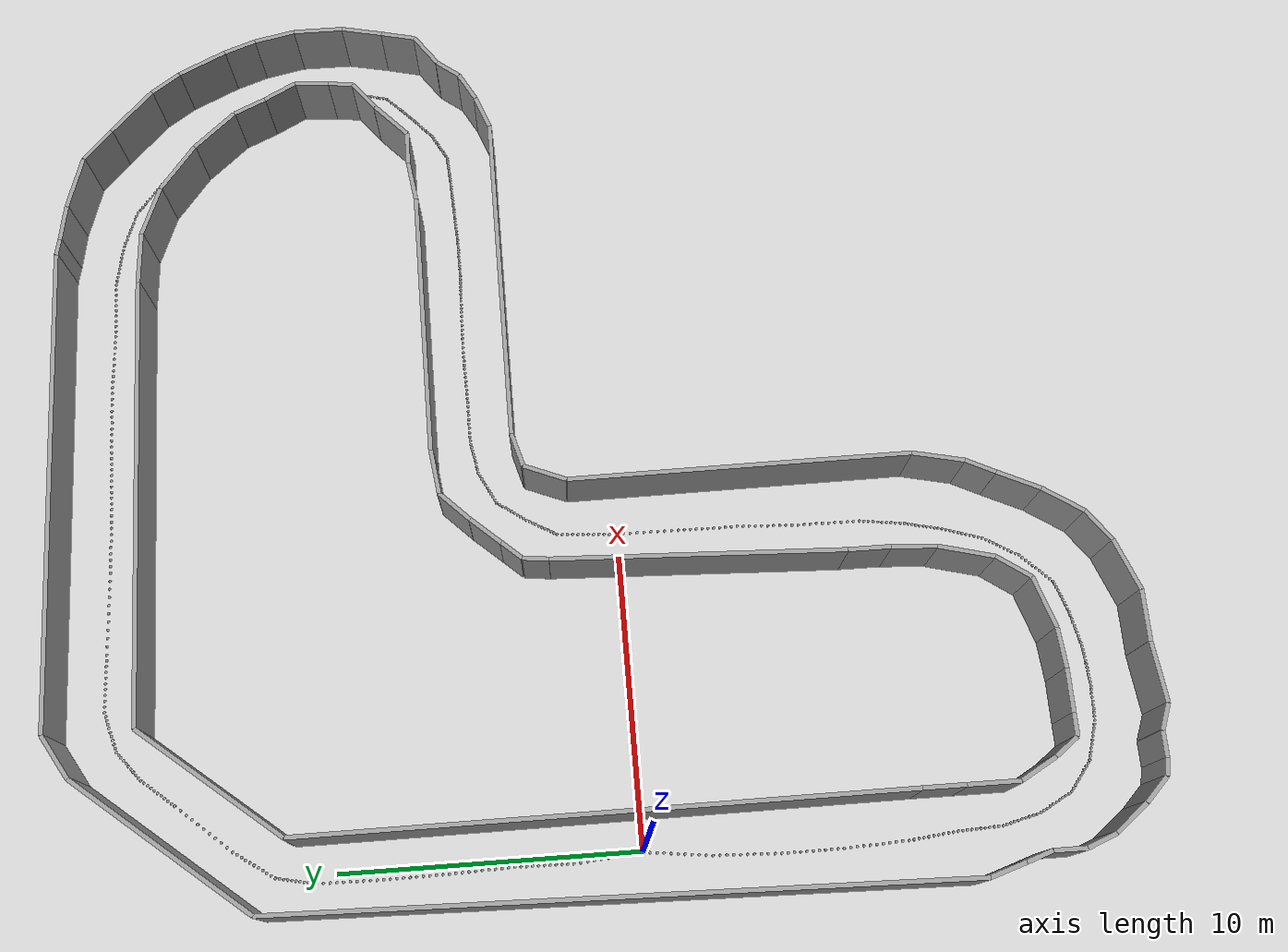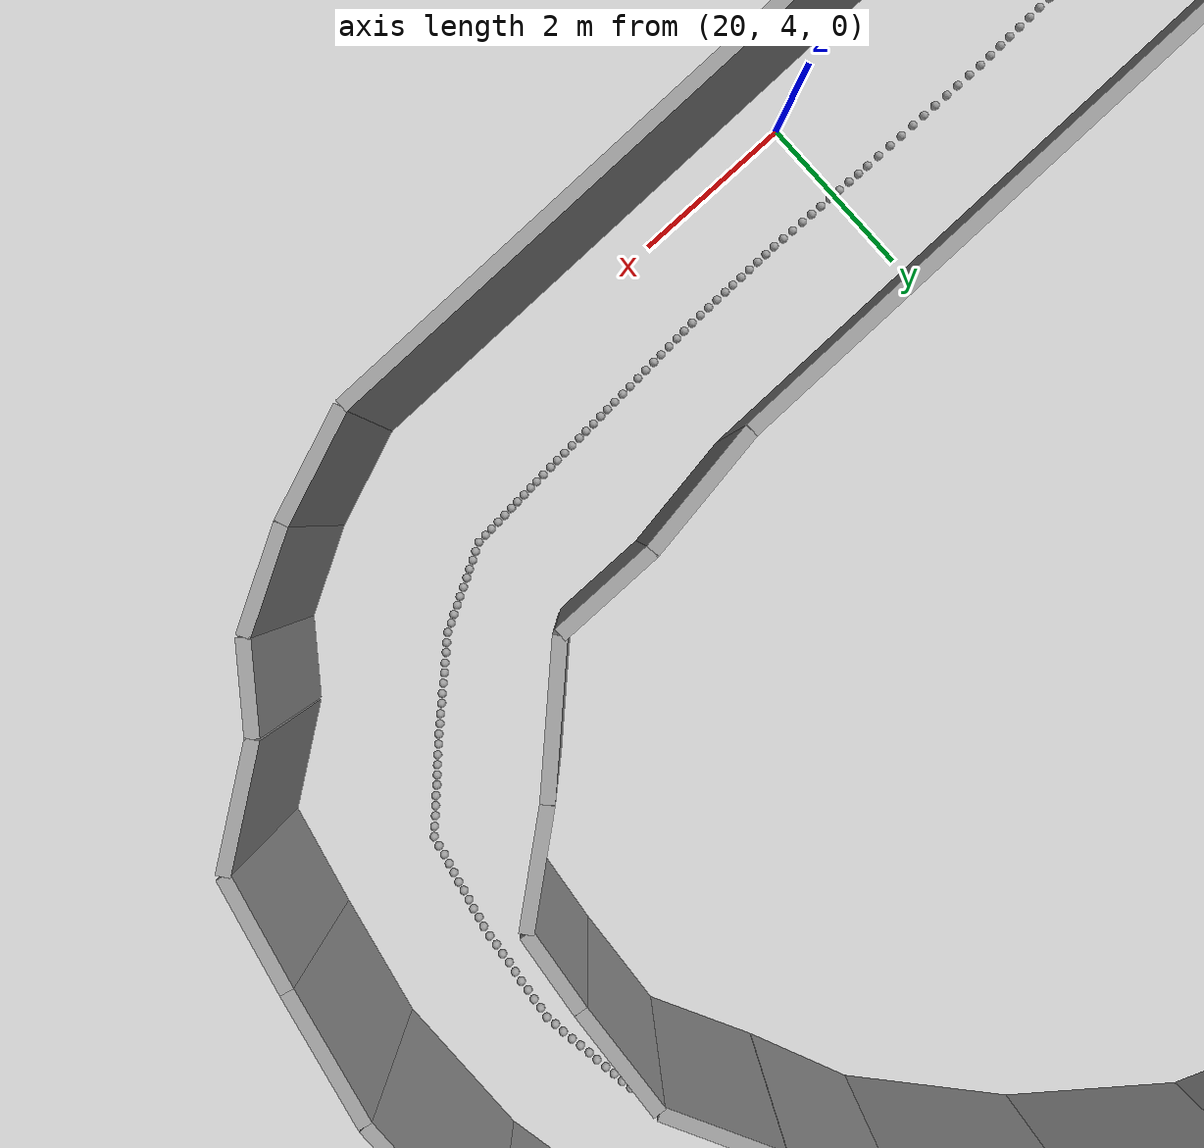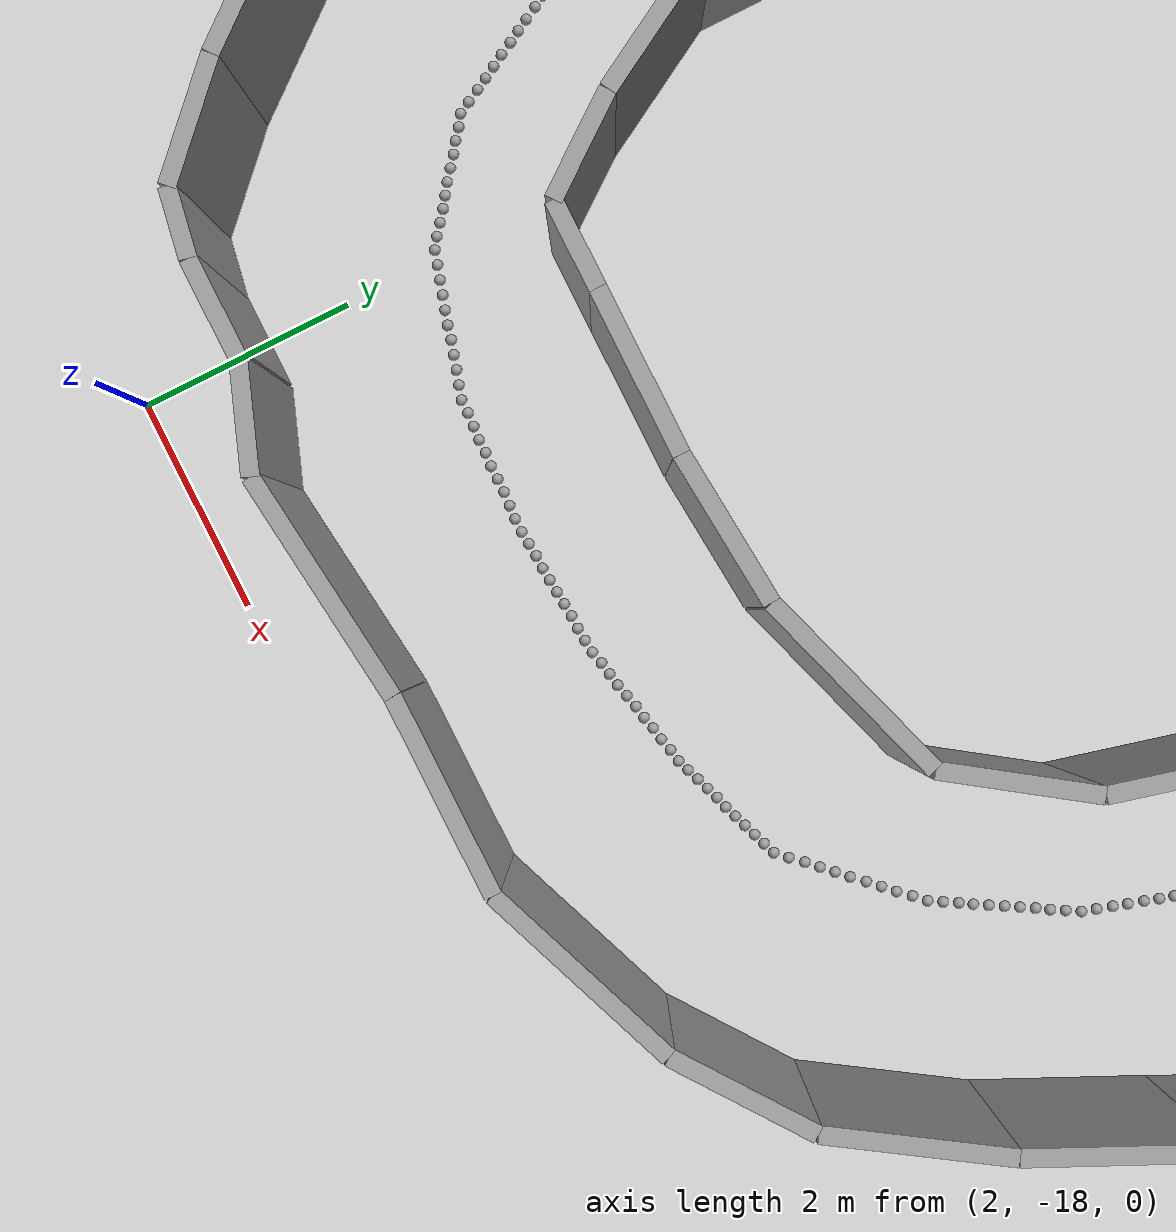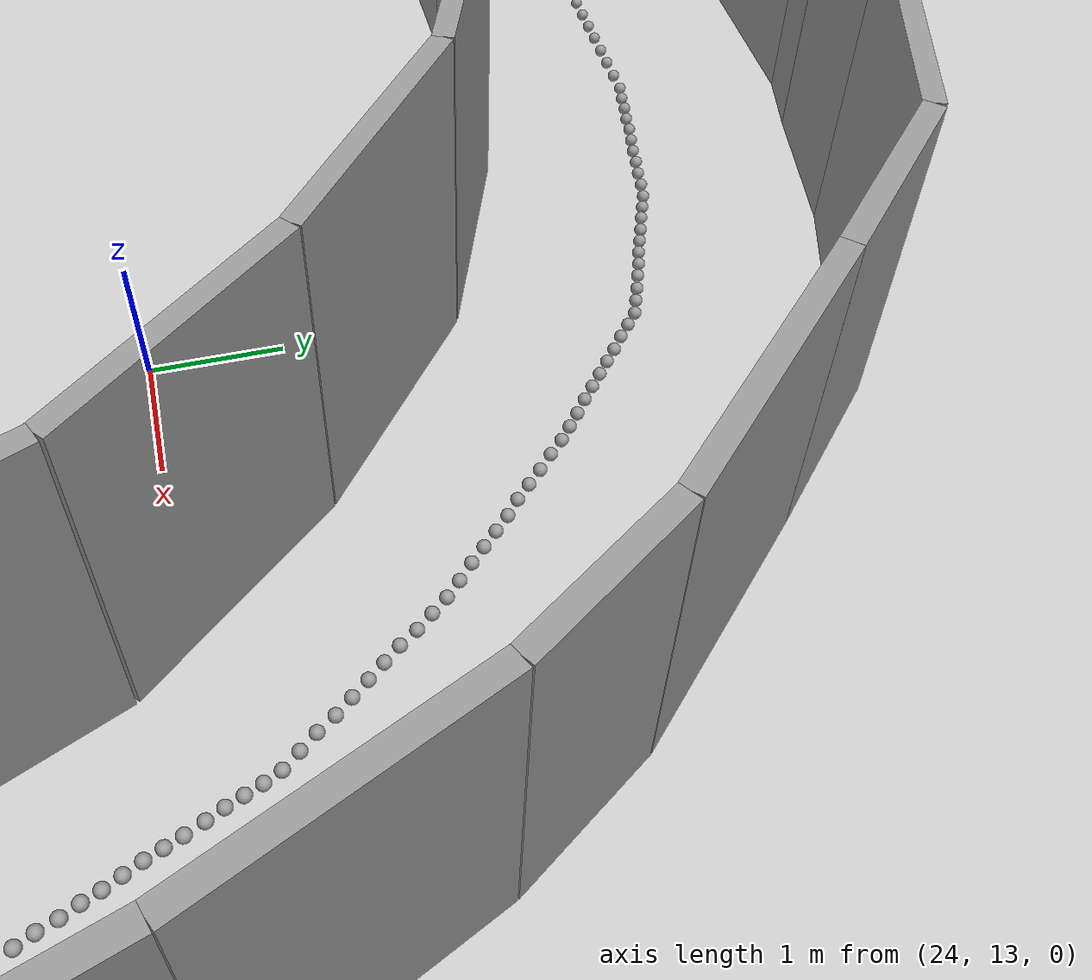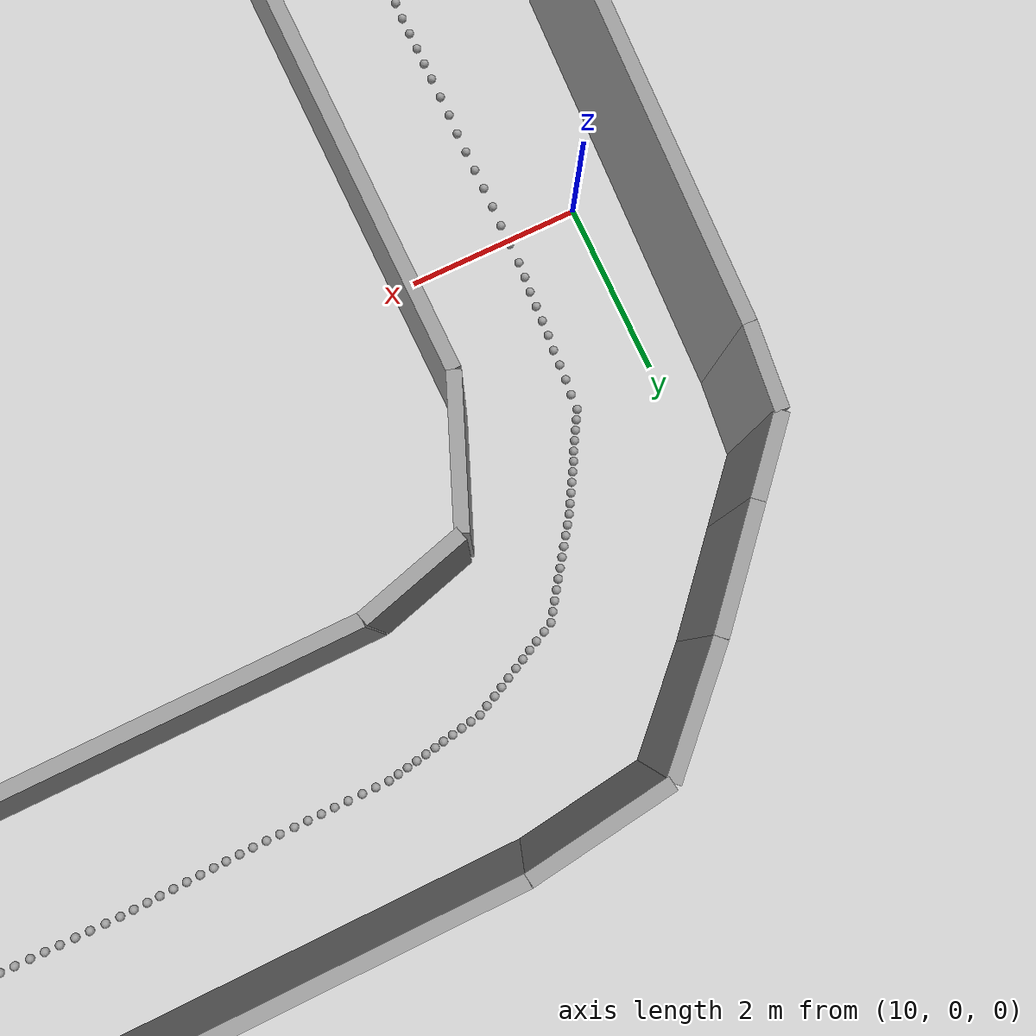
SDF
<sdf version='1.6'>
    <world name='default'>
      <light name='sun' type='directional'>
        <cast_shadows>1</cast_shadows>
        <pose frame=''>0 0 10 0 -0 0</pose>
        <diffuse>0.8 0.8 0.8 1</diffuse>
        <specular>0.2 0.2 0.2 1</specular>
        <attenuation>
          <range>1000</range>
          <constant>0.9</constant>
          <linear>0.01</linear>
          <quadratic>0.001</quadratic>
        </attenuation>
        <direction>-0.5 0.1 -0.9</direction>
      </light>
      <model name='ground_plane'>
        <static>1</static>
        <link name='link'>
          <collision name='collision'>
            <geometry>
              <plane>
                <normal>0 0 1</normal>
                <size>100 100</size>
              </plane>
            </geometry>
            <surface>
              <friction>
                <ode>
                  <mu>100</mu>
                  <mu2>50</mu2>
                </ode>
                <torsional>
                  <ode/>
                </torsional>
              </friction>
              <contact>
                <ode/>
              </contact>
              <bounce/>
            </surface>
            <max_contacts>10</max_contacts>
          </collision>
          <visual name='visual'>
            <cast_shadows>0</cast_shadows>
            <geometry>
              <plane>
                <normal>0 0 1</normal>
                <size>100 100</size>
              </plane>
            </geometry>
            <material>
              <script>
                <uri>file://media/materials/scripts/gazebo.material</uri>
                <name>Gazebo/Grey</name>
              </script>
            </material>
          </visual>
          <self_collide>0</self_collide>
          <enable_wind>0</enable_wind>
          <kinematic>0</kinematic>
        </link>
      </model>
      <gravity>0 0 -9.8</gravity>
      <magnetic_field>6e-06 2.3e-05 -4.2e-05</magnetic_field>
      <atmosphere type='adiabatic'/>
      <physics name='default_physics' default='0' type='ode'>
        <max_step_size>0.001</max_step_size>
        <real_time_factor>1</real_time_factor>
        <real_time_update_rate>1000</real_time_update_rate>
      </physics>
      <scene>
        <ambient>0.4 0.4 0.4 1</ambient>
        <background>0.7 0.7 0.7 1</background>
        <shadows>1</shadows>
      </scene>
      <wind/>
      <spherical_coordinates>
        <surface_model>EARTH_WGS84</surface_model>
        <latitude_deg>0</latitude_deg>
        <longitude_deg>0</longitude_deg>
        <elevation>0</elevation>
        <heading_deg>0</heading_deg>
      </spherical_coordinates>
      <model name='track2'>
        <pose frame=''>0 0 0 0 -0 0</pose>
        <link name='wall_000'>
                <collision name='wall_000_Collision'>
                <geometry>
                    <box>
                    <size>1.431500 0.15 2.5</size>
                    </box>
                </geometry>
                <pose frame=''>0 0 1.25 0 -0 0</pose>
                <max_contacts>10</max_contacts>
                <surface>
                    <contact>
                    <ode/>
                    </contact>
                    <bounce/>
                    <friction>
                    <torsional>
                        <ode/>
                    </torsional>
                    <ode/>
                    </friction>
                </surface>
                </collision>
                <visual name='wall_000_Visual'>
                <pose frame=''>0 0 1.25 0 -0 0</pose>
                <geometry>
                    <box>
                    <size>1.431500 0.15 2.5</size>
                    </box>
                </geometry>
                <material>
                    <script>
                    <uri>file://media/materials/scripts/gazebo.material</uri>
                    <name>Gazebo/Grey</name>
                    </script>
                    <ambient>1 1 1 1</ambient>
                </material>
                <meta>
                    <layer>0</layer>
                </meta>
                </visual>
                <pose frame=''>1.160250 -9.630250 0 0 -0 1.570796</pose>
                <self_collide>0</self_collide>
                <enable_wind>0</enable_wind>
                <kinematic>0</kinematic>
            </link>
            <link name='wall_001'>
                <collision name='wall_001_Collision'>
                <geometry>
                    <box>
                    <size>1.760500 0.15 2.5</size>
                    </box>
                </geometry>
                <pose frame=''>0 0 1.25 0 -0 0</pose>
                <max_contacts>10</max_contacts>
                <surface>
                    <contact>
                    <ode/>
                    </contact>
                    <bounce/>
                    <friction>
                    <torsional>
                        <ode/>
                    </torsional>
                    <ode/>
                    </friction>
                </surface>
                </collision>
                <visual name='wall_001_Visual'>
                <pose frame=''>0 0 1.25 0 -0 0</pose>
                <geometry>
                    <box>
                    <size>1.760500 0.15 2.5</size>
                    </box>
                </geometry>
                <material>
                    <script>
                    <uri>file://media/materials/scripts/gazebo.material</uri>
                    <name>Gazebo/Grey</name>
                    </script>
                    <ambient>1 1 1 1</ambient>
                </material>
                <meta>
                    <layer>0</layer>
                </meta>
                </visual>
                <pose frame=''>1.160250 -11.226250 0 0 -0 1.570796</pose>
                <self_collide>0</self_collide>
                <enable_wind>0</enable_wind>
                <kinematic>0</kinematic>
            </link>
            <link name='wall_002'>
                <collision name='wall_002_Collision'>
                <geometry>
                    <box>
                    <size>1.387512 0.15 2.5</size>
                    </box>
                </geometry>
                <pose frame=''>0 0 1.25 0 -0 0</pose>
                <max_contacts>10</max_contacts>
                <surface>
                    <contact>
                    <ode/>
                    </contact>
                    <bounce/>
                    <friction>
                    <torsional>
                        <ode/>
                    </torsional>
                    <ode/>
                    </friction>
                </surface>
                </collision>
                <visual name='wall_002_Visual'>
                <pose frame=''>0 0 1.25 0 -0 0</pose>
                <geometry>
                    <box>
                    <size>1.387512 0.15 2.5</size>
                    </box>
                </geometry>
                <material>
                    <script>
                    <uri>file://media/materials/scripts/gazebo.material</uri>
                    <name>Gazebo/Grey</name>
                    </script>
                    <ambient>1 1 1 1</ambient>
                </material>
                <meta>
                    <layer>0</layer>
                </meta>
                </visual>
                <pose frame=''>1.498875 -12.712000 0 0 -0 2.080712</pose>
                <self_collide>0</self_collide>
                <enable_wind>0</enable_wind>
                <kinematic>0</kinematic>
            </link>
            <link name='wall_003'>
                <collision name='wall_003_Collision'>
                <geometry>
                    <box>
                    <size>0.963551 0.15 2.5</size>
                    </box>
                </geometry>
                <pose frame=''>0 0 1.25 0 -0 0</pose>
                <max_contacts>10</max_contacts>
                <surface>
                    <contact>
                    <ode/>
                    </contact>
                    <bounce/>
                    <friction>
                    <torsional>
                        <ode/>
                    </torsional>
                    <ode/>
                    </friction>
                </surface>
                </collision>
                <visual name='wall_003_Visual'>
                <pose frame=''>0 0 1.25 0 -0 0</pose>
                <geometry>
                    <box>
                    <size>0.963551 0.15 2.5</size>
                    </box>
                </geometry>
                <material>
                    <script>
                    <uri>file://media/materials/scripts/gazebo.material</uri>
                    <name>Gazebo/Grey</name>
                    </script>
                    <ambient>1 1 1 1</ambient>
                </material>
                <meta>
                    <layer>0</layer>
                </meta>
                </visual>
                <pose frame=''>2.127125 -13.702500 0 0 -0 2.215750</pose>
                <self_collide>0</self_collide>
                <enable_wind>0</enable_wind>
                <kinematic>0</kinematic>
            </link>
            <link name='wall_004'>
                <collision name='wall_004_Collision'>
                <geometry>
                    <box>
                    <size>0.773500 0.15 2.5</size>
                    </box>
                </geometry>
                <pose frame=''>0 0 1.25 0 -0 0</pose>
                <max_contacts>10</max_contacts>
                <surface>
                    <contact>
                    <ode/>
                    </contact>
                    <bounce/>
                    <friction>
                    <torsional>
                        <ode/>
                    </torsional>
                    <ode/>
                    </friction>
                </surface>
                </collision>
                <visual name='wall_004_Visual'>
                <pose frame=''>0 0 1.25 0 -0 0</pose>
                <geometry>
                    <box>
                    <size>0.773500 0.15 2.5</size>
                    </box>
                </geometry>
                <material>
                    <script>
                    <uri>file://media/materials/scripts/gazebo.material</uri>
                    <name>Gazebo/Grey</name>
                    </script>
                    <ambient>1 1 1 1</ambient>
                </material>
                <meta>
                    <layer>0</layer>
                </meta>
                </visual>
                <pose frame=''>2.803500 -14.087500 0 0 -0 3.141593</pose>
                <self_collide>0</self_collide>
                <enable_wind>0</enable_wind>
                <kinematic>0</kinematic>
            </link>
            <link name='wall_005'>
                <collision name='wall_005_Collision'>
                <geometry>
                    <box>
                    <size>1.450750 0.15 2.5</size>
                    </box>
                </geometry>
                <pose frame=''>0 0 1.25 0 -0 0</pose>
                <max_contacts>10</max_contacts>
                <surface>
                    <contact>
                    <ode/>
                    </contact>
                    <bounce/>
                    <friction>
                    <torsional>
                        <ode/>
                    </torsional>
                    <ode/>
                    </friction>
                </surface>
                </collision>
                <visual name='wall_005_Visual'>
                <pose frame=''>0 0 1.25 0 -0 0</pose>
                <geometry>
                    <box>
                    <size>1.450750 0.15 2.5</size>
                    </box>
                </geometry>
                <material>
                    <script>
                    <uri>file://media/materials/scripts/gazebo.material</uri>
                    <name>Gazebo/Grey</name>
                    </script>
                    <ambient>1 1 1 1</ambient>
                </material>
                <meta>
                    <layer>0</layer>
                </meta>
                </visual>
                <pose frame=''>3.915625 -14.087500 0 0 -0 3.141593</pose>
                <self_collide>0</self_collide>
                <enable_wind>0</enable_wind>
                <kinematic>0</kinematic>
            </link>
            <link name='wall_006'>
                <collision name='wall_006_Collision'>
                <geometry>
                    <box>
                    <size>1.357094 0.15 2.5</size>
                    </box>
                </geometry>
                <pose frame=''>0 0 1.25 0 -0 0</pose>
                <max_contacts>10</max_contacts>
                <surface>
                    <contact>
                    <ode/>
                    </contact>
                    <bounce/>
                    <friction>
                    <torsional>
                        <ode/>
                    </torsional>
                    <ode/>
                    </friction>
                </surface>
                </collision>
                <visual name='wall_006_Visual'>
                <pose frame=''>0 0 1.25 0 -0 0</pose>
                <geometry>
                    <box>
                    <size>1.357094 0.15 2.5</size>
                    </box>
                </geometry>
                <material>
                    <script>
                    <uri>file://media/materials/scripts/gazebo.material</uri>
                    <name>Gazebo/Grey</name>
                    </script>
                    <ambient>1 1 1 1</ambient>
                </material>
                <meta>
                    <layer>0</layer>
                </meta>
                </visual>
                <pose frame=''>5.317375 -14.033250 0 0 -0 -3.061557</pose>
                <self_collide>0</self_collide>
                <enable_wind>0</enable_wind>
                <kinematic>0</kinematic>
            </link>
            <link name='wall_007'>
                <collision name='wall_007_Collision'>
                <geometry>
                    <box>
                    <size>1.826954 0.15 2.5</size>
                    </box>
                </geometry>
                <pose frame=''>0 0 1.25 0 -0 0</pose>
                <max_contacts>10</max_contacts>
                <surface>
                    <contact>
                    <ode/>
                    </contact>
                    <bounce/>
                    <friction>
                    <torsional>
                        <ode/>
                    </torsional>
                    <ode/>
                    </friction>
                </surface>
                </collision>
                <visual name='wall_007_Visual'>
                <pose frame=''>0 0 1.25 0 -0 0</pose>
                <geometry>
                    <box>
                    <size>1.826954 0.15 2.5</size>
                    </box>
                </geometry>
                <material>
                    <script>
                    <uri>file://media/materials/scripts/gazebo.material</uri>
                    <name>Gazebo/Grey</name>
                    </script>
                    <ambient>1 1 1 1</ambient>
                </material>
                <meta>
                    <layer>0</layer>
                </meta>
                </visual>
                <pose frame=''>6.864375 -13.702500 0 0 -0 -2.834079</pose>
                <self_collide>0</self_collide>
                <enable_wind>0</enable_wind>
                <kinematic>0</kinematic>
            </link>
            <link name='wall_008'>
                <collision name='wall_008_Collision'>
                <geometry>
                    <box>
                    <size>1.343913 0.15 2.5</size>
                    </box>
                </geometry>
                <pose frame=''>0 0 1.25 0 -0 0</pose>
                <max_contacts>10</max_contacts>
                <surface>
                    <contact>
                    <ode/>
                    </contact>
                    <bounce/>
                    <friction>
                    <torsional>
                        <ode/>
                    </torsional>
                    <ode/>
                    </friction>
                </surface>
                </collision>
                <visual name='wall_008_Visual'>
                <pose frame=''>0 0 1.25 0 -0 0</pose>
                <geometry>
                    <box>
                    <size>1.343913 0.15 2.5</size>
                    </box>
                </geometry>
                <material>
                    <script>
                    <uri>file://media/materials/scripts/gazebo.material</uri>
                    <name>Gazebo/Grey</name>
                    </script>
                    <ambient>1 1 1 1</ambient>
                </material>
                <meta>
                    <layer>0</layer>
                </meta>
                </visual>
                <pose frame=''>8.121750 -12.876500 0 0 -0 -2.184083</pose>
                <self_collide>0</self_collide>
                <enable_wind>0</enable_wind>
                <kinematic>0</kinematic>
            </link>
            <link name='wall_009'>
                <collision name='wall_009_Collision'>
                <geometry>
                    <box>
                    <size>1.933790 0.15 2.5</size>
                    </box>
                </geometry>
                <pose frame=''>0 0 1.25 0 -0 0</pose>
                <max_contacts>10</max_contacts>
                <surface>
                    <contact>
                    <ode/>
                    </contact>
                    <bounce/>
                    <friction>
                    <torsional>
                        <ode/>
                    </torsional>
                    <ode/>
                    </friction>
                </surface>
                </collision>
                <visual name='wall_009_Visual'>
                <pose frame=''>0 0 1.25 0 -0 0</pose>
                <geometry>
                    <box>
                    <size>1.933790 0.15 2.5</size>
                    </box>
                </geometry>
                <material>
                    <script>
                    <uri>file://media/materials/scripts/gazebo.material</uri>
                    <name>Gazebo/Grey</name>
                    </script>
                    <ambient>1 1 1 1</ambient>
                </material>
                <meta>
                    <layer>0</layer>
                </meta>
                </visual>
                <pose frame=''>8.750000 -11.390750 0 0 -0 -1.823238</pose>
                <self_collide>0</self_collide>
                <enable_wind>0</enable_wind>
                <kinematic>0</kinematic>
            </link>
            <link name='wall_010'>
                <collision name='wall_010_Collision'>
                <geometry>
                    <box>
                    <size>1.543005 0.15 2.5</size>
                    </box>
                </geometry>
                <pose frame=''>0 0 1.25 0 -0 0</pose>
                <max_contacts>10</max_contacts>
                <surface>
                    <contact>
                    <ode/>
                    </contact>
                    <bounce/>
                    <friction>
                    <torsional>
                        <ode/>
                    </torsional>
                    <ode/>
                    </friction>
                </surface>
                </collision>
                <visual name='wall_010_Visual'>
                <pose frame=''>0 0 1.25 0 -0 0</pose>
                <geometry>
                    <box>
                    <size>1.543005 0.15 2.5</size>
                    </box>
                </geometry>
                <material>
                    <script>
                    <uri>file://media/materials/scripts/gazebo.material</uri>
                    <name>Gazebo/Grey</name>
                    </script>
                    <ambient>1 1 1 1</ambient>
                </material>
                <meta>
                    <layer>0</layer>
                </meta>
                </visual>
                <pose frame=''>9.039625 -9.684500 0 0 -0 -1.633215</pose>
                <self_collide>0</self_collide>
                <enable_wind>0</enable_wind>
                <kinematic>0</kinematic>
            </link>
            <link name='wall_011'>
                <collision name='wall_011_Collision'>
                <geometry>
                    <box>
                    <size>1.431500 0.15 2.5</size>
                    </box>
                </geometry>
                <pose frame=''>0 0 1.25 0 -0 0</pose>
                <max_contacts>10</max_contacts>
                <surface>
                    <contact>
                    <ode/>
                    </contact>
                    <bounce/>
                    <friction>
                    <torsional>
                        <ode/>
                    </torsional>
                    <ode/>
                    </friction>
                </surface>
                </collision>
                <visual name='wall_011_Visual'>
                <pose frame=''>0 0 1.25 0 -0 0</pose>
                <geometry>
                    <box>
                    <size>1.431500 0.15 2.5</size>
                    </box>
                </geometry>
                <material>
                    <script>
                    <uri>file://media/materials/scripts/gazebo.material</uri>
                    <name>Gazebo/Grey</name>
                    </script>
                    <ambient>1 1 1 1</ambient>
                </material>
                <meta>
                    <layer>0</layer>
                </meta>
                </visual>
                <pose frame=''>9.087750 -8.198750 0 0 -0 -1.570796</pose>
                <self_collide>0</self_collide>
                <enable_wind>0</enable_wind>
                <kinematic>0</kinematic>
            </link>
            <link name='wall_012'>
                <collision name='wall_012_Collision'>
                <geometry>
                    <box>
                    <size>9.912548 0.15 2.5</size>
                    </box>
                </geometry>
                <pose frame=''>0 0 1.25 0 -0 0</pose>
                <max_contacts>10</max_contacts>
                <surface>
                    <contact>
                    <ode/>
                    </contact>
                    <bounce/>
                    <friction>
                    <torsional>
                        <ode/>
                    </torsional>
                    <ode/>
                    </friction>
                </surface>
                </collision>
                <visual name='wall_012_Visual'>
                <pose frame=''>0 0 1.25 0 -0 0</pose>
                <geometry>
                    <box>
                    <size>9.912548 0.15 2.5</size>
                    </box>
                </geometry>
                <material>
                    <script>
                    <uri>file://media/materials/scripts/gazebo.material</uri>
                    <name>Gazebo/Grey</name>
                    </script>
                    <ambient>1 1 1 1</ambient>
                </material>
                <meta>
                    <layer>0</layer>
                </meta>
                </visual>
                <pose frame=''>9.281125 -2.530500 0 0 -0 -1.609822</pose>
                <self_collide>0</self_collide>
                <enable_wind>0</enable_wind>
                <kinematic>0</kinematic>
            </link>
            <link name='wall_013'>
                <collision name='wall_013_Collision'>
                <geometry>
                    <box>
                    <size>0.885688 0.15 2.5</size>
                    </box>
                </geometry>
                <pose frame=''>0 0 1.25 0 -0 0</pose>
                <max_contacts>10</max_contacts>
                <surface>
                    <contact>
                    <ode/>
                    </contact>
                    <bounce/>
                    <friction>
                    <torsional>
                        <ode/>
                    </torsional>
                    <ode/>
                    </friction>
                </surface>
                </collision>
                <visual name='wall_013_Visual'>
                <pose frame=''>0 0 1.25 0 -0 0</pose>
                <geometry>
                    <box>
                    <size>0.885688 0.15 2.5</size>
                    </box>
                </geometry>
                <material>
                    <script>
                    <uri>file://media/materials/scripts/gazebo.material</uri>
                    <name>Gazebo/Grey</name>
                    </script>
                    <ambient>1 1 1 1</ambient>
                </material>
                <meta>
                    <layer>0</layer>
                </meta>
                </visual>
                <pose frame=''>9.523500 2.862125 0 0 -0 -1.681672</pose>
                <self_collide>0</self_collide>
                <enable_wind>0</enable_wind>
                <kinematic>0</kinematic>
            </link>
            <link name='wall_014'>
                <collision name='wall_014_Collision'>
                <geometry>
                    <box>
                    <size>0.877953 0.15 2.5</size>
                    </box>
                </geometry>
                <pose frame=''>0 0 1.25 0 -0 0</pose>
                <max_contacts>10</max_contacts>
                <surface>
                    <contact>
                    <ode/>
                    </contact>
                    <bounce/>
                    <friction>
                    <torsional>
                        <ode/>
                    </torsional>
                    <ode/>
                    </friction>
                </surface>
                </collision>
                <visual name='wall_014_Visual'>
                <pose frame=''>0 0 1.25 0 -0 0</pose>
                <geometry>
                    <box>
                    <size>0.877953 0.15 2.5</size>
                    </box>
                </geometry>
                <material>
                    <script>
                    <uri>file://media/materials/scripts/gazebo.material</uri>
                    <name>Gazebo/Grey</name>
                    </script>
                    <ambient>1 1 1 1</ambient>
                </material>
                <meta>
                    <layer>0</layer>
                </meta>
                </visual>
                <pose frame=''>9.862125 3.632125 0 0 -0 -2.291314</pose>
                <self_collide>0</self_collide>
                <enable_wind>0</enable_wind>
                <kinematic>0</kinematic>
            </link>
            <link name='wall_015'>
                <collision name='wall_015_Collision'>
                <geometry>
                    <box>
                    <size>1.318164 0.15 2.5</size>
                    </box>
                </geometry>
                <pose frame=''>0 0 1.25 0 -0 0</pose>
                <max_contacts>10</max_contacts>
                <surface>
                    <contact>
                    <ode/>
                    </contact>
                    <bounce/>
                    <friction>
                    <torsional>
                        <ode/>
                    </torsional>
                    <ode/>
                    </friction>
                </surface>
                </collision>
                <visual name='wall_015_Visual'>
                <pose frame=''>0 0 1.25 0 -0 0</pose>
                <geometry>
                    <box>
                    <size>1.318164 0.15 2.5</size>
                    </box>
                </geometry>
                <material>
                    <script>
                    <uri>file://media/materials/scripts/gazebo.material</uri>
                    <name>Gazebo/Grey</name>
                    </script>
                    <ambient>1 1 1 1</ambient>
                </material>
                <meta>
                    <layer>0</layer>
                </meta>
                </visual>
                <pose frame=''>10.586625 4.457250 0 0 -0 -2.291375</pose>
                <self_collide>0</self_collide>
                <enable_wind>0</enable_wind>
                <kinematic>0</kinematic>
            </link>
            <link name='wall_016'>
                <collision name='wall_016_Collision'>
                <geometry>
                    <box>
                    <size>1.384785 0.15 2.5</size>
                    </box>
                </geometry>
                <pose frame=''>0 0 1.25 0 -0 0</pose>
                <max_contacts>10</max_contacts>
                <surface>
                    <contact>
                    <ode/>
                    </contact>
                    <bounce/>
                    <friction>
                    <torsional>
                        <ode/>
                    </torsional>
                    <ode/>
                    </friction>
                </surface>
                </collision>
                <visual name='wall_016_Visual'>
                <pose frame=''>0 0 1.25 0 -0 0</pose>
                <geometry>
                    <box>
                    <size>1.384785 0.15 2.5</size>
                    </box>
                </geometry>
                <material>
                    <script>
                    <uri>file://media/materials/scripts/gazebo.material</uri>
                    <name>Gazebo/Grey</name>
                    </script>
                    <ambient>1 1 1 1</ambient>
                </material>
                <meta>
                    <layer>0</layer>
                </meta>
                </visual>
                <pose frame=''>11.505375 5.447750 0 0 -0 -2.344577</pose>
                <self_collide>0</self_collide>
                <enable_wind>0</enable_wind>
                <kinematic>0</kinematic>
            </link>
            <link name='wall_017'>
                <collision name='wall_017_Collision'>
                <geometry>
                    <box>
                    <size>1.562635 0.15 2.5</size>
                    </box>
                </geometry>
                <pose frame=''>0 0 1.25 0 -0 0</pose>
                <max_contacts>10</max_contacts>
                <surface>
                    <contact>
                    <ode/>
                    </contact>
                    <bounce/>
                    <friction>
                    <torsional>
                        <ode/>
                    </torsional>
                    <ode/>
                    </friction>
                </surface>
                </collision>
                <visual name='wall_017_Visual'>
                <pose frame=''>0 0 1.25 0 -0 0</pose>
                <geometry>
                    <box>
                    <size>1.562635 0.15 2.5</size>
                    </box>
                </geometry>
                <material>
                    <script>
                    <uri>file://media/materials/scripts/gazebo.material</uri>
                    <name>Gazebo/Grey</name>
                    </script>
                    <ambient>1 1 1 1</ambient>
                </material>
                <meta>
                    <layer>0</layer>
                </meta>
                </visual>
                <pose frame=''>12.762750 6.053250 0 0 -0 -3.000012</pose>
                <self_collide>0</self_collide>
                <enable_wind>0</enable_wind>
                <kinematic>0</kinematic>
            </link>
            <link name='wall_018'>
                <collision name='wall_018_Collision'>
                <geometry>
                    <box>
                    <size>9.371878 0.15 2.5</size>
                    </box>
                </geometry>
                <pose frame=''>0 0 1.25 0 -0 0</pose>
                <max_contacts>10</max_contacts>
                <surface>
                    <contact>
                    <ode/>
                    </contact>
                    <bounce/>
                    <friction>
                    <torsional>
                        <ode/>
                    </torsional>
                    <ode/>
                    </friction>
                </surface>
                </collision>
                <visual name='wall_018_Visual'>
                <pose frame=''>0 0 1.25 0 -0 0</pose>
                <geometry>
                    <box>
                    <size>9.371878 0.15 2.5</size>
                    </box>
                </geometry>
                <material>
                    <script>
                    <uri>file://media/materials/scripts/gazebo.material</uri>
                    <name>Gazebo/Grey</name>
                    </script>
                    <ambient>1 1 1 1</ambient>
                </material>
                <meta>
                    <layer>0</layer>
                </meta>
                </visual>
                <pose frame=''>18.221875 6.217750 0 0 -0 -3.130015</pose>
                <self_collide>0</self_collide>
                <enable_wind>0</enable_wind>
                <kinematic>0</kinematic>
            </link>
            <link name='wall_019'>
                <collision name='wall_019_Collision'>
                <geometry>
                    <box>
                    <size>1.469141 0.15 2.5</size>
                    </box>
                </geometry>
                <pose frame=''>0 0 1.25 0 -0 0</pose>
                <max_contacts>10</max_contacts>
                <surface>
                    <contact>
                    <ode/>
                    </contact>
                    <bounce/>
                    <friction>
                    <torsional>
                        <ode/>
                    </torsional>
                    <ode/>
                    </friction>
                </surface>
                </collision>
                <visual name='wall_019_Visual'>
                <pose frame=''>0 0 1.25 0 -0 0</pose>
                <geometry>
                    <box>
                    <size>1.469141 0.15 2.5</size>
                    </box>
                </geometry>
                <material>
                    <script>
                    <uri>file://media/materials/scripts/gazebo.material</uri>
                    <name>Gazebo/Grey</name>
                    </script>
                    <ambient>1 1 1 1</ambient>
                </material>
                <meta>
                    <layer>0</layer>
                </meta>
                </visual>
                <pose frame=''>23.633750 6.382250 0 0 -0 -2.990936</pose>
                <self_collide>0</self_collide>
                <enable_wind>0</enable_wind>
                <kinematic>0</kinematic>
            </link>
            <link name='wall_020'>
                <collision name='wall_020_Collision'>
                <geometry>
                    <box>
                    <size>1.172500 0.15 2.5</size>
                    </box>
                </geometry>
                <pose frame=''>0 0 1.25 0 -0 0</pose>
                <max_contacts>10</max_contacts>
                <surface>
                    <contact>
                    <ode/>
                    </contact>
                    <bounce/>
                    <friction>
                    <torsional>
                        <ode/>
                    </torsional>
                    <ode/>
                    </friction>
                </surface>
                </collision>
                <visual name='wall_020_Visual'>
                <pose frame=''>0 0 1.25 0 -0 0</pose>
                <geometry>
                    <box>
                    <size>1.172500 0.15 2.5</size>
                    </box>
                </geometry>
                <material>
                    <script>
                    <uri>file://media/materials/scripts/gazebo.material</uri>
                    <name>Gazebo/Grey</name>
                    </script>
                    <ambient>1 1 1 1</ambient>
                </material>
                <meta>
                    <layer>0</layer>
                </meta>
                </visual>
                <pose frame=''>24.946250 6.492500 0 0 -0 3.141593</pose>
                <self_collide>0</self_collide>
                <enable_wind>0</enable_wind>
                <kinematic>0</kinematic>
            </link>
            <link name='wall_021'>
                <collision name='wall_021_Collision'>
                <geometry>
                    <box>
                    <size>1.596725 0.15 2.5</size>
                    </box>
                </geometry>
                <pose frame=''>0 0 1.25 0 -0 0</pose>
                <max_contacts>10</max_contacts>
                <surface>
                    <contact>
                    <ode/>
                    </contact>
                    <bounce/>
                    <friction>
                    <torsional>
                        <ode/>
                    </torsional>
                    <ode/>
                    </friction>
                </surface>
                </collision>
                <visual name='wall_021_Visual'>
                <pose frame=''>0 0 1.25 0 -0 0</pose>
                <geometry>
                    <box>
                    <size>1.596725 0.15 2.5</size>
                    </box>
                </geometry>
                <material>
                    <script>
                    <uri>file://media/materials/scripts/gazebo.material</uri>
                    <name>Gazebo/Grey</name>
                    </script>
                    <ambient>1 1 1 1</ambient>
                </material>
                <meta>
                    <layer>0</layer>
                </meta>
                </visual>
                <pose frame=''>26.110000 7.043750 0 0 -0 -2.379446</pose>
                <self_collide>0</self_collide>
                <enable_wind>0</enable_wind>
                <kinematic>0</kinematic>
            </link>
            <link name='wall_022'>
                <collision name='wall_022_Collision'>
                <geometry>
                    <box>
                    <size>1.232601 0.15 2.5</size>
                    </box>
                </geometry>
                <pose frame=''>0 0 1.25 0 -0 0</pose>
                <max_contacts>10</max_contacts>
                <surface>
                    <contact>
                    <ode/>
                    </contact>
                    <bounce/>
                    <friction>
                    <torsional>
                        <ode/>
                    </torsional>
                    <ode/>
                    </friction>
                </surface>
                </collision>
                <visual name='wall_022_Visual'>
                <pose frame=''>0 0 1.25 0 -0 0</pose>
                <geometry>
                    <box>
                    <size>1.232601 0.15 2.5</size>
                    </box>
                </geometry>
                <material>
                    <script>
                    <uri>file://media/materials/scripts/gazebo.material</uri>
                    <name>Gazebo/Grey</name>
                    </script>
                    <ambient>1 1 1 1</ambient>
                </material>
                <meta>
                    <layer>0</layer>
                </meta>
                </visual>
                <pose frame=''>27.168750 7.980000 0 0 -0 -2.466852</pose>
                <self_collide>0</self_collide>
                <enable_wind>0</enable_wind>
                <kinematic>0</kinematic>
            </link>
            <link name='wall_023'>
                <collision name='wall_023_Collision'>
                <geometry>
                    <box>
                    <size>0.888228 0.15 2.5</size>
                    </box>
                </geometry>
                <pose frame=''>0 0 1.25 0 -0 0</pose>
                <max_contacts>10</max_contacts>
                <surface>
                    <contact>
                    <ode/>
                    </contact>
                    <bounce/>
                    <friction>
                    <torsional>
                        <ode/>
                    </torsional>
                    <ode/>
                    </friction>
                </surface>
                </collision>
                <visual name='wall_023_Visual'>
                <pose frame=''>0 0 1.25 0 -0 0</pose>
                <geometry>
                    <box>
                    <size>0.888228 0.15 2.5</size>
                    </box>
                </geometry>
                <material>
                    <script>
                    <uri>file://media/materials/scripts/gazebo.material</uri>
                    <name>Gazebo/Grey</name>
                    </script>
                    <ambient>1 1 1 1</ambient>
                </material>
                <meta>
                    <layer>0</layer>
                </meta>
                </visual>
                <pose frame=''>27.702500 8.806000 0 0 -0 -1.689286</pose>
                <self_collide>0</self_collide>
                <enable_wind>0</enable_wind>
                <kinematic>0</kinematic>
            </link>
            <link name='wall_024'>
                <collision name='wall_024_Collision'>
                <geometry>
                    <box>
                    <size>1.210666 0.15 2.5</size>
                    </box>
                </geometry>
                <pose frame=''>0 0 1.25 0 -0 0</pose>
                <max_contacts>10</max_contacts>
                <surface>
                    <contact>
                    <ode/>
                    </contact>
                    <bounce/>
                    <friction>
                    <torsional>
                        <ode/>
                    </torsional>
                    <ode/>
                    </friction>
                </surface>
                </collision>
                <visual name='wall_024_Visual'>
                <pose frame=''>0 0 1.25 0 -0 0</pose>
                <geometry>
                    <box>
                    <size>1.210666 0.15 2.5</size>
                    </box>
                </geometry>
                <material>
                    <script>
                    <uri>file://media/materials/scripts/gazebo.material</uri>
                    <name>Gazebo/Grey</name>
                    </script>
                    <ambient>1 1 1 1</ambient>
                </material>
                <meta>
                    <layer>0</layer>
                </meta>
                </visual>
                <pose frame=''>27.798750 9.850750 0 0 -0 -1.643134</pose>
                <self_collide>0</self_collide>
                <enable_wind>0</enable_wind>
                <kinematic>0</kinematic>
            </link>
            <link name='wall_025'>
                <collision name='wall_025_Collision'>
                <geometry>
                    <box>
                    <size>1.244593 0.15 2.5</size>
                    </box>
                </geometry>
                <pose frame=''>0 0 1.25 0 -0 0</pose>
                <max_contacts>10</max_contacts>
                <surface>
                    <contact>
                    <ode/>
                    </contact>
                    <bounce/>
                    <friction>
                    <torsional>
                        <ode/>
                    </torsional>
                    <ode/>
                    </friction>
                </surface>
                </collision>
                <visual name='wall_025_Visual'>
                <pose frame=''>0 0 1.25 0 -0 0</pose>
                <geometry>
                    <box>
                    <size>1.244593 0.15 2.5</size>
                    </box>
                </geometry>
                <material>
                    <script>
                    <uri>file://media/materials/scripts/gazebo.material</uri>
                    <name>Gazebo/Grey</name>
                    </script>
                    <ambient>1 1 1 1</ambient>
                </material>
                <meta>
                    <layer>0</layer>
                </meta>
                </visual>
                <pose frame=''>27.553750 11.005750 0 0 -0 -1.088283</pose>
                <self_collide>0</self_collide>
                <enable_wind>0</enable_wind>
                <kinematic>0</kinematic>
            </link>
            <link name='wall_026'>
                <collision name='wall_026_Collision'>
                <geometry>
                    <box>
                    <size>1.203288 0.15 2.5</size>
                    </box>
                </geometry>
                <pose frame=''>0 0 1.25 0 -0 0</pose>
                <max_contacts>10</max_contacts>
                <surface>
                    <contact>
                    <ode/>
                    </contact>
                    <bounce/>
                    <friction>
                    <torsional>
                        <ode/>
                    </torsional>
                    <ode/>
                    </friction>
                </surface>
                </collision>
                <visual name='wall_026_Visual'>
                <pose frame=''>0 0 1.25 0 -0 0</pose>
                <geometry>
                    <box>
                    <size>1.203288 0.15 2.5</size>
                    </box>
                </geometry>
                <material>
                    <script>
                    <uri>file://media/materials/scripts/gazebo.material</uri>
                    <name>Gazebo/Grey</name>
                    </script>
                    <ambient>1 1 1 1</ambient>
                </material>
                <meta>
                    <layer>0</layer>
                </meta>
                </visual>
                <pose frame=''>27.020000 12.106500 0 0 -0 -1.151391</pose>
                <self_collide>0</self_collide>
                <enable_wind>0</enable_wind>
                <kinematic>0</kinematic>
            </link>
            <link name='wall_027'>
                <collision name='wall_027_Collision'>
                <geometry>
                    <box>
                    <size>1.895521 0.15 2.5</size>
                    </box>
                </geometry>
                <pose frame=''>0 0 1.25 0 -0 0</pose>
                <max_contacts>10</max_contacts>
                <surface>
                    <contact>
                    <ode/>
                    </contact>
                    <bounce/>
                    <friction>
                    <torsional>
                        <ode/>
                    </torsional>
                    <ode/>
                    </friction>
                </surface>
                </collision>
                <visual name='wall_027_Visual'>
                <pose frame=''>0 0 1.25 0 -0 0</pose>
                <geometry>
                    <box>
                    <size>1.895521 0.15 2.5</size>
                    </box>
                </geometry>
                <material>
                    <script>
                    <uri>file://media/materials/scripts/gazebo.material</uri>
                    <name>Gazebo/Grey</name>
                    </script>
                    <ambient>1 1 1 1</ambient>
                </material>
                <meta>
                    <layer>0</layer>
                </meta>
                </visual>
                <pose frame=''>26.153750 13.371750 0 0 -0 -0.855961</pose>
                <self_collide>0</self_collide>
                <enable_wind>0</enable_wind>
                <kinematic>0</kinematic>
            </link>
            <link name='wall_028'>
                <collision name='wall_028_Collision'>
                <geometry>
                    <box>
                    <size>1.972898 0.15 2.5</size>
                    </box>
                </geometry>
                <pose frame=''>0 0 1.25 0 -0 0</pose>
                <max_contacts>10</max_contacts>
                <surface>
                    <contact>
                    <ode/>
                    </contact>
                    <bounce/>
                    <friction>
                    <torsional>
                        <ode/>
                    </torsional>
                    <ode/>
                    </friction>
                </surface>
                </collision>
                <visual name='wall_028_Visual'>
                <pose frame=''>0 0 1.25 0 -0 0</pose>
                <geometry>
                    <box>
                    <size>1.972898 0.15 2.5</size>
                    </box>
                </geometry>
                <material>
                    <script>
                    <uri>file://media/materials/scripts/gazebo.material</uri>
                    <name>Gazebo/Grey</name>
                    </script>
                    <ambient>1 1 1 1</ambient>
                </material>
                <meta>
                    <layer>0</layer>
                </meta>
                </visual>
                <pose frame=''>24.753750 14.693000 0 0 -0 -0.660888</pose>
                <self_collide>0</self_collide>
                <enable_wind>0</enable_wind>
                <kinematic>0</kinematic>
            </link>
            <link name='wall_029'>
                <collision name='wall_029_Collision'>
                <geometry>
                    <box>
                    <size>1.854491 0.15 2.5</size>
                    </box>
                </geometry>
                <pose frame=''>0 0 1.25 0 -0 0</pose>
                <max_contacts>10</max_contacts>
                <surface>
                    <contact>
                    <ode/>
                    </contact>
                    <bounce/>
                    <friction>
                    <torsional>
                        <ode/>
                    </torsional>
                    <ode/>
                    </friction>
                </surface>
                </collision>
                <visual name='wall_029_Visual'>
                <pose frame=''>0 0 1.25 0 -0 0</pose>
                <geometry>
                    <box>
                    <size>1.854491 0.15 2.5</size>
                    </box>
                </geometry>
                <material>
                    <script>
                    <uri>file://media/materials/scripts/gazebo.material</uri>
                    <name>Gazebo/Grey</name>
                    </script>
                    <ambient>1 1 1 1</ambient>
                </material>
                <meta>
                    <layer>0</layer>
                </meta>
                </visual>
                <pose frame=''>23.108750 15.629250 0 0 -0 -0.364735</pose>
                <self_collide>0</self_collide>
                <enable_wind>0</enable_wind>
                <kinematic>0</kinematic>
            </link>
            <link name='wall_030'>
                <collision name='wall_030_Collision'>
                <geometry>
                    <box>
                    <size>1.840701 0.15 2.5</size>
                    </box>
                </geometry>
                <pose frame=''>0 0 1.25 0 -0 0</pose>
                <max_contacts>10</max_contacts>
                <surface>
                    <contact>
                    <ode/>
                    </contact>
                    <bounce/>
                    <friction>
                    <torsional>
                        <ode/>
                    </torsional>
                    <ode/>
                    </friction>
                </surface>
                </collision>
                <visual name='wall_030_Visual'>
                <pose frame=''>0 0 1.25 0 -0 0</pose>
                <geometry>
                    <box>
                    <size>1.840701 0.15 2.5</size>
                    </box>
                </geometry>
                <material>
                    <script>
                    <uri>file://media/materials/scripts/gazebo.material</uri>
                    <name>Gazebo/Grey</name>
                    </script>
                    <ambient>1 1 1 1</ambient>
                </material>
                <meta>
                    <layer>0</layer>
                </meta>
                </visual>
                <pose frame=''>21.323750 16.014250 0 0 -0 -0.058979</pose>
                <self_collide>0</self_collide>
                <enable_wind>0</enable_wind>
                <kinematic>0</kinematic>
            </link>
            <link name='wall_031'>
                <collision name='wall_031_Collision'>
                <geometry>
                    <box>
                    <size>15.571500 0.15 2.5</size>
                    </box>
                </geometry>
                <pose frame=''>0 0 1.25 0 -0 0</pose>
                <max_contacts>10</max_contacts>
                <surface>
                    <contact>
                    <ode/>
                    </contact>
                    <bounce/>
                    <friction>
                    <torsional>
                        <ode/>
                    </torsional>
                    <ode/>
                    </friction>
                </surface>
                </collision>
                <visual name='wall_031_Visual'>
                <pose frame=''>0 0 1.25 0 -0 0</pose>
                <geometry>
                    <box>
                    <size>15.571500 0.15 2.5</size>
                    </box>
                </geometry>
                <material>
                    <script>
                    <uri>file://media/materials/scripts/gazebo.material</uri>
                    <name>Gazebo/Grey</name>
                    </script>
                    <ambient>1 1 1 1</ambient>
                </material>
                <meta>
                    <layer>0</layer>
                </meta>
                </visual>
                <pose frame=''>12.619250 16.068500 0 0 -0 0.000000</pose>
                <self_collide>0</self_collide>
                <enable_wind>0</enable_wind>
                <kinematic>0</kinematic>
            </link>
            <link name='wall_032'>
                <collision name='wall_032_Collision'>
                <geometry>
                    <box>
                    <size>6.050199 0.15 2.5</size>
                    </box>
                </geometry>
                <pose frame=''>0 0 1.25 0 -0 0</pose>
                <max_contacts>10</max_contacts>
                <surface>
                    <contact>
                    <ode/>
                    </contact>
                    <bounce/>
                    <friction>
                    <torsional>
                        <ode/>
                    </torsional>
                    <ode/>
                    </friction>
                </surface>
                </collision>
                <visual name='wall_032_Visual'>
                <pose frame=''>0 0 1.25 0 -0 0</pose>
                <geometry>
                    <box>
                    <size>6.050199 0.15 2.5</size>
                    </box>
                </geometry>
                <material>
                    <script>
                    <uri>file://media/materials/scripts/gazebo.material</uri>
                    <name>Gazebo/Grey</name>
                    </script>
                    <ambient>1 1 1 1</ambient>
                </material>
                <meta>
                    <layer>0</layer>
                </meta>
                </visual>
                <pose frame=''>2.948487 13.702500 0 0 -0 0.898066</pose>
                <self_collide>0</self_collide>
                <enable_wind>0</enable_wind>
                <kinematic>0</kinematic>
            </link>
            <link name='wall_033'>
                <collision name='wall_033_Collision'>
                <geometry>
                    <box>
                    <size>20.251231 0.15 2.5</size>
                    </box>
                </geometry>
                <pose frame=''>0 0 1.25 0 -0 0</pose>
                <max_contacts>10</max_contacts>
                <surface>
                    <contact>
                    <ode/>
                    </contact>
                    <bounce/>
                    <friction>
                    <torsional>
                        <ode/>
                    </torsional>
                    <ode/>
                    </friction>
                </surface>
                </collision>
                <visual name='wall_033_Visual'>
                <pose frame=''>0 0 1.25 0 -0 0</pose>
                <geometry>
                    <box>
                    <size>20.251231 0.15 2.5</size>
                    </box>
                </geometry>
                <material>
                    <script>
                    <uri>file://media/materials/scripts/gazebo.material</uri>
                    <name>Gazebo/Grey</name>
                    </script>
                    <ambient>1 1 1 1</ambient>
                </material>
                <meta>
                    <layer>0</layer>
                </meta>
                </visual>
                <pose frame=''>1.111862 1.211000 0 0 -0 1.575575</pose>
                <self_collide>0</self_collide>
                <enable_wind>0</enable_wind>
                <kinematic>0</kinematic>
            </link>
            <link name='wall_034'>
                <collision name='wall_034_Collision'>
                <geometry>
                    <box>
                    <size>1.271258 0.15 2.5</size>
                    </box>
                </geometry>
                <pose frame=''>0 0 1.25 0 -0 0</pose>
                <max_contacts>10</max_contacts>
                <surface>
                    <contact>
                    <ode/>
                    </contact>
                    <bounce/>
                    <friction>
                    <torsional>
                        <ode/>
                    </torsional>
                    <ode/>
                    </friction>
                </surface>
                </collision>
                <visual name='wall_034_Visual'>
                <pose frame=''>0 0 1.25 0 -0 0</pose>
                <geometry>
                    <box>
                    <size>1.271258 0.15 2.5</size>
                    </box>
                </geometry>
                <material>
                    <script>
                    <uri>file://media/materials/scripts/gazebo.material</uri>
                    <name>Gazebo/Grey</name>
                    </script>
                    <ambient>1 1 1 1</ambient>
                </material>
                <meta>
                    <layer>0</layer>
                </meta>
                </visual>
                <pose frame=''>-1.547000 -11.280500 0 0 -0 1.879922</pose>
                <self_collide>0</self_collide>
                <enable_wind>0</enable_wind>
                <kinematic>0</kinematic>
            </link>
            <link name='wall_035'>
                <collision name='wall_035_Collision'>
                <geometry>
                    <box>
                    <size>0.928499 0.15 2.5</size>
                    </box>
                </geometry>
                <pose frame=''>0 0 1.25 0 -0 0</pose>
                <max_contacts>10</max_contacts>
                <surface>
                    <contact>
                    <ode/>
                    </contact>
                    <bounce/>
                    <friction>
                    <torsional>
                        <ode/>
                    </torsional>
                    <ode/>
                    </friction>
                </surface>
                </collision>
                <visual name='wall_035_Visual'>
                <pose frame=''>0 0 1.25 0 -0 0</pose>
                <geometry>
                    <box>
                    <size>0.928499 0.15 2.5</size>
                    </box>
                </geometry>
                <material>
                    <script>
                    <uri>file://media/materials/scripts/gazebo.material</uri>
                    <name>Gazebo/Grey</name>
                    </script>
                    <ambient>1 1 1 1</ambient>
                </material>
                <meta>
                    <layer>0</layer>
                </meta>
                </visual>
                <pose frame=''>-1.208550 -12.327000 0 0 -0 1.888613</pose>
                <self_collide>0</self_collide>
                <enable_wind>0</enable_wind>
                <kinematic>0</kinematic>
            </link>
            <link name='wall_036'>
                <collision name='wall_036_Collision'>
                <geometry>
                    <box>
                    <size>1.099000 0.15 2.5</size>
                    </box>
                </geometry>
                <pose frame=''>0 0 1.25 0 -0 0</pose>
                <max_contacts>10</max_contacts>
                <surface>
                    <contact>
                    <ode/>
                    </contact>
                    <bounce/>
                    <friction>
                    <torsional>
                        <ode/>
                    </torsional>
                    <ode/>
                    </friction>
                </surface>
                </collision>
                <visual name='wall_036_Visual'>
                <pose frame=''>0 0 1.25 0 -0 0</pose>
                <geometry>
                    <box>
                    <size>1.099000 0.15 2.5</size>
                    </box>
                </geometry>
                <material>
                    <script>
                    <uri>file://media/materials/scripts/gazebo.material</uri>
                    <name>Gazebo/Grey</name>
                    </script>
                    <ambient>1 1 1 1</ambient>
                </material>
                <meta>
                    <layer>0</layer>
                </meta>
                </visual>
                <pose frame=''>-1.063475 -13.317500 0 0 -0 1.570796</pose>
                <self_collide>0</self_collide>
                <enable_wind>0</enable_wind>
                <kinematic>0</kinematic>
            </link>
            <link name='wall_037'>
                <collision name='wall_037_Collision'>
                <geometry>
                    <box>
                    <size>1.063328 0.15 2.5</size>
                    </box>
                </geometry>
                <pose frame=''>0 0 1.25 0 -0 0</pose>
                <max_contacts>10</max_contacts>
                <surface>
                    <contact>
                    <ode/>
                    </contact>
                    <bounce/>
                    <friction>
                    <torsional>
                        <ode/>
                    </torsional>
                    <ode/>
                    </friction>
                </surface>
                </collision>
                <visual name='wall_037_Visual'>
                <pose frame=''>0 0 1.25 0 -0 0</pose>
                <geometry>
                    <box>
                    <size>1.063328 0.15 2.5</size>
                    </box>
                </geometry>
                <material>
                    <script>
                    <uri>file://media/materials/scripts/gazebo.material</uri>
                    <name>Gazebo/Grey</name>
                    </script>
                    <ambient>1 1 1 1</ambient>
                </material>
                <meta>
                    <layer>0</layer>
                </meta>
                </visual>
                <pose frame=''>-0.870100 -14.362250 0 0 -0 1.943051</pose>
                <self_collide>0</self_collide>
                <enable_wind>0</enable_wind>
                <kinematic>0</kinematic>
            </link>
            <link name='wall_038'>
                <collision name='wall_038_Collision'>
                <geometry>
                    <box>
                    <size>1.404486 0.15 2.5</size>
                    </box>
                </geometry>
                <pose frame=''>0 0 1.25 0 -0 0</pose>
                <max_contacts>10</max_contacts>
                <surface>
                    <contact>
                    <ode/>
                    </contact>
                    <bounce/>
                    <friction>
                    <torsional>
                        <ode/>
                    </torsional>
                    <ode/>
                    </friction>
                </surface>
                </collision>
                <visual name='wall_038_Visual'>
                <pose frame=''>0 0 1.25 0 -0 0</pose>
                <geometry>
                    <box>
                    <size>1.404486 0.15 2.5</size>
                    </box>
                </geometry>
                <material>
                    <script>
                    <uri>file://media/materials/scripts/gazebo.material</uri>
                    <name>Gazebo/Grey</name>
                    </script>
                    <ambient>1 1 1 1</ambient>
                </material>
                <meta>
                    <layer>0</layer>
                </meta>
                </visual>
                <pose frame=''>-0.241675 -15.408750 0 0 -0 2.238921</pose>
                <self_collide>0</self_collide>
                <enable_wind>0</enable_wind>
                <kinematic>0</kinematic>
            </link>
            <link name='wall_039'>
                <collision name='wall_039_Collision'>
                <geometry>
                    <box>
                    <size>1.091422 0.15 2.5</size>
                    </box>
                </geometry>
                <pose frame=''>0 0 1.25 0 -0 0</pose>
                <max_contacts>10</max_contacts>
                <surface>
                    <contact>
                    <ode/>
                    </contact>
                    <bounce/>
                    <friction>
                    <torsional>
                        <ode/>
                    </torsional>
                    <ode/>
                    </friction>
                </surface>
                </collision>
                <visual name='wall_039_Visual'>
                <pose frame=''>0 0 1.25 0 -0 0</pose>
                <geometry>
                    <box>
                    <size>1.091422 0.15 2.5</size>
                    </box>
                </geometry>
                <material>
                    <script>
                    <uri>file://media/materials/scripts/gazebo.material</uri>
                    <name>Gazebo/Grey</name>
                    </script>
                    <ambient>1 1 1 1</ambient>
                </material>
                <meta>
                    <layer>0</layer>
                </meta>
                </visual>
                <pose frame=''>0.580125 -16.345000 0 0 -0 2.358462</pose>
                <self_collide>0</self_collide>
                <enable_wind>0</enable_wind>
                <kinematic>0</kinematic>
            </link>
            <link name='wall_040'>
                <collision name='wall_040_Collision'>
                <geometry>
                    <box>
                    <size>0.590184 0.15 2.5</size>
                    </box>
                </geometry>
                <pose frame=''>0 0 1.25 0 -0 0</pose>
                <max_contacts>10</max_contacts>
                <surface>
                    <contact>
                    <ode/>
                    </contact>
                    <bounce/>
                    <friction>
                    <torsional>
                        <ode/>
                    </torsional>
                    <ode/>
                    </friction>
                </surface>
                </collision>
                <visual name='wall_040_Visual'>
                <pose frame=''>0 0 1.25 0 -0 0</pose>
                <geometry>
                    <box>
                    <size>0.590184 0.15 2.5</size>
                    </box>
                </geometry>
                <material>
                    <script>
                    <uri>file://media/materials/scripts/gazebo.material</uri>
                    <name>Gazebo/Grey</name>
                    </script>
                    <ambient>1 1 1 1</ambient>
                </material>
                <meta>
                    <layer>0</layer>
                </meta>
                </visual>
                <pose frame=''>1.256937 -16.784250 0 0 -0 2.956700</pose>
                <self_collide>0</self_collide>
                <enable_wind>0</enable_wind>
                <kinematic>0</kinematic>
            </link>
            <link name='wall_041'>
                <collision name='wall_041_Collision'>
                <geometry>
                    <box>
                    <size>0.869750 0.15 2.5</size>
                    </box>
                </geometry>
                <pose frame=''>0 0 1.25 0 -0 0</pose>
                <max_contacts>10</max_contacts>
                <surface>
                    <contact>
                    <ode/>
                    </contact>
                    <bounce/>
                    <friction>
                    <torsional>
                        <ode/>
                    </torsional>
                    <ode/>
                    </friction>
                </surface>
                </collision>
                <visual name='wall_041_Visual'>
                <pose frame=''>0 0 1.25 0 -0 0</pose>
                <geometry>
                    <box>
                    <size>0.869750 0.15 2.5</size>
                    </box>
                </geometry>
                <material>
                    <script>
                    <uri>file://media/materials/scripts/gazebo.material</uri>
                    <name>Gazebo/Grey</name>
                    </script>
                    <ambient>1 1 1 1</ambient>
                </material>
                <meta>
                    <layer>0</layer>
                </meta>
                </visual>
                <pose frame=''>1.981875 -16.838500 0 0 -0 3.141593</pose>
                <self_collide>0</self_collide>
                <enable_wind>0</enable_wind>
                <kinematic>0</kinematic>
            </link>
            <link name='wall_042'>
                <collision name='wall_042_Collision'>
                <geometry>
                    <box>
                    <size>0.931140 0.15 2.5</size>
                    </box>
                </geometry>
                <pose frame=''>0 0 1.25 0 -0 0</pose>
                <max_contacts>10</max_contacts>
                <surface>
                    <contact>
                    <ode/>
                    </contact>
                    <bounce/>
                    <friction>
                    <torsional>
                        <ode/>
                    </torsional>
                    <ode/>
                    </friction>
                </surface>
                </collision>
                <visual name='wall_042_Visual'>
                <pose frame=''>0 0 1.25 0 -0 0</pose>
                <geometry>
                    <box>
                    <size>0.931140 0.15 2.5</size>
                    </box>
                </geometry>
                <material>
                    <script>
                    <uri>file://media/materials/scripts/gazebo.material</uri>
                    <name>Gazebo/Grey</name>
                    </script>
                    <ambient>1 1 1 1</ambient>
                </material>
                <meta>
                    <layer>0</layer>
                </meta>
                </visual>
                <pose frame=''>2.851625 -17.004750 0 0 -0 2.776443</pose>
                <self_collide>0</self_collide>
                <enable_wind>0</enable_wind>
                <kinematic>0</kinematic>
            </link>
            <link name='wall_043'>
                <collision name='wall_043_Collision'>
                <geometry>
                    <box>
                    <size>2.043680 0.15 2.5</size>
                    </box>
                </geometry>
                <pose frame=''>0 0 1.25 0 -0 0</pose>
                <max_contacts>10</max_contacts>
                <surface>
                    <contact>
                    <ode/>
                    </contact>
                    <bounce/>
                    <friction>
                    <torsional>
                        <ode/>
                    </torsional>
                    <ode/>
                    </friction>
                </surface>
                </collision>
                <visual name='wall_043_Visual'>
                <pose frame=''>0 0 1.25 0 -0 0</pose>
                <geometry>
                    <box>
                    <size>2.043680 0.15 2.5</size>
                    </box>
                </geometry>
                <material>
                    <script>
                    <uri>file://media/materials/scripts/gazebo.material</uri>
                    <name>Gazebo/Grey</name>
                    </script>
                    <ambient>1 1 1 1</ambient>
                </material>
                <meta>
                    <layer>0</layer>
                </meta>
                </visual>
                <pose frame=''>4.302375 -17.060750 0 0 -0 -3.033489</pose>
                <self_collide>0</self_collide>
                <enable_wind>0</enable_wind>
                <kinematic>0</kinematic>
            </link>
            <link name='wall_044'>
                <collision name='wall_044_Collision'>
                <geometry>
                    <box>
                    <size>1.739500 0.15 2.5</size>
                    </box>
                </geometry>
                <pose frame=''>0 0 1.25 0 -0 0</pose>
                <max_contacts>10</max_contacts>
                <surface>
                    <contact>
                    <ode/>
                    </contact>
                    <bounce/>
                    <friction>
                    <torsional>
                        <ode/>
                    </torsional>
                    <ode/>
                    </friction>
                </surface>
                </collision>
                <visual name='wall_044_Visual'>
                <pose frame=''>0 0 1.25 0 -0 0</pose>
                <geometry>
                    <box>
                    <size>1.739500 0.15 2.5</size>
                    </box>
                </geometry>
                <material>
                    <script>
                    <uri>file://media/materials/scripts/gazebo.material</uri>
                    <name>Gazebo/Grey</name>
                    </script>
                    <ambient>1 1 1 1</ambient>
                </material>
                <meta>
                    <layer>0</layer>
                </meta>
                </visual>
                <pose frame=''>6.188000 -16.950500 0 0 -0 3.141593</pose>
                <self_collide>0</self_collide>
                <enable_wind>0</enable_wind>
                <kinematic>0</kinematic>
            </link>
            <link name='wall_045'>
                <collision name='wall_045_Collision'>
                <geometry>
                    <box>
                    <size>1.862668 0.15 2.5</size>
                    </box>
                </geometry>
                <pose frame=''>0 0 1.25 0 -0 0</pose>
                <max_contacts>10</max_contacts>
                <surface>
                    <contact>
                    <ode/>
                    </contact>
                    <bounce/>
                    <friction>
                    <torsional>
                        <ode/>
                    </torsional>
                    <ode/>
                    </friction>
                </surface>
                </collision>
                <visual name='wall_045_Visual'>
                <pose frame=''>0 0 1.25 0 -0 0</pose>
                <geometry>
                    <box>
                    <size>1.862668 0.15 2.5</size>
                    </box>
                </geometry>
                <material>
                    <script>
                    <uri>file://media/materials/scripts/gazebo.material</uri>
                    <name>Gazebo/Grey</name>
                    </script>
                    <ambient>1 1 1 1</ambient>
                </material>
                <meta>
                    <layer>0</layer>
                </meta>
                </visual>
                <pose frame=''>7.928375 -16.619750 0 0 -0 -2.778533</pose>
                <self_collide>0</self_collide>
                <enable_wind>0</enable_wind>
                <kinematic>0</kinematic>
            </link>
            <link name='wall_046'>
                <collision name='wall_046_Collision'>
                <geometry>
                    <box>
                    <size>1.311974 0.15 2.5</size>
                    </box>
                </geometry>
                <pose frame=''>0 0 1.25 0 -0 0</pose>
                <max_contacts>10</max_contacts>
                <surface>
                    <contact>
                    <ode/>
                    </contact>
                    <bounce/>
                    <friction>
                    <torsional>
                        <ode/>
                    </torsional>
                    <ode/>
                    </friction>
                </surface>
                </collision>
                <visual name='wall_046_Visual'>
                <pose frame=''>0 0 1.25 0 -0 0</pose>
                <geometry>
                    <box>
                    <size>1.311974 0.15 2.5</size>
                    </box>
                </geometry>
                <material>
                    <script>
                    <uri>file://media/materials/scripts/gazebo.material</uri>
                    <name>Gazebo/Grey</name>
                    </script>
                    <ambient>1 1 1 1</ambient>
                </material>
                <meta>
                    <layer>0</layer>
                </meta>
                </visual>
                <pose frame=''>9.330125 -15.904000 0 0 -0 -2.514365</pose>
                <self_collide>0</self_collide>
                <enable_wind>0</enable_wind>
                <kinematic>0</kinematic>
            </link>
            <link name='wall_047'>
                <collision name='wall_047_Collision'>
                <geometry>
                    <box>
                    <size>1.581326 0.15 2.5</size>
                    </box>
                </geometry>
                <pose frame=''>0 0 1.25 0 -0 0</pose>
                <max_contacts>10</max_contacts>
                <surface>
                    <contact>
                    <ode/>
                    </contact>
                    <bounce/>
                    <friction>
                    <torsional>
                        <ode/>
                    </torsional>
                    <ode/>
                    </friction>
                </surface>
                </collision>
                <visual name='wall_047_Visual'>
                <pose frame=''>0 0 1.25 0 -0 0</pose>
                <geometry>
                    <box>
                    <size>1.581326 0.15 2.5</size>
                    </box>
                </geometry>
                <material>
                    <script>
                    <uri>file://media/materials/scripts/gazebo.material</uri>
                    <name>Gazebo/Grey</name>
                    </script>
                    <ambient>1 1 1 1</ambient>
                </material>
                <meta>
                    <layer>0</layer>
                </meta>
                </visual>
                <pose frame=''>10.297000 -14.859250 0 0 -0 -2.154502</pose>
                <self_collide>0</self_collide>
                <enable_wind>0</enable_wind>
                <kinematic>0</kinematic>
            </link>
            <link name='wall_048'>
                <collision name='wall_048_Collision'>
                <geometry>
                    <box>
                    <size>1.582875 0.15 2.5</size>
                    </box>
                </geometry>
                <pose frame=''>0 0 1.25 0 -0 0</pose>
                <max_contacts>10</max_contacts>
                <surface>
                    <contact>
                    <ode/>
                    </contact>
                    <bounce/>
                    <friction>
                    <torsional>
                        <ode/>
                    </torsional>
                    <ode/>
                    </friction>
                </surface>
                </collision>
                <visual name='wall_048_Visual'>
                <pose frame=''>0 0 1.25 0 -0 0</pose>
                <geometry>
                    <box>
                    <size>1.582875 0.15 2.5</size>
                    </box>
                </geometry>
                <material>
                    <script>
                    <uri>file://media/materials/scripts/gazebo.material</uri>
                    <name>Gazebo/Grey</name>
                    </script>
                    <ambient>1 1 1 1</ambient>
                </material>
                <meta>
                    <layer>0</layer>
                </meta>
                </visual>
                <pose frame=''>11.070500 -13.483750 0 0 -0 -2.011698</pose>
                <self_collide>0</self_collide>
                <enable_wind>0</enable_wind>
                <kinematic>0</kinematic>
            </link>
            <link name='wall_049'>
                <collision name='wall_049_Collision'>
                <geometry>
                    <box>
                    <size>1.102757 0.15 2.5</size>
                    </box>
                </geometry>
                <pose frame=''>0 0 1.25 0 -0 0</pose>
                <max_contacts>10</max_contacts>
                <surface>
                    <contact>
                    <ode/>
                    </contact>
                    <bounce/>
                    <friction>
                    <torsional>
                        <ode/>
                    </torsional>
                    <ode/>
                    </friction>
                </surface>
                </collision>
                <visual name='wall_049_Visual'>
                <pose frame=''>0 0 1.25 0 -0 0</pose>
                <geometry>
                    <box>
                    <size>1.102757 0.15 2.5</size>
                    </box>
                </geometry>
                <material>
                    <script>
                    <uri>file://media/materials/scripts/gazebo.material</uri>
                    <name>Gazebo/Grey</name>
                    </script>
                    <ambient>1 1 1 1</ambient>
                </material>
                <meta>
                    <layer>0</layer>
                </meta>
                </visual>
                <pose frame=''>11.650625 -12.272750 0 0 -0 -2.025927</pose>
                <self_collide>0</self_collide>
                <enable_wind>0</enable_wind>
                <kinematic>0</kinematic>
            </link>
            <link name='wall_050'>
                <collision name='wall_050_Collision'>
                <geometry>
                    <box>
                    <size>1.802480 0.15 2.5</size>
                    </box>
                </geometry>
                <pose frame=''>0 0 1.25 0 -0 0</pose>
                <max_contacts>10</max_contacts>
                <surface>
                    <contact>
                    <ode/>
                    </contact>
                    <bounce/>
                    <friction>
                    <torsional>
                        <ode/>
                    </torsional>
                    <ode/>
                    </friction>
                </surface>
                </collision>
                <visual name='wall_050_Visual'>
                <pose frame=''>0 0 1.25 0 -0 0</pose>
                <geometry>
                    <box>
                    <size>1.802480 0.15 2.5</size>
                    </box>
                </geometry>
                <material>
                    <script>
                    <uri>file://media/materials/scripts/gazebo.material</uri>
                    <name>Gazebo/Grey</name>
                    </script>
                    <ambient>1 1 1 1</ambient>
                </material>
                <meta>
                    <layer>0</layer>
                </meta>
                </visual>
                <pose frame=''>12.086375 -10.897250 0 0 -0 -1.787043</pose>
                <self_collide>0</self_collide>
                <enable_wind>0</enable_wind>
                <kinematic>0</kinematic>
            </link>
            <link name='wall_051'>
                <collision name='wall_051_Collision'>
                <geometry>
                    <box>
                    <size>11.668362 0.15 2.5</size>
                    </box>
                </geometry>
                <pose frame=''>0 0 1.25 0 -0 0</pose>
                <max_contacts>10</max_contacts>
                <surface>
                    <contact>
                    <ode/>
                    </contact>
                    <bounce/>
                    <friction>
                    <torsional>
                        <ode/>
                    </torsional>
                    <ode/>
                    </friction>
                </surface>
                </collision>
                <visual name='wall_051_Visual'>
                <pose frame=''>0 0 1.25 0 -0 0</pose>
                <geometry>
                    <box>
                    <size>11.668362 0.15 2.5</size>
                    </box>
                </geometry>
                <material>
                    <script>
                    <uri>file://media/materials/scripts/gazebo.material</uri>
                    <name>Gazebo/Grey</name>
                    </script>
                    <ambient>1 1 1 1</ambient>
                </material>
                <meta>
                    <layer>0</layer>
                </meta>
                </visual>
                <pose frame=''>12.230750 -4.183025 0 0 -0 -1.562397</pose>
                <self_collide>0</self_collide>
                <enable_wind>0</enable_wind>
                <kinematic>0</kinematic>
            </link>
            <link name='wall_052'>
                <collision name='wall_052_Collision'>
                <geometry>
                    <box>
                    <size>1.544263 0.15 2.5</size>
                    </box>
                </geometry>
                <pose frame=''>0 0 1.25 0 -0 0</pose>
                <max_contacts>10</max_contacts>
                <surface>
                    <contact>
                    <ode/>
                    </contact>
                    <bounce/>
                    <friction>
                    <torsional>
                        <ode/>
                    </torsional>
                    <ode/>
                    </friction>
                </surface>
                </collision>
                <visual name='wall_052_Visual'>
                <pose frame=''>0 0 1.25 0 -0 0</pose>
                <geometry>
                    <box>
                    <size>1.544263 0.15 2.5</size>
                    </box>
                </geometry>
                <material>
                    <script>
                    <uri>file://media/materials/scripts/gazebo.material</uri>
                    <name>Gazebo/Grey</name>
                    </script>
                    <ambient>1 1 1 1</ambient>
                </material>
                <meta>
                    <layer>0</layer>
                </meta>
                </visual>
                <pose frame=''>12.472250 2.366350 0 0 -0 -1.956522</pose>
                <self_collide>0</self_collide>
                <enable_wind>0</enable_wind>
                <kinematic>0</kinematic>
            </link>
            <link name='wall_053'>
                <collision name='wall_053_Collision'>
                <geometry>
                    <box>
                    <size>1.206472 0.15 2.5</size>
                    </box>
                </geometry>
                <pose frame=''>0 0 1.25 0 -0 0</pose>
                <max_contacts>10</max_contacts>
                <surface>
                    <contact>
                    <ode/>
                    </contact>
                    <bounce/>
                    <friction>
                    <torsional>
                        <ode/>
                    </torsional>
                    <ode/>
                    </friction>
                </surface>
                </collision>
                <visual name='wall_053_Visual'>
                <pose frame=''>0 0 1.25 0 -0 0</pose>
                <geometry>
                    <box>
                    <size>1.206472 0.15 2.5</size>
                    </box>
                </geometry>
                <material>
                    <script>
                    <uri>file://media/materials/scripts/gazebo.material</uri>
                    <name>Gazebo/Grey</name>
                    </script>
                    <ambient>1 1 1 1</ambient>
                </material>
                <meta>
                    <layer>0</layer>
                </meta>
                </visual>
                <pose frame=''>13.342875 3.247125 0 0 -0 -2.863891</pose>
                <self_collide>0</self_collide>
                <enable_wind>0</enable_wind>
                <kinematic>0</kinematic>
            </link>
            <link name='wall_054'>
                <collision name='wall_054_Collision'>
                <geometry>
                    <box>
                    <size>11.697503 0.15 2.5</size>
                    </box>
                </geometry>
                <pose frame=''>0 0 1.25 0 -0 0</pose>
                <max_contacts>10</max_contacts>
                <surface>
                    <contact>
                    <ode/>
                    </contact>
                    <bounce/>
                    <friction>
                    <torsional>
                        <ode/>
                    </torsional>
                    <ode/>
                    </friction>
                </surface>
                </collision>
                <visual name='wall_054_Visual'>
                <pose frame=''>0 0 1.25 0 -0 0</pose>
                <geometry>
                    <box>
                    <size>11.697503 0.15 2.5</size>
                    </box>
                </geometry>
                <material>
                    <script>
                    <uri>file://media/materials/scripts/gazebo.material</uri>
                    <name>Gazebo/Grey</name>
                    </script>
                    <ambient>1 1 1 1</ambient>
                </material>
                <meta>
                    <layer>0</layer>
                </meta>
                </visual>
                <pose frame=''>19.771500 3.466750 0 0 -0 -3.132317</pose>
                <self_collide>0</self_collide>
                <enable_wind>0</enable_wind>
                <kinematic>0</kinematic>
            </link>
            <link name='wall_055'>
                <collision name='wall_055_Collision'>
                <geometry>
                    <box>
                    <size>1.236328 0.15 2.5</size>
                    </box>
                </geometry>
                <pose frame=''>0 0 1.25 0 -0 0</pose>
                <max_contacts>10</max_contacts>
                <surface>
                    <contact>
                    <ode/>
                    </contact>
                    <bounce/>
                    <friction>
                    <torsional>
                        <ode/>
                    </torsional>
                    <ode/>
                    </friction>
                </surface>
                </collision>
                <visual name='wall_055_Visual'>
                <pose frame=''>0 0 1.25 0 -0 0</pose>
                <geometry>
                    <box>
                    <size>1.236328 0.15 2.5</size>
                    </box>
                </geometry>
                <material>
                    <script>
                    <uri>file://media/materials/scripts/gazebo.material</uri>
                    <name>Gazebo/Grey</name>
                    </script>
                    <ambient>1 1 1 1</ambient>
                </material>
                <meta>
                    <layer>0</layer>
                </meta>
                </visual>
                <pose frame=''>26.197500 3.741500 0 0 -0 -2.776858</pose>
                <self_collide>0</self_collide>
                <enable_wind>0</enable_wind>
                <kinematic>0</kinematic>
            </link>
            <link name='wall_056'>
                <collision name='wall_056_Collision'>
                <geometry>
                    <box>
                    <size>1.123544 0.15 2.5</size>
                    </box>
                </geometry>
                <pose frame=''>0 0 1.25 0 -0 0</pose>
                <max_contacts>10</max_contacts>
                <surface>
                    <contact>
                    <ode/>
                    </contact>
                    <bounce/>
                    <friction>
                    <torsional>
                        <ode/>
                    </torsional>
                    <ode/>
                    </friction>
                </surface>
                </collision>
                <visual name='wall_056_Visual'>
                <pose frame=''>0 0 1.25 0 -0 0</pose>
                <geometry>
                    <box>
                    <size>1.123544 0.15 2.5</size>
                    </box>
                </geometry>
                <material>
                    <script>
                    <uri>file://media/materials/scripts/gazebo.material</uri>
                    <name>Gazebo/Grey</name>
                    </script>
                    <ambient>1 1 1 1</ambient>
                </material>
                <meta>
                    <layer>0</layer>
                </meta>
                </visual>
                <pose frame=''>27.265000 4.236750 0 0 -0 -2.630561</pose>
                <self_collide>0</self_collide>
                <enable_wind>0</enable_wind>
                <kinematic>0</kinematic>
            </link>
            <link name='wall_057'>
                <collision name='wall_057_Collision'>
                <geometry>
                    <box>
                    <size>0.962500 0.15 2.5</size>
                    </box>
                </geometry>
                <pose frame=''>0 0 1.25 0 -0 0</pose>
                <max_contacts>10</max_contacts>
                <surface>
                    <contact>
                    <ode/>
                    </contact>
                    <bounce/>
                    <friction>
                    <torsional>
                        <ode/>
                    </torsional>
                    <ode/>
                    </friction>
                </surface>
                </collision>
                <visual name='wall_057_Visual'>
                <pose frame=''>0 0 1.25 0 -0 0</pose>
                <geometry>
                    <box>
                    <size>0.962500 0.15 2.5</size>
                    </box>
                </geometry>
                <material>
                    <script>
                    <uri>file://media/materials/scripts/gazebo.material</uri>
                    <name>Gazebo/Grey</name>
                    </script>
                    <ambient>1 1 1 1</ambient>
                </material>
                <meta>
                    <layer>0</layer>
                </meta>
                </visual>
                <pose frame=''>28.043750 4.896500 0 0 -0 -2.214297</pose>
                <self_collide>0</self_collide>
                <enable_wind>0</enable_wind>
                <kinematic>0</kinematic>
            </link>
            <link name='wall_058'>
                <collision name='wall_058_Collision'>
                <geometry>
                    <box>
                    <size>1.318279 0.15 2.5</size>
                    </box>
                </geometry>
                <pose frame=''>0 0 1.25 0 -0 0</pose>
                <max_contacts>10</max_contacts>
                <surface>
                    <contact>
                    <ode/>
                    </contact>
                    <bounce/>
                    <friction>
                    <torsional>
                        <ode/>
                    </torsional>
                    <ode/>
                    </friction>
                </surface>
                </collision>
                <visual name='wall_058_Visual'>
                <pose frame=''>0 0 1.25 0 -0 0</pose>
                <geometry>
                    <box>
                    <size>1.318279 0.15 2.5</size>
                    </box>
                </geometry>
                <material>
                    <script>
                    <uri>file://media/materials/scripts/gazebo.material</uri>
                    <name>Gazebo/Grey</name>
                    </script>
                    <ambient>1 1 1 1</ambient>
                </material>
                <meta>
                    <layer>0</layer>
                </meta>
                </visual>
                <pose frame=''>28.866250 5.668250 0 0 -0 -2.514553</pose>
                <self_collide>0</self_collide>
                <enable_wind>0</enable_wind>
                <kinematic>0</kinematic>
            </link>
            <link name='wall_059'>
                <collision name='wall_059_Collision'>
                <geometry>
                    <box>
                    <size>1.239539 0.15 2.5</size>
                    </box>
                </geometry>
                <pose frame=''>0 0 1.25 0 -0 0</pose>
                <max_contacts>10</max_contacts>
                <surface>
                    <contact>
                    <ode/>
                    </contact>
                    <bounce/>
                    <friction>
                    <torsional>
                        <ode/>
                    </torsional>
                    <ode/>
                    </friction>
                </surface>
                </collision>
                <visual name='wall_059_Visual'>
                <pose frame=''>0 0 1.25 0 -0 0</pose>
                <geometry>
                    <box>
                    <size>1.239539 0.15 2.5</size>
                    </box>
                </geometry>
                <material>
                    <script>
                    <uri>file://media/materials/scripts/gazebo.material</uri>
                    <name>Gazebo/Grey</name>
                    </script>
                    <ambient>1 1 1 1</ambient>
                </material>
                <meta>
                    <layer>0</layer>
                </meta>
                </visual>
                <pose frame=''>29.540000 6.658750 0 0 -0 -1.798653</pose>
                <self_collide>0</self_collide>
                <enable_wind>0</enable_wind>
                <kinematic>0</kinematic>
            </link>
            <link name='wall_060'>
                <collision name='wall_060_Collision'>
                <geometry>
                    <box>
                    <size>1.462087 0.15 2.5</size>
                    </box>
                </geometry>
                <pose frame=''>0 0 1.25 0 -0 0</pose>
                <max_contacts>10</max_contacts>
                <surface>
                    <contact>
                    <ode/>
                    </contact>
                    <bounce/>
                    <friction>
                    <torsional>
                        <ode/>
                    </torsional>
                    <ode/>
                    </friction>
                </surface>
                </collision>
                <visual name='wall_060_Visual'>
                <pose frame=''>0 0 1.25 0 -0 0</pose>
                <geometry>
                    <box>
                    <size>1.462087 0.15 2.5</size>
                    </box>
                </geometry>
                <material>
                    <script>
                    <uri>file://media/materials/scripts/gazebo.material</uri>
                    <name>Gazebo/Grey</name>
                    </script>
                    <ambient>1 1 1 1</ambient>
                </material>
                <meta>
                    <layer>0</layer>
                </meta>
                </visual>
                <pose frame=''>29.828750 7.978250 0 0 -0 -1.775703</pose>
                <self_collide>0</self_collide>
                <enable_wind>0</enable_wind>
                <kinematic>0</kinematic>
            </link>
            <link name='wall_061'>
                <collision name='wall_061_Collision'>
                <geometry>
                    <box>
                    <size>1.760500 0.15 2.5</size>
                    </box>
                </geometry>
                <pose frame=''>0 0 1.25 0 -0 0</pose>
                <max_contacts>10</max_contacts>
                <surface>
                    <contact>
                    <ode/>
                    </contact>
                    <bounce/>
                    <friction>
                    <torsional>
                        <ode/>
                    </torsional>
                    <ode/>
                    </friction>
                </surface>
                </collision>
                <visual name='wall_061_Visual'>
                <pose frame=''>0 0 1.25 0 -0 0</pose>
                <geometry>
                    <box>
                    <size>1.760500 0.15 2.5</size>
                    </box>
                </geometry>
                <material>
                    <script>
                    <uri>file://media/materials/scripts/gazebo.material</uri>
                    <name>Gazebo/Grey</name>
                    </script>
                    <ambient>1 1 1 1</ambient>
                </material>
                <meta>
                    <layer>0</layer>
                </meta>
                </visual>
                <pose frame=''>29.977500 9.574250 0 0 -0 -1.570796</pose>
                <self_collide>0</self_collide>
                <enable_wind>0</enable_wind>
                <kinematic>0</kinematic>
            </link>
            <link name='wall_062'>
                <collision name='wall_062_Collision'>
                <geometry>
                    <box>
                    <size>1.462087 0.15 2.5</size>
                    </box>
                </geometry>
                <pose frame=''>0 0 1.25 0 -0 0</pose>
                <max_contacts>10</max_contacts>
                <surface>
                    <contact>
                    <ode/>
                    </contact>
                    <bounce/>
                    <friction>
                    <torsional>
                        <ode/>
                    </torsional>
                    <ode/>
                    </friction>
                </surface>
                </collision>
                <visual name='wall_062_Visual'>
                <pose frame=''>0 0 1.25 0 -0 0</pose>
                <geometry>
                    <box>
                    <size>1.462087 0.15 2.5</size>
                    </box>
                </geometry>
                <material>
                    <script>
                    <uri>file://media/materials/scripts/gazebo.material</uri>
                    <name>Gazebo/Grey</name>
                    </script>
                    <ambient>1 1 1 1</ambient>
                </material>
                <meta>
                    <layer>0</layer>
                </meta>
                </visual>
                <pose frame=''>29.828750 11.170250 0 0 -0 -1.365889</pose>
                <self_collide>0</self_collide>
                <enable_wind>0</enable_wind>
                <kinematic>0</kinematic>
            </link>
            <link name='wall_063'>
                <collision name='wall_063_Collision'>
                <geometry>
                    <box>
                    <size>1.167789 0.15 2.5</size>
                    </box>
                </geometry>
                <pose frame=''>0 0 1.25 0 -0 0</pose>
                <max_contacts>10</max_contacts>
                <surface>
                    <contact>
                    <ode/>
                    </contact>
                    <bounce/>
                    <friction>
                    <torsional>
                        <ode/>
                    </torsional>
                    <ode/>
                    </friction>
                </surface>
                </collision>
                <visual name='wall_063_Visual'>
                <pose frame=''>0 0 1.25 0 -0 0</pose>
                <geometry>
                    <box>
                    <size>1.167789 0.15 2.5</size>
                    </box>
                </geometry>
                <material>
                    <script>
                    <uri>file://media/materials/scripts/gazebo.material</uri>
                    <name>Gazebo/Grey</name>
                    </script>
                    <ambient>1 1 1 1</ambient>
                </material>
                <meta>
                    <layer>0</layer>
                </meta>
                </visual>
                <pose frame=''>29.487500 12.437250 0 0 -0 -1.234829</pose>
                <self_collide>0</self_collide>
                <enable_wind>0</enable_wind>
                <kinematic>0</kinematic>
            </link>
            <link name='wall_064'>
                <collision name='wall_064_Collision'>
                <geometry>
                    <box>
                    <size>1.819465 0.15 2.5</size>
                    </box>
                </geometry>
                <pose frame=''>0 0 1.25 0 -0 0</pose>
                <max_contacts>10</max_contacts>
                <surface>
                    <contact>
                    <ode/>
                    </contact>
                    <bounce/>
                    <friction>
                    <torsional>
                        <ode/>
                    </torsional>
                    <ode/>
                    </friction>
                </surface>
                </collision>
                <visual name='wall_064_Visual'>
                <pose frame=''>0 0 1.25 0 -0 0</pose>
                <geometry>
                    <box>
                    <size>1.819465 0.15 2.5</size>
                    </box>
                </geometry>
                <material>
                    <script>
                    <uri>file://media/materials/scripts/gazebo.material</uri>
                    <name>Gazebo/Grey</name>
                    </script>
                    <ambient>1 1 1 1</ambient>
                </material>
                <meta>
                    <layer>0</layer>
                </meta>
                </visual>
                <pose frame=''>28.910000 13.812750 0 0 -0 -1.133821</pose>
                <self_collide>0</self_collide>
                <enable_wind>0</enable_wind>
                <kinematic>0</kinematic>
            </link>
            <link name='wall_065'>
                <collision name='wall_065_Collision'>
                <geometry>
                    <box>
                    <size>1.202870 0.15 2.5</size>
                    </box>
                </geometry>
                <pose frame=''>0 0 1.25 0 -0 0</pose>
                <max_contacts>10</max_contacts>
                <surface>
                    <contact>
                    <ode/>
                    </contact>
                    <bounce/>
                    <friction>
                    <torsional>
                        <ode/>
                    </torsional>
                    <ode/>
                    </friction>
                </surface>
                </collision>
                <visual name='wall_065_Visual'>
                <pose frame=''>0 0 1.25 0 -0 0</pose>
                <geometry>
                    <box>
                    <size>1.202870 0.15 2.5</size>
                    </box>
                </geometry>
                <material>
                    <script>
                    <uri>file://media/materials/scripts/gazebo.material</uri>
                    <name>Gazebo/Grey</name>
                    </script>
                    <ambient>1 1 1 1</ambient>
                </material>
                <meta>
                    <layer>0</layer>
                </meta>
                </visual>
                <pose frame=''>28.183750 15.132250 0 0 -0 -0.967460</pose>
                <self_collide>0</self_collide>
                <enable_wind>0</enable_wind>
                <kinematic>0</kinematic>
            </link>
            <link name='wall_066'>
                <collision name='wall_066_Collision'>
                <geometry>
                    <box>
                    <size>2.039350 0.15 2.5</size>
                    </box>
                </geometry>
                <pose frame=''>0 0 1.25 0 -0 0</pose>
                <max_contacts>10</max_contacts>
                <surface>
                    <contact>
                    <ode/>
                    </contact>
                    <bounce/>
                    <friction>
                    <torsional>
                        <ode/>
                    </torsional>
                    <ode/>
                    </friction>
                </surface>
                </collision>
                <visual name='wall_066_Visual'>
                <pose frame=''>0 0 1.25 0 -0 0</pose>
                <geometry>
                    <box>
                    <size>2.039350 0.15 2.5</size>
                    </box>
                </geometry>
                <material>
                    <script>
                    <uri>file://media/materials/scripts/gazebo.material</uri>
                    <name>Gazebo/Grey</name>
                    </script>
                    <ambient>1 1 1 1</ambient>
                </material>
                <meta>
                    <layer>0</layer>
                </meta>
                </visual>
                <pose frame=''>27.116250 16.343250 0 0 -0 -0.778117</pose>
                <self_collide>0</self_collide>
                <enable_wind>0</enable_wind>
                <kinematic>0</kinematic>
            </link>
            <link name='wall_067'>
                <collision name='wall_067_Collision'>
                <geometry>
                    <box>
                    <size>1.438670 0.15 2.5</size>
                    </box>
                </geometry>
                <pose frame=''>0 0 1.25 0 -0 0</pose>
                <max_contacts>10</max_contacts>
                <surface>
                    <contact>
                    <ode/>
                    </contact>
                    <bounce/>
                    <friction>
                    <torsional>
                        <ode/>
                    </torsional>
                    <ode/>
                    </friction>
                </surface>
                </collision>
                <visual name='wall_067_Visual'>
                <pose frame=''>0 0 1.25 0 -0 0</pose>
                <geometry>
                    <box>
                    <size>1.438670 0.15 2.5</size>
                    </box>
                </geometry>
                <material>
                    <script>
                    <uri>file://media/materials/scripts/gazebo.material</uri>
                    <name>Gazebo/Grey</name>
                    </script>
                    <ambient>1 1 1 1</ambient>
                </material>
                <meta>
                    <layer>0</layer>
                </meta>
                </visual>
                <pose frame=''>25.865000 17.550750 0 0 -0 -0.752708</pose>
                <self_collide>0</self_collide>
                <enable_wind>0</enable_wind>
                <kinematic>0</kinematic>
            </link>
            <link name='wall_068'>
                <collision name='wall_068_Collision'>
                <geometry>
                    <box>
                    <size>1.920939 0.15 2.5</size>
                    </box>
                </geometry>
                <pose frame=''>0 0 1.25 0 -0 0</pose>
                <max_contacts>10</max_contacts>
                <surface>
                    <contact>
                    <ode/>
                    </contact>
                    <bounce/>
                    <friction>
                    <torsional>
                        <ode/>
                    </torsional>
                    <ode/>
                    </friction>
                </surface>
                </collision>
                <visual name='wall_068_Visual'>
                <pose frame=''>0 0 1.25 0 -0 0</pose>
                <geometry>
                    <box>
                    <size>1.920939 0.15 2.5</size>
                    </box>
                </geometry>
                <material>
                    <script>
                    <uri>file://media/materials/scripts/gazebo.material</uri>
                    <name>Gazebo/Grey</name>
                    </script>
                    <ambient>1 1 1 1</ambient>
                </material>
                <meta>
                    <layer>0</layer>
                </meta>
                </visual>
                <pose frame=''>24.421250 18.322500 0 0 -0 -0.295820</pose>
                <self_collide>0</self_collide>
                <enable_wind>0</enable_wind>
                <kinematic>0</kinematic>
            </link>
            <link name='wall_069'>
                <collision name='wall_069_Collision'>
                <geometry>
                    <box>
                    <size>1.277380 0.15 2.5</size>
                    </box>
                </geometry>
                <pose frame=''>0 0 1.25 0 -0 0</pose>
                <max_contacts>10</max_contacts>
                <surface>
                    <contact>
                    <ode/>
                    </contact>
                    <bounce/>
                    <friction>
                    <torsional>
                        <ode/>
                    </torsional>
                    <ode/>
                    </friction>
                </surface>
                </collision>
                <visual name='wall_069_Visual'>
                <pose frame=''>0 0 1.25 0 -0 0</pose>
                <geometry>
                    <box>
                    <size>1.277380 0.15 2.5</size>
                    </box>
                </geometry>
                <material>
                    <script>
                    <uri>file://media/materials/scripts/gazebo.material</uri>
                    <name>Gazebo/Grey</name>
                    </script>
                    <ambient>1 1 1 1</ambient>
                </material>
                <meta>
                    <layer>0</layer>
                </meta>
                </visual>
                <pose frame=''>22.872500 18.707500 0 0 -0 -0.165149</pose>
                <self_collide>0</self_collide>
                <enable_wind>0</enable_wind>
                <kinematic>0</kinematic>
            </link>
            <link name='wall_070'>
                <collision name='wall_070_Collision'>
                <geometry>
                    <box>
                    <size>0.590349 0.15 2.5</size>
                    </box>
                </geometry>
                <pose frame=''>0 0 1.25 0 -0 0</pose>
                <max_contacts>10</max_contacts>
                <surface>
                    <contact>
                    <ode/>
                    </contact>
                    <bounce/>
                    <friction>
                    <torsional>
                        <ode/>
                    </torsional>
                    <ode/>
                    </friction>
                </surface>
                </collision>
                <visual name='wall_070_Visual'>
                <pose frame=''>0 0 1.25 0 -0 0</pose>
                <geometry>
                    <box>
                    <size>0.590349 0.15 2.5</size>
                    </box>
                </geometry>
                <material>
                    <script>
                    <uri>file://media/materials/scripts/gazebo.material</uri>
                    <name>Gazebo/Grey</name>
                    </script>
                    <ambient>1 1 1 1</ambient>
                </material>
                <meta>
                    <layer>0</layer>
                </meta>
                </visual>
                <pose frame=''>21.953750 18.873750 0 0 -0 -0.209023</pose>
                <self_collide>0</self_collide>
                <enable_wind>0</enable_wind>
                <kinematic>0</kinematic>
            </link>
            <link name='wall_071'>
                <collision name='wall_071_Collision'>
                <geometry>
                    <box>
                    <size>16.831828 0.15 2.5</size>
                    </box>
                </geometry>
                <pose frame=''>0 0 1.25 0 -0 0</pose>
                <max_contacts>10</max_contacts>
                <surface>
                    <contact>
                    <ode/>
                    </contact>
                    <bounce/>
                    <friction>
                    <torsional>
                        <ode/>
                    </torsional>
                    <ode/>
                    </friction>
                </surface>
                </collision>
                <visual name='wall_071_Visual'>
                <pose frame=''>0 0 1.25 0 -0 0</pose>
                <geometry>
                    <box>
                    <size>16.831828 0.15 2.5</size>
                    </box>
                </geometry>
                <material>
                    <script>
                    <uri>file://media/materials/scripts/gazebo.material</uri>
                    <name>Gazebo/Grey</name>
                    </script>
                    <ambient>1 1 1 1</ambient>
                </material>
                <meta>
                    <layer>0</layer>
                </meta>
                </visual>
                <pose frame=''>13.249250 18.987500 0 0 -0 -0.006238</pose>
                <self_collide>0</self_collide>
                <enable_wind>0</enable_wind>
                <kinematic>0</kinematic>
            </link>
            <link name='wall_072'>
                <collision name='wall_072_Collision'>
                <geometry>
                    <box>
                    <size>1.692698 0.15 2.5</size>
                    </box>
                </geometry>
                <pose frame=''>0 0 1.25 0 -0 0</pose>
                <max_contacts>10</max_contacts>
                <surface>
                    <contact>
                    <ode/>
                    </contact>
                    <bounce/>
                    <friction>
                    <torsional>
                        <ode/>
                    </torsional>
                    <ode/>
                    </friction>
                </surface>
                </collision>
                <visual name='wall_072_Visual'>
                <pose frame=''>0 0 1.25 0 -0 0</pose>
                <geometry>
                    <box>
                    <size>1.692698 0.15 2.5</size>
                    </box>
                </geometry>
                <material>
                    <script>
                    <uri>file://media/materials/scripts/gazebo.material</uri>
                    <name>Gazebo/Grey</name>
                    </script>
                    <ambient>1 1 1 1</ambient>
                </material>
                <meta>
                    <layer>0</layer>
                </meta>
                </visual>
                <pose frame=''>4.109000 18.602500 0 0 -0 0.543256</pose>
                <self_collide>0</self_collide>
                <enable_wind>0</enable_wind>
                <kinematic>0</kinematic>
            </link>
            <link name='wall_073'>
                <collision name='wall_073_Collision'>
                <geometry>
                    <box>
                    <size>7.458175 0.15 2.5</size>
                    </box>
                </geometry>
                <pose frame=''>0 0 1.25 0 -0 0</pose>
                <max_contacts>10</max_contacts>
                <surface>
                    <contact>
                    <ode/>
                    </contact>
                    <bounce/>
                    <friction>
                    <torsional>
                        <ode/>
                    </torsional>
                    <ode/>
                    </friction>
                </surface>
                </collision>
                <visual name='wall_073_Visual'>
                <pose frame=''>0 0 1.25 0 -0 0</pose>
                <geometry>
                    <box>
                    <size>7.458175 0.15 2.5</size>
                    </box>
                </geometry>
                <material>
                    <script>
                    <uri>file://media/materials/scripts/gazebo.material</uri>
                    <name>Gazebo/Grey</name>
                    </script>
                    <ambient>1 1 1 1</ambient>
                </material>
                <meta>
                    <layer>0</layer>
                </meta>
                </visual>
                <pose frame=''>1.063825 15.246000 0 0 -0 0.899097</pose>
                <self_collide>0</self_collide>
                <enable_wind>0</enable_wind>
                <kinematic>0</kinematic>
            </link>
            <link name='wall_074'>
                <collision name='wall_074_Collision'>
                <geometry>
                    <box>
                    <size>23.007082 0.15 2.5</size>
                    </box>
                </geometry>
                <pose frame=''>0 0 1.25 0 -0 0</pose>
                <max_contacts>10</max_contacts>
                <surface>
                    <contact>
                    <ode/>
                    </contact>
                    <bounce/>
                    <friction>
                    <torsional>
                        <ode/>
                    </torsional>
                    <ode/>
                    </friction>
                </surface>
                </collision>
                <visual name='wall_074_Visual'>
                <pose frame=''>0 0 1.25 0 -0 0</pose>
                <geometry>
                    <box>
                    <size>23.007082 0.15 2.5</size>
                    </box>
                </geometry>
                <material>
                    <script>
                    <uri>file://media/materials/scripts/gazebo.material</uri>
                    <name>Gazebo/Grey</name>
                    </script>
                    <ambient>1 1 1 1</ambient>
                </material>
                <meta>
                    <layer>0</layer>
                </meta>
                </visual>
                <pose frame=''>-1.498613 0.826000 0 0 -0 1.549778</pose>
                <self_collide>0</self_collide>
                <enable_wind>0</enable_wind>
                <kinematic>0</kinematic>
            </link>
            <static>1</static>
      </model>
      <gui fullscreen='0'>
        <camera name='user_camera'>
          <pose frame=''>-9.88167 -5.87841 72.8661 3.14159 1.57079 3.14159</pose>
          <view_controller>orbit</view_controller>
          <projection_type>perspective</projection_type>
        </camera>
      </gui>
      <model name='unit_sphere_0_0'>
      <pose frame=''>0.000000 0.000000 0.050000 0 -0 0</pose>
      <link name='link'>
        <inertial>
          <mass>1</mass>
          <inertia>
            <ixx>0.1</ixx>
            <ixy>0</ixy>
            <ixz>0</ixz>
            <iyy>0.1</iyy>
            <iyz>0</iyz>
            <izz>0.1</izz>
          </inertia>
        </inertial>
        <collision name='collision'>
          <geometry>
            <sphere>
              <radius>0.050000</radius>
            </sphere>
          </geometry>
          <max_contacts>10</max_contacts>
          <surface>
            <contact>
              <ode/>
            </contact>
            <bounce/>
            <friction>
              <torsional>
                <ode/>
              </torsional>
              <ode/>
            </friction>
          </surface>
        </collision>
        <visual name='visual'>
          <geometry>
            <sphere>
              <radius>0.050000</radius>
            </sphere>
          </geometry>
          <material>
            <script>
              <name>Gazebo/Grey</name>
              <uri>file://media/materials/scripts/gazebo.material</uri>
            </script>
          </material>
        </visual>
        <self_collide>0</self_collide>
        <kinematic>0</kinematic>
        <gravity>1</gravity>
      </link>
    </model>
        <model name='unit_sphere_0_1'>
      <pose frame=''>-0.021000 0.229000 0.050000 0 -0 0</pose>
      <link name='link'>
        <inertial>
          <mass>1</mass>
          <inertia>
            <ixx>0.1</ixx>
            <ixy>0</ixy>
            <ixz>0</ixz>
            <iyy>0.1</iyy>
            <iyz>0</iyz>
            <izz>0.1</izz>
          </inertia>
        </inertial>
        <collision name='collision'>
          <geometry>
            <sphere>
              <radius>0.050000</radius>
            </sphere>
          </geometry>
          <max_contacts>10</max_contacts>
          <surface>
            <contact>
              <ode/>
            </contact>
            <bounce/>
            <friction>
              <torsional>
                <ode/>
              </torsional>
              <ode/>
            </friction>
          </surface>
        </collision>
        <visual name='visual'>
          <geometry>
            <sphere>
              <radius>0.050000</radius>
            </sphere>
          </geometry>
          <material>
            <script>
              <name>Gazebo/Grey</name>
              <uri>file://media/materials/scripts/gazebo.material</uri>
            </script>
          </material>
        </visual>
        <self_collide>0</self_collide>
        <kinematic>0</kinematic>
        <gravity>1</gravity>
      </link>
    </model>
        <model name='unit_sphere_0_2'>
      <pose frame=''>-0.042000 0.458000 0.050000 0 -0 0</pose>
      <link name='link'>
        <inertial>
          <mass>1</mass>
          <inertia>
            <ixx>0.1</ixx>
            <ixy>0</ixy>
            <ixz>0</ixz>
            <iyy>0.1</iyy>
            <iyz>0</iyz>
            <izz>0.1</izz>
          </inertia>
        </inertial>
        <collision name='collision'>
          <geometry>
            <sphere>
              <radius>0.050000</radius>
            </sphere>
          </geometry>
          <max_contacts>10</max_contacts>
          <surface>
            <contact>
              <ode/>
            </contact>
            <bounce/>
            <friction>
              <torsional>
                <ode/>
              </torsional>
              <ode/>
            </friction>
          </surface>
        </collision>
        <visual name='visual'>
          <geometry>
            <sphere>
              <radius>0.050000</radius>
            </sphere>
          </geometry>
          <material>
            <script>
              <name>Gazebo/Grey</name>
              <uri>file://media/materials/scripts/gazebo.material</uri>
            </script>
          </material>
        </visual>
        <self_collide>0</self_collide>
        <kinematic>0</kinematic>
        <gravity>1</gravity>
      </link>
    </model>
        <model name='unit_sphere_0_3'>
      <pose frame=''>-0.063000 0.687000 0.050000 0 -0 0</pose>
      <link name='link'>
        <inertial>
          <mass>1</mass>
          <inertia>
            <ixx>0.1</ixx>
            <ixy>0</ixy>
            <ixz>0</ixz>
            <iyy>0.1</iyy>
            <iyz>0</iyz>
            <izz>0.1</izz>
          </inertia>
        </inertial>
        <collision name='collision'>
          <geometry>
            <sphere>
              <radius>0.050000</radius>
            </sphere>
          </geometry>
          <max_contacts>10</max_contacts>
          <surface>
            <contact>
              <ode/>
            </contact>
            <bounce/>
            <friction>
              <torsional>
                <ode/>
              </torsional>
              <ode/>
            </friction>
          </surface>
        </collision>
        <visual name='visual'>
          <geometry>
            <sphere>
              <radius>0.050000</radius>
            </sphere>
          </geometry>
          <material>
            <script>
              <name>Gazebo/Grey</name>
              <uri>file://media/materials/scripts/gazebo.material</uri>
            </script>
          </material>
        </visual>
        <self_collide>0</self_collide>
        <kinematic>0</kinematic>
        <gravity>1</gravity>
      </link>
    </model>
        <model name='unit_sphere_0_4'>
      <pose frame=''>-0.084000 0.916000 0.050000 0 -0 0</pose>
      <link name='link'>
        <inertial>
          <mass>1</mass>
          <inertia>
            <ixx>0.1</ixx>
            <ixy>0</ixy>
            <ixz>0</ixz>
            <iyy>0.1</iyy>
            <iyz>0</iyz>
            <izz>0.1</izz>
          </inertia>
        </inertial>
        <collision name='collision'>
          <geometry>
            <sphere>
              <radius>0.050000</radius>
            </sphere>
          </geometry>
          <max_contacts>10</max_contacts>
          <surface>
            <contact>
              <ode/>
            </contact>
            <bounce/>
            <friction>
              <torsional>
                <ode/>
              </torsional>
              <ode/>
            </friction>
          </surface>
        </collision>
        <visual name='visual'>
          <geometry>
            <sphere>
              <radius>0.050000</radius>
            </sphere>
          </geometry>
          <material>
            <script>
              <name>Gazebo/Grey</name>
              <uri>file://media/materials/scripts/gazebo.material</uri>
            </script>
          </material>
        </visual>
        <self_collide>0</self_collide>
        <kinematic>0</kinematic>
        <gravity>1</gravity>
      </link>
    </model>
        <model name='unit_sphere_0_5'>
      <pose frame=''>-0.105000 1.145000 0.050000 0 -0 0</pose>
      <link name='link'>
        <inertial>
          <mass>1</mass>
          <inertia>
            <ixx>0.1</ixx>
            <ixy>0</ixy>
            <ixz>0</ixz>
            <iyy>0.1</iyy>
            <iyz>0</iyz>
            <izz>0.1</izz>
          </inertia>
        </inertial>
        <collision name='collision'>
          <geometry>
            <sphere>
              <radius>0.050000</radius>
            </sphere>
          </geometry>
          <max_contacts>10</max_contacts>
          <surface>
            <contact>
              <ode/>
            </contact>
            <bounce/>
            <friction>
              <torsional>
                <ode/>
              </torsional>
              <ode/>
            </friction>
          </surface>
        </collision>
        <visual name='visual'>
          <geometry>
            <sphere>
              <radius>0.050000</radius>
            </sphere>
          </geometry>
          <material>
            <script>
              <name>Gazebo/Grey</name>
              <uri>file://media/materials/scripts/gazebo.material</uri>
            </script>
          </material>
        </visual>
        <self_collide>0</self_collide>
        <kinematic>0</kinematic>
        <gravity>1</gravity>
      </link>
    </model>
        <model name='unit_sphere_0_6'>
      <pose frame=''>-0.126000 1.374000 0.050000 0 -0 0</pose>
      <link name='link'>
        <inertial>
          <mass>1</mass>
          <inertia>
            <ixx>0.1</ixx>
            <ixy>0</ixy>
            <ixz>0</ixz>
            <iyy>0.1</iyy>
            <iyz>0</iyz>
            <izz>0.1</izz>
          </inertia>
        </inertial>
        <collision name='collision'>
          <geometry>
            <sphere>
              <radius>0.050000</radius>
            </sphere>
          </geometry>
          <max_contacts>10</max_contacts>
          <surface>
            <contact>
              <ode/>
            </contact>
            <bounce/>
            <friction>
              <torsional>
                <ode/>
              </torsional>
              <ode/>
            </friction>
          </surface>
        </collision>
        <visual name='visual'>
          <geometry>
            <sphere>
              <radius>0.050000</radius>
            </sphere>
          </geometry>
          <material>
            <script>
              <name>Gazebo/Grey</name>
              <uri>file://media/materials/scripts/gazebo.material</uri>
            </script>
          </material>
        </visual>
        <self_collide>0</self_collide>
        <kinematic>0</kinematic>
        <gravity>1</gravity>
      </link>
    </model>
        <model name='unit_sphere_0_7'>
      <pose frame=''>-0.147000 1.603000 0.050000 0 -0 0</pose>
      <link name='link'>
        <inertial>
          <mass>1</mass>
          <inertia>
            <ixx>0.1</ixx>
            <ixy>0</ixy>
            <ixz>0</ixz>
            <iyy>0.1</iyy>
            <iyz>0</iyz>
            <izz>0.1</izz>
          </inertia>
        </inertial>
        <collision name='collision'>
          <geometry>
            <sphere>
              <radius>0.050000</radius>
            </sphere>
          </geometry>
          <max_contacts>10</max_contacts>
          <surface>
            <contact>
              <ode/>
            </contact>
            <bounce/>
            <friction>
              <torsional>
                <ode/>
              </torsional>
              <ode/>
            </friction>
          </surface>
        </collision>
        <visual name='visual'>
          <geometry>
            <sphere>
              <radius>0.050000</radius>
            </sphere>
          </geometry>
          <material>
            <script>
              <name>Gazebo/Grey</name>
              <uri>file://media/materials/scripts/gazebo.material</uri>
            </script>
          </material>
        </visual>
        <self_collide>0</self_collide>
        <kinematic>0</kinematic>
        <gravity>1</gravity>
      </link>
    </model>
        <model name='unit_sphere_0_8'>
      <pose frame=''>-0.168000 1.832000 0.050000 0 -0 0</pose>
      <link name='link'>
        <inertial>
          <mass>1</mass>
          <inertia>
            <ixx>0.1</ixx>
            <ixy>0</ixy>
            <ixz>0</ixz>
            <iyy>0.1</iyy>
            <iyz>0</iyz>
            <izz>0.1</izz>
          </inertia>
        </inertial>
        <collision name='collision'>
          <geometry>
            <sphere>
              <radius>0.050000</radius>
            </sphere>
          </geometry>
          <max_contacts>10</max_contacts>
          <surface>
            <contact>
              <ode/>
            </contact>
            <bounce/>
            <friction>
              <torsional>
                <ode/>
              </torsional>
              <ode/>
            </friction>
          </surface>
        </collision>
        <visual name='visual'>
          <geometry>
            <sphere>
              <radius>0.050000</radius>
            </sphere>
          </geometry>
          <material>
            <script>
              <name>Gazebo/Grey</name>
              <uri>file://media/materials/scripts/gazebo.material</uri>
            </script>
          </material>
        </visual>
        <self_collide>0</self_collide>
        <kinematic>0</kinematic>
        <gravity>1</gravity>
      </link>
    </model>
        <model name='unit_sphere_0_9'>
      <pose frame=''>-0.189000 2.061000 0.050000 0 -0 0</pose>
      <link name='link'>
        <inertial>
          <mass>1</mass>
          <inertia>
            <ixx>0.1</ixx>
            <ixy>0</ixy>
            <ixz>0</ixz>
            <iyy>0.1</iyy>
            <iyz>0</iyz>
            <izz>0.1</izz>
          </inertia>
        </inertial>
        <collision name='collision'>
          <geometry>
            <sphere>
              <radius>0.050000</radius>
            </sphere>
          </geometry>
          <max_contacts>10</max_contacts>
          <surface>
            <contact>
              <ode/>
            </contact>
            <bounce/>
            <friction>
              <torsional>
                <ode/>
              </torsional>
              <ode/>
            </friction>
          </surface>
        </collision>
        <visual name='visual'>
          <geometry>
            <sphere>
              <radius>0.050000</radius>
            </sphere>
          </geometry>
          <material>
            <script>
              <name>Gazebo/Grey</name>
              <uri>file://media/materials/scripts/gazebo.material</uri>
            </script>
          </material>
        </visual>
        <self_collide>0</self_collide>
        <kinematic>0</kinematic>
        <gravity>1</gravity>
      </link>
    </model>
        <model name='unit_sphere_0_10'>
      <pose frame=''>-0.210000 2.290000 0.050000 0 -0 0</pose>
      <link name='link'>
        <inertial>
          <mass>1</mass>
          <inertia>
            <ixx>0.1</ixx>
            <ixy>0</ixy>
            <ixz>0</ixz>
            <iyy>0.1</iyy>
            <iyz>0</iyz>
            <izz>0.1</izz>
          </inertia>
        </inertial>
        <collision name='collision'>
          <geometry>
            <sphere>
              <radius>0.050000</radius>
            </sphere>
          </geometry>
          <max_contacts>10</max_contacts>
          <surface>
            <contact>
              <ode/>
            </contact>
            <bounce/>
            <friction>
              <torsional>
                <ode/>
              </torsional>
              <ode/>
            </friction>
          </surface>
        </collision>
        <visual name='visual'>
          <geometry>
            <sphere>
              <radius>0.050000</radius>
            </sphere>
          </geometry>
          <material>
            <script>
              <name>Gazebo/Grey</name>
              <uri>file://media/materials/scripts/gazebo.material</uri>
            </script>
          </material>
        </visual>
        <self_collide>0</self_collide>
        <kinematic>0</kinematic>
        <gravity>1</gravity>
      </link>
    </model>
        <model name='unit_sphere_0_11'>
      <pose frame=''>-0.206000 2.482000 0.050000 0 -0 0</pose>
      <link name='link'>
        <inertial>
          <mass>1</mass>
          <inertia>
            <ixx>0.1</ixx>
            <ixy>0</ixy>
            <ixz>0</ixz>
            <iyy>0.1</iyy>
            <iyz>0</iyz>
            <izz>0.1</izz>
          </inertia>
        </inertial>
        <collision name='collision'>
          <geometry>
            <sphere>
              <radius>0.050000</radius>
            </sphere>
          </geometry>
          <max_contacts>10</max_contacts>
          <surface>
            <contact>
              <ode/>
            </contact>
            <bounce/>
            <friction>
              <torsional>
                <ode/>
              </torsional>
              <ode/>
            </friction>
          </surface>
        </collision>
        <visual name='visual'>
          <geometry>
            <sphere>
              <radius>0.050000</radius>
            </sphere>
          </geometry>
          <material>
            <script>
              <name>Gazebo/Grey</name>
              <uri>file://media/materials/scripts/gazebo.material</uri>
            </script>
          </material>
        </visual>
        <self_collide>0</self_collide>
        <kinematic>0</kinematic>
        <gravity>1</gravity>
      </link>
    </model>
        <model name='unit_sphere_0_12'>
      <pose frame=''>-0.202000 2.674000 0.050000 0 -0 0</pose>
      <link name='link'>
        <inertial>
          <mass>1</mass>
          <inertia>
            <ixx>0.1</ixx>
            <ixy>0</ixy>
            <ixz>0</ixz>
            <iyy>0.1</iyy>
            <iyz>0</iyz>
            <izz>0.1</izz>
          </inertia>
        </inertial>
        <collision name='collision'>
          <geometry>
            <sphere>
              <radius>0.050000</radius>
            </sphere>
          </geometry>
          <max_contacts>10</max_contacts>
          <surface>
            <contact>
              <ode/>
            </contact>
            <bounce/>
            <friction>
              <torsional>
                <ode/>
              </torsional>
              <ode/>
            </friction>
          </surface>
        </collision>
        <visual name='visual'>
          <geometry>
            <sphere>
              <radius>0.050000</radius>
            </sphere>
          </geometry>
          <material>
            <script>
              <name>Gazebo/Grey</name>
              <uri>file://media/materials/scripts/gazebo.material</uri>
            </script>
          </material>
        </visual>
        <self_collide>0</self_collide>
        <kinematic>0</kinematic>
        <gravity>1</gravity>
      </link>
    </model>
        <model name='unit_sphere_0_13'>
      <pose frame=''>-0.198000 2.866000 0.050000 0 -0 0</pose>
      <link name='link'>
        <inertial>
          <mass>1</mass>
          <inertia>
            <ixx>0.1</ixx>
            <ixy>0</ixy>
            <ixz>0</ixz>
            <iyy>0.1</iyy>
            <iyz>0</iyz>
            <izz>0.1</izz>
          </inertia>
        </inertial>
        <collision name='collision'>
          <geometry>
            <sphere>
              <radius>0.050000</radius>
            </sphere>
          </geometry>
          <max_contacts>10</max_contacts>
          <surface>
            <contact>
              <ode/>
            </contact>
            <bounce/>
            <friction>
              <torsional>
                <ode/>
              </torsional>
              <ode/>
            </friction>
          </surface>
        </collision>
        <visual name='visual'>
          <geometry>
            <sphere>
              <radius>0.050000</radius>
            </sphere>
          </geometry>
          <material>
            <script>
              <name>Gazebo/Grey</name>
              <uri>file://media/materials/scripts/gazebo.material</uri>
            </script>
          </material>
        </visual>
        <self_collide>0</self_collide>
        <kinematic>0</kinematic>
        <gravity>1</gravity>
      </link>
    </model>
        <model name='unit_sphere_0_14'>
      <pose frame=''>-0.194000 3.058000 0.050000 0 -0 0</pose>
      <link name='link'>
        <inertial>
          <mass>1</mass>
          <inertia>
            <ixx>0.1</ixx>
            <ixy>0</ixy>
            <ixz>0</ixz>
            <iyy>0.1</iyy>
            <iyz>0</iyz>
            <izz>0.1</izz>
          </inertia>
        </inertial>
        <collision name='collision'>
          <geometry>
            <sphere>
              <radius>0.050000</radius>
            </sphere>
          </geometry>
          <max_contacts>10</max_contacts>
          <surface>
            <contact>
              <ode/>
            </contact>
            <bounce/>
            <friction>
              <torsional>
                <ode/>
              </torsional>
              <ode/>
            </friction>
          </surface>
        </collision>
        <visual name='visual'>
          <geometry>
            <sphere>
              <radius>0.050000</radius>
            </sphere>
          </geometry>
          <material>
            <script>
              <name>Gazebo/Grey</name>
              <uri>file://media/materials/scripts/gazebo.material</uri>
            </script>
          </material>
        </visual>
        <self_collide>0</self_collide>
        <kinematic>0</kinematic>
        <gravity>1</gravity>
      </link>
    </model>
        <model name='unit_sphere_0_15'>
      <pose frame=''>-0.190000 3.250000 0.050000 0 -0 0</pose>
      <link name='link'>
        <inertial>
          <mass>1</mass>
          <inertia>
            <ixx>0.1</ixx>
            <ixy>0</ixy>
            <ixz>0</ixz>
            <iyy>0.1</iyy>
            <iyz>0</iyz>
            <izz>0.1</izz>
          </inertia>
        </inertial>
        <collision name='collision'>
          <geometry>
            <sphere>
              <radius>0.050000</radius>
            </sphere>
          </geometry>
          <max_contacts>10</max_contacts>
          <surface>
            <contact>
              <ode/>
            </contact>
            <bounce/>
            <friction>
              <torsional>
                <ode/>
              </torsional>
              <ode/>
            </friction>
          </surface>
        </collision>
        <visual name='visual'>
          <geometry>
            <sphere>
              <radius>0.050000</radius>
            </sphere>
          </geometry>
          <material>
            <script>
              <name>Gazebo/Grey</name>
              <uri>file://media/materials/scripts/gazebo.material</uri>
            </script>
          </material>
        </visual>
        <self_collide>0</self_collide>
        <kinematic>0</kinematic>
        <gravity>1</gravity>
      </link>
    </model>
        <model name='unit_sphere_0_16'>
      <pose frame=''>-0.186000 3.442000 0.050000 0 -0 0</pose>
      <link name='link'>
        <inertial>
          <mass>1</mass>
          <inertia>
            <ixx>0.1</ixx>
            <ixy>0</ixy>
            <ixz>0</ixz>
            <iyy>0.1</iyy>
            <iyz>0</iyz>
            <izz>0.1</izz>
          </inertia>
        </inertial>
        <collision name='collision'>
          <geometry>
            <sphere>
              <radius>0.050000</radius>
            </sphere>
          </geometry>
          <max_contacts>10</max_contacts>
          <surface>
            <contact>
              <ode/>
            </contact>
            <bounce/>
            <friction>
              <torsional>
                <ode/>
              </torsional>
              <ode/>
            </friction>
          </surface>
        </collision>
        <visual name='visual'>
          <geometry>
            <sphere>
              <radius>0.050000</radius>
            </sphere>
          </geometry>
          <material>
            <script>
              <name>Gazebo/Grey</name>
              <uri>file://media/materials/scripts/gazebo.material</uri>
            </script>
          </material>
        </visual>
        <self_collide>0</self_collide>
        <kinematic>0</kinematic>
        <gravity>1</gravity>
      </link>
    </model>
        <model name='unit_sphere_0_17'>
      <pose frame=''>-0.182000 3.634000 0.050000 0 -0 0</pose>
      <link name='link'>
        <inertial>
          <mass>1</mass>
          <inertia>
            <ixx>0.1</ixx>
            <ixy>0</ixy>
            <ixz>0</ixz>
            <iyy>0.1</iyy>
            <iyz>0</iyz>
            <izz>0.1</izz>
          </inertia>
        </inertial>
        <collision name='collision'>
          <geometry>
            <sphere>
              <radius>0.050000</radius>
            </sphere>
          </geometry>
          <max_contacts>10</max_contacts>
          <surface>
            <contact>
              <ode/>
            </contact>
            <bounce/>
            <friction>
              <torsional>
                <ode/>
              </torsional>
              <ode/>
            </friction>
          </surface>
        </collision>
        <visual name='visual'>
          <geometry>
            <sphere>
              <radius>0.050000</radius>
            </sphere>
          </geometry>
          <material>
            <script>
              <name>Gazebo/Grey</name>
              <uri>file://media/materials/scripts/gazebo.material</uri>
            </script>
          </material>
        </visual>
        <self_collide>0</self_collide>
        <kinematic>0</kinematic>
        <gravity>1</gravity>
      </link>
    </model>
        <model name='unit_sphere_0_18'>
      <pose frame=''>-0.178000 3.826000 0.050000 0 -0 0</pose>
      <link name='link'>
        <inertial>
          <mass>1</mass>
          <inertia>
            <ixx>0.1</ixx>
            <ixy>0</ixy>
            <ixz>0</ixz>
            <iyy>0.1</iyy>
            <iyz>0</iyz>
            <izz>0.1</izz>
          </inertia>
        </inertial>
        <collision name='collision'>
          <geometry>
            <sphere>
              <radius>0.050000</radius>
            </sphere>
          </geometry>
          <max_contacts>10</max_contacts>
          <surface>
            <contact>
              <ode/>
            </contact>
            <bounce/>
            <friction>
              <torsional>
                <ode/>
              </torsional>
              <ode/>
            </friction>
          </surface>
        </collision>
        <visual name='visual'>
          <geometry>
            <sphere>
              <radius>0.050000</radius>
            </sphere>
          </geometry>
          <material>
            <script>
              <name>Gazebo/Grey</name>
              <uri>file://media/materials/scripts/gazebo.material</uri>
            </script>
          </material>
        </visual>
        <self_collide>0</self_collide>
        <kinematic>0</kinematic>
        <gravity>1</gravity>
      </link>
    </model>
        <model name='unit_sphere_0_19'>
      <pose frame=''>-0.174000 4.018000 0.050000 0 -0 0</pose>
      <link name='link'>
        <inertial>
          <mass>1</mass>
          <inertia>
            <ixx>0.1</ixx>
            <ixy>0</ixy>
            <ixz>0</ixz>
            <iyy>0.1</iyy>
            <iyz>0</iyz>
            <izz>0.1</izz>
          </inertia>
        </inertial>
        <collision name='collision'>
          <geometry>
            <sphere>
              <radius>0.050000</radius>
            </sphere>
          </geometry>
          <max_contacts>10</max_contacts>
          <surface>
            <contact>
              <ode/>
            </contact>
            <bounce/>
            <friction>
              <torsional>
                <ode/>
              </torsional>
              <ode/>
            </friction>
          </surface>
        </collision>
        <visual name='visual'>
          <geometry>
            <sphere>
              <radius>0.050000</radius>
            </sphere>
          </geometry>
          <material>
            <script>
              <name>Gazebo/Grey</name>
              <uri>file://media/materials/scripts/gazebo.material</uri>
            </script>
          </material>
        </visual>
        <self_collide>0</self_collide>
        <kinematic>0</kinematic>
        <gravity>1</gravity>
      </link>
    </model>
        <model name='unit_sphere_0_20'>
      <pose frame=''>-0.170000 4.210000 0.050000 0 -0 0</pose>
      <link name='link'>
        <inertial>
          <mass>1</mass>
          <inertia>
            <ixx>0.1</ixx>
            <ixy>0</ixy>
            <ixz>0</ixz>
            <iyy>0.1</iyy>
            <iyz>0</iyz>
            <izz>0.1</izz>
          </inertia>
        </inertial>
        <collision name='collision'>
          <geometry>
            <sphere>
              <radius>0.050000</radius>
            </sphere>
          </geometry>
          <max_contacts>10</max_contacts>
          <surface>
            <contact>
              <ode/>
            </contact>
            <bounce/>
            <friction>
              <torsional>
                <ode/>
              </torsional>
              <ode/>
            </friction>
          </surface>
        </collision>
        <visual name='visual'>
          <geometry>
            <sphere>
              <radius>0.050000</radius>
            </sphere>
          </geometry>
          <material>
            <script>
              <name>Gazebo/Grey</name>
              <uri>file://media/materials/scripts/gazebo.material</uri>
            </script>
          </material>
        </visual>
        <self_collide>0</self_collide>
        <kinematic>0</kinematic>
        <gravity>1</gravity>
      </link>
    </model>
        <model name='unit_sphere_0_21'>
      <pose frame=''>-0.177000 4.425000 0.050000 0 -0 0</pose>
      <link name='link'>
        <inertial>
          <mass>1</mass>
          <inertia>
            <ixx>0.1</ixx>
            <ixy>0</ixy>
            <ixz>0</ixz>
            <iyy>0.1</iyy>
            <iyz>0</iyz>
            <izz>0.1</izz>
          </inertia>
        </inertial>
        <collision name='collision'>
          <geometry>
            <sphere>
              <radius>0.050000</radius>
            </sphere>
          </geometry>
          <max_contacts>10</max_contacts>
          <surface>
            <contact>
              <ode/>
            </contact>
            <bounce/>
            <friction>
              <torsional>
                <ode/>
              </torsional>
              <ode/>
            </friction>
          </surface>
        </collision>
        <visual name='visual'>
          <geometry>
            <sphere>
              <radius>0.050000</radius>
            </sphere>
          </geometry>
          <material>
            <script>
              <name>Gazebo/Grey</name>
              <uri>file://media/materials/scripts/gazebo.material</uri>
            </script>
          </material>
        </visual>
        <self_collide>0</self_collide>
        <kinematic>0</kinematic>
        <gravity>1</gravity>
      </link>
    </model>
        <model name='unit_sphere_0_22'>
      <pose frame=''>-0.184000 4.640000 0.050000 0 -0 0</pose>
      <link name='link'>
        <inertial>
          <mass>1</mass>
          <inertia>
            <ixx>0.1</ixx>
            <ixy>0</ixy>
            <ixz>0</ixz>
            <iyy>0.1</iyy>
            <iyz>0</iyz>
            <izz>0.1</izz>
          </inertia>
        </inertial>
        <collision name='collision'>
          <geometry>
            <sphere>
              <radius>0.050000</radius>
            </sphere>
          </geometry>
          <max_contacts>10</max_contacts>
          <surface>
            <contact>
              <ode/>
            </contact>
            <bounce/>
            <friction>
              <torsional>
                <ode/>
              </torsional>
              <ode/>
            </friction>
          </surface>
        </collision>
        <visual name='visual'>
          <geometry>
            <sphere>
              <radius>0.050000</radius>
            </sphere>
          </geometry>
          <material>
            <script>
              <name>Gazebo/Grey</name>
              <uri>file://media/materials/scripts/gazebo.material</uri>
            </script>
          </material>
        </visual>
        <self_collide>0</self_collide>
        <kinematic>0</kinematic>
        <gravity>1</gravity>
      </link>
    </model>
        <model name='unit_sphere_0_23'>
      <pose frame=''>-0.191000 4.855000 0.050000 0 -0 0</pose>
      <link name='link'>
        <inertial>
          <mass>1</mass>
          <inertia>
            <ixx>0.1</ixx>
            <ixy>0</ixy>
            <ixz>0</ixz>
            <iyy>0.1</iyy>
            <iyz>0</iyz>
            <izz>0.1</izz>
          </inertia>
        </inertial>
        <collision name='collision'>
          <geometry>
            <sphere>
              <radius>0.050000</radius>
            </sphere>
          </geometry>
          <max_contacts>10</max_contacts>
          <surface>
            <contact>
              <ode/>
            </contact>
            <bounce/>
            <friction>
              <torsional>
                <ode/>
              </torsional>
              <ode/>
            </friction>
          </surface>
        </collision>
        <visual name='visual'>
          <geometry>
            <sphere>
              <radius>0.050000</radius>
            </sphere>
          </geometry>
          <material>
            <script>
              <name>Gazebo/Grey</name>
              <uri>file://media/materials/scripts/gazebo.material</uri>
            </script>
          </material>
        </visual>
        <self_collide>0</self_collide>
        <kinematic>0</kinematic>
        <gravity>1</gravity>
      </link>
    </model>
        <model name='unit_sphere_0_24'>
      <pose frame=''>-0.198000 5.070000 0.050000 0 -0 0</pose>
      <link name='link'>
        <inertial>
          <mass>1</mass>
          <inertia>
            <ixx>0.1</ixx>
            <ixy>0</ixy>
            <ixz>0</ixz>
            <iyy>0.1</iyy>
            <iyz>0</iyz>
            <izz>0.1</izz>
          </inertia>
        </inertial>
        <collision name='collision'>
          <geometry>
            <sphere>
              <radius>0.050000</radius>
            </sphere>
          </geometry>
          <max_contacts>10</max_contacts>
          <surface>
            <contact>
              <ode/>
            </contact>
            <bounce/>
            <friction>
              <torsional>
                <ode/>
              </torsional>
              <ode/>
            </friction>
          </surface>
        </collision>
        <visual name='visual'>
          <geometry>
            <sphere>
              <radius>0.050000</radius>
            </sphere>
          </geometry>
          <material>
            <script>
              <name>Gazebo/Grey</name>
              <uri>file://media/materials/scripts/gazebo.material</uri>
            </script>
          </material>
        </visual>
        <self_collide>0</self_collide>
        <kinematic>0</kinematic>
        <gravity>1</gravity>
      </link>
    </model>
        <model name='unit_sphere_0_25'>
      <pose frame=''>-0.205000 5.285000 0.050000 0 -0 0</pose>
      <link name='link'>
        <inertial>
          <mass>1</mass>
          <inertia>
            <ixx>0.1</ixx>
            <ixy>0</ixy>
            <ixz>0</ixz>
            <iyy>0.1</iyy>
            <iyz>0</iyz>
            <izz>0.1</izz>
          </inertia>
        </inertial>
        <collision name='collision'>
          <geometry>
            <sphere>
              <radius>0.050000</radius>
            </sphere>
          </geometry>
          <max_contacts>10</max_contacts>
          <surface>
            <contact>
              <ode/>
            </contact>
            <bounce/>
            <friction>
              <torsional>
                <ode/>
              </torsional>
              <ode/>
            </friction>
          </surface>
        </collision>
        <visual name='visual'>
          <geometry>
            <sphere>
              <radius>0.050000</radius>
            </sphere>
          </geometry>
          <material>
            <script>
              <name>Gazebo/Grey</name>
              <uri>file://media/materials/scripts/gazebo.material</uri>
            </script>
          </material>
        </visual>
        <self_collide>0</self_collide>
        <kinematic>0</kinematic>
        <gravity>1</gravity>
      </link>
    </model>
        <model name='unit_sphere_0_26'>
      <pose frame=''>-0.212000 5.500000 0.050000 0 -0 0</pose>
      <link name='link'>
        <inertial>
          <mass>1</mass>
          <inertia>
            <ixx>0.1</ixx>
            <ixy>0</ixy>
            <ixz>0</ixz>
            <iyy>0.1</iyy>
            <iyz>0</iyz>
            <izz>0.1</izz>
          </inertia>
        </inertial>
        <collision name='collision'>
          <geometry>
            <sphere>
              <radius>0.050000</radius>
            </sphere>
          </geometry>
          <max_contacts>10</max_contacts>
          <surface>
            <contact>
              <ode/>
            </contact>
            <bounce/>
            <friction>
              <torsional>
                <ode/>
              </torsional>
              <ode/>
            </friction>
          </surface>
        </collision>
        <visual name='visual'>
          <geometry>
            <sphere>
              <radius>0.050000</radius>
            </sphere>
          </geometry>
          <material>
            <script>
              <name>Gazebo/Grey</name>
              <uri>file://media/materials/scripts/gazebo.material</uri>
            </script>
          </material>
        </visual>
        <self_collide>0</self_collide>
        <kinematic>0</kinematic>
        <gravity>1</gravity>
      </link>
    </model>
        <model name='unit_sphere_0_27'>
      <pose frame=''>-0.219000 5.715000 0.050000 0 -0 0</pose>
      <link name='link'>
        <inertial>
          <mass>1</mass>
          <inertia>
            <ixx>0.1</ixx>
            <ixy>0</ixy>
            <ixz>0</ixz>
            <iyy>0.1</iyy>
            <iyz>0</iyz>
            <izz>0.1</izz>
          </inertia>
        </inertial>
        <collision name='collision'>
          <geometry>
            <sphere>
              <radius>0.050000</radius>
            </sphere>
          </geometry>
          <max_contacts>10</max_contacts>
          <surface>
            <contact>
              <ode/>
            </contact>
            <bounce/>
            <friction>
              <torsional>
                <ode/>
              </torsional>
              <ode/>
            </friction>
          </surface>
        </collision>
        <visual name='visual'>
          <geometry>
            <sphere>
              <radius>0.050000</radius>
            </sphere>
          </geometry>
          <material>
            <script>
              <name>Gazebo/Grey</name>
              <uri>file://media/materials/scripts/gazebo.material</uri>
            </script>
          </material>
        </visual>
        <self_collide>0</self_collide>
        <kinematic>0</kinematic>
        <gravity>1</gravity>
      </link>
    </model>
        <model name='unit_sphere_0_28'>
      <pose frame=''>-0.226000 5.930000 0.050000 0 -0 0</pose>
      <link name='link'>
        <inertial>
          <mass>1</mass>
          <inertia>
            <ixx>0.1</ixx>
            <ixy>0</ixy>
            <ixz>0</ixz>
            <iyy>0.1</iyy>
            <iyz>0</iyz>
            <izz>0.1</izz>
          </inertia>
        </inertial>
        <collision name='collision'>
          <geometry>
            <sphere>
              <radius>0.050000</radius>
            </sphere>
          </geometry>
          <max_contacts>10</max_contacts>
          <surface>
            <contact>
              <ode/>
            </contact>
            <bounce/>
            <friction>
              <torsional>
                <ode/>
              </torsional>
              <ode/>
            </friction>
          </surface>
        </collision>
        <visual name='visual'>
          <geometry>
            <sphere>
              <radius>0.050000</radius>
            </sphere>
          </geometry>
          <material>
            <script>
              <name>Gazebo/Grey</name>
              <uri>file://media/materials/scripts/gazebo.material</uri>
            </script>
          </material>
        </visual>
        <self_collide>0</self_collide>
        <kinematic>0</kinematic>
        <gravity>1</gravity>
      </link>
    </model>
        <model name='unit_sphere_0_29'>
      <pose frame=''>-0.233000 6.145000 0.050000 0 -0 0</pose>
      <link name='link'>
        <inertial>
          <mass>1</mass>
          <inertia>
            <ixx>0.1</ixx>
            <ixy>0</ixy>
            <ixz>0</ixz>
            <iyy>0.1</iyy>
            <iyz>0</iyz>
            <izz>0.1</izz>
          </inertia>
        </inertial>
        <collision name='collision'>
          <geometry>
            <sphere>
              <radius>0.050000</radius>
            </sphere>
          </geometry>
          <max_contacts>10</max_contacts>
          <surface>
            <contact>
              <ode/>
            </contact>
            <bounce/>
            <friction>
              <torsional>
                <ode/>
              </torsional>
              <ode/>
            </friction>
          </surface>
        </collision>
        <visual name='visual'>
          <geometry>
            <sphere>
              <radius>0.050000</radius>
            </sphere>
          </geometry>
          <material>
            <script>
              <name>Gazebo/Grey</name>
              <uri>file://media/materials/scripts/gazebo.material</uri>
            </script>
          </material>
        </visual>
        <self_collide>0</self_collide>
        <kinematic>0</kinematic>
        <gravity>1</gravity>
      </link>
    </model>
        <model name='unit_sphere_0_30'>
      <pose frame=''>-0.240000 6.360000 0.050000 0 -0 0</pose>
      <link name='link'>
        <inertial>
          <mass>1</mass>
          <inertia>
            <ixx>0.1</ixx>
            <ixy>0</ixy>
            <ixz>0</ixz>
            <iyy>0.1</iyy>
            <iyz>0</iyz>
            <izz>0.1</izz>
          </inertia>
        </inertial>
        <collision name='collision'>
          <geometry>
            <sphere>
              <radius>0.050000</radius>
            </sphere>
          </geometry>
          <max_contacts>10</max_contacts>
          <surface>
            <contact>
              <ode/>
            </contact>
            <bounce/>
            <friction>
              <torsional>
                <ode/>
              </torsional>
              <ode/>
            </friction>
          </surface>
        </collision>
        <visual name='visual'>
          <geometry>
            <sphere>
              <radius>0.050000</radius>
            </sphere>
          </geometry>
          <material>
            <script>
              <name>Gazebo/Grey</name>
              <uri>file://media/materials/scripts/gazebo.material</uri>
            </script>
          </material>
        </visual>
        <self_collide>0</self_collide>
        <kinematic>0</kinematic>
        <gravity>1</gravity>
      </link>
    </model>
        <model name='unit_sphere_0_31'>
      <pose frame=''>-0.243000 6.574000 0.050000 0 -0 0</pose>
      <link name='link'>
        <inertial>
          <mass>1</mass>
          <inertia>
            <ixx>0.1</ixx>
            <ixy>0</ixy>
            <ixz>0</ixz>
            <iyy>0.1</iyy>
            <iyz>0</iyz>
            <izz>0.1</izz>
          </inertia>
        </inertial>
        <collision name='collision'>
          <geometry>
            <sphere>
              <radius>0.050000</radius>
            </sphere>
          </geometry>
          <max_contacts>10</max_contacts>
          <surface>
            <contact>
              <ode/>
            </contact>
            <bounce/>
            <friction>
              <torsional>
                <ode/>
              </torsional>
              <ode/>
            </friction>
          </surface>
        </collision>
        <visual name='visual'>
          <geometry>
            <sphere>
              <radius>0.050000</radius>
            </sphere>
          </geometry>
          <material>
            <script>
              <name>Gazebo/Grey</name>
              <uri>file://media/materials/scripts/gazebo.material</uri>
            </script>
          </material>
        </visual>
        <self_collide>0</self_collide>
        <kinematic>0</kinematic>
        <gravity>1</gravity>
      </link>
    </model>
        <model name='unit_sphere_0_32'>
      <pose frame=''>-0.246000 6.788000 0.050000 0 -0 0</pose>
      <link name='link'>
        <inertial>
          <mass>1</mass>
          <inertia>
            <ixx>0.1</ixx>
            <ixy>0</ixy>
            <ixz>0</ixz>
            <iyy>0.1</iyy>
            <iyz>0</iyz>
            <izz>0.1</izz>
          </inertia>
        </inertial>
        <collision name='collision'>
          <geometry>
            <sphere>
              <radius>0.050000</radius>
            </sphere>
          </geometry>
          <max_contacts>10</max_contacts>
          <surface>
            <contact>
              <ode/>
            </contact>
            <bounce/>
            <friction>
              <torsional>
                <ode/>
              </torsional>
              <ode/>
            </friction>
          </surface>
        </collision>
        <visual name='visual'>
          <geometry>
            <sphere>
              <radius>0.050000</radius>
            </sphere>
          </geometry>
          <material>
            <script>
              <name>Gazebo/Grey</name>
              <uri>file://media/materials/scripts/gazebo.material</uri>
            </script>
          </material>
        </visual>
        <self_collide>0</self_collide>
        <kinematic>0</kinematic>
        <gravity>1</gravity>
      </link>
    </model>
        <model name='unit_sphere_0_33'>
      <pose frame=''>-0.249000 7.002000 0.050000 0 -0 0</pose>
      <link name='link'>
        <inertial>
          <mass>1</mass>
          <inertia>
            <ixx>0.1</ixx>
            <ixy>0</ixy>
            <ixz>0</ixz>
            <iyy>0.1</iyy>
            <iyz>0</iyz>
            <izz>0.1</izz>
          </inertia>
        </inertial>
        <collision name='collision'>
          <geometry>
            <sphere>
              <radius>0.050000</radius>
            </sphere>
          </geometry>
          <max_contacts>10</max_contacts>
          <surface>
            <contact>
              <ode/>
            </contact>
            <bounce/>
            <friction>
              <torsional>
                <ode/>
              </torsional>
              <ode/>
            </friction>
          </surface>
        </collision>
        <visual name='visual'>
          <geometry>
            <sphere>
              <radius>0.050000</radius>
            </sphere>
          </geometry>
          <material>
            <script>
              <name>Gazebo/Grey</name>
              <uri>file://media/materials/scripts/gazebo.material</uri>
            </script>
          </material>
        </visual>
        <self_collide>0</self_collide>
        <kinematic>0</kinematic>
        <gravity>1</gravity>
      </link>
    </model>
        <model name='unit_sphere_0_34'>
      <pose frame=''>-0.252000 7.216000 0.050000 0 -0 0</pose>
      <link name='link'>
        <inertial>
          <mass>1</mass>
          <inertia>
            <ixx>0.1</ixx>
            <ixy>0</ixy>
            <ixz>0</ixz>
            <iyy>0.1</iyy>
            <iyz>0</iyz>
            <izz>0.1</izz>
          </inertia>
        </inertial>
        <collision name='collision'>
          <geometry>
            <sphere>
              <radius>0.050000</radius>
            </sphere>
          </geometry>
          <max_contacts>10</max_contacts>
          <surface>
            <contact>
              <ode/>
            </contact>
            <bounce/>
            <friction>
              <torsional>
                <ode/>
              </torsional>
              <ode/>
            </friction>
          </surface>
        </collision>
        <visual name='visual'>
          <geometry>
            <sphere>
              <radius>0.050000</radius>
            </sphere>
          </geometry>
          <material>
            <script>
              <name>Gazebo/Grey</name>
              <uri>file://media/materials/scripts/gazebo.material</uri>
            </script>
          </material>
        </visual>
        <self_collide>0</self_collide>
        <kinematic>0</kinematic>
        <gravity>1</gravity>
      </link>
    </model>
        <model name='unit_sphere_0_35'>
      <pose frame=''>-0.255000 7.430000 0.050000 0 -0 0</pose>
      <link name='link'>
        <inertial>
          <mass>1</mass>
          <inertia>
            <ixx>0.1</ixx>
            <ixy>0</ixy>
            <ixz>0</ixz>
            <iyy>0.1</iyy>
            <iyz>0</iyz>
            <izz>0.1</izz>
          </inertia>
        </inertial>
        <collision name='collision'>
          <geometry>
            <sphere>
              <radius>0.050000</radius>
            </sphere>
          </geometry>
          <max_contacts>10</max_contacts>
          <surface>
            <contact>
              <ode/>
            </contact>
            <bounce/>
            <friction>
              <torsional>
                <ode/>
              </torsional>
              <ode/>
            </friction>
          </surface>
        </collision>
        <visual name='visual'>
          <geometry>
            <sphere>
              <radius>0.050000</radius>
            </sphere>
          </geometry>
          <material>
            <script>
              <name>Gazebo/Grey</name>
              <uri>file://media/materials/scripts/gazebo.material</uri>
            </script>
          </material>
        </visual>
        <self_collide>0</self_collide>
        <kinematic>0</kinematic>
        <gravity>1</gravity>
      </link>
    </model>
        <model name='unit_sphere_0_36'>
      <pose frame=''>-0.258000 7.644000 0.050000 0 -0 0</pose>
      <link name='link'>
        <inertial>
          <mass>1</mass>
          <inertia>
            <ixx>0.1</ixx>
            <ixy>0</ixy>
            <ixz>0</ixz>
            <iyy>0.1</iyy>
            <iyz>0</iyz>
            <izz>0.1</izz>
          </inertia>
        </inertial>
        <collision name='collision'>
          <geometry>
            <sphere>
              <radius>0.050000</radius>
            </sphere>
          </geometry>
          <max_contacts>10</max_contacts>
          <surface>
            <contact>
              <ode/>
            </contact>
            <bounce/>
            <friction>
              <torsional>
                <ode/>
              </torsional>
              <ode/>
            </friction>
          </surface>
        </collision>
        <visual name='visual'>
          <geometry>
            <sphere>
              <radius>0.050000</radius>
            </sphere>
          </geometry>
          <material>
            <script>
              <name>Gazebo/Grey</name>
              <uri>file://media/materials/scripts/gazebo.material</uri>
            </script>
          </material>
        </visual>
        <self_collide>0</self_collide>
        <kinematic>0</kinematic>
        <gravity>1</gravity>
      </link>
    </model>
        <model name='unit_sphere_0_37'>
      <pose frame=''>-0.261000 7.858000 0.050000 0 -0 0</pose>
      <link name='link'>
        <inertial>
          <mass>1</mass>
          <inertia>
            <ixx>0.1</ixx>
            <ixy>0</ixy>
            <ixz>0</ixz>
            <iyy>0.1</iyy>
            <iyz>0</iyz>
            <izz>0.1</izz>
          </inertia>
        </inertial>
        <collision name='collision'>
          <geometry>
            <sphere>
              <radius>0.050000</radius>
            </sphere>
          </geometry>
          <max_contacts>10</max_contacts>
          <surface>
            <contact>
              <ode/>
            </contact>
            <bounce/>
            <friction>
              <torsional>
                <ode/>
              </torsional>
              <ode/>
            </friction>
          </surface>
        </collision>
        <visual name='visual'>
          <geometry>
            <sphere>
              <radius>0.050000</radius>
            </sphere>
          </geometry>
          <material>
            <script>
              <name>Gazebo/Grey</name>
              <uri>file://media/materials/scripts/gazebo.material</uri>
            </script>
          </material>
        </visual>
        <self_collide>0</self_collide>
        <kinematic>0</kinematic>
        <gravity>1</gravity>
      </link>
    </model>
        <model name='unit_sphere_0_38'>
      <pose frame=''>-0.264000 8.072000 0.050000 0 -0 0</pose>
      <link name='link'>
        <inertial>
          <mass>1</mass>
          <inertia>
            <ixx>0.1</ixx>
            <ixy>0</ixy>
            <ixz>0</ixz>
            <iyy>0.1</iyy>
            <iyz>0</iyz>
            <izz>0.1</izz>
          </inertia>
        </inertial>
        <collision name='collision'>
          <geometry>
            <sphere>
              <radius>0.050000</radius>
            </sphere>
          </geometry>
          <max_contacts>10</max_contacts>
          <surface>
            <contact>
              <ode/>
            </contact>
            <bounce/>
            <friction>
              <torsional>
                <ode/>
              </torsional>
              <ode/>
            </friction>
          </surface>
        </collision>
        <visual name='visual'>
          <geometry>
            <sphere>
              <radius>0.050000</radius>
            </sphere>
          </geometry>
          <material>
            <script>
              <name>Gazebo/Grey</name>
              <uri>file://media/materials/scripts/gazebo.material</uri>
            </script>
          </material>
        </visual>
        <self_collide>0</self_collide>
        <kinematic>0</kinematic>
        <gravity>1</gravity>
      </link>
    </model>
        <model name='unit_sphere_0_39'>
      <pose frame=''>-0.267000 8.286000 0.050000 0 -0 0</pose>
      <link name='link'>
        <inertial>
          <mass>1</mass>
          <inertia>
            <ixx>0.1</ixx>
            <ixy>0</ixy>
            <ixz>0</ixz>
            <iyy>0.1</iyy>
            <iyz>0</iyz>
            <izz>0.1</izz>
          </inertia>
        </inertial>
        <collision name='collision'>
          <geometry>
            <sphere>
              <radius>0.050000</radius>
            </sphere>
          </geometry>
          <max_contacts>10</max_contacts>
          <surface>
            <contact>
              <ode/>
            </contact>
            <bounce/>
            <friction>
              <torsional>
                <ode/>
              </torsional>
              <ode/>
            </friction>
          </surface>
        </collision>
        <visual name='visual'>
          <geometry>
            <sphere>
              <radius>0.050000</radius>
            </sphere>
          </geometry>
          <material>
            <script>
              <name>Gazebo/Grey</name>
              <uri>file://media/materials/scripts/gazebo.material</uri>
            </script>
          </material>
        </visual>
        <self_collide>0</self_collide>
        <kinematic>0</kinematic>
        <gravity>1</gravity>
      </link>
    </model>
        <model name='unit_sphere_0_40'>
      <pose frame=''>-0.270000 8.500000 0.050000 0 -0 0</pose>
      <link name='link'>
        <inertial>
          <mass>1</mass>
          <inertia>
            <ixx>0.1</ixx>
            <ixy>0</ixy>
            <ixz>0</ixz>
            <iyy>0.1</iyy>
            <iyz>0</iyz>
            <izz>0.1</izz>
          </inertia>
        </inertial>
        <collision name='collision'>
          <geometry>
            <sphere>
              <radius>0.050000</radius>
            </sphere>
          </geometry>
          <max_contacts>10</max_contacts>
          <surface>
            <contact>
              <ode/>
            </contact>
            <bounce/>
            <friction>
              <torsional>
                <ode/>
              </torsional>
              <ode/>
            </friction>
          </surface>
        </collision>
        <visual name='visual'>
          <geometry>
            <sphere>
              <radius>0.050000</radius>
            </sphere>
          </geometry>
          <material>
            <script>
              <name>Gazebo/Grey</name>
              <uri>file://media/materials/scripts/gazebo.material</uri>
            </script>
          </material>
        </visual>
        <self_collide>0</self_collide>
        <kinematic>0</kinematic>
        <gravity>1</gravity>
      </link>
    </model>
        <model name='unit_sphere_0_41'>
      <pose frame=''>-0.267000 8.719000 0.050000 0 -0 0</pose>
      <link name='link'>
        <inertial>
          <mass>1</mass>
          <inertia>
            <ixx>0.1</ixx>
            <ixy>0</ixy>
            <ixz>0</ixz>
            <iyy>0.1</iyy>
            <iyz>0</iyz>
            <izz>0.1</izz>
          </inertia>
        </inertial>
        <collision name='collision'>
          <geometry>
            <sphere>
              <radius>0.050000</radius>
            </sphere>
          </geometry>
          <max_contacts>10</max_contacts>
          <surface>
            <contact>
              <ode/>
            </contact>
            <bounce/>
            <friction>
              <torsional>
                <ode/>
              </torsional>
              <ode/>
            </friction>
          </surface>
        </collision>
        <visual name='visual'>
          <geometry>
            <sphere>
              <radius>0.050000</radius>
            </sphere>
          </geometry>
          <material>
            <script>
              <name>Gazebo/Grey</name>
              <uri>file://media/materials/scripts/gazebo.material</uri>
            </script>
          </material>
        </visual>
        <self_collide>0</self_collide>
        <kinematic>0</kinematic>
        <gravity>1</gravity>
      </link>
    </model>
        <model name='unit_sphere_0_42'>
      <pose frame=''>-0.264000 8.938000 0.050000 0 -0 0</pose>
      <link name='link'>
        <inertial>
          <mass>1</mass>
          <inertia>
            <ixx>0.1</ixx>
            <ixy>0</ixy>
            <ixz>0</ixz>
            <iyy>0.1</iyy>
            <iyz>0</iyz>
            <izz>0.1</izz>
          </inertia>
        </inertial>
        <collision name='collision'>
          <geometry>
            <sphere>
              <radius>0.050000</radius>
            </sphere>
          </geometry>
          <max_contacts>10</max_contacts>
          <surface>
            <contact>
              <ode/>
            </contact>
            <bounce/>
            <friction>
              <torsional>
                <ode/>
              </torsional>
              <ode/>
            </friction>
          </surface>
        </collision>
        <visual name='visual'>
          <geometry>
            <sphere>
              <radius>0.050000</radius>
            </sphere>
          </geometry>
          <material>
            <script>
              <name>Gazebo/Grey</name>
              <uri>file://media/materials/scripts/gazebo.material</uri>
            </script>
          </material>
        </visual>
        <self_collide>0</self_collide>
        <kinematic>0</kinematic>
        <gravity>1</gravity>
      </link>
    </model>
        <model name='unit_sphere_0_43'>
      <pose frame=''>-0.261000 9.157000 0.050000 0 -0 0</pose>
      <link name='link'>
        <inertial>
          <mass>1</mass>
          <inertia>
            <ixx>0.1</ixx>
            <ixy>0</ixy>
            <ixz>0</ixz>
            <iyy>0.1</iyy>
            <iyz>0</iyz>
            <izz>0.1</izz>
          </inertia>
        </inertial>
        <collision name='collision'>
          <geometry>
            <sphere>
              <radius>0.050000</radius>
            </sphere>
          </geometry>
          <max_contacts>10</max_contacts>
          <surface>
            <contact>
              <ode/>
            </contact>
            <bounce/>
            <friction>
              <torsional>
                <ode/>
              </torsional>
              <ode/>
            </friction>
          </surface>
        </collision>
        <visual name='visual'>
          <geometry>
            <sphere>
              <radius>0.050000</radius>
            </sphere>
          </geometry>
          <material>
            <script>
              <name>Gazebo/Grey</name>
              <uri>file://media/materials/scripts/gazebo.material</uri>
            </script>
          </material>
        </visual>
        <self_collide>0</self_collide>
        <kinematic>0</kinematic>
        <gravity>1</gravity>
      </link>
    </model>
        <model name='unit_sphere_0_44'>
      <pose frame=''>-0.258000 9.376000 0.050000 0 -0 0</pose>
      <link name='link'>
        <inertial>
          <mass>1</mass>
          <inertia>
            <ixx>0.1</ixx>
            <ixy>0</ixy>
            <ixz>0</ixz>
            <iyy>0.1</iyy>
            <iyz>0</iyz>
            <izz>0.1</izz>
          </inertia>
        </inertial>
        <collision name='collision'>
          <geometry>
            <sphere>
              <radius>0.050000</radius>
            </sphere>
          </geometry>
          <max_contacts>10</max_contacts>
          <surface>
            <contact>
              <ode/>
            </contact>
            <bounce/>
            <friction>
              <torsional>
                <ode/>
              </torsional>
              <ode/>
            </friction>
          </surface>
        </collision>
        <visual name='visual'>
          <geometry>
            <sphere>
              <radius>0.050000</radius>
            </sphere>
          </geometry>
          <material>
            <script>
              <name>Gazebo/Grey</name>
              <uri>file://media/materials/scripts/gazebo.material</uri>
            </script>
          </material>
        </visual>
        <self_collide>0</self_collide>
        <kinematic>0</kinematic>
        <gravity>1</gravity>
      </link>
    </model>
        <model name='unit_sphere_0_45'>
      <pose frame=''>-0.255000 9.595000 0.050000 0 -0 0</pose>
      <link name='link'>
        <inertial>
          <mass>1</mass>
          <inertia>
            <ixx>0.1</ixx>
            <ixy>0</ixy>
            <ixz>0</ixz>
            <iyy>0.1</iyy>
            <iyz>0</iyz>
            <izz>0.1</izz>
          </inertia>
        </inertial>
        <collision name='collision'>
          <geometry>
            <sphere>
              <radius>0.050000</radius>
            </sphere>
          </geometry>
          <max_contacts>10</max_contacts>
          <surface>
            <contact>
              <ode/>
            </contact>
            <bounce/>
            <friction>
              <torsional>
                <ode/>
              </torsional>
              <ode/>
            </friction>
          </surface>
        </collision>
        <visual name='visual'>
          <geometry>
            <sphere>
              <radius>0.050000</radius>
            </sphere>
          </geometry>
          <material>
            <script>
              <name>Gazebo/Grey</name>
              <uri>file://media/materials/scripts/gazebo.material</uri>
            </script>
          </material>
        </visual>
        <self_collide>0</self_collide>
        <kinematic>0</kinematic>
        <gravity>1</gravity>
      </link>
    </model>
        <model name='unit_sphere_0_46'>
      <pose frame=''>-0.252000 9.814000 0.050000 0 -0 0</pose>
      <link name='link'>
        <inertial>
          <mass>1</mass>
          <inertia>
            <ixx>0.1</ixx>
            <ixy>0</ixy>
            <ixz>0</ixz>
            <iyy>0.1</iyy>
            <iyz>0</iyz>
            <izz>0.1</izz>
          </inertia>
        </inertial>
        <collision name='collision'>
          <geometry>
            <sphere>
              <radius>0.050000</radius>
            </sphere>
          </geometry>
          <max_contacts>10</max_contacts>
          <surface>
            <contact>
              <ode/>
            </contact>
            <bounce/>
            <friction>
              <torsional>
                <ode/>
              </torsional>
              <ode/>
            </friction>
          </surface>
        </collision>
        <visual name='visual'>
          <geometry>
            <sphere>
              <radius>0.050000</radius>
            </sphere>
          </geometry>
          <material>
            <script>
              <name>Gazebo/Grey</name>
              <uri>file://media/materials/scripts/gazebo.material</uri>
            </script>
          </material>
        </visual>
        <self_collide>0</self_collide>
        <kinematic>0</kinematic>
        <gravity>1</gravity>
      </link>
    </model>
        <model name='unit_sphere_0_47'>
      <pose frame=''>-0.249000 10.030000 0.050000 0 -0 0</pose>
      <link name='link'>
        <inertial>
          <mass>1</mass>
          <inertia>
            <ixx>0.1</ixx>
            <ixy>0</ixy>
            <ixz>0</ixz>
            <iyy>0.1</iyy>
            <iyz>0</iyz>
            <izz>0.1</izz>
          </inertia>
        </inertial>
        <collision name='collision'>
          <geometry>
            <sphere>
              <radius>0.050000</radius>
            </sphere>
          </geometry>
          <max_contacts>10</max_contacts>
          <surface>
            <contact>
              <ode/>
            </contact>
            <bounce/>
            <friction>
              <torsional>
                <ode/>
              </torsional>
              <ode/>
            </friction>
          </surface>
        </collision>
        <visual name='visual'>
          <geometry>
            <sphere>
              <radius>0.050000</radius>
            </sphere>
          </geometry>
          <material>
            <script>
              <name>Gazebo/Grey</name>
              <uri>file://media/materials/scripts/gazebo.material</uri>
            </script>
          </material>
        </visual>
        <self_collide>0</self_collide>
        <kinematic>0</kinematic>
        <gravity>1</gravity>
      </link>
    </model>
        <model name='unit_sphere_0_48'>
      <pose frame=''>-0.246000 10.250000 0.050000 0 -0 0</pose>
      <link name='link'>
        <inertial>
          <mass>1</mass>
          <inertia>
            <ixx>0.1</ixx>
            <ixy>0</ixy>
            <ixz>0</ixz>
            <iyy>0.1</iyy>
            <iyz>0</iyz>
            <izz>0.1</izz>
          </inertia>
        </inertial>
        <collision name='collision'>
          <geometry>
            <sphere>
              <radius>0.050000</radius>
            </sphere>
          </geometry>
          <max_contacts>10</max_contacts>
          <surface>
            <contact>
              <ode/>
            </contact>
            <bounce/>
            <friction>
              <torsional>
                <ode/>
              </torsional>
              <ode/>
            </friction>
          </surface>
        </collision>
        <visual name='visual'>
          <geometry>
            <sphere>
              <radius>0.050000</radius>
            </sphere>
          </geometry>
          <material>
            <script>
              <name>Gazebo/Grey</name>
              <uri>file://media/materials/scripts/gazebo.material</uri>
            </script>
          </material>
        </visual>
        <self_collide>0</self_collide>
        <kinematic>0</kinematic>
        <gravity>1</gravity>
      </link>
    </model>
        <model name='unit_sphere_0_49'>
      <pose frame=''>-0.243000 10.470000 0.050000 0 -0 0</pose>
      <link name='link'>
        <inertial>
          <mass>1</mass>
          <inertia>
            <ixx>0.1</ixx>
            <ixy>0</ixy>
            <ixz>0</ixz>
            <iyy>0.1</iyy>
            <iyz>0</iyz>
            <izz>0.1</izz>
          </inertia>
        </inertial>
        <collision name='collision'>
          <geometry>
            <sphere>
              <radius>0.050000</radius>
            </sphere>
          </geometry>
          <max_contacts>10</max_contacts>
          <surface>
            <contact>
              <ode/>
            </contact>
            <bounce/>
            <friction>
              <torsional>
                <ode/>
              </torsional>
              <ode/>
            </friction>
          </surface>
        </collision>
        <visual name='visual'>
          <geometry>
            <sphere>
              <radius>0.050000</radius>
            </sphere>
          </geometry>
          <material>
            <script>
              <name>Gazebo/Grey</name>
              <uri>file://media/materials/scripts/gazebo.material</uri>
            </script>
          </material>
        </visual>
        <self_collide>0</self_collide>
        <kinematic>0</kinematic>
        <gravity>1</gravity>
      </link>
    </model>
        <model name='unit_sphere_0_50'>
      <pose frame=''>-0.240000 10.690000 0.050000 0 -0 0</pose>
      <link name='link'>
        <inertial>
          <mass>1</mass>
          <inertia>
            <ixx>0.1</ixx>
            <ixy>0</ixy>
            <ixz>0</ixz>
            <iyy>0.1</iyy>
            <iyz>0</iyz>
            <izz>0.1</izz>
          </inertia>
        </inertial>
        <collision name='collision'>
          <geometry>
            <sphere>
              <radius>0.050000</radius>
            </sphere>
          </geometry>
          <max_contacts>10</max_contacts>
          <surface>
            <contact>
              <ode/>
            </contact>
            <bounce/>
            <friction>
              <torsional>
                <ode/>
              </torsional>
              <ode/>
            </friction>
          </surface>
        </collision>
        <visual name='visual'>
          <geometry>
            <sphere>
              <radius>0.050000</radius>
            </sphere>
          </geometry>
          <material>
            <script>
              <name>Gazebo/Grey</name>
              <uri>file://media/materials/scripts/gazebo.material</uri>
            </script>
          </material>
        </visual>
        <self_collide>0</self_collide>
        <kinematic>0</kinematic>
        <gravity>1</gravity>
      </link>
    </model>
        <model name='unit_sphere_0_51'>
      <pose frame=''>-0.213000 10.820000 0.050000 0 -0 0</pose>
      <link name='link'>
        <inertial>
          <mass>1</mass>
          <inertia>
            <ixx>0.1</ixx>
            <ixy>0</ixy>
            <ixz>0</ixz>
            <iyy>0.1</iyy>
            <iyz>0</iyz>
            <izz>0.1</izz>
          </inertia>
        </inertial>
        <collision name='collision'>
          <geometry>
            <sphere>
              <radius>0.050000</radius>
            </sphere>
          </geometry>
          <max_contacts>10</max_contacts>
          <surface>
            <contact>
              <ode/>
            </contact>
            <bounce/>
            <friction>
              <torsional>
                <ode/>
              </torsional>
              <ode/>
            </friction>
          </surface>
        </collision>
        <visual name='visual'>
          <geometry>
            <sphere>
              <radius>0.050000</radius>
            </sphere>
          </geometry>
          <material>
            <script>
              <name>Gazebo/Grey</name>
              <uri>file://media/materials/scripts/gazebo.material</uri>
            </script>
          </material>
        </visual>
        <self_collide>0</self_collide>
        <kinematic>0</kinematic>
        <gravity>1</gravity>
      </link>
    </model>
        <model name='unit_sphere_0_52'>
      <pose frame=''>-0.186000 10.960000 0.050000 0 -0 0</pose>
      <link name='link'>
        <inertial>
          <mass>1</mass>
          <inertia>
            <ixx>0.1</ixx>
            <ixy>0</ixy>
            <ixz>0</ixz>
            <iyy>0.1</iyy>
            <iyz>0</iyz>
            <izz>0.1</izz>
          </inertia>
        </inertial>
        <collision name='collision'>
          <geometry>
            <sphere>
              <radius>0.050000</radius>
            </sphere>
          </geometry>
          <max_contacts>10</max_contacts>
          <surface>
            <contact>
              <ode/>
            </contact>
            <bounce/>
            <friction>
              <torsional>
                <ode/>
              </torsional>
              <ode/>
            </friction>
          </surface>
        </collision>
        <visual name='visual'>
          <geometry>
            <sphere>
              <radius>0.050000</radius>
            </sphere>
          </geometry>
          <material>
            <script>
              <name>Gazebo/Grey</name>
              <uri>file://media/materials/scripts/gazebo.material</uri>
            </script>
          </material>
        </visual>
        <self_collide>0</self_collide>
        <kinematic>0</kinematic>
        <gravity>1</gravity>
      </link>
    </model>
        <model name='unit_sphere_0_53'>
      <pose frame=''>-0.159000 11.090000 0.050000 0 -0 0</pose>
      <link name='link'>
        <inertial>
          <mass>1</mass>
          <inertia>
            <ixx>0.1</ixx>
            <ixy>0</ixy>
            <ixz>0</ixz>
            <iyy>0.1</iyy>
            <iyz>0</iyz>
            <izz>0.1</izz>
          </inertia>
        </inertial>
        <collision name='collision'>
          <geometry>
            <sphere>
              <radius>0.050000</radius>
            </sphere>
          </geometry>
          <max_contacts>10</max_contacts>
          <surface>
            <contact>
              <ode/>
            </contact>
            <bounce/>
            <friction>
              <torsional>
                <ode/>
              </torsional>
              <ode/>
            </friction>
          </surface>
        </collision>
        <visual name='visual'>
          <geometry>
            <sphere>
              <radius>0.050000</radius>
            </sphere>
          </geometry>
          <material>
            <script>
              <name>Gazebo/Grey</name>
              <uri>file://media/materials/scripts/gazebo.material</uri>
            </script>
          </material>
        </visual>
        <self_collide>0</self_collide>
        <kinematic>0</kinematic>
        <gravity>1</gravity>
      </link>
    </model>
        <model name='unit_sphere_0_54'>
      <pose frame=''>-0.132000 11.230000 0.050000 0 -0 0</pose>
      <link name='link'>
        <inertial>
          <mass>1</mass>
          <inertia>
            <ixx>0.1</ixx>
            <ixy>0</ixy>
            <ixz>0</ixz>
            <iyy>0.1</iyy>
            <iyz>0</iyz>
            <izz>0.1</izz>
          </inertia>
        </inertial>
        <collision name='collision'>
          <geometry>
            <sphere>
              <radius>0.050000</radius>
            </sphere>
          </geometry>
          <max_contacts>10</max_contacts>
          <surface>
            <contact>
              <ode/>
            </contact>
            <bounce/>
            <friction>
              <torsional>
                <ode/>
              </torsional>
              <ode/>
            </friction>
          </surface>
        </collision>
        <visual name='visual'>
          <geometry>
            <sphere>
              <radius>0.050000</radius>
            </sphere>
          </geometry>
          <material>
            <script>
              <name>Gazebo/Grey</name>
              <uri>file://media/materials/scripts/gazebo.material</uri>
            </script>
          </material>
        </visual>
        <self_collide>0</self_collide>
        <kinematic>0</kinematic>
        <gravity>1</gravity>
      </link>
    </model>
        <model name='unit_sphere_0_55'>
      <pose frame=''>-0.105000 11.360000 0.050000 0 -0 0</pose>
      <link name='link'>
        <inertial>
          <mass>1</mass>
          <inertia>
            <ixx>0.1</ixx>
            <ixy>0</ixy>
            <ixz>0</ixz>
            <iyy>0.1</iyy>
            <iyz>0</iyz>
            <izz>0.1</izz>
          </inertia>
        </inertial>
        <collision name='collision'>
          <geometry>
            <sphere>
              <radius>0.050000</radius>
            </sphere>
          </geometry>
          <max_contacts>10</max_contacts>
          <surface>
            <contact>
              <ode/>
            </contact>
            <bounce/>
            <friction>
              <torsional>
                <ode/>
              </torsional>
              <ode/>
            </friction>
          </surface>
        </collision>
        <visual name='visual'>
          <geometry>
            <sphere>
              <radius>0.050000</radius>
            </sphere>
          </geometry>
          <material>
            <script>
              <name>Gazebo/Grey</name>
              <uri>file://media/materials/scripts/gazebo.material</uri>
            </script>
          </material>
        </visual>
        <self_collide>0</self_collide>
        <kinematic>0</kinematic>
        <gravity>1</gravity>
      </link>
    </model>
        <model name='unit_sphere_0_56'>
      <pose frame=''>-0.078000 11.490000 0.050000 0 -0 0</pose>
      <link name='link'>
        <inertial>
          <mass>1</mass>
          <inertia>
            <ixx>0.1</ixx>
            <ixy>0</ixy>
            <ixz>0</ixz>
            <iyy>0.1</iyy>
            <iyz>0</iyz>
            <izz>0.1</izz>
          </inertia>
        </inertial>
        <collision name='collision'>
          <geometry>
            <sphere>
              <radius>0.050000</radius>
            </sphere>
          </geometry>
          <max_contacts>10</max_contacts>
          <surface>
            <contact>
              <ode/>
            </contact>
            <bounce/>
            <friction>
              <torsional>
                <ode/>
              </torsional>
              <ode/>
            </friction>
          </surface>
        </collision>
        <visual name='visual'>
          <geometry>
            <sphere>
              <radius>0.050000</radius>
            </sphere>
          </geometry>
          <material>
            <script>
              <name>Gazebo/Grey</name>
              <uri>file://media/materials/scripts/gazebo.material</uri>
            </script>
          </material>
        </visual>
        <self_collide>0</self_collide>
        <kinematic>0</kinematic>
        <gravity>1</gravity>
      </link>
    </model>
        <model name='unit_sphere_0_57'>
      <pose frame=''>-0.051000 11.630000 0.050000 0 -0 0</pose>
      <link name='link'>
        <inertial>
          <mass>1</mass>
          <inertia>
            <ixx>0.1</ixx>
            <ixy>0</ixy>
            <ixz>0</ixz>
            <iyy>0.1</iyy>
            <iyz>0</iyz>
            <izz>0.1</izz>
          </inertia>
        </inertial>
        <collision name='collision'>
          <geometry>
            <sphere>
              <radius>0.050000</radius>
            </sphere>
          </geometry>
          <max_contacts>10</max_contacts>
          <surface>
            <contact>
              <ode/>
            </contact>
            <bounce/>
            <friction>
              <torsional>
                <ode/>
              </torsional>
              <ode/>
            </friction>
          </surface>
        </collision>
        <visual name='visual'>
          <geometry>
            <sphere>
              <radius>0.050000</radius>
            </sphere>
          </geometry>
          <material>
            <script>
              <name>Gazebo/Grey</name>
              <uri>file://media/materials/scripts/gazebo.material</uri>
            </script>
          </material>
        </visual>
        <self_collide>0</self_collide>
        <kinematic>0</kinematic>
        <gravity>1</gravity>
      </link>
    </model>
        <model name='unit_sphere_0_58'>
      <pose frame=''>-0.024000 11.760000 0.050000 0 -0 0</pose>
      <link name='link'>
        <inertial>
          <mass>1</mass>
          <inertia>
            <ixx>0.1</ixx>
            <ixy>0</ixy>
            <ixz>0</ixz>
            <iyy>0.1</iyy>
            <iyz>0</iyz>
            <izz>0.1</izz>
          </inertia>
        </inertial>
        <collision name='collision'>
          <geometry>
            <sphere>
              <radius>0.050000</radius>
            </sphere>
          </geometry>
          <max_contacts>10</max_contacts>
          <surface>
            <contact>
              <ode/>
            </contact>
            <bounce/>
            <friction>
              <torsional>
                <ode/>
              </torsional>
              <ode/>
            </friction>
          </surface>
        </collision>
        <visual name='visual'>
          <geometry>
            <sphere>
              <radius>0.050000</radius>
            </sphere>
          </geometry>
          <material>
            <script>
              <name>Gazebo/Grey</name>
              <uri>file://media/materials/scripts/gazebo.material</uri>
            </script>
          </material>
        </visual>
        <self_collide>0</self_collide>
        <kinematic>0</kinematic>
        <gravity>1</gravity>
      </link>
    </model>
        <model name='unit_sphere_0_59'>
      <pose frame=''>0.003000 11.900000 0.050000 0 -0 0</pose>
      <link name='link'>
        <inertial>
          <mass>1</mass>
          <inertia>
            <ixx>0.1</ixx>
            <ixy>0</ixy>
            <ixz>0</ixz>
            <iyy>0.1</iyy>
            <iyz>0</iyz>
            <izz>0.1</izz>
          </inertia>
        </inertial>
        <collision name='collision'>
          <geometry>
            <sphere>
              <radius>0.050000</radius>
            </sphere>
          </geometry>
          <max_contacts>10</max_contacts>
          <surface>
            <contact>
              <ode/>
            </contact>
            <bounce/>
            <friction>
              <torsional>
                <ode/>
              </torsional>
              <ode/>
            </friction>
          </surface>
        </collision>
        <visual name='visual'>
          <geometry>
            <sphere>
              <radius>0.050000</radius>
            </sphere>
          </geometry>
          <material>
            <script>
              <name>Gazebo/Grey</name>
              <uri>file://media/materials/scripts/gazebo.material</uri>
            </script>
          </material>
        </visual>
        <self_collide>0</self_collide>
        <kinematic>0</kinematic>
        <gravity>1</gravity>
      </link>
    </model>
        <model name='unit_sphere_0_60'>
      <pose frame=''>0.030000 12.030000 0.050000 0 -0 0</pose>
      <link name='link'>
        <inertial>
          <mass>1</mass>
          <inertia>
            <ixx>0.1</ixx>
            <ixy>0</ixy>
            <ixz>0</ixz>
            <iyy>0.1</iyy>
            <iyz>0</iyz>
            <izz>0.1</izz>
          </inertia>
        </inertial>
        <collision name='collision'>
          <geometry>
            <sphere>
              <radius>0.050000</radius>
            </sphere>
          </geometry>
          <max_contacts>10</max_contacts>
          <surface>
            <contact>
              <ode/>
            </contact>
            <bounce/>
            <friction>
              <torsional>
                <ode/>
              </torsional>
              <ode/>
            </friction>
          </surface>
        </collision>
        <visual name='visual'>
          <geometry>
            <sphere>
              <radius>0.050000</radius>
            </sphere>
          </geometry>
          <material>
            <script>
              <name>Gazebo/Grey</name>
              <uri>file://media/materials/scripts/gazebo.material</uri>
            </script>
          </material>
        </visual>
        <self_collide>0</self_collide>
        <kinematic>0</kinematic>
        <gravity>1</gravity>
      </link>
    </model>
        <model name='unit_sphere_0_61'>
      <pose frame=''>0.123000 12.170000 0.050000 0 -0 0</pose>
      <link name='link'>
        <inertial>
          <mass>1</mass>
          <inertia>
            <ixx>0.1</ixx>
            <ixy>0</ixy>
            <ixz>0</ixz>
            <iyy>0.1</iyy>
            <iyz>0</iyz>
            <izz>0.1</izz>
          </inertia>
        </inertial>
        <collision name='collision'>
          <geometry>
            <sphere>
              <radius>0.050000</radius>
            </sphere>
          </geometry>
          <max_contacts>10</max_contacts>
          <surface>
            <contact>
              <ode/>
            </contact>
            <bounce/>
            <friction>
              <torsional>
                <ode/>
              </torsional>
              <ode/>
            </friction>
          </surface>
        </collision>
        <visual name='visual'>
          <geometry>
            <sphere>
              <radius>0.050000</radius>
            </sphere>
          </geometry>
          <material>
            <script>
              <name>Gazebo/Grey</name>
              <uri>file://media/materials/scripts/gazebo.material</uri>
            </script>
          </material>
        </visual>
        <self_collide>0</self_collide>
        <kinematic>0</kinematic>
        <gravity>1</gravity>
      </link>
    </model>
        <model name='unit_sphere_0_62'>
      <pose frame=''>0.216000 12.310000 0.050000 0 -0 0</pose>
      <link name='link'>
        <inertial>
          <mass>1</mass>
          <inertia>
            <ixx>0.1</ixx>
            <ixy>0</ixy>
            <ixz>0</ixz>
            <iyy>0.1</iyy>
            <iyz>0</iyz>
            <izz>0.1</izz>
          </inertia>
        </inertial>
        <collision name='collision'>
          <geometry>
            <sphere>
              <radius>0.050000</radius>
            </sphere>
          </geometry>
          <max_contacts>10</max_contacts>
          <surface>
            <contact>
              <ode/>
            </contact>
            <bounce/>
            <friction>
              <torsional>
                <ode/>
              </torsional>
              <ode/>
            </friction>
          </surface>
        </collision>
        <visual name='visual'>
          <geometry>
            <sphere>
              <radius>0.050000</radius>
            </sphere>
          </geometry>
          <material>
            <script>
              <name>Gazebo/Grey</name>
              <uri>file://media/materials/scripts/gazebo.material</uri>
            </script>
          </material>
        </visual>
        <self_collide>0</self_collide>
        <kinematic>0</kinematic>
        <gravity>1</gravity>
      </link>
    </model>
        <model name='unit_sphere_0_63'>
      <pose frame=''>0.309000 12.440000 0.050000 0 -0 0</pose>
      <link name='link'>
        <inertial>
          <mass>1</mass>
          <inertia>
            <ixx>0.1</ixx>
            <ixy>0</ixy>
            <ixz>0</ixz>
            <iyy>0.1</iyy>
            <iyz>0</iyz>
            <izz>0.1</izz>
          </inertia>
        </inertial>
        <collision name='collision'>
          <geometry>
            <sphere>
              <radius>0.050000</radius>
            </sphere>
          </geometry>
          <max_contacts>10</max_contacts>
          <surface>
            <contact>
              <ode/>
            </contact>
            <bounce/>
            <friction>
              <torsional>
                <ode/>
              </torsional>
              <ode/>
            </friction>
          </surface>
        </collision>
        <visual name='visual'>
          <geometry>
            <sphere>
              <radius>0.050000</radius>
            </sphere>
          </geometry>
          <material>
            <script>
              <name>Gazebo/Grey</name>
              <uri>file://media/materials/scripts/gazebo.material</uri>
            </script>
          </material>
        </visual>
        <self_collide>0</self_collide>
        <kinematic>0</kinematic>
        <gravity>1</gravity>
      </link>
    </model>
        <model name='unit_sphere_0_64'>
      <pose frame=''>0.402000 12.580000 0.050000 0 -0 0</pose>
      <link name='link'>
        <inertial>
          <mass>1</mass>
          <inertia>
            <ixx>0.1</ixx>
            <ixy>0</ixy>
            <ixz>0</ixz>
            <iyy>0.1</iyy>
            <iyz>0</iyz>
            <izz>0.1</izz>
          </inertia>
        </inertial>
        <collision name='collision'>
          <geometry>
            <sphere>
              <radius>0.050000</radius>
            </sphere>
          </geometry>
          <max_contacts>10</max_contacts>
          <surface>
            <contact>
              <ode/>
            </contact>
            <bounce/>
            <friction>
              <torsional>
                <ode/>
              </torsional>
              <ode/>
            </friction>
          </surface>
        </collision>
        <visual name='visual'>
          <geometry>
            <sphere>
              <radius>0.050000</radius>
            </sphere>
          </geometry>
          <material>
            <script>
              <name>Gazebo/Grey</name>
              <uri>file://media/materials/scripts/gazebo.material</uri>
            </script>
          </material>
        </visual>
        <self_collide>0</self_collide>
        <kinematic>0</kinematic>
        <gravity>1</gravity>
      </link>
    </model>
        <model name='unit_sphere_0_65'>
      <pose frame=''>0.495000 12.720000 0.050000 0 -0 0</pose>
      <link name='link'>
        <inertial>
          <mass>1</mass>
          <inertia>
            <ixx>0.1</ixx>
            <ixy>0</ixy>
            <ixz>0</ixz>
            <iyy>0.1</iyy>
            <iyz>0</iyz>
            <izz>0.1</izz>
          </inertia>
        </inertial>
        <collision name='collision'>
          <geometry>
            <sphere>
              <radius>0.050000</radius>
            </sphere>
          </geometry>
          <max_contacts>10</max_contacts>
          <surface>
            <contact>
              <ode/>
            </contact>
            <bounce/>
            <friction>
              <torsional>
                <ode/>
              </torsional>
              <ode/>
            </friction>
          </surface>
        </collision>
        <visual name='visual'>
          <geometry>
            <sphere>
              <radius>0.050000</radius>
            </sphere>
          </geometry>
          <material>
            <script>
              <name>Gazebo/Grey</name>
              <uri>file://media/materials/scripts/gazebo.material</uri>
            </script>
          </material>
        </visual>
        <self_collide>0</self_collide>
        <kinematic>0</kinematic>
        <gravity>1</gravity>
      </link>
    </model>
        <model name='unit_sphere_0_66'>
      <pose frame=''>0.588000 12.860000 0.050000 0 -0 0</pose>
      <link name='link'>
        <inertial>
          <mass>1</mass>
          <inertia>
            <ixx>0.1</ixx>
            <ixy>0</ixy>
            <ixz>0</ixz>
            <iyy>0.1</iyy>
            <iyz>0</iyz>
            <izz>0.1</izz>
          </inertia>
        </inertial>
        <collision name='collision'>
          <geometry>
            <sphere>
              <radius>0.050000</radius>
            </sphere>
          </geometry>
          <max_contacts>10</max_contacts>
          <surface>
            <contact>
              <ode/>
            </contact>
            <bounce/>
            <friction>
              <torsional>
                <ode/>
              </torsional>
              <ode/>
            </friction>
          </surface>
        </collision>
        <visual name='visual'>
          <geometry>
            <sphere>
              <radius>0.050000</radius>
            </sphere>
          </geometry>
          <material>
            <script>
              <name>Gazebo/Grey</name>
              <uri>file://media/materials/scripts/gazebo.material</uri>
            </script>
          </material>
        </visual>
        <self_collide>0</self_collide>
        <kinematic>0</kinematic>
        <gravity>1</gravity>
      </link>
    </model>
        <model name='unit_sphere_0_67'>
      <pose frame=''>0.681000 13.000000 0.050000 0 -0 0</pose>
      <link name='link'>
        <inertial>
          <mass>1</mass>
          <inertia>
            <ixx>0.1</ixx>
            <ixy>0</ixy>
            <ixz>0</ixz>
            <iyy>0.1</iyy>
            <iyz>0</iyz>
            <izz>0.1</izz>
          </inertia>
        </inertial>
        <collision name='collision'>
          <geometry>
            <sphere>
              <radius>0.050000</radius>
            </sphere>
          </geometry>
          <max_contacts>10</max_contacts>
          <surface>
            <contact>
              <ode/>
            </contact>
            <bounce/>
            <friction>
              <torsional>
                <ode/>
              </torsional>
              <ode/>
            </friction>
          </surface>
        </collision>
        <visual name='visual'>
          <geometry>
            <sphere>
              <radius>0.050000</radius>
            </sphere>
          </geometry>
          <material>
            <script>
              <name>Gazebo/Grey</name>
              <uri>file://media/materials/scripts/gazebo.material</uri>
            </script>
          </material>
        </visual>
        <self_collide>0</self_collide>
        <kinematic>0</kinematic>
        <gravity>1</gravity>
      </link>
    </model>
        <model name='unit_sphere_0_68'>
      <pose frame=''>0.774000 13.130000 0.050000 0 -0 0</pose>
      <link name='link'>
        <inertial>
          <mass>1</mass>
          <inertia>
            <ixx>0.1</ixx>
            <ixy>0</ixy>
            <ixz>0</ixz>
            <iyy>0.1</iyy>
            <iyz>0</iyz>
            <izz>0.1</izz>
          </inertia>
        </inertial>
        <collision name='collision'>
          <geometry>
            <sphere>
              <radius>0.050000</radius>
            </sphere>
          </geometry>
          <max_contacts>10</max_contacts>
          <surface>
            <contact>
              <ode/>
            </contact>
            <bounce/>
            <friction>
              <torsional>
                <ode/>
              </torsional>
              <ode/>
            </friction>
          </surface>
        </collision>
        <visual name='visual'>
          <geometry>
            <sphere>
              <radius>0.050000</radius>
            </sphere>
          </geometry>
          <material>
            <script>
              <name>Gazebo/Grey</name>
              <uri>file://media/materials/scripts/gazebo.material</uri>
            </script>
          </material>
        </visual>
        <self_collide>0</self_collide>
        <kinematic>0</kinematic>
        <gravity>1</gravity>
      </link>
    </model>
        <model name='unit_sphere_0_69'>
      <pose frame=''>0.867000 13.270000 0.050000 0 -0 0</pose>
      <link name='link'>
        <inertial>
          <mass>1</mass>
          <inertia>
            <ixx>0.1</ixx>
            <ixy>0</ixy>
            <ixz>0</ixz>
            <iyy>0.1</iyy>
            <iyz>0</iyz>
            <izz>0.1</izz>
          </inertia>
        </inertial>
        <collision name='collision'>
          <geometry>
            <sphere>
              <radius>0.050000</radius>
            </sphere>
          </geometry>
          <max_contacts>10</max_contacts>
          <surface>
            <contact>
              <ode/>
            </contact>
            <bounce/>
            <friction>
              <torsional>
                <ode/>
              </torsional>
              <ode/>
            </friction>
          </surface>
        </collision>
        <visual name='visual'>
          <geometry>
            <sphere>
              <radius>0.050000</radius>
            </sphere>
          </geometry>
          <material>
            <script>
              <name>Gazebo/Grey</name>
              <uri>file://media/materials/scripts/gazebo.material</uri>
            </script>
          </material>
        </visual>
        <self_collide>0</self_collide>
        <kinematic>0</kinematic>
        <gravity>1</gravity>
      </link>
    </model>
        <model name='unit_sphere_0_70'>
      <pose frame=''>0.960000 13.410000 0.050000 0 -0 0</pose>
      <link name='link'>
        <inertial>
          <mass>1</mass>
          <inertia>
            <ixx>0.1</ixx>
            <ixy>0</ixy>
            <ixz>0</ixz>
            <iyy>0.1</iyy>
            <iyz>0</iyz>
            <izz>0.1</izz>
          </inertia>
        </inertial>
        <collision name='collision'>
          <geometry>
            <sphere>
              <radius>0.050000</radius>
            </sphere>
          </geometry>
          <max_contacts>10</max_contacts>
          <surface>
            <contact>
              <ode/>
            </contact>
            <bounce/>
            <friction>
              <torsional>
                <ode/>
              </torsional>
              <ode/>
            </friction>
          </surface>
        </collision>
        <visual name='visual'>
          <geometry>
            <sphere>
              <radius>0.050000</radius>
            </sphere>
          </geometry>
          <material>
            <script>
              <name>Gazebo/Grey</name>
              <uri>file://media/materials/scripts/gazebo.material</uri>
            </script>
          </material>
        </visual>
        <self_collide>0</self_collide>
        <kinematic>0</kinematic>
        <gravity>1</gravity>
      </link>
    </model>
        <model name='unit_sphere_0_71'>
      <pose frame=''>1.123000 13.600000 0.050000 0 -0 0</pose>
      <link name='link'>
        <inertial>
          <mass>1</mass>
          <inertia>
            <ixx>0.1</ixx>
            <ixy>0</ixy>
            <ixz>0</ixz>
            <iyy>0.1</iyy>
            <iyz>0</iyz>
            <izz>0.1</izz>
          </inertia>
        </inertial>
        <collision name='collision'>
          <geometry>
            <sphere>
              <radius>0.050000</radius>
            </sphere>
          </geometry>
          <max_contacts>10</max_contacts>
          <surface>
            <contact>
              <ode/>
            </contact>
            <bounce/>
            <friction>
              <torsional>
                <ode/>
              </torsional>
              <ode/>
            </friction>
          </surface>
        </collision>
        <visual name='visual'>
          <geometry>
            <sphere>
              <radius>0.050000</radius>
            </sphere>
          </geometry>
          <material>
            <script>
              <name>Gazebo/Grey</name>
              <uri>file://media/materials/scripts/gazebo.material</uri>
            </script>
          </material>
        </visual>
        <self_collide>0</self_collide>
        <kinematic>0</kinematic>
        <gravity>1</gravity>
      </link>
    </model>
        <model name='unit_sphere_0_72'>
      <pose frame=''>1.286000 13.790000 0.050000 0 -0 0</pose>
      <link name='link'>
        <inertial>
          <mass>1</mass>
          <inertia>
            <ixx>0.1</ixx>
            <ixy>0</ixy>
            <ixz>0</ixz>
            <iyy>0.1</iyy>
            <iyz>0</iyz>
            <izz>0.1</izz>
          </inertia>
        </inertial>
        <collision name='collision'>
          <geometry>
            <sphere>
              <radius>0.050000</radius>
            </sphere>
          </geometry>
          <max_contacts>10</max_contacts>
          <surface>
            <contact>
              <ode/>
            </contact>
            <bounce/>
            <friction>
              <torsional>
                <ode/>
              </torsional>
              <ode/>
            </friction>
          </surface>
        </collision>
        <visual name='visual'>
          <geometry>
            <sphere>
              <radius>0.050000</radius>
            </sphere>
          </geometry>
          <material>
            <script>
              <name>Gazebo/Grey</name>
              <uri>file://media/materials/scripts/gazebo.material</uri>
            </script>
          </material>
        </visual>
        <self_collide>0</self_collide>
        <kinematic>0</kinematic>
        <gravity>1</gravity>
      </link>
    </model>
        <model name='unit_sphere_0_73'>
      <pose frame=''>1.449000 13.980000 0.050000 0 -0 0</pose>
      <link name='link'>
        <inertial>
          <mass>1</mass>
          <inertia>
            <ixx>0.1</ixx>
            <ixy>0</ixy>
            <ixz>0</ixz>
            <iyy>0.1</iyy>
            <iyz>0</iyz>
            <izz>0.1</izz>
          </inertia>
        </inertial>
        <collision name='collision'>
          <geometry>
            <sphere>
              <radius>0.050000</radius>
            </sphere>
          </geometry>
          <max_contacts>10</max_contacts>
          <surface>
            <contact>
              <ode/>
            </contact>
            <bounce/>
            <friction>
              <torsional>
                <ode/>
              </torsional>
              <ode/>
            </friction>
          </surface>
        </collision>
        <visual name='visual'>
          <geometry>
            <sphere>
              <radius>0.050000</radius>
            </sphere>
          </geometry>
          <material>
            <script>
              <name>Gazebo/Grey</name>
              <uri>file://media/materials/scripts/gazebo.material</uri>
            </script>
          </material>
        </visual>
        <self_collide>0</self_collide>
        <kinematic>0</kinematic>
        <gravity>1</gravity>
      </link>
    </model>
        <model name='unit_sphere_0_74'>
      <pose frame=''>1.612000 14.170000 0.050000 0 -0 0</pose>
      <link name='link'>
        <inertial>
          <mass>1</mass>
          <inertia>
            <ixx>0.1</ixx>
            <ixy>0</ixy>
            <ixz>0</ixz>
            <iyy>0.1</iyy>
            <iyz>0</iyz>
            <izz>0.1</izz>
          </inertia>
        </inertial>
        <collision name='collision'>
          <geometry>
            <sphere>
              <radius>0.050000</radius>
            </sphere>
          </geometry>
          <max_contacts>10</max_contacts>
          <surface>
            <contact>
              <ode/>
            </contact>
            <bounce/>
            <friction>
              <torsional>
                <ode/>
              </torsional>
              <ode/>
            </friction>
          </surface>
        </collision>
        <visual name='visual'>
          <geometry>
            <sphere>
              <radius>0.050000</radius>
            </sphere>
          </geometry>
          <material>
            <script>
              <name>Gazebo/Grey</name>
              <uri>file://media/materials/scripts/gazebo.material</uri>
            </script>
          </material>
        </visual>
        <self_collide>0</self_collide>
        <kinematic>0</kinematic>
        <gravity>1</gravity>
      </link>
    </model>
        <model name='unit_sphere_0_75'>
      <pose frame=''>1.775000 14.360000 0.050000 0 -0 0</pose>
      <link name='link'>
        <inertial>
          <mass>1</mass>
          <inertia>
            <ixx>0.1</ixx>
            <ixy>0</ixy>
            <ixz>0</ixz>
            <iyy>0.1</iyy>
            <iyz>0</iyz>
            <izz>0.1</izz>
          </inertia>
        </inertial>
        <collision name='collision'>
          <geometry>
            <sphere>
              <radius>0.050000</radius>
            </sphere>
          </geometry>
          <max_contacts>10</max_contacts>
          <surface>
            <contact>
              <ode/>
            </contact>
            <bounce/>
            <friction>
              <torsional>
                <ode/>
              </torsional>
              <ode/>
            </friction>
          </surface>
        </collision>
        <visual name='visual'>
          <geometry>
            <sphere>
              <radius>0.050000</radius>
            </sphere>
          </geometry>
          <material>
            <script>
              <name>Gazebo/Grey</name>
              <uri>file://media/materials/scripts/gazebo.material</uri>
            </script>
          </material>
        </visual>
        <self_collide>0</self_collide>
        <kinematic>0</kinematic>
        <gravity>1</gravity>
      </link>
    </model>
        <model name='unit_sphere_0_76'>
      <pose frame=''>1.938000 14.550000 0.050000 0 -0 0</pose>
      <link name='link'>
        <inertial>
          <mass>1</mass>
          <inertia>
            <ixx>0.1</ixx>
            <ixy>0</ixy>
            <ixz>0</ixz>
            <iyy>0.1</iyy>
            <iyz>0</iyz>
            <izz>0.1</izz>
          </inertia>
        </inertial>
        <collision name='collision'>
          <geometry>
            <sphere>
              <radius>0.050000</radius>
            </sphere>
          </geometry>
          <max_contacts>10</max_contacts>
          <surface>
            <contact>
              <ode/>
            </contact>
            <bounce/>
            <friction>
              <torsional>
                <ode/>
              </torsional>
              <ode/>
            </friction>
          </surface>
        </collision>
        <visual name='visual'>
          <geometry>
            <sphere>
              <radius>0.050000</radius>
            </sphere>
          </geometry>
          <material>
            <script>
              <name>Gazebo/Grey</name>
              <uri>file://media/materials/scripts/gazebo.material</uri>
            </script>
          </material>
        </visual>
        <self_collide>0</self_collide>
        <kinematic>0</kinematic>
        <gravity>1</gravity>
      </link>
    </model>
        <model name='unit_sphere_0_77'>
      <pose frame=''>2.101000 14.740000 0.050000 0 -0 0</pose>
      <link name='link'>
        <inertial>
          <mass>1</mass>
          <inertia>
            <ixx>0.1</ixx>
            <ixy>0</ixy>
            <ixz>0</ixz>
            <iyy>0.1</iyy>
            <iyz>0</iyz>
            <izz>0.1</izz>
          </inertia>
        </inertial>
        <collision name='collision'>
          <geometry>
            <sphere>
              <radius>0.050000</radius>
            </sphere>
          </geometry>
          <max_contacts>10</max_contacts>
          <surface>
            <contact>
              <ode/>
            </contact>
            <bounce/>
            <friction>
              <torsional>
                <ode/>
              </torsional>
              <ode/>
            </friction>
          </surface>
        </collision>
        <visual name='visual'>
          <geometry>
            <sphere>
              <radius>0.050000</radius>
            </sphere>
          </geometry>
          <material>
            <script>
              <name>Gazebo/Grey</name>
              <uri>file://media/materials/scripts/gazebo.material</uri>
            </script>
          </material>
        </visual>
        <self_collide>0</self_collide>
        <kinematic>0</kinematic>
        <gravity>1</gravity>
      </link>
    </model>
        <model name='unit_sphere_0_78'>
      <pose frame=''>2.264000 14.930000 0.050000 0 -0 0</pose>
      <link name='link'>
        <inertial>
          <mass>1</mass>
          <inertia>
            <ixx>0.1</ixx>
            <ixy>0</ixy>
            <ixz>0</ixz>
            <iyy>0.1</iyy>
            <iyz>0</iyz>
            <izz>0.1</izz>
          </inertia>
        </inertial>
        <collision name='collision'>
          <geometry>
            <sphere>
              <radius>0.050000</radius>
            </sphere>
          </geometry>
          <max_contacts>10</max_contacts>
          <surface>
            <contact>
              <ode/>
            </contact>
            <bounce/>
            <friction>
              <torsional>
                <ode/>
              </torsional>
              <ode/>
            </friction>
          </surface>
        </collision>
        <visual name='visual'>
          <geometry>
            <sphere>
              <radius>0.050000</radius>
            </sphere>
          </geometry>
          <material>
            <script>
              <name>Gazebo/Grey</name>
              <uri>file://media/materials/scripts/gazebo.material</uri>
            </script>
          </material>
        </visual>
        <self_collide>0</self_collide>
        <kinematic>0</kinematic>
        <gravity>1</gravity>
      </link>
    </model>
        <model name='unit_sphere_0_79'>
      <pose frame=''>2.427000 15.120000 0.050000 0 -0 0</pose>
      <link name='link'>
        <inertial>
          <mass>1</mass>
          <inertia>
            <ixx>0.1</ixx>
            <ixy>0</ixy>
            <ixz>0</ixz>
            <iyy>0.1</iyy>
            <iyz>0</iyz>
            <izz>0.1</izz>
          </inertia>
        </inertial>
        <collision name='collision'>
          <geometry>
            <sphere>
              <radius>0.050000</radius>
            </sphere>
          </geometry>
          <max_contacts>10</max_contacts>
          <surface>
            <contact>
              <ode/>
            </contact>
            <bounce/>
            <friction>
              <torsional>
                <ode/>
              </torsional>
              <ode/>
            </friction>
          </surface>
        </collision>
        <visual name='visual'>
          <geometry>
            <sphere>
              <radius>0.050000</radius>
            </sphere>
          </geometry>
          <material>
            <script>
              <name>Gazebo/Grey</name>
              <uri>file://media/materials/scripts/gazebo.material</uri>
            </script>
          </material>
        </visual>
        <self_collide>0</self_collide>
        <kinematic>0</kinematic>
        <gravity>1</gravity>
      </link>
    </model>
        <model name='unit_sphere_0_80'>
      <pose frame=''>2.590000 15.310000 0.050000 0 -0 0</pose>
      <link name='link'>
        <inertial>
          <mass>1</mass>
          <inertia>
            <ixx>0.1</ixx>
            <ixy>0</ixy>
            <ixz>0</ixz>
            <iyy>0.1</iyy>
            <iyz>0</iyz>
            <izz>0.1</izz>
          </inertia>
        </inertial>
        <collision name='collision'>
          <geometry>
            <sphere>
              <radius>0.050000</radius>
            </sphere>
          </geometry>
          <max_contacts>10</max_contacts>
          <surface>
            <contact>
              <ode/>
            </contact>
            <bounce/>
            <friction>
              <torsional>
                <ode/>
              </torsional>
              <ode/>
            </friction>
          </surface>
        </collision>
        <visual name='visual'>
          <geometry>
            <sphere>
              <radius>0.050000</radius>
            </sphere>
          </geometry>
          <material>
            <script>
              <name>Gazebo/Grey</name>
              <uri>file://media/materials/scripts/gazebo.material</uri>
            </script>
          </material>
        </visual>
        <self_collide>0</self_collide>
        <kinematic>0</kinematic>
        <gravity>1</gravity>
      </link>
    </model>
        <model name='unit_sphere_0_81'>
      <pose frame=''>2.682000 15.420000 0.050000 0 -0 0</pose>
      <link name='link'>
        <inertial>
          <mass>1</mass>
          <inertia>
            <ixx>0.1</ixx>
            <ixy>0</ixy>
            <ixz>0</ixz>
            <iyy>0.1</iyy>
            <iyz>0</iyz>
            <izz>0.1</izz>
          </inertia>
        </inertial>
        <collision name='collision'>
          <geometry>
            <sphere>
              <radius>0.050000</radius>
            </sphere>
          </geometry>
          <max_contacts>10</max_contacts>
          <surface>
            <contact>
              <ode/>
            </contact>
            <bounce/>
            <friction>
              <torsional>
                <ode/>
              </torsional>
              <ode/>
            </friction>
          </surface>
        </collision>
        <visual name='visual'>
          <geometry>
            <sphere>
              <radius>0.050000</radius>
            </sphere>
          </geometry>
          <material>
            <script>
              <name>Gazebo/Grey</name>
              <uri>file://media/materials/scripts/gazebo.material</uri>
            </script>
          </material>
        </visual>
        <self_collide>0</self_collide>
        <kinematic>0</kinematic>
        <gravity>1</gravity>
      </link>
    </model>
        <model name='unit_sphere_0_82'>
      <pose frame=''>2.774000 15.540000 0.050000 0 -0 0</pose>
      <link name='link'>
        <inertial>
          <mass>1</mass>
          <inertia>
            <ixx>0.1</ixx>
            <ixy>0</ixy>
            <ixz>0</ixz>
            <iyy>0.1</iyy>
            <iyz>0</iyz>
            <izz>0.1</izz>
          </inertia>
        </inertial>
        <collision name='collision'>
          <geometry>
            <sphere>
              <radius>0.050000</radius>
            </sphere>
          </geometry>
          <max_contacts>10</max_contacts>
          <surface>
            <contact>
              <ode/>
            </contact>
            <bounce/>
            <friction>
              <torsional>
                <ode/>
              </torsional>
              <ode/>
            </friction>
          </surface>
        </collision>
        <visual name='visual'>
          <geometry>
            <sphere>
              <radius>0.050000</radius>
            </sphere>
          </geometry>
          <material>
            <script>
              <name>Gazebo/Grey</name>
              <uri>file://media/materials/scripts/gazebo.material</uri>
            </script>
          </material>
        </visual>
        <self_collide>0</self_collide>
        <kinematic>0</kinematic>
        <gravity>1</gravity>
      </link>
    </model>
        <model name='unit_sphere_0_83'>
      <pose frame=''>2.866000 15.650000 0.050000 0 -0 0</pose>
      <link name='link'>
        <inertial>
          <mass>1</mass>
          <inertia>
            <ixx>0.1</ixx>
            <ixy>0</ixy>
            <ixz>0</ixz>
            <iyy>0.1</iyy>
            <iyz>0</iyz>
            <izz>0.1</izz>
          </inertia>
        </inertial>
        <collision name='collision'>
          <geometry>
            <sphere>
              <radius>0.050000</radius>
            </sphere>
          </geometry>
          <max_contacts>10</max_contacts>
          <surface>
            <contact>
              <ode/>
            </contact>
            <bounce/>
            <friction>
              <torsional>
                <ode/>
              </torsional>
              <ode/>
            </friction>
          </surface>
        </collision>
        <visual name='visual'>
          <geometry>
            <sphere>
              <radius>0.050000</radius>
            </sphere>
          </geometry>
          <material>
            <script>
              <name>Gazebo/Grey</name>
              <uri>file://media/materials/scripts/gazebo.material</uri>
            </script>
          </material>
        </visual>
        <self_collide>0</self_collide>
        <kinematic>0</kinematic>
        <gravity>1</gravity>
      </link>
    </model>
        <model name='unit_sphere_0_84'>
      <pose frame=''>2.958000 15.760000 0.050000 0 -0 0</pose>
      <link name='link'>
        <inertial>
          <mass>1</mass>
          <inertia>
            <ixx>0.1</ixx>
            <ixy>0</ixy>
            <ixz>0</ixz>
            <iyy>0.1</iyy>
            <iyz>0</iyz>
            <izz>0.1</izz>
          </inertia>
        </inertial>
        <collision name='collision'>
          <geometry>
            <sphere>
              <radius>0.050000</radius>
            </sphere>
          </geometry>
          <max_contacts>10</max_contacts>
          <surface>
            <contact>
              <ode/>
            </contact>
            <bounce/>
            <friction>
              <torsional>
                <ode/>
              </torsional>
              <ode/>
            </friction>
          </surface>
        </collision>
        <visual name='visual'>
          <geometry>
            <sphere>
              <radius>0.050000</radius>
            </sphere>
          </geometry>
          <material>
            <script>
              <name>Gazebo/Grey</name>
              <uri>file://media/materials/scripts/gazebo.material</uri>
            </script>
          </material>
        </visual>
        <self_collide>0</self_collide>
        <kinematic>0</kinematic>
        <gravity>1</gravity>
      </link>
    </model>
        <model name='unit_sphere_0_85'>
      <pose frame=''>3.050000 15.880000 0.050000 0 -0 0</pose>
      <link name='link'>
        <inertial>
          <mass>1</mass>
          <inertia>
            <ixx>0.1</ixx>
            <ixy>0</ixy>
            <ixz>0</ixz>
            <iyy>0.1</iyy>
            <iyz>0</iyz>
            <izz>0.1</izz>
          </inertia>
        </inertial>
        <collision name='collision'>
          <geometry>
            <sphere>
              <radius>0.050000</radius>
            </sphere>
          </geometry>
          <max_contacts>10</max_contacts>
          <surface>
            <contact>
              <ode/>
            </contact>
            <bounce/>
            <friction>
              <torsional>
                <ode/>
              </torsional>
              <ode/>
            </friction>
          </surface>
        </collision>
        <visual name='visual'>
          <geometry>
            <sphere>
              <radius>0.050000</radius>
            </sphere>
          </geometry>
          <material>
            <script>
              <name>Gazebo/Grey</name>
              <uri>file://media/materials/scripts/gazebo.material</uri>
            </script>
          </material>
        </visual>
        <self_collide>0</self_collide>
        <kinematic>0</kinematic>
        <gravity>1</gravity>
      </link>
    </model>
        <model name='unit_sphere_0_86'>
      <pose frame=''>3.142000 15.990000 0.050000 0 -0 0</pose>
      <link name='link'>
        <inertial>
          <mass>1</mass>
          <inertia>
            <ixx>0.1</ixx>
            <ixy>0</ixy>
            <ixz>0</ixz>
            <iyy>0.1</iyy>
            <iyz>0</iyz>
            <izz>0.1</izz>
          </inertia>
        </inertial>
        <collision name='collision'>
          <geometry>
            <sphere>
              <radius>0.050000</radius>
            </sphere>
          </geometry>
          <max_contacts>10</max_contacts>
          <surface>
            <contact>
              <ode/>
            </contact>
            <bounce/>
            <friction>
              <torsional>
                <ode/>
              </torsional>
              <ode/>
            </friction>
          </surface>
        </collision>
        <visual name='visual'>
          <geometry>
            <sphere>
              <radius>0.050000</radius>
            </sphere>
          </geometry>
          <material>
            <script>
              <name>Gazebo/Grey</name>
              <uri>file://media/materials/scripts/gazebo.material</uri>
            </script>
          </material>
        </visual>
        <self_collide>0</self_collide>
        <kinematic>0</kinematic>
        <gravity>1</gravity>
      </link>
    </model>
        <model name='unit_sphere_0_87'>
      <pose frame=''>3.234000 16.100000 0.050000 0 -0 0</pose>
      <link name='link'>
        <inertial>
          <mass>1</mass>
          <inertia>
            <ixx>0.1</ixx>
            <ixy>0</ixy>
            <ixz>0</ixz>
            <iyy>0.1</iyy>
            <iyz>0</iyz>
            <izz>0.1</izz>
          </inertia>
        </inertial>
        <collision name='collision'>
          <geometry>
            <sphere>
              <radius>0.050000</radius>
            </sphere>
          </geometry>
          <max_contacts>10</max_contacts>
          <surface>
            <contact>
              <ode/>
            </contact>
            <bounce/>
            <friction>
              <torsional>
                <ode/>
              </torsional>
              <ode/>
            </friction>
          </surface>
        </collision>
        <visual name='visual'>
          <geometry>
            <sphere>
              <radius>0.050000</radius>
            </sphere>
          </geometry>
          <material>
            <script>
              <name>Gazebo/Grey</name>
              <uri>file://media/materials/scripts/gazebo.material</uri>
            </script>
          </material>
        </visual>
        <self_collide>0</self_collide>
        <kinematic>0</kinematic>
        <gravity>1</gravity>
      </link>
    </model>
        <model name='unit_sphere_0_88'>
      <pose frame=''>3.326000 16.210000 0.050000 0 -0 0</pose>
      <link name='link'>
        <inertial>
          <mass>1</mass>
          <inertia>
            <ixx>0.1</ixx>
            <ixy>0</ixy>
            <ixz>0</ixz>
            <iyy>0.1</iyy>
            <iyz>0</iyz>
            <izz>0.1</izz>
          </inertia>
        </inertial>
        <collision name='collision'>
          <geometry>
            <sphere>
              <radius>0.050000</radius>
            </sphere>
          </geometry>
          <max_contacts>10</max_contacts>
          <surface>
            <contact>
              <ode/>
            </contact>
            <bounce/>
            <friction>
              <torsional>
                <ode/>
              </torsional>
              <ode/>
            </friction>
          </surface>
        </collision>
        <visual name='visual'>
          <geometry>
            <sphere>
              <radius>0.050000</radius>
            </sphere>
          </geometry>
          <material>
            <script>
              <name>Gazebo/Grey</name>
              <uri>file://media/materials/scripts/gazebo.material</uri>
            </script>
          </material>
        </visual>
        <self_collide>0</self_collide>
        <kinematic>0</kinematic>
        <gravity>1</gravity>
      </link>
    </model>
        <model name='unit_sphere_0_89'>
      <pose frame=''>3.418000 16.330000 0.050000 0 -0 0</pose>
      <link name='link'>
        <inertial>
          <mass>1</mass>
          <inertia>
            <ixx>0.1</ixx>
            <ixy>0</ixy>
            <ixz>0</ixz>
            <iyy>0.1</iyy>
            <iyz>0</iyz>
            <izz>0.1</izz>
          </inertia>
        </inertial>
        <collision name='collision'>
          <geometry>
            <sphere>
              <radius>0.050000</radius>
            </sphere>
          </geometry>
          <max_contacts>10</max_contacts>
          <surface>
            <contact>
              <ode/>
            </contact>
            <bounce/>
            <friction>
              <torsional>
                <ode/>
              </torsional>
              <ode/>
            </friction>
          </surface>
        </collision>
        <visual name='visual'>
          <geometry>
            <sphere>
              <radius>0.050000</radius>
            </sphere>
          </geometry>
          <material>
            <script>
              <name>Gazebo/Grey</name>
              <uri>file://media/materials/scripts/gazebo.material</uri>
            </script>
          </material>
        </visual>
        <self_collide>0</self_collide>
        <kinematic>0</kinematic>
        <gravity>1</gravity>
      </link>
    </model>
        <model name='unit_sphere_0_90'>
      <pose frame=''>3.510000 16.440000 0.050000 0 -0 0</pose>
      <link name='link'>
        <inertial>
          <mass>1</mass>
          <inertia>
            <ixx>0.1</ixx>
            <ixy>0</ixy>
            <ixz>0</ixz>
            <iyy>0.1</iyy>
            <iyz>0</iyz>
            <izz>0.1</izz>
          </inertia>
        </inertial>
        <collision name='collision'>
          <geometry>
            <sphere>
              <radius>0.050000</radius>
            </sphere>
          </geometry>
          <max_contacts>10</max_contacts>
          <surface>
            <contact>
              <ode/>
            </contact>
            <bounce/>
            <friction>
              <torsional>
                <ode/>
              </torsional>
              <ode/>
            </friction>
          </surface>
        </collision>
        <visual name='visual'>
          <geometry>
            <sphere>
              <radius>0.050000</radius>
            </sphere>
          </geometry>
          <material>
            <script>
              <name>Gazebo/Grey</name>
              <uri>file://media/materials/scripts/gazebo.material</uri>
            </script>
          </material>
        </visual>
        <self_collide>0</self_collide>
        <kinematic>0</kinematic>
        <gravity>1</gravity>
      </link>
    </model>
        <model name='unit_sphere_0_91'>
      <pose frame=''>3.609000 16.520000 0.050000 0 -0 0</pose>
      <link name='link'>
        <inertial>
          <mass>1</mass>
          <inertia>
            <ixx>0.1</ixx>
            <ixy>0</ixy>
            <ixz>0</ixz>
            <iyy>0.1</iyy>
            <iyz>0</iyz>
            <izz>0.1</izz>
          </inertia>
        </inertial>
        <collision name='collision'>
          <geometry>
            <sphere>
              <radius>0.050000</radius>
            </sphere>
          </geometry>
          <max_contacts>10</max_contacts>
          <surface>
            <contact>
              <ode/>
            </contact>
            <bounce/>
            <friction>
              <torsional>
                <ode/>
              </torsional>
              <ode/>
            </friction>
          </surface>
        </collision>
        <visual name='visual'>
          <geometry>
            <sphere>
              <radius>0.050000</radius>
            </sphere>
          </geometry>
          <material>
            <script>
              <name>Gazebo/Grey</name>
              <uri>file://media/materials/scripts/gazebo.material</uri>
            </script>
          </material>
        </visual>
        <self_collide>0</self_collide>
        <kinematic>0</kinematic>
        <gravity>1</gravity>
      </link>
    </model>
        <model name='unit_sphere_0_92'>
      <pose frame=''>3.708000 16.600000 0.050000 0 -0 0</pose>
      <link name='link'>
        <inertial>
          <mass>1</mass>
          <inertia>
            <ixx>0.1</ixx>
            <ixy>0</ixy>
            <ixz>0</ixz>
            <iyy>0.1</iyy>
            <iyz>0</iyz>
            <izz>0.1</izz>
          </inertia>
        </inertial>
        <collision name='collision'>
          <geometry>
            <sphere>
              <radius>0.050000</radius>
            </sphere>
          </geometry>
          <max_contacts>10</max_contacts>
          <surface>
            <contact>
              <ode/>
            </contact>
            <bounce/>
            <friction>
              <torsional>
                <ode/>
              </torsional>
              <ode/>
            </friction>
          </surface>
        </collision>
        <visual name='visual'>
          <geometry>
            <sphere>
              <radius>0.050000</radius>
            </sphere>
          </geometry>
          <material>
            <script>
              <name>Gazebo/Grey</name>
              <uri>file://media/materials/scripts/gazebo.material</uri>
            </script>
          </material>
        </visual>
        <self_collide>0</self_collide>
        <kinematic>0</kinematic>
        <gravity>1</gravity>
      </link>
    </model>
        <model name='unit_sphere_0_93'>
      <pose frame=''>3.807000 16.690000 0.050000 0 -0 0</pose>
      <link name='link'>
        <inertial>
          <mass>1</mass>
          <inertia>
            <ixx>0.1</ixx>
            <ixy>0</ixy>
            <ixz>0</ixz>
            <iyy>0.1</iyy>
            <iyz>0</iyz>
            <izz>0.1</izz>
          </inertia>
        </inertial>
        <collision name='collision'>
          <geometry>
            <sphere>
              <radius>0.050000</radius>
            </sphere>
          </geometry>
          <max_contacts>10</max_contacts>
          <surface>
            <contact>
              <ode/>
            </contact>
            <bounce/>
            <friction>
              <torsional>
                <ode/>
              </torsional>
              <ode/>
            </friction>
          </surface>
        </collision>
        <visual name='visual'>
          <geometry>
            <sphere>
              <radius>0.050000</radius>
            </sphere>
          </geometry>
          <material>
            <script>
              <name>Gazebo/Grey</name>
              <uri>file://media/materials/scripts/gazebo.material</uri>
            </script>
          </material>
        </visual>
        <self_collide>0</self_collide>
        <kinematic>0</kinematic>
        <gravity>1</gravity>
      </link>
    </model>
        <model name='unit_sphere_0_94'>
      <pose frame=''>3.906000 16.770000 0.050000 0 -0 0</pose>
      <link name='link'>
        <inertial>
          <mass>1</mass>
          <inertia>
            <ixx>0.1</ixx>
            <ixy>0</ixy>
            <ixz>0</ixz>
            <iyy>0.1</iyy>
            <iyz>0</iyz>
            <izz>0.1</izz>
          </inertia>
        </inertial>
        <collision name='collision'>
          <geometry>
            <sphere>
              <radius>0.050000</radius>
            </sphere>
          </geometry>
          <max_contacts>10</max_contacts>
          <surface>
            <contact>
              <ode/>
            </contact>
            <bounce/>
            <friction>
              <torsional>
                <ode/>
              </torsional>
              <ode/>
            </friction>
          </surface>
        </collision>
        <visual name='visual'>
          <geometry>
            <sphere>
              <radius>0.050000</radius>
            </sphere>
          </geometry>
          <material>
            <script>
              <name>Gazebo/Grey</name>
              <uri>file://media/materials/scripts/gazebo.material</uri>
            </script>
          </material>
        </visual>
        <self_collide>0</self_collide>
        <kinematic>0</kinematic>
        <gravity>1</gravity>
      </link>
    </model>
        <model name='unit_sphere_0_95'>
      <pose frame=''>4.005000 16.850000 0.050000 0 -0 0</pose>
      <link name='link'>
        <inertial>
          <mass>1</mass>
          <inertia>
            <ixx>0.1</ixx>
            <ixy>0</ixy>
            <ixz>0</ixz>
            <iyy>0.1</iyy>
            <iyz>0</iyz>
            <izz>0.1</izz>
          </inertia>
        </inertial>
        <collision name='collision'>
          <geometry>
            <sphere>
              <radius>0.050000</radius>
            </sphere>
          </geometry>
          <max_contacts>10</max_contacts>
          <surface>
            <contact>
              <ode/>
            </contact>
            <bounce/>
            <friction>
              <torsional>
                <ode/>
              </torsional>
              <ode/>
            </friction>
          </surface>
        </collision>
        <visual name='visual'>
          <geometry>
            <sphere>
              <radius>0.050000</radius>
            </sphere>
          </geometry>
          <material>
            <script>
              <name>Gazebo/Grey</name>
              <uri>file://media/materials/scripts/gazebo.material</uri>
            </script>
          </material>
        </visual>
        <self_collide>0</self_collide>
        <kinematic>0</kinematic>
        <gravity>1</gravity>
      </link>
    </model>
        <model name='unit_sphere_0_96'>
      <pose frame=''>4.104000 16.930000 0.050000 0 -0 0</pose>
      <link name='link'>
        <inertial>
          <mass>1</mass>
          <inertia>
            <ixx>0.1</ixx>
            <ixy>0</ixy>
            <ixz>0</ixz>
            <iyy>0.1</iyy>
            <iyz>0</iyz>
            <izz>0.1</izz>
          </inertia>
        </inertial>
        <collision name='collision'>
          <geometry>
            <sphere>
              <radius>0.050000</radius>
            </sphere>
          </geometry>
          <max_contacts>10</max_contacts>
          <surface>
            <contact>
              <ode/>
            </contact>
            <bounce/>
            <friction>
              <torsional>
                <ode/>
              </torsional>
              <ode/>
            </friction>
          </surface>
        </collision>
        <visual name='visual'>
          <geometry>
            <sphere>
              <radius>0.050000</radius>
            </sphere>
          </geometry>
          <material>
            <script>
              <name>Gazebo/Grey</name>
              <uri>file://media/materials/scripts/gazebo.material</uri>
            </script>
          </material>
        </visual>
        <self_collide>0</self_collide>
        <kinematic>0</kinematic>
        <gravity>1</gravity>
      </link>
    </model>
        <model name='unit_sphere_0_97'>
      <pose frame=''>4.203000 17.010000 0.050000 0 -0 0</pose>
      <link name='link'>
        <inertial>
          <mass>1</mass>
          <inertia>
            <ixx>0.1</ixx>
            <ixy>0</ixy>
            <ixz>0</ixz>
            <iyy>0.1</iyy>
            <iyz>0</iyz>
            <izz>0.1</izz>
          </inertia>
        </inertial>
        <collision name='collision'>
          <geometry>
            <sphere>
              <radius>0.050000</radius>
            </sphere>
          </geometry>
          <max_contacts>10</max_contacts>
          <surface>
            <contact>
              <ode/>
            </contact>
            <bounce/>
            <friction>
              <torsional>
                <ode/>
              </torsional>
              <ode/>
            </friction>
          </surface>
        </collision>
        <visual name='visual'>
          <geometry>
            <sphere>
              <radius>0.050000</radius>
            </sphere>
          </geometry>
          <material>
            <script>
              <name>Gazebo/Grey</name>
              <uri>file://media/materials/scripts/gazebo.material</uri>
            </script>
          </material>
        </visual>
        <self_collide>0</self_collide>
        <kinematic>0</kinematic>
        <gravity>1</gravity>
      </link>
    </model>
        <model name='unit_sphere_0_98'>
      <pose frame=''>4.302000 17.100000 0.050000 0 -0 0</pose>
      <link name='link'>
        <inertial>
          <mass>1</mass>
          <inertia>
            <ixx>0.1</ixx>
            <ixy>0</ixy>
            <ixz>0</ixz>
            <iyy>0.1</iyy>
            <iyz>0</iyz>
            <izz>0.1</izz>
          </inertia>
        </inertial>
        <collision name='collision'>
          <geometry>
            <sphere>
              <radius>0.050000</radius>
            </sphere>
          </geometry>
          <max_contacts>10</max_contacts>
          <surface>
            <contact>
              <ode/>
            </contact>
            <bounce/>
            <friction>
              <torsional>
                <ode/>
              </torsional>
              <ode/>
            </friction>
          </surface>
        </collision>
        <visual name='visual'>
          <geometry>
            <sphere>
              <radius>0.050000</radius>
            </sphere>
          </geometry>
          <material>
            <script>
              <name>Gazebo/Grey</name>
              <uri>file://media/materials/scripts/gazebo.material</uri>
            </script>
          </material>
        </visual>
        <self_collide>0</self_collide>
        <kinematic>0</kinematic>
        <gravity>1</gravity>
      </link>
    </model>
        <model name='unit_sphere_0_99'>
      <pose frame=''>4.401000 17.180000 0.050000 0 -0 0</pose>
      <link name='link'>
        <inertial>
          <mass>1</mass>
          <inertia>
            <ixx>0.1</ixx>
            <ixy>0</ixy>
            <ixz>0</ixz>
            <iyy>0.1</iyy>
            <iyz>0</iyz>
            <izz>0.1</izz>
          </inertia>
        </inertial>
        <collision name='collision'>
          <geometry>
            <sphere>
              <radius>0.050000</radius>
            </sphere>
          </geometry>
          <max_contacts>10</max_contacts>
          <surface>
            <contact>
              <ode/>
            </contact>
            <bounce/>
            <friction>
              <torsional>
                <ode/>
              </torsional>
              <ode/>
            </friction>
          </surface>
        </collision>
        <visual name='visual'>
          <geometry>
            <sphere>
              <radius>0.050000</radius>
            </sphere>
          </geometry>
          <material>
            <script>
              <name>Gazebo/Grey</name>
              <uri>file://media/materials/scripts/gazebo.material</uri>
            </script>
          </material>
        </visual>
        <self_collide>0</self_collide>
        <kinematic>0</kinematic>
        <gravity>1</gravity>
      </link>
    </model>
        <model name='unit_sphere_0_100'>
      <pose frame=''>4.500000 17.260000 0.050000 0 -0 0</pose>
      <link name='link'>
        <inertial>
          <mass>1</mass>
          <inertia>
            <ixx>0.1</ixx>
            <ixy>0</ixy>
            <ixz>0</ixz>
            <iyy>0.1</iyy>
            <iyz>0</iyz>
            <izz>0.1</izz>
          </inertia>
        </inertial>
        <collision name='collision'>
          <geometry>
            <sphere>
              <radius>0.050000</radius>
            </sphere>
          </geometry>
          <max_contacts>10</max_contacts>
          <surface>
            <contact>
              <ode/>
            </contact>
            <bounce/>
            <friction>
              <torsional>
                <ode/>
              </torsional>
              <ode/>
            </friction>
          </surface>
        </collision>
        <visual name='visual'>
          <geometry>
            <sphere>
              <radius>0.050000</radius>
            </sphere>
          </geometry>
          <material>
            <script>
              <name>Gazebo/Grey</name>
              <uri>file://media/materials/scripts/gazebo.material</uri>
            </script>
          </material>
        </visual>
        <self_collide>0</self_collide>
        <kinematic>0</kinematic>
        <gravity>1</gravity>
      </link>
    </model>
        <model name='unit_sphere_0_101'>
      <pose frame=''>4.636000 17.300000 0.050000 0 -0 0</pose>
      <link name='link'>
        <inertial>
          <mass>1</mass>
          <inertia>
            <ixx>0.1</ixx>
            <ixy>0</ixy>
            <ixz>0</ixz>
            <iyy>0.1</iyy>
            <iyz>0</iyz>
            <izz>0.1</izz>
          </inertia>
        </inertial>
        <collision name='collision'>
          <geometry>
            <sphere>
              <radius>0.050000</radius>
            </sphere>
          </geometry>
          <max_contacts>10</max_contacts>
          <surface>
            <contact>
              <ode/>
            </contact>
            <bounce/>
            <friction>
              <torsional>
                <ode/>
              </torsional>
              <ode/>
            </friction>
          </surface>
        </collision>
        <visual name='visual'>
          <geometry>
            <sphere>
              <radius>0.050000</radius>
            </sphere>
          </geometry>
          <material>
            <script>
              <name>Gazebo/Grey</name>
              <uri>file://media/materials/scripts/gazebo.material</uri>
            </script>
          </material>
        </visual>
        <self_collide>0</self_collide>
        <kinematic>0</kinematic>
        <gravity>1</gravity>
      </link>
    </model>
        <model name='unit_sphere_0_102'>
      <pose frame=''>4.772000 17.340000 0.050000 0 -0 0</pose>
      <link name='link'>
        <inertial>
          <mass>1</mass>
          <inertia>
            <ixx>0.1</ixx>
            <ixy>0</ixy>
            <ixz>0</ixz>
            <iyy>0.1</iyy>
            <iyz>0</iyz>
            <izz>0.1</izz>
          </inertia>
        </inertial>
        <collision name='collision'>
          <geometry>
            <sphere>
              <radius>0.050000</radius>
            </sphere>
          </geometry>
          <max_contacts>10</max_contacts>
          <surface>
            <contact>
              <ode/>
            </contact>
            <bounce/>
            <friction>
              <torsional>
                <ode/>
              </torsional>
              <ode/>
            </friction>
          </surface>
        </collision>
        <visual name='visual'>
          <geometry>
            <sphere>
              <radius>0.050000</radius>
            </sphere>
          </geometry>
          <material>
            <script>
              <name>Gazebo/Grey</name>
              <uri>file://media/materials/scripts/gazebo.material</uri>
            </script>
          </material>
        </visual>
        <self_collide>0</self_collide>
        <kinematic>0</kinematic>
        <gravity>1</gravity>
      </link>
    </model>
        <model name='unit_sphere_0_103'>
      <pose frame=''>4.908000 17.380000 0.050000 0 -0 0</pose>
      <link name='link'>
        <inertial>
          <mass>1</mass>
          <inertia>
            <ixx>0.1</ixx>
            <ixy>0</ixy>
            <ixz>0</ixz>
            <iyy>0.1</iyy>
            <iyz>0</iyz>
            <izz>0.1</izz>
          </inertia>
        </inertial>
        <collision name='collision'>
          <geometry>
            <sphere>
              <radius>0.050000</radius>
            </sphere>
          </geometry>
          <max_contacts>10</max_contacts>
          <surface>
            <contact>
              <ode/>
            </contact>
            <bounce/>
            <friction>
              <torsional>
                <ode/>
              </torsional>
              <ode/>
            </friction>
          </surface>
        </collision>
        <visual name='visual'>
          <geometry>
            <sphere>
              <radius>0.050000</radius>
            </sphere>
          </geometry>
          <material>
            <script>
              <name>Gazebo/Grey</name>
              <uri>file://media/materials/scripts/gazebo.material</uri>
            </script>
          </material>
        </visual>
        <self_collide>0</self_collide>
        <kinematic>0</kinematic>
        <gravity>1</gravity>
      </link>
    </model>
        <model name='unit_sphere_0_104'>
      <pose frame=''>5.044000 17.420000 0.050000 0 -0 0</pose>
      <link name='link'>
        <inertial>
          <mass>1</mass>
          <inertia>
            <ixx>0.1</ixx>
            <ixy>0</ixy>
            <ixz>0</ixz>
            <iyy>0.1</iyy>
            <iyz>0</iyz>
            <izz>0.1</izz>
          </inertia>
        </inertial>
        <collision name='collision'>
          <geometry>
            <sphere>
              <radius>0.050000</radius>
            </sphere>
          </geometry>
          <max_contacts>10</max_contacts>
          <surface>
            <contact>
              <ode/>
            </contact>
            <bounce/>
            <friction>
              <torsional>
                <ode/>
              </torsional>
              <ode/>
            </friction>
          </surface>
        </collision>
        <visual name='visual'>
          <geometry>
            <sphere>
              <radius>0.050000</radius>
            </sphere>
          </geometry>
          <material>
            <script>
              <name>Gazebo/Grey</name>
              <uri>file://media/materials/scripts/gazebo.material</uri>
            </script>
          </material>
        </visual>
        <self_collide>0</self_collide>
        <kinematic>0</kinematic>
        <gravity>1</gravity>
      </link>
    </model>
        <model name='unit_sphere_0_105'>
      <pose frame=''>5.180000 17.470000 0.050000 0 -0 0</pose>
      <link name='link'>
        <inertial>
          <mass>1</mass>
          <inertia>
            <ixx>0.1</ixx>
            <ixy>0</ixy>
            <ixz>0</ixz>
            <iyy>0.1</iyy>
            <iyz>0</iyz>
            <izz>0.1</izz>
          </inertia>
        </inertial>
        <collision name='collision'>
          <geometry>
            <sphere>
              <radius>0.050000</radius>
            </sphere>
          </geometry>
          <max_contacts>10</max_contacts>
          <surface>
            <contact>
              <ode/>
            </contact>
            <bounce/>
            <friction>
              <torsional>
                <ode/>
              </torsional>
              <ode/>
            </friction>
          </surface>
        </collision>
        <visual name='visual'>
          <geometry>
            <sphere>
              <radius>0.050000</radius>
            </sphere>
          </geometry>
          <material>
            <script>
              <name>Gazebo/Grey</name>
              <uri>file://media/materials/scripts/gazebo.material</uri>
            </script>
          </material>
        </visual>
        <self_collide>0</self_collide>
        <kinematic>0</kinematic>
        <gravity>1</gravity>
      </link>
    </model>
        <model name='unit_sphere_0_106'>
      <pose frame=''>5.316000 17.510000 0.050000 0 -0 0</pose>
      <link name='link'>
        <inertial>
          <mass>1</mass>
          <inertia>
            <ixx>0.1</ixx>
            <ixy>0</ixy>
            <ixz>0</ixz>
            <iyy>0.1</iyy>
            <iyz>0</iyz>
            <izz>0.1</izz>
          </inertia>
        </inertial>
        <collision name='collision'>
          <geometry>
            <sphere>
              <radius>0.050000</radius>
            </sphere>
          </geometry>
          <max_contacts>10</max_contacts>
          <surface>
            <contact>
              <ode/>
            </contact>
            <bounce/>
            <friction>
              <torsional>
                <ode/>
              </torsional>
              <ode/>
            </friction>
          </surface>
        </collision>
        <visual name='visual'>
          <geometry>
            <sphere>
              <radius>0.050000</radius>
            </sphere>
          </geometry>
          <material>
            <script>
              <name>Gazebo/Grey</name>
              <uri>file://media/materials/scripts/gazebo.material</uri>
            </script>
          </material>
        </visual>
        <self_collide>0</self_collide>
        <kinematic>0</kinematic>
        <gravity>1</gravity>
      </link>
    </model>
        <model name='unit_sphere_0_107'>
      <pose frame=''>5.452000 17.550000 0.050000 0 -0 0</pose>
      <link name='link'>
        <inertial>
          <mass>1</mass>
          <inertia>
            <ixx>0.1</ixx>
            <ixy>0</ixy>
            <ixz>0</ixz>
            <iyy>0.1</iyy>
            <iyz>0</iyz>
            <izz>0.1</izz>
          </inertia>
        </inertial>
        <collision name='collision'>
          <geometry>
            <sphere>
              <radius>0.050000</radius>
            </sphere>
          </geometry>
          <max_contacts>10</max_contacts>
          <surface>
            <contact>
              <ode/>
            </contact>
            <bounce/>
            <friction>
              <torsional>
                <ode/>
              </torsional>
              <ode/>
            </friction>
          </surface>
        </collision>
        <visual name='visual'>
          <geometry>
            <sphere>
              <radius>0.050000</radius>
            </sphere>
          </geometry>
          <material>
            <script>
              <name>Gazebo/Grey</name>
              <uri>file://media/materials/scripts/gazebo.material</uri>
            </script>
          </material>
        </visual>
        <self_collide>0</self_collide>
        <kinematic>0</kinematic>
        <gravity>1</gravity>
      </link>
    </model>
        <model name='unit_sphere_0_108'>
      <pose frame=''>5.588000 17.590000 0.050000 0 -0 0</pose>
      <link name='link'>
        <inertial>
          <mass>1</mass>
          <inertia>
            <ixx>0.1</ixx>
            <ixy>0</ixy>
            <ixz>0</ixz>
            <iyy>0.1</iyy>
            <iyz>0</iyz>
            <izz>0.1</izz>
          </inertia>
        </inertial>
        <collision name='collision'>
          <geometry>
            <sphere>
              <radius>0.050000</radius>
            </sphere>
          </geometry>
          <max_contacts>10</max_contacts>
          <surface>
            <contact>
              <ode/>
            </contact>
            <bounce/>
            <friction>
              <torsional>
                <ode/>
              </torsional>
              <ode/>
            </friction>
          </surface>
        </collision>
        <visual name='visual'>
          <geometry>
            <sphere>
              <radius>0.050000</radius>
            </sphere>
          </geometry>
          <material>
            <script>
              <name>Gazebo/Grey</name>
              <uri>file://media/materials/scripts/gazebo.material</uri>
            </script>
          </material>
        </visual>
        <self_collide>0</self_collide>
        <kinematic>0</kinematic>
        <gravity>1</gravity>
      </link>
    </model>
        <model name='unit_sphere_0_109'>
      <pose frame=''>5.724000 17.630000 0.050000 0 -0 0</pose>
      <link name='link'>
        <inertial>
          <mass>1</mass>
          <inertia>
            <ixx>0.1</ixx>
            <ixy>0</ixy>
            <ixz>0</ixz>
            <iyy>0.1</iyy>
            <iyz>0</iyz>
            <izz>0.1</izz>
          </inertia>
        </inertial>
        <collision name='collision'>
          <geometry>
            <sphere>
              <radius>0.050000</radius>
            </sphere>
          </geometry>
          <max_contacts>10</max_contacts>
          <surface>
            <contact>
              <ode/>
            </contact>
            <bounce/>
            <friction>
              <torsional>
                <ode/>
              </torsional>
              <ode/>
            </friction>
          </surface>
        </collision>
        <visual name='visual'>
          <geometry>
            <sphere>
              <radius>0.050000</radius>
            </sphere>
          </geometry>
          <material>
            <script>
              <name>Gazebo/Grey</name>
              <uri>file://media/materials/scripts/gazebo.material</uri>
            </script>
          </material>
        </visual>
        <self_collide>0</self_collide>
        <kinematic>0</kinematic>
        <gravity>1</gravity>
      </link>
    </model>
        <model name='unit_sphere_0_110'>
      <pose frame=''>5.860000 17.670000 0.050000 0 -0 0</pose>
      <link name='link'>
        <inertial>
          <mass>1</mass>
          <inertia>
            <ixx>0.1</ixx>
            <ixy>0</ixy>
            <ixz>0</ixz>
            <iyy>0.1</iyy>
            <iyz>0</iyz>
            <izz>0.1</izz>
          </inertia>
        </inertial>
        <collision name='collision'>
          <geometry>
            <sphere>
              <radius>0.050000</radius>
            </sphere>
          </geometry>
          <max_contacts>10</max_contacts>
          <surface>
            <contact>
              <ode/>
            </contact>
            <bounce/>
            <friction>
              <torsional>
                <ode/>
              </torsional>
              <ode/>
            </friction>
          </surface>
        </collision>
        <visual name='visual'>
          <geometry>
            <sphere>
              <radius>0.050000</radius>
            </sphere>
          </geometry>
          <material>
            <script>
              <name>Gazebo/Grey</name>
              <uri>file://media/materials/scripts/gazebo.material</uri>
            </script>
          </material>
        </visual>
        <self_collide>0</self_collide>
        <kinematic>0</kinematic>
        <gravity>1</gravity>
      </link>
    </model>
        <model name='unit_sphere_0_111'>
      <pose frame=''>6.056000 17.670000 0.050000 0 -0 0</pose>
      <link name='link'>
        <inertial>
          <mass>1</mass>
          <inertia>
            <ixx>0.1</ixx>
            <ixy>0</ixy>
            <ixz>0</ixz>
            <iyy>0.1</iyy>
            <iyz>0</iyz>
            <izz>0.1</izz>
          </inertia>
        </inertial>
        <collision name='collision'>
          <geometry>
            <sphere>
              <radius>0.050000</radius>
            </sphere>
          </geometry>
          <max_contacts>10</max_contacts>
          <surface>
            <contact>
              <ode/>
            </contact>
            <bounce/>
            <friction>
              <torsional>
                <ode/>
              </torsional>
              <ode/>
            </friction>
          </surface>
        </collision>
        <visual name='visual'>
          <geometry>
            <sphere>
              <radius>0.050000</radius>
            </sphere>
          </geometry>
          <material>
            <script>
              <name>Gazebo/Grey</name>
              <uri>file://media/materials/scripts/gazebo.material</uri>
            </script>
          </material>
        </visual>
        <self_collide>0</self_collide>
        <kinematic>0</kinematic>
        <gravity>1</gravity>
      </link>
    </model>
        <model name='unit_sphere_0_112'>
      <pose frame=''>6.252000 17.660000 0.050000 0 -0 0</pose>
      <link name='link'>
        <inertial>
          <mass>1</mass>
          <inertia>
            <ixx>0.1</ixx>
            <ixy>0</ixy>
            <ixz>0</ixz>
            <iyy>0.1</iyy>
            <iyz>0</iyz>
            <izz>0.1</izz>
          </inertia>
        </inertial>
        <collision name='collision'>
          <geometry>
            <sphere>
              <radius>0.050000</radius>
            </sphere>
          </geometry>
          <max_contacts>10</max_contacts>
          <surface>
            <contact>
              <ode/>
            </contact>
            <bounce/>
            <friction>
              <torsional>
                <ode/>
              </torsional>
              <ode/>
            </friction>
          </surface>
        </collision>
        <visual name='visual'>
          <geometry>
            <sphere>
              <radius>0.050000</radius>
            </sphere>
          </geometry>
          <material>
            <script>
              <name>Gazebo/Grey</name>
              <uri>file://media/materials/scripts/gazebo.material</uri>
            </script>
          </material>
        </visual>
        <self_collide>0</self_collide>
        <kinematic>0</kinematic>
        <gravity>1</gravity>
      </link>
    </model>
        <model name='unit_sphere_0_113'>
      <pose frame=''>6.448000 17.660000 0.050000 0 -0 0</pose>
      <link name='link'>
        <inertial>
          <mass>1</mass>
          <inertia>
            <ixx>0.1</ixx>
            <ixy>0</ixy>
            <ixz>0</ixz>
            <iyy>0.1</iyy>
            <iyz>0</iyz>
            <izz>0.1</izz>
          </inertia>
        </inertial>
        <collision name='collision'>
          <geometry>
            <sphere>
              <radius>0.050000</radius>
            </sphere>
          </geometry>
          <max_contacts>10</max_contacts>
          <surface>
            <contact>
              <ode/>
            </contact>
            <bounce/>
            <friction>
              <torsional>
                <ode/>
              </torsional>
              <ode/>
            </friction>
          </surface>
        </collision>
        <visual name='visual'>
          <geometry>
            <sphere>
              <radius>0.050000</radius>
            </sphere>
          </geometry>
          <material>
            <script>
              <name>Gazebo/Grey</name>
              <uri>file://media/materials/scripts/gazebo.material</uri>
            </script>
          </material>
        </visual>
        <self_collide>0</self_collide>
        <kinematic>0</kinematic>
        <gravity>1</gravity>
      </link>
    </model>
        <model name='unit_sphere_0_114'>
      <pose frame=''>6.644000 17.650000 0.050000 0 -0 0</pose>
      <link name='link'>
        <inertial>
          <mass>1</mass>
          <inertia>
            <ixx>0.1</ixx>
            <ixy>0</ixy>
            <ixz>0</ixz>
            <iyy>0.1</iyy>
            <iyz>0</iyz>
            <izz>0.1</izz>
          </inertia>
        </inertial>
        <collision name='collision'>
          <geometry>
            <sphere>
              <radius>0.050000</radius>
            </sphere>
          </geometry>
          <max_contacts>10</max_contacts>
          <surface>
            <contact>
              <ode/>
            </contact>
            <bounce/>
            <friction>
              <torsional>
                <ode/>
              </torsional>
              <ode/>
            </friction>
          </surface>
        </collision>
        <visual name='visual'>
          <geometry>
            <sphere>
              <radius>0.050000</radius>
            </sphere>
          </geometry>
          <material>
            <script>
              <name>Gazebo/Grey</name>
              <uri>file://media/materials/scripts/gazebo.material</uri>
            </script>
          </material>
        </visual>
        <self_collide>0</self_collide>
        <kinematic>0</kinematic>
        <gravity>1</gravity>
      </link>
    </model>
        <model name='unit_sphere_0_115'>
      <pose frame=''>6.840000 17.650000 0.050000 0 -0 0</pose>
      <link name='link'>
        <inertial>
          <mass>1</mass>
          <inertia>
            <ixx>0.1</ixx>
            <ixy>0</ixy>
            <ixz>0</ixz>
            <iyy>0.1</iyy>
            <iyz>0</iyz>
            <izz>0.1</izz>
          </inertia>
        </inertial>
        <collision name='collision'>
          <geometry>
            <sphere>
              <radius>0.050000</radius>
            </sphere>
          </geometry>
          <max_contacts>10</max_contacts>
          <surface>
            <contact>
              <ode/>
            </contact>
            <bounce/>
            <friction>
              <torsional>
                <ode/>
              </torsional>
              <ode/>
            </friction>
          </surface>
        </collision>
        <visual name='visual'>
          <geometry>
            <sphere>
              <radius>0.050000</radius>
            </sphere>
          </geometry>
          <material>
            <script>
              <name>Gazebo/Grey</name>
              <uri>file://media/materials/scripts/gazebo.material</uri>
            </script>
          </material>
        </visual>
        <self_collide>0</self_collide>
        <kinematic>0</kinematic>
        <gravity>1</gravity>
      </link>
    </model>
        <model name='unit_sphere_0_116'>
      <pose frame=''>7.036000 17.640000 0.050000 0 -0 0</pose>
      <link name='link'>
        <inertial>
          <mass>1</mass>
          <inertia>
            <ixx>0.1</ixx>
            <ixy>0</ixy>
            <ixz>0</ixz>
            <iyy>0.1</iyy>
            <iyz>0</iyz>
            <izz>0.1</izz>
          </inertia>
        </inertial>
        <collision name='collision'>
          <geometry>
            <sphere>
              <radius>0.050000</radius>
            </sphere>
          </geometry>
          <max_contacts>10</max_contacts>
          <surface>
            <contact>
              <ode/>
            </contact>
            <bounce/>
            <friction>
              <torsional>
                <ode/>
              </torsional>
              <ode/>
            </friction>
          </surface>
        </collision>
        <visual name='visual'>
          <geometry>
            <sphere>
              <radius>0.050000</radius>
            </sphere>
          </geometry>
          <material>
            <script>
              <name>Gazebo/Grey</name>
              <uri>file://media/materials/scripts/gazebo.material</uri>
            </script>
          </material>
        </visual>
        <self_collide>0</self_collide>
        <kinematic>0</kinematic>
        <gravity>1</gravity>
      </link>
    </model>
        <model name='unit_sphere_0_117'>
      <pose frame=''>7.232000 17.640000 0.050000 0 -0 0</pose>
      <link name='link'>
        <inertial>
          <mass>1</mass>
          <inertia>
            <ixx>0.1</ixx>
            <ixy>0</ixy>
            <ixz>0</ixz>
            <iyy>0.1</iyy>
            <iyz>0</iyz>
            <izz>0.1</izz>
          </inertia>
        </inertial>
        <collision name='collision'>
          <geometry>
            <sphere>
              <radius>0.050000</radius>
            </sphere>
          </geometry>
          <max_contacts>10</max_contacts>
          <surface>
            <contact>
              <ode/>
            </contact>
            <bounce/>
            <friction>
              <torsional>
                <ode/>
              </torsional>
              <ode/>
            </friction>
          </surface>
        </collision>
        <visual name='visual'>
          <geometry>
            <sphere>
              <radius>0.050000</radius>
            </sphere>
          </geometry>
          <material>
            <script>
              <name>Gazebo/Grey</name>
              <uri>file://media/materials/scripts/gazebo.material</uri>
            </script>
          </material>
        </visual>
        <self_collide>0</self_collide>
        <kinematic>0</kinematic>
        <gravity>1</gravity>
      </link>
    </model>
        <model name='unit_sphere_0_118'>
      <pose frame=''>7.428000 17.630000 0.050000 0 -0 0</pose>
      <link name='link'>
        <inertial>
          <mass>1</mass>
          <inertia>
            <ixx>0.1</ixx>
            <ixy>0</ixy>
            <ixz>0</ixz>
            <iyy>0.1</iyy>
            <iyz>0</iyz>
            <izz>0.1</izz>
          </inertia>
        </inertial>
        <collision name='collision'>
          <geometry>
            <sphere>
              <radius>0.050000</radius>
            </sphere>
          </geometry>
          <max_contacts>10</max_contacts>
          <surface>
            <contact>
              <ode/>
            </contact>
            <bounce/>
            <friction>
              <torsional>
                <ode/>
              </torsional>
              <ode/>
            </friction>
          </surface>
        </collision>
        <visual name='visual'>
          <geometry>
            <sphere>
              <radius>0.050000</radius>
            </sphere>
          </geometry>
          <material>
            <script>
              <name>Gazebo/Grey</name>
              <uri>file://media/materials/scripts/gazebo.material</uri>
            </script>
          </material>
        </visual>
        <self_collide>0</self_collide>
        <kinematic>0</kinematic>
        <gravity>1</gravity>
      </link>
    </model>
        <model name='unit_sphere_0_119'>
      <pose frame=''>7.624000 17.620000 0.050000 0 -0 0</pose>
      <link name='link'>
        <inertial>
          <mass>1</mass>
          <inertia>
            <ixx>0.1</ixx>
            <ixy>0</ixy>
            <ixz>0</ixz>
            <iyy>0.1</iyy>
            <iyz>0</iyz>
            <izz>0.1</izz>
          </inertia>
        </inertial>
        <collision name='collision'>
          <geometry>
            <sphere>
              <radius>0.050000</radius>
            </sphere>
          </geometry>
          <max_contacts>10</max_contacts>
          <surface>
            <contact>
              <ode/>
            </contact>
            <bounce/>
            <friction>
              <torsional>
                <ode/>
              </torsional>
              <ode/>
            </friction>
          </surface>
        </collision>
        <visual name='visual'>
          <geometry>
            <sphere>
              <radius>0.050000</radius>
            </sphere>
          </geometry>
          <material>
            <script>
              <name>Gazebo/Grey</name>
              <uri>file://media/materials/scripts/gazebo.material</uri>
            </script>
          </material>
        </visual>
        <self_collide>0</self_collide>
        <kinematic>0</kinematic>
        <gravity>1</gravity>
      </link>
    </model>
        <model name='unit_sphere_0_120'>
      <pose frame=''>7.820000 17.620000 0.050000 0 -0 0</pose>
      <link name='link'>
        <inertial>
          <mass>1</mass>
          <inertia>
            <ixx>0.1</ixx>
            <ixy>0</ixy>
            <ixz>0</ixz>
            <iyy>0.1</iyy>
            <iyz>0</iyz>
            <izz>0.1</izz>
          </inertia>
        </inertial>
        <collision name='collision'>
          <geometry>
            <sphere>
              <radius>0.050000</radius>
            </sphere>
          </geometry>
          <max_contacts>10</max_contacts>
          <surface>
            <contact>
              <ode/>
            </contact>
            <bounce/>
            <friction>
              <torsional>
                <ode/>
              </torsional>
              <ode/>
            </friction>
          </surface>
        </collision>
        <visual name='visual'>
          <geometry>
            <sphere>
              <radius>0.050000</radius>
            </sphere>
          </geometry>
          <material>
            <script>
              <name>Gazebo/Grey</name>
              <uri>file://media/materials/scripts/gazebo.material</uri>
            </script>
          </material>
        </visual>
        <self_collide>0</self_collide>
        <kinematic>0</kinematic>
        <gravity>1</gravity>
      </link>
    </model>
        <model name='unit_sphere_0_121'>
      <pose frame=''>8.106000 17.610000 0.050000 0 -0 0</pose>
      <link name='link'>
        <inertial>
          <mass>1</mass>
          <inertia>
            <ixx>0.1</ixx>
            <ixy>0</ixy>
            <ixz>0</ixz>
            <iyy>0.1</iyy>
            <iyz>0</iyz>
            <izz>0.1</izz>
          </inertia>
        </inertial>
        <collision name='collision'>
          <geometry>
            <sphere>
              <radius>0.050000</radius>
            </sphere>
          </geometry>
          <max_contacts>10</max_contacts>
          <surface>
            <contact>
              <ode/>
            </contact>
            <bounce/>
            <friction>
              <torsional>
                <ode/>
              </torsional>
              <ode/>
            </friction>
          </surface>
        </collision>
        <visual name='visual'>
          <geometry>
            <sphere>
              <radius>0.050000</radius>
            </sphere>
          </geometry>
          <material>
            <script>
              <name>Gazebo/Grey</name>
              <uri>file://media/materials/scripts/gazebo.material</uri>
            </script>
          </material>
        </visual>
        <self_collide>0</self_collide>
        <kinematic>0</kinematic>
        <gravity>1</gravity>
      </link>
    </model>
        <model name='unit_sphere_0_122'>
      <pose frame=''>8.392000 17.600000 0.050000 0 -0 0</pose>
      <link name='link'>
        <inertial>
          <mass>1</mass>
          <inertia>
            <ixx>0.1</ixx>
            <ixy>0</ixy>
            <ixz>0</ixz>
            <iyy>0.1</iyy>
            <iyz>0</iyz>
            <izz>0.1</izz>
          </inertia>
        </inertial>
        <collision name='collision'>
          <geometry>
            <sphere>
              <radius>0.050000</radius>
            </sphere>
          </geometry>
          <max_contacts>10</max_contacts>
          <surface>
            <contact>
              <ode/>
            </contact>
            <bounce/>
            <friction>
              <torsional>
                <ode/>
              </torsional>
              <ode/>
            </friction>
          </surface>
        </collision>
        <visual name='visual'>
          <geometry>
            <sphere>
              <radius>0.050000</radius>
            </sphere>
          </geometry>
          <material>
            <script>
              <name>Gazebo/Grey</name>
              <uri>file://media/materials/scripts/gazebo.material</uri>
            </script>
          </material>
        </visual>
        <self_collide>0</self_collide>
        <kinematic>0</kinematic>
        <gravity>1</gravity>
      </link>
    </model>
        <model name='unit_sphere_0_123'>
      <pose frame=''>8.678000 17.590000 0.050000 0 -0 0</pose>
      <link name='link'>
        <inertial>
          <mass>1</mass>
          <inertia>
            <ixx>0.1</ixx>
            <ixy>0</ixy>
            <ixz>0</ixz>
            <iyy>0.1</iyy>
            <iyz>0</iyz>
            <izz>0.1</izz>
          </inertia>
        </inertial>
        <collision name='collision'>
          <geometry>
            <sphere>
              <radius>0.050000</radius>
            </sphere>
          </geometry>
          <max_contacts>10</max_contacts>
          <surface>
            <contact>
              <ode/>
            </contact>
            <bounce/>
            <friction>
              <torsional>
                <ode/>
              </torsional>
              <ode/>
            </friction>
          </surface>
        </collision>
        <visual name='visual'>
          <geometry>
            <sphere>
              <radius>0.050000</radius>
            </sphere>
          </geometry>
          <material>
            <script>
              <name>Gazebo/Grey</name>
              <uri>file://media/materials/scripts/gazebo.material</uri>
            </script>
          </material>
        </visual>
        <self_collide>0</self_collide>
        <kinematic>0</kinematic>
        <gravity>1</gravity>
      </link>
    </model>
        <model name='unit_sphere_0_124'>
      <pose frame=''>8.964000 17.580000 0.050000 0 -0 0</pose>
      <link name='link'>
        <inertial>
          <mass>1</mass>
          <inertia>
            <ixx>0.1</ixx>
            <ixy>0</ixy>
            <ixz>0</ixz>
            <iyy>0.1</iyy>
            <iyz>0</iyz>
            <izz>0.1</izz>
          </inertia>
        </inertial>
        <collision name='collision'>
          <geometry>
            <sphere>
              <radius>0.050000</radius>
            </sphere>
          </geometry>
          <max_contacts>10</max_contacts>
          <surface>
            <contact>
              <ode/>
            </contact>
            <bounce/>
            <friction>
              <torsional>
                <ode/>
              </torsional>
              <ode/>
            </friction>
          </surface>
        </collision>
        <visual name='visual'>
          <geometry>
            <sphere>
              <radius>0.050000</radius>
            </sphere>
          </geometry>
          <material>
            <script>
              <name>Gazebo/Grey</name>
              <uri>file://media/materials/scripts/gazebo.material</uri>
            </script>
          </material>
        </visual>
        <self_collide>0</self_collide>
        <kinematic>0</kinematic>
        <gravity>1</gravity>
      </link>
    </model>
        <model name='unit_sphere_0_125'>
      <pose frame=''>9.250000 17.580000 0.050000 0 -0 0</pose>
      <link name='link'>
        <inertial>
          <mass>1</mass>
          <inertia>
            <ixx>0.1</ixx>
            <ixy>0</ixy>
            <ixz>0</ixz>
            <iyy>0.1</iyy>
            <iyz>0</iyz>
            <izz>0.1</izz>
          </inertia>
        </inertial>
        <collision name='collision'>
          <geometry>
            <sphere>
              <radius>0.050000</radius>
            </sphere>
          </geometry>
          <max_contacts>10</max_contacts>
          <surface>
            <contact>
              <ode/>
            </contact>
            <bounce/>
            <friction>
              <torsional>
                <ode/>
              </torsional>
              <ode/>
            </friction>
          </surface>
        </collision>
        <visual name='visual'>
          <geometry>
            <sphere>
              <radius>0.050000</radius>
            </sphere>
          </geometry>
          <material>
            <script>
              <name>Gazebo/Grey</name>
              <uri>file://media/materials/scripts/gazebo.material</uri>
            </script>
          </material>
        </visual>
        <self_collide>0</self_collide>
        <kinematic>0</kinematic>
        <gravity>1</gravity>
      </link>
    </model>
        <model name='unit_sphere_0_126'>
      <pose frame=''>9.536000 17.570000 0.050000 0 -0 0</pose>
      <link name='link'>
        <inertial>
          <mass>1</mass>
          <inertia>
            <ixx>0.1</ixx>
            <ixy>0</ixy>
            <ixz>0</ixz>
            <iyy>0.1</iyy>
            <iyz>0</iyz>
            <izz>0.1</izz>
          </inertia>
        </inertial>
        <collision name='collision'>
          <geometry>
            <sphere>
              <radius>0.050000</radius>
            </sphere>
          </geometry>
          <max_contacts>10</max_contacts>
          <surface>
            <contact>
              <ode/>
            </contact>
            <bounce/>
            <friction>
              <torsional>
                <ode/>
              </torsional>
              <ode/>
            </friction>
          </surface>
        </collision>
        <visual name='visual'>
          <geometry>
            <sphere>
              <radius>0.050000</radius>
            </sphere>
          </geometry>
          <material>
            <script>
              <name>Gazebo/Grey</name>
              <uri>file://media/materials/scripts/gazebo.material</uri>
            </script>
          </material>
        </visual>
        <self_collide>0</self_collide>
        <kinematic>0</kinematic>
        <gravity>1</gravity>
      </link>
    </model>
        <model name='unit_sphere_0_127'>
      <pose frame=''>9.822000 17.560000 0.050000 0 -0 0</pose>
      <link name='link'>
        <inertial>
          <mass>1</mass>
          <inertia>
            <ixx>0.1</ixx>
            <ixy>0</ixy>
            <ixz>0</ixz>
            <iyy>0.1</iyy>
            <iyz>0</iyz>
            <izz>0.1</izz>
          </inertia>
        </inertial>
        <collision name='collision'>
          <geometry>
            <sphere>
              <radius>0.050000</radius>
            </sphere>
          </geometry>
          <max_contacts>10</max_contacts>
          <surface>
            <contact>
              <ode/>
            </contact>
            <bounce/>
            <friction>
              <torsional>
                <ode/>
              </torsional>
              <ode/>
            </friction>
          </surface>
        </collision>
        <visual name='visual'>
          <geometry>
            <sphere>
              <radius>0.050000</radius>
            </sphere>
          </geometry>
          <material>
            <script>
              <name>Gazebo/Grey</name>
              <uri>file://media/materials/scripts/gazebo.material</uri>
            </script>
          </material>
        </visual>
        <self_collide>0</self_collide>
        <kinematic>0</kinematic>
        <gravity>1</gravity>
      </link>
    </model>
        <model name='unit_sphere_0_128'>
      <pose frame=''>10.110000 17.550000 0.050000 0 -0 0</pose>
      <link name='link'>
        <inertial>
          <mass>1</mass>
          <inertia>
            <ixx>0.1</ixx>
            <ixy>0</ixy>
            <ixz>0</ixz>
            <iyy>0.1</iyy>
            <iyz>0</iyz>
            <izz>0.1</izz>
          </inertia>
        </inertial>
        <collision name='collision'>
          <geometry>
            <sphere>
              <radius>0.050000</radius>
            </sphere>
          </geometry>
          <max_contacts>10</max_contacts>
          <surface>
            <contact>
              <ode/>
            </contact>
            <bounce/>
            <friction>
              <torsional>
                <ode/>
              </torsional>
              <ode/>
            </friction>
          </surface>
        </collision>
        <visual name='visual'>
          <geometry>
            <sphere>
              <radius>0.050000</radius>
            </sphere>
          </geometry>
          <material>
            <script>
              <name>Gazebo/Grey</name>
              <uri>file://media/materials/scripts/gazebo.material</uri>
            </script>
          </material>
        </visual>
        <self_collide>0</self_collide>
        <kinematic>0</kinematic>
        <gravity>1</gravity>
      </link>
    </model>
        <model name='unit_sphere_0_129'>
      <pose frame=''>10.390000 17.540000 0.050000 0 -0 0</pose>
      <link name='link'>
        <inertial>
          <mass>1</mass>
          <inertia>
            <ixx>0.1</ixx>
            <ixy>0</ixy>
            <ixz>0</ixz>
            <iyy>0.1</iyy>
            <iyz>0</iyz>
            <izz>0.1</izz>
          </inertia>
        </inertial>
        <collision name='collision'>
          <geometry>
            <sphere>
              <radius>0.050000</radius>
            </sphere>
          </geometry>
          <max_contacts>10</max_contacts>
          <surface>
            <contact>
              <ode/>
            </contact>
            <bounce/>
            <friction>
              <torsional>
                <ode/>
              </torsional>
              <ode/>
            </friction>
          </surface>
        </collision>
        <visual name='visual'>
          <geometry>
            <sphere>
              <radius>0.050000</radius>
            </sphere>
          </geometry>
          <material>
            <script>
              <name>Gazebo/Grey</name>
              <uri>file://media/materials/scripts/gazebo.material</uri>
            </script>
          </material>
        </visual>
        <self_collide>0</self_collide>
        <kinematic>0</kinematic>
        <gravity>1</gravity>
      </link>
    </model>
        <model name='unit_sphere_0_130'>
      <pose frame=''>10.680000 17.530000 0.050000 0 -0 0</pose>
      <link name='link'>
        <inertial>
          <mass>1</mass>
          <inertia>
            <ixx>0.1</ixx>
            <ixy>0</ixy>
            <ixz>0</ixz>
            <iyy>0.1</iyy>
            <iyz>0</iyz>
            <izz>0.1</izz>
          </inertia>
        </inertial>
        <collision name='collision'>
          <geometry>
            <sphere>
              <radius>0.050000</radius>
            </sphere>
          </geometry>
          <max_contacts>10</max_contacts>
          <surface>
            <contact>
              <ode/>
            </contact>
            <bounce/>
            <friction>
              <torsional>
                <ode/>
              </torsional>
              <ode/>
            </friction>
          </surface>
        </collision>
        <visual name='visual'>
          <geometry>
            <sphere>
              <radius>0.050000</radius>
            </sphere>
          </geometry>
          <material>
            <script>
              <name>Gazebo/Grey</name>
              <uri>file://media/materials/scripts/gazebo.material</uri>
            </script>
          </material>
        </visual>
        <self_collide>0</self_collide>
        <kinematic>0</kinematic>
        <gravity>1</gravity>
      </link>
    </model>
        <model name='unit_sphere_0_131'>
      <pose frame=''>10.910000 17.530000 0.050000 0 -0 0</pose>
      <link name='link'>
        <inertial>
          <mass>1</mass>
          <inertia>
            <ixx>0.1</ixx>
            <ixy>0</ixy>
            <ixz>0</ixz>
            <iyy>0.1</iyy>
            <iyz>0</iyz>
            <izz>0.1</izz>
          </inertia>
        </inertial>
        <collision name='collision'>
          <geometry>
            <sphere>
              <radius>0.050000</radius>
            </sphere>
          </geometry>
          <max_contacts>10</max_contacts>
          <surface>
            <contact>
              <ode/>
            </contact>
            <bounce/>
            <friction>
              <torsional>
                <ode/>
              </torsional>
              <ode/>
            </friction>
          </surface>
        </collision>
        <visual name='visual'>
          <geometry>
            <sphere>
              <radius>0.050000</radius>
            </sphere>
          </geometry>
          <material>
            <script>
              <name>Gazebo/Grey</name>
              <uri>file://media/materials/scripts/gazebo.material</uri>
            </script>
          </material>
        </visual>
        <self_collide>0</self_collide>
        <kinematic>0</kinematic>
        <gravity>1</gravity>
      </link>
    </model>
        <model name='unit_sphere_0_132'>
      <pose frame=''>11.140000 17.530000 0.050000 0 -0 0</pose>
      <link name='link'>
        <inertial>
          <mass>1</mass>
          <inertia>
            <ixx>0.1</ixx>
            <ixy>0</ixy>
            <ixz>0</ixz>
            <iyy>0.1</iyy>
            <iyz>0</iyz>
            <izz>0.1</izz>
          </inertia>
        </inertial>
        <collision name='collision'>
          <geometry>
            <sphere>
              <radius>0.050000</radius>
            </sphere>
          </geometry>
          <max_contacts>10</max_contacts>
          <surface>
            <contact>
              <ode/>
            </contact>
            <bounce/>
            <friction>
              <torsional>
                <ode/>
              </torsional>
              <ode/>
            </friction>
          </surface>
        </collision>
        <visual name='visual'>
          <geometry>
            <sphere>
              <radius>0.050000</radius>
            </sphere>
          </geometry>
          <material>
            <script>
              <name>Gazebo/Grey</name>
              <uri>file://media/materials/scripts/gazebo.material</uri>
            </script>
          </material>
        </visual>
        <self_collide>0</self_collide>
        <kinematic>0</kinematic>
        <gravity>1</gravity>
      </link>
    </model>
        <model name='unit_sphere_0_133'>
      <pose frame=''>11.360000 17.530000 0.050000 0 -0 0</pose>
      <link name='link'>
        <inertial>
          <mass>1</mass>
          <inertia>
            <ixx>0.1</ixx>
            <ixy>0</ixy>
            <ixz>0</ixz>
            <iyy>0.1</iyy>
            <iyz>0</iyz>
            <izz>0.1</izz>
          </inertia>
        </inertial>
        <collision name='collision'>
          <geometry>
            <sphere>
              <radius>0.050000</radius>
            </sphere>
          </geometry>
          <max_contacts>10</max_contacts>
          <surface>
            <contact>
              <ode/>
            </contact>
            <bounce/>
            <friction>
              <torsional>
                <ode/>
              </torsional>
              <ode/>
            </friction>
          </surface>
        </collision>
        <visual name='visual'>
          <geometry>
            <sphere>
              <radius>0.050000</radius>
            </sphere>
          </geometry>
          <material>
            <script>
              <name>Gazebo/Grey</name>
              <uri>file://media/materials/scripts/gazebo.material</uri>
            </script>
          </material>
        </visual>
        <self_collide>0</self_collide>
        <kinematic>0</kinematic>
        <gravity>1</gravity>
      </link>
    </model>
        <model name='unit_sphere_0_134'>
      <pose frame=''>11.590000 17.530000 0.050000 0 -0 0</pose>
      <link name='link'>
        <inertial>
          <mass>1</mass>
          <inertia>
            <ixx>0.1</ixx>
            <ixy>0</ixy>
            <ixz>0</ixz>
            <iyy>0.1</iyy>
            <iyz>0</iyz>
            <izz>0.1</izz>
          </inertia>
        </inertial>
        <collision name='collision'>
          <geometry>
            <sphere>
              <radius>0.050000</radius>
            </sphere>
          </geometry>
          <max_contacts>10</max_contacts>
          <surface>
            <contact>
              <ode/>
            </contact>
            <bounce/>
            <friction>
              <torsional>
                <ode/>
              </torsional>
              <ode/>
            </friction>
          </surface>
        </collision>
        <visual name='visual'>
          <geometry>
            <sphere>
              <radius>0.050000</radius>
            </sphere>
          </geometry>
          <material>
            <script>
              <name>Gazebo/Grey</name>
              <uri>file://media/materials/scripts/gazebo.material</uri>
            </script>
          </material>
        </visual>
        <self_collide>0</self_collide>
        <kinematic>0</kinematic>
        <gravity>1</gravity>
      </link>
    </model>
        <model name='unit_sphere_0_135'>
      <pose frame=''>11.820000 17.520000 0.050000 0 -0 0</pose>
      <link name='link'>
        <inertial>
          <mass>1</mass>
          <inertia>
            <ixx>0.1</ixx>
            <ixy>0</ixy>
            <ixz>0</ixz>
            <iyy>0.1</iyy>
            <iyz>0</iyz>
            <izz>0.1</izz>
          </inertia>
        </inertial>
        <collision name='collision'>
          <geometry>
            <sphere>
              <radius>0.050000</radius>
            </sphere>
          </geometry>
          <max_contacts>10</max_contacts>
          <surface>
            <contact>
              <ode/>
            </contact>
            <bounce/>
            <friction>
              <torsional>
                <ode/>
              </torsional>
              <ode/>
            </friction>
          </surface>
        </collision>
        <visual name='visual'>
          <geometry>
            <sphere>
              <radius>0.050000</radius>
            </sphere>
          </geometry>
          <material>
            <script>
              <name>Gazebo/Grey</name>
              <uri>file://media/materials/scripts/gazebo.material</uri>
            </script>
          </material>
        </visual>
        <self_collide>0</self_collide>
        <kinematic>0</kinematic>
        <gravity>1</gravity>
      </link>
    </model>
        <model name='unit_sphere_0_136'>
      <pose frame=''>12.050000 17.520000 0.050000 0 -0 0</pose>
      <link name='link'>
        <inertial>
          <mass>1</mass>
          <inertia>
            <ixx>0.1</ixx>
            <ixy>0</ixy>
            <ixz>0</ixz>
            <iyy>0.1</iyy>
            <iyz>0</iyz>
            <izz>0.1</izz>
          </inertia>
        </inertial>
        <collision name='collision'>
          <geometry>
            <sphere>
              <radius>0.050000</radius>
            </sphere>
          </geometry>
          <max_contacts>10</max_contacts>
          <surface>
            <contact>
              <ode/>
            </contact>
            <bounce/>
            <friction>
              <torsional>
                <ode/>
              </torsional>
              <ode/>
            </friction>
          </surface>
        </collision>
        <visual name='visual'>
          <geometry>
            <sphere>
              <radius>0.050000</radius>
            </sphere>
          </geometry>
          <material>
            <script>
              <name>Gazebo/Grey</name>
              <uri>file://media/materials/scripts/gazebo.material</uri>
            </script>
          </material>
        </visual>
        <self_collide>0</self_collide>
        <kinematic>0</kinematic>
        <gravity>1</gravity>
      </link>
    </model>
        <model name='unit_sphere_0_137'>
      <pose frame=''>12.280000 17.520000 0.050000 0 -0 0</pose>
      <link name='link'>
        <inertial>
          <mass>1</mass>
          <inertia>
            <ixx>0.1</ixx>
            <ixy>0</ixy>
            <ixz>0</ixz>
            <iyy>0.1</iyy>
            <iyz>0</iyz>
            <izz>0.1</izz>
          </inertia>
        </inertial>
        <collision name='collision'>
          <geometry>
            <sphere>
              <radius>0.050000</radius>
            </sphere>
          </geometry>
          <max_contacts>10</max_contacts>
          <surface>
            <contact>
              <ode/>
            </contact>
            <bounce/>
            <friction>
              <torsional>
                <ode/>
              </torsional>
              <ode/>
            </friction>
          </surface>
        </collision>
        <visual name='visual'>
          <geometry>
            <sphere>
              <radius>0.050000</radius>
            </sphere>
          </geometry>
          <material>
            <script>
              <name>Gazebo/Grey</name>
              <uri>file://media/materials/scripts/gazebo.material</uri>
            </script>
          </material>
        </visual>
        <self_collide>0</self_collide>
        <kinematic>0</kinematic>
        <gravity>1</gravity>
      </link>
    </model>
        <model name='unit_sphere_0_138'>
      <pose frame=''>12.500000 17.520000 0.050000 0 -0 0</pose>
      <link name='link'>
        <inertial>
          <mass>1</mass>
          <inertia>
            <ixx>0.1</ixx>
            <ixy>0</ixy>
            <ixz>0</ixz>
            <iyy>0.1</iyy>
            <iyz>0</iyz>
            <izz>0.1</izz>
          </inertia>
        </inertial>
        <collision name='collision'>
          <geometry>
            <sphere>
              <radius>0.050000</radius>
            </sphere>
          </geometry>
          <max_contacts>10</max_contacts>
          <surface>
            <contact>
              <ode/>
            </contact>
            <bounce/>
            <friction>
              <torsional>
                <ode/>
              </torsional>
              <ode/>
            </friction>
          </surface>
        </collision>
        <visual name='visual'>
          <geometry>
            <sphere>
              <radius>0.050000</radius>
            </sphere>
          </geometry>
          <material>
            <script>
              <name>Gazebo/Grey</name>
              <uri>file://media/materials/scripts/gazebo.material</uri>
            </script>
          </material>
        </visual>
        <self_collide>0</self_collide>
        <kinematic>0</kinematic>
        <gravity>1</gravity>
      </link>
    </model>
        <model name='unit_sphere_0_139'>
      <pose frame=''>12.730000 17.520000 0.050000 0 -0 0</pose>
      <link name='link'>
        <inertial>
          <mass>1</mass>
          <inertia>
            <ixx>0.1</ixx>
            <ixy>0</ixy>
            <ixz>0</ixz>
            <iyy>0.1</iyy>
            <iyz>0</iyz>
            <izz>0.1</izz>
          </inertia>
        </inertial>
        <collision name='collision'>
          <geometry>
            <sphere>
              <radius>0.050000</radius>
            </sphere>
          </geometry>
          <max_contacts>10</max_contacts>
          <surface>
            <contact>
              <ode/>
            </contact>
            <bounce/>
            <friction>
              <torsional>
                <ode/>
              </torsional>
              <ode/>
            </friction>
          </surface>
        </collision>
        <visual name='visual'>
          <geometry>
            <sphere>
              <radius>0.050000</radius>
            </sphere>
          </geometry>
          <material>
            <script>
              <name>Gazebo/Grey</name>
              <uri>file://media/materials/scripts/gazebo.material</uri>
            </script>
          </material>
        </visual>
        <self_collide>0</self_collide>
        <kinematic>0</kinematic>
        <gravity>1</gravity>
      </link>
    </model>
        <model name='unit_sphere_0_140'>
      <pose frame=''>12.960000 17.520000 0.050000 0 -0 0</pose>
      <link name='link'>
        <inertial>
          <mass>1</mass>
          <inertia>
            <ixx>0.1</ixx>
            <ixy>0</ixy>
            <ixz>0</ixz>
            <iyy>0.1</iyy>
            <iyz>0</iyz>
            <izz>0.1</izz>
          </inertia>
        </inertial>
        <collision name='collision'>
          <geometry>
            <sphere>
              <radius>0.050000</radius>
            </sphere>
          </geometry>
          <max_contacts>10</max_contacts>
          <surface>
            <contact>
              <ode/>
            </contact>
            <bounce/>
            <friction>
              <torsional>
                <ode/>
              </torsional>
              <ode/>
            </friction>
          </surface>
        </collision>
        <visual name='visual'>
          <geometry>
            <sphere>
              <radius>0.050000</radius>
            </sphere>
          </geometry>
          <material>
            <script>
              <name>Gazebo/Grey</name>
              <uri>file://media/materials/scripts/gazebo.material</uri>
            </script>
          </material>
        </visual>
        <self_collide>0</self_collide>
        <kinematic>0</kinematic>
        <gravity>1</gravity>
      </link>
    </model>
        <model name='unit_sphere_0_141'>
      <pose frame=''>13.170000 17.520000 0.050000 0 -0 0</pose>
      <link name='link'>
        <inertial>
          <mass>1</mass>
          <inertia>
            <ixx>0.1</ixx>
            <ixy>0</ixy>
            <ixz>0</ixz>
            <iyy>0.1</iyy>
            <iyz>0</iyz>
            <izz>0.1</izz>
          </inertia>
        </inertial>
        <collision name='collision'>
          <geometry>
            <sphere>
              <radius>0.050000</radius>
            </sphere>
          </geometry>
          <max_contacts>10</max_contacts>
          <surface>
            <contact>
              <ode/>
            </contact>
            <bounce/>
            <friction>
              <torsional>
                <ode/>
              </torsional>
              <ode/>
            </friction>
          </surface>
        </collision>
        <visual name='visual'>
          <geometry>
            <sphere>
              <radius>0.050000</radius>
            </sphere>
          </geometry>
          <material>
            <script>
              <name>Gazebo/Grey</name>
              <uri>file://media/materials/scripts/gazebo.material</uri>
            </script>
          </material>
        </visual>
        <self_collide>0</self_collide>
        <kinematic>0</kinematic>
        <gravity>1</gravity>
      </link>
    </model>
        <model name='unit_sphere_0_142'>
      <pose frame=''>13.380000 17.530000 0.050000 0 -0 0</pose>
      <link name='link'>
        <inertial>
          <mass>1</mass>
          <inertia>
            <ixx>0.1</ixx>
            <ixy>0</ixy>
            <ixz>0</ixz>
            <iyy>0.1</iyy>
            <iyz>0</iyz>
            <izz>0.1</izz>
          </inertia>
        </inertial>
        <collision name='collision'>
          <geometry>
            <sphere>
              <radius>0.050000</radius>
            </sphere>
          </geometry>
          <max_contacts>10</max_contacts>
          <surface>
            <contact>
              <ode/>
            </contact>
            <bounce/>
            <friction>
              <torsional>
                <ode/>
              </torsional>
              <ode/>
            </friction>
          </surface>
        </collision>
        <visual name='visual'>
          <geometry>
            <sphere>
              <radius>0.050000</radius>
            </sphere>
          </geometry>
          <material>
            <script>
              <name>Gazebo/Grey</name>
              <uri>file://media/materials/scripts/gazebo.material</uri>
            </script>
          </material>
        </visual>
        <self_collide>0</self_collide>
        <kinematic>0</kinematic>
        <gravity>1</gravity>
      </link>
    </model>
        <model name='unit_sphere_0_143'>
      <pose frame=''>13.580000 17.530000 0.050000 0 -0 0</pose>
      <link name='link'>
        <inertial>
          <mass>1</mass>
          <inertia>
            <ixx>0.1</ixx>
            <ixy>0</ixy>
            <ixz>0</ixz>
            <iyy>0.1</iyy>
            <iyz>0</iyz>
            <izz>0.1</izz>
          </inertia>
        </inertial>
        <collision name='collision'>
          <geometry>
            <sphere>
              <radius>0.050000</radius>
            </sphere>
          </geometry>
          <max_contacts>10</max_contacts>
          <surface>
            <contact>
              <ode/>
            </contact>
            <bounce/>
            <friction>
              <torsional>
                <ode/>
              </torsional>
              <ode/>
            </friction>
          </surface>
        </collision>
        <visual name='visual'>
          <geometry>
            <sphere>
              <radius>0.050000</radius>
            </sphere>
          </geometry>
          <material>
            <script>
              <name>Gazebo/Grey</name>
              <uri>file://media/materials/scripts/gazebo.material</uri>
            </script>
          </material>
        </visual>
        <self_collide>0</self_collide>
        <kinematic>0</kinematic>
        <gravity>1</gravity>
      </link>
    </model>
        <model name='unit_sphere_0_144'>
      <pose frame=''>13.790000 17.530000 0.050000 0 -0 0</pose>
      <link name='link'>
        <inertial>
          <mass>1</mass>
          <inertia>
            <ixx>0.1</ixx>
            <ixy>0</ixy>
            <ixz>0</ixz>
            <iyy>0.1</iyy>
            <iyz>0</iyz>
            <izz>0.1</izz>
          </inertia>
        </inertial>
        <collision name='collision'>
          <geometry>
            <sphere>
              <radius>0.050000</radius>
            </sphere>
          </geometry>
          <max_contacts>10</max_contacts>
          <surface>
            <contact>
              <ode/>
            </contact>
            <bounce/>
            <friction>
              <torsional>
                <ode/>
              </torsional>
              <ode/>
            </friction>
          </surface>
        </collision>
        <visual name='visual'>
          <geometry>
            <sphere>
              <radius>0.050000</radius>
            </sphere>
          </geometry>
          <material>
            <script>
              <name>Gazebo/Grey</name>
              <uri>file://media/materials/scripts/gazebo.material</uri>
            </script>
          </material>
        </visual>
        <self_collide>0</self_collide>
        <kinematic>0</kinematic>
        <gravity>1</gravity>
      </link>
    </model>
        <model name='unit_sphere_0_145'>
      <pose frame=''>14.000000 17.540000 0.050000 0 -0 0</pose>
      <link name='link'>
        <inertial>
          <mass>1</mass>
          <inertia>
            <ixx>0.1</ixx>
            <ixy>0</ixy>
            <ixz>0</ixz>
            <iyy>0.1</iyy>
            <iyz>0</iyz>
            <izz>0.1</izz>
          </inertia>
        </inertial>
        <collision name='collision'>
          <geometry>
            <sphere>
              <radius>0.050000</radius>
            </sphere>
          </geometry>
          <max_contacts>10</max_contacts>
          <surface>
            <contact>
              <ode/>
            </contact>
            <bounce/>
            <friction>
              <torsional>
                <ode/>
              </torsional>
              <ode/>
            </friction>
          </surface>
        </collision>
        <visual name='visual'>
          <geometry>
            <sphere>
              <radius>0.050000</radius>
            </sphere>
          </geometry>
          <material>
            <script>
              <name>Gazebo/Grey</name>
              <uri>file://media/materials/scripts/gazebo.material</uri>
            </script>
          </material>
        </visual>
        <self_collide>0</self_collide>
        <kinematic>0</kinematic>
        <gravity>1</gravity>
      </link>
    </model>
        <model name='unit_sphere_0_146'>
      <pose frame=''>14.210000 17.540000 0.050000 0 -0 0</pose>
      <link name='link'>
        <inertial>
          <mass>1</mass>
          <inertia>
            <ixx>0.1</ixx>
            <ixy>0</ixy>
            <ixz>0</ixz>
            <iyy>0.1</iyy>
            <iyz>0</iyz>
            <izz>0.1</izz>
          </inertia>
        </inertial>
        <collision name='collision'>
          <geometry>
            <sphere>
              <radius>0.050000</radius>
            </sphere>
          </geometry>
          <max_contacts>10</max_contacts>
          <surface>
            <contact>
              <ode/>
            </contact>
            <bounce/>
            <friction>
              <torsional>
                <ode/>
              </torsional>
              <ode/>
            </friction>
          </surface>
        </collision>
        <visual name='visual'>
          <geometry>
            <sphere>
              <radius>0.050000</radius>
            </sphere>
          </geometry>
          <material>
            <script>
              <name>Gazebo/Grey</name>
              <uri>file://media/materials/scripts/gazebo.material</uri>
            </script>
          </material>
        </visual>
        <self_collide>0</self_collide>
        <kinematic>0</kinematic>
        <gravity>1</gravity>
      </link>
    </model>
        <model name='unit_sphere_0_147'>
      <pose frame=''>14.420000 17.540000 0.050000 0 -0 0</pose>
      <link name='link'>
        <inertial>
          <mass>1</mass>
          <inertia>
            <ixx>0.1</ixx>
            <ixy>0</ixy>
            <ixz>0</ixz>
            <iyy>0.1</iyy>
            <iyz>0</iyz>
            <izz>0.1</izz>
          </inertia>
        </inertial>
        <collision name='collision'>
          <geometry>
            <sphere>
              <radius>0.050000</radius>
            </sphere>
          </geometry>
          <max_contacts>10</max_contacts>
          <surface>
            <contact>
              <ode/>
            </contact>
            <bounce/>
            <friction>
              <torsional>
                <ode/>
              </torsional>
              <ode/>
            </friction>
          </surface>
        </collision>
        <visual name='visual'>
          <geometry>
            <sphere>
              <radius>0.050000</radius>
            </sphere>
          </geometry>
          <material>
            <script>
              <name>Gazebo/Grey</name>
              <uri>file://media/materials/scripts/gazebo.material</uri>
            </script>
          </material>
        </visual>
        <self_collide>0</self_collide>
        <kinematic>0</kinematic>
        <gravity>1</gravity>
      </link>
    </model>
        <model name='unit_sphere_0_148'>
      <pose frame=''>14.620000 17.540000 0.050000 0 -0 0</pose>
      <link name='link'>
        <inertial>
          <mass>1</mass>
          <inertia>
            <ixx>0.1</ixx>
            <ixy>0</ixy>
            <ixz>0</ixz>
            <iyy>0.1</iyy>
            <iyz>0</iyz>
            <izz>0.1</izz>
          </inertia>
        </inertial>
        <collision name='collision'>
          <geometry>
            <sphere>
              <radius>0.050000</radius>
            </sphere>
          </geometry>
          <max_contacts>10</max_contacts>
          <surface>
            <contact>
              <ode/>
            </contact>
            <bounce/>
            <friction>
              <torsional>
                <ode/>
              </torsional>
              <ode/>
            </friction>
          </surface>
        </collision>
        <visual name='visual'>
          <geometry>
            <sphere>
              <radius>0.050000</radius>
            </sphere>
          </geometry>
          <material>
            <script>
              <name>Gazebo/Grey</name>
              <uri>file://media/materials/scripts/gazebo.material</uri>
            </script>
          </material>
        </visual>
        <self_collide>0</self_collide>
        <kinematic>0</kinematic>
        <gravity>1</gravity>
      </link>
    </model>
        <model name='unit_sphere_0_149'>
      <pose frame=''>14.830000 17.550000 0.050000 0 -0 0</pose>
      <link name='link'>
        <inertial>
          <mass>1</mass>
          <inertia>
            <ixx>0.1</ixx>
            <ixy>0</ixy>
            <ixz>0</ixz>
            <iyy>0.1</iyy>
            <iyz>0</iyz>
            <izz>0.1</izz>
          </inertia>
        </inertial>
        <collision name='collision'>
          <geometry>
            <sphere>
              <radius>0.050000</radius>
            </sphere>
          </geometry>
          <max_contacts>10</max_contacts>
          <surface>
            <contact>
              <ode/>
            </contact>
            <bounce/>
            <friction>
              <torsional>
                <ode/>
              </torsional>
              <ode/>
            </friction>
          </surface>
        </collision>
        <visual name='visual'>
          <geometry>
            <sphere>
              <radius>0.050000</radius>
            </sphere>
          </geometry>
          <material>
            <script>
              <name>Gazebo/Grey</name>
              <uri>file://media/materials/scripts/gazebo.material</uri>
            </script>
          </material>
        </visual>
        <self_collide>0</self_collide>
        <kinematic>0</kinematic>
        <gravity>1</gravity>
      </link>
    </model>
        <model name='unit_sphere_0_150'>
      <pose frame=''>15.040000 17.550000 0.050000 0 -0 0</pose>
      <link name='link'>
        <inertial>
          <mass>1</mass>
          <inertia>
            <ixx>0.1</ixx>
            <ixy>0</ixy>
            <ixz>0</ixz>
            <iyy>0.1</iyy>
            <iyz>0</iyz>
            <izz>0.1</izz>
          </inertia>
        </inertial>
        <collision name='collision'>
          <geometry>
            <sphere>
              <radius>0.050000</radius>
            </sphere>
          </geometry>
          <max_contacts>10</max_contacts>
          <surface>
            <contact>
              <ode/>
            </contact>
            <bounce/>
            <friction>
              <torsional>
                <ode/>
              </torsional>
              <ode/>
            </friction>
          </surface>
        </collision>
        <visual name='visual'>
          <geometry>
            <sphere>
              <radius>0.050000</radius>
            </sphere>
          </geometry>
          <material>
            <script>
              <name>Gazebo/Grey</name>
              <uri>file://media/materials/scripts/gazebo.material</uri>
            </script>
          </material>
        </visual>
        <self_collide>0</self_collide>
        <kinematic>0</kinematic>
        <gravity>1</gravity>
      </link>
    </model>
        <model name='unit_sphere_0_151'>
      <pose frame=''>15.260000 17.550000 0.050000 0 -0 0</pose>
      <link name='link'>
        <inertial>
          <mass>1</mass>
          <inertia>
            <ixx>0.1</ixx>
            <ixy>0</ixy>
            <ixz>0</ixz>
            <iyy>0.1</iyy>
            <iyz>0</iyz>
            <izz>0.1</izz>
          </inertia>
        </inertial>
        <collision name='collision'>
          <geometry>
            <sphere>
              <radius>0.050000</radius>
            </sphere>
          </geometry>
          <max_contacts>10</max_contacts>
          <surface>
            <contact>
              <ode/>
            </contact>
            <bounce/>
            <friction>
              <torsional>
                <ode/>
              </torsional>
              <ode/>
            </friction>
          </surface>
        </collision>
        <visual name='visual'>
          <geometry>
            <sphere>
              <radius>0.050000</radius>
            </sphere>
          </geometry>
          <material>
            <script>
              <name>Gazebo/Grey</name>
              <uri>file://media/materials/scripts/gazebo.material</uri>
            </script>
          </material>
        </visual>
        <self_collide>0</self_collide>
        <kinematic>0</kinematic>
        <gravity>1</gravity>
      </link>
    </model>
        <model name='unit_sphere_0_152'>
      <pose frame=''>15.490000 17.550000 0.050000 0 -0 0</pose>
      <link name='link'>
        <inertial>
          <mass>1</mass>
          <inertia>
            <ixx>0.1</ixx>
            <ixy>0</ixy>
            <ixz>0</ixz>
            <iyy>0.1</iyy>
            <iyz>0</iyz>
            <izz>0.1</izz>
          </inertia>
        </inertial>
        <collision name='collision'>
          <geometry>
            <sphere>
              <radius>0.050000</radius>
            </sphere>
          </geometry>
          <max_contacts>10</max_contacts>
          <surface>
            <contact>
              <ode/>
            </contact>
            <bounce/>
            <friction>
              <torsional>
                <ode/>
              </torsional>
              <ode/>
            </friction>
          </surface>
        </collision>
        <visual name='visual'>
          <geometry>
            <sphere>
              <radius>0.050000</radius>
            </sphere>
          </geometry>
          <material>
            <script>
              <name>Gazebo/Grey</name>
              <uri>file://media/materials/scripts/gazebo.material</uri>
            </script>
          </material>
        </visual>
        <self_collide>0</self_collide>
        <kinematic>0</kinematic>
        <gravity>1</gravity>
      </link>
    </model>
        <model name='unit_sphere_0_153'>
      <pose frame=''>15.710000 17.550000 0.050000 0 -0 0</pose>
      <link name='link'>
        <inertial>
          <mass>1</mass>
          <inertia>
            <ixx>0.1</ixx>
            <ixy>0</ixy>
            <ixz>0</ixz>
            <iyy>0.1</iyy>
            <iyz>0</iyz>
            <izz>0.1</izz>
          </inertia>
        </inertial>
        <collision name='collision'>
          <geometry>
            <sphere>
              <radius>0.050000</radius>
            </sphere>
          </geometry>
          <max_contacts>10</max_contacts>
          <surface>
            <contact>
              <ode/>
            </contact>
            <bounce/>
            <friction>
              <torsional>
                <ode/>
              </torsional>
              <ode/>
            </friction>
          </surface>
        </collision>
        <visual name='visual'>
          <geometry>
            <sphere>
              <radius>0.050000</radius>
            </sphere>
          </geometry>
          <material>
            <script>
              <name>Gazebo/Grey</name>
              <uri>file://media/materials/scripts/gazebo.material</uri>
            </script>
          </material>
        </visual>
        <self_collide>0</self_collide>
        <kinematic>0</kinematic>
        <gravity>1</gravity>
      </link>
    </model>
        <model name='unit_sphere_0_154'>
      <pose frame=''>15.930000 17.550000 0.050000 0 -0 0</pose>
      <link name='link'>
        <inertial>
          <mass>1</mass>
          <inertia>
            <ixx>0.1</ixx>
            <ixy>0</ixy>
            <ixz>0</ixz>
            <iyy>0.1</iyy>
            <iyz>0</iyz>
            <izz>0.1</izz>
          </inertia>
        </inertial>
        <collision name='collision'>
          <geometry>
            <sphere>
              <radius>0.050000</radius>
            </sphere>
          </geometry>
          <max_contacts>10</max_contacts>
          <surface>
            <contact>
              <ode/>
            </contact>
            <bounce/>
            <friction>
              <torsional>
                <ode/>
              </torsional>
              <ode/>
            </friction>
          </surface>
        </collision>
        <visual name='visual'>
          <geometry>
            <sphere>
              <radius>0.050000</radius>
            </sphere>
          </geometry>
          <material>
            <script>
              <name>Gazebo/Grey</name>
              <uri>file://media/materials/scripts/gazebo.material</uri>
            </script>
          </material>
        </visual>
        <self_collide>0</self_collide>
        <kinematic>0</kinematic>
        <gravity>1</gravity>
      </link>
    </model>
        <model name='unit_sphere_0_155'>
      <pose frame=''>16.160000 17.550000 0.050000 0 -0 0</pose>
      <link name='link'>
        <inertial>
          <mass>1</mass>
          <inertia>
            <ixx>0.1</ixx>
            <ixy>0</ixy>
            <ixz>0</ixz>
            <iyy>0.1</iyy>
            <iyz>0</iyz>
            <izz>0.1</izz>
          </inertia>
        </inertial>
        <collision name='collision'>
          <geometry>
            <sphere>
              <radius>0.050000</radius>
            </sphere>
          </geometry>
          <max_contacts>10</max_contacts>
          <surface>
            <contact>
              <ode/>
            </contact>
            <bounce/>
            <friction>
              <torsional>
                <ode/>
              </torsional>
              <ode/>
            </friction>
          </surface>
        </collision>
        <visual name='visual'>
          <geometry>
            <sphere>
              <radius>0.050000</radius>
            </sphere>
          </geometry>
          <material>
            <script>
              <name>Gazebo/Grey</name>
              <uri>file://media/materials/scripts/gazebo.material</uri>
            </script>
          </material>
        </visual>
        <self_collide>0</self_collide>
        <kinematic>0</kinematic>
        <gravity>1</gravity>
      </link>
    </model>
        <model name='unit_sphere_0_156'>
      <pose frame=''>16.380000 17.560000 0.050000 0 -0 0</pose>
      <link name='link'>
        <inertial>
          <mass>1</mass>
          <inertia>
            <ixx>0.1</ixx>
            <ixy>0</ixy>
            <ixz>0</ixz>
            <iyy>0.1</iyy>
            <iyz>0</iyz>
            <izz>0.1</izz>
          </inertia>
        </inertial>
        <collision name='collision'>
          <geometry>
            <sphere>
              <radius>0.050000</radius>
            </sphere>
          </geometry>
          <max_contacts>10</max_contacts>
          <surface>
            <contact>
              <ode/>
            </contact>
            <bounce/>
            <friction>
              <torsional>
                <ode/>
              </torsional>
              <ode/>
            </friction>
          </surface>
        </collision>
        <visual name='visual'>
          <geometry>
            <sphere>
              <radius>0.050000</radius>
            </sphere>
          </geometry>
          <material>
            <script>
              <name>Gazebo/Grey</name>
              <uri>file://media/materials/scripts/gazebo.material</uri>
            </script>
          </material>
        </visual>
        <self_collide>0</self_collide>
        <kinematic>0</kinematic>
        <gravity>1</gravity>
      </link>
    </model>
        <model name='unit_sphere_0_157'>
      <pose frame=''>16.600000 17.560000 0.050000 0 -0 0</pose>
      <link name='link'>
        <inertial>
          <mass>1</mass>
          <inertia>
            <ixx>0.1</ixx>
            <ixy>0</ixy>
            <ixz>0</ixz>
            <iyy>0.1</iyy>
            <iyz>0</iyz>
            <izz>0.1</izz>
          </inertia>
        </inertial>
        <collision name='collision'>
          <geometry>
            <sphere>
              <radius>0.050000</radius>
            </sphere>
          </geometry>
          <max_contacts>10</max_contacts>
          <surface>
            <contact>
              <ode/>
            </contact>
            <bounce/>
            <friction>
              <torsional>
                <ode/>
              </torsional>
              <ode/>
            </friction>
          </surface>
        </collision>
        <visual name='visual'>
          <geometry>
            <sphere>
              <radius>0.050000</radius>
            </sphere>
          </geometry>
          <material>
            <script>
              <name>Gazebo/Grey</name>
              <uri>file://media/materials/scripts/gazebo.material</uri>
            </script>
          </material>
        </visual>
        <self_collide>0</self_collide>
        <kinematic>0</kinematic>
        <gravity>1</gravity>
      </link>
    </model>
        <model name='unit_sphere_0_158'>
      <pose frame=''>16.820000 17.560000 0.050000 0 -0 0</pose>
      <link name='link'>
        <inertial>
          <mass>1</mass>
          <inertia>
            <ixx>0.1</ixx>
            <ixy>0</ixy>
            <ixz>0</ixz>
            <iyy>0.1</iyy>
            <iyz>0</iyz>
            <izz>0.1</izz>
          </inertia>
        </inertial>
        <collision name='collision'>
          <geometry>
            <sphere>
              <radius>0.050000</radius>
            </sphere>
          </geometry>
          <max_contacts>10</max_contacts>
          <surface>
            <contact>
              <ode/>
            </contact>
            <bounce/>
            <friction>
              <torsional>
                <ode/>
              </torsional>
              <ode/>
            </friction>
          </surface>
        </collision>
        <visual name='visual'>
          <geometry>
            <sphere>
              <radius>0.050000</radius>
            </sphere>
          </geometry>
          <material>
            <script>
              <name>Gazebo/Grey</name>
              <uri>file://media/materials/scripts/gazebo.material</uri>
            </script>
          </material>
        </visual>
        <self_collide>0</self_collide>
        <kinematic>0</kinematic>
        <gravity>1</gravity>
      </link>
    </model>
        <model name='unit_sphere_0_159'>
      <pose frame=''>17.050000 17.560000 0.050000 0 -0 0</pose>
      <link name='link'>
        <inertial>
          <mass>1</mass>
          <inertia>
            <ixx>0.1</ixx>
            <ixy>0</ixy>
            <ixz>0</ixz>
            <iyy>0.1</iyy>
            <iyz>0</iyz>
            <izz>0.1</izz>
          </inertia>
        </inertial>
        <collision name='collision'>
          <geometry>
            <sphere>
              <radius>0.050000</radius>
            </sphere>
          </geometry>
          <max_contacts>10</max_contacts>
          <surface>
            <contact>
              <ode/>
            </contact>
            <bounce/>
            <friction>
              <torsional>
                <ode/>
              </torsional>
              <ode/>
            </friction>
          </surface>
        </collision>
        <visual name='visual'>
          <geometry>
            <sphere>
              <radius>0.050000</radius>
            </sphere>
          </geometry>
          <material>
            <script>
              <name>Gazebo/Grey</name>
              <uri>file://media/materials/scripts/gazebo.material</uri>
            </script>
          </material>
        </visual>
        <self_collide>0</self_collide>
        <kinematic>0</kinematic>
        <gravity>1</gravity>
      </link>
    </model>
        <model name='unit_sphere_0_160'>
      <pose frame=''>17.270000 17.560000 0.050000 0 -0 0</pose>
      <link name='link'>
        <inertial>
          <mass>1</mass>
          <inertia>
            <ixx>0.1</ixx>
            <ixy>0</ixy>
            <ixz>0</ixz>
            <iyy>0.1</iyy>
            <iyz>0</iyz>
            <izz>0.1</izz>
          </inertia>
        </inertial>
        <collision name='collision'>
          <geometry>
            <sphere>
              <radius>0.050000</radius>
            </sphere>
          </geometry>
          <max_contacts>10</max_contacts>
          <surface>
            <contact>
              <ode/>
            </contact>
            <bounce/>
            <friction>
              <torsional>
                <ode/>
              </torsional>
              <ode/>
            </friction>
          </surface>
        </collision>
        <visual name='visual'>
          <geometry>
            <sphere>
              <radius>0.050000</radius>
            </sphere>
          </geometry>
          <material>
            <script>
              <name>Gazebo/Grey</name>
              <uri>file://media/materials/scripts/gazebo.material</uri>
            </script>
          </material>
        </visual>
        <self_collide>0</self_collide>
        <kinematic>0</kinematic>
        <gravity>1</gravity>
      </link>
    </model>
        <model name='unit_sphere_0_161'>
      <pose frame=''>17.490000 17.550000 0.050000 0 -0 0</pose>
      <link name='link'>
        <inertial>
          <mass>1</mass>
          <inertia>
            <ixx>0.1</ixx>
            <ixy>0</ixy>
            <ixz>0</ixz>
            <iyy>0.1</iyy>
            <iyz>0</iyz>
            <izz>0.1</izz>
          </inertia>
        </inertial>
        <collision name='collision'>
          <geometry>
            <sphere>
              <radius>0.050000</radius>
            </sphere>
          </geometry>
          <max_contacts>10</max_contacts>
          <surface>
            <contact>
              <ode/>
            </contact>
            <bounce/>
            <friction>
              <torsional>
                <ode/>
              </torsional>
              <ode/>
            </friction>
          </surface>
        </collision>
        <visual name='visual'>
          <geometry>
            <sphere>
              <radius>0.050000</radius>
            </sphere>
          </geometry>
          <material>
            <script>
              <name>Gazebo/Grey</name>
              <uri>file://media/materials/scripts/gazebo.material</uri>
            </script>
          </material>
        </visual>
        <self_collide>0</self_collide>
        <kinematic>0</kinematic>
        <gravity>1</gravity>
      </link>
    </model>
        <model name='unit_sphere_0_162'>
      <pose frame=''>17.700000 17.540000 0.050000 0 -0 0</pose>
      <link name='link'>
        <inertial>
          <mass>1</mass>
          <inertia>
            <ixx>0.1</ixx>
            <ixy>0</ixy>
            <ixz>0</ixz>
            <iyy>0.1</iyy>
            <iyz>0</iyz>
            <izz>0.1</izz>
          </inertia>
        </inertial>
        <collision name='collision'>
          <geometry>
            <sphere>
              <radius>0.050000</radius>
            </sphere>
          </geometry>
          <max_contacts>10</max_contacts>
          <surface>
            <contact>
              <ode/>
            </contact>
            <bounce/>
            <friction>
              <torsional>
                <ode/>
              </torsional>
              <ode/>
            </friction>
          </surface>
        </collision>
        <visual name='visual'>
          <geometry>
            <sphere>
              <radius>0.050000</radius>
            </sphere>
          </geometry>
          <material>
            <script>
              <name>Gazebo/Grey</name>
              <uri>file://media/materials/scripts/gazebo.material</uri>
            </script>
          </material>
        </visual>
        <self_collide>0</self_collide>
        <kinematic>0</kinematic>
        <gravity>1</gravity>
      </link>
    </model>
        <model name='unit_sphere_0_163'>
      <pose frame=''>17.920000 17.530000 0.050000 0 -0 0</pose>
      <link name='link'>
        <inertial>
          <mass>1</mass>
          <inertia>
            <ixx>0.1</ixx>
            <ixy>0</ixy>
            <ixz>0</ixz>
            <iyy>0.1</iyy>
            <iyz>0</iyz>
            <izz>0.1</izz>
          </inertia>
        </inertial>
        <collision name='collision'>
          <geometry>
            <sphere>
              <radius>0.050000</radius>
            </sphere>
          </geometry>
          <max_contacts>10</max_contacts>
          <surface>
            <contact>
              <ode/>
            </contact>
            <bounce/>
            <friction>
              <torsional>
                <ode/>
              </torsional>
              <ode/>
            </friction>
          </surface>
        </collision>
        <visual name='visual'>
          <geometry>
            <sphere>
              <radius>0.050000</radius>
            </sphere>
          </geometry>
          <material>
            <script>
              <name>Gazebo/Grey</name>
              <uri>file://media/materials/scripts/gazebo.material</uri>
            </script>
          </material>
        </visual>
        <self_collide>0</self_collide>
        <kinematic>0</kinematic>
        <gravity>1</gravity>
      </link>
    </model>
        <model name='unit_sphere_0_164'>
      <pose frame=''>18.130000 17.520000 0.050000 0 -0 0</pose>
      <link name='link'>
        <inertial>
          <mass>1</mass>
          <inertia>
            <ixx>0.1</ixx>
            <ixy>0</ixy>
            <ixz>0</ixz>
            <iyy>0.1</iyy>
            <iyz>0</iyz>
            <izz>0.1</izz>
          </inertia>
        </inertial>
        <collision name='collision'>
          <geometry>
            <sphere>
              <radius>0.050000</radius>
            </sphere>
          </geometry>
          <max_contacts>10</max_contacts>
          <surface>
            <contact>
              <ode/>
            </contact>
            <bounce/>
            <friction>
              <torsional>
                <ode/>
              </torsional>
              <ode/>
            </friction>
          </surface>
        </collision>
        <visual name='visual'>
          <geometry>
            <sphere>
              <radius>0.050000</radius>
            </sphere>
          </geometry>
          <material>
            <script>
              <name>Gazebo/Grey</name>
              <uri>file://media/materials/scripts/gazebo.material</uri>
            </script>
          </material>
        </visual>
        <self_collide>0</self_collide>
        <kinematic>0</kinematic>
        <gravity>1</gravity>
      </link>
    </model>
        <model name='unit_sphere_0_165'>
      <pose frame=''>18.350000 17.510000 0.050000 0 -0 0</pose>
      <link name='link'>
        <inertial>
          <mass>1</mass>
          <inertia>
            <ixx>0.1</ixx>
            <ixy>0</ixy>
            <ixz>0</ixz>
            <iyy>0.1</iyy>
            <iyz>0</iyz>
            <izz>0.1</izz>
          </inertia>
        </inertial>
        <collision name='collision'>
          <geometry>
            <sphere>
              <radius>0.050000</radius>
            </sphere>
          </geometry>
          <max_contacts>10</max_contacts>
          <surface>
            <contact>
              <ode/>
            </contact>
            <bounce/>
            <friction>
              <torsional>
                <ode/>
              </torsional>
              <ode/>
            </friction>
          </surface>
        </collision>
        <visual name='visual'>
          <geometry>
            <sphere>
              <radius>0.050000</radius>
            </sphere>
          </geometry>
          <material>
            <script>
              <name>Gazebo/Grey</name>
              <uri>file://media/materials/scripts/gazebo.material</uri>
            </script>
          </material>
        </visual>
        <self_collide>0</self_collide>
        <kinematic>0</kinematic>
        <gravity>1</gravity>
      </link>
    </model>
        <model name='unit_sphere_0_166'>
      <pose frame=''>18.570000 17.500000 0.050000 0 -0 0</pose>
      <link name='link'>
        <inertial>
          <mass>1</mass>
          <inertia>
            <ixx>0.1</ixx>
            <ixy>0</ixy>
            <ixz>0</ixz>
            <iyy>0.1</iyy>
            <iyz>0</iyz>
            <izz>0.1</izz>
          </inertia>
        </inertial>
        <collision name='collision'>
          <geometry>
            <sphere>
              <radius>0.050000</radius>
            </sphere>
          </geometry>
          <max_contacts>10</max_contacts>
          <surface>
            <contact>
              <ode/>
            </contact>
            <bounce/>
            <friction>
              <torsional>
                <ode/>
              </torsional>
              <ode/>
            </friction>
          </surface>
        </collision>
        <visual name='visual'>
          <geometry>
            <sphere>
              <radius>0.050000</radius>
            </sphere>
          </geometry>
          <material>
            <script>
              <name>Gazebo/Grey</name>
              <uri>file://media/materials/scripts/gazebo.material</uri>
            </script>
          </material>
        </visual>
        <self_collide>0</self_collide>
        <kinematic>0</kinematic>
        <gravity>1</gravity>
      </link>
    </model>
        <model name='unit_sphere_0_167'>
      <pose frame=''>18.780000 17.490000 0.050000 0 -0 0</pose>
      <link name='link'>
        <inertial>
          <mass>1</mass>
          <inertia>
            <ixx>0.1</ixx>
            <ixy>0</ixy>
            <ixz>0</ixz>
            <iyy>0.1</iyy>
            <iyz>0</iyz>
            <izz>0.1</izz>
          </inertia>
        </inertial>
        <collision name='collision'>
          <geometry>
            <sphere>
              <radius>0.050000</radius>
            </sphere>
          </geometry>
          <max_contacts>10</max_contacts>
          <surface>
            <contact>
              <ode/>
            </contact>
            <bounce/>
            <friction>
              <torsional>
                <ode/>
              </torsional>
              <ode/>
            </friction>
          </surface>
        </collision>
        <visual name='visual'>
          <geometry>
            <sphere>
              <radius>0.050000</radius>
            </sphere>
          </geometry>
          <material>
            <script>
              <name>Gazebo/Grey</name>
              <uri>file://media/materials/scripts/gazebo.material</uri>
            </script>
          </material>
        </visual>
        <self_collide>0</self_collide>
        <kinematic>0</kinematic>
        <gravity>1</gravity>
      </link>
    </model>
        <model name='unit_sphere_0_168'>
      <pose frame=''>19.000000 17.480000 0.050000 0 -0 0</pose>
      <link name='link'>
        <inertial>
          <mass>1</mass>
          <inertia>
            <ixx>0.1</ixx>
            <ixy>0</ixy>
            <ixz>0</ixz>
            <iyy>0.1</iyy>
            <iyz>0</iyz>
            <izz>0.1</izz>
          </inertia>
        </inertial>
        <collision name='collision'>
          <geometry>
            <sphere>
              <radius>0.050000</radius>
            </sphere>
          </geometry>
          <max_contacts>10</max_contacts>
          <surface>
            <contact>
              <ode/>
            </contact>
            <bounce/>
            <friction>
              <torsional>
                <ode/>
              </torsional>
              <ode/>
            </friction>
          </surface>
        </collision>
        <visual name='visual'>
          <geometry>
            <sphere>
              <radius>0.050000</radius>
            </sphere>
          </geometry>
          <material>
            <script>
              <name>Gazebo/Grey</name>
              <uri>file://media/materials/scripts/gazebo.material</uri>
            </script>
          </material>
        </visual>
        <self_collide>0</self_collide>
        <kinematic>0</kinematic>
        <gravity>1</gravity>
      </link>
    </model>
        <model name='unit_sphere_0_169'>
      <pose frame=''>19.210000 17.470000 0.050000 0 -0 0</pose>
      <link name='link'>
        <inertial>
          <mass>1</mass>
          <inertia>
            <ixx>0.1</ixx>
            <ixy>0</ixy>
            <ixz>0</ixz>
            <iyy>0.1</iyy>
            <iyz>0</iyz>
            <izz>0.1</izz>
          </inertia>
        </inertial>
        <collision name='collision'>
          <geometry>
            <sphere>
              <radius>0.050000</radius>
            </sphere>
          </geometry>
          <max_contacts>10</max_contacts>
          <surface>
            <contact>
              <ode/>
            </contact>
            <bounce/>
            <friction>
              <torsional>
                <ode/>
              </torsional>
              <ode/>
            </friction>
          </surface>
        </collision>
        <visual name='visual'>
          <geometry>
            <sphere>
              <radius>0.050000</radius>
            </sphere>
          </geometry>
          <material>
            <script>
              <name>Gazebo/Grey</name>
              <uri>file://media/materials/scripts/gazebo.material</uri>
            </script>
          </material>
        </visual>
        <self_collide>0</self_collide>
        <kinematic>0</kinematic>
        <gravity>1</gravity>
      </link>
    </model>
        <model name='unit_sphere_0_170'>
      <pose frame=''>19.430000 17.460000 0.050000 0 -0 0</pose>
      <link name='link'>
        <inertial>
          <mass>1</mass>
          <inertia>
            <ixx>0.1</ixx>
            <ixy>0</ixy>
            <ixz>0</ixz>
            <iyy>0.1</iyy>
            <iyz>0</iyz>
            <izz>0.1</izz>
          </inertia>
        </inertial>
        <collision name='collision'>
          <geometry>
            <sphere>
              <radius>0.050000</radius>
            </sphere>
          </geometry>
          <max_contacts>10</max_contacts>
          <surface>
            <contact>
              <ode/>
            </contact>
            <bounce/>
            <friction>
              <torsional>
                <ode/>
              </torsional>
              <ode/>
            </friction>
          </surface>
        </collision>
        <visual name='visual'>
          <geometry>
            <sphere>
              <radius>0.050000</radius>
            </sphere>
          </geometry>
          <material>
            <script>
              <name>Gazebo/Grey</name>
              <uri>file://media/materials/scripts/gazebo.material</uri>
            </script>
          </material>
        </visual>
        <self_collide>0</self_collide>
        <kinematic>0</kinematic>
        <gravity>1</gravity>
      </link>
    </model>
        <model name='unit_sphere_0_171'>
      <pose frame=''>19.630000 17.460000 0.050000 0 -0 0</pose>
      <link name='link'>
        <inertial>
          <mass>1</mass>
          <inertia>
            <ixx>0.1</ixx>
            <ixy>0</ixy>
            <ixz>0</ixz>
            <iyy>0.1</iyy>
            <iyz>0</iyz>
            <izz>0.1</izz>
          </inertia>
        </inertial>
        <collision name='collision'>
          <geometry>
            <sphere>
              <radius>0.050000</radius>
            </sphere>
          </geometry>
          <max_contacts>10</max_contacts>
          <surface>
            <contact>
              <ode/>
            </contact>
            <bounce/>
            <friction>
              <torsional>
                <ode/>
              </torsional>
              <ode/>
            </friction>
          </surface>
        </collision>
        <visual name='visual'>
          <geometry>
            <sphere>
              <radius>0.050000</radius>
            </sphere>
          </geometry>
          <material>
            <script>
              <name>Gazebo/Grey</name>
              <uri>file://media/materials/scripts/gazebo.material</uri>
            </script>
          </material>
        </visual>
        <self_collide>0</self_collide>
        <kinematic>0</kinematic>
        <gravity>1</gravity>
      </link>
    </model>
        <model name='unit_sphere_0_172'>
      <pose frame=''>19.840000 17.460000 0.050000 0 -0 0</pose>
      <link name='link'>
        <inertial>
          <mass>1</mass>
          <inertia>
            <ixx>0.1</ixx>
            <ixy>0</ixy>
            <ixz>0</ixz>
            <iyy>0.1</iyy>
            <iyz>0</iyz>
            <izz>0.1</izz>
          </inertia>
        </inertial>
        <collision name='collision'>
          <geometry>
            <sphere>
              <radius>0.050000</radius>
            </sphere>
          </geometry>
          <max_contacts>10</max_contacts>
          <surface>
            <contact>
              <ode/>
            </contact>
            <bounce/>
            <friction>
              <torsional>
                <ode/>
              </torsional>
              <ode/>
            </friction>
          </surface>
        </collision>
        <visual name='visual'>
          <geometry>
            <sphere>
              <radius>0.050000</radius>
            </sphere>
          </geometry>
          <material>
            <script>
              <name>Gazebo/Grey</name>
              <uri>file://media/materials/scripts/gazebo.material</uri>
            </script>
          </material>
        </visual>
        <self_collide>0</self_collide>
        <kinematic>0</kinematic>
        <gravity>1</gravity>
      </link>
    </model>
        <model name='unit_sphere_0_173'>
      <pose frame=''>20.040000 17.460000 0.050000 0 -0 0</pose>
      <link name='link'>
        <inertial>
          <mass>1</mass>
          <inertia>
            <ixx>0.1</ixx>
            <ixy>0</ixy>
            <ixz>0</ixz>
            <iyy>0.1</iyy>
            <iyz>0</iyz>
            <izz>0.1</izz>
          </inertia>
        </inertial>
        <collision name='collision'>
          <geometry>
            <sphere>
              <radius>0.050000</radius>
            </sphere>
          </geometry>
          <max_contacts>10</max_contacts>
          <surface>
            <contact>
              <ode/>
            </contact>
            <bounce/>
            <friction>
              <torsional>
                <ode/>
              </torsional>
              <ode/>
            </friction>
          </surface>
        </collision>
        <visual name='visual'>
          <geometry>
            <sphere>
              <radius>0.050000</radius>
            </sphere>
          </geometry>
          <material>
            <script>
              <name>Gazebo/Grey</name>
              <uri>file://media/materials/scripts/gazebo.material</uri>
            </script>
          </material>
        </visual>
        <self_collide>0</self_collide>
        <kinematic>0</kinematic>
        <gravity>1</gravity>
      </link>
    </model>
        <model name='unit_sphere_0_174'>
      <pose frame=''>20.250000 17.460000 0.050000 0 -0 0</pose>
      <link name='link'>
        <inertial>
          <mass>1</mass>
          <inertia>
            <ixx>0.1</ixx>
            <ixy>0</ixy>
            <ixz>0</ixz>
            <iyy>0.1</iyy>
            <iyz>0</iyz>
            <izz>0.1</izz>
          </inertia>
        </inertial>
        <collision name='collision'>
          <geometry>
            <sphere>
              <radius>0.050000</radius>
            </sphere>
          </geometry>
          <max_contacts>10</max_contacts>
          <surface>
            <contact>
              <ode/>
            </contact>
            <bounce/>
            <friction>
              <torsional>
                <ode/>
              </torsional>
              <ode/>
            </friction>
          </surface>
        </collision>
        <visual name='visual'>
          <geometry>
            <sphere>
              <radius>0.050000</radius>
            </sphere>
          </geometry>
          <material>
            <script>
              <name>Gazebo/Grey</name>
              <uri>file://media/materials/scripts/gazebo.material</uri>
            </script>
          </material>
        </visual>
        <self_collide>0</self_collide>
        <kinematic>0</kinematic>
        <gravity>1</gravity>
      </link>
    </model>
        <model name='unit_sphere_0_175'>
      <pose frame=''>20.450000 17.460000 0.050000 0 -0 0</pose>
      <link name='link'>
        <inertial>
          <mass>1</mass>
          <inertia>
            <ixx>0.1</ixx>
            <ixy>0</ixy>
            <ixz>0</ixz>
            <iyy>0.1</iyy>
            <iyz>0</iyz>
            <izz>0.1</izz>
          </inertia>
        </inertial>
        <collision name='collision'>
          <geometry>
            <sphere>
              <radius>0.050000</radius>
            </sphere>
          </geometry>
          <max_contacts>10</max_contacts>
          <surface>
            <contact>
              <ode/>
            </contact>
            <bounce/>
            <friction>
              <torsional>
                <ode/>
              </torsional>
              <ode/>
            </friction>
          </surface>
        </collision>
        <visual name='visual'>
          <geometry>
            <sphere>
              <radius>0.050000</radius>
            </sphere>
          </geometry>
          <material>
            <script>
              <name>Gazebo/Grey</name>
              <uri>file://media/materials/scripts/gazebo.material</uri>
            </script>
          </material>
        </visual>
        <self_collide>0</self_collide>
        <kinematic>0</kinematic>
        <gravity>1</gravity>
      </link>
    </model>
        <model name='unit_sphere_0_176'>
      <pose frame=''>20.650000 17.460000 0.050000 0 -0 0</pose>
      <link name='link'>
        <inertial>
          <mass>1</mass>
          <inertia>
            <ixx>0.1</ixx>
            <ixy>0</ixy>
            <ixz>0</ixz>
            <iyy>0.1</iyy>
            <iyz>0</iyz>
            <izz>0.1</izz>
          </inertia>
        </inertial>
        <collision name='collision'>
          <geometry>
            <sphere>
              <radius>0.050000</radius>
            </sphere>
          </geometry>
          <max_contacts>10</max_contacts>
          <surface>
            <contact>
              <ode/>
            </contact>
            <bounce/>
            <friction>
              <torsional>
                <ode/>
              </torsional>
              <ode/>
            </friction>
          </surface>
        </collision>
        <visual name='visual'>
          <geometry>
            <sphere>
              <radius>0.050000</radius>
            </sphere>
          </geometry>
          <material>
            <script>
              <name>Gazebo/Grey</name>
              <uri>file://media/materials/scripts/gazebo.material</uri>
            </script>
          </material>
        </visual>
        <self_collide>0</self_collide>
        <kinematic>0</kinematic>
        <gravity>1</gravity>
      </link>
    </model>
        <model name='unit_sphere_0_177'>
      <pose frame=''>20.860000 17.460000 0.050000 0 -0 0</pose>
      <link name='link'>
        <inertial>
          <mass>1</mass>
          <inertia>
            <ixx>0.1</ixx>
            <ixy>0</ixy>
            <ixz>0</ixz>
            <iyy>0.1</iyy>
            <iyz>0</iyz>
            <izz>0.1</izz>
          </inertia>
        </inertial>
        <collision name='collision'>
          <geometry>
            <sphere>
              <radius>0.050000</radius>
            </sphere>
          </geometry>
          <max_contacts>10</max_contacts>
          <surface>
            <contact>
              <ode/>
            </contact>
            <bounce/>
            <friction>
              <torsional>
                <ode/>
              </torsional>
              <ode/>
            </friction>
          </surface>
        </collision>
        <visual name='visual'>
          <geometry>
            <sphere>
              <radius>0.050000</radius>
            </sphere>
          </geometry>
          <material>
            <script>
              <name>Gazebo/Grey</name>
              <uri>file://media/materials/scripts/gazebo.material</uri>
            </script>
          </material>
        </visual>
        <self_collide>0</self_collide>
        <kinematic>0</kinematic>
        <gravity>1</gravity>
      </link>
    </model>
        <model name='unit_sphere_0_178'>
      <pose frame=''>21.060000 17.460000 0.050000 0 -0 0</pose>
      <link name='link'>
        <inertial>
          <mass>1</mass>
          <inertia>
            <ixx>0.1</ixx>
            <ixy>0</ixy>
            <ixz>0</ixz>
            <iyy>0.1</iyy>
            <iyz>0</iyz>
            <izz>0.1</izz>
          </inertia>
        </inertial>
        <collision name='collision'>
          <geometry>
            <sphere>
              <radius>0.050000</radius>
            </sphere>
          </geometry>
          <max_contacts>10</max_contacts>
          <surface>
            <contact>
              <ode/>
            </contact>
            <bounce/>
            <friction>
              <torsional>
                <ode/>
              </torsional>
              <ode/>
            </friction>
          </surface>
        </collision>
        <visual name='visual'>
          <geometry>
            <sphere>
              <radius>0.050000</radius>
            </sphere>
          </geometry>
          <material>
            <script>
              <name>Gazebo/Grey</name>
              <uri>file://media/materials/scripts/gazebo.material</uri>
            </script>
          </material>
        </visual>
        <self_collide>0</self_collide>
        <kinematic>0</kinematic>
        <gravity>1</gravity>
      </link>
    </model>
        <model name='unit_sphere_0_179'>
      <pose frame=''>21.270000 17.460000 0.050000 0 -0 0</pose>
      <link name='link'>
        <inertial>
          <mass>1</mass>
          <inertia>
            <ixx>0.1</ixx>
            <ixy>0</ixy>
            <ixz>0</ixz>
            <iyy>0.1</iyy>
            <iyz>0</iyz>
            <izz>0.1</izz>
          </inertia>
        </inertial>
        <collision name='collision'>
          <geometry>
            <sphere>
              <radius>0.050000</radius>
            </sphere>
          </geometry>
          <max_contacts>10</max_contacts>
          <surface>
            <contact>
              <ode/>
            </contact>
            <bounce/>
            <friction>
              <torsional>
                <ode/>
              </torsional>
              <ode/>
            </friction>
          </surface>
        </collision>
        <visual name='visual'>
          <geometry>
            <sphere>
              <radius>0.050000</radius>
            </sphere>
          </geometry>
          <material>
            <script>
              <name>Gazebo/Grey</name>
              <uri>file://media/materials/scripts/gazebo.material</uri>
            </script>
          </material>
        </visual>
        <self_collide>0</self_collide>
        <kinematic>0</kinematic>
        <gravity>1</gravity>
      </link>
    </model>
        <model name='unit_sphere_0_180'>
      <pose frame=''>21.470000 17.460000 0.050000 0 -0 0</pose>
      <link name='link'>
        <inertial>
          <mass>1</mass>
          <inertia>
            <ixx>0.1</ixx>
            <ixy>0</ixy>
            <ixz>0</ixz>
            <iyy>0.1</iyy>
            <iyz>0</iyz>
            <izz>0.1</izz>
          </inertia>
        </inertial>
        <collision name='collision'>
          <geometry>
            <sphere>
              <radius>0.050000</radius>
            </sphere>
          </geometry>
          <max_contacts>10</max_contacts>
          <surface>
            <contact>
              <ode/>
            </contact>
            <bounce/>
            <friction>
              <torsional>
                <ode/>
              </torsional>
              <ode/>
            </friction>
          </surface>
        </collision>
        <visual name='visual'>
          <geometry>
            <sphere>
              <radius>0.050000</radius>
            </sphere>
          </geometry>
          <material>
            <script>
              <name>Gazebo/Grey</name>
              <uri>file://media/materials/scripts/gazebo.material</uri>
            </script>
          </material>
        </visual>
        <self_collide>0</self_collide>
        <kinematic>0</kinematic>
        <gravity>1</gravity>
      </link>
    </model>
        <model name='unit_sphere_0_181'>
      <pose frame=''>21.620000 17.430000 0.050000 0 -0 0</pose>
      <link name='link'>
        <inertial>
          <mass>1</mass>
          <inertia>
            <ixx>0.1</ixx>
            <ixy>0</ixy>
            <ixz>0</ixz>
            <iyy>0.1</iyy>
            <iyz>0</iyz>
            <izz>0.1</izz>
          </inertia>
        </inertial>
        <collision name='collision'>
          <geometry>
            <sphere>
              <radius>0.050000</radius>
            </sphere>
          </geometry>
          <max_contacts>10</max_contacts>
          <surface>
            <contact>
              <ode/>
            </contact>
            <bounce/>
            <friction>
              <torsional>
                <ode/>
              </torsional>
              <ode/>
            </friction>
          </surface>
        </collision>
        <visual name='visual'>
          <geometry>
            <sphere>
              <radius>0.050000</radius>
            </sphere>
          </geometry>
          <material>
            <script>
              <name>Gazebo/Grey</name>
              <uri>file://media/materials/scripts/gazebo.material</uri>
            </script>
          </material>
        </visual>
        <self_collide>0</self_collide>
        <kinematic>0</kinematic>
        <gravity>1</gravity>
      </link>
    </model>
        <model name='unit_sphere_0_182'>
      <pose frame=''>21.770000 17.410000 0.050000 0 -0 0</pose>
      <link name='link'>
        <inertial>
          <mass>1</mass>
          <inertia>
            <ixx>0.1</ixx>
            <ixy>0</ixy>
            <ixz>0</ixz>
            <iyy>0.1</iyy>
            <iyz>0</iyz>
            <izz>0.1</izz>
          </inertia>
        </inertial>
        <collision name='collision'>
          <geometry>
            <sphere>
              <radius>0.050000</radius>
            </sphere>
          </geometry>
          <max_contacts>10</max_contacts>
          <surface>
            <contact>
              <ode/>
            </contact>
            <bounce/>
            <friction>
              <torsional>
                <ode/>
              </torsional>
              <ode/>
            </friction>
          </surface>
        </collision>
        <visual name='visual'>
          <geometry>
            <sphere>
              <radius>0.050000</radius>
            </sphere>
          </geometry>
          <material>
            <script>
              <name>Gazebo/Grey</name>
              <uri>file://media/materials/scripts/gazebo.material</uri>
            </script>
          </material>
        </visual>
        <self_collide>0</self_collide>
        <kinematic>0</kinematic>
        <gravity>1</gravity>
      </link>
    </model>
        <model name='unit_sphere_0_183'>
      <pose frame=''>21.920000 17.380000 0.050000 0 -0 0</pose>
      <link name='link'>
        <inertial>
          <mass>1</mass>
          <inertia>
            <ixx>0.1</ixx>
            <ixy>0</ixy>
            <ixz>0</ixz>
            <iyy>0.1</iyy>
            <iyz>0</iyz>
            <izz>0.1</izz>
          </inertia>
        </inertial>
        <collision name='collision'>
          <geometry>
            <sphere>
              <radius>0.050000</radius>
            </sphere>
          </geometry>
          <max_contacts>10</max_contacts>
          <surface>
            <contact>
              <ode/>
            </contact>
            <bounce/>
            <friction>
              <torsional>
                <ode/>
              </torsional>
              <ode/>
            </friction>
          </surface>
        </collision>
        <visual name='visual'>
          <geometry>
            <sphere>
              <radius>0.050000</radius>
            </sphere>
          </geometry>
          <material>
            <script>
              <name>Gazebo/Grey</name>
              <uri>file://media/materials/scripts/gazebo.material</uri>
            </script>
          </material>
        </visual>
        <self_collide>0</self_collide>
        <kinematic>0</kinematic>
        <gravity>1</gravity>
      </link>
    </model>
        <model name='unit_sphere_0_184'>
      <pose frame=''>22.070000 17.360000 0.050000 0 -0 0</pose>
      <link name='link'>
        <inertial>
          <mass>1</mass>
          <inertia>
            <ixx>0.1</ixx>
            <ixy>0</ixy>
            <ixz>0</ixz>
            <iyy>0.1</iyy>
            <iyz>0</iyz>
            <izz>0.1</izz>
          </inertia>
        </inertial>
        <collision name='collision'>
          <geometry>
            <sphere>
              <radius>0.050000</radius>
            </sphere>
          </geometry>
          <max_contacts>10</max_contacts>
          <surface>
            <contact>
              <ode/>
            </contact>
            <bounce/>
            <friction>
              <torsional>
                <ode/>
              </torsional>
              <ode/>
            </friction>
          </surface>
        </collision>
        <visual name='visual'>
          <geometry>
            <sphere>
              <radius>0.050000</radius>
            </sphere>
          </geometry>
          <material>
            <script>
              <name>Gazebo/Grey</name>
              <uri>file://media/materials/scripts/gazebo.material</uri>
            </script>
          </material>
        </visual>
        <self_collide>0</self_collide>
        <kinematic>0</kinematic>
        <gravity>1</gravity>
      </link>
    </model>
        <model name='unit_sphere_0_185'>
      <pose frame=''>22.220000 17.330000 0.050000 0 -0 0</pose>
      <link name='link'>
        <inertial>
          <mass>1</mass>
          <inertia>
            <ixx>0.1</ixx>
            <ixy>0</ixy>
            <ixz>0</ixz>
            <iyy>0.1</iyy>
            <iyz>0</iyz>
            <izz>0.1</izz>
          </inertia>
        </inertial>
        <collision name='collision'>
          <geometry>
            <sphere>
              <radius>0.050000</radius>
            </sphere>
          </geometry>
          <max_contacts>10</max_contacts>
          <surface>
            <contact>
              <ode/>
            </contact>
            <bounce/>
            <friction>
              <torsional>
                <ode/>
              </torsional>
              <ode/>
            </friction>
          </surface>
        </collision>
        <visual name='visual'>
          <geometry>
            <sphere>
              <radius>0.050000</radius>
            </sphere>
          </geometry>
          <material>
            <script>
              <name>Gazebo/Grey</name>
              <uri>file://media/materials/scripts/gazebo.material</uri>
            </script>
          </material>
        </visual>
        <self_collide>0</self_collide>
        <kinematic>0</kinematic>
        <gravity>1</gravity>
      </link>
    </model>
        <model name='unit_sphere_0_186'>
      <pose frame=''>22.370000 17.300000 0.050000 0 -0 0</pose>
      <link name='link'>
        <inertial>
          <mass>1</mass>
          <inertia>
            <ixx>0.1</ixx>
            <ixy>0</ixy>
            <ixz>0</ixz>
            <iyy>0.1</iyy>
            <iyz>0</iyz>
            <izz>0.1</izz>
          </inertia>
        </inertial>
        <collision name='collision'>
          <geometry>
            <sphere>
              <radius>0.050000</radius>
            </sphere>
          </geometry>
          <max_contacts>10</max_contacts>
          <surface>
            <contact>
              <ode/>
            </contact>
            <bounce/>
            <friction>
              <torsional>
                <ode/>
              </torsional>
              <ode/>
            </friction>
          </surface>
        </collision>
        <visual name='visual'>
          <geometry>
            <sphere>
              <radius>0.050000</radius>
            </sphere>
          </geometry>
          <material>
            <script>
              <name>Gazebo/Grey</name>
              <uri>file://media/materials/scripts/gazebo.material</uri>
            </script>
          </material>
        </visual>
        <self_collide>0</self_collide>
        <kinematic>0</kinematic>
        <gravity>1</gravity>
      </link>
    </model>
        <model name='unit_sphere_0_187'>
      <pose frame=''>22.520000 17.280000 0.050000 0 -0 0</pose>
      <link name='link'>
        <inertial>
          <mass>1</mass>
          <inertia>
            <ixx>0.1</ixx>
            <ixy>0</ixy>
            <ixz>0</ixz>
            <iyy>0.1</iyy>
            <iyz>0</iyz>
            <izz>0.1</izz>
          </inertia>
        </inertial>
        <collision name='collision'>
          <geometry>
            <sphere>
              <radius>0.050000</radius>
            </sphere>
          </geometry>
          <max_contacts>10</max_contacts>
          <surface>
            <contact>
              <ode/>
            </contact>
            <bounce/>
            <friction>
              <torsional>
                <ode/>
              </torsional>
              <ode/>
            </friction>
          </surface>
        </collision>
        <visual name='visual'>
          <geometry>
            <sphere>
              <radius>0.050000</radius>
            </sphere>
          </geometry>
          <material>
            <script>
              <name>Gazebo/Grey</name>
              <uri>file://media/materials/scripts/gazebo.material</uri>
            </script>
          </material>
        </visual>
        <self_collide>0</self_collide>
        <kinematic>0</kinematic>
        <gravity>1</gravity>
      </link>
    </model>
        <model name='unit_sphere_0_188'>
      <pose frame=''>22.670000 17.250000 0.050000 0 -0 0</pose>
      <link name='link'>
        <inertial>
          <mass>1</mass>
          <inertia>
            <ixx>0.1</ixx>
            <ixy>0</ixy>
            <ixz>0</ixz>
            <iyy>0.1</iyy>
            <iyz>0</iyz>
            <izz>0.1</izz>
          </inertia>
        </inertial>
        <collision name='collision'>
          <geometry>
            <sphere>
              <radius>0.050000</radius>
            </sphere>
          </geometry>
          <max_contacts>10</max_contacts>
          <surface>
            <contact>
              <ode/>
            </contact>
            <bounce/>
            <friction>
              <torsional>
                <ode/>
              </torsional>
              <ode/>
            </friction>
          </surface>
        </collision>
        <visual name='visual'>
          <geometry>
            <sphere>
              <radius>0.050000</radius>
            </sphere>
          </geometry>
          <material>
            <script>
              <name>Gazebo/Grey</name>
              <uri>file://media/materials/scripts/gazebo.material</uri>
            </script>
          </material>
        </visual>
        <self_collide>0</self_collide>
        <kinematic>0</kinematic>
        <gravity>1</gravity>
      </link>
    </model>
        <model name='unit_sphere_0_189'>
      <pose frame=''>22.820000 17.230000 0.050000 0 -0 0</pose>
      <link name='link'>
        <inertial>
          <mass>1</mass>
          <inertia>
            <ixx>0.1</ixx>
            <ixy>0</ixy>
            <ixz>0</ixz>
            <iyy>0.1</iyy>
            <iyz>0</iyz>
            <izz>0.1</izz>
          </inertia>
        </inertial>
        <collision name='collision'>
          <geometry>
            <sphere>
              <radius>0.050000</radius>
            </sphere>
          </geometry>
          <max_contacts>10</max_contacts>
          <surface>
            <contact>
              <ode/>
            </contact>
            <bounce/>
            <friction>
              <torsional>
                <ode/>
              </torsional>
              <ode/>
            </friction>
          </surface>
        </collision>
        <visual name='visual'>
          <geometry>
            <sphere>
              <radius>0.050000</radius>
            </sphere>
          </geometry>
          <material>
            <script>
              <name>Gazebo/Grey</name>
              <uri>file://media/materials/scripts/gazebo.material</uri>
            </script>
          </material>
        </visual>
        <self_collide>0</self_collide>
        <kinematic>0</kinematic>
        <gravity>1</gravity>
      </link>
    </model>
        <model name='unit_sphere_0_190'>
      <pose frame=''>22.970000 17.200000 0.050000 0 -0 0</pose>
      <link name='link'>
        <inertial>
          <mass>1</mass>
          <inertia>
            <ixx>0.1</ixx>
            <ixy>0</ixy>
            <ixz>0</ixz>
            <iyy>0.1</iyy>
            <iyz>0</iyz>
            <izz>0.1</izz>
          </inertia>
        </inertial>
        <collision name='collision'>
          <geometry>
            <sphere>
              <radius>0.050000</radius>
            </sphere>
          </geometry>
          <max_contacts>10</max_contacts>
          <surface>
            <contact>
              <ode/>
            </contact>
            <bounce/>
            <friction>
              <torsional>
                <ode/>
              </torsional>
              <ode/>
            </friction>
          </surface>
        </collision>
        <visual name='visual'>
          <geometry>
            <sphere>
              <radius>0.050000</radius>
            </sphere>
          </geometry>
          <material>
            <script>
              <name>Gazebo/Grey</name>
              <uri>file://media/materials/scripts/gazebo.material</uri>
            </script>
          </material>
        </visual>
        <self_collide>0</self_collide>
        <kinematic>0</kinematic>
        <gravity>1</gravity>
      </link>
    </model>
        <model name='unit_sphere_0_191'>
      <pose frame=''>23.100000 17.150000 0.050000 0 -0 0</pose>
      <link name='link'>
        <inertial>
          <mass>1</mass>
          <inertia>
            <ixx>0.1</ixx>
            <ixy>0</ixy>
            <ixz>0</ixz>
            <iyy>0.1</iyy>
            <iyz>0</iyz>
            <izz>0.1</izz>
          </inertia>
        </inertial>
        <collision name='collision'>
          <geometry>
            <sphere>
              <radius>0.050000</radius>
            </sphere>
          </geometry>
          <max_contacts>10</max_contacts>
          <surface>
            <contact>
              <ode/>
            </contact>
            <bounce/>
            <friction>
              <torsional>
                <ode/>
              </torsional>
              <ode/>
            </friction>
          </surface>
        </collision>
        <visual name='visual'>
          <geometry>
            <sphere>
              <radius>0.050000</radius>
            </sphere>
          </geometry>
          <material>
            <script>
              <name>Gazebo/Grey</name>
              <uri>file://media/materials/scripts/gazebo.material</uri>
            </script>
          </material>
        </visual>
        <self_collide>0</self_collide>
        <kinematic>0</kinematic>
        <gravity>1</gravity>
      </link>
    </model>
        <model name='unit_sphere_0_192'>
      <pose frame=''>23.230000 17.100000 0.050000 0 -0 0</pose>
      <link name='link'>
        <inertial>
          <mass>1</mass>
          <inertia>
            <ixx>0.1</ixx>
            <ixy>0</ixy>
            <ixz>0</ixz>
            <iyy>0.1</iyy>
            <iyz>0</iyz>
            <izz>0.1</izz>
          </inertia>
        </inertial>
        <collision name='collision'>
          <geometry>
            <sphere>
              <radius>0.050000</radius>
            </sphere>
          </geometry>
          <max_contacts>10</max_contacts>
          <surface>
            <contact>
              <ode/>
            </contact>
            <bounce/>
            <friction>
              <torsional>
                <ode/>
              </torsional>
              <ode/>
            </friction>
          </surface>
        </collision>
        <visual name='visual'>
          <geometry>
            <sphere>
              <radius>0.050000</radius>
            </sphere>
          </geometry>
          <material>
            <script>
              <name>Gazebo/Grey</name>
              <uri>file://media/materials/scripts/gazebo.material</uri>
            </script>
          </material>
        </visual>
        <self_collide>0</self_collide>
        <kinematic>0</kinematic>
        <gravity>1</gravity>
      </link>
    </model>
        <model name='unit_sphere_0_193'>
      <pose frame=''>23.370000 17.050000 0.050000 0 -0 0</pose>
      <link name='link'>
        <inertial>
          <mass>1</mass>
          <inertia>
            <ixx>0.1</ixx>
            <ixy>0</ixy>
            <ixz>0</ixz>
            <iyy>0.1</iyy>
            <iyz>0</iyz>
            <izz>0.1</izz>
          </inertia>
        </inertial>
        <collision name='collision'>
          <geometry>
            <sphere>
              <radius>0.050000</radius>
            </sphere>
          </geometry>
          <max_contacts>10</max_contacts>
          <surface>
            <contact>
              <ode/>
            </contact>
            <bounce/>
            <friction>
              <torsional>
                <ode/>
              </torsional>
              <ode/>
            </friction>
          </surface>
        </collision>
        <visual name='visual'>
          <geometry>
            <sphere>
              <radius>0.050000</radius>
            </sphere>
          </geometry>
          <material>
            <script>
              <name>Gazebo/Grey</name>
              <uri>file://media/materials/scripts/gazebo.material</uri>
            </script>
          </material>
        </visual>
        <self_collide>0</self_collide>
        <kinematic>0</kinematic>
        <gravity>1</gravity>
      </link>
    </model>
        <model name='unit_sphere_0_194'>
      <pose frame=''>23.500000 17.000000 0.050000 0 -0 0</pose>
      <link name='link'>
        <inertial>
          <mass>1</mass>
          <inertia>
            <ixx>0.1</ixx>
            <ixy>0</ixy>
            <ixz>0</ixz>
            <iyy>0.1</iyy>
            <iyz>0</iyz>
            <izz>0.1</izz>
          </inertia>
        </inertial>
        <collision name='collision'>
          <geometry>
            <sphere>
              <radius>0.050000</radius>
            </sphere>
          </geometry>
          <max_contacts>10</max_contacts>
          <surface>
            <contact>
              <ode/>
            </contact>
            <bounce/>
            <friction>
              <torsional>
                <ode/>
              </torsional>
              <ode/>
            </friction>
          </surface>
        </collision>
        <visual name='visual'>
          <geometry>
            <sphere>
              <radius>0.050000</radius>
            </sphere>
          </geometry>
          <material>
            <script>
              <name>Gazebo/Grey</name>
              <uri>file://media/materials/scripts/gazebo.material</uri>
            </script>
          </material>
        </visual>
        <self_collide>0</self_collide>
        <kinematic>0</kinematic>
        <gravity>1</gravity>
      </link>
    </model>
        <model name='unit_sphere_0_195'>
      <pose frame=''>23.630000 16.950000 0.050000 0 -0 0</pose>
      <link name='link'>
        <inertial>
          <mass>1</mass>
          <inertia>
            <ixx>0.1</ixx>
            <ixy>0</ixy>
            <ixz>0</ixz>
            <iyy>0.1</iyy>
            <iyz>0</iyz>
            <izz>0.1</izz>
          </inertia>
        </inertial>
        <collision name='collision'>
          <geometry>
            <sphere>
              <radius>0.050000</radius>
            </sphere>
          </geometry>
          <max_contacts>10</max_contacts>
          <surface>
            <contact>
              <ode/>
            </contact>
            <bounce/>
            <friction>
              <torsional>
                <ode/>
              </torsional>
              <ode/>
            </friction>
          </surface>
        </collision>
        <visual name='visual'>
          <geometry>
            <sphere>
              <radius>0.050000</radius>
            </sphere>
          </geometry>
          <material>
            <script>
              <name>Gazebo/Grey</name>
              <uri>file://media/materials/scripts/gazebo.material</uri>
            </script>
          </material>
        </visual>
        <self_collide>0</self_collide>
        <kinematic>0</kinematic>
        <gravity>1</gravity>
      </link>
    </model>
        <model name='unit_sphere_0_196'>
      <pose frame=''>23.760000 16.910000 0.050000 0 -0 0</pose>
      <link name='link'>
        <inertial>
          <mass>1</mass>
          <inertia>
            <ixx>0.1</ixx>
            <ixy>0</ixy>
            <ixz>0</ixz>
            <iyy>0.1</iyy>
            <iyz>0</iyz>
            <izz>0.1</izz>
          </inertia>
        </inertial>
        <collision name='collision'>
          <geometry>
            <sphere>
              <radius>0.050000</radius>
            </sphere>
          </geometry>
          <max_contacts>10</max_contacts>
          <surface>
            <contact>
              <ode/>
            </contact>
            <bounce/>
            <friction>
              <torsional>
                <ode/>
              </torsional>
              <ode/>
            </friction>
          </surface>
        </collision>
        <visual name='visual'>
          <geometry>
            <sphere>
              <radius>0.050000</radius>
            </sphere>
          </geometry>
          <material>
            <script>
              <name>Gazebo/Grey</name>
              <uri>file://media/materials/scripts/gazebo.material</uri>
            </script>
          </material>
        </visual>
        <self_collide>0</self_collide>
        <kinematic>0</kinematic>
        <gravity>1</gravity>
      </link>
    </model>
        <model name='unit_sphere_0_197'>
      <pose frame=''>23.890000 16.860000 0.050000 0 -0 0</pose>
      <link name='link'>
        <inertial>
          <mass>1</mass>
          <inertia>
            <ixx>0.1</ixx>
            <ixy>0</ixy>
            <ixz>0</ixz>
            <iyy>0.1</iyy>
            <iyz>0</iyz>
            <izz>0.1</izz>
          </inertia>
        </inertial>
        <collision name='collision'>
          <geometry>
            <sphere>
              <radius>0.050000</radius>
            </sphere>
          </geometry>
          <max_contacts>10</max_contacts>
          <surface>
            <contact>
              <ode/>
            </contact>
            <bounce/>
            <friction>
              <torsional>
                <ode/>
              </torsional>
              <ode/>
            </friction>
          </surface>
        </collision>
        <visual name='visual'>
          <geometry>
            <sphere>
              <radius>0.050000</radius>
            </sphere>
          </geometry>
          <material>
            <script>
              <name>Gazebo/Grey</name>
              <uri>file://media/materials/scripts/gazebo.material</uri>
            </script>
          </material>
        </visual>
        <self_collide>0</self_collide>
        <kinematic>0</kinematic>
        <gravity>1</gravity>
      </link>
    </model>
        <model name='unit_sphere_0_198'>
      <pose frame=''>24.030000 16.810000 0.050000 0 -0 0</pose>
      <link name='link'>
        <inertial>
          <mass>1</mass>
          <inertia>
            <ixx>0.1</ixx>
            <ixy>0</ixy>
            <ixz>0</ixz>
            <iyy>0.1</iyy>
            <iyz>0</iyz>
            <izz>0.1</izz>
          </inertia>
        </inertial>
        <collision name='collision'>
          <geometry>
            <sphere>
              <radius>0.050000</radius>
            </sphere>
          </geometry>
          <max_contacts>10</max_contacts>
          <surface>
            <contact>
              <ode/>
            </contact>
            <bounce/>
            <friction>
              <torsional>
                <ode/>
              </torsional>
              <ode/>
            </friction>
          </surface>
        </collision>
        <visual name='visual'>
          <geometry>
            <sphere>
              <radius>0.050000</radius>
            </sphere>
          </geometry>
          <material>
            <script>
              <name>Gazebo/Grey</name>
              <uri>file://media/materials/scripts/gazebo.material</uri>
            </script>
          </material>
        </visual>
        <self_collide>0</self_collide>
        <kinematic>0</kinematic>
        <gravity>1</gravity>
      </link>
    </model>
        <model name='unit_sphere_0_199'>
      <pose frame=''>24.160000 16.760000 0.050000 0 -0 0</pose>
      <link name='link'>
        <inertial>
          <mass>1</mass>
          <inertia>
            <ixx>0.1</ixx>
            <ixy>0</ixy>
            <ixz>0</ixz>
            <iyy>0.1</iyy>
            <iyz>0</iyz>
            <izz>0.1</izz>
          </inertia>
        </inertial>
        <collision name='collision'>
          <geometry>
            <sphere>
              <radius>0.050000</radius>
            </sphere>
          </geometry>
          <max_contacts>10</max_contacts>
          <surface>
            <contact>
              <ode/>
            </contact>
            <bounce/>
            <friction>
              <torsional>
                <ode/>
              </torsional>
              <ode/>
            </friction>
          </surface>
        </collision>
        <visual name='visual'>
          <geometry>
            <sphere>
              <radius>0.050000</radius>
            </sphere>
          </geometry>
          <material>
            <script>
              <name>Gazebo/Grey</name>
              <uri>file://media/materials/scripts/gazebo.material</uri>
            </script>
          </material>
        </visual>
        <self_collide>0</self_collide>
        <kinematic>0</kinematic>
        <gravity>1</gravity>
      </link>
    </model>
        <model name='unit_sphere_0_200'>
      <pose frame=''>24.290000 16.710000 0.050000 0 -0 0</pose>
      <link name='link'>
        <inertial>
          <mass>1</mass>
          <inertia>
            <ixx>0.1</ixx>
            <ixy>0</ixy>
            <ixz>0</ixz>
            <iyy>0.1</iyy>
            <iyz>0</iyz>
            <izz>0.1</izz>
          </inertia>
        </inertial>
        <collision name='collision'>
          <geometry>
            <sphere>
              <radius>0.050000</radius>
            </sphere>
          </geometry>
          <max_contacts>10</max_contacts>
          <surface>
            <contact>
              <ode/>
            </contact>
            <bounce/>
            <friction>
              <torsional>
                <ode/>
              </torsional>
              <ode/>
            </friction>
          </surface>
        </collision>
        <visual name='visual'>
          <geometry>
            <sphere>
              <radius>0.050000</radius>
            </sphere>
          </geometry>
          <material>
            <script>
              <name>Gazebo/Grey</name>
              <uri>file://media/materials/scripts/gazebo.material</uri>
            </script>
          </material>
        </visual>
        <self_collide>0</self_collide>
        <kinematic>0</kinematic>
        <gravity>1</gravity>
      </link>
    </model>
        <model name='unit_sphere_0_201'>
      <pose frame=''>24.400000 16.620000 0.050000 0 -0 0</pose>
      <link name='link'>
        <inertial>
          <mass>1</mass>
          <inertia>
            <ixx>0.1</ixx>
            <ixy>0</ixy>
            <ixz>0</ixz>
            <iyy>0.1</iyy>
            <iyz>0</iyz>
            <izz>0.1</izz>
          </inertia>
        </inertial>
        <collision name='collision'>
          <geometry>
            <sphere>
              <radius>0.050000</radius>
            </sphere>
          </geometry>
          <max_contacts>10</max_contacts>
          <surface>
            <contact>
              <ode/>
            </contact>
            <bounce/>
            <friction>
              <torsional>
                <ode/>
              </torsional>
              <ode/>
            </friction>
          </surface>
        </collision>
        <visual name='visual'>
          <geometry>
            <sphere>
              <radius>0.050000</radius>
            </sphere>
          </geometry>
          <material>
            <script>
              <name>Gazebo/Grey</name>
              <uri>file://media/materials/scripts/gazebo.material</uri>
            </script>
          </material>
        </visual>
        <self_collide>0</self_collide>
        <kinematic>0</kinematic>
        <gravity>1</gravity>
      </link>
    </model>
        <model name='unit_sphere_0_202'>
      <pose frame=''>24.510000 16.530000 0.050000 0 -0 0</pose>
      <link name='link'>
        <inertial>
          <mass>1</mass>
          <inertia>
            <ixx>0.1</ixx>
            <ixy>0</ixy>
            <ixz>0</ixz>
            <iyy>0.1</iyy>
            <iyz>0</iyz>
            <izz>0.1</izz>
          </inertia>
        </inertial>
        <collision name='collision'>
          <geometry>
            <sphere>
              <radius>0.050000</radius>
            </sphere>
          </geometry>
          <max_contacts>10</max_contacts>
          <surface>
            <contact>
              <ode/>
            </contact>
            <bounce/>
            <friction>
              <torsional>
                <ode/>
              </torsional>
              <ode/>
            </friction>
          </surface>
        </collision>
        <visual name='visual'>
          <geometry>
            <sphere>
              <radius>0.050000</radius>
            </sphere>
          </geometry>
          <material>
            <script>
              <name>Gazebo/Grey</name>
              <uri>file://media/materials/scripts/gazebo.material</uri>
            </script>
          </material>
        </visual>
        <self_collide>0</self_collide>
        <kinematic>0</kinematic>
        <gravity>1</gravity>
      </link>
    </model>
        <model name='unit_sphere_0_203'>
      <pose frame=''>24.630000 16.440000 0.050000 0 -0 0</pose>
      <link name='link'>
        <inertial>
          <mass>1</mass>
          <inertia>
            <ixx>0.1</ixx>
            <ixy>0</ixy>
            <ixz>0</ixz>
            <iyy>0.1</iyy>
            <iyz>0</iyz>
            <izz>0.1</izz>
          </inertia>
        </inertial>
        <collision name='collision'>
          <geometry>
            <sphere>
              <radius>0.050000</radius>
            </sphere>
          </geometry>
          <max_contacts>10</max_contacts>
          <surface>
            <contact>
              <ode/>
            </contact>
            <bounce/>
            <friction>
              <torsional>
                <ode/>
              </torsional>
              <ode/>
            </friction>
          </surface>
        </collision>
        <visual name='visual'>
          <geometry>
            <sphere>
              <radius>0.050000</radius>
            </sphere>
          </geometry>
          <material>
            <script>
              <name>Gazebo/Grey</name>
              <uri>file://media/materials/scripts/gazebo.material</uri>
            </script>
          </material>
        </visual>
        <self_collide>0</self_collide>
        <kinematic>0</kinematic>
        <gravity>1</gravity>
      </link>
    </model>
        <model name='unit_sphere_0_204'>
      <pose frame=''>24.740000 16.350000 0.050000 0 -0 0</pose>
      <link name='link'>
        <inertial>
          <mass>1</mass>
          <inertia>
            <ixx>0.1</ixx>
            <ixy>0</ixy>
            <ixz>0</ixz>
            <iyy>0.1</iyy>
            <iyz>0</iyz>
            <izz>0.1</izz>
          </inertia>
        </inertial>
        <collision name='collision'>
          <geometry>
            <sphere>
              <radius>0.050000</radius>
            </sphere>
          </geometry>
          <max_contacts>10</max_contacts>
          <surface>
            <contact>
              <ode/>
            </contact>
            <bounce/>
            <friction>
              <torsional>
                <ode/>
              </torsional>
              <ode/>
            </friction>
          </surface>
        </collision>
        <visual name='visual'>
          <geometry>
            <sphere>
              <radius>0.050000</radius>
            </sphere>
          </geometry>
          <material>
            <script>
              <name>Gazebo/Grey</name>
              <uri>file://media/materials/scripts/gazebo.material</uri>
            </script>
          </material>
        </visual>
        <self_collide>0</self_collide>
        <kinematic>0</kinematic>
        <gravity>1</gravity>
      </link>
    </model>
        <model name='unit_sphere_0_205'>
      <pose frame=''>24.850000 16.260000 0.050000 0 -0 0</pose>
      <link name='link'>
        <inertial>
          <mass>1</mass>
          <inertia>
            <ixx>0.1</ixx>
            <ixy>0</ixy>
            <ixz>0</ixz>
            <iyy>0.1</iyy>
            <iyz>0</iyz>
            <izz>0.1</izz>
          </inertia>
        </inertial>
        <collision name='collision'>
          <geometry>
            <sphere>
              <radius>0.050000</radius>
            </sphere>
          </geometry>
          <max_contacts>10</max_contacts>
          <surface>
            <contact>
              <ode/>
            </contact>
            <bounce/>
            <friction>
              <torsional>
                <ode/>
              </torsional>
              <ode/>
            </friction>
          </surface>
        </collision>
        <visual name='visual'>
          <geometry>
            <sphere>
              <radius>0.050000</radius>
            </sphere>
          </geometry>
          <material>
            <script>
              <name>Gazebo/Grey</name>
              <uri>file://media/materials/scripts/gazebo.material</uri>
            </script>
          </material>
        </visual>
        <self_collide>0</self_collide>
        <kinematic>0</kinematic>
        <gravity>1</gravity>
      </link>
    </model>
        <model name='unit_sphere_0_206'>
      <pose frame=''>24.960000 16.170000 0.050000 0 -0 0</pose>
      <link name='link'>
        <inertial>
          <mass>1</mass>
          <inertia>
            <ixx>0.1</ixx>
            <ixy>0</ixy>
            <ixz>0</ixz>
            <iyy>0.1</iyy>
            <iyz>0</iyz>
            <izz>0.1</izz>
          </inertia>
        </inertial>
        <collision name='collision'>
          <geometry>
            <sphere>
              <radius>0.050000</radius>
            </sphere>
          </geometry>
          <max_contacts>10</max_contacts>
          <surface>
            <contact>
              <ode/>
            </contact>
            <bounce/>
            <friction>
              <torsional>
                <ode/>
              </torsional>
              <ode/>
            </friction>
          </surface>
        </collision>
        <visual name='visual'>
          <geometry>
            <sphere>
              <radius>0.050000</radius>
            </sphere>
          </geometry>
          <material>
            <script>
              <name>Gazebo/Grey</name>
              <uri>file://media/materials/scripts/gazebo.material</uri>
            </script>
          </material>
        </visual>
        <self_collide>0</self_collide>
        <kinematic>0</kinematic>
        <gravity>1</gravity>
      </link>
    </model>
        <model name='unit_sphere_0_207'>
      <pose frame=''>25.070000 16.080000 0.050000 0 -0 0</pose>
      <link name='link'>
        <inertial>
          <mass>1</mass>
          <inertia>
            <ixx>0.1</ixx>
            <ixy>0</ixy>
            <ixz>0</ixz>
            <iyy>0.1</iyy>
            <iyz>0</iyz>
            <izz>0.1</izz>
          </inertia>
        </inertial>
        <collision name='collision'>
          <geometry>
            <sphere>
              <radius>0.050000</radius>
            </sphere>
          </geometry>
          <max_contacts>10</max_contacts>
          <surface>
            <contact>
              <ode/>
            </contact>
            <bounce/>
            <friction>
              <torsional>
                <ode/>
              </torsional>
              <ode/>
            </friction>
          </surface>
        </collision>
        <visual name='visual'>
          <geometry>
            <sphere>
              <radius>0.050000</radius>
            </sphere>
          </geometry>
          <material>
            <script>
              <name>Gazebo/Grey</name>
              <uri>file://media/materials/scripts/gazebo.material</uri>
            </script>
          </material>
        </visual>
        <self_collide>0</self_collide>
        <kinematic>0</kinematic>
        <gravity>1</gravity>
      </link>
    </model>
        <model name='unit_sphere_0_208'>
      <pose frame=''>25.190000 15.990000 0.050000 0 -0 0</pose>
      <link name='link'>
        <inertial>
          <mass>1</mass>
          <inertia>
            <ixx>0.1</ixx>
            <ixy>0</ixy>
            <ixz>0</ixz>
            <iyy>0.1</iyy>
            <iyz>0</iyz>
            <izz>0.1</izz>
          </inertia>
        </inertial>
        <collision name='collision'>
          <geometry>
            <sphere>
              <radius>0.050000</radius>
            </sphere>
          </geometry>
          <max_contacts>10</max_contacts>
          <surface>
            <contact>
              <ode/>
            </contact>
            <bounce/>
            <friction>
              <torsional>
                <ode/>
              </torsional>
              <ode/>
            </friction>
          </surface>
        </collision>
        <visual name='visual'>
          <geometry>
            <sphere>
              <radius>0.050000</radius>
            </sphere>
          </geometry>
          <material>
            <script>
              <name>Gazebo/Grey</name>
              <uri>file://media/materials/scripts/gazebo.material</uri>
            </script>
          </material>
        </visual>
        <self_collide>0</self_collide>
        <kinematic>0</kinematic>
        <gravity>1</gravity>
      </link>
    </model>
        <model name='unit_sphere_0_209'>
      <pose frame=''>25.300000 15.900000 0.050000 0 -0 0</pose>
      <link name='link'>
        <inertial>
          <mass>1</mass>
          <inertia>
            <ixx>0.1</ixx>
            <ixy>0</ixy>
            <ixz>0</ixz>
            <iyy>0.1</iyy>
            <iyz>0</iyz>
            <izz>0.1</izz>
          </inertia>
        </inertial>
        <collision name='collision'>
          <geometry>
            <sphere>
              <radius>0.050000</radius>
            </sphere>
          </geometry>
          <max_contacts>10</max_contacts>
          <surface>
            <contact>
              <ode/>
            </contact>
            <bounce/>
            <friction>
              <torsional>
                <ode/>
              </torsional>
              <ode/>
            </friction>
          </surface>
        </collision>
        <visual name='visual'>
          <geometry>
            <sphere>
              <radius>0.050000</radius>
            </sphere>
          </geometry>
          <material>
            <script>
              <name>Gazebo/Grey</name>
              <uri>file://media/materials/scripts/gazebo.material</uri>
            </script>
          </material>
        </visual>
        <self_collide>0</self_collide>
        <kinematic>0</kinematic>
        <gravity>1</gravity>
      </link>
    </model>
        <model name='unit_sphere_0_210'>
      <pose frame=''>25.410000 15.810000 0.050000 0 -0 0</pose>
      <link name='link'>
        <inertial>
          <mass>1</mass>
          <inertia>
            <ixx>0.1</ixx>
            <ixy>0</ixy>
            <ixz>0</ixz>
            <iyy>0.1</iyy>
            <iyz>0</iyz>
            <izz>0.1</izz>
          </inertia>
        </inertial>
        <collision name='collision'>
          <geometry>
            <sphere>
              <radius>0.050000</radius>
            </sphere>
          </geometry>
          <max_contacts>10</max_contacts>
          <surface>
            <contact>
              <ode/>
            </contact>
            <bounce/>
            <friction>
              <torsional>
                <ode/>
              </torsional>
              <ode/>
            </friction>
          </surface>
        </collision>
        <visual name='visual'>
          <geometry>
            <sphere>
              <radius>0.050000</radius>
            </sphere>
          </geometry>
          <material>
            <script>
              <name>Gazebo/Grey</name>
              <uri>file://media/materials/scripts/gazebo.material</uri>
            </script>
          </material>
        </visual>
        <self_collide>0</self_collide>
        <kinematic>0</kinematic>
        <gravity>1</gravity>
      </link>
    </model>
        <model name='unit_sphere_0_211'>
      <pose frame=''>25.520000 15.700000 0.050000 0 -0 0</pose>
      <link name='link'>
        <inertial>
          <mass>1</mass>
          <inertia>
            <ixx>0.1</ixx>
            <ixy>0</ixy>
            <ixz>0</ixz>
            <iyy>0.1</iyy>
            <iyz>0</iyz>
            <izz>0.1</izz>
          </inertia>
        </inertial>
        <collision name='collision'>
          <geometry>
            <sphere>
              <radius>0.050000</radius>
            </sphere>
          </geometry>
          <max_contacts>10</max_contacts>
          <surface>
            <contact>
              <ode/>
            </contact>
            <bounce/>
            <friction>
              <torsional>
                <ode/>
              </torsional>
              <ode/>
            </friction>
          </surface>
        </collision>
        <visual name='visual'>
          <geometry>
            <sphere>
              <radius>0.050000</radius>
            </sphere>
          </geometry>
          <material>
            <script>
              <name>Gazebo/Grey</name>
              <uri>file://media/materials/scripts/gazebo.material</uri>
            </script>
          </material>
        </visual>
        <self_collide>0</self_collide>
        <kinematic>0</kinematic>
        <gravity>1</gravity>
      </link>
    </model>
        <model name='unit_sphere_0_212'>
      <pose frame=''>25.640000 15.590000 0.050000 0 -0 0</pose>
      <link name='link'>
        <inertial>
          <mass>1</mass>
          <inertia>
            <ixx>0.1</ixx>
            <ixy>0</ixy>
            <ixz>0</ixz>
            <iyy>0.1</iyy>
            <iyz>0</iyz>
            <izz>0.1</izz>
          </inertia>
        </inertial>
        <collision name='collision'>
          <geometry>
            <sphere>
              <radius>0.050000</radius>
            </sphere>
          </geometry>
          <max_contacts>10</max_contacts>
          <surface>
            <contact>
              <ode/>
            </contact>
            <bounce/>
            <friction>
              <torsional>
                <ode/>
              </torsional>
              <ode/>
            </friction>
          </surface>
        </collision>
        <visual name='visual'>
          <geometry>
            <sphere>
              <radius>0.050000</radius>
            </sphere>
          </geometry>
          <material>
            <script>
              <name>Gazebo/Grey</name>
              <uri>file://media/materials/scripts/gazebo.material</uri>
            </script>
          </material>
        </visual>
        <self_collide>0</self_collide>
        <kinematic>0</kinematic>
        <gravity>1</gravity>
      </link>
    </model>
        <model name='unit_sphere_0_213'>
      <pose frame=''>25.750000 15.480000 0.050000 0 -0 0</pose>
      <link name='link'>
        <inertial>
          <mass>1</mass>
          <inertia>
            <ixx>0.1</ixx>
            <ixy>0</ixy>
            <ixz>0</ixz>
            <iyy>0.1</iyy>
            <iyz>0</iyz>
            <izz>0.1</izz>
          </inertia>
        </inertial>
        <collision name='collision'>
          <geometry>
            <sphere>
              <radius>0.050000</radius>
            </sphere>
          </geometry>
          <max_contacts>10</max_contacts>
          <surface>
            <contact>
              <ode/>
            </contact>
            <bounce/>
            <friction>
              <torsional>
                <ode/>
              </torsional>
              <ode/>
            </friction>
          </surface>
        </collision>
        <visual name='visual'>
          <geometry>
            <sphere>
              <radius>0.050000</radius>
            </sphere>
          </geometry>
          <material>
            <script>
              <name>Gazebo/Grey</name>
              <uri>file://media/materials/scripts/gazebo.material</uri>
            </script>
          </material>
        </visual>
        <self_collide>0</self_collide>
        <kinematic>0</kinematic>
        <gravity>1</gravity>
      </link>
    </model>
        <model name='unit_sphere_0_214'>
      <pose frame=''>25.860000 15.370000 0.050000 0 -0 0</pose>
      <link name='link'>
        <inertial>
          <mass>1</mass>
          <inertia>
            <ixx>0.1</ixx>
            <ixy>0</ixy>
            <ixz>0</ixz>
            <iyy>0.1</iyy>
            <iyz>0</iyz>
            <izz>0.1</izz>
          </inertia>
        </inertial>
        <collision name='collision'>
          <geometry>
            <sphere>
              <radius>0.050000</radius>
            </sphere>
          </geometry>
          <max_contacts>10</max_contacts>
          <surface>
            <contact>
              <ode/>
            </contact>
            <bounce/>
            <friction>
              <torsional>
                <ode/>
              </torsional>
              <ode/>
            </friction>
          </surface>
        </collision>
        <visual name='visual'>
          <geometry>
            <sphere>
              <radius>0.050000</radius>
            </sphere>
          </geometry>
          <material>
            <script>
              <name>Gazebo/Grey</name>
              <uri>file://media/materials/scripts/gazebo.material</uri>
            </script>
          </material>
        </visual>
        <self_collide>0</self_collide>
        <kinematic>0</kinematic>
        <gravity>1</gravity>
      </link>
    </model>
        <model name='unit_sphere_0_215'>
      <pose frame=''>25.980000 15.270000 0.050000 0 -0 0</pose>
      <link name='link'>
        <inertial>
          <mass>1</mass>
          <inertia>
            <ixx>0.1</ixx>
            <ixy>0</ixy>
            <ixz>0</ixz>
            <iyy>0.1</iyy>
            <iyz>0</iyz>
            <izz>0.1</izz>
          </inertia>
        </inertial>
        <collision name='collision'>
          <geometry>
            <sphere>
              <radius>0.050000</radius>
            </sphere>
          </geometry>
          <max_contacts>10</max_contacts>
          <surface>
            <contact>
              <ode/>
            </contact>
            <bounce/>
            <friction>
              <torsional>
                <ode/>
              </torsional>
              <ode/>
            </friction>
          </surface>
        </collision>
        <visual name='visual'>
          <geometry>
            <sphere>
              <radius>0.050000</radius>
            </sphere>
          </geometry>
          <material>
            <script>
              <name>Gazebo/Grey</name>
              <uri>file://media/materials/scripts/gazebo.material</uri>
            </script>
          </material>
        </visual>
        <self_collide>0</self_collide>
        <kinematic>0</kinematic>
        <gravity>1</gravity>
      </link>
    </model>
        <model name='unit_sphere_0_216'>
      <pose frame=''>26.090000 15.160000 0.050000 0 -0 0</pose>
      <link name='link'>
        <inertial>
          <mass>1</mass>
          <inertia>
            <ixx>0.1</ixx>
            <ixy>0</ixy>
            <ixz>0</ixz>
            <iyy>0.1</iyy>
            <iyz>0</iyz>
            <izz>0.1</izz>
          </inertia>
        </inertial>
        <collision name='collision'>
          <geometry>
            <sphere>
              <radius>0.050000</radius>
            </sphere>
          </geometry>
          <max_contacts>10</max_contacts>
          <surface>
            <contact>
              <ode/>
            </contact>
            <bounce/>
            <friction>
              <torsional>
                <ode/>
              </torsional>
              <ode/>
            </friction>
          </surface>
        </collision>
        <visual name='visual'>
          <geometry>
            <sphere>
              <radius>0.050000</radius>
            </sphere>
          </geometry>
          <material>
            <script>
              <name>Gazebo/Grey</name>
              <uri>file://media/materials/scripts/gazebo.material</uri>
            </script>
          </material>
        </visual>
        <self_collide>0</self_collide>
        <kinematic>0</kinematic>
        <gravity>1</gravity>
      </link>
    </model>
        <model name='unit_sphere_0_217'>
      <pose frame=''>26.200000 15.050000 0.050000 0 -0 0</pose>
      <link name='link'>
        <inertial>
          <mass>1</mass>
          <inertia>
            <ixx>0.1</ixx>
            <ixy>0</ixy>
            <ixz>0</ixz>
            <iyy>0.1</iyy>
            <iyz>0</iyz>
            <izz>0.1</izz>
          </inertia>
        </inertial>
        <collision name='collision'>
          <geometry>
            <sphere>
              <radius>0.050000</radius>
            </sphere>
          </geometry>
          <max_contacts>10</max_contacts>
          <surface>
            <contact>
              <ode/>
            </contact>
            <bounce/>
            <friction>
              <torsional>
                <ode/>
              </torsional>
              <ode/>
            </friction>
          </surface>
        </collision>
        <visual name='visual'>
          <geometry>
            <sphere>
              <radius>0.050000</radius>
            </sphere>
          </geometry>
          <material>
            <script>
              <name>Gazebo/Grey</name>
              <uri>file://media/materials/scripts/gazebo.material</uri>
            </script>
          </material>
        </visual>
        <self_collide>0</self_collide>
        <kinematic>0</kinematic>
        <gravity>1</gravity>
      </link>
    </model>
        <model name='unit_sphere_0_218'>
      <pose frame=''>26.310000 14.940000 0.050000 0 -0 0</pose>
      <link name='link'>
        <inertial>
          <mass>1</mass>
          <inertia>
            <ixx>0.1</ixx>
            <ixy>0</ixy>
            <ixz>0</ixz>
            <iyy>0.1</iyy>
            <iyz>0</iyz>
            <izz>0.1</izz>
          </inertia>
        </inertial>
        <collision name='collision'>
          <geometry>
            <sphere>
              <radius>0.050000</radius>
            </sphere>
          </geometry>
          <max_contacts>10</max_contacts>
          <surface>
            <contact>
              <ode/>
            </contact>
            <bounce/>
            <friction>
              <torsional>
                <ode/>
              </torsional>
              <ode/>
            </friction>
          </surface>
        </collision>
        <visual name='visual'>
          <geometry>
            <sphere>
              <radius>0.050000</radius>
            </sphere>
          </geometry>
          <material>
            <script>
              <name>Gazebo/Grey</name>
              <uri>file://media/materials/scripts/gazebo.material</uri>
            </script>
          </material>
        </visual>
        <self_collide>0</self_collide>
        <kinematic>0</kinematic>
        <gravity>1</gravity>
      </link>
    </model>
        <model name='unit_sphere_0_219'>
      <pose frame=''>26.430000 14.830000 0.050000 0 -0 0</pose>
      <link name='link'>
        <inertial>
          <mass>1</mass>
          <inertia>
            <ixx>0.1</ixx>
            <ixy>0</ixy>
            <ixz>0</ixz>
            <iyy>0.1</iyy>
            <iyz>0</iyz>
            <izz>0.1</izz>
          </inertia>
        </inertial>
        <collision name='collision'>
          <geometry>
            <sphere>
              <radius>0.050000</radius>
            </sphere>
          </geometry>
          <max_contacts>10</max_contacts>
          <surface>
            <contact>
              <ode/>
            </contact>
            <bounce/>
            <friction>
              <torsional>
                <ode/>
              </torsional>
              <ode/>
            </friction>
          </surface>
        </collision>
        <visual name='visual'>
          <geometry>
            <sphere>
              <radius>0.050000</radius>
            </sphere>
          </geometry>
          <material>
            <script>
              <name>Gazebo/Grey</name>
              <uri>file://media/materials/scripts/gazebo.material</uri>
            </script>
          </material>
        </visual>
        <self_collide>0</self_collide>
        <kinematic>0</kinematic>
        <gravity>1</gravity>
      </link>
    </model>
        <model name='unit_sphere_0_220'>
      <pose frame=''>26.540000 14.720000 0.050000 0 -0 0</pose>
      <link name='link'>
        <inertial>
          <mass>1</mass>
          <inertia>
            <ixx>0.1</ixx>
            <ixy>0</ixy>
            <ixz>0</ixz>
            <iyy>0.1</iyy>
            <iyz>0</iyz>
            <izz>0.1</izz>
          </inertia>
        </inertial>
        <collision name='collision'>
          <geometry>
            <sphere>
              <radius>0.050000</radius>
            </sphere>
          </geometry>
          <max_contacts>10</max_contacts>
          <surface>
            <contact>
              <ode/>
            </contact>
            <bounce/>
            <friction>
              <torsional>
                <ode/>
              </torsional>
              <ode/>
            </friction>
          </surface>
        </collision>
        <visual name='visual'>
          <geometry>
            <sphere>
              <radius>0.050000</radius>
            </sphere>
          </geometry>
          <material>
            <script>
              <name>Gazebo/Grey</name>
              <uri>file://media/materials/scripts/gazebo.material</uri>
            </script>
          </material>
        </visual>
        <self_collide>0</self_collide>
        <kinematic>0</kinematic>
        <gravity>1</gravity>
      </link>
    </model>
        <model name='unit_sphere_0_221'>
      <pose frame=''>26.640000 14.600000 0.050000 0 -0 0</pose>
      <link name='link'>
        <inertial>
          <mass>1</mass>
          <inertia>
            <ixx>0.1</ixx>
            <ixy>0</ixy>
            <ixz>0</ixz>
            <iyy>0.1</iyy>
            <iyz>0</iyz>
            <izz>0.1</izz>
          </inertia>
        </inertial>
        <collision name='collision'>
          <geometry>
            <sphere>
              <radius>0.050000</radius>
            </sphere>
          </geometry>
          <max_contacts>10</max_contacts>
          <surface>
            <contact>
              <ode/>
            </contact>
            <bounce/>
            <friction>
              <torsional>
                <ode/>
              </torsional>
              <ode/>
            </friction>
          </surface>
        </collision>
        <visual name='visual'>
          <geometry>
            <sphere>
              <radius>0.050000</radius>
            </sphere>
          </geometry>
          <material>
            <script>
              <name>Gazebo/Grey</name>
              <uri>file://media/materials/scripts/gazebo.material</uri>
            </script>
          </material>
        </visual>
        <self_collide>0</self_collide>
        <kinematic>0</kinematic>
        <gravity>1</gravity>
      </link>
    </model>
        <model name='unit_sphere_0_222'>
      <pose frame=''>26.740000 14.480000 0.050000 0 -0 0</pose>
      <link name='link'>
        <inertial>
          <mass>1</mass>
          <inertia>
            <ixx>0.1</ixx>
            <ixy>0</ixy>
            <ixz>0</ixz>
            <iyy>0.1</iyy>
            <iyz>0</iyz>
            <izz>0.1</izz>
          </inertia>
        </inertial>
        <collision name='collision'>
          <geometry>
            <sphere>
              <radius>0.050000</radius>
            </sphere>
          </geometry>
          <max_contacts>10</max_contacts>
          <surface>
            <contact>
              <ode/>
            </contact>
            <bounce/>
            <friction>
              <torsional>
                <ode/>
              </torsional>
              <ode/>
            </friction>
          </surface>
        </collision>
        <visual name='visual'>
          <geometry>
            <sphere>
              <radius>0.050000</radius>
            </sphere>
          </geometry>
          <material>
            <script>
              <name>Gazebo/Grey</name>
              <uri>file://media/materials/scripts/gazebo.material</uri>
            </script>
          </material>
        </visual>
        <self_collide>0</self_collide>
        <kinematic>0</kinematic>
        <gravity>1</gravity>
      </link>
    </model>
        <model name='unit_sphere_0_223'>
      <pose frame=''>26.830000 14.350000 0.050000 0 -0 0</pose>
      <link name='link'>
        <inertial>
          <mass>1</mass>
          <inertia>
            <ixx>0.1</ixx>
            <ixy>0</ixy>
            <ixz>0</ixz>
            <iyy>0.1</iyy>
            <iyz>0</iyz>
            <izz>0.1</izz>
          </inertia>
        </inertial>
        <collision name='collision'>
          <geometry>
            <sphere>
              <radius>0.050000</radius>
            </sphere>
          </geometry>
          <max_contacts>10</max_contacts>
          <surface>
            <contact>
              <ode/>
            </contact>
            <bounce/>
            <friction>
              <torsional>
                <ode/>
              </torsional>
              <ode/>
            </friction>
          </surface>
        </collision>
        <visual name='visual'>
          <geometry>
            <sphere>
              <radius>0.050000</radius>
            </sphere>
          </geometry>
          <material>
            <script>
              <name>Gazebo/Grey</name>
              <uri>file://media/materials/scripts/gazebo.material</uri>
            </script>
          </material>
        </visual>
        <self_collide>0</self_collide>
        <kinematic>0</kinematic>
        <gravity>1</gravity>
      </link>
    </model>
        <model name='unit_sphere_0_224'>
      <pose frame=''>26.930000 14.230000 0.050000 0 -0 0</pose>
      <link name='link'>
        <inertial>
          <mass>1</mass>
          <inertia>
            <ixx>0.1</ixx>
            <ixy>0</ixy>
            <ixz>0</ixz>
            <iyy>0.1</iyy>
            <iyz>0</iyz>
            <izz>0.1</izz>
          </inertia>
        </inertial>
        <collision name='collision'>
          <geometry>
            <sphere>
              <radius>0.050000</radius>
            </sphere>
          </geometry>
          <max_contacts>10</max_contacts>
          <surface>
            <contact>
              <ode/>
            </contact>
            <bounce/>
            <friction>
              <torsional>
                <ode/>
              </torsional>
              <ode/>
            </friction>
          </surface>
        </collision>
        <visual name='visual'>
          <geometry>
            <sphere>
              <radius>0.050000</radius>
            </sphere>
          </geometry>
          <material>
            <script>
              <name>Gazebo/Grey</name>
              <uri>file://media/materials/scripts/gazebo.material</uri>
            </script>
          </material>
        </visual>
        <self_collide>0</self_collide>
        <kinematic>0</kinematic>
        <gravity>1</gravity>
      </link>
    </model>
        <model name='unit_sphere_0_225'>
      <pose frame=''>27.030000 14.110000 0.050000 0 -0 0</pose>
      <link name='link'>
        <inertial>
          <mass>1</mass>
          <inertia>
            <ixx>0.1</ixx>
            <ixy>0</ixy>
            <ixz>0</ixz>
            <iyy>0.1</iyy>
            <iyz>0</iyz>
            <izz>0.1</izz>
          </inertia>
        </inertial>
        <collision name='collision'>
          <geometry>
            <sphere>
              <radius>0.050000</radius>
            </sphere>
          </geometry>
          <max_contacts>10</max_contacts>
          <surface>
            <contact>
              <ode/>
            </contact>
            <bounce/>
            <friction>
              <torsional>
                <ode/>
              </torsional>
              <ode/>
            </friction>
          </surface>
        </collision>
        <visual name='visual'>
          <geometry>
            <sphere>
              <radius>0.050000</radius>
            </sphere>
          </geometry>
          <material>
            <script>
              <name>Gazebo/Grey</name>
              <uri>file://media/materials/scripts/gazebo.material</uri>
            </script>
          </material>
        </visual>
        <self_collide>0</self_collide>
        <kinematic>0</kinematic>
        <gravity>1</gravity>
      </link>
    </model>
        <model name='unit_sphere_0_226'>
      <pose frame=''>27.130000 13.990000 0.050000 0 -0 0</pose>
      <link name='link'>
        <inertial>
          <mass>1</mass>
          <inertia>
            <ixx>0.1</ixx>
            <ixy>0</ixy>
            <ixz>0</ixz>
            <iyy>0.1</iyy>
            <iyz>0</iyz>
            <izz>0.1</izz>
          </inertia>
        </inertial>
        <collision name='collision'>
          <geometry>
            <sphere>
              <radius>0.050000</radius>
            </sphere>
          </geometry>
          <max_contacts>10</max_contacts>
          <surface>
            <contact>
              <ode/>
            </contact>
            <bounce/>
            <friction>
              <torsional>
                <ode/>
              </torsional>
              <ode/>
            </friction>
          </surface>
        </collision>
        <visual name='visual'>
          <geometry>
            <sphere>
              <radius>0.050000</radius>
            </sphere>
          </geometry>
          <material>
            <script>
              <name>Gazebo/Grey</name>
              <uri>file://media/materials/scripts/gazebo.material</uri>
            </script>
          </material>
        </visual>
        <self_collide>0</self_collide>
        <kinematic>0</kinematic>
        <gravity>1</gravity>
      </link>
    </model>
        <model name='unit_sphere_0_227'>
      <pose frame=''>27.230000 13.870000 0.050000 0 -0 0</pose>
      <link name='link'>
        <inertial>
          <mass>1</mass>
          <inertia>
            <ixx>0.1</ixx>
            <ixy>0</ixy>
            <ixz>0</ixz>
            <iyy>0.1</iyy>
            <iyz>0</iyz>
            <izz>0.1</izz>
          </inertia>
        </inertial>
        <collision name='collision'>
          <geometry>
            <sphere>
              <radius>0.050000</radius>
            </sphere>
          </geometry>
          <max_contacts>10</max_contacts>
          <surface>
            <contact>
              <ode/>
            </contact>
            <bounce/>
            <friction>
              <torsional>
                <ode/>
              </torsional>
              <ode/>
            </friction>
          </surface>
        </collision>
        <visual name='visual'>
          <geometry>
            <sphere>
              <radius>0.050000</radius>
            </sphere>
          </geometry>
          <material>
            <script>
              <name>Gazebo/Grey</name>
              <uri>file://media/materials/scripts/gazebo.material</uri>
            </script>
          </material>
        </visual>
        <self_collide>0</self_collide>
        <kinematic>0</kinematic>
        <gravity>1</gravity>
      </link>
    </model>
        <model name='unit_sphere_0_228'>
      <pose frame=''>27.320000 13.740000 0.050000 0 -0 0</pose>
      <link name='link'>
        <inertial>
          <mass>1</mass>
          <inertia>
            <ixx>0.1</ixx>
            <ixy>0</ixy>
            <ixz>0</ixz>
            <iyy>0.1</iyy>
            <iyz>0</iyz>
            <izz>0.1</izz>
          </inertia>
        </inertial>
        <collision name='collision'>
          <geometry>
            <sphere>
              <radius>0.050000</radius>
            </sphere>
          </geometry>
          <max_contacts>10</max_contacts>
          <surface>
            <contact>
              <ode/>
            </contact>
            <bounce/>
            <friction>
              <torsional>
                <ode/>
              </torsional>
              <ode/>
            </friction>
          </surface>
        </collision>
        <visual name='visual'>
          <geometry>
            <sphere>
              <radius>0.050000</radius>
            </sphere>
          </geometry>
          <material>
            <script>
              <name>Gazebo/Grey</name>
              <uri>file://media/materials/scripts/gazebo.material</uri>
            </script>
          </material>
        </visual>
        <self_collide>0</self_collide>
        <kinematic>0</kinematic>
        <gravity>1</gravity>
      </link>
    </model>
        <model name='unit_sphere_0_229'>
      <pose frame=''>27.420000 13.620000 0.050000 0 -0 0</pose>
      <link name='link'>
        <inertial>
          <mass>1</mass>
          <inertia>
            <ixx>0.1</ixx>
            <ixy>0</ixy>
            <ixz>0</ixz>
            <iyy>0.1</iyy>
            <iyz>0</iyz>
            <izz>0.1</izz>
          </inertia>
        </inertial>
        <collision name='collision'>
          <geometry>
            <sphere>
              <radius>0.050000</radius>
            </sphere>
          </geometry>
          <max_contacts>10</max_contacts>
          <surface>
            <contact>
              <ode/>
            </contact>
            <bounce/>
            <friction>
              <torsional>
                <ode/>
              </torsional>
              <ode/>
            </friction>
          </surface>
        </collision>
        <visual name='visual'>
          <geometry>
            <sphere>
              <radius>0.050000</radius>
            </sphere>
          </geometry>
          <material>
            <script>
              <name>Gazebo/Grey</name>
              <uri>file://media/materials/scripts/gazebo.material</uri>
            </script>
          </material>
        </visual>
        <self_collide>0</self_collide>
        <kinematic>0</kinematic>
        <gravity>1</gravity>
      </link>
    </model>
        <model name='unit_sphere_0_230'>
      <pose frame=''>27.520000 13.500000 0.050000 0 -0 0</pose>
      <link name='link'>
        <inertial>
          <mass>1</mass>
          <inertia>
            <ixx>0.1</ixx>
            <ixy>0</ixy>
            <ixz>0</ixz>
            <iyy>0.1</iyy>
            <iyz>0</iyz>
            <izz>0.1</izz>
          </inertia>
        </inertial>
        <collision name='collision'>
          <geometry>
            <sphere>
              <radius>0.050000</radius>
            </sphere>
          </geometry>
          <max_contacts>10</max_contacts>
          <surface>
            <contact>
              <ode/>
            </contact>
            <bounce/>
            <friction>
              <torsional>
                <ode/>
              </torsional>
              <ode/>
            </friction>
          </surface>
        </collision>
        <visual name='visual'>
          <geometry>
            <sphere>
              <radius>0.050000</radius>
            </sphere>
          </geometry>
          <material>
            <script>
              <name>Gazebo/Grey</name>
              <uri>file://media/materials/scripts/gazebo.material</uri>
            </script>
          </material>
        </visual>
        <self_collide>0</self_collide>
        <kinematic>0</kinematic>
        <gravity>1</gravity>
      </link>
    </model>
        <model name='unit_sphere_0_231'>
      <pose frame=''>27.580000 13.380000 0.050000 0 -0 0</pose>
      <link name='link'>
        <inertial>
          <mass>1</mass>
          <inertia>
            <ixx>0.1</ixx>
            <ixy>0</ixy>
            <ixz>0</ixz>
            <iyy>0.1</iyy>
            <iyz>0</iyz>
            <izz>0.1</izz>
          </inertia>
        </inertial>
        <collision name='collision'>
          <geometry>
            <sphere>
              <radius>0.050000</radius>
            </sphere>
          </geometry>
          <max_contacts>10</max_contacts>
          <surface>
            <contact>
              <ode/>
            </contact>
            <bounce/>
            <friction>
              <torsional>
                <ode/>
              </torsional>
              <ode/>
            </friction>
          </surface>
        </collision>
        <visual name='visual'>
          <geometry>
            <sphere>
              <radius>0.050000</radius>
            </sphere>
          </geometry>
          <material>
            <script>
              <name>Gazebo/Grey</name>
              <uri>file://media/materials/scripts/gazebo.material</uri>
            </script>
          </material>
        </visual>
        <self_collide>0</self_collide>
        <kinematic>0</kinematic>
        <gravity>1</gravity>
      </link>
    </model>
        <model name='unit_sphere_0_232'>
      <pose frame=''>27.630000 13.260000 0.050000 0 -0 0</pose>
      <link name='link'>
        <inertial>
          <mass>1</mass>
          <inertia>
            <ixx>0.1</ixx>
            <ixy>0</ixy>
            <ixz>0</ixz>
            <iyy>0.1</iyy>
            <iyz>0</iyz>
            <izz>0.1</izz>
          </inertia>
        </inertial>
        <collision name='collision'>
          <geometry>
            <sphere>
              <radius>0.050000</radius>
            </sphere>
          </geometry>
          <max_contacts>10</max_contacts>
          <surface>
            <contact>
              <ode/>
            </contact>
            <bounce/>
            <friction>
              <torsional>
                <ode/>
              </torsional>
              <ode/>
            </friction>
          </surface>
        </collision>
        <visual name='visual'>
          <geometry>
            <sphere>
              <radius>0.050000</radius>
            </sphere>
          </geometry>
          <material>
            <script>
              <name>Gazebo/Grey</name>
              <uri>file://media/materials/scripts/gazebo.material</uri>
            </script>
          </material>
        </visual>
        <self_collide>0</self_collide>
        <kinematic>0</kinematic>
        <gravity>1</gravity>
      </link>
    </model>
        <model name='unit_sphere_0_233'>
      <pose frame=''>27.680000 13.140000 0.050000 0 -0 0</pose>
      <link name='link'>
        <inertial>
          <mass>1</mass>
          <inertia>
            <ixx>0.1</ixx>
            <ixy>0</ixy>
            <ixz>0</ixz>
            <iyy>0.1</iyy>
            <iyz>0</iyz>
            <izz>0.1</izz>
          </inertia>
        </inertial>
        <collision name='collision'>
          <geometry>
            <sphere>
              <radius>0.050000</radius>
            </sphere>
          </geometry>
          <max_contacts>10</max_contacts>
          <surface>
            <contact>
              <ode/>
            </contact>
            <bounce/>
            <friction>
              <torsional>
                <ode/>
              </torsional>
              <ode/>
            </friction>
          </surface>
        </collision>
        <visual name='visual'>
          <geometry>
            <sphere>
              <radius>0.050000</radius>
            </sphere>
          </geometry>
          <material>
            <script>
              <name>Gazebo/Grey</name>
              <uri>file://media/materials/scripts/gazebo.material</uri>
            </script>
          </material>
        </visual>
        <self_collide>0</self_collide>
        <kinematic>0</kinematic>
        <gravity>1</gravity>
      </link>
    </model>
        <model name='unit_sphere_0_234'>
      <pose frame=''>27.740000 13.020000 0.050000 0 -0 0</pose>
      <link name='link'>
        <inertial>
          <mass>1</mass>
          <inertia>
            <ixx>0.1</ixx>
            <ixy>0</ixy>
            <ixz>0</ixz>
            <iyy>0.1</iyy>
            <iyz>0</iyz>
            <izz>0.1</izz>
          </inertia>
        </inertial>
        <collision name='collision'>
          <geometry>
            <sphere>
              <radius>0.050000</radius>
            </sphere>
          </geometry>
          <max_contacts>10</max_contacts>
          <surface>
            <contact>
              <ode/>
            </contact>
            <bounce/>
            <friction>
              <torsional>
                <ode/>
              </torsional>
              <ode/>
            </friction>
          </surface>
        </collision>
        <visual name='visual'>
          <geometry>
            <sphere>
              <radius>0.050000</radius>
            </sphere>
          </geometry>
          <material>
            <script>
              <name>Gazebo/Grey</name>
              <uri>file://media/materials/scripts/gazebo.material</uri>
            </script>
          </material>
        </visual>
        <self_collide>0</self_collide>
        <kinematic>0</kinematic>
        <gravity>1</gravity>
      </link>
    </model>
        <model name='unit_sphere_0_235'>
      <pose frame=''>27.800000 12.890000 0.050000 0 -0 0</pose>
      <link name='link'>
        <inertial>
          <mass>1</mass>
          <inertia>
            <ixx>0.1</ixx>
            <ixy>0</ixy>
            <ixz>0</ixz>
            <iyy>0.1</iyy>
            <iyz>0</iyz>
            <izz>0.1</izz>
          </inertia>
        </inertial>
        <collision name='collision'>
          <geometry>
            <sphere>
              <radius>0.050000</radius>
            </sphere>
          </geometry>
          <max_contacts>10</max_contacts>
          <surface>
            <contact>
              <ode/>
            </contact>
            <bounce/>
            <friction>
              <torsional>
                <ode/>
              </torsional>
              <ode/>
            </friction>
          </surface>
        </collision>
        <visual name='visual'>
          <geometry>
            <sphere>
              <radius>0.050000</radius>
            </sphere>
          </geometry>
          <material>
            <script>
              <name>Gazebo/Grey</name>
              <uri>file://media/materials/scripts/gazebo.material</uri>
            </script>
          </material>
        </visual>
        <self_collide>0</self_collide>
        <kinematic>0</kinematic>
        <gravity>1</gravity>
      </link>
    </model>
        <model name='unit_sphere_0_236'>
      <pose frame=''>27.850000 12.770000 0.050000 0 -0 0</pose>
      <link name='link'>
        <inertial>
          <mass>1</mass>
          <inertia>
            <ixx>0.1</ixx>
            <ixy>0</ixy>
            <ixz>0</ixz>
            <iyy>0.1</iyy>
            <iyz>0</iyz>
            <izz>0.1</izz>
          </inertia>
        </inertial>
        <collision name='collision'>
          <geometry>
            <sphere>
              <radius>0.050000</radius>
            </sphere>
          </geometry>
          <max_contacts>10</max_contacts>
          <surface>
            <contact>
              <ode/>
            </contact>
            <bounce/>
            <friction>
              <torsional>
                <ode/>
              </torsional>
              <ode/>
            </friction>
          </surface>
        </collision>
        <visual name='visual'>
          <geometry>
            <sphere>
              <radius>0.050000</radius>
            </sphere>
          </geometry>
          <material>
            <script>
              <name>Gazebo/Grey</name>
              <uri>file://media/materials/scripts/gazebo.material</uri>
            </script>
          </material>
        </visual>
        <self_collide>0</self_collide>
        <kinematic>0</kinematic>
        <gravity>1</gravity>
      </link>
    </model>
        <model name='unit_sphere_0_237'>
      <pose frame=''>27.900000 12.650000 0.050000 0 -0 0</pose>
      <link name='link'>
        <inertial>
          <mass>1</mass>
          <inertia>
            <ixx>0.1</ixx>
            <ixy>0</ixy>
            <ixz>0</ixz>
            <iyy>0.1</iyy>
            <iyz>0</iyz>
            <izz>0.1</izz>
          </inertia>
        </inertial>
        <collision name='collision'>
          <geometry>
            <sphere>
              <radius>0.050000</radius>
            </sphere>
          </geometry>
          <max_contacts>10</max_contacts>
          <surface>
            <contact>
              <ode/>
            </contact>
            <bounce/>
            <friction>
              <torsional>
                <ode/>
              </torsional>
              <ode/>
            </friction>
          </surface>
        </collision>
        <visual name='visual'>
          <geometry>
            <sphere>
              <radius>0.050000</radius>
            </sphere>
          </geometry>
          <material>
            <script>
              <name>Gazebo/Grey</name>
              <uri>file://media/materials/scripts/gazebo.material</uri>
            </script>
          </material>
        </visual>
        <self_collide>0</self_collide>
        <kinematic>0</kinematic>
        <gravity>1</gravity>
      </link>
    </model>
        <model name='unit_sphere_0_238'>
      <pose frame=''>27.960000 12.530000 0.050000 0 -0 0</pose>
      <link name='link'>
        <inertial>
          <mass>1</mass>
          <inertia>
            <ixx>0.1</ixx>
            <ixy>0</ixy>
            <ixz>0</ixz>
            <iyy>0.1</iyy>
            <iyz>0</iyz>
            <izz>0.1</izz>
          </inertia>
        </inertial>
        <collision name='collision'>
          <geometry>
            <sphere>
              <radius>0.050000</radius>
            </sphere>
          </geometry>
          <max_contacts>10</max_contacts>
          <surface>
            <contact>
              <ode/>
            </contact>
            <bounce/>
            <friction>
              <torsional>
                <ode/>
              </torsional>
              <ode/>
            </friction>
          </surface>
        </collision>
        <visual name='visual'>
          <geometry>
            <sphere>
              <radius>0.050000</radius>
            </sphere>
          </geometry>
          <material>
            <script>
              <name>Gazebo/Grey</name>
              <uri>file://media/materials/scripts/gazebo.material</uri>
            </script>
          </material>
        </visual>
        <self_collide>0</self_collide>
        <kinematic>0</kinematic>
        <gravity>1</gravity>
      </link>
    </model>
        <model name='unit_sphere_0_239'>
      <pose frame=''>28.020000 12.410000 0.050000 0 -0 0</pose>
      <link name='link'>
        <inertial>
          <mass>1</mass>
          <inertia>
            <ixx>0.1</ixx>
            <ixy>0</ixy>
            <ixz>0</ixz>
            <iyy>0.1</iyy>
            <iyz>0</iyz>
            <izz>0.1</izz>
          </inertia>
        </inertial>
        <collision name='collision'>
          <geometry>
            <sphere>
              <radius>0.050000</radius>
            </sphere>
          </geometry>
          <max_contacts>10</max_contacts>
          <surface>
            <contact>
              <ode/>
            </contact>
            <bounce/>
            <friction>
              <torsional>
                <ode/>
              </torsional>
              <ode/>
            </friction>
          </surface>
        </collision>
        <visual name='visual'>
          <geometry>
            <sphere>
              <radius>0.050000</radius>
            </sphere>
          </geometry>
          <material>
            <script>
              <name>Gazebo/Grey</name>
              <uri>file://media/materials/scripts/gazebo.material</uri>
            </script>
          </material>
        </visual>
        <self_collide>0</self_collide>
        <kinematic>0</kinematic>
        <gravity>1</gravity>
      </link>
    </model>
        <model name='unit_sphere_0_240'>
      <pose frame=''>28.070000 12.290000 0.050000 0 -0 0</pose>
      <link name='link'>
        <inertial>
          <mass>1</mass>
          <inertia>
            <ixx>0.1</ixx>
            <ixy>0</ixy>
            <ixz>0</ixz>
            <iyy>0.1</iyy>
            <iyz>0</iyz>
            <izz>0.1</izz>
          </inertia>
        </inertial>
        <collision name='collision'>
          <geometry>
            <sphere>
              <radius>0.050000</radius>
            </sphere>
          </geometry>
          <max_contacts>10</max_contacts>
          <surface>
            <contact>
              <ode/>
            </contact>
            <bounce/>
            <friction>
              <torsional>
                <ode/>
              </torsional>
              <ode/>
            </friction>
          </surface>
        </collision>
        <visual name='visual'>
          <geometry>
            <sphere>
              <radius>0.050000</radius>
            </sphere>
          </geometry>
          <material>
            <script>
              <name>Gazebo/Grey</name>
              <uri>file://media/materials/scripts/gazebo.material</uri>
            </script>
          </material>
        </visual>
        <self_collide>0</self_collide>
        <kinematic>0</kinematic>
        <gravity>1</gravity>
      </link>
    </model>
        <model name='unit_sphere_0_241'>
      <pose frame=''>28.130000 12.170000 0.050000 0 -0 0</pose>
      <link name='link'>
        <inertial>
          <mass>1</mass>
          <inertia>
            <ixx>0.1</ixx>
            <ixy>0</ixy>
            <ixz>0</ixz>
            <iyy>0.1</iyy>
            <iyz>0</iyz>
            <izz>0.1</izz>
          </inertia>
        </inertial>
        <collision name='collision'>
          <geometry>
            <sphere>
              <radius>0.050000</radius>
            </sphere>
          </geometry>
          <max_contacts>10</max_contacts>
          <surface>
            <contact>
              <ode/>
            </contact>
            <bounce/>
            <friction>
              <torsional>
                <ode/>
              </torsional>
              <ode/>
            </friction>
          </surface>
        </collision>
        <visual name='visual'>
          <geometry>
            <sphere>
              <radius>0.050000</radius>
            </sphere>
          </geometry>
          <material>
            <script>
              <name>Gazebo/Grey</name>
              <uri>file://media/materials/scripts/gazebo.material</uri>
            </script>
          </material>
        </visual>
        <self_collide>0</self_collide>
        <kinematic>0</kinematic>
        <gravity>1</gravity>
      </link>
    </model>
        <model name='unit_sphere_0_242'>
      <pose frame=''>28.180000 12.040000 0.050000 0 -0 0</pose>
      <link name='link'>
        <inertial>
          <mass>1</mass>
          <inertia>
            <ixx>0.1</ixx>
            <ixy>0</ixy>
            <ixz>0</ixz>
            <iyy>0.1</iyy>
            <iyz>0</iyz>
            <izz>0.1</izz>
          </inertia>
        </inertial>
        <collision name='collision'>
          <geometry>
            <sphere>
              <radius>0.050000</radius>
            </sphere>
          </geometry>
          <max_contacts>10</max_contacts>
          <surface>
            <contact>
              <ode/>
            </contact>
            <bounce/>
            <friction>
              <torsional>
                <ode/>
              </torsional>
              <ode/>
            </friction>
          </surface>
        </collision>
        <visual name='visual'>
          <geometry>
            <sphere>
              <radius>0.050000</radius>
            </sphere>
          </geometry>
          <material>
            <script>
              <name>Gazebo/Grey</name>
              <uri>file://media/materials/scripts/gazebo.material</uri>
            </script>
          </material>
        </visual>
        <self_collide>0</self_collide>
        <kinematic>0</kinematic>
        <gravity>1</gravity>
      </link>
    </model>
        <model name='unit_sphere_0_243'>
      <pose frame=''>28.240000 11.920000 0.050000 0 -0 0</pose>
      <link name='link'>
        <inertial>
          <mass>1</mass>
          <inertia>
            <ixx>0.1</ixx>
            <ixy>0</ixy>
            <ixz>0</ixz>
            <iyy>0.1</iyy>
            <iyz>0</iyz>
            <izz>0.1</izz>
          </inertia>
        </inertial>
        <collision name='collision'>
          <geometry>
            <sphere>
              <radius>0.050000</radius>
            </sphere>
          </geometry>
          <max_contacts>10</max_contacts>
          <surface>
            <contact>
              <ode/>
            </contact>
            <bounce/>
            <friction>
              <torsional>
                <ode/>
              </torsional>
              <ode/>
            </friction>
          </surface>
        </collision>
        <visual name='visual'>
          <geometry>
            <sphere>
              <radius>0.050000</radius>
            </sphere>
          </geometry>
          <material>
            <script>
              <name>Gazebo/Grey</name>
              <uri>file://media/materials/scripts/gazebo.material</uri>
            </script>
          </material>
        </visual>
        <self_collide>0</self_collide>
        <kinematic>0</kinematic>
        <gravity>1</gravity>
      </link>
    </model>
        <model name='unit_sphere_0_244'>
      <pose frame=''>28.290000 11.790000 0.050000 0 -0 0</pose>
      <link name='link'>
        <inertial>
          <mass>1</mass>
          <inertia>
            <ixx>0.1</ixx>
            <ixy>0</ixy>
            <ixz>0</ixz>
            <iyy>0.1</iyy>
            <iyz>0</iyz>
            <izz>0.1</izz>
          </inertia>
        </inertial>
        <collision name='collision'>
          <geometry>
            <sphere>
              <radius>0.050000</radius>
            </sphere>
          </geometry>
          <max_contacts>10</max_contacts>
          <surface>
            <contact>
              <ode/>
            </contact>
            <bounce/>
            <friction>
              <torsional>
                <ode/>
              </torsional>
              <ode/>
            </friction>
          </surface>
        </collision>
        <visual name='visual'>
          <geometry>
            <sphere>
              <radius>0.050000</radius>
            </sphere>
          </geometry>
          <material>
            <script>
              <name>Gazebo/Grey</name>
              <uri>file://media/materials/scripts/gazebo.material</uri>
            </script>
          </material>
        </visual>
        <self_collide>0</self_collide>
        <kinematic>0</kinematic>
        <gravity>1</gravity>
      </link>
    </model>
        <model name='unit_sphere_0_245'>
      <pose frame=''>28.350000 11.670000 0.050000 0 -0 0</pose>
      <link name='link'>
        <inertial>
          <mass>1</mass>
          <inertia>
            <ixx>0.1</ixx>
            <ixy>0</ixy>
            <ixz>0</ixz>
            <iyy>0.1</iyy>
            <iyz>0</iyz>
            <izz>0.1</izz>
          </inertia>
        </inertial>
        <collision name='collision'>
          <geometry>
            <sphere>
              <radius>0.050000</radius>
            </sphere>
          </geometry>
          <max_contacts>10</max_contacts>
          <surface>
            <contact>
              <ode/>
            </contact>
            <bounce/>
            <friction>
              <torsional>
                <ode/>
              </torsional>
              <ode/>
            </friction>
          </surface>
        </collision>
        <visual name='visual'>
          <geometry>
            <sphere>
              <radius>0.050000</radius>
            </sphere>
          </geometry>
          <material>
            <script>
              <name>Gazebo/Grey</name>
              <uri>file://media/materials/scripts/gazebo.material</uri>
            </script>
          </material>
        </visual>
        <self_collide>0</self_collide>
        <kinematic>0</kinematic>
        <gravity>1</gravity>
      </link>
    </model>
        <model name='unit_sphere_0_246'>
      <pose frame=''>28.410000 11.550000 0.050000 0 -0 0</pose>
      <link name='link'>
        <inertial>
          <mass>1</mass>
          <inertia>
            <ixx>0.1</ixx>
            <ixy>0</ixy>
            <ixz>0</ixz>
            <iyy>0.1</iyy>
            <iyz>0</iyz>
            <izz>0.1</izz>
          </inertia>
        </inertial>
        <collision name='collision'>
          <geometry>
            <sphere>
              <radius>0.050000</radius>
            </sphere>
          </geometry>
          <max_contacts>10</max_contacts>
          <surface>
            <contact>
              <ode/>
            </contact>
            <bounce/>
            <friction>
              <torsional>
                <ode/>
              </torsional>
              <ode/>
            </friction>
          </surface>
        </collision>
        <visual name='visual'>
          <geometry>
            <sphere>
              <radius>0.050000</radius>
            </sphere>
          </geometry>
          <material>
            <script>
              <name>Gazebo/Grey</name>
              <uri>file://media/materials/scripts/gazebo.material</uri>
            </script>
          </material>
        </visual>
        <self_collide>0</self_collide>
        <kinematic>0</kinematic>
        <gravity>1</gravity>
      </link>
    </model>
        <model name='unit_sphere_0_247'>
      <pose frame=''>28.460000 11.420000 0.050000 0 -0 0</pose>
      <link name='link'>
        <inertial>
          <mass>1</mass>
          <inertia>
            <ixx>0.1</ixx>
            <ixy>0</ixy>
            <ixz>0</ixz>
            <iyy>0.1</iyy>
            <iyz>0</iyz>
            <izz>0.1</izz>
          </inertia>
        </inertial>
        <collision name='collision'>
          <geometry>
            <sphere>
              <radius>0.050000</radius>
            </sphere>
          </geometry>
          <max_contacts>10</max_contacts>
          <surface>
            <contact>
              <ode/>
            </contact>
            <bounce/>
            <friction>
              <torsional>
                <ode/>
              </torsional>
              <ode/>
            </friction>
          </surface>
        </collision>
        <visual name='visual'>
          <geometry>
            <sphere>
              <radius>0.050000</radius>
            </sphere>
          </geometry>
          <material>
            <script>
              <name>Gazebo/Grey</name>
              <uri>file://media/materials/scripts/gazebo.material</uri>
            </script>
          </material>
        </visual>
        <self_collide>0</self_collide>
        <kinematic>0</kinematic>
        <gravity>1</gravity>
      </link>
    </model>
        <model name='unit_sphere_0_248'>
      <pose frame=''>28.520000 11.300000 0.050000 0 -0 0</pose>
      <link name='link'>
        <inertial>
          <mass>1</mass>
          <inertia>
            <ixx>0.1</ixx>
            <ixy>0</ixy>
            <ixz>0</ixz>
            <iyy>0.1</iyy>
            <iyz>0</iyz>
            <izz>0.1</izz>
          </inertia>
        </inertial>
        <collision name='collision'>
          <geometry>
            <sphere>
              <radius>0.050000</radius>
            </sphere>
          </geometry>
          <max_contacts>10</max_contacts>
          <surface>
            <contact>
              <ode/>
            </contact>
            <bounce/>
            <friction>
              <torsional>
                <ode/>
              </torsional>
              <ode/>
            </friction>
          </surface>
        </collision>
        <visual name='visual'>
          <geometry>
            <sphere>
              <radius>0.050000</radius>
            </sphere>
          </geometry>
          <material>
            <script>
              <name>Gazebo/Grey</name>
              <uri>file://media/materials/scripts/gazebo.material</uri>
            </script>
          </material>
        </visual>
        <self_collide>0</self_collide>
        <kinematic>0</kinematic>
        <gravity>1</gravity>
      </link>
    </model>
        <model name='unit_sphere_0_249'>
      <pose frame=''>28.570000 11.170000 0.050000 0 -0 0</pose>
      <link name='link'>
        <inertial>
          <mass>1</mass>
          <inertia>
            <ixx>0.1</ixx>
            <ixy>0</ixy>
            <ixz>0</ixz>
            <iyy>0.1</iyy>
            <iyz>0</iyz>
            <izz>0.1</izz>
          </inertia>
        </inertial>
        <collision name='collision'>
          <geometry>
            <sphere>
              <radius>0.050000</radius>
            </sphere>
          </geometry>
          <max_contacts>10</max_contacts>
          <surface>
            <contact>
              <ode/>
            </contact>
            <bounce/>
            <friction>
              <torsional>
                <ode/>
              </torsional>
              <ode/>
            </friction>
          </surface>
        </collision>
        <visual name='visual'>
          <geometry>
            <sphere>
              <radius>0.050000</radius>
            </sphere>
          </geometry>
          <material>
            <script>
              <name>Gazebo/Grey</name>
              <uri>file://media/materials/scripts/gazebo.material</uri>
            </script>
          </material>
        </visual>
        <self_collide>0</self_collide>
        <kinematic>0</kinematic>
        <gravity>1</gravity>
      </link>
    </model>
        <model name='unit_sphere_0_250'>
      <pose frame=''>28.630000 11.050000 0.050000 0 -0 0</pose>
      <link name='link'>
        <inertial>
          <mass>1</mass>
          <inertia>
            <ixx>0.1</ixx>
            <ixy>0</ixy>
            <ixz>0</ixz>
            <iyy>0.1</iyy>
            <iyz>0</iyz>
            <izz>0.1</izz>
          </inertia>
        </inertial>
        <collision name='collision'>
          <geometry>
            <sphere>
              <radius>0.050000</radius>
            </sphere>
          </geometry>
          <max_contacts>10</max_contacts>
          <surface>
            <contact>
              <ode/>
            </contact>
            <bounce/>
            <friction>
              <torsional>
                <ode/>
              </torsional>
              <ode/>
            </friction>
          </surface>
        </collision>
        <visual name='visual'>
          <geometry>
            <sphere>
              <radius>0.050000</radius>
            </sphere>
          </geometry>
          <material>
            <script>
              <name>Gazebo/Grey</name>
              <uri>file://media/materials/scripts/gazebo.material</uri>
            </script>
          </material>
        </visual>
        <self_collide>0</self_collide>
        <kinematic>0</kinematic>
        <gravity>1</gravity>
      </link>
    </model>
        <model name='unit_sphere_0_251'>
      <pose frame=''>28.650000 10.930000 0.050000 0 -0 0</pose>
      <link name='link'>
        <inertial>
          <mass>1</mass>
          <inertia>
            <ixx>0.1</ixx>
            <ixy>0</ixy>
            <ixz>0</ixz>
            <iyy>0.1</iyy>
            <iyz>0</iyz>
            <izz>0.1</izz>
          </inertia>
        </inertial>
        <collision name='collision'>
          <geometry>
            <sphere>
              <radius>0.050000</radius>
            </sphere>
          </geometry>
          <max_contacts>10</max_contacts>
          <surface>
            <contact>
              <ode/>
            </contact>
            <bounce/>
            <friction>
              <torsional>
                <ode/>
              </torsional>
              <ode/>
            </friction>
          </surface>
        </collision>
        <visual name='visual'>
          <geometry>
            <sphere>
              <radius>0.050000</radius>
            </sphere>
          </geometry>
          <material>
            <script>
              <name>Gazebo/Grey</name>
              <uri>file://media/materials/scripts/gazebo.material</uri>
            </script>
          </material>
        </visual>
        <self_collide>0</self_collide>
        <kinematic>0</kinematic>
        <gravity>1</gravity>
      </link>
    </model>
        <model name='unit_sphere_0_252'>
      <pose frame=''>28.660000 10.800000 0.050000 0 -0 0</pose>
      <link name='link'>
        <inertial>
          <mass>1</mass>
          <inertia>
            <ixx>0.1</ixx>
            <ixy>0</ixy>
            <ixz>0</ixz>
            <iyy>0.1</iyy>
            <iyz>0</iyz>
            <izz>0.1</izz>
          </inertia>
        </inertial>
        <collision name='collision'>
          <geometry>
            <sphere>
              <radius>0.050000</radius>
            </sphere>
          </geometry>
          <max_contacts>10</max_contacts>
          <surface>
            <contact>
              <ode/>
            </contact>
            <bounce/>
            <friction>
              <torsional>
                <ode/>
              </torsional>
              <ode/>
            </friction>
          </surface>
        </collision>
        <visual name='visual'>
          <geometry>
            <sphere>
              <radius>0.050000</radius>
            </sphere>
          </geometry>
          <material>
            <script>
              <name>Gazebo/Grey</name>
              <uri>file://media/materials/scripts/gazebo.material</uri>
            </script>
          </material>
        </visual>
        <self_collide>0</self_collide>
        <kinematic>0</kinematic>
        <gravity>1</gravity>
      </link>
    </model>
        <model name='unit_sphere_0_253'>
      <pose frame=''>28.680000 10.680000 0.050000 0 -0 0</pose>
      <link name='link'>
        <inertial>
          <mass>1</mass>
          <inertia>
            <ixx>0.1</ixx>
            <ixy>0</ixy>
            <ixz>0</ixz>
            <iyy>0.1</iyy>
            <iyz>0</iyz>
            <izz>0.1</izz>
          </inertia>
        </inertial>
        <collision name='collision'>
          <geometry>
            <sphere>
              <radius>0.050000</radius>
            </sphere>
          </geometry>
          <max_contacts>10</max_contacts>
          <surface>
            <contact>
              <ode/>
            </contact>
            <bounce/>
            <friction>
              <torsional>
                <ode/>
              </torsional>
              <ode/>
            </friction>
          </surface>
        </collision>
        <visual name='visual'>
          <geometry>
            <sphere>
              <radius>0.050000</radius>
            </sphere>
          </geometry>
          <material>
            <script>
              <name>Gazebo/Grey</name>
              <uri>file://media/materials/scripts/gazebo.material</uri>
            </script>
          </material>
        </visual>
        <self_collide>0</self_collide>
        <kinematic>0</kinematic>
        <gravity>1</gravity>
      </link>
    </model>
        <model name='unit_sphere_0_254'>
      <pose frame=''>28.700000 10.550000 0.050000 0 -0 0</pose>
      <link name='link'>
        <inertial>
          <mass>1</mass>
          <inertia>
            <ixx>0.1</ixx>
            <ixy>0</ixy>
            <ixz>0</ixz>
            <iyy>0.1</iyy>
            <iyz>0</iyz>
            <izz>0.1</izz>
          </inertia>
        </inertial>
        <collision name='collision'>
          <geometry>
            <sphere>
              <radius>0.050000</radius>
            </sphere>
          </geometry>
          <max_contacts>10</max_contacts>
          <surface>
            <contact>
              <ode/>
            </contact>
            <bounce/>
            <friction>
              <torsional>
                <ode/>
              </torsional>
              <ode/>
            </friction>
          </surface>
        </collision>
        <visual name='visual'>
          <geometry>
            <sphere>
              <radius>0.050000</radius>
            </sphere>
          </geometry>
          <material>
            <script>
              <name>Gazebo/Grey</name>
              <uri>file://media/materials/scripts/gazebo.material</uri>
            </script>
          </material>
        </visual>
        <self_collide>0</self_collide>
        <kinematic>0</kinematic>
        <gravity>1</gravity>
      </link>
    </model>
        <model name='unit_sphere_0_255'>
      <pose frame=''>28.710000 10.430000 0.050000 0 -0 0</pose>
      <link name='link'>
        <inertial>
          <mass>1</mass>
          <inertia>
            <ixx>0.1</ixx>
            <ixy>0</ixy>
            <ixz>0</ixz>
            <iyy>0.1</iyy>
            <iyz>0</iyz>
            <izz>0.1</izz>
          </inertia>
        </inertial>
        <collision name='collision'>
          <geometry>
            <sphere>
              <radius>0.050000</radius>
            </sphere>
          </geometry>
          <max_contacts>10</max_contacts>
          <surface>
            <contact>
              <ode/>
            </contact>
            <bounce/>
            <friction>
              <torsional>
                <ode/>
              </torsional>
              <ode/>
            </friction>
          </surface>
        </collision>
        <visual name='visual'>
          <geometry>
            <sphere>
              <radius>0.050000</radius>
            </sphere>
          </geometry>
          <material>
            <script>
              <name>Gazebo/Grey</name>
              <uri>file://media/materials/scripts/gazebo.material</uri>
            </script>
          </material>
        </visual>
        <self_collide>0</self_collide>
        <kinematic>0</kinematic>
        <gravity>1</gravity>
      </link>
    </model>
        <model name='unit_sphere_0_256'>
      <pose frame=''>28.730000 10.300000 0.050000 0 -0 0</pose>
      <link name='link'>
        <inertial>
          <mass>1</mass>
          <inertia>
            <ixx>0.1</ixx>
            <ixy>0</ixy>
            <ixz>0</ixz>
            <iyy>0.1</iyy>
            <iyz>0</iyz>
            <izz>0.1</izz>
          </inertia>
        </inertial>
        <collision name='collision'>
          <geometry>
            <sphere>
              <radius>0.050000</radius>
            </sphere>
          </geometry>
          <max_contacts>10</max_contacts>
          <surface>
            <contact>
              <ode/>
            </contact>
            <bounce/>
            <friction>
              <torsional>
                <ode/>
              </torsional>
              <ode/>
            </friction>
          </surface>
        </collision>
        <visual name='visual'>
          <geometry>
            <sphere>
              <radius>0.050000</radius>
            </sphere>
          </geometry>
          <material>
            <script>
              <name>Gazebo/Grey</name>
              <uri>file://media/materials/scripts/gazebo.material</uri>
            </script>
          </material>
        </visual>
        <self_collide>0</self_collide>
        <kinematic>0</kinematic>
        <gravity>1</gravity>
      </link>
    </model>
        <model name='unit_sphere_0_257'>
      <pose frame=''>28.750000 10.180000 0.050000 0 -0 0</pose>
      <link name='link'>
        <inertial>
          <mass>1</mass>
          <inertia>
            <ixx>0.1</ixx>
            <ixy>0</ixy>
            <ixz>0</ixz>
            <iyy>0.1</iyy>
            <iyz>0</iyz>
            <izz>0.1</izz>
          </inertia>
        </inertial>
        <collision name='collision'>
          <geometry>
            <sphere>
              <radius>0.050000</radius>
            </sphere>
          </geometry>
          <max_contacts>10</max_contacts>
          <surface>
            <contact>
              <ode/>
            </contact>
            <bounce/>
            <friction>
              <torsional>
                <ode/>
              </torsional>
              <ode/>
            </friction>
          </surface>
        </collision>
        <visual name='visual'>
          <geometry>
            <sphere>
              <radius>0.050000</radius>
            </sphere>
          </geometry>
          <material>
            <script>
              <name>Gazebo/Grey</name>
              <uri>file://media/materials/scripts/gazebo.material</uri>
            </script>
          </material>
        </visual>
        <self_collide>0</self_collide>
        <kinematic>0</kinematic>
        <gravity>1</gravity>
      </link>
    </model>
        <model name='unit_sphere_0_258'>
      <pose frame=''>28.770000 10.050000 0.050000 0 -0 0</pose>
      <link name='link'>
        <inertial>
          <mass>1</mass>
          <inertia>
            <ixx>0.1</ixx>
            <ixy>0</ixy>
            <ixz>0</ixz>
            <iyy>0.1</iyy>
            <iyz>0</iyz>
            <izz>0.1</izz>
          </inertia>
        </inertial>
        <collision name='collision'>
          <geometry>
            <sphere>
              <radius>0.050000</radius>
            </sphere>
          </geometry>
          <max_contacts>10</max_contacts>
          <surface>
            <contact>
              <ode/>
            </contact>
            <bounce/>
            <friction>
              <torsional>
                <ode/>
              </torsional>
              <ode/>
            </friction>
          </surface>
        </collision>
        <visual name='visual'>
          <geometry>
            <sphere>
              <radius>0.050000</radius>
            </sphere>
          </geometry>
          <material>
            <script>
              <name>Gazebo/Grey</name>
              <uri>file://media/materials/scripts/gazebo.material</uri>
            </script>
          </material>
        </visual>
        <self_collide>0</self_collide>
        <kinematic>0</kinematic>
        <gravity>1</gravity>
      </link>
    </model>
        <model name='unit_sphere_0_259'>
      <pose frame=''>28.780000 9.925000 0.050000 0 -0 0</pose>
      <link name='link'>
        <inertial>
          <mass>1</mass>
          <inertia>
            <ixx>0.1</ixx>
            <ixy>0</ixy>
            <ixz>0</ixz>
            <iyy>0.1</iyy>
            <iyz>0</iyz>
            <izz>0.1</izz>
          </inertia>
        </inertial>
        <collision name='collision'>
          <geometry>
            <sphere>
              <radius>0.050000</radius>
            </sphere>
          </geometry>
          <max_contacts>10</max_contacts>
          <surface>
            <contact>
              <ode/>
            </contact>
            <bounce/>
            <friction>
              <torsional>
                <ode/>
              </torsional>
              <ode/>
            </friction>
          </surface>
        </collision>
        <visual name='visual'>
          <geometry>
            <sphere>
              <radius>0.050000</radius>
            </sphere>
          </geometry>
          <material>
            <script>
              <name>Gazebo/Grey</name>
              <uri>file://media/materials/scripts/gazebo.material</uri>
            </script>
          </material>
        </visual>
        <self_collide>0</self_collide>
        <kinematic>0</kinematic>
        <gravity>1</gravity>
      </link>
    </model>
        <model name='unit_sphere_0_260'>
      <pose frame=''>28.800000 9.800000 0.050000 0 -0 0</pose>
      <link name='link'>
        <inertial>
          <mass>1</mass>
          <inertia>
            <ixx>0.1</ixx>
            <ixy>0</ixy>
            <ixz>0</ixz>
            <iyy>0.1</iyy>
            <iyz>0</iyz>
            <izz>0.1</izz>
          </inertia>
        </inertial>
        <collision name='collision'>
          <geometry>
            <sphere>
              <radius>0.050000</radius>
            </sphere>
          </geometry>
          <max_contacts>10</max_contacts>
          <surface>
            <contact>
              <ode/>
            </contact>
            <bounce/>
            <friction>
              <torsional>
                <ode/>
              </torsional>
              <ode/>
            </friction>
          </surface>
        </collision>
        <visual name='visual'>
          <geometry>
            <sphere>
              <radius>0.050000</radius>
            </sphere>
          </geometry>
          <material>
            <script>
              <name>Gazebo/Grey</name>
              <uri>file://media/materials/scripts/gazebo.material</uri>
            </script>
          </material>
        </visual>
        <self_collide>0</self_collide>
        <kinematic>0</kinematic>
        <gravity>1</gravity>
      </link>
    </model>
        <model name='unit_sphere_0_261'>
      <pose frame=''>28.780000 9.674000 0.050000 0 -0 0</pose>
      <link name='link'>
        <inertial>
          <mass>1</mass>
          <inertia>
            <ixx>0.1</ixx>
            <ixy>0</ixy>
            <ixz>0</ixz>
            <iyy>0.1</iyy>
            <iyz>0</iyz>
            <izz>0.1</izz>
          </inertia>
        </inertial>
        <collision name='collision'>
          <geometry>
            <sphere>
              <radius>0.050000</radius>
            </sphere>
          </geometry>
          <max_contacts>10</max_contacts>
          <surface>
            <contact>
              <ode/>
            </contact>
            <bounce/>
            <friction>
              <torsional>
                <ode/>
              </torsional>
              <ode/>
            </friction>
          </surface>
        </collision>
        <visual name='visual'>
          <geometry>
            <sphere>
              <radius>0.050000</radius>
            </sphere>
          </geometry>
          <material>
            <script>
              <name>Gazebo/Grey</name>
              <uri>file://media/materials/scripts/gazebo.material</uri>
            </script>
          </material>
        </visual>
        <self_collide>0</self_collide>
        <kinematic>0</kinematic>
        <gravity>1</gravity>
      </link>
    </model>
        <model name='unit_sphere_0_262'>
      <pose frame=''>28.770000 9.548000 0.050000 0 -0 0</pose>
      <link name='link'>
        <inertial>
          <mass>1</mass>
          <inertia>
            <ixx>0.1</ixx>
            <ixy>0</ixy>
            <ixz>0</ixz>
            <iyy>0.1</iyy>
            <iyz>0</iyz>
            <izz>0.1</izz>
          </inertia>
        </inertial>
        <collision name='collision'>
          <geometry>
            <sphere>
              <radius>0.050000</radius>
            </sphere>
          </geometry>
          <max_contacts>10</max_contacts>
          <surface>
            <contact>
              <ode/>
            </contact>
            <bounce/>
            <friction>
              <torsional>
                <ode/>
              </torsional>
              <ode/>
            </friction>
          </surface>
        </collision>
        <visual name='visual'>
          <geometry>
            <sphere>
              <radius>0.050000</radius>
            </sphere>
          </geometry>
          <material>
            <script>
              <name>Gazebo/Grey</name>
              <uri>file://media/materials/scripts/gazebo.material</uri>
            </script>
          </material>
        </visual>
        <self_collide>0</self_collide>
        <kinematic>0</kinematic>
        <gravity>1</gravity>
      </link>
    </model>
        <model name='unit_sphere_0_263'>
      <pose frame=''>28.750000 9.422000 0.050000 0 -0 0</pose>
      <link name='link'>
        <inertial>
          <mass>1</mass>
          <inertia>
            <ixx>0.1</ixx>
            <ixy>0</ixy>
            <ixz>0</ixz>
            <iyy>0.1</iyy>
            <iyz>0</iyz>
            <izz>0.1</izz>
          </inertia>
        </inertial>
        <collision name='collision'>
          <geometry>
            <sphere>
              <radius>0.050000</radius>
            </sphere>
          </geometry>
          <max_contacts>10</max_contacts>
          <surface>
            <contact>
              <ode/>
            </contact>
            <bounce/>
            <friction>
              <torsional>
                <ode/>
              </torsional>
              <ode/>
            </friction>
          </surface>
        </collision>
        <visual name='visual'>
          <geometry>
            <sphere>
              <radius>0.050000</radius>
            </sphere>
          </geometry>
          <material>
            <script>
              <name>Gazebo/Grey</name>
              <uri>file://media/materials/scripts/gazebo.material</uri>
            </script>
          </material>
        </visual>
        <self_collide>0</self_collide>
        <kinematic>0</kinematic>
        <gravity>1</gravity>
      </link>
    </model>
        <model name='unit_sphere_0_264'>
      <pose frame=''>28.740000 9.296000 0.050000 0 -0 0</pose>
      <link name='link'>
        <inertial>
          <mass>1</mass>
          <inertia>
            <ixx>0.1</ixx>
            <ixy>0</ixy>
            <ixz>0</ixz>
            <iyy>0.1</iyy>
            <iyz>0</iyz>
            <izz>0.1</izz>
          </inertia>
        </inertial>
        <collision name='collision'>
          <geometry>
            <sphere>
              <radius>0.050000</radius>
            </sphere>
          </geometry>
          <max_contacts>10</max_contacts>
          <surface>
            <contact>
              <ode/>
            </contact>
            <bounce/>
            <friction>
              <torsional>
                <ode/>
              </torsional>
              <ode/>
            </friction>
          </surface>
        </collision>
        <visual name='visual'>
          <geometry>
            <sphere>
              <radius>0.050000</radius>
            </sphere>
          </geometry>
          <material>
            <script>
              <name>Gazebo/Grey</name>
              <uri>file://media/materials/scripts/gazebo.material</uri>
            </script>
          </material>
        </visual>
        <self_collide>0</self_collide>
        <kinematic>0</kinematic>
        <gravity>1</gravity>
      </link>
    </model>
        <model name='unit_sphere_0_265'>
      <pose frame=''>28.720000 9.170000 0.050000 0 -0 0</pose>
      <link name='link'>
        <inertial>
          <mass>1</mass>
          <inertia>
            <ixx>0.1</ixx>
            <ixy>0</ixy>
            <ixz>0</ixz>
            <iyy>0.1</iyy>
            <iyz>0</iyz>
            <izz>0.1</izz>
          </inertia>
        </inertial>
        <collision name='collision'>
          <geometry>
            <sphere>
              <radius>0.050000</radius>
            </sphere>
          </geometry>
          <max_contacts>10</max_contacts>
          <surface>
            <contact>
              <ode/>
            </contact>
            <bounce/>
            <friction>
              <torsional>
                <ode/>
              </torsional>
              <ode/>
            </friction>
          </surface>
        </collision>
        <visual name='visual'>
          <geometry>
            <sphere>
              <radius>0.050000</radius>
            </sphere>
          </geometry>
          <material>
            <script>
              <name>Gazebo/Grey</name>
              <uri>file://media/materials/scripts/gazebo.material</uri>
            </script>
          </material>
        </visual>
        <self_collide>0</self_collide>
        <kinematic>0</kinematic>
        <gravity>1</gravity>
      </link>
    </model>
        <model name='unit_sphere_0_266'>
      <pose frame=''>28.700000 9.044000 0.050000 0 -0 0</pose>
      <link name='link'>
        <inertial>
          <mass>1</mass>
          <inertia>
            <ixx>0.1</ixx>
            <ixy>0</ixy>
            <ixz>0</ixz>
            <iyy>0.1</iyy>
            <iyz>0</iyz>
            <izz>0.1</izz>
          </inertia>
        </inertial>
        <collision name='collision'>
          <geometry>
            <sphere>
              <radius>0.050000</radius>
            </sphere>
          </geometry>
          <max_contacts>10</max_contacts>
          <surface>
            <contact>
              <ode/>
            </contact>
            <bounce/>
            <friction>
              <torsional>
                <ode/>
              </torsional>
              <ode/>
            </friction>
          </surface>
        </collision>
        <visual name='visual'>
          <geometry>
            <sphere>
              <radius>0.050000</radius>
            </sphere>
          </geometry>
          <material>
            <script>
              <name>Gazebo/Grey</name>
              <uri>file://media/materials/scripts/gazebo.material</uri>
            </script>
          </material>
        </visual>
        <self_collide>0</self_collide>
        <kinematic>0</kinematic>
        <gravity>1</gravity>
      </link>
    </model>
        <model name='unit_sphere_0_267'>
      <pose frame=''>28.690000 8.918000 0.050000 0 -0 0</pose>
      <link name='link'>
        <inertial>
          <mass>1</mass>
          <inertia>
            <ixx>0.1</ixx>
            <ixy>0</ixy>
            <ixz>0</ixz>
            <iyy>0.1</iyy>
            <iyz>0</iyz>
            <izz>0.1</izz>
          </inertia>
        </inertial>
        <collision name='collision'>
          <geometry>
            <sphere>
              <radius>0.050000</radius>
            </sphere>
          </geometry>
          <max_contacts>10</max_contacts>
          <surface>
            <contact>
              <ode/>
            </contact>
            <bounce/>
            <friction>
              <torsional>
                <ode/>
              </torsional>
              <ode/>
            </friction>
          </surface>
        </collision>
        <visual name='visual'>
          <geometry>
            <sphere>
              <radius>0.050000</radius>
            </sphere>
          </geometry>
          <material>
            <script>
              <name>Gazebo/Grey</name>
              <uri>file://media/materials/scripts/gazebo.material</uri>
            </script>
          </material>
        </visual>
        <self_collide>0</self_collide>
        <kinematic>0</kinematic>
        <gravity>1</gravity>
      </link>
    </model>
        <model name='unit_sphere_0_268'>
      <pose frame=''>28.670000 8.792000 0.050000 0 -0 0</pose>
      <link name='link'>
        <inertial>
          <mass>1</mass>
          <inertia>
            <ixx>0.1</ixx>
            <ixy>0</ixy>
            <ixz>0</ixz>
            <iyy>0.1</iyy>
            <iyz>0</iyz>
            <izz>0.1</izz>
          </inertia>
        </inertial>
        <collision name='collision'>
          <geometry>
            <sphere>
              <radius>0.050000</radius>
            </sphere>
          </geometry>
          <max_contacts>10</max_contacts>
          <surface>
            <contact>
              <ode/>
            </contact>
            <bounce/>
            <friction>
              <torsional>
                <ode/>
              </torsional>
              <ode/>
            </friction>
          </surface>
        </collision>
        <visual name='visual'>
          <geometry>
            <sphere>
              <radius>0.050000</radius>
            </sphere>
          </geometry>
          <material>
            <script>
              <name>Gazebo/Grey</name>
              <uri>file://media/materials/scripts/gazebo.material</uri>
            </script>
          </material>
        </visual>
        <self_collide>0</self_collide>
        <kinematic>0</kinematic>
        <gravity>1</gravity>
      </link>
    </model>
        <model name='unit_sphere_0_269'>
      <pose frame=''>28.660000 8.666000 0.050000 0 -0 0</pose>
      <link name='link'>
        <inertial>
          <mass>1</mass>
          <inertia>
            <ixx>0.1</ixx>
            <ixy>0</ixy>
            <ixz>0</ixz>
            <iyy>0.1</iyy>
            <iyz>0</iyz>
            <izz>0.1</izz>
          </inertia>
        </inertial>
        <collision name='collision'>
          <geometry>
            <sphere>
              <radius>0.050000</radius>
            </sphere>
          </geometry>
          <max_contacts>10</max_contacts>
          <surface>
            <contact>
              <ode/>
            </contact>
            <bounce/>
            <friction>
              <torsional>
                <ode/>
              </torsional>
              <ode/>
            </friction>
          </surface>
        </collision>
        <visual name='visual'>
          <geometry>
            <sphere>
              <radius>0.050000</radius>
            </sphere>
          </geometry>
          <material>
            <script>
              <name>Gazebo/Grey</name>
              <uri>file://media/materials/scripts/gazebo.material</uri>
            </script>
          </material>
        </visual>
        <self_collide>0</self_collide>
        <kinematic>0</kinematic>
        <gravity>1</gravity>
      </link>
    </model>
        <model name='unit_sphere_0_270'>
      <pose frame=''>28.640000 8.540000 0.050000 0 -0 0</pose>
      <link name='link'>
        <inertial>
          <mass>1</mass>
          <inertia>
            <ixx>0.1</ixx>
            <ixy>0</ixy>
            <ixz>0</ixz>
            <iyy>0.1</iyy>
            <iyz>0</iyz>
            <izz>0.1</izz>
          </inertia>
        </inertial>
        <collision name='collision'>
          <geometry>
            <sphere>
              <radius>0.050000</radius>
            </sphere>
          </geometry>
          <max_contacts>10</max_contacts>
          <surface>
            <contact>
              <ode/>
            </contact>
            <bounce/>
            <friction>
              <torsional>
                <ode/>
              </torsional>
              <ode/>
            </friction>
          </surface>
        </collision>
        <visual name='visual'>
          <geometry>
            <sphere>
              <radius>0.050000</radius>
            </sphere>
          </geometry>
          <material>
            <script>
              <name>Gazebo/Grey</name>
              <uri>file://media/materials/scripts/gazebo.material</uri>
            </script>
          </material>
        </visual>
        <self_collide>0</self_collide>
        <kinematic>0</kinematic>
        <gravity>1</gravity>
      </link>
    </model>
        <model name='unit_sphere_0_271'>
      <pose frame=''>28.610000 8.425000 0.050000 0 -0 0</pose>
      <link name='link'>
        <inertial>
          <mass>1</mass>
          <inertia>
            <ixx>0.1</ixx>
            <ixy>0</ixy>
            <ixz>0</ixz>
            <iyy>0.1</iyy>
            <iyz>0</iyz>
            <izz>0.1</izz>
          </inertia>
        </inertial>
        <collision name='collision'>
          <geometry>
            <sphere>
              <radius>0.050000</radius>
            </sphere>
          </geometry>
          <max_contacts>10</max_contacts>
          <surface>
            <contact>
              <ode/>
            </contact>
            <bounce/>
            <friction>
              <torsional>
                <ode/>
              </torsional>
              <ode/>
            </friction>
          </surface>
        </collision>
        <visual name='visual'>
          <geometry>
            <sphere>
              <radius>0.050000</radius>
            </sphere>
          </geometry>
          <material>
            <script>
              <name>Gazebo/Grey</name>
              <uri>file://media/materials/scripts/gazebo.material</uri>
            </script>
          </material>
        </visual>
        <self_collide>0</self_collide>
        <kinematic>0</kinematic>
        <gravity>1</gravity>
      </link>
    </model>
        <model name='unit_sphere_0_272'>
      <pose frame=''>28.590000 8.310000 0.050000 0 -0 0</pose>
      <link name='link'>
        <inertial>
          <mass>1</mass>
          <inertia>
            <ixx>0.1</ixx>
            <ixy>0</ixy>
            <ixz>0</ixz>
            <iyy>0.1</iyy>
            <iyz>0</iyz>
            <izz>0.1</izz>
          </inertia>
        </inertial>
        <collision name='collision'>
          <geometry>
            <sphere>
              <radius>0.050000</radius>
            </sphere>
          </geometry>
          <max_contacts>10</max_contacts>
          <surface>
            <contact>
              <ode/>
            </contact>
            <bounce/>
            <friction>
              <torsional>
                <ode/>
              </torsional>
              <ode/>
            </friction>
          </surface>
        </collision>
        <visual name='visual'>
          <geometry>
            <sphere>
              <radius>0.050000</radius>
            </sphere>
          </geometry>
          <material>
            <script>
              <name>Gazebo/Grey</name>
              <uri>file://media/materials/scripts/gazebo.material</uri>
            </script>
          </material>
        </visual>
        <self_collide>0</self_collide>
        <kinematic>0</kinematic>
        <gravity>1</gravity>
      </link>
    </model>
        <model name='unit_sphere_0_273'>
      <pose frame=''>28.560000 8.195000 0.050000 0 -0 0</pose>
      <link name='link'>
        <inertial>
          <mass>1</mass>
          <inertia>
            <ixx>0.1</ixx>
            <ixy>0</ixy>
            <ixz>0</ixz>
            <iyy>0.1</iyy>
            <iyz>0</iyz>
            <izz>0.1</izz>
          </inertia>
        </inertial>
        <collision name='collision'>
          <geometry>
            <sphere>
              <radius>0.050000</radius>
            </sphere>
          </geometry>
          <max_contacts>10</max_contacts>
          <surface>
            <contact>
              <ode/>
            </contact>
            <bounce/>
            <friction>
              <torsional>
                <ode/>
              </torsional>
              <ode/>
            </friction>
          </surface>
        </collision>
        <visual name='visual'>
          <geometry>
            <sphere>
              <radius>0.050000</radius>
            </sphere>
          </geometry>
          <material>
            <script>
              <name>Gazebo/Grey</name>
              <uri>file://media/materials/scripts/gazebo.material</uri>
            </script>
          </material>
        </visual>
        <self_collide>0</self_collide>
        <kinematic>0</kinematic>
        <gravity>1</gravity>
      </link>
    </model>
        <model name='unit_sphere_0_274'>
      <pose frame=''>28.530000 8.080000 0.050000 0 -0 0</pose>
      <link name='link'>
        <inertial>
          <mass>1</mass>
          <inertia>
            <ixx>0.1</ixx>
            <ixy>0</ixy>
            <ixz>0</ixz>
            <iyy>0.1</iyy>
            <iyz>0</iyz>
            <izz>0.1</izz>
          </inertia>
        </inertial>
        <collision name='collision'>
          <geometry>
            <sphere>
              <radius>0.050000</radius>
            </sphere>
          </geometry>
          <max_contacts>10</max_contacts>
          <surface>
            <contact>
              <ode/>
            </contact>
            <bounce/>
            <friction>
              <torsional>
                <ode/>
              </torsional>
              <ode/>
            </friction>
          </surface>
        </collision>
        <visual name='visual'>
          <geometry>
            <sphere>
              <radius>0.050000</radius>
            </sphere>
          </geometry>
          <material>
            <script>
              <name>Gazebo/Grey</name>
              <uri>file://media/materials/scripts/gazebo.material</uri>
            </script>
          </material>
        </visual>
        <self_collide>0</self_collide>
        <kinematic>0</kinematic>
        <gravity>1</gravity>
      </link>
    </model>
        <model name='unit_sphere_0_275'>
      <pose frame=''>28.510000 7.965000 0.050000 0 -0 0</pose>
      <link name='link'>
        <inertial>
          <mass>1</mass>
          <inertia>
            <ixx>0.1</ixx>
            <ixy>0</ixy>
            <ixz>0</ixz>
            <iyy>0.1</iyy>
            <iyz>0</iyz>
            <izz>0.1</izz>
          </inertia>
        </inertial>
        <collision name='collision'>
          <geometry>
            <sphere>
              <radius>0.050000</radius>
            </sphere>
          </geometry>
          <max_contacts>10</max_contacts>
          <surface>
            <contact>
              <ode/>
            </contact>
            <bounce/>
            <friction>
              <torsional>
                <ode/>
              </torsional>
              <ode/>
            </friction>
          </surface>
        </collision>
        <visual name='visual'>
          <geometry>
            <sphere>
              <radius>0.050000</radius>
            </sphere>
          </geometry>
          <material>
            <script>
              <name>Gazebo/Grey</name>
              <uri>file://media/materials/scripts/gazebo.material</uri>
            </script>
          </material>
        </visual>
        <self_collide>0</self_collide>
        <kinematic>0</kinematic>
        <gravity>1</gravity>
      </link>
    </model>
        <model name='unit_sphere_0_276'>
      <pose frame=''>28.480000 7.850000 0.050000 0 -0 0</pose>
      <link name='link'>
        <inertial>
          <mass>1</mass>
          <inertia>
            <ixx>0.1</ixx>
            <ixy>0</ixy>
            <ixz>0</ixz>
            <iyy>0.1</iyy>
            <iyz>0</iyz>
            <izz>0.1</izz>
          </inertia>
        </inertial>
        <collision name='collision'>
          <geometry>
            <sphere>
              <radius>0.050000</radius>
            </sphere>
          </geometry>
          <max_contacts>10</max_contacts>
          <surface>
            <contact>
              <ode/>
            </contact>
            <bounce/>
            <friction>
              <torsional>
                <ode/>
              </torsional>
              <ode/>
            </friction>
          </surface>
        </collision>
        <visual name='visual'>
          <geometry>
            <sphere>
              <radius>0.050000</radius>
            </sphere>
          </geometry>
          <material>
            <script>
              <name>Gazebo/Grey</name>
              <uri>file://media/materials/scripts/gazebo.material</uri>
            </script>
          </material>
        </visual>
        <self_collide>0</self_collide>
        <kinematic>0</kinematic>
        <gravity>1</gravity>
      </link>
    </model>
        <model name='unit_sphere_0_277'>
      <pose frame=''>28.450000 7.735000 0.050000 0 -0 0</pose>
      <link name='link'>
        <inertial>
          <mass>1</mass>
          <inertia>
            <ixx>0.1</ixx>
            <ixy>0</ixy>
            <ixz>0</ixz>
            <iyy>0.1</iyy>
            <iyz>0</iyz>
            <izz>0.1</izz>
          </inertia>
        </inertial>
        <collision name='collision'>
          <geometry>
            <sphere>
              <radius>0.050000</radius>
            </sphere>
          </geometry>
          <max_contacts>10</max_contacts>
          <surface>
            <contact>
              <ode/>
            </contact>
            <bounce/>
            <friction>
              <torsional>
                <ode/>
              </torsional>
              <ode/>
            </friction>
          </surface>
        </collision>
        <visual name='visual'>
          <geometry>
            <sphere>
              <radius>0.050000</radius>
            </sphere>
          </geometry>
          <material>
            <script>
              <name>Gazebo/Grey</name>
              <uri>file://media/materials/scripts/gazebo.material</uri>
            </script>
          </material>
        </visual>
        <self_collide>0</self_collide>
        <kinematic>0</kinematic>
        <gravity>1</gravity>
      </link>
    </model>
        <model name='unit_sphere_0_278'>
      <pose frame=''>28.420000 7.620000 0.050000 0 -0 0</pose>
      <link name='link'>
        <inertial>
          <mass>1</mass>
          <inertia>
            <ixx>0.1</ixx>
            <ixy>0</ixy>
            <ixz>0</ixz>
            <iyy>0.1</iyy>
            <iyz>0</iyz>
            <izz>0.1</izz>
          </inertia>
        </inertial>
        <collision name='collision'>
          <geometry>
            <sphere>
              <radius>0.050000</radius>
            </sphere>
          </geometry>
          <max_contacts>10</max_contacts>
          <surface>
            <contact>
              <ode/>
            </contact>
            <bounce/>
            <friction>
              <torsional>
                <ode/>
              </torsional>
              <ode/>
            </friction>
          </surface>
        </collision>
        <visual name='visual'>
          <geometry>
            <sphere>
              <radius>0.050000</radius>
            </sphere>
          </geometry>
          <material>
            <script>
              <name>Gazebo/Grey</name>
              <uri>file://media/materials/scripts/gazebo.material</uri>
            </script>
          </material>
        </visual>
        <self_collide>0</self_collide>
        <kinematic>0</kinematic>
        <gravity>1</gravity>
      </link>
    </model>
        <model name='unit_sphere_0_279'>
      <pose frame=''>28.400000 7.505000 0.050000 0 -0 0</pose>
      <link name='link'>
        <inertial>
          <mass>1</mass>
          <inertia>
            <ixx>0.1</ixx>
            <ixy>0</ixy>
            <ixz>0</ixz>
            <iyy>0.1</iyy>
            <iyz>0</iyz>
            <izz>0.1</izz>
          </inertia>
        </inertial>
        <collision name='collision'>
          <geometry>
            <sphere>
              <radius>0.050000</radius>
            </sphere>
          </geometry>
          <max_contacts>10</max_contacts>
          <surface>
            <contact>
              <ode/>
            </contact>
            <bounce/>
            <friction>
              <torsional>
                <ode/>
              </torsional>
              <ode/>
            </friction>
          </surface>
        </collision>
        <visual name='visual'>
          <geometry>
            <sphere>
              <radius>0.050000</radius>
            </sphere>
          </geometry>
          <material>
            <script>
              <name>Gazebo/Grey</name>
              <uri>file://media/materials/scripts/gazebo.material</uri>
            </script>
          </material>
        </visual>
        <self_collide>0</self_collide>
        <kinematic>0</kinematic>
        <gravity>1</gravity>
      </link>
    </model>
        <model name='unit_sphere_0_280'>
      <pose frame=''>28.370000 7.390000 0.050000 0 -0 0</pose>
      <link name='link'>
        <inertial>
          <mass>1</mass>
          <inertia>
            <ixx>0.1</ixx>
            <ixy>0</ixy>
            <ixz>0</ixz>
            <iyy>0.1</iyy>
            <iyz>0</iyz>
            <izz>0.1</izz>
          </inertia>
        </inertial>
        <collision name='collision'>
          <geometry>
            <sphere>
              <radius>0.050000</radius>
            </sphere>
          </geometry>
          <max_contacts>10</max_contacts>
          <surface>
            <contact>
              <ode/>
            </contact>
            <bounce/>
            <friction>
              <torsional>
                <ode/>
              </torsional>
              <ode/>
            </friction>
          </surface>
        </collision>
        <visual name='visual'>
          <geometry>
            <sphere>
              <radius>0.050000</radius>
            </sphere>
          </geometry>
          <material>
            <script>
              <name>Gazebo/Grey</name>
              <uri>file://media/materials/scripts/gazebo.material</uri>
            </script>
          </material>
        </visual>
        <self_collide>0</self_collide>
        <kinematic>0</kinematic>
        <gravity>1</gravity>
      </link>
    </model>
        <model name='unit_sphere_0_281'>
      <pose frame=''>28.290000 7.306000 0.050000 0 -0 0</pose>
      <link name='link'>
        <inertial>
          <mass>1</mass>
          <inertia>
            <ixx>0.1</ixx>
            <ixy>0</ixy>
            <ixz>0</ixz>
            <iyy>0.1</iyy>
            <iyz>0</iyz>
            <izz>0.1</izz>
          </inertia>
        </inertial>
        <collision name='collision'>
          <geometry>
            <sphere>
              <radius>0.050000</radius>
            </sphere>
          </geometry>
          <max_contacts>10</max_contacts>
          <surface>
            <contact>
              <ode/>
            </contact>
            <bounce/>
            <friction>
              <torsional>
                <ode/>
              </torsional>
              <ode/>
            </friction>
          </surface>
        </collision>
        <visual name='visual'>
          <geometry>
            <sphere>
              <radius>0.050000</radius>
            </sphere>
          </geometry>
          <material>
            <script>
              <name>Gazebo/Grey</name>
              <uri>file://media/materials/scripts/gazebo.material</uri>
            </script>
          </material>
        </visual>
        <self_collide>0</self_collide>
        <kinematic>0</kinematic>
        <gravity>1</gravity>
      </link>
    </model>
        <model name='unit_sphere_0_282'>
      <pose frame=''>28.200000 7.222000 0.050000 0 -0 0</pose>
      <link name='link'>
        <inertial>
          <mass>1</mass>
          <inertia>
            <ixx>0.1</ixx>
            <ixy>0</ixy>
            <ixz>0</ixz>
            <iyy>0.1</iyy>
            <iyz>0</iyz>
            <izz>0.1</izz>
          </inertia>
        </inertial>
        <collision name='collision'>
          <geometry>
            <sphere>
              <radius>0.050000</radius>
            </sphere>
          </geometry>
          <max_contacts>10</max_contacts>
          <surface>
            <contact>
              <ode/>
            </contact>
            <bounce/>
            <friction>
              <torsional>
                <ode/>
              </torsional>
              <ode/>
            </friction>
          </surface>
        </collision>
        <visual name='visual'>
          <geometry>
            <sphere>
              <radius>0.050000</radius>
            </sphere>
          </geometry>
          <material>
            <script>
              <name>Gazebo/Grey</name>
              <uri>file://media/materials/scripts/gazebo.material</uri>
            </script>
          </material>
        </visual>
        <self_collide>0</self_collide>
        <kinematic>0</kinematic>
        <gravity>1</gravity>
      </link>
    </model>
        <model name='unit_sphere_0_283'>
      <pose frame=''>28.120000 7.138000 0.050000 0 -0 0</pose>
      <link name='link'>
        <inertial>
          <mass>1</mass>
          <inertia>
            <ixx>0.1</ixx>
            <ixy>0</ixy>
            <ixz>0</ixz>
            <iyy>0.1</iyy>
            <iyz>0</iyz>
            <izz>0.1</izz>
          </inertia>
        </inertial>
        <collision name='collision'>
          <geometry>
            <sphere>
              <radius>0.050000</radius>
            </sphere>
          </geometry>
          <max_contacts>10</max_contacts>
          <surface>
            <contact>
              <ode/>
            </contact>
            <bounce/>
            <friction>
              <torsional>
                <ode/>
              </torsional>
              <ode/>
            </friction>
          </surface>
        </collision>
        <visual name='visual'>
          <geometry>
            <sphere>
              <radius>0.050000</radius>
            </sphere>
          </geometry>
          <material>
            <script>
              <name>Gazebo/Grey</name>
              <uri>file://media/materials/scripts/gazebo.material</uri>
            </script>
          </material>
        </visual>
        <self_collide>0</self_collide>
        <kinematic>0</kinematic>
        <gravity>1</gravity>
      </link>
    </model>
        <model name='unit_sphere_0_284'>
      <pose frame=''>28.040000 7.054000 0.050000 0 -0 0</pose>
      <link name='link'>
        <inertial>
          <mass>1</mass>
          <inertia>
            <ixx>0.1</ixx>
            <ixy>0</ixy>
            <ixz>0</ixz>
            <iyy>0.1</iyy>
            <iyz>0</iyz>
            <izz>0.1</izz>
          </inertia>
        </inertial>
        <collision name='collision'>
          <geometry>
            <sphere>
              <radius>0.050000</radius>
            </sphere>
          </geometry>
          <max_contacts>10</max_contacts>
          <surface>
            <contact>
              <ode/>
            </contact>
            <bounce/>
            <friction>
              <torsional>
                <ode/>
              </torsional>
              <ode/>
            </friction>
          </surface>
        </collision>
        <visual name='visual'>
          <geometry>
            <sphere>
              <radius>0.050000</radius>
            </sphere>
          </geometry>
          <material>
            <script>
              <name>Gazebo/Grey</name>
              <uri>file://media/materials/scripts/gazebo.material</uri>
            </script>
          </material>
        </visual>
        <self_collide>0</self_collide>
        <kinematic>0</kinematic>
        <gravity>1</gravity>
      </link>
    </model>
        <model name='unit_sphere_0_285'>
      <pose frame=''>27.950000 6.970000 0.050000 0 -0 0</pose>
      <link name='link'>
        <inertial>
          <mass>1</mass>
          <inertia>
            <ixx>0.1</ixx>
            <ixy>0</ixy>
            <ixz>0</ixz>
            <iyy>0.1</iyy>
            <iyz>0</iyz>
            <izz>0.1</izz>
          </inertia>
        </inertial>
        <collision name='collision'>
          <geometry>
            <sphere>
              <radius>0.050000</radius>
            </sphere>
          </geometry>
          <max_contacts>10</max_contacts>
          <surface>
            <contact>
              <ode/>
            </contact>
            <bounce/>
            <friction>
              <torsional>
                <ode/>
              </torsional>
              <ode/>
            </friction>
          </surface>
        </collision>
        <visual name='visual'>
          <geometry>
            <sphere>
              <radius>0.050000</radius>
            </sphere>
          </geometry>
          <material>
            <script>
              <name>Gazebo/Grey</name>
              <uri>file://media/materials/scripts/gazebo.material</uri>
            </script>
          </material>
        </visual>
        <self_collide>0</self_collide>
        <kinematic>0</kinematic>
        <gravity>1</gravity>
      </link>
    </model>
        <model name='unit_sphere_0_286'>
      <pose frame=''>27.870000 6.886000 0.050000 0 -0 0</pose>
      <link name='link'>
        <inertial>
          <mass>1</mass>
          <inertia>
            <ixx>0.1</ixx>
            <ixy>0</ixy>
            <ixz>0</ixz>
            <iyy>0.1</iyy>
            <iyz>0</iyz>
            <izz>0.1</izz>
          </inertia>
        </inertial>
        <collision name='collision'>
          <geometry>
            <sphere>
              <radius>0.050000</radius>
            </sphere>
          </geometry>
          <max_contacts>10</max_contacts>
          <surface>
            <contact>
              <ode/>
            </contact>
            <bounce/>
            <friction>
              <torsional>
                <ode/>
              </torsional>
              <ode/>
            </friction>
          </surface>
        </collision>
        <visual name='visual'>
          <geometry>
            <sphere>
              <radius>0.050000</radius>
            </sphere>
          </geometry>
          <material>
            <script>
              <name>Gazebo/Grey</name>
              <uri>file://media/materials/scripts/gazebo.material</uri>
            </script>
          </material>
        </visual>
        <self_collide>0</self_collide>
        <kinematic>0</kinematic>
        <gravity>1</gravity>
      </link>
    </model>
        <model name='unit_sphere_0_287'>
      <pose frame=''>27.790000 6.802000 0.050000 0 -0 0</pose>
      <link name='link'>
        <inertial>
          <mass>1</mass>
          <inertia>
            <ixx>0.1</ixx>
            <ixy>0</ixy>
            <ixz>0</ixz>
            <iyy>0.1</iyy>
            <iyz>0</iyz>
            <izz>0.1</izz>
          </inertia>
        </inertial>
        <collision name='collision'>
          <geometry>
            <sphere>
              <radius>0.050000</radius>
            </sphere>
          </geometry>
          <max_contacts>10</max_contacts>
          <surface>
            <contact>
              <ode/>
            </contact>
            <bounce/>
            <friction>
              <torsional>
                <ode/>
              </torsional>
              <ode/>
            </friction>
          </surface>
        </collision>
        <visual name='visual'>
          <geometry>
            <sphere>
              <radius>0.050000</radius>
            </sphere>
          </geometry>
          <material>
            <script>
              <name>Gazebo/Grey</name>
              <uri>file://media/materials/scripts/gazebo.material</uri>
            </script>
          </material>
        </visual>
        <self_collide>0</self_collide>
        <kinematic>0</kinematic>
        <gravity>1</gravity>
      </link>
    </model>
        <model name='unit_sphere_0_288'>
      <pose frame=''>27.710000 6.718000 0.050000 0 -0 0</pose>
      <link name='link'>
        <inertial>
          <mass>1</mass>
          <inertia>
            <ixx>0.1</ixx>
            <ixy>0</ixy>
            <ixz>0</ixz>
            <iyy>0.1</iyy>
            <iyz>0</iyz>
            <izz>0.1</izz>
          </inertia>
        </inertial>
        <collision name='collision'>
          <geometry>
            <sphere>
              <radius>0.050000</radius>
            </sphere>
          </geometry>
          <max_contacts>10</max_contacts>
          <surface>
            <contact>
              <ode/>
            </contact>
            <bounce/>
            <friction>
              <torsional>
                <ode/>
              </torsional>
              <ode/>
            </friction>
          </surface>
        </collision>
        <visual name='visual'>
          <geometry>
            <sphere>
              <radius>0.050000</radius>
            </sphere>
          </geometry>
          <material>
            <script>
              <name>Gazebo/Grey</name>
              <uri>file://media/materials/scripts/gazebo.material</uri>
            </script>
          </material>
        </visual>
        <self_collide>0</self_collide>
        <kinematic>0</kinematic>
        <gravity>1</gravity>
      </link>
    </model>
        <model name='unit_sphere_0_289'>
      <pose frame=''>27.620000 6.634000 0.050000 0 -0 0</pose>
      <link name='link'>
        <inertial>
          <mass>1</mass>
          <inertia>
            <ixx>0.1</ixx>
            <ixy>0</ixy>
            <ixz>0</ixz>
            <iyy>0.1</iyy>
            <iyz>0</iyz>
            <izz>0.1</izz>
          </inertia>
        </inertial>
        <collision name='collision'>
          <geometry>
            <sphere>
              <radius>0.050000</radius>
            </sphere>
          </geometry>
          <max_contacts>10</max_contacts>
          <surface>
            <contact>
              <ode/>
            </contact>
            <bounce/>
            <friction>
              <torsional>
                <ode/>
              </torsional>
              <ode/>
            </friction>
          </surface>
        </collision>
        <visual name='visual'>
          <geometry>
            <sphere>
              <radius>0.050000</radius>
            </sphere>
          </geometry>
          <material>
            <script>
              <name>Gazebo/Grey</name>
              <uri>file://media/materials/scripts/gazebo.material</uri>
            </script>
          </material>
        </visual>
        <self_collide>0</self_collide>
        <kinematic>0</kinematic>
        <gravity>1</gravity>
      </link>
    </model>
        <model name='unit_sphere_0_290'>
      <pose frame=''>27.540000 6.550000 0.050000 0 -0 0</pose>
      <link name='link'>
        <inertial>
          <mass>1</mass>
          <inertia>
            <ixx>0.1</ixx>
            <ixy>0</ixy>
            <ixz>0</ixz>
            <iyy>0.1</iyy>
            <iyz>0</iyz>
            <izz>0.1</izz>
          </inertia>
        </inertial>
        <collision name='collision'>
          <geometry>
            <sphere>
              <radius>0.050000</radius>
            </sphere>
          </geometry>
          <max_contacts>10</max_contacts>
          <surface>
            <contact>
              <ode/>
            </contact>
            <bounce/>
            <friction>
              <torsional>
                <ode/>
              </torsional>
              <ode/>
            </friction>
          </surface>
        </collision>
        <visual name='visual'>
          <geometry>
            <sphere>
              <radius>0.050000</radius>
            </sphere>
          </geometry>
          <material>
            <script>
              <name>Gazebo/Grey</name>
              <uri>file://media/materials/scripts/gazebo.material</uri>
            </script>
          </material>
        </visual>
        <self_collide>0</self_collide>
        <kinematic>0</kinematic>
        <gravity>1</gravity>
      </link>
    </model>
        <model name='unit_sphere_0_291'>
      <pose frame=''>27.450000 6.470000 0.050000 0 -0 0</pose>
      <link name='link'>
        <inertial>
          <mass>1</mass>
          <inertia>
            <ixx>0.1</ixx>
            <ixy>0</ixy>
            <ixz>0</ixz>
            <iyy>0.1</iyy>
            <iyz>0</iyz>
            <izz>0.1</izz>
          </inertia>
        </inertial>
        <collision name='collision'>
          <geometry>
            <sphere>
              <radius>0.050000</radius>
            </sphere>
          </geometry>
          <max_contacts>10</max_contacts>
          <surface>
            <contact>
              <ode/>
            </contact>
            <bounce/>
            <friction>
              <torsional>
                <ode/>
              </torsional>
              <ode/>
            </friction>
          </surface>
        </collision>
        <visual name='visual'>
          <geometry>
            <sphere>
              <radius>0.050000</radius>
            </sphere>
          </geometry>
          <material>
            <script>
              <name>Gazebo/Grey</name>
              <uri>file://media/materials/scripts/gazebo.material</uri>
            </script>
          </material>
        </visual>
        <self_collide>0</self_collide>
        <kinematic>0</kinematic>
        <gravity>1</gravity>
      </link>
    </model>
        <model name='unit_sphere_0_292'>
      <pose frame=''>27.370000 6.390000 0.050000 0 -0 0</pose>
      <link name='link'>
        <inertial>
          <mass>1</mass>
          <inertia>
            <ixx>0.1</ixx>
            <ixy>0</ixy>
            <ixz>0</ixz>
            <iyy>0.1</iyy>
            <iyz>0</iyz>
            <izz>0.1</izz>
          </inertia>
        </inertial>
        <collision name='collision'>
          <geometry>
            <sphere>
              <radius>0.050000</radius>
            </sphere>
          </geometry>
          <max_contacts>10</max_contacts>
          <surface>
            <contact>
              <ode/>
            </contact>
            <bounce/>
            <friction>
              <torsional>
                <ode/>
              </torsional>
              <ode/>
            </friction>
          </surface>
        </collision>
        <visual name='visual'>
          <geometry>
            <sphere>
              <radius>0.050000</radius>
            </sphere>
          </geometry>
          <material>
            <script>
              <name>Gazebo/Grey</name>
              <uri>file://media/materials/scripts/gazebo.material</uri>
            </script>
          </material>
        </visual>
        <self_collide>0</self_collide>
        <kinematic>0</kinematic>
        <gravity>1</gravity>
      </link>
    </model>
        <model name='unit_sphere_0_293'>
      <pose frame=''>27.280000 6.310000 0.050000 0 -0 0</pose>
      <link name='link'>
        <inertial>
          <mass>1</mass>
          <inertia>
            <ixx>0.1</ixx>
            <ixy>0</ixy>
            <ixz>0</ixz>
            <iyy>0.1</iyy>
            <iyz>0</iyz>
            <izz>0.1</izz>
          </inertia>
        </inertial>
        <collision name='collision'>
          <geometry>
            <sphere>
              <radius>0.050000</radius>
            </sphere>
          </geometry>
          <max_contacts>10</max_contacts>
          <surface>
            <contact>
              <ode/>
            </contact>
            <bounce/>
            <friction>
              <torsional>
                <ode/>
              </torsional>
              <ode/>
            </friction>
          </surface>
        </collision>
        <visual name='visual'>
          <geometry>
            <sphere>
              <radius>0.050000</radius>
            </sphere>
          </geometry>
          <material>
            <script>
              <name>Gazebo/Grey</name>
              <uri>file://media/materials/scripts/gazebo.material</uri>
            </script>
          </material>
        </visual>
        <self_collide>0</self_collide>
        <kinematic>0</kinematic>
        <gravity>1</gravity>
      </link>
    </model>
        <model name='unit_sphere_0_294'>
      <pose frame=''>27.200000 6.230000 0.050000 0 -0 0</pose>
      <link name='link'>
        <inertial>
          <mass>1</mass>
          <inertia>
            <ixx>0.1</ixx>
            <ixy>0</ixy>
            <ixz>0</ixz>
            <iyy>0.1</iyy>
            <iyz>0</iyz>
            <izz>0.1</izz>
          </inertia>
        </inertial>
        <collision name='collision'>
          <geometry>
            <sphere>
              <radius>0.050000</radius>
            </sphere>
          </geometry>
          <max_contacts>10</max_contacts>
          <surface>
            <contact>
              <ode/>
            </contact>
            <bounce/>
            <friction>
              <torsional>
                <ode/>
              </torsional>
              <ode/>
            </friction>
          </surface>
        </collision>
        <visual name='visual'>
          <geometry>
            <sphere>
              <radius>0.050000</radius>
            </sphere>
          </geometry>
          <material>
            <script>
              <name>Gazebo/Grey</name>
              <uri>file://media/materials/scripts/gazebo.material</uri>
            </script>
          </material>
        </visual>
        <self_collide>0</self_collide>
        <kinematic>0</kinematic>
        <gravity>1</gravity>
      </link>
    </model>
        <model name='unit_sphere_0_295'>
      <pose frame=''>27.110000 6.150000 0.050000 0 -0 0</pose>
      <link name='link'>
        <inertial>
          <mass>1</mass>
          <inertia>
            <ixx>0.1</ixx>
            <ixy>0</ixy>
            <ixz>0</ixz>
            <iyy>0.1</iyy>
            <iyz>0</iyz>
            <izz>0.1</izz>
          </inertia>
        </inertial>
        <collision name='collision'>
          <geometry>
            <sphere>
              <radius>0.050000</radius>
            </sphere>
          </geometry>
          <max_contacts>10</max_contacts>
          <surface>
            <contact>
              <ode/>
            </contact>
            <bounce/>
            <friction>
              <torsional>
                <ode/>
              </torsional>
              <ode/>
            </friction>
          </surface>
        </collision>
        <visual name='visual'>
          <geometry>
            <sphere>
              <radius>0.050000</radius>
            </sphere>
          </geometry>
          <material>
            <script>
              <name>Gazebo/Grey</name>
              <uri>file://media/materials/scripts/gazebo.material</uri>
            </script>
          </material>
        </visual>
        <self_collide>0</self_collide>
        <kinematic>0</kinematic>
        <gravity>1</gravity>
      </link>
    </model>
        <model name='unit_sphere_0_296'>
      <pose frame=''>27.020000 6.070000 0.050000 0 -0 0</pose>
      <link name='link'>
        <inertial>
          <mass>1</mass>
          <inertia>
            <ixx>0.1</ixx>
            <ixy>0</ixy>
            <ixz>0</ixz>
            <iyy>0.1</iyy>
            <iyz>0</iyz>
            <izz>0.1</izz>
          </inertia>
        </inertial>
        <collision name='collision'>
          <geometry>
            <sphere>
              <radius>0.050000</radius>
            </sphere>
          </geometry>
          <max_contacts>10</max_contacts>
          <surface>
            <contact>
              <ode/>
            </contact>
            <bounce/>
            <friction>
              <torsional>
                <ode/>
              </torsional>
              <ode/>
            </friction>
          </surface>
        </collision>
        <visual name='visual'>
          <geometry>
            <sphere>
              <radius>0.050000</radius>
            </sphere>
          </geometry>
          <material>
            <script>
              <name>Gazebo/Grey</name>
              <uri>file://media/materials/scripts/gazebo.material</uri>
            </script>
          </material>
        </visual>
        <self_collide>0</self_collide>
        <kinematic>0</kinematic>
        <gravity>1</gravity>
      </link>
    </model>
        <model name='unit_sphere_0_297'>
      <pose frame=''>26.940000 5.990000 0.050000 0 -0 0</pose>
      <link name='link'>
        <inertial>
          <mass>1</mass>
          <inertia>
            <ixx>0.1</ixx>
            <ixy>0</ixy>
            <ixz>0</ixz>
            <iyy>0.1</iyy>
            <iyz>0</iyz>
            <izz>0.1</izz>
          </inertia>
        </inertial>
        <collision name='collision'>
          <geometry>
            <sphere>
              <radius>0.050000</radius>
            </sphere>
          </geometry>
          <max_contacts>10</max_contacts>
          <surface>
            <contact>
              <ode/>
            </contact>
            <bounce/>
            <friction>
              <torsional>
                <ode/>
              </torsional>
              <ode/>
            </friction>
          </surface>
        </collision>
        <visual name='visual'>
          <geometry>
            <sphere>
              <radius>0.050000</radius>
            </sphere>
          </geometry>
          <material>
            <script>
              <name>Gazebo/Grey</name>
              <uri>file://media/materials/scripts/gazebo.material</uri>
            </script>
          </material>
        </visual>
        <self_collide>0</self_collide>
        <kinematic>0</kinematic>
        <gravity>1</gravity>
      </link>
    </model>
        <model name='unit_sphere_0_298'>
      <pose frame=''>26.850000 5.910000 0.050000 0 -0 0</pose>
      <link name='link'>
        <inertial>
          <mass>1</mass>
          <inertia>
            <ixx>0.1</ixx>
            <ixy>0</ixy>
            <ixz>0</ixz>
            <iyy>0.1</iyy>
            <iyz>0</iyz>
            <izz>0.1</izz>
          </inertia>
        </inertial>
        <collision name='collision'>
          <geometry>
            <sphere>
              <radius>0.050000</radius>
            </sphere>
          </geometry>
          <max_contacts>10</max_contacts>
          <surface>
            <contact>
              <ode/>
            </contact>
            <bounce/>
            <friction>
              <torsional>
                <ode/>
              </torsional>
              <ode/>
            </friction>
          </surface>
        </collision>
        <visual name='visual'>
          <geometry>
            <sphere>
              <radius>0.050000</radius>
            </sphere>
          </geometry>
          <material>
            <script>
              <name>Gazebo/Grey</name>
              <uri>file://media/materials/scripts/gazebo.material</uri>
            </script>
          </material>
        </visual>
        <self_collide>0</self_collide>
        <kinematic>0</kinematic>
        <gravity>1</gravity>
      </link>
    </model>
        <model name='unit_sphere_0_299'>
      <pose frame=''>26.770000 5.830000 0.050000 0 -0 0</pose>
      <link name='link'>
        <inertial>
          <mass>1</mass>
          <inertia>
            <ixx>0.1</ixx>
            <ixy>0</ixy>
            <ixz>0</ixz>
            <iyy>0.1</iyy>
            <iyz>0</iyz>
            <izz>0.1</izz>
          </inertia>
        </inertial>
        <collision name='collision'>
          <geometry>
            <sphere>
              <radius>0.050000</radius>
            </sphere>
          </geometry>
          <max_contacts>10</max_contacts>
          <surface>
            <contact>
              <ode/>
            </contact>
            <bounce/>
            <friction>
              <torsional>
                <ode/>
              </torsional>
              <ode/>
            </friction>
          </surface>
        </collision>
        <visual name='visual'>
          <geometry>
            <sphere>
              <radius>0.050000</radius>
            </sphere>
          </geometry>
          <material>
            <script>
              <name>Gazebo/Grey</name>
              <uri>file://media/materials/scripts/gazebo.material</uri>
            </script>
          </material>
        </visual>
        <self_collide>0</self_collide>
        <kinematic>0</kinematic>
        <gravity>1</gravity>
      </link>
    </model>
        <model name='unit_sphere_0_300'>
      <pose frame=''>26.680000 5.750000 0.050000 0 -0 0</pose>
      <link name='link'>
        <inertial>
          <mass>1</mass>
          <inertia>
            <ixx>0.1</ixx>
            <ixy>0</ixy>
            <ixz>0</ixz>
            <iyy>0.1</iyy>
            <iyz>0</iyz>
            <izz>0.1</izz>
          </inertia>
        </inertial>
        <collision name='collision'>
          <geometry>
            <sphere>
              <radius>0.050000</radius>
            </sphere>
          </geometry>
          <max_contacts>10</max_contacts>
          <surface>
            <contact>
              <ode/>
            </contact>
            <bounce/>
            <friction>
              <torsional>
                <ode/>
              </torsional>
              <ode/>
            </friction>
          </surface>
        </collision>
        <visual name='visual'>
          <geometry>
            <sphere>
              <radius>0.050000</radius>
            </sphere>
          </geometry>
          <material>
            <script>
              <name>Gazebo/Grey</name>
              <uri>file://media/materials/scripts/gazebo.material</uri>
            </script>
          </material>
        </visual>
        <self_collide>0</self_collide>
        <kinematic>0</kinematic>
        <gravity>1</gravity>
      </link>
    </model>
        <model name='unit_sphere_0_301'>
      <pose frame=''>26.580000 5.697000 0.050000 0 -0 0</pose>
      <link name='link'>
        <inertial>
          <mass>1</mass>
          <inertia>
            <ixx>0.1</ixx>
            <ixy>0</ixy>
            <ixz>0</ixz>
            <iyy>0.1</iyy>
            <iyz>0</iyz>
            <izz>0.1</izz>
          </inertia>
        </inertial>
        <collision name='collision'>
          <geometry>
            <sphere>
              <radius>0.050000</radius>
            </sphere>
          </geometry>
          <max_contacts>10</max_contacts>
          <surface>
            <contact>
              <ode/>
            </contact>
            <bounce/>
            <friction>
              <torsional>
                <ode/>
              </torsional>
              <ode/>
            </friction>
          </surface>
        </collision>
        <visual name='visual'>
          <geometry>
            <sphere>
              <radius>0.050000</radius>
            </sphere>
          </geometry>
          <material>
            <script>
              <name>Gazebo/Grey</name>
              <uri>file://media/materials/scripts/gazebo.material</uri>
            </script>
          </material>
        </visual>
        <self_collide>0</self_collide>
        <kinematic>0</kinematic>
        <gravity>1</gravity>
      </link>
    </model>
        <model name='unit_sphere_0_302'>
      <pose frame=''>26.490000 5.644000 0.050000 0 -0 0</pose>
      <link name='link'>
        <inertial>
          <mass>1</mass>
          <inertia>
            <ixx>0.1</ixx>
            <ixy>0</ixy>
            <ixz>0</ixz>
            <iyy>0.1</iyy>
            <iyz>0</iyz>
            <izz>0.1</izz>
          </inertia>
        </inertial>
        <collision name='collision'>
          <geometry>
            <sphere>
              <radius>0.050000</radius>
            </sphere>
          </geometry>
          <max_contacts>10</max_contacts>
          <surface>
            <contact>
              <ode/>
            </contact>
            <bounce/>
            <friction>
              <torsional>
                <ode/>
              </torsional>
              <ode/>
            </friction>
          </surface>
        </collision>
        <visual name='visual'>
          <geometry>
            <sphere>
              <radius>0.050000</radius>
            </sphere>
          </geometry>
          <material>
            <script>
              <name>Gazebo/Grey</name>
              <uri>file://media/materials/scripts/gazebo.material</uri>
            </script>
          </material>
        </visual>
        <self_collide>0</self_collide>
        <kinematic>0</kinematic>
        <gravity>1</gravity>
      </link>
    </model>
        <model name='unit_sphere_0_303'>
      <pose frame=''>26.390000 5.591000 0.050000 0 -0 0</pose>
      <link name='link'>
        <inertial>
          <mass>1</mass>
          <inertia>
            <ixx>0.1</ixx>
            <ixy>0</ixy>
            <ixz>0</ixz>
            <iyy>0.1</iyy>
            <iyz>0</iyz>
            <izz>0.1</izz>
          </inertia>
        </inertial>
        <collision name='collision'>
          <geometry>
            <sphere>
              <radius>0.050000</radius>
            </sphere>
          </geometry>
          <max_contacts>10</max_contacts>
          <surface>
            <contact>
              <ode/>
            </contact>
            <bounce/>
            <friction>
              <torsional>
                <ode/>
              </torsional>
              <ode/>
            </friction>
          </surface>
        </collision>
        <visual name='visual'>
          <geometry>
            <sphere>
              <radius>0.050000</radius>
            </sphere>
          </geometry>
          <material>
            <script>
              <name>Gazebo/Grey</name>
              <uri>file://media/materials/scripts/gazebo.material</uri>
            </script>
          </material>
        </visual>
        <self_collide>0</self_collide>
        <kinematic>0</kinematic>
        <gravity>1</gravity>
      </link>
    </model>
        <model name='unit_sphere_0_304'>
      <pose frame=''>26.300000 5.538000 0.050000 0 -0 0</pose>
      <link name='link'>
        <inertial>
          <mass>1</mass>
          <inertia>
            <ixx>0.1</ixx>
            <ixy>0</ixy>
            <ixz>0</ixz>
            <iyy>0.1</iyy>
            <iyz>0</iyz>
            <izz>0.1</izz>
          </inertia>
        </inertial>
        <collision name='collision'>
          <geometry>
            <sphere>
              <radius>0.050000</radius>
            </sphere>
          </geometry>
          <max_contacts>10</max_contacts>
          <surface>
            <contact>
              <ode/>
            </contact>
            <bounce/>
            <friction>
              <torsional>
                <ode/>
              </torsional>
              <ode/>
            </friction>
          </surface>
        </collision>
        <visual name='visual'>
          <geometry>
            <sphere>
              <radius>0.050000</radius>
            </sphere>
          </geometry>
          <material>
            <script>
              <name>Gazebo/Grey</name>
              <uri>file://media/materials/scripts/gazebo.material</uri>
            </script>
          </material>
        </visual>
        <self_collide>0</self_collide>
        <kinematic>0</kinematic>
        <gravity>1</gravity>
      </link>
    </model>
        <model name='unit_sphere_0_305'>
      <pose frame=''>26.200000 5.485000 0.050000 0 -0 0</pose>
      <link name='link'>
        <inertial>
          <mass>1</mass>
          <inertia>
            <ixx>0.1</ixx>
            <ixy>0</ixy>
            <ixz>0</ixz>
            <iyy>0.1</iyy>
            <iyz>0</iyz>
            <izz>0.1</izz>
          </inertia>
        </inertial>
        <collision name='collision'>
          <geometry>
            <sphere>
              <radius>0.050000</radius>
            </sphere>
          </geometry>
          <max_contacts>10</max_contacts>
          <surface>
            <contact>
              <ode/>
            </contact>
            <bounce/>
            <friction>
              <torsional>
                <ode/>
              </torsional>
              <ode/>
            </friction>
          </surface>
        </collision>
        <visual name='visual'>
          <geometry>
            <sphere>
              <radius>0.050000</radius>
            </sphere>
          </geometry>
          <material>
            <script>
              <name>Gazebo/Grey</name>
              <uri>file://media/materials/scripts/gazebo.material</uri>
            </script>
          </material>
        </visual>
        <self_collide>0</self_collide>
        <kinematic>0</kinematic>
        <gravity>1</gravity>
      </link>
    </model>
        <model name='unit_sphere_0_306'>
      <pose frame=''>26.100000 5.432000 0.050000 0 -0 0</pose>
      <link name='link'>
        <inertial>
          <mass>1</mass>
          <inertia>
            <ixx>0.1</ixx>
            <ixy>0</ixy>
            <ixz>0</ixz>
            <iyy>0.1</iyy>
            <iyz>0</iyz>
            <izz>0.1</izz>
          </inertia>
        </inertial>
        <collision name='collision'>
          <geometry>
            <sphere>
              <radius>0.050000</radius>
            </sphere>
          </geometry>
          <max_contacts>10</max_contacts>
          <surface>
            <contact>
              <ode/>
            </contact>
            <bounce/>
            <friction>
              <torsional>
                <ode/>
              </torsional>
              <ode/>
            </friction>
          </surface>
        </collision>
        <visual name='visual'>
          <geometry>
            <sphere>
              <radius>0.050000</radius>
            </sphere>
          </geometry>
          <material>
            <script>
              <name>Gazebo/Grey</name>
              <uri>file://media/materials/scripts/gazebo.material</uri>
            </script>
          </material>
        </visual>
        <self_collide>0</self_collide>
        <kinematic>0</kinematic>
        <gravity>1</gravity>
      </link>
    </model>
        <model name='unit_sphere_0_307'>
      <pose frame=''>26.010000 5.379000 0.050000 0 -0 0</pose>
      <link name='link'>
        <inertial>
          <mass>1</mass>
          <inertia>
            <ixx>0.1</ixx>
            <ixy>0</ixy>
            <ixz>0</ixz>
            <iyy>0.1</iyy>
            <iyz>0</iyz>
            <izz>0.1</izz>
          </inertia>
        </inertial>
        <collision name='collision'>
          <geometry>
            <sphere>
              <radius>0.050000</radius>
            </sphere>
          </geometry>
          <max_contacts>10</max_contacts>
          <surface>
            <contact>
              <ode/>
            </contact>
            <bounce/>
            <friction>
              <torsional>
                <ode/>
              </torsional>
              <ode/>
            </friction>
          </surface>
        </collision>
        <visual name='visual'>
          <geometry>
            <sphere>
              <radius>0.050000</radius>
            </sphere>
          </geometry>
          <material>
            <script>
              <name>Gazebo/Grey</name>
              <uri>file://media/materials/scripts/gazebo.material</uri>
            </script>
          </material>
        </visual>
        <self_collide>0</self_collide>
        <kinematic>0</kinematic>
        <gravity>1</gravity>
      </link>
    </model>
        <model name='unit_sphere_0_308'>
      <pose frame=''>25.910000 5.326000 0.050000 0 -0 0</pose>
      <link name='link'>
        <inertial>
          <mass>1</mass>
          <inertia>
            <ixx>0.1</ixx>
            <ixy>0</ixy>
            <ixz>0</ixz>
            <iyy>0.1</iyy>
            <iyz>0</iyz>
            <izz>0.1</izz>
          </inertia>
        </inertial>
        <collision name='collision'>
          <geometry>
            <sphere>
              <radius>0.050000</radius>
            </sphere>
          </geometry>
          <max_contacts>10</max_contacts>
          <surface>
            <contact>
              <ode/>
            </contact>
            <bounce/>
            <friction>
              <torsional>
                <ode/>
              </torsional>
              <ode/>
            </friction>
          </surface>
        </collision>
        <visual name='visual'>
          <geometry>
            <sphere>
              <radius>0.050000</radius>
            </sphere>
          </geometry>
          <material>
            <script>
              <name>Gazebo/Grey</name>
              <uri>file://media/materials/scripts/gazebo.material</uri>
            </script>
          </material>
        </visual>
        <self_collide>0</self_collide>
        <kinematic>0</kinematic>
        <gravity>1</gravity>
      </link>
    </model>
        <model name='unit_sphere_0_309'>
      <pose frame=''>25.820000 5.273000 0.050000 0 -0 0</pose>
      <link name='link'>
        <inertial>
          <mass>1</mass>
          <inertia>
            <ixx>0.1</ixx>
            <ixy>0</ixy>
            <ixz>0</ixz>
            <iyy>0.1</iyy>
            <iyz>0</iyz>
            <izz>0.1</izz>
          </inertia>
        </inertial>
        <collision name='collision'>
          <geometry>
            <sphere>
              <radius>0.050000</radius>
            </sphere>
          </geometry>
          <max_contacts>10</max_contacts>
          <surface>
            <contact>
              <ode/>
            </contact>
            <bounce/>
            <friction>
              <torsional>
                <ode/>
              </torsional>
              <ode/>
            </friction>
          </surface>
        </collision>
        <visual name='visual'>
          <geometry>
            <sphere>
              <radius>0.050000</radius>
            </sphere>
          </geometry>
          <material>
            <script>
              <name>Gazebo/Grey</name>
              <uri>file://media/materials/scripts/gazebo.material</uri>
            </script>
          </material>
        </visual>
        <self_collide>0</self_collide>
        <kinematic>0</kinematic>
        <gravity>1</gravity>
      </link>
    </model>
        <model name='unit_sphere_0_310'>
      <pose frame=''>25.720000 5.220000 0.050000 0 -0 0</pose>
      <link name='link'>
        <inertial>
          <mass>1</mass>
          <inertia>
            <ixx>0.1</ixx>
            <ixy>0</ixy>
            <ixz>0</ixz>
            <iyy>0.1</iyy>
            <iyz>0</iyz>
            <izz>0.1</izz>
          </inertia>
        </inertial>
        <collision name='collision'>
          <geometry>
            <sphere>
              <radius>0.050000</radius>
            </sphere>
          </geometry>
          <max_contacts>10</max_contacts>
          <surface>
            <contact>
              <ode/>
            </contact>
            <bounce/>
            <friction>
              <torsional>
                <ode/>
              </torsional>
              <ode/>
            </friction>
          </surface>
        </collision>
        <visual name='visual'>
          <geometry>
            <sphere>
              <radius>0.050000</radius>
            </sphere>
          </geometry>
          <material>
            <script>
              <name>Gazebo/Grey</name>
              <uri>file://media/materials/scripts/gazebo.material</uri>
            </script>
          </material>
        </visual>
        <self_collide>0</self_collide>
        <kinematic>0</kinematic>
        <gravity>1</gravity>
      </link>
    </model>
        <model name='unit_sphere_0_311'>
      <pose frame=''>25.610000 5.212000 0.050000 0 -0 0</pose>
      <link name='link'>
        <inertial>
          <mass>1</mass>
          <inertia>
            <ixx>0.1</ixx>
            <ixy>0</ixy>
            <ixz>0</ixz>
            <iyy>0.1</iyy>
            <iyz>0</iyz>
            <izz>0.1</izz>
          </inertia>
        </inertial>
        <collision name='collision'>
          <geometry>
            <sphere>
              <radius>0.050000</radius>
            </sphere>
          </geometry>
          <max_contacts>10</max_contacts>
          <surface>
            <contact>
              <ode/>
            </contact>
            <bounce/>
            <friction>
              <torsional>
                <ode/>
              </torsional>
              <ode/>
            </friction>
          </surface>
        </collision>
        <visual name='visual'>
          <geometry>
            <sphere>
              <radius>0.050000</radius>
            </sphere>
          </geometry>
          <material>
            <script>
              <name>Gazebo/Grey</name>
              <uri>file://media/materials/scripts/gazebo.material</uri>
            </script>
          </material>
        </visual>
        <self_collide>0</self_collide>
        <kinematic>0</kinematic>
        <gravity>1</gravity>
      </link>
    </model>
        <model name='unit_sphere_0_312'>
      <pose frame=''>25.510000 5.204000 0.050000 0 -0 0</pose>
      <link name='link'>
        <inertial>
          <mass>1</mass>
          <inertia>
            <ixx>0.1</ixx>
            <ixy>0</ixy>
            <ixz>0</ixz>
            <iyy>0.1</iyy>
            <iyz>0</iyz>
            <izz>0.1</izz>
          </inertia>
        </inertial>
        <collision name='collision'>
          <geometry>
            <sphere>
              <radius>0.050000</radius>
            </sphere>
          </geometry>
          <max_contacts>10</max_contacts>
          <surface>
            <contact>
              <ode/>
            </contact>
            <bounce/>
            <friction>
              <torsional>
                <ode/>
              </torsional>
              <ode/>
            </friction>
          </surface>
        </collision>
        <visual name='visual'>
          <geometry>
            <sphere>
              <radius>0.050000</radius>
            </sphere>
          </geometry>
          <material>
            <script>
              <name>Gazebo/Grey</name>
              <uri>file://media/materials/scripts/gazebo.material</uri>
            </script>
          </material>
        </visual>
        <self_collide>0</self_collide>
        <kinematic>0</kinematic>
        <gravity>1</gravity>
      </link>
    </model>
        <model name='unit_sphere_0_313'>
      <pose frame=''>25.400000 5.196000 0.050000 0 -0 0</pose>
      <link name='link'>
        <inertial>
          <mass>1</mass>
          <inertia>
            <ixx>0.1</ixx>
            <ixy>0</ixy>
            <ixz>0</ixz>
            <iyy>0.1</iyy>
            <iyz>0</iyz>
            <izz>0.1</izz>
          </inertia>
        </inertial>
        <collision name='collision'>
          <geometry>
            <sphere>
              <radius>0.050000</radius>
            </sphere>
          </geometry>
          <max_contacts>10</max_contacts>
          <surface>
            <contact>
              <ode/>
            </contact>
            <bounce/>
            <friction>
              <torsional>
                <ode/>
              </torsional>
              <ode/>
            </friction>
          </surface>
        </collision>
        <visual name='visual'>
          <geometry>
            <sphere>
              <radius>0.050000</radius>
            </sphere>
          </geometry>
          <material>
            <script>
              <name>Gazebo/Grey</name>
              <uri>file://media/materials/scripts/gazebo.material</uri>
            </script>
          </material>
        </visual>
        <self_collide>0</self_collide>
        <kinematic>0</kinematic>
        <gravity>1</gravity>
      </link>
    </model>
        <model name='unit_sphere_0_314'>
      <pose frame=''>25.290000 5.188000 0.050000 0 -0 0</pose>
      <link name='link'>
        <inertial>
          <mass>1</mass>
          <inertia>
            <ixx>0.1</ixx>
            <ixy>0</ixy>
            <ixz>0</ixz>
            <iyy>0.1</iyy>
            <iyz>0</iyz>
            <izz>0.1</izz>
          </inertia>
        </inertial>
        <collision name='collision'>
          <geometry>
            <sphere>
              <radius>0.050000</radius>
            </sphere>
          </geometry>
          <max_contacts>10</max_contacts>
          <surface>
            <contact>
              <ode/>
            </contact>
            <bounce/>
            <friction>
              <torsional>
                <ode/>
              </torsional>
              <ode/>
            </friction>
          </surface>
        </collision>
        <visual name='visual'>
          <geometry>
            <sphere>
              <radius>0.050000</radius>
            </sphere>
          </geometry>
          <material>
            <script>
              <name>Gazebo/Grey</name>
              <uri>file://media/materials/scripts/gazebo.material</uri>
            </script>
          </material>
        </visual>
        <self_collide>0</self_collide>
        <kinematic>0</kinematic>
        <gravity>1</gravity>
      </link>
    </model>
        <model name='unit_sphere_0_315'>
      <pose frame=''>25.180000 5.180000 0.050000 0 -0 0</pose>
      <link name='link'>
        <inertial>
          <mass>1</mass>
          <inertia>
            <ixx>0.1</ixx>
            <ixy>0</ixy>
            <ixz>0</ixz>
            <iyy>0.1</iyy>
            <iyz>0</iyz>
            <izz>0.1</izz>
          </inertia>
        </inertial>
        <collision name='collision'>
          <geometry>
            <sphere>
              <radius>0.050000</radius>
            </sphere>
          </geometry>
          <max_contacts>10</max_contacts>
          <surface>
            <contact>
              <ode/>
            </contact>
            <bounce/>
            <friction>
              <torsional>
                <ode/>
              </torsional>
              <ode/>
            </friction>
          </surface>
        </collision>
        <visual name='visual'>
          <geometry>
            <sphere>
              <radius>0.050000</radius>
            </sphere>
          </geometry>
          <material>
            <script>
              <name>Gazebo/Grey</name>
              <uri>file://media/materials/scripts/gazebo.material</uri>
            </script>
          </material>
        </visual>
        <self_collide>0</self_collide>
        <kinematic>0</kinematic>
        <gravity>1</gravity>
      </link>
    </model>
        <model name='unit_sphere_0_316'>
      <pose frame=''>25.080000 5.172000 0.050000 0 -0 0</pose>
      <link name='link'>
        <inertial>
          <mass>1</mass>
          <inertia>
            <ixx>0.1</ixx>
            <ixy>0</ixy>
            <ixz>0</ixz>
            <iyy>0.1</iyy>
            <iyz>0</iyz>
            <izz>0.1</izz>
          </inertia>
        </inertial>
        <collision name='collision'>
          <geometry>
            <sphere>
              <radius>0.050000</radius>
            </sphere>
          </geometry>
          <max_contacts>10</max_contacts>
          <surface>
            <contact>
              <ode/>
            </contact>
            <bounce/>
            <friction>
              <torsional>
                <ode/>
              </torsional>
              <ode/>
            </friction>
          </surface>
        </collision>
        <visual name='visual'>
          <geometry>
            <sphere>
              <radius>0.050000</radius>
            </sphere>
          </geometry>
          <material>
            <script>
              <name>Gazebo/Grey</name>
              <uri>file://media/materials/scripts/gazebo.material</uri>
            </script>
          </material>
        </visual>
        <self_collide>0</self_collide>
        <kinematic>0</kinematic>
        <gravity>1</gravity>
      </link>
    </model>
        <model name='unit_sphere_0_317'>
      <pose frame=''>24.970000 5.164000 0.050000 0 -0 0</pose>
      <link name='link'>
        <inertial>
          <mass>1</mass>
          <inertia>
            <ixx>0.1</ixx>
            <ixy>0</ixy>
            <ixz>0</ixz>
            <iyy>0.1</iyy>
            <iyz>0</iyz>
            <izz>0.1</izz>
          </inertia>
        </inertial>
        <collision name='collision'>
          <geometry>
            <sphere>
              <radius>0.050000</radius>
            </sphere>
          </geometry>
          <max_contacts>10</max_contacts>
          <surface>
            <contact>
              <ode/>
            </contact>
            <bounce/>
            <friction>
              <torsional>
                <ode/>
              </torsional>
              <ode/>
            </friction>
          </surface>
        </collision>
        <visual name='visual'>
          <geometry>
            <sphere>
              <radius>0.050000</radius>
            </sphere>
          </geometry>
          <material>
            <script>
              <name>Gazebo/Grey</name>
              <uri>file://media/materials/scripts/gazebo.material</uri>
            </script>
          </material>
        </visual>
        <self_collide>0</self_collide>
        <kinematic>0</kinematic>
        <gravity>1</gravity>
      </link>
    </model>
        <model name='unit_sphere_0_318'>
      <pose frame=''>24.860000 5.156000 0.050000 0 -0 0</pose>
      <link name='link'>
        <inertial>
          <mass>1</mass>
          <inertia>
            <ixx>0.1</ixx>
            <ixy>0</ixy>
            <ixz>0</ixz>
            <iyy>0.1</iyy>
            <iyz>0</iyz>
            <izz>0.1</izz>
          </inertia>
        </inertial>
        <collision name='collision'>
          <geometry>
            <sphere>
              <radius>0.050000</radius>
            </sphere>
          </geometry>
          <max_contacts>10</max_contacts>
          <surface>
            <contact>
              <ode/>
            </contact>
            <bounce/>
            <friction>
              <torsional>
                <ode/>
              </torsional>
              <ode/>
            </friction>
          </surface>
        </collision>
        <visual name='visual'>
          <geometry>
            <sphere>
              <radius>0.050000</radius>
            </sphere>
          </geometry>
          <material>
            <script>
              <name>Gazebo/Grey</name>
              <uri>file://media/materials/scripts/gazebo.material</uri>
            </script>
          </material>
        </visual>
        <self_collide>0</self_collide>
        <kinematic>0</kinematic>
        <gravity>1</gravity>
      </link>
    </model>
        <model name='unit_sphere_0_319'>
      <pose frame=''>24.760000 5.148000 0.050000 0 -0 0</pose>
      <link name='link'>
        <inertial>
          <mass>1</mass>
          <inertia>
            <ixx>0.1</ixx>
            <ixy>0</ixy>
            <ixz>0</ixz>
            <iyy>0.1</iyy>
            <iyz>0</iyz>
            <izz>0.1</izz>
          </inertia>
        </inertial>
        <collision name='collision'>
          <geometry>
            <sphere>
              <radius>0.050000</radius>
            </sphere>
          </geometry>
          <max_contacts>10</max_contacts>
          <surface>
            <contact>
              <ode/>
            </contact>
            <bounce/>
            <friction>
              <torsional>
                <ode/>
              </torsional>
              <ode/>
            </friction>
          </surface>
        </collision>
        <visual name='visual'>
          <geometry>
            <sphere>
              <radius>0.050000</radius>
            </sphere>
          </geometry>
          <material>
            <script>
              <name>Gazebo/Grey</name>
              <uri>file://media/materials/scripts/gazebo.material</uri>
            </script>
          </material>
        </visual>
        <self_collide>0</self_collide>
        <kinematic>0</kinematic>
        <gravity>1</gravity>
      </link>
    </model>
        <model name='unit_sphere_0_320'>
      <pose frame=''>24.650000 5.140000 0.050000 0 -0 0</pose>
      <link name='link'>
        <inertial>
          <mass>1</mass>
          <inertia>
            <ixx>0.1</ixx>
            <ixy>0</ixy>
            <ixz>0</ixz>
            <iyy>0.1</iyy>
            <iyz>0</iyz>
            <izz>0.1</izz>
          </inertia>
        </inertial>
        <collision name='collision'>
          <geometry>
            <sphere>
              <radius>0.050000</radius>
            </sphere>
          </geometry>
          <max_contacts>10</max_contacts>
          <surface>
            <contact>
              <ode/>
            </contact>
            <bounce/>
            <friction>
              <torsional>
                <ode/>
              </torsional>
              <ode/>
            </friction>
          </surface>
        </collision>
        <visual name='visual'>
          <geometry>
            <sphere>
              <radius>0.050000</radius>
            </sphere>
          </geometry>
          <material>
            <script>
              <name>Gazebo/Grey</name>
              <uri>file://media/materials/scripts/gazebo.material</uri>
            </script>
          </material>
        </visual>
        <self_collide>0</self_collide>
        <kinematic>0</kinematic>
        <gravity>1</gravity>
      </link>
    </model>
        <model name='unit_sphere_0_321'>
      <pose frame=''>24.530000 5.133000 0.050000 0 -0 0</pose>
      <link name='link'>
        <inertial>
          <mass>1</mass>
          <inertia>
            <ixx>0.1</ixx>
            <ixy>0</ixy>
            <ixz>0</ixz>
            <iyy>0.1</iyy>
            <iyz>0</iyz>
            <izz>0.1</izz>
          </inertia>
        </inertial>
        <collision name='collision'>
          <geometry>
            <sphere>
              <radius>0.050000</radius>
            </sphere>
          </geometry>
          <max_contacts>10</max_contacts>
          <surface>
            <contact>
              <ode/>
            </contact>
            <bounce/>
            <friction>
              <torsional>
                <ode/>
              </torsional>
              <ode/>
            </friction>
          </surface>
        </collision>
        <visual name='visual'>
          <geometry>
            <sphere>
              <radius>0.050000</radius>
            </sphere>
          </geometry>
          <material>
            <script>
              <name>Gazebo/Grey</name>
              <uri>file://media/materials/scripts/gazebo.material</uri>
            </script>
          </material>
        </visual>
        <self_collide>0</self_collide>
        <kinematic>0</kinematic>
        <gravity>1</gravity>
      </link>
    </model>
        <model name='unit_sphere_0_322'>
      <pose frame=''>24.420000 5.126000 0.050000 0 -0 0</pose>
      <link name='link'>
        <inertial>
          <mass>1</mass>
          <inertia>
            <ixx>0.1</ixx>
            <ixy>0</ixy>
            <ixz>0</ixz>
            <iyy>0.1</iyy>
            <iyz>0</iyz>
            <izz>0.1</izz>
          </inertia>
        </inertial>
        <collision name='collision'>
          <geometry>
            <sphere>
              <radius>0.050000</radius>
            </sphere>
          </geometry>
          <max_contacts>10</max_contacts>
          <surface>
            <contact>
              <ode/>
            </contact>
            <bounce/>
            <friction>
              <torsional>
                <ode/>
              </torsional>
              <ode/>
            </friction>
          </surface>
        </collision>
        <visual name='visual'>
          <geometry>
            <sphere>
              <radius>0.050000</radius>
            </sphere>
          </geometry>
          <material>
            <script>
              <name>Gazebo/Grey</name>
              <uri>file://media/materials/scripts/gazebo.material</uri>
            </script>
          </material>
        </visual>
        <self_collide>0</self_collide>
        <kinematic>0</kinematic>
        <gravity>1</gravity>
      </link>
    </model>
        <model name='unit_sphere_0_323'>
      <pose frame=''>24.300000 5.119000 0.050000 0 -0 0</pose>
      <link name='link'>
        <inertial>
          <mass>1</mass>
          <inertia>
            <ixx>0.1</ixx>
            <ixy>0</ixy>
            <ixz>0</ixz>
            <iyy>0.1</iyy>
            <iyz>0</iyz>
            <izz>0.1</izz>
          </inertia>
        </inertial>
        <collision name='collision'>
          <geometry>
            <sphere>
              <radius>0.050000</radius>
            </sphere>
          </geometry>
          <max_contacts>10</max_contacts>
          <surface>
            <contact>
              <ode/>
            </contact>
            <bounce/>
            <friction>
              <torsional>
                <ode/>
              </torsional>
              <ode/>
            </friction>
          </surface>
        </collision>
        <visual name='visual'>
          <geometry>
            <sphere>
              <radius>0.050000</radius>
            </sphere>
          </geometry>
          <material>
            <script>
              <name>Gazebo/Grey</name>
              <uri>file://media/materials/scripts/gazebo.material</uri>
            </script>
          </material>
        </visual>
        <self_collide>0</self_collide>
        <kinematic>0</kinematic>
        <gravity>1</gravity>
      </link>
    </model>
        <model name='unit_sphere_0_324'>
      <pose frame=''>24.180000 5.112000 0.050000 0 -0 0</pose>
      <link name='link'>
        <inertial>
          <mass>1</mass>
          <inertia>
            <ixx>0.1</ixx>
            <ixy>0</ixy>
            <ixz>0</ixz>
            <iyy>0.1</iyy>
            <iyz>0</iyz>
            <izz>0.1</izz>
          </inertia>
        </inertial>
        <collision name='collision'>
          <geometry>
            <sphere>
              <radius>0.050000</radius>
            </sphere>
          </geometry>
          <max_contacts>10</max_contacts>
          <surface>
            <contact>
              <ode/>
            </contact>
            <bounce/>
            <friction>
              <torsional>
                <ode/>
              </torsional>
              <ode/>
            </friction>
          </surface>
        </collision>
        <visual name='visual'>
          <geometry>
            <sphere>
              <radius>0.050000</radius>
            </sphere>
          </geometry>
          <material>
            <script>
              <name>Gazebo/Grey</name>
              <uri>file://media/materials/scripts/gazebo.material</uri>
            </script>
          </material>
        </visual>
        <self_collide>0</self_collide>
        <kinematic>0</kinematic>
        <gravity>1</gravity>
      </link>
    </model>
        <model name='unit_sphere_0_325'>
      <pose frame=''>24.060000 5.105000 0.050000 0 -0 0</pose>
      <link name='link'>
        <inertial>
          <mass>1</mass>
          <inertia>
            <ixx>0.1</ixx>
            <ixy>0</ixy>
            <ixz>0</ixz>
            <iyy>0.1</iyy>
            <iyz>0</iyz>
            <izz>0.1</izz>
          </inertia>
        </inertial>
        <collision name='collision'>
          <geometry>
            <sphere>
              <radius>0.050000</radius>
            </sphere>
          </geometry>
          <max_contacts>10</max_contacts>
          <surface>
            <contact>
              <ode/>
            </contact>
            <bounce/>
            <friction>
              <torsional>
                <ode/>
              </torsional>
              <ode/>
            </friction>
          </surface>
        </collision>
        <visual name='visual'>
          <geometry>
            <sphere>
              <radius>0.050000</radius>
            </sphere>
          </geometry>
          <material>
            <script>
              <name>Gazebo/Grey</name>
              <uri>file://media/materials/scripts/gazebo.material</uri>
            </script>
          </material>
        </visual>
        <self_collide>0</self_collide>
        <kinematic>0</kinematic>
        <gravity>1</gravity>
      </link>
    </model>
        <model name='unit_sphere_0_326'>
      <pose frame=''>23.950000 5.098000 0.050000 0 -0 0</pose>
      <link name='link'>
        <inertial>
          <mass>1</mass>
          <inertia>
            <ixx>0.1</ixx>
            <ixy>0</ixy>
            <ixz>0</ixz>
            <iyy>0.1</iyy>
            <iyz>0</iyz>
            <izz>0.1</izz>
          </inertia>
        </inertial>
        <collision name='collision'>
          <geometry>
            <sphere>
              <radius>0.050000</radius>
            </sphere>
          </geometry>
          <max_contacts>10</max_contacts>
          <surface>
            <contact>
              <ode/>
            </contact>
            <bounce/>
            <friction>
              <torsional>
                <ode/>
              </torsional>
              <ode/>
            </friction>
          </surface>
        </collision>
        <visual name='visual'>
          <geometry>
            <sphere>
              <radius>0.050000</radius>
            </sphere>
          </geometry>
          <material>
            <script>
              <name>Gazebo/Grey</name>
              <uri>file://media/materials/scripts/gazebo.material</uri>
            </script>
          </material>
        </visual>
        <self_collide>0</self_collide>
        <kinematic>0</kinematic>
        <gravity>1</gravity>
      </link>
    </model>
        <model name='unit_sphere_0_327'>
      <pose frame=''>23.830000 5.091000 0.050000 0 -0 0</pose>
      <link name='link'>
        <inertial>
          <mass>1</mass>
          <inertia>
            <ixx>0.1</ixx>
            <ixy>0</ixy>
            <ixz>0</ixz>
            <iyy>0.1</iyy>
            <iyz>0</iyz>
            <izz>0.1</izz>
          </inertia>
        </inertial>
        <collision name='collision'>
          <geometry>
            <sphere>
              <radius>0.050000</radius>
            </sphere>
          </geometry>
          <max_contacts>10</max_contacts>
          <surface>
            <contact>
              <ode/>
            </contact>
            <bounce/>
            <friction>
              <torsional>
                <ode/>
              </torsional>
              <ode/>
            </friction>
          </surface>
        </collision>
        <visual name='visual'>
          <geometry>
            <sphere>
              <radius>0.050000</radius>
            </sphere>
          </geometry>
          <material>
            <script>
              <name>Gazebo/Grey</name>
              <uri>file://media/materials/scripts/gazebo.material</uri>
            </script>
          </material>
        </visual>
        <self_collide>0</self_collide>
        <kinematic>0</kinematic>
        <gravity>1</gravity>
      </link>
    </model>
        <model name='unit_sphere_0_328'>
      <pose frame=''>23.710000 5.084000 0.050000 0 -0 0</pose>
      <link name='link'>
        <inertial>
          <mass>1</mass>
          <inertia>
            <ixx>0.1</ixx>
            <ixy>0</ixy>
            <ixz>0</ixz>
            <iyy>0.1</iyy>
            <iyz>0</iyz>
            <izz>0.1</izz>
          </inertia>
        </inertial>
        <collision name='collision'>
          <geometry>
            <sphere>
              <radius>0.050000</radius>
            </sphere>
          </geometry>
          <max_contacts>10</max_contacts>
          <surface>
            <contact>
              <ode/>
            </contact>
            <bounce/>
            <friction>
              <torsional>
                <ode/>
              </torsional>
              <ode/>
            </friction>
          </surface>
        </collision>
        <visual name='visual'>
          <geometry>
            <sphere>
              <radius>0.050000</radius>
            </sphere>
          </geometry>
          <material>
            <script>
              <name>Gazebo/Grey</name>
              <uri>file://media/materials/scripts/gazebo.material</uri>
            </script>
          </material>
        </visual>
        <self_collide>0</self_collide>
        <kinematic>0</kinematic>
        <gravity>1</gravity>
      </link>
    </model>
        <model name='unit_sphere_0_329'>
      <pose frame=''>23.600000 5.077000 0.050000 0 -0 0</pose>
      <link name='link'>
        <inertial>
          <mass>1</mass>
          <inertia>
            <ixx>0.1</ixx>
            <ixy>0</ixy>
            <ixz>0</ixz>
            <iyy>0.1</iyy>
            <iyz>0</iyz>
            <izz>0.1</izz>
          </inertia>
        </inertial>
        <collision name='collision'>
          <geometry>
            <sphere>
              <radius>0.050000</radius>
            </sphere>
          </geometry>
          <max_contacts>10</max_contacts>
          <surface>
            <contact>
              <ode/>
            </contact>
            <bounce/>
            <friction>
              <torsional>
                <ode/>
              </torsional>
              <ode/>
            </friction>
          </surface>
        </collision>
        <visual name='visual'>
          <geometry>
            <sphere>
              <radius>0.050000</radius>
            </sphere>
          </geometry>
          <material>
            <script>
              <name>Gazebo/Grey</name>
              <uri>file://media/materials/scripts/gazebo.material</uri>
            </script>
          </material>
        </visual>
        <self_collide>0</self_collide>
        <kinematic>0</kinematic>
        <gravity>1</gravity>
      </link>
    </model>
        <model name='unit_sphere_0_330'>
      <pose frame=''>23.480000 5.070000 0.050000 0 -0 0</pose>
      <link name='link'>
        <inertial>
          <mass>1</mass>
          <inertia>
            <ixx>0.1</ixx>
            <ixy>0</ixy>
            <ixz>0</ixz>
            <iyy>0.1</iyy>
            <iyz>0</iyz>
            <izz>0.1</izz>
          </inertia>
        </inertial>
        <collision name='collision'>
          <geometry>
            <sphere>
              <radius>0.050000</radius>
            </sphere>
          </geometry>
          <max_contacts>10</max_contacts>
          <surface>
            <contact>
              <ode/>
            </contact>
            <bounce/>
            <friction>
              <torsional>
                <ode/>
              </torsional>
              <ode/>
            </friction>
          </surface>
        </collision>
        <visual name='visual'>
          <geometry>
            <sphere>
              <radius>0.050000</radius>
            </sphere>
          </geometry>
          <material>
            <script>
              <name>Gazebo/Grey</name>
              <uri>file://media/materials/scripts/gazebo.material</uri>
            </script>
          </material>
        </visual>
        <self_collide>0</self_collide>
        <kinematic>0</kinematic>
        <gravity>1</gravity>
      </link>
    </model>
        <model name='unit_sphere_0_331'>
      <pose frame=''>23.350000 5.062000 0.050000 0 -0 0</pose>
      <link name='link'>
        <inertial>
          <mass>1</mass>
          <inertia>
            <ixx>0.1</ixx>
            <ixy>0</ixy>
            <ixz>0</ixz>
            <iyy>0.1</iyy>
            <iyz>0</iyz>
            <izz>0.1</izz>
          </inertia>
        </inertial>
        <collision name='collision'>
          <geometry>
            <sphere>
              <radius>0.050000</radius>
            </sphere>
          </geometry>
          <max_contacts>10</max_contacts>
          <surface>
            <contact>
              <ode/>
            </contact>
            <bounce/>
            <friction>
              <torsional>
                <ode/>
              </torsional>
              <ode/>
            </friction>
          </surface>
        </collision>
        <visual name='visual'>
          <geometry>
            <sphere>
              <radius>0.050000</radius>
            </sphere>
          </geometry>
          <material>
            <script>
              <name>Gazebo/Grey</name>
              <uri>file://media/materials/scripts/gazebo.material</uri>
            </script>
          </material>
        </visual>
        <self_collide>0</self_collide>
        <kinematic>0</kinematic>
        <gravity>1</gravity>
      </link>
    </model>
        <model name='unit_sphere_0_332'>
      <pose frame=''>23.230000 5.054000 0.050000 0 -0 0</pose>
      <link name='link'>
        <inertial>
          <mass>1</mass>
          <inertia>
            <ixx>0.1</ixx>
            <ixy>0</ixy>
            <ixz>0</ixz>
            <iyy>0.1</iyy>
            <iyz>0</iyz>
            <izz>0.1</izz>
          </inertia>
        </inertial>
        <collision name='collision'>
          <geometry>
            <sphere>
              <radius>0.050000</radius>
            </sphere>
          </geometry>
          <max_contacts>10</max_contacts>
          <surface>
            <contact>
              <ode/>
            </contact>
            <bounce/>
            <friction>
              <torsional>
                <ode/>
              </torsional>
              <ode/>
            </friction>
          </surface>
        </collision>
        <visual name='visual'>
          <geometry>
            <sphere>
              <radius>0.050000</radius>
            </sphere>
          </geometry>
          <material>
            <script>
              <name>Gazebo/Grey</name>
              <uri>file://media/materials/scripts/gazebo.material</uri>
            </script>
          </material>
        </visual>
        <self_collide>0</self_collide>
        <kinematic>0</kinematic>
        <gravity>1</gravity>
      </link>
    </model>
        <model name='unit_sphere_0_333'>
      <pose frame=''>23.100000 5.046000 0.050000 0 -0 0</pose>
      <link name='link'>
        <inertial>
          <mass>1</mass>
          <inertia>
            <ixx>0.1</ixx>
            <ixy>0</ixy>
            <ixz>0</ixz>
            <iyy>0.1</iyy>
            <iyz>0</iyz>
            <izz>0.1</izz>
          </inertia>
        </inertial>
        <collision name='collision'>
          <geometry>
            <sphere>
              <radius>0.050000</radius>
            </sphere>
          </geometry>
          <max_contacts>10</max_contacts>
          <surface>
            <contact>
              <ode/>
            </contact>
            <bounce/>
            <friction>
              <torsional>
                <ode/>
              </torsional>
              <ode/>
            </friction>
          </surface>
        </collision>
        <visual name='visual'>
          <geometry>
            <sphere>
              <radius>0.050000</radius>
            </sphere>
          </geometry>
          <material>
            <script>
              <name>Gazebo/Grey</name>
              <uri>file://media/materials/scripts/gazebo.material</uri>
            </script>
          </material>
        </visual>
        <self_collide>0</self_collide>
        <kinematic>0</kinematic>
        <gravity>1</gravity>
      </link>
    </model>
        <model name='unit_sphere_0_334'>
      <pose frame=''>22.970000 5.038000 0.050000 0 -0 0</pose>
      <link name='link'>
        <inertial>
          <mass>1</mass>
          <inertia>
            <ixx>0.1</ixx>
            <ixy>0</ixy>
            <ixz>0</ixz>
            <iyy>0.1</iyy>
            <iyz>0</iyz>
            <izz>0.1</izz>
          </inertia>
        </inertial>
        <collision name='collision'>
          <geometry>
            <sphere>
              <radius>0.050000</radius>
            </sphere>
          </geometry>
          <max_contacts>10</max_contacts>
          <surface>
            <contact>
              <ode/>
            </contact>
            <bounce/>
            <friction>
              <torsional>
                <ode/>
              </torsional>
              <ode/>
            </friction>
          </surface>
        </collision>
        <visual name='visual'>
          <geometry>
            <sphere>
              <radius>0.050000</radius>
            </sphere>
          </geometry>
          <material>
            <script>
              <name>Gazebo/Grey</name>
              <uri>file://media/materials/scripts/gazebo.material</uri>
            </script>
          </material>
        </visual>
        <self_collide>0</self_collide>
        <kinematic>0</kinematic>
        <gravity>1</gravity>
      </link>
    </model>
        <model name='unit_sphere_0_335'>
      <pose frame=''>22.840000 5.030000 0.050000 0 -0 0</pose>
      <link name='link'>
        <inertial>
          <mass>1</mass>
          <inertia>
            <ixx>0.1</ixx>
            <ixy>0</ixy>
            <ixz>0</ixz>
            <iyy>0.1</iyy>
            <iyz>0</iyz>
            <izz>0.1</izz>
          </inertia>
        </inertial>
        <collision name='collision'>
          <geometry>
            <sphere>
              <radius>0.050000</radius>
            </sphere>
          </geometry>
          <max_contacts>10</max_contacts>
          <surface>
            <contact>
              <ode/>
            </contact>
            <bounce/>
            <friction>
              <torsional>
                <ode/>
              </torsional>
              <ode/>
            </friction>
          </surface>
        </collision>
        <visual name='visual'>
          <geometry>
            <sphere>
              <radius>0.050000</radius>
            </sphere>
          </geometry>
          <material>
            <script>
              <name>Gazebo/Grey</name>
              <uri>file://media/materials/scripts/gazebo.material</uri>
            </script>
          </material>
        </visual>
        <self_collide>0</self_collide>
        <kinematic>0</kinematic>
        <gravity>1</gravity>
      </link>
    </model>
        <model name='unit_sphere_0_336'>
      <pose frame=''>22.720000 5.022000 0.050000 0 -0 0</pose>
      <link name='link'>
        <inertial>
          <mass>1</mass>
          <inertia>
            <ixx>0.1</ixx>
            <ixy>0</ixy>
            <ixz>0</ixz>
            <iyy>0.1</iyy>
            <iyz>0</iyz>
            <izz>0.1</izz>
          </inertia>
        </inertial>
        <collision name='collision'>
          <geometry>
            <sphere>
              <radius>0.050000</radius>
            </sphere>
          </geometry>
          <max_contacts>10</max_contacts>
          <surface>
            <contact>
              <ode/>
            </contact>
            <bounce/>
            <friction>
              <torsional>
                <ode/>
              </torsional>
              <ode/>
            </friction>
          </surface>
        </collision>
        <visual name='visual'>
          <geometry>
            <sphere>
              <radius>0.050000</radius>
            </sphere>
          </geometry>
          <material>
            <script>
              <name>Gazebo/Grey</name>
              <uri>file://media/materials/scripts/gazebo.material</uri>
            </script>
          </material>
        </visual>
        <self_collide>0</self_collide>
        <kinematic>0</kinematic>
        <gravity>1</gravity>
      </link>
    </model>
        <model name='unit_sphere_0_337'>
      <pose frame=''>22.590000 5.014000 0.050000 0 -0 0</pose>
      <link name='link'>
        <inertial>
          <mass>1</mass>
          <inertia>
            <ixx>0.1</ixx>
            <ixy>0</ixy>
            <ixz>0</ixz>
            <iyy>0.1</iyy>
            <iyz>0</iyz>
            <izz>0.1</izz>
          </inertia>
        </inertial>
        <collision name='collision'>
          <geometry>
            <sphere>
              <radius>0.050000</radius>
            </sphere>
          </geometry>
          <max_contacts>10</max_contacts>
          <surface>
            <contact>
              <ode/>
            </contact>
            <bounce/>
            <friction>
              <torsional>
                <ode/>
              </torsional>
              <ode/>
            </friction>
          </surface>
        </collision>
        <visual name='visual'>
          <geometry>
            <sphere>
              <radius>0.050000</radius>
            </sphere>
          </geometry>
          <material>
            <script>
              <name>Gazebo/Grey</name>
              <uri>file://media/materials/scripts/gazebo.material</uri>
            </script>
          </material>
        </visual>
        <self_collide>0</self_collide>
        <kinematic>0</kinematic>
        <gravity>1</gravity>
      </link>
    </model>
        <model name='unit_sphere_0_338'>
      <pose frame=''>22.460000 5.006000 0.050000 0 -0 0</pose>
      <link name='link'>
        <inertial>
          <mass>1</mass>
          <inertia>
            <ixx>0.1</ixx>
            <ixy>0</ixy>
            <ixz>0</ixz>
            <iyy>0.1</iyy>
            <iyz>0</iyz>
            <izz>0.1</izz>
          </inertia>
        </inertial>
        <collision name='collision'>
          <geometry>
            <sphere>
              <radius>0.050000</radius>
            </sphere>
          </geometry>
          <max_contacts>10</max_contacts>
          <surface>
            <contact>
              <ode/>
            </contact>
            <bounce/>
            <friction>
              <torsional>
                <ode/>
              </torsional>
              <ode/>
            </friction>
          </surface>
        </collision>
        <visual name='visual'>
          <geometry>
            <sphere>
              <radius>0.050000</radius>
            </sphere>
          </geometry>
          <material>
            <script>
              <name>Gazebo/Grey</name>
              <uri>file://media/materials/scripts/gazebo.material</uri>
            </script>
          </material>
        </visual>
        <self_collide>0</self_collide>
        <kinematic>0</kinematic>
        <gravity>1</gravity>
      </link>
    </model>
        <model name='unit_sphere_0_339'>
      <pose frame=''>22.340000 4.998000 0.050000 0 -0 0</pose>
      <link name='link'>
        <inertial>
          <mass>1</mass>
          <inertia>
            <ixx>0.1</ixx>
            <ixy>0</ixy>
            <ixz>0</ixz>
            <iyy>0.1</iyy>
            <iyz>0</iyz>
            <izz>0.1</izz>
          </inertia>
        </inertial>
        <collision name='collision'>
          <geometry>
            <sphere>
              <radius>0.050000</radius>
            </sphere>
          </geometry>
          <max_contacts>10</max_contacts>
          <surface>
            <contact>
              <ode/>
            </contact>
            <bounce/>
            <friction>
              <torsional>
                <ode/>
              </torsional>
              <ode/>
            </friction>
          </surface>
        </collision>
        <visual name='visual'>
          <geometry>
            <sphere>
              <radius>0.050000</radius>
            </sphere>
          </geometry>
          <material>
            <script>
              <name>Gazebo/Grey</name>
              <uri>file://media/materials/scripts/gazebo.material</uri>
            </script>
          </material>
        </visual>
        <self_collide>0</self_collide>
        <kinematic>0</kinematic>
        <gravity>1</gravity>
      </link>
    </model>
        <model name='unit_sphere_0_340'>
      <pose frame=''>22.210000 4.990000 0.050000 0 -0 0</pose>
      <link name='link'>
        <inertial>
          <mass>1</mass>
          <inertia>
            <ixx>0.1</ixx>
            <ixy>0</ixy>
            <ixz>0</ixz>
            <iyy>0.1</iyy>
            <iyz>0</iyz>
            <izz>0.1</izz>
          </inertia>
        </inertial>
        <collision name='collision'>
          <geometry>
            <sphere>
              <radius>0.050000</radius>
            </sphere>
          </geometry>
          <max_contacts>10</max_contacts>
          <surface>
            <contact>
              <ode/>
            </contact>
            <bounce/>
            <friction>
              <torsional>
                <ode/>
              </torsional>
              <ode/>
            </friction>
          </surface>
        </collision>
        <visual name='visual'>
          <geometry>
            <sphere>
              <radius>0.050000</radius>
            </sphere>
          </geometry>
          <material>
            <script>
              <name>Gazebo/Grey</name>
              <uri>file://media/materials/scripts/gazebo.material</uri>
            </script>
          </material>
        </visual>
        <self_collide>0</self_collide>
        <kinematic>0</kinematic>
        <gravity>1</gravity>
      </link>
    </model>
        <model name='unit_sphere_0_341'>
      <pose frame=''>22.080000 4.988000 0.050000 0 -0 0</pose>
      <link name='link'>
        <inertial>
          <mass>1</mass>
          <inertia>
            <ixx>0.1</ixx>
            <ixy>0</ixy>
            <ixz>0</ixz>
            <iyy>0.1</iyy>
            <iyz>0</iyz>
            <izz>0.1</izz>
          </inertia>
        </inertial>
        <collision name='collision'>
          <geometry>
            <sphere>
              <radius>0.050000</radius>
            </sphere>
          </geometry>
          <max_contacts>10</max_contacts>
          <surface>
            <contact>
              <ode/>
            </contact>
            <bounce/>
            <friction>
              <torsional>
                <ode/>
              </torsional>
              <ode/>
            </friction>
          </surface>
        </collision>
        <visual name='visual'>
          <geometry>
            <sphere>
              <radius>0.050000</radius>
            </sphere>
          </geometry>
          <material>
            <script>
              <name>Gazebo/Grey</name>
              <uri>file://media/materials/scripts/gazebo.material</uri>
            </script>
          </material>
        </visual>
        <self_collide>0</self_collide>
        <kinematic>0</kinematic>
        <gravity>1</gravity>
      </link>
    </model>
        <model name='unit_sphere_0_342'>
      <pose frame=''>21.950000 4.986000 0.050000 0 -0 0</pose>
      <link name='link'>
        <inertial>
          <mass>1</mass>
          <inertia>
            <ixx>0.1</ixx>
            <ixy>0</ixy>
            <ixz>0</ixz>
            <iyy>0.1</iyy>
            <iyz>0</iyz>
            <izz>0.1</izz>
          </inertia>
        </inertial>
        <collision name='collision'>
          <geometry>
            <sphere>
              <radius>0.050000</radius>
            </sphere>
          </geometry>
          <max_contacts>10</max_contacts>
          <surface>
            <contact>
              <ode/>
            </contact>
            <bounce/>
            <friction>
              <torsional>
                <ode/>
              </torsional>
              <ode/>
            </friction>
          </surface>
        </collision>
        <visual name='visual'>
          <geometry>
            <sphere>
              <radius>0.050000</radius>
            </sphere>
          </geometry>
          <material>
            <script>
              <name>Gazebo/Grey</name>
              <uri>file://media/materials/scripts/gazebo.material</uri>
            </script>
          </material>
        </visual>
        <self_collide>0</self_collide>
        <kinematic>0</kinematic>
        <gravity>1</gravity>
      </link>
    </model>
        <model name='unit_sphere_0_343'>
      <pose frame=''>21.820000 4.984000 0.050000 0 -0 0</pose>
      <link name='link'>
        <inertial>
          <mass>1</mass>
          <inertia>
            <ixx>0.1</ixx>
            <ixy>0</ixy>
            <ixz>0</ixz>
            <iyy>0.1</iyy>
            <iyz>0</iyz>
            <izz>0.1</izz>
          </inertia>
        </inertial>
        <collision name='collision'>
          <geometry>
            <sphere>
              <radius>0.050000</radius>
            </sphere>
          </geometry>
          <max_contacts>10</max_contacts>
          <surface>
            <contact>
              <ode/>
            </contact>
            <bounce/>
            <friction>
              <torsional>
                <ode/>
              </torsional>
              <ode/>
            </friction>
          </surface>
        </collision>
        <visual name='visual'>
          <geometry>
            <sphere>
              <radius>0.050000</radius>
            </sphere>
          </geometry>
          <material>
            <script>
              <name>Gazebo/Grey</name>
              <uri>file://media/materials/scripts/gazebo.material</uri>
            </script>
          </material>
        </visual>
        <self_collide>0</self_collide>
        <kinematic>0</kinematic>
        <gravity>1</gravity>
      </link>
    </model>
        <model name='unit_sphere_0_344'>
      <pose frame=''>21.690000 4.982000 0.050000 0 -0 0</pose>
      <link name='link'>
        <inertial>
          <mass>1</mass>
          <inertia>
            <ixx>0.1</ixx>
            <ixy>0</ixy>
            <ixz>0</ixz>
            <iyy>0.1</iyy>
            <iyz>0</iyz>
            <izz>0.1</izz>
          </inertia>
        </inertial>
        <collision name='collision'>
          <geometry>
            <sphere>
              <radius>0.050000</radius>
            </sphere>
          </geometry>
          <max_contacts>10</max_contacts>
          <surface>
            <contact>
              <ode/>
            </contact>
            <bounce/>
            <friction>
              <torsional>
                <ode/>
              </torsional>
              <ode/>
            </friction>
          </surface>
        </collision>
        <visual name='visual'>
          <geometry>
            <sphere>
              <radius>0.050000</radius>
            </sphere>
          </geometry>
          <material>
            <script>
              <name>Gazebo/Grey</name>
              <uri>file://media/materials/scripts/gazebo.material</uri>
            </script>
          </material>
        </visual>
        <self_collide>0</self_collide>
        <kinematic>0</kinematic>
        <gravity>1</gravity>
      </link>
    </model>
        <model name='unit_sphere_0_345'>
      <pose frame=''>21.570000 4.980000 0.050000 0 -0 0</pose>
      <link name='link'>
        <inertial>
          <mass>1</mass>
          <inertia>
            <ixx>0.1</ixx>
            <ixy>0</ixy>
            <ixz>0</ixz>
            <iyy>0.1</iyy>
            <iyz>0</iyz>
            <izz>0.1</izz>
          </inertia>
        </inertial>
        <collision name='collision'>
          <geometry>
            <sphere>
              <radius>0.050000</radius>
            </sphere>
          </geometry>
          <max_contacts>10</max_contacts>
          <surface>
            <contact>
              <ode/>
            </contact>
            <bounce/>
            <friction>
              <torsional>
                <ode/>
              </torsional>
              <ode/>
            </friction>
          </surface>
        </collision>
        <visual name='visual'>
          <geometry>
            <sphere>
              <radius>0.050000</radius>
            </sphere>
          </geometry>
          <material>
            <script>
              <name>Gazebo/Grey</name>
              <uri>file://media/materials/scripts/gazebo.material</uri>
            </script>
          </material>
        </visual>
        <self_collide>0</self_collide>
        <kinematic>0</kinematic>
        <gravity>1</gravity>
      </link>
    </model>
        <model name='unit_sphere_0_346'>
      <pose frame=''>21.440000 4.978000 0.050000 0 -0 0</pose>
      <link name='link'>
        <inertial>
          <mass>1</mass>
          <inertia>
            <ixx>0.1</ixx>
            <ixy>0</ixy>
            <ixz>0</ixz>
            <iyy>0.1</iyy>
            <iyz>0</iyz>
            <izz>0.1</izz>
          </inertia>
        </inertial>
        <collision name='collision'>
          <geometry>
            <sphere>
              <radius>0.050000</radius>
            </sphere>
          </geometry>
          <max_contacts>10</max_contacts>
          <surface>
            <contact>
              <ode/>
            </contact>
            <bounce/>
            <friction>
              <torsional>
                <ode/>
              </torsional>
              <ode/>
            </friction>
          </surface>
        </collision>
        <visual name='visual'>
          <geometry>
            <sphere>
              <radius>0.050000</radius>
            </sphere>
          </geometry>
          <material>
            <script>
              <name>Gazebo/Grey</name>
              <uri>file://media/materials/scripts/gazebo.material</uri>
            </script>
          </material>
        </visual>
        <self_collide>0</self_collide>
        <kinematic>0</kinematic>
        <gravity>1</gravity>
      </link>
    </model>
        <model name='unit_sphere_0_347'>
      <pose frame=''>21.310000 4.976000 0.050000 0 -0 0</pose>
      <link name='link'>
        <inertial>
          <mass>1</mass>
          <inertia>
            <ixx>0.1</ixx>
            <ixy>0</ixy>
            <ixz>0</ixz>
            <iyy>0.1</iyy>
            <iyz>0</iyz>
            <izz>0.1</izz>
          </inertia>
        </inertial>
        <collision name='collision'>
          <geometry>
            <sphere>
              <radius>0.050000</radius>
            </sphere>
          </geometry>
          <max_contacts>10</max_contacts>
          <surface>
            <contact>
              <ode/>
            </contact>
            <bounce/>
            <friction>
              <torsional>
                <ode/>
              </torsional>
              <ode/>
            </friction>
          </surface>
        </collision>
        <visual name='visual'>
          <geometry>
            <sphere>
              <radius>0.050000</radius>
            </sphere>
          </geometry>
          <material>
            <script>
              <name>Gazebo/Grey</name>
              <uri>file://media/materials/scripts/gazebo.material</uri>
            </script>
          </material>
        </visual>
        <self_collide>0</self_collide>
        <kinematic>0</kinematic>
        <gravity>1</gravity>
      </link>
    </model>
        <model name='unit_sphere_0_348'>
      <pose frame=''>21.180000 4.974000 0.050000 0 -0 0</pose>
      <link name='link'>
        <inertial>
          <mass>1</mass>
          <inertia>
            <ixx>0.1</ixx>
            <ixy>0</ixy>
            <ixz>0</ixz>
            <iyy>0.1</iyy>
            <iyz>0</iyz>
            <izz>0.1</izz>
          </inertia>
        </inertial>
        <collision name='collision'>
          <geometry>
            <sphere>
              <radius>0.050000</radius>
            </sphere>
          </geometry>
          <max_contacts>10</max_contacts>
          <surface>
            <contact>
              <ode/>
            </contact>
            <bounce/>
            <friction>
              <torsional>
                <ode/>
              </torsional>
              <ode/>
            </friction>
          </surface>
        </collision>
        <visual name='visual'>
          <geometry>
            <sphere>
              <radius>0.050000</radius>
            </sphere>
          </geometry>
          <material>
            <script>
              <name>Gazebo/Grey</name>
              <uri>file://media/materials/scripts/gazebo.material</uri>
            </script>
          </material>
        </visual>
        <self_collide>0</self_collide>
        <kinematic>0</kinematic>
        <gravity>1</gravity>
      </link>
    </model>
        <model name='unit_sphere_0_349'>
      <pose frame=''>21.050000 4.972000 0.050000 0 -0 0</pose>
      <link name='link'>
        <inertial>
          <mass>1</mass>
          <inertia>
            <ixx>0.1</ixx>
            <ixy>0</ixy>
            <ixz>0</ixz>
            <iyy>0.1</iyy>
            <iyz>0</iyz>
            <izz>0.1</izz>
          </inertia>
        </inertial>
        <collision name='collision'>
          <geometry>
            <sphere>
              <radius>0.050000</radius>
            </sphere>
          </geometry>
          <max_contacts>10</max_contacts>
          <surface>
            <contact>
              <ode/>
            </contact>
            <bounce/>
            <friction>
              <torsional>
                <ode/>
              </torsional>
              <ode/>
            </friction>
          </surface>
        </collision>
        <visual name='visual'>
          <geometry>
            <sphere>
              <radius>0.050000</radius>
            </sphere>
          </geometry>
          <material>
            <script>
              <name>Gazebo/Grey</name>
              <uri>file://media/materials/scripts/gazebo.material</uri>
            </script>
          </material>
        </visual>
        <self_collide>0</self_collide>
        <kinematic>0</kinematic>
        <gravity>1</gravity>
      </link>
    </model>
        <model name='unit_sphere_0_350'>
      <pose frame=''>20.920000 4.970000 0.050000 0 -0 0</pose>
      <link name='link'>
        <inertial>
          <mass>1</mass>
          <inertia>
            <ixx>0.1</ixx>
            <ixy>0</ixy>
            <ixz>0</ixz>
            <iyy>0.1</iyy>
            <iyz>0</iyz>
            <izz>0.1</izz>
          </inertia>
        </inertial>
        <collision name='collision'>
          <geometry>
            <sphere>
              <radius>0.050000</radius>
            </sphere>
          </geometry>
          <max_contacts>10</max_contacts>
          <surface>
            <contact>
              <ode/>
            </contact>
            <bounce/>
            <friction>
              <torsional>
                <ode/>
              </torsional>
              <ode/>
            </friction>
          </surface>
        </collision>
        <visual name='visual'>
          <geometry>
            <sphere>
              <radius>0.050000</radius>
            </sphere>
          </geometry>
          <material>
            <script>
              <name>Gazebo/Grey</name>
              <uri>file://media/materials/scripts/gazebo.material</uri>
            </script>
          </material>
        </visual>
        <self_collide>0</self_collide>
        <kinematic>0</kinematic>
        <gravity>1</gravity>
      </link>
    </model>
        <model name='unit_sphere_0_351'>
      <pose frame=''>20.780000 4.973000 0.050000 0 -0 0</pose>
      <link name='link'>
        <inertial>
          <mass>1</mass>
          <inertia>
            <ixx>0.1</ixx>
            <ixy>0</ixy>
            <ixz>0</ixz>
            <iyy>0.1</iyy>
            <iyz>0</iyz>
            <izz>0.1</izz>
          </inertia>
        </inertial>
        <collision name='collision'>
          <geometry>
            <sphere>
              <radius>0.050000</radius>
            </sphere>
          </geometry>
          <max_contacts>10</max_contacts>
          <surface>
            <contact>
              <ode/>
            </contact>
            <bounce/>
            <friction>
              <torsional>
                <ode/>
              </torsional>
              <ode/>
            </friction>
          </surface>
        </collision>
        <visual name='visual'>
          <geometry>
            <sphere>
              <radius>0.050000</radius>
            </sphere>
          </geometry>
          <material>
            <script>
              <name>Gazebo/Grey</name>
              <uri>file://media/materials/scripts/gazebo.material</uri>
            </script>
          </material>
        </visual>
        <self_collide>0</self_collide>
        <kinematic>0</kinematic>
        <gravity>1</gravity>
      </link>
    </model>
        <model name='unit_sphere_0_352'>
      <pose frame=''>20.640000 4.976000 0.050000 0 -0 0</pose>
      <link name='link'>
        <inertial>
          <mass>1</mass>
          <inertia>
            <ixx>0.1</ixx>
            <ixy>0</ixy>
            <ixz>0</ixz>
            <iyy>0.1</iyy>
            <iyz>0</iyz>
            <izz>0.1</izz>
          </inertia>
        </inertial>
        <collision name='collision'>
          <geometry>
            <sphere>
              <radius>0.050000</radius>
            </sphere>
          </geometry>
          <max_contacts>10</max_contacts>
          <surface>
            <contact>
              <ode/>
            </contact>
            <bounce/>
            <friction>
              <torsional>
                <ode/>
              </torsional>
              <ode/>
            </friction>
          </surface>
        </collision>
        <visual name='visual'>
          <geometry>
            <sphere>
              <radius>0.050000</radius>
            </sphere>
          </geometry>
          <material>
            <script>
              <name>Gazebo/Grey</name>
              <uri>file://media/materials/scripts/gazebo.material</uri>
            </script>
          </material>
        </visual>
        <self_collide>0</self_collide>
        <kinematic>0</kinematic>
        <gravity>1</gravity>
      </link>
    </model>
        <model name='unit_sphere_0_353'>
      <pose frame=''>20.490000 4.979000 0.050000 0 -0 0</pose>
      <link name='link'>
        <inertial>
          <mass>1</mass>
          <inertia>
            <ixx>0.1</ixx>
            <ixy>0</ixy>
            <ixz>0</ixz>
            <iyy>0.1</iyy>
            <iyz>0</iyz>
            <izz>0.1</izz>
          </inertia>
        </inertial>
        <collision name='collision'>
          <geometry>
            <sphere>
              <radius>0.050000</radius>
            </sphere>
          </geometry>
          <max_contacts>10</max_contacts>
          <surface>
            <contact>
              <ode/>
            </contact>
            <bounce/>
            <friction>
              <torsional>
                <ode/>
              </torsional>
              <ode/>
            </friction>
          </surface>
        </collision>
        <visual name='visual'>
          <geometry>
            <sphere>
              <radius>0.050000</radius>
            </sphere>
          </geometry>
          <material>
            <script>
              <name>Gazebo/Grey</name>
              <uri>file://media/materials/scripts/gazebo.material</uri>
            </script>
          </material>
        </visual>
        <self_collide>0</self_collide>
        <kinematic>0</kinematic>
        <gravity>1</gravity>
      </link>
    </model>
        <model name='unit_sphere_0_354'>
      <pose frame=''>20.350000 4.982000 0.050000 0 -0 0</pose>
      <link name='link'>
        <inertial>
          <mass>1</mass>
          <inertia>
            <ixx>0.1</ixx>
            <ixy>0</ixy>
            <ixz>0</ixz>
            <iyy>0.1</iyy>
            <iyz>0</iyz>
            <izz>0.1</izz>
          </inertia>
        </inertial>
        <collision name='collision'>
          <geometry>
            <sphere>
              <radius>0.050000</radius>
            </sphere>
          </geometry>
          <max_contacts>10</max_contacts>
          <surface>
            <contact>
              <ode/>
            </contact>
            <bounce/>
            <friction>
              <torsional>
                <ode/>
              </torsional>
              <ode/>
            </friction>
          </surface>
        </collision>
        <visual name='visual'>
          <geometry>
            <sphere>
              <radius>0.050000</radius>
            </sphere>
          </geometry>
          <material>
            <script>
              <name>Gazebo/Grey</name>
              <uri>file://media/materials/scripts/gazebo.material</uri>
            </script>
          </material>
        </visual>
        <self_collide>0</self_collide>
        <kinematic>0</kinematic>
        <gravity>1</gravity>
      </link>
    </model>
        <model name='unit_sphere_0_355'>
      <pose frame=''>20.210000 4.985000 0.050000 0 -0 0</pose>
      <link name='link'>
        <inertial>
          <mass>1</mass>
          <inertia>
            <ixx>0.1</ixx>
            <ixy>0</ixy>
            <ixz>0</ixz>
            <iyy>0.1</iyy>
            <iyz>0</iyz>
            <izz>0.1</izz>
          </inertia>
        </inertial>
        <collision name='collision'>
          <geometry>
            <sphere>
              <radius>0.050000</radius>
            </sphere>
          </geometry>
          <max_contacts>10</max_contacts>
          <surface>
            <contact>
              <ode/>
            </contact>
            <bounce/>
            <friction>
              <torsional>
                <ode/>
              </torsional>
              <ode/>
            </friction>
          </surface>
        </collision>
        <visual name='visual'>
          <geometry>
            <sphere>
              <radius>0.050000</radius>
            </sphere>
          </geometry>
          <material>
            <script>
              <name>Gazebo/Grey</name>
              <uri>file://media/materials/scripts/gazebo.material</uri>
            </script>
          </material>
        </visual>
        <self_collide>0</self_collide>
        <kinematic>0</kinematic>
        <gravity>1</gravity>
      </link>
    </model>
        <model name='unit_sphere_0_356'>
      <pose frame=''>20.070000 4.988000 0.050000 0 -0 0</pose>
      <link name='link'>
        <inertial>
          <mass>1</mass>
          <inertia>
            <ixx>0.1</ixx>
            <ixy>0</ixy>
            <ixz>0</ixz>
            <iyy>0.1</iyy>
            <iyz>0</iyz>
            <izz>0.1</izz>
          </inertia>
        </inertial>
        <collision name='collision'>
          <geometry>
            <sphere>
              <radius>0.050000</radius>
            </sphere>
          </geometry>
          <max_contacts>10</max_contacts>
          <surface>
            <contact>
              <ode/>
            </contact>
            <bounce/>
            <friction>
              <torsional>
                <ode/>
              </torsional>
              <ode/>
            </friction>
          </surface>
        </collision>
        <visual name='visual'>
          <geometry>
            <sphere>
              <radius>0.050000</radius>
            </sphere>
          </geometry>
          <material>
            <script>
              <name>Gazebo/Grey</name>
              <uri>file://media/materials/scripts/gazebo.material</uri>
            </script>
          </material>
        </visual>
        <self_collide>0</self_collide>
        <kinematic>0</kinematic>
        <gravity>1</gravity>
      </link>
    </model>
        <model name='unit_sphere_0_357'>
      <pose frame=''>19.930000 4.991000 0.050000 0 -0 0</pose>
      <link name='link'>
        <inertial>
          <mass>1</mass>
          <inertia>
            <ixx>0.1</ixx>
            <ixy>0</ixy>
            <ixz>0</ixz>
            <iyy>0.1</iyy>
            <iyz>0</iyz>
            <izz>0.1</izz>
          </inertia>
        </inertial>
        <collision name='collision'>
          <geometry>
            <sphere>
              <radius>0.050000</radius>
            </sphere>
          </geometry>
          <max_contacts>10</max_contacts>
          <surface>
            <contact>
              <ode/>
            </contact>
            <bounce/>
            <friction>
              <torsional>
                <ode/>
              </torsional>
              <ode/>
            </friction>
          </surface>
        </collision>
        <visual name='visual'>
          <geometry>
            <sphere>
              <radius>0.050000</radius>
            </sphere>
          </geometry>
          <material>
            <script>
              <name>Gazebo/Grey</name>
              <uri>file://media/materials/scripts/gazebo.material</uri>
            </script>
          </material>
        </visual>
        <self_collide>0</self_collide>
        <kinematic>0</kinematic>
        <gravity>1</gravity>
      </link>
    </model>
        <model name='unit_sphere_0_358'>
      <pose frame=''>19.780000 4.994000 0.050000 0 -0 0</pose>
      <link name='link'>
        <inertial>
          <mass>1</mass>
          <inertia>
            <ixx>0.1</ixx>
            <ixy>0</ixy>
            <ixz>0</ixz>
            <iyy>0.1</iyy>
            <iyz>0</iyz>
            <izz>0.1</izz>
          </inertia>
        </inertial>
        <collision name='collision'>
          <geometry>
            <sphere>
              <radius>0.050000</radius>
            </sphere>
          </geometry>
          <max_contacts>10</max_contacts>
          <surface>
            <contact>
              <ode/>
            </contact>
            <bounce/>
            <friction>
              <torsional>
                <ode/>
              </torsional>
              <ode/>
            </friction>
          </surface>
        </collision>
        <visual name='visual'>
          <geometry>
            <sphere>
              <radius>0.050000</radius>
            </sphere>
          </geometry>
          <material>
            <script>
              <name>Gazebo/Grey</name>
              <uri>file://media/materials/scripts/gazebo.material</uri>
            </script>
          </material>
        </visual>
        <self_collide>0</self_collide>
        <kinematic>0</kinematic>
        <gravity>1</gravity>
      </link>
    </model>
        <model name='unit_sphere_0_359'>
      <pose frame=''>19.640000 4.997000 0.050000 0 -0 0</pose>
      <link name='link'>
        <inertial>
          <mass>1</mass>
          <inertia>
            <ixx>0.1</ixx>
            <ixy>0</ixy>
            <ixz>0</ixz>
            <iyy>0.1</iyy>
            <iyz>0</iyz>
            <izz>0.1</izz>
          </inertia>
        </inertial>
        <collision name='collision'>
          <geometry>
            <sphere>
              <radius>0.050000</radius>
            </sphere>
          </geometry>
          <max_contacts>10</max_contacts>
          <surface>
            <contact>
              <ode/>
            </contact>
            <bounce/>
            <friction>
              <torsional>
                <ode/>
              </torsional>
              <ode/>
            </friction>
          </surface>
        </collision>
        <visual name='visual'>
          <geometry>
            <sphere>
              <radius>0.050000</radius>
            </sphere>
          </geometry>
          <material>
            <script>
              <name>Gazebo/Grey</name>
              <uri>file://media/materials/scripts/gazebo.material</uri>
            </script>
          </material>
        </visual>
        <self_collide>0</self_collide>
        <kinematic>0</kinematic>
        <gravity>1</gravity>
      </link>
    </model>
        <model name='unit_sphere_0_360'>
      <pose frame=''>19.500000 5.000000 0.050000 0 -0 0</pose>
      <link name='link'>
        <inertial>
          <mass>1</mass>
          <inertia>
            <ixx>0.1</ixx>
            <ixy>0</ixy>
            <ixz>0</ixz>
            <iyy>0.1</iyy>
            <iyz>0</iyz>
            <izz>0.1</izz>
          </inertia>
        </inertial>
        <collision name='collision'>
          <geometry>
            <sphere>
              <radius>0.050000</radius>
            </sphere>
          </geometry>
          <max_contacts>10</max_contacts>
          <surface>
            <contact>
              <ode/>
            </contact>
            <bounce/>
            <friction>
              <torsional>
                <ode/>
              </torsional>
              <ode/>
            </friction>
          </surface>
        </collision>
        <visual name='visual'>
          <geometry>
            <sphere>
              <radius>0.050000</radius>
            </sphere>
          </geometry>
          <material>
            <script>
              <name>Gazebo/Grey</name>
              <uri>file://media/materials/scripts/gazebo.material</uri>
            </script>
          </material>
        </visual>
        <self_collide>0</self_collide>
        <kinematic>0</kinematic>
        <gravity>1</gravity>
      </link>
    </model>
        <model name='unit_sphere_0_361'>
      <pose frame=''>19.330000 5.001000 0.050000 0 -0 0</pose>
      <link name='link'>
        <inertial>
          <mass>1</mass>
          <inertia>
            <ixx>0.1</ixx>
            <ixy>0</ixy>
            <ixz>0</ixz>
            <iyy>0.1</iyy>
            <iyz>0</iyz>
            <izz>0.1</izz>
          </inertia>
        </inertial>
        <collision name='collision'>
          <geometry>
            <sphere>
              <radius>0.050000</radius>
            </sphere>
          </geometry>
          <max_contacts>10</max_contacts>
          <surface>
            <contact>
              <ode/>
            </contact>
            <bounce/>
            <friction>
              <torsional>
                <ode/>
              </torsional>
              <ode/>
            </friction>
          </surface>
        </collision>
        <visual name='visual'>
          <geometry>
            <sphere>
              <radius>0.050000</radius>
            </sphere>
          </geometry>
          <material>
            <script>
              <name>Gazebo/Grey</name>
              <uri>file://media/materials/scripts/gazebo.material</uri>
            </script>
          </material>
        </visual>
        <self_collide>0</self_collide>
        <kinematic>0</kinematic>
        <gravity>1</gravity>
      </link>
    </model>
        <model name='unit_sphere_0_362'>
      <pose frame=''>19.150000 5.002000 0.050000 0 -0 0</pose>
      <link name='link'>
        <inertial>
          <mass>1</mass>
          <inertia>
            <ixx>0.1</ixx>
            <ixy>0</ixy>
            <ixz>0</ixz>
            <iyy>0.1</iyy>
            <iyz>0</iyz>
            <izz>0.1</izz>
          </inertia>
        </inertial>
        <collision name='collision'>
          <geometry>
            <sphere>
              <radius>0.050000</radius>
            </sphere>
          </geometry>
          <max_contacts>10</max_contacts>
          <surface>
            <contact>
              <ode/>
            </contact>
            <bounce/>
            <friction>
              <torsional>
                <ode/>
              </torsional>
              <ode/>
            </friction>
          </surface>
        </collision>
        <visual name='visual'>
          <geometry>
            <sphere>
              <radius>0.050000</radius>
            </sphere>
          </geometry>
          <material>
            <script>
              <name>Gazebo/Grey</name>
              <uri>file://media/materials/scripts/gazebo.material</uri>
            </script>
          </material>
        </visual>
        <self_collide>0</self_collide>
        <kinematic>0</kinematic>
        <gravity>1</gravity>
      </link>
    </model>
        <model name='unit_sphere_0_363'>
      <pose frame=''>18.980000 5.003000 0.050000 0 -0 0</pose>
      <link name='link'>
        <inertial>
          <mass>1</mass>
          <inertia>
            <ixx>0.1</ixx>
            <ixy>0</ixy>
            <ixz>0</ixz>
            <iyy>0.1</iyy>
            <iyz>0</iyz>
            <izz>0.1</izz>
          </inertia>
        </inertial>
        <collision name='collision'>
          <geometry>
            <sphere>
              <radius>0.050000</radius>
            </sphere>
          </geometry>
          <max_contacts>10</max_contacts>
          <surface>
            <contact>
              <ode/>
            </contact>
            <bounce/>
            <friction>
              <torsional>
                <ode/>
              </torsional>
              <ode/>
            </friction>
          </surface>
        </collision>
        <visual name='visual'>
          <geometry>
            <sphere>
              <radius>0.050000</radius>
            </sphere>
          </geometry>
          <material>
            <script>
              <name>Gazebo/Grey</name>
              <uri>file://media/materials/scripts/gazebo.material</uri>
            </script>
          </material>
        </visual>
        <self_collide>0</self_collide>
        <kinematic>0</kinematic>
        <gravity>1</gravity>
      </link>
    </model>
        <model name='unit_sphere_0_364'>
      <pose frame=''>18.800000 5.004000 0.050000 0 -0 0</pose>
      <link name='link'>
        <inertial>
          <mass>1</mass>
          <inertia>
            <ixx>0.1</ixx>
            <ixy>0</ixy>
            <ixz>0</ixz>
            <iyy>0.1</iyy>
            <iyz>0</iyz>
            <izz>0.1</izz>
          </inertia>
        </inertial>
        <collision name='collision'>
          <geometry>
            <sphere>
              <radius>0.050000</radius>
            </sphere>
          </geometry>
          <max_contacts>10</max_contacts>
          <surface>
            <contact>
              <ode/>
            </contact>
            <bounce/>
            <friction>
              <torsional>
                <ode/>
              </torsional>
              <ode/>
            </friction>
          </surface>
        </collision>
        <visual name='visual'>
          <geometry>
            <sphere>
              <radius>0.050000</radius>
            </sphere>
          </geometry>
          <material>
            <script>
              <name>Gazebo/Grey</name>
              <uri>file://media/materials/scripts/gazebo.material</uri>
            </script>
          </material>
        </visual>
        <self_collide>0</self_collide>
        <kinematic>0</kinematic>
        <gravity>1</gravity>
      </link>
    </model>
        <model name='unit_sphere_0_365'>
      <pose frame=''>18.630000 5.005000 0.050000 0 -0 0</pose>
      <link name='link'>
        <inertial>
          <mass>1</mass>
          <inertia>
            <ixx>0.1</ixx>
            <ixy>0</ixy>
            <ixz>0</ixz>
            <iyy>0.1</iyy>
            <iyz>0</iyz>
            <izz>0.1</izz>
          </inertia>
        </inertial>
        <collision name='collision'>
          <geometry>
            <sphere>
              <radius>0.050000</radius>
            </sphere>
          </geometry>
          <max_contacts>10</max_contacts>
          <surface>
            <contact>
              <ode/>
            </contact>
            <bounce/>
            <friction>
              <torsional>
                <ode/>
              </torsional>
              <ode/>
            </friction>
          </surface>
        </collision>
        <visual name='visual'>
          <geometry>
            <sphere>
              <radius>0.050000</radius>
            </sphere>
          </geometry>
          <material>
            <script>
              <name>Gazebo/Grey</name>
              <uri>file://media/materials/scripts/gazebo.material</uri>
            </script>
          </material>
        </visual>
        <self_collide>0</self_collide>
        <kinematic>0</kinematic>
        <gravity>1</gravity>
      </link>
    </model>
        <model name='unit_sphere_0_366'>
      <pose frame=''>18.460000 5.006000 0.050000 0 -0 0</pose>
      <link name='link'>
        <inertial>
          <mass>1</mass>
          <inertia>
            <ixx>0.1</ixx>
            <ixy>0</ixy>
            <ixz>0</ixz>
            <iyy>0.1</iyy>
            <iyz>0</iyz>
            <izz>0.1</izz>
          </inertia>
        </inertial>
        <collision name='collision'>
          <geometry>
            <sphere>
              <radius>0.050000</radius>
            </sphere>
          </geometry>
          <max_contacts>10</max_contacts>
          <surface>
            <contact>
              <ode/>
            </contact>
            <bounce/>
            <friction>
              <torsional>
                <ode/>
              </torsional>
              <ode/>
            </friction>
          </surface>
        </collision>
        <visual name='visual'>
          <geometry>
            <sphere>
              <radius>0.050000</radius>
            </sphere>
          </geometry>
          <material>
            <script>
              <name>Gazebo/Grey</name>
              <uri>file://media/materials/scripts/gazebo.material</uri>
            </script>
          </material>
        </visual>
        <self_collide>0</self_collide>
        <kinematic>0</kinematic>
        <gravity>1</gravity>
      </link>
    </model>
        <model name='unit_sphere_0_367'>
      <pose frame=''>18.280000 5.007000 0.050000 0 -0 0</pose>
      <link name='link'>
        <inertial>
          <mass>1</mass>
          <inertia>
            <ixx>0.1</ixx>
            <ixy>0</ixy>
            <ixz>0</ixz>
            <iyy>0.1</iyy>
            <iyz>0</iyz>
            <izz>0.1</izz>
          </inertia>
        </inertial>
        <collision name='collision'>
          <geometry>
            <sphere>
              <radius>0.050000</radius>
            </sphere>
          </geometry>
          <max_contacts>10</max_contacts>
          <surface>
            <contact>
              <ode/>
            </contact>
            <bounce/>
            <friction>
              <torsional>
                <ode/>
              </torsional>
              <ode/>
            </friction>
          </surface>
        </collision>
        <visual name='visual'>
          <geometry>
            <sphere>
              <radius>0.050000</radius>
            </sphere>
          </geometry>
          <material>
            <script>
              <name>Gazebo/Grey</name>
              <uri>file://media/materials/scripts/gazebo.material</uri>
            </script>
          </material>
        </visual>
        <self_collide>0</self_collide>
        <kinematic>0</kinematic>
        <gravity>1</gravity>
      </link>
    </model>
        <model name='unit_sphere_0_368'>
      <pose frame=''>18.110000 5.008000 0.050000 0 -0 0</pose>
      <link name='link'>
        <inertial>
          <mass>1</mass>
          <inertia>
            <ixx>0.1</ixx>
            <ixy>0</ixy>
            <ixz>0</ixz>
            <iyy>0.1</iyy>
            <iyz>0</iyz>
            <izz>0.1</izz>
          </inertia>
        </inertial>
        <collision name='collision'>
          <geometry>
            <sphere>
              <radius>0.050000</radius>
            </sphere>
          </geometry>
          <max_contacts>10</max_contacts>
          <surface>
            <contact>
              <ode/>
            </contact>
            <bounce/>
            <friction>
              <torsional>
                <ode/>
              </torsional>
              <ode/>
            </friction>
          </surface>
        </collision>
        <visual name='visual'>
          <geometry>
            <sphere>
              <radius>0.050000</radius>
            </sphere>
          </geometry>
          <material>
            <script>
              <name>Gazebo/Grey</name>
              <uri>file://media/materials/scripts/gazebo.material</uri>
            </script>
          </material>
        </visual>
        <self_collide>0</self_collide>
        <kinematic>0</kinematic>
        <gravity>1</gravity>
      </link>
    </model>
        <model name='unit_sphere_0_369'>
      <pose frame=''>17.930000 5.009000 0.050000 0 -0 0</pose>
      <link name='link'>
        <inertial>
          <mass>1</mass>
          <inertia>
            <ixx>0.1</ixx>
            <ixy>0</ixy>
            <ixz>0</ixz>
            <iyy>0.1</iyy>
            <iyz>0</iyz>
            <izz>0.1</izz>
          </inertia>
        </inertial>
        <collision name='collision'>
          <geometry>
            <sphere>
              <radius>0.050000</radius>
            </sphere>
          </geometry>
          <max_contacts>10</max_contacts>
          <surface>
            <contact>
              <ode/>
            </contact>
            <bounce/>
            <friction>
              <torsional>
                <ode/>
              </torsional>
              <ode/>
            </friction>
          </surface>
        </collision>
        <visual name='visual'>
          <geometry>
            <sphere>
              <radius>0.050000</radius>
            </sphere>
          </geometry>
          <material>
            <script>
              <name>Gazebo/Grey</name>
              <uri>file://media/materials/scripts/gazebo.material</uri>
            </script>
          </material>
        </visual>
        <self_collide>0</self_collide>
        <kinematic>0</kinematic>
        <gravity>1</gravity>
      </link>
    </model>
        <model name='unit_sphere_0_370'>
      <pose frame=''>17.760000 5.010000 0.050000 0 -0 0</pose>
      <link name='link'>
        <inertial>
          <mass>1</mass>
          <inertia>
            <ixx>0.1</ixx>
            <ixy>0</ixy>
            <ixz>0</ixz>
            <iyy>0.1</iyy>
            <iyz>0</iyz>
            <izz>0.1</izz>
          </inertia>
        </inertial>
        <collision name='collision'>
          <geometry>
            <sphere>
              <radius>0.050000</radius>
            </sphere>
          </geometry>
          <max_contacts>10</max_contacts>
          <surface>
            <contact>
              <ode/>
            </contact>
            <bounce/>
            <friction>
              <torsional>
                <ode/>
              </torsional>
              <ode/>
            </friction>
          </surface>
        </collision>
        <visual name='visual'>
          <geometry>
            <sphere>
              <radius>0.050000</radius>
            </sphere>
          </geometry>
          <material>
            <script>
              <name>Gazebo/Grey</name>
              <uri>file://media/materials/scripts/gazebo.material</uri>
            </script>
          </material>
        </visual>
        <self_collide>0</self_collide>
        <kinematic>0</kinematic>
        <gravity>1</gravity>
      </link>
    </model>
        <model name='unit_sphere_0_371'>
      <pose frame=''>17.600000 5.004000 0.050000 0 -0 0</pose>
      <link name='link'>
        <inertial>
          <mass>1</mass>
          <inertia>
            <ixx>0.1</ixx>
            <ixy>0</ixy>
            <ixz>0</ixz>
            <iyy>0.1</iyy>
            <iyz>0</iyz>
            <izz>0.1</izz>
          </inertia>
        </inertial>
        <collision name='collision'>
          <geometry>
            <sphere>
              <radius>0.050000</radius>
            </sphere>
          </geometry>
          <max_contacts>10</max_contacts>
          <surface>
            <contact>
              <ode/>
            </contact>
            <bounce/>
            <friction>
              <torsional>
                <ode/>
              </torsional>
              <ode/>
            </friction>
          </surface>
        </collision>
        <visual name='visual'>
          <geometry>
            <sphere>
              <radius>0.050000</radius>
            </sphere>
          </geometry>
          <material>
            <script>
              <name>Gazebo/Grey</name>
              <uri>file://media/materials/scripts/gazebo.material</uri>
            </script>
          </material>
        </visual>
        <self_collide>0</self_collide>
        <kinematic>0</kinematic>
        <gravity>1</gravity>
      </link>
    </model>
        <model name='unit_sphere_0_372'>
      <pose frame=''>17.440000 4.998000 0.050000 0 -0 0</pose>
      <link name='link'>
        <inertial>
          <mass>1</mass>
          <inertia>
            <ixx>0.1</ixx>
            <ixy>0</ixy>
            <ixz>0</ixz>
            <iyy>0.1</iyy>
            <iyz>0</iyz>
            <izz>0.1</izz>
          </inertia>
        </inertial>
        <collision name='collision'>
          <geometry>
            <sphere>
              <radius>0.050000</radius>
            </sphere>
          </geometry>
          <max_contacts>10</max_contacts>
          <surface>
            <contact>
              <ode/>
            </contact>
            <bounce/>
            <friction>
              <torsional>
                <ode/>
              </torsional>
              <ode/>
            </friction>
          </surface>
        </collision>
        <visual name='visual'>
          <geometry>
            <sphere>
              <radius>0.050000</radius>
            </sphere>
          </geometry>
          <material>
            <script>
              <name>Gazebo/Grey</name>
              <uri>file://media/materials/scripts/gazebo.material</uri>
            </script>
          </material>
        </visual>
        <self_collide>0</self_collide>
        <kinematic>0</kinematic>
        <gravity>1</gravity>
      </link>
    </model>
        <model name='unit_sphere_0_373'>
      <pose frame=''>17.290000 4.992000 0.050000 0 -0 0</pose>
      <link name='link'>
        <inertial>
          <mass>1</mass>
          <inertia>
            <ixx>0.1</ixx>
            <ixy>0</ixy>
            <ixz>0</ixz>
            <iyy>0.1</iyy>
            <iyz>0</iyz>
            <izz>0.1</izz>
          </inertia>
        </inertial>
        <collision name='collision'>
          <geometry>
            <sphere>
              <radius>0.050000</radius>
            </sphere>
          </geometry>
          <max_contacts>10</max_contacts>
          <surface>
            <contact>
              <ode/>
            </contact>
            <bounce/>
            <friction>
              <torsional>
                <ode/>
              </torsional>
              <ode/>
            </friction>
          </surface>
        </collision>
        <visual name='visual'>
          <geometry>
            <sphere>
              <radius>0.050000</radius>
            </sphere>
          </geometry>
          <material>
            <script>
              <name>Gazebo/Grey</name>
              <uri>file://media/materials/scripts/gazebo.material</uri>
            </script>
          </material>
        </visual>
        <self_collide>0</self_collide>
        <kinematic>0</kinematic>
        <gravity>1</gravity>
      </link>
    </model>
        <model name='unit_sphere_0_374'>
      <pose frame=''>17.130000 4.986000 0.050000 0 -0 0</pose>
      <link name='link'>
        <inertial>
          <mass>1</mass>
          <inertia>
            <ixx>0.1</ixx>
            <ixy>0</ixy>
            <ixz>0</ixz>
            <iyy>0.1</iyy>
            <iyz>0</iyz>
            <izz>0.1</izz>
          </inertia>
        </inertial>
        <collision name='collision'>
          <geometry>
            <sphere>
              <radius>0.050000</radius>
            </sphere>
          </geometry>
          <max_contacts>10</max_contacts>
          <surface>
            <contact>
              <ode/>
            </contact>
            <bounce/>
            <friction>
              <torsional>
                <ode/>
              </torsional>
              <ode/>
            </friction>
          </surface>
        </collision>
        <visual name='visual'>
          <geometry>
            <sphere>
              <radius>0.050000</radius>
            </sphere>
          </geometry>
          <material>
            <script>
              <name>Gazebo/Grey</name>
              <uri>file://media/materials/scripts/gazebo.material</uri>
            </script>
          </material>
        </visual>
        <self_collide>0</self_collide>
        <kinematic>0</kinematic>
        <gravity>1</gravity>
      </link>
    </model>
        <model name='unit_sphere_0_375'>
      <pose frame=''>16.970000 4.980000 0.050000 0 -0 0</pose>
      <link name='link'>
        <inertial>
          <mass>1</mass>
          <inertia>
            <ixx>0.1</ixx>
            <ixy>0</ixy>
            <ixz>0</ixz>
            <iyy>0.1</iyy>
            <iyz>0</iyz>
            <izz>0.1</izz>
          </inertia>
        </inertial>
        <collision name='collision'>
          <geometry>
            <sphere>
              <radius>0.050000</radius>
            </sphere>
          </geometry>
          <max_contacts>10</max_contacts>
          <surface>
            <contact>
              <ode/>
            </contact>
            <bounce/>
            <friction>
              <torsional>
                <ode/>
              </torsional>
              <ode/>
            </friction>
          </surface>
        </collision>
        <visual name='visual'>
          <geometry>
            <sphere>
              <radius>0.050000</radius>
            </sphere>
          </geometry>
          <material>
            <script>
              <name>Gazebo/Grey</name>
              <uri>file://media/materials/scripts/gazebo.material</uri>
            </script>
          </material>
        </visual>
        <self_collide>0</self_collide>
        <kinematic>0</kinematic>
        <gravity>1</gravity>
      </link>
    </model>
        <model name='unit_sphere_0_376'>
      <pose frame=''>16.810000 4.974000 0.050000 0 -0 0</pose>
      <link name='link'>
        <inertial>
          <mass>1</mass>
          <inertia>
            <ixx>0.1</ixx>
            <ixy>0</ixy>
            <ixz>0</ixz>
            <iyy>0.1</iyy>
            <iyz>0</iyz>
            <izz>0.1</izz>
          </inertia>
        </inertial>
        <collision name='collision'>
          <geometry>
            <sphere>
              <radius>0.050000</radius>
            </sphere>
          </geometry>
          <max_contacts>10</max_contacts>
          <surface>
            <contact>
              <ode/>
            </contact>
            <bounce/>
            <friction>
              <torsional>
                <ode/>
              </torsional>
              <ode/>
            </friction>
          </surface>
        </collision>
        <visual name='visual'>
          <geometry>
            <sphere>
              <radius>0.050000</radius>
            </sphere>
          </geometry>
          <material>
            <script>
              <name>Gazebo/Grey</name>
              <uri>file://media/materials/scripts/gazebo.material</uri>
            </script>
          </material>
        </visual>
        <self_collide>0</self_collide>
        <kinematic>0</kinematic>
        <gravity>1</gravity>
      </link>
    </model>
        <model name='unit_sphere_0_377'>
      <pose frame=''>16.650000 4.968000 0.050000 0 -0 0</pose>
      <link name='link'>
        <inertial>
          <mass>1</mass>
          <inertia>
            <ixx>0.1</ixx>
            <ixy>0</ixy>
            <ixz>0</ixz>
            <iyy>0.1</iyy>
            <iyz>0</iyz>
            <izz>0.1</izz>
          </inertia>
        </inertial>
        <collision name='collision'>
          <geometry>
            <sphere>
              <radius>0.050000</radius>
            </sphere>
          </geometry>
          <max_contacts>10</max_contacts>
          <surface>
            <contact>
              <ode/>
            </contact>
            <bounce/>
            <friction>
              <torsional>
                <ode/>
              </torsional>
              <ode/>
            </friction>
          </surface>
        </collision>
        <visual name='visual'>
          <geometry>
            <sphere>
              <radius>0.050000</radius>
            </sphere>
          </geometry>
          <material>
            <script>
              <name>Gazebo/Grey</name>
              <uri>file://media/materials/scripts/gazebo.material</uri>
            </script>
          </material>
        </visual>
        <self_collide>0</self_collide>
        <kinematic>0</kinematic>
        <gravity>1</gravity>
      </link>
    </model>
        <model name='unit_sphere_0_378'>
      <pose frame=''>16.500000 4.962000 0.050000 0 -0 0</pose>
      <link name='link'>
        <inertial>
          <mass>1</mass>
          <inertia>
            <ixx>0.1</ixx>
            <ixy>0</ixy>
            <ixz>0</ixz>
            <iyy>0.1</iyy>
            <iyz>0</iyz>
            <izz>0.1</izz>
          </inertia>
        </inertial>
        <collision name='collision'>
          <geometry>
            <sphere>
              <radius>0.050000</radius>
            </sphere>
          </geometry>
          <max_contacts>10</max_contacts>
          <surface>
            <contact>
              <ode/>
            </contact>
            <bounce/>
            <friction>
              <torsional>
                <ode/>
              </torsional>
              <ode/>
            </friction>
          </surface>
        </collision>
        <visual name='visual'>
          <geometry>
            <sphere>
              <radius>0.050000</radius>
            </sphere>
          </geometry>
          <material>
            <script>
              <name>Gazebo/Grey</name>
              <uri>file://media/materials/scripts/gazebo.material</uri>
            </script>
          </material>
        </visual>
        <self_collide>0</self_collide>
        <kinematic>0</kinematic>
        <gravity>1</gravity>
      </link>
    </model>
        <model name='unit_sphere_0_379'>
      <pose frame=''>16.340000 4.956000 0.050000 0 -0 0</pose>
      <link name='link'>
        <inertial>
          <mass>1</mass>
          <inertia>
            <ixx>0.1</ixx>
            <ixy>0</ixy>
            <ixz>0</ixz>
            <iyy>0.1</iyy>
            <iyz>0</iyz>
            <izz>0.1</izz>
          </inertia>
        </inertial>
        <collision name='collision'>
          <geometry>
            <sphere>
              <radius>0.050000</radius>
            </sphere>
          </geometry>
          <max_contacts>10</max_contacts>
          <surface>
            <contact>
              <ode/>
            </contact>
            <bounce/>
            <friction>
              <torsional>
                <ode/>
              </torsional>
              <ode/>
            </friction>
          </surface>
        </collision>
        <visual name='visual'>
          <geometry>
            <sphere>
              <radius>0.050000</radius>
            </sphere>
          </geometry>
          <material>
            <script>
              <name>Gazebo/Grey</name>
              <uri>file://media/materials/scripts/gazebo.material</uri>
            </script>
          </material>
        </visual>
        <self_collide>0</self_collide>
        <kinematic>0</kinematic>
        <gravity>1</gravity>
      </link>
    </model>
        <model name='unit_sphere_0_380'>
      <pose frame=''>16.180000 4.950000 0.050000 0 -0 0</pose>
      <link name='link'>
        <inertial>
          <mass>1</mass>
          <inertia>
            <ixx>0.1</ixx>
            <ixy>0</ixy>
            <ixz>0</ixz>
            <iyy>0.1</iyy>
            <iyz>0</iyz>
            <izz>0.1</izz>
          </inertia>
        </inertial>
        <collision name='collision'>
          <geometry>
            <sphere>
              <radius>0.050000</radius>
            </sphere>
          </geometry>
          <max_contacts>10</max_contacts>
          <surface>
            <contact>
              <ode/>
            </contact>
            <bounce/>
            <friction>
              <torsional>
                <ode/>
              </torsional>
              <ode/>
            </friction>
          </surface>
        </collision>
        <visual name='visual'>
          <geometry>
            <sphere>
              <radius>0.050000</radius>
            </sphere>
          </geometry>
          <material>
            <script>
              <name>Gazebo/Grey</name>
              <uri>file://media/materials/scripts/gazebo.material</uri>
            </script>
          </material>
        </visual>
        <self_collide>0</self_collide>
        <kinematic>0</kinematic>
        <gravity>1</gravity>
      </link>
    </model>
        <model name='unit_sphere_0_381'>
      <pose frame=''>16.020000 4.948000 0.050000 0 -0 0</pose>
      <link name='link'>
        <inertial>
          <mass>1</mass>
          <inertia>
            <ixx>0.1</ixx>
            <ixy>0</ixy>
            <ixz>0</ixz>
            <iyy>0.1</iyy>
            <iyz>0</iyz>
            <izz>0.1</izz>
          </inertia>
        </inertial>
        <collision name='collision'>
          <geometry>
            <sphere>
              <radius>0.050000</radius>
            </sphere>
          </geometry>
          <max_contacts>10</max_contacts>
          <surface>
            <contact>
              <ode/>
            </contact>
            <bounce/>
            <friction>
              <torsional>
                <ode/>
              </torsional>
              <ode/>
            </friction>
          </surface>
        </collision>
        <visual name='visual'>
          <geometry>
            <sphere>
              <radius>0.050000</radius>
            </sphere>
          </geometry>
          <material>
            <script>
              <name>Gazebo/Grey</name>
              <uri>file://media/materials/scripts/gazebo.material</uri>
            </script>
          </material>
        </visual>
        <self_collide>0</self_collide>
        <kinematic>0</kinematic>
        <gravity>1</gravity>
      </link>
    </model>
        <model name='unit_sphere_0_382'>
      <pose frame=''>15.860000 4.946000 0.050000 0 -0 0</pose>
      <link name='link'>
        <inertial>
          <mass>1</mass>
          <inertia>
            <ixx>0.1</ixx>
            <ixy>0</ixy>
            <ixz>0</ixz>
            <iyy>0.1</iyy>
            <iyz>0</iyz>
            <izz>0.1</izz>
          </inertia>
        </inertial>
        <collision name='collision'>
          <geometry>
            <sphere>
              <radius>0.050000</radius>
            </sphere>
          </geometry>
          <max_contacts>10</max_contacts>
          <surface>
            <contact>
              <ode/>
            </contact>
            <bounce/>
            <friction>
              <torsional>
                <ode/>
              </torsional>
              <ode/>
            </friction>
          </surface>
        </collision>
        <visual name='visual'>
          <geometry>
            <sphere>
              <radius>0.050000</radius>
            </sphere>
          </geometry>
          <material>
            <script>
              <name>Gazebo/Grey</name>
              <uri>file://media/materials/scripts/gazebo.material</uri>
            </script>
          </material>
        </visual>
        <self_collide>0</self_collide>
        <kinematic>0</kinematic>
        <gravity>1</gravity>
      </link>
    </model>
        <model name='unit_sphere_0_383'>
      <pose frame=''>15.690000 4.944000 0.050000 0 -0 0</pose>
      <link name='link'>
        <inertial>
          <mass>1</mass>
          <inertia>
            <ixx>0.1</ixx>
            <ixy>0</ixy>
            <ixz>0</ixz>
            <iyy>0.1</iyy>
            <iyz>0</iyz>
            <izz>0.1</izz>
          </inertia>
        </inertial>
        <collision name='collision'>
          <geometry>
            <sphere>
              <radius>0.050000</radius>
            </sphere>
          </geometry>
          <max_contacts>10</max_contacts>
          <surface>
            <contact>
              <ode/>
            </contact>
            <bounce/>
            <friction>
              <torsional>
                <ode/>
              </torsional>
              <ode/>
            </friction>
          </surface>
        </collision>
        <visual name='visual'>
          <geometry>
            <sphere>
              <radius>0.050000</radius>
            </sphere>
          </geometry>
          <material>
            <script>
              <name>Gazebo/Grey</name>
              <uri>file://media/materials/scripts/gazebo.material</uri>
            </script>
          </material>
        </visual>
        <self_collide>0</self_collide>
        <kinematic>0</kinematic>
        <gravity>1</gravity>
      </link>
    </model>
        <model name='unit_sphere_0_384'>
      <pose frame=''>15.530000 4.942000 0.050000 0 -0 0</pose>
      <link name='link'>
        <inertial>
          <mass>1</mass>
          <inertia>
            <ixx>0.1</ixx>
            <ixy>0</ixy>
            <ixz>0</ixz>
            <iyy>0.1</iyy>
            <iyz>0</iyz>
            <izz>0.1</izz>
          </inertia>
        </inertial>
        <collision name='collision'>
          <geometry>
            <sphere>
              <radius>0.050000</radius>
            </sphere>
          </geometry>
          <max_contacts>10</max_contacts>
          <surface>
            <contact>
              <ode/>
            </contact>
            <bounce/>
            <friction>
              <torsional>
                <ode/>
              </torsional>
              <ode/>
            </friction>
          </surface>
        </collision>
        <visual name='visual'>
          <geometry>
            <sphere>
              <radius>0.050000</radius>
            </sphere>
          </geometry>
          <material>
            <script>
              <name>Gazebo/Grey</name>
              <uri>file://media/materials/scripts/gazebo.material</uri>
            </script>
          </material>
        </visual>
        <self_collide>0</self_collide>
        <kinematic>0</kinematic>
        <gravity>1</gravity>
      </link>
    </model>
        <model name='unit_sphere_0_385'>
      <pose frame=''>15.370000 4.940000 0.050000 0 -0 0</pose>
      <link name='link'>
        <inertial>
          <mass>1</mass>
          <inertia>
            <ixx>0.1</ixx>
            <ixy>0</ixy>
            <ixz>0</ixz>
            <iyy>0.1</iyy>
            <iyz>0</iyz>
            <izz>0.1</izz>
          </inertia>
        </inertial>
        <collision name='collision'>
          <geometry>
            <sphere>
              <radius>0.050000</radius>
            </sphere>
          </geometry>
          <max_contacts>10</max_contacts>
          <surface>
            <contact>
              <ode/>
            </contact>
            <bounce/>
            <friction>
              <torsional>
                <ode/>
              </torsional>
              <ode/>
            </friction>
          </surface>
        </collision>
        <visual name='visual'>
          <geometry>
            <sphere>
              <radius>0.050000</radius>
            </sphere>
          </geometry>
          <material>
            <script>
              <name>Gazebo/Grey</name>
              <uri>file://media/materials/scripts/gazebo.material</uri>
            </script>
          </material>
        </visual>
        <self_collide>0</self_collide>
        <kinematic>0</kinematic>
        <gravity>1</gravity>
      </link>
    </model>
        <model name='unit_sphere_0_386'>
      <pose frame=''>15.210000 4.938000 0.050000 0 -0 0</pose>
      <link name='link'>
        <inertial>
          <mass>1</mass>
          <inertia>
            <ixx>0.1</ixx>
            <ixy>0</ixy>
            <ixz>0</ixz>
            <iyy>0.1</iyy>
            <iyz>0</iyz>
            <izz>0.1</izz>
          </inertia>
        </inertial>
        <collision name='collision'>
          <geometry>
            <sphere>
              <radius>0.050000</radius>
            </sphere>
          </geometry>
          <max_contacts>10</max_contacts>
          <surface>
            <contact>
              <ode/>
            </contact>
            <bounce/>
            <friction>
              <torsional>
                <ode/>
              </torsional>
              <ode/>
            </friction>
          </surface>
        </collision>
        <visual name='visual'>
          <geometry>
            <sphere>
              <radius>0.050000</radius>
            </sphere>
          </geometry>
          <material>
            <script>
              <name>Gazebo/Grey</name>
              <uri>file://media/materials/scripts/gazebo.material</uri>
            </script>
          </material>
        </visual>
        <self_collide>0</self_collide>
        <kinematic>0</kinematic>
        <gravity>1</gravity>
      </link>
    </model>
        <model name='unit_sphere_0_387'>
      <pose frame=''>15.050000 4.936000 0.050000 0 -0 0</pose>
      <link name='link'>
        <inertial>
          <mass>1</mass>
          <inertia>
            <ixx>0.1</ixx>
            <ixy>0</ixy>
            <ixz>0</ixz>
            <iyy>0.1</iyy>
            <iyz>0</iyz>
            <izz>0.1</izz>
          </inertia>
        </inertial>
        <collision name='collision'>
          <geometry>
            <sphere>
              <radius>0.050000</radius>
            </sphere>
          </geometry>
          <max_contacts>10</max_contacts>
          <surface>
            <contact>
              <ode/>
            </contact>
            <bounce/>
            <friction>
              <torsional>
                <ode/>
              </torsional>
              <ode/>
            </friction>
          </surface>
        </collision>
        <visual name='visual'>
          <geometry>
            <sphere>
              <radius>0.050000</radius>
            </sphere>
          </geometry>
          <material>
            <script>
              <name>Gazebo/Grey</name>
              <uri>file://media/materials/scripts/gazebo.material</uri>
            </script>
          </material>
        </visual>
        <self_collide>0</self_collide>
        <kinematic>0</kinematic>
        <gravity>1</gravity>
      </link>
    </model>
        <model name='unit_sphere_0_388'>
      <pose frame=''>14.880000 4.934000 0.050000 0 -0 0</pose>
      <link name='link'>
        <inertial>
          <mass>1</mass>
          <inertia>
            <ixx>0.1</ixx>
            <ixy>0</ixy>
            <ixz>0</ixz>
            <iyy>0.1</iyy>
            <iyz>0</iyz>
            <izz>0.1</izz>
          </inertia>
        </inertial>
        <collision name='collision'>
          <geometry>
            <sphere>
              <radius>0.050000</radius>
            </sphere>
          </geometry>
          <max_contacts>10</max_contacts>
          <surface>
            <contact>
              <ode/>
            </contact>
            <bounce/>
            <friction>
              <torsional>
                <ode/>
              </torsional>
              <ode/>
            </friction>
          </surface>
        </collision>
        <visual name='visual'>
          <geometry>
            <sphere>
              <radius>0.050000</radius>
            </sphere>
          </geometry>
          <material>
            <script>
              <name>Gazebo/Grey</name>
              <uri>file://media/materials/scripts/gazebo.material</uri>
            </script>
          </material>
        </visual>
        <self_collide>0</self_collide>
        <kinematic>0</kinematic>
        <gravity>1</gravity>
      </link>
    </model>
        <model name='unit_sphere_0_389'>
      <pose frame=''>14.720000 4.932000 0.050000 0 -0 0</pose>
      <link name='link'>
        <inertial>
          <mass>1</mass>
          <inertia>
            <ixx>0.1</ixx>
            <ixy>0</ixy>
            <ixz>0</ixz>
            <iyy>0.1</iyy>
            <iyz>0</iyz>
            <izz>0.1</izz>
          </inertia>
        </inertial>
        <collision name='collision'>
          <geometry>
            <sphere>
              <radius>0.050000</radius>
            </sphere>
          </geometry>
          <max_contacts>10</max_contacts>
          <surface>
            <contact>
              <ode/>
            </contact>
            <bounce/>
            <friction>
              <torsional>
                <ode/>
              </torsional>
              <ode/>
            </friction>
          </surface>
        </collision>
        <visual name='visual'>
          <geometry>
            <sphere>
              <radius>0.050000</radius>
            </sphere>
          </geometry>
          <material>
            <script>
              <name>Gazebo/Grey</name>
              <uri>file://media/materials/scripts/gazebo.material</uri>
            </script>
          </material>
        </visual>
        <self_collide>0</self_collide>
        <kinematic>0</kinematic>
        <gravity>1</gravity>
      </link>
    </model>
        <model name='unit_sphere_0_390'>
      <pose frame=''>14.560000 4.930000 0.050000 0 -0 0</pose>
      <link name='link'>
        <inertial>
          <mass>1</mass>
          <inertia>
            <ixx>0.1</ixx>
            <ixy>0</ixy>
            <ixz>0</ixz>
            <iyy>0.1</iyy>
            <iyz>0</iyz>
            <izz>0.1</izz>
          </inertia>
        </inertial>
        <collision name='collision'>
          <geometry>
            <sphere>
              <radius>0.050000</radius>
            </sphere>
          </geometry>
          <max_contacts>10</max_contacts>
          <surface>
            <contact>
              <ode/>
            </contact>
            <bounce/>
            <friction>
              <torsional>
                <ode/>
              </torsional>
              <ode/>
            </friction>
          </surface>
        </collision>
        <visual name='visual'>
          <geometry>
            <sphere>
              <radius>0.050000</radius>
            </sphere>
          </geometry>
          <material>
            <script>
              <name>Gazebo/Grey</name>
              <uri>file://media/materials/scripts/gazebo.material</uri>
            </script>
          </material>
        </visual>
        <self_collide>0</self_collide>
        <kinematic>0</kinematic>
        <gravity>1</gravity>
      </link>
    </model>
        <model name='unit_sphere_0_391'>
      <pose frame=''>14.440000 4.908000 0.050000 0 -0 0</pose>
      <link name='link'>
        <inertial>
          <mass>1</mass>
          <inertia>
            <ixx>0.1</ixx>
            <ixy>0</ixy>
            <ixz>0</ixz>
            <iyy>0.1</iyy>
            <iyz>0</iyz>
            <izz>0.1</izz>
          </inertia>
        </inertial>
        <collision name='collision'>
          <geometry>
            <sphere>
              <radius>0.050000</radius>
            </sphere>
          </geometry>
          <max_contacts>10</max_contacts>
          <surface>
            <contact>
              <ode/>
            </contact>
            <bounce/>
            <friction>
              <torsional>
                <ode/>
              </torsional>
              <ode/>
            </friction>
          </surface>
        </collision>
        <visual name='visual'>
          <geometry>
            <sphere>
              <radius>0.050000</radius>
            </sphere>
          </geometry>
          <material>
            <script>
              <name>Gazebo/Grey</name>
              <uri>file://media/materials/scripts/gazebo.material</uri>
            </script>
          </material>
        </visual>
        <self_collide>0</self_collide>
        <kinematic>0</kinematic>
        <gravity>1</gravity>
      </link>
    </model>
        <model name='unit_sphere_0_392'>
      <pose frame=''>14.320000 4.886000 0.050000 0 -0 0</pose>
      <link name='link'>
        <inertial>
          <mass>1</mass>
          <inertia>
            <ixx>0.1</ixx>
            <ixy>0</ixy>
            <ixz>0</ixz>
            <iyy>0.1</iyy>
            <iyz>0</iyz>
            <izz>0.1</izz>
          </inertia>
        </inertial>
        <collision name='collision'>
          <geometry>
            <sphere>
              <radius>0.050000</radius>
            </sphere>
          </geometry>
          <max_contacts>10</max_contacts>
          <surface>
            <contact>
              <ode/>
            </contact>
            <bounce/>
            <friction>
              <torsional>
                <ode/>
              </torsional>
              <ode/>
            </friction>
          </surface>
        </collision>
        <visual name='visual'>
          <geometry>
            <sphere>
              <radius>0.050000</radius>
            </sphere>
          </geometry>
          <material>
            <script>
              <name>Gazebo/Grey</name>
              <uri>file://media/materials/scripts/gazebo.material</uri>
            </script>
          </material>
        </visual>
        <self_collide>0</self_collide>
        <kinematic>0</kinematic>
        <gravity>1</gravity>
      </link>
    </model>
        <model name='unit_sphere_0_393'>
      <pose frame=''>14.200000 4.864000 0.050000 0 -0 0</pose>
      <link name='link'>
        <inertial>
          <mass>1</mass>
          <inertia>
            <ixx>0.1</ixx>
            <ixy>0</ixy>
            <ixz>0</ixz>
            <iyy>0.1</iyy>
            <iyz>0</iyz>
            <izz>0.1</izz>
          </inertia>
        </inertial>
        <collision name='collision'>
          <geometry>
            <sphere>
              <radius>0.050000</radius>
            </sphere>
          </geometry>
          <max_contacts>10</max_contacts>
          <surface>
            <contact>
              <ode/>
            </contact>
            <bounce/>
            <friction>
              <torsional>
                <ode/>
              </torsional>
              <ode/>
            </friction>
          </surface>
        </collision>
        <visual name='visual'>
          <geometry>
            <sphere>
              <radius>0.050000</radius>
            </sphere>
          </geometry>
          <material>
            <script>
              <name>Gazebo/Grey</name>
              <uri>file://media/materials/scripts/gazebo.material</uri>
            </script>
          </material>
        </visual>
        <self_collide>0</self_collide>
        <kinematic>0</kinematic>
        <gravity>1</gravity>
      </link>
    </model>
        <model name='unit_sphere_0_394'>
      <pose frame=''>14.080000 4.842000 0.050000 0 -0 0</pose>
      <link name='link'>
        <inertial>
          <mass>1</mass>
          <inertia>
            <ixx>0.1</ixx>
            <ixy>0</ixy>
            <ixz>0</ixz>
            <iyy>0.1</iyy>
            <iyz>0</iyz>
            <izz>0.1</izz>
          </inertia>
        </inertial>
        <collision name='collision'>
          <geometry>
            <sphere>
              <radius>0.050000</radius>
            </sphere>
          </geometry>
          <max_contacts>10</max_contacts>
          <surface>
            <contact>
              <ode/>
            </contact>
            <bounce/>
            <friction>
              <torsional>
                <ode/>
              </torsional>
              <ode/>
            </friction>
          </surface>
        </collision>
        <visual name='visual'>
          <geometry>
            <sphere>
              <radius>0.050000</radius>
            </sphere>
          </geometry>
          <material>
            <script>
              <name>Gazebo/Grey</name>
              <uri>file://media/materials/scripts/gazebo.material</uri>
            </script>
          </material>
        </visual>
        <self_collide>0</self_collide>
        <kinematic>0</kinematic>
        <gravity>1</gravity>
      </link>
    </model>
        <model name='unit_sphere_0_395'>
      <pose frame=''>13.960000 4.820000 0.050000 0 -0 0</pose>
      <link name='link'>
        <inertial>
          <mass>1</mass>
          <inertia>
            <ixx>0.1</ixx>
            <ixy>0</ixy>
            <ixz>0</ixz>
            <iyy>0.1</iyy>
            <iyz>0</iyz>
            <izz>0.1</izz>
          </inertia>
        </inertial>
        <collision name='collision'>
          <geometry>
            <sphere>
              <radius>0.050000</radius>
            </sphere>
          </geometry>
          <max_contacts>10</max_contacts>
          <surface>
            <contact>
              <ode/>
            </contact>
            <bounce/>
            <friction>
              <torsional>
                <ode/>
              </torsional>
              <ode/>
            </friction>
          </surface>
        </collision>
        <visual name='visual'>
          <geometry>
            <sphere>
              <radius>0.050000</radius>
            </sphere>
          </geometry>
          <material>
            <script>
              <name>Gazebo/Grey</name>
              <uri>file://media/materials/scripts/gazebo.material</uri>
            </script>
          </material>
        </visual>
        <self_collide>0</self_collide>
        <kinematic>0</kinematic>
        <gravity>1</gravity>
      </link>
    </model>
        <model name='unit_sphere_0_396'>
      <pose frame=''>13.850000 4.798000 0.050000 0 -0 0</pose>
      <link name='link'>
        <inertial>
          <mass>1</mass>
          <inertia>
            <ixx>0.1</ixx>
            <ixy>0</ixy>
            <ixz>0</ixz>
            <iyy>0.1</iyy>
            <iyz>0</iyz>
            <izz>0.1</izz>
          </inertia>
        </inertial>
        <collision name='collision'>
          <geometry>
            <sphere>
              <radius>0.050000</radius>
            </sphere>
          </geometry>
          <max_contacts>10</max_contacts>
          <surface>
            <contact>
              <ode/>
            </contact>
            <bounce/>
            <friction>
              <torsional>
                <ode/>
              </torsional>
              <ode/>
            </friction>
          </surface>
        </collision>
        <visual name='visual'>
          <geometry>
            <sphere>
              <radius>0.050000</radius>
            </sphere>
          </geometry>
          <material>
            <script>
              <name>Gazebo/Grey</name>
              <uri>file://media/materials/scripts/gazebo.material</uri>
            </script>
          </material>
        </visual>
        <self_collide>0</self_collide>
        <kinematic>0</kinematic>
        <gravity>1</gravity>
      </link>
    </model>
        <model name='unit_sphere_0_397'>
      <pose frame=''>13.730000 4.776000 0.050000 0 -0 0</pose>
      <link name='link'>
        <inertial>
          <mass>1</mass>
          <inertia>
            <ixx>0.1</ixx>
            <ixy>0</ixy>
            <ixz>0</ixz>
            <iyy>0.1</iyy>
            <iyz>0</iyz>
            <izz>0.1</izz>
          </inertia>
        </inertial>
        <collision name='collision'>
          <geometry>
            <sphere>
              <radius>0.050000</radius>
            </sphere>
          </geometry>
          <max_contacts>10</max_contacts>
          <surface>
            <contact>
              <ode/>
            </contact>
            <bounce/>
            <friction>
              <torsional>
                <ode/>
              </torsional>
              <ode/>
            </friction>
          </surface>
        </collision>
        <visual name='visual'>
          <geometry>
            <sphere>
              <radius>0.050000</radius>
            </sphere>
          </geometry>
          <material>
            <script>
              <name>Gazebo/Grey</name>
              <uri>file://media/materials/scripts/gazebo.material</uri>
            </script>
          </material>
        </visual>
        <self_collide>0</self_collide>
        <kinematic>0</kinematic>
        <gravity>1</gravity>
      </link>
    </model>
        <model name='unit_sphere_0_398'>
      <pose frame=''>13.610000 4.754000 0.050000 0 -0 0</pose>
      <link name='link'>
        <inertial>
          <mass>1</mass>
          <inertia>
            <ixx>0.1</ixx>
            <ixy>0</ixy>
            <ixz>0</ixz>
            <iyy>0.1</iyy>
            <iyz>0</iyz>
            <izz>0.1</izz>
          </inertia>
        </inertial>
        <collision name='collision'>
          <geometry>
            <sphere>
              <radius>0.050000</radius>
            </sphere>
          </geometry>
          <max_contacts>10</max_contacts>
          <surface>
            <contact>
              <ode/>
            </contact>
            <bounce/>
            <friction>
              <torsional>
                <ode/>
              </torsional>
              <ode/>
            </friction>
          </surface>
        </collision>
        <visual name='visual'>
          <geometry>
            <sphere>
              <radius>0.050000</radius>
            </sphere>
          </geometry>
          <material>
            <script>
              <name>Gazebo/Grey</name>
              <uri>file://media/materials/scripts/gazebo.material</uri>
            </script>
          </material>
        </visual>
        <self_collide>0</self_collide>
        <kinematic>0</kinematic>
        <gravity>1</gravity>
      </link>
    </model>
        <model name='unit_sphere_0_399'>
      <pose frame=''>13.490000 4.732000 0.050000 0 -0 0</pose>
      <link name='link'>
        <inertial>
          <mass>1</mass>
          <inertia>
            <ixx>0.1</ixx>
            <ixy>0</ixy>
            <ixz>0</ixz>
            <iyy>0.1</iyy>
            <iyz>0</iyz>
            <izz>0.1</izz>
          </inertia>
        </inertial>
        <collision name='collision'>
          <geometry>
            <sphere>
              <radius>0.050000</radius>
            </sphere>
          </geometry>
          <max_contacts>10</max_contacts>
          <surface>
            <contact>
              <ode/>
            </contact>
            <bounce/>
            <friction>
              <torsional>
                <ode/>
              </torsional>
              <ode/>
            </friction>
          </surface>
        </collision>
        <visual name='visual'>
          <geometry>
            <sphere>
              <radius>0.050000</radius>
            </sphere>
          </geometry>
          <material>
            <script>
              <name>Gazebo/Grey</name>
              <uri>file://media/materials/scripts/gazebo.material</uri>
            </script>
          </material>
        </visual>
        <self_collide>0</self_collide>
        <kinematic>0</kinematic>
        <gravity>1</gravity>
      </link>
    </model>
        <model name='unit_sphere_0_400'>
      <pose frame=''>13.370000 4.710000 0.050000 0 -0 0</pose>
      <link name='link'>
        <inertial>
          <mass>1</mass>
          <inertia>
            <ixx>0.1</ixx>
            <ixy>0</ixy>
            <ixz>0</ixz>
            <iyy>0.1</iyy>
            <iyz>0</iyz>
            <izz>0.1</izz>
          </inertia>
        </inertial>
        <collision name='collision'>
          <geometry>
            <sphere>
              <radius>0.050000</radius>
            </sphere>
          </geometry>
          <max_contacts>10</max_contacts>
          <surface>
            <contact>
              <ode/>
            </contact>
            <bounce/>
            <friction>
              <torsional>
                <ode/>
              </torsional>
              <ode/>
            </friction>
          </surface>
        </collision>
        <visual name='visual'>
          <geometry>
            <sphere>
              <radius>0.050000</radius>
            </sphere>
          </geometry>
          <material>
            <script>
              <name>Gazebo/Grey</name>
              <uri>file://media/materials/scripts/gazebo.material</uri>
            </script>
          </material>
        </visual>
        <self_collide>0</self_collide>
        <kinematic>0</kinematic>
        <gravity>1</gravity>
      </link>
    </model>
        <model name='unit_sphere_0_401'>
      <pose frame=''>13.260000 4.652000 0.050000 0 -0 0</pose>
      <link name='link'>
        <inertial>
          <mass>1</mass>
          <inertia>
            <ixx>0.1</ixx>
            <ixy>0</ixy>
            <ixz>0</ixz>
            <iyy>0.1</iyy>
            <iyz>0</iyz>
            <izz>0.1</izz>
          </inertia>
        </inertial>
        <collision name='collision'>
          <geometry>
            <sphere>
              <radius>0.050000</radius>
            </sphere>
          </geometry>
          <max_contacts>10</max_contacts>
          <surface>
            <contact>
              <ode/>
            </contact>
            <bounce/>
            <friction>
              <torsional>
                <ode/>
              </torsional>
              <ode/>
            </friction>
          </surface>
        </collision>
        <visual name='visual'>
          <geometry>
            <sphere>
              <radius>0.050000</radius>
            </sphere>
          </geometry>
          <material>
            <script>
              <name>Gazebo/Grey</name>
              <uri>file://media/materials/scripts/gazebo.material</uri>
            </script>
          </material>
        </visual>
        <self_collide>0</self_collide>
        <kinematic>0</kinematic>
        <gravity>1</gravity>
      </link>
    </model>
        <model name='unit_sphere_0_402'>
      <pose frame=''>13.140000 4.594000 0.050000 0 -0 0</pose>
      <link name='link'>
        <inertial>
          <mass>1</mass>
          <inertia>
            <ixx>0.1</ixx>
            <ixy>0</ixy>
            <ixz>0</ixz>
            <iyy>0.1</iyy>
            <iyz>0</iyz>
            <izz>0.1</izz>
          </inertia>
        </inertial>
        <collision name='collision'>
          <geometry>
            <sphere>
              <radius>0.050000</radius>
            </sphere>
          </geometry>
          <max_contacts>10</max_contacts>
          <surface>
            <contact>
              <ode/>
            </contact>
            <bounce/>
            <friction>
              <torsional>
                <ode/>
              </torsional>
              <ode/>
            </friction>
          </surface>
        </collision>
        <visual name='visual'>
          <geometry>
            <sphere>
              <radius>0.050000</radius>
            </sphere>
          </geometry>
          <material>
            <script>
              <name>Gazebo/Grey</name>
              <uri>file://media/materials/scripts/gazebo.material</uri>
            </script>
          </material>
        </visual>
        <self_collide>0</self_collide>
        <kinematic>0</kinematic>
        <gravity>1</gravity>
      </link>
    </model>
        <model name='unit_sphere_0_403'>
      <pose frame=''>13.030000 4.536000 0.050000 0 -0 0</pose>
      <link name='link'>
        <inertial>
          <mass>1</mass>
          <inertia>
            <ixx>0.1</ixx>
            <ixy>0</ixy>
            <ixz>0</ixz>
            <iyy>0.1</iyy>
            <iyz>0</iyz>
            <izz>0.1</izz>
          </inertia>
        </inertial>
        <collision name='collision'>
          <geometry>
            <sphere>
              <radius>0.050000</radius>
            </sphere>
          </geometry>
          <max_contacts>10</max_contacts>
          <surface>
            <contact>
              <ode/>
            </contact>
            <bounce/>
            <friction>
              <torsional>
                <ode/>
              </torsional>
              <ode/>
            </friction>
          </surface>
        </collision>
        <visual name='visual'>
          <geometry>
            <sphere>
              <radius>0.050000</radius>
            </sphere>
          </geometry>
          <material>
            <script>
              <name>Gazebo/Grey</name>
              <uri>file://media/materials/scripts/gazebo.material</uri>
            </script>
          </material>
        </visual>
        <self_collide>0</self_collide>
        <kinematic>0</kinematic>
        <gravity>1</gravity>
      </link>
    </model>
        <model name='unit_sphere_0_404'>
      <pose frame=''>12.920000 4.478000 0.050000 0 -0 0</pose>
      <link name='link'>
        <inertial>
          <mass>1</mass>
          <inertia>
            <ixx>0.1</ixx>
            <ixy>0</ixy>
            <ixz>0</ixz>
            <iyy>0.1</iyy>
            <iyz>0</iyz>
            <izz>0.1</izz>
          </inertia>
        </inertial>
        <collision name='collision'>
          <geometry>
            <sphere>
              <radius>0.050000</radius>
            </sphere>
          </geometry>
          <max_contacts>10</max_contacts>
          <surface>
            <contact>
              <ode/>
            </contact>
            <bounce/>
            <friction>
              <torsional>
                <ode/>
              </torsional>
              <ode/>
            </friction>
          </surface>
        </collision>
        <visual name='visual'>
          <geometry>
            <sphere>
              <radius>0.050000</radius>
            </sphere>
          </geometry>
          <material>
            <script>
              <name>Gazebo/Grey</name>
              <uri>file://media/materials/scripts/gazebo.material</uri>
            </script>
          </material>
        </visual>
        <self_collide>0</self_collide>
        <kinematic>0</kinematic>
        <gravity>1</gravity>
      </link>
    </model>
        <model name='unit_sphere_0_405'>
      <pose frame=''>12.800000 4.420000 0.050000 0 -0 0</pose>
      <link name='link'>
        <inertial>
          <mass>1</mass>
          <inertia>
            <ixx>0.1</ixx>
            <ixy>0</ixy>
            <ixz>0</ixz>
            <iyy>0.1</iyy>
            <iyz>0</iyz>
            <izz>0.1</izz>
          </inertia>
        </inertial>
        <collision name='collision'>
          <geometry>
            <sphere>
              <radius>0.050000</radius>
            </sphere>
          </geometry>
          <max_contacts>10</max_contacts>
          <surface>
            <contact>
              <ode/>
            </contact>
            <bounce/>
            <friction>
              <torsional>
                <ode/>
              </torsional>
              <ode/>
            </friction>
          </surface>
        </collision>
        <visual name='visual'>
          <geometry>
            <sphere>
              <radius>0.050000</radius>
            </sphere>
          </geometry>
          <material>
            <script>
              <name>Gazebo/Grey</name>
              <uri>file://media/materials/scripts/gazebo.material</uri>
            </script>
          </material>
        </visual>
        <self_collide>0</self_collide>
        <kinematic>0</kinematic>
        <gravity>1</gravity>
      </link>
    </model>
        <model name='unit_sphere_0_406'>
      <pose frame=''>12.690000 4.362000 0.050000 0 -0 0</pose>
      <link name='link'>
        <inertial>
          <mass>1</mass>
          <inertia>
            <ixx>0.1</ixx>
            <ixy>0</ixy>
            <ixz>0</ixz>
            <iyy>0.1</iyy>
            <iyz>0</iyz>
            <izz>0.1</izz>
          </inertia>
        </inertial>
        <collision name='collision'>
          <geometry>
            <sphere>
              <radius>0.050000</radius>
            </sphere>
          </geometry>
          <max_contacts>10</max_contacts>
          <surface>
            <contact>
              <ode/>
            </contact>
            <bounce/>
            <friction>
              <torsional>
                <ode/>
              </torsional>
              <ode/>
            </friction>
          </surface>
        </collision>
        <visual name='visual'>
          <geometry>
            <sphere>
              <radius>0.050000</radius>
            </sphere>
          </geometry>
          <material>
            <script>
              <name>Gazebo/Grey</name>
              <uri>file://media/materials/scripts/gazebo.material</uri>
            </script>
          </material>
        </visual>
        <self_collide>0</self_collide>
        <kinematic>0</kinematic>
        <gravity>1</gravity>
      </link>
    </model>
        <model name='unit_sphere_0_407'>
      <pose frame=''>12.580000 4.304000 0.050000 0 -0 0</pose>
      <link name='link'>
        <inertial>
          <mass>1</mass>
          <inertia>
            <ixx>0.1</ixx>
            <ixy>0</ixy>
            <ixz>0</ixz>
            <iyy>0.1</iyy>
            <iyz>0</iyz>
            <izz>0.1</izz>
          </inertia>
        </inertial>
        <collision name='collision'>
          <geometry>
            <sphere>
              <radius>0.050000</radius>
            </sphere>
          </geometry>
          <max_contacts>10</max_contacts>
          <surface>
            <contact>
              <ode/>
            </contact>
            <bounce/>
            <friction>
              <torsional>
                <ode/>
              </torsional>
              <ode/>
            </friction>
          </surface>
        </collision>
        <visual name='visual'>
          <geometry>
            <sphere>
              <radius>0.050000</radius>
            </sphere>
          </geometry>
          <material>
            <script>
              <name>Gazebo/Grey</name>
              <uri>file://media/materials/scripts/gazebo.material</uri>
            </script>
          </material>
        </visual>
        <self_collide>0</self_collide>
        <kinematic>0</kinematic>
        <gravity>1</gravity>
      </link>
    </model>
        <model name='unit_sphere_0_408'>
      <pose frame=''>12.470000 4.246000 0.050000 0 -0 0</pose>
      <link name='link'>
        <inertial>
          <mass>1</mass>
          <inertia>
            <ixx>0.1</ixx>
            <ixy>0</ixy>
            <ixz>0</ixz>
            <iyy>0.1</iyy>
            <iyz>0</iyz>
            <izz>0.1</izz>
          </inertia>
        </inertial>
        <collision name='collision'>
          <geometry>
            <sphere>
              <radius>0.050000</radius>
            </sphere>
          </geometry>
          <max_contacts>10</max_contacts>
          <surface>
            <contact>
              <ode/>
            </contact>
            <bounce/>
            <friction>
              <torsional>
                <ode/>
              </torsional>
              <ode/>
            </friction>
          </surface>
        </collision>
        <visual name='visual'>
          <geometry>
            <sphere>
              <radius>0.050000</radius>
            </sphere>
          </geometry>
          <material>
            <script>
              <name>Gazebo/Grey</name>
              <uri>file://media/materials/scripts/gazebo.material</uri>
            </script>
          </material>
        </visual>
        <self_collide>0</self_collide>
        <kinematic>0</kinematic>
        <gravity>1</gravity>
      </link>
    </model>
        <model name='unit_sphere_0_409'>
      <pose frame=''>12.350000 4.188000 0.050000 0 -0 0</pose>
      <link name='link'>
        <inertial>
          <mass>1</mass>
          <inertia>
            <ixx>0.1</ixx>
            <ixy>0</ixy>
            <ixz>0</ixz>
            <iyy>0.1</iyy>
            <iyz>0</iyz>
            <izz>0.1</izz>
          </inertia>
        </inertial>
        <collision name='collision'>
          <geometry>
            <sphere>
              <radius>0.050000</radius>
            </sphere>
          </geometry>
          <max_contacts>10</max_contacts>
          <surface>
            <contact>
              <ode/>
            </contact>
            <bounce/>
            <friction>
              <torsional>
                <ode/>
              </torsional>
              <ode/>
            </friction>
          </surface>
        </collision>
        <visual name='visual'>
          <geometry>
            <sphere>
              <radius>0.050000</radius>
            </sphere>
          </geometry>
          <material>
            <script>
              <name>Gazebo/Grey</name>
              <uri>file://media/materials/scripts/gazebo.material</uri>
            </script>
          </material>
        </visual>
        <self_collide>0</self_collide>
        <kinematic>0</kinematic>
        <gravity>1</gravity>
      </link>
    </model>
        <model name='unit_sphere_0_410'>
      <pose frame=''>12.240000 4.130000 0.050000 0 -0 0</pose>
      <link name='link'>
        <inertial>
          <mass>1</mass>
          <inertia>
            <ixx>0.1</ixx>
            <ixy>0</ixy>
            <ixz>0</ixz>
            <iyy>0.1</iyy>
            <iyz>0</iyz>
            <izz>0.1</izz>
          </inertia>
        </inertial>
        <collision name='collision'>
          <geometry>
            <sphere>
              <radius>0.050000</radius>
            </sphere>
          </geometry>
          <max_contacts>10</max_contacts>
          <surface>
            <contact>
              <ode/>
            </contact>
            <bounce/>
            <friction>
              <torsional>
                <ode/>
              </torsional>
              <ode/>
            </friction>
          </surface>
        </collision>
        <visual name='visual'>
          <geometry>
            <sphere>
              <radius>0.050000</radius>
            </sphere>
          </geometry>
          <material>
            <script>
              <name>Gazebo/Grey</name>
              <uri>file://media/materials/scripts/gazebo.material</uri>
            </script>
          </material>
        </visual>
        <self_collide>0</self_collide>
        <kinematic>0</kinematic>
        <gravity>1</gravity>
      </link>
    </model>
        <model name='unit_sphere_0_411'>
      <pose frame=''>12.170000 4.030000 0.050000 0 -0 0</pose>
      <link name='link'>
        <inertial>
          <mass>1</mass>
          <inertia>
            <ixx>0.1</ixx>
            <ixy>0</ixy>
            <ixz>0</ixz>
            <iyy>0.1</iyy>
            <iyz>0</iyz>
            <izz>0.1</izz>
          </inertia>
        </inertial>
        <collision name='collision'>
          <geometry>
            <sphere>
              <radius>0.050000</radius>
            </sphere>
          </geometry>
          <max_contacts>10</max_contacts>
          <surface>
            <contact>
              <ode/>
            </contact>
            <bounce/>
            <friction>
              <torsional>
                <ode/>
              </torsional>
              <ode/>
            </friction>
          </surface>
        </collision>
        <visual name='visual'>
          <geometry>
            <sphere>
              <radius>0.050000</radius>
            </sphere>
          </geometry>
          <material>
            <script>
              <name>Gazebo/Grey</name>
              <uri>file://media/materials/scripts/gazebo.material</uri>
            </script>
          </material>
        </visual>
        <self_collide>0</self_collide>
        <kinematic>0</kinematic>
        <gravity>1</gravity>
      </link>
    </model>
        <model name='unit_sphere_0_412'>
      <pose frame=''>12.100000 3.930000 0.050000 0 -0 0</pose>
      <link name='link'>
        <inertial>
          <mass>1</mass>
          <inertia>
            <ixx>0.1</ixx>
            <ixy>0</ixy>
            <ixz>0</ixz>
            <iyy>0.1</iyy>
            <iyz>0</iyz>
            <izz>0.1</izz>
          </inertia>
        </inertial>
        <collision name='collision'>
          <geometry>
            <sphere>
              <radius>0.050000</radius>
            </sphere>
          </geometry>
          <max_contacts>10</max_contacts>
          <surface>
            <contact>
              <ode/>
            </contact>
            <bounce/>
            <friction>
              <torsional>
                <ode/>
              </torsional>
              <ode/>
            </friction>
          </surface>
        </collision>
        <visual name='visual'>
          <geometry>
            <sphere>
              <radius>0.050000</radius>
            </sphere>
          </geometry>
          <material>
            <script>
              <name>Gazebo/Grey</name>
              <uri>file://media/materials/scripts/gazebo.material</uri>
            </script>
          </material>
        </visual>
        <self_collide>0</self_collide>
        <kinematic>0</kinematic>
        <gravity>1</gravity>
      </link>
    </model>
        <model name='unit_sphere_0_413'>
      <pose frame=''>12.030000 3.830000 0.050000 0 -0 0</pose>
      <link name='link'>
        <inertial>
          <mass>1</mass>
          <inertia>
            <ixx>0.1</ixx>
            <ixy>0</ixy>
            <ixz>0</ixz>
            <iyy>0.1</iyy>
            <iyz>0</iyz>
            <izz>0.1</izz>
          </inertia>
        </inertial>
        <collision name='collision'>
          <geometry>
            <sphere>
              <radius>0.050000</radius>
            </sphere>
          </geometry>
          <max_contacts>10</max_contacts>
          <surface>
            <contact>
              <ode/>
            </contact>
            <bounce/>
            <friction>
              <torsional>
                <ode/>
              </torsional>
              <ode/>
            </friction>
          </surface>
        </collision>
        <visual name='visual'>
          <geometry>
            <sphere>
              <radius>0.050000</radius>
            </sphere>
          </geometry>
          <material>
            <script>
              <name>Gazebo/Grey</name>
              <uri>file://media/materials/scripts/gazebo.material</uri>
            </script>
          </material>
        </visual>
        <self_collide>0</self_collide>
        <kinematic>0</kinematic>
        <gravity>1</gravity>
      </link>
    </model>
        <model name='unit_sphere_0_414'>
      <pose frame=''>11.960000 3.730000 0.050000 0 -0 0</pose>
      <link name='link'>
        <inertial>
          <mass>1</mass>
          <inertia>
            <ixx>0.1</ixx>
            <ixy>0</ixy>
            <ixz>0</ixz>
            <iyy>0.1</iyy>
            <iyz>0</iyz>
            <izz>0.1</izz>
          </inertia>
        </inertial>
        <collision name='collision'>
          <geometry>
            <sphere>
              <radius>0.050000</radius>
            </sphere>
          </geometry>
          <max_contacts>10</max_contacts>
          <surface>
            <contact>
              <ode/>
            </contact>
            <bounce/>
            <friction>
              <torsional>
                <ode/>
              </torsional>
              <ode/>
            </friction>
          </surface>
        </collision>
        <visual name='visual'>
          <geometry>
            <sphere>
              <radius>0.050000</radius>
            </sphere>
          </geometry>
          <material>
            <script>
              <name>Gazebo/Grey</name>
              <uri>file://media/materials/scripts/gazebo.material</uri>
            </script>
          </material>
        </visual>
        <self_collide>0</self_collide>
        <kinematic>0</kinematic>
        <gravity>1</gravity>
      </link>
    </model>
        <model name='unit_sphere_0_415'>
      <pose frame=''>11.890000 3.630000 0.050000 0 -0 0</pose>
      <link name='link'>
        <inertial>
          <mass>1</mass>
          <inertia>
            <ixx>0.1</ixx>
            <ixy>0</ixy>
            <ixz>0</ixz>
            <iyy>0.1</iyy>
            <iyz>0</iyz>
            <izz>0.1</izz>
          </inertia>
        </inertial>
        <collision name='collision'>
          <geometry>
            <sphere>
              <radius>0.050000</radius>
            </sphere>
          </geometry>
          <max_contacts>10</max_contacts>
          <surface>
            <contact>
              <ode/>
            </contact>
            <bounce/>
            <friction>
              <torsional>
                <ode/>
              </torsional>
              <ode/>
            </friction>
          </surface>
        </collision>
        <visual name='visual'>
          <geometry>
            <sphere>
              <radius>0.050000</radius>
            </sphere>
          </geometry>
          <material>
            <script>
              <name>Gazebo/Grey</name>
              <uri>file://media/materials/scripts/gazebo.material</uri>
            </script>
          </material>
        </visual>
        <self_collide>0</self_collide>
        <kinematic>0</kinematic>
        <gravity>1</gravity>
      </link>
    </model>
        <model name='unit_sphere_0_416'>
      <pose frame=''>11.820000 3.530000 0.050000 0 -0 0</pose>
      <link name='link'>
        <inertial>
          <mass>1</mass>
          <inertia>
            <ixx>0.1</ixx>
            <ixy>0</ixy>
            <ixz>0</ixz>
            <iyy>0.1</iyy>
            <iyz>0</iyz>
            <izz>0.1</izz>
          </inertia>
        </inertial>
        <collision name='collision'>
          <geometry>
            <sphere>
              <radius>0.050000</radius>
            </sphere>
          </geometry>
          <max_contacts>10</max_contacts>
          <surface>
            <contact>
              <ode/>
            </contact>
            <bounce/>
            <friction>
              <torsional>
                <ode/>
              </torsional>
              <ode/>
            </friction>
          </surface>
        </collision>
        <visual name='visual'>
          <geometry>
            <sphere>
              <radius>0.050000</radius>
            </sphere>
          </geometry>
          <material>
            <script>
              <name>Gazebo/Grey</name>
              <uri>file://media/materials/scripts/gazebo.material</uri>
            </script>
          </material>
        </visual>
        <self_collide>0</self_collide>
        <kinematic>0</kinematic>
        <gravity>1</gravity>
      </link>
    </model>
        <model name='unit_sphere_0_417'>
      <pose frame=''>11.750000 3.430000 0.050000 0 -0 0</pose>
      <link name='link'>
        <inertial>
          <mass>1</mass>
          <inertia>
            <ixx>0.1</ixx>
            <ixy>0</ixy>
            <ixz>0</ixz>
            <iyy>0.1</iyy>
            <iyz>0</iyz>
            <izz>0.1</izz>
          </inertia>
        </inertial>
        <collision name='collision'>
          <geometry>
            <sphere>
              <radius>0.050000</radius>
            </sphere>
          </geometry>
          <max_contacts>10</max_contacts>
          <surface>
            <contact>
              <ode/>
            </contact>
            <bounce/>
            <friction>
              <torsional>
                <ode/>
              </torsional>
              <ode/>
            </friction>
          </surface>
        </collision>
        <visual name='visual'>
          <geometry>
            <sphere>
              <radius>0.050000</radius>
            </sphere>
          </geometry>
          <material>
            <script>
              <name>Gazebo/Grey</name>
              <uri>file://media/materials/scripts/gazebo.material</uri>
            </script>
          </material>
        </visual>
        <self_collide>0</self_collide>
        <kinematic>0</kinematic>
        <gravity>1</gravity>
      </link>
    </model>
        <model name='unit_sphere_0_418'>
      <pose frame=''>11.680000 3.330000 0.050000 0 -0 0</pose>
      <link name='link'>
        <inertial>
          <mass>1</mass>
          <inertia>
            <ixx>0.1</ixx>
            <ixy>0</ixy>
            <ixz>0</ixz>
            <iyy>0.1</iyy>
            <iyz>0</iyz>
            <izz>0.1</izz>
          </inertia>
        </inertial>
        <collision name='collision'>
          <geometry>
            <sphere>
              <radius>0.050000</radius>
            </sphere>
          </geometry>
          <max_contacts>10</max_contacts>
          <surface>
            <contact>
              <ode/>
            </contact>
            <bounce/>
            <friction>
              <torsional>
                <ode/>
              </torsional>
              <ode/>
            </friction>
          </surface>
        </collision>
        <visual name='visual'>
          <geometry>
            <sphere>
              <radius>0.050000</radius>
            </sphere>
          </geometry>
          <material>
            <script>
              <name>Gazebo/Grey</name>
              <uri>file://media/materials/scripts/gazebo.material</uri>
            </script>
          </material>
        </visual>
        <self_collide>0</self_collide>
        <kinematic>0</kinematic>
        <gravity>1</gravity>
      </link>
    </model>
        <model name='unit_sphere_0_419'>
      <pose frame=''>11.610000 3.230000 0.050000 0 -0 0</pose>
      <link name='link'>
        <inertial>
          <mass>1</mass>
          <inertia>
            <ixx>0.1</ixx>
            <ixy>0</ixy>
            <ixz>0</ixz>
            <iyy>0.1</iyy>
            <iyz>0</iyz>
            <izz>0.1</izz>
          </inertia>
        </inertial>
        <collision name='collision'>
          <geometry>
            <sphere>
              <radius>0.050000</radius>
            </sphere>
          </geometry>
          <max_contacts>10</max_contacts>
          <surface>
            <contact>
              <ode/>
            </contact>
            <bounce/>
            <friction>
              <torsional>
                <ode/>
              </torsional>
              <ode/>
            </friction>
          </surface>
        </collision>
        <visual name='visual'>
          <geometry>
            <sphere>
              <radius>0.050000</radius>
            </sphere>
          </geometry>
          <material>
            <script>
              <name>Gazebo/Grey</name>
              <uri>file://media/materials/scripts/gazebo.material</uri>
            </script>
          </material>
        </visual>
        <self_collide>0</self_collide>
        <kinematic>0</kinematic>
        <gravity>1</gravity>
      </link>
    </model>
        <model name='unit_sphere_0_420'>
      <pose frame=''>11.540000 3.130000 0.050000 0 -0 0</pose>
      <link name='link'>
        <inertial>
          <mass>1</mass>
          <inertia>
            <ixx>0.1</ixx>
            <ixy>0</ixy>
            <ixz>0</ixz>
            <iyy>0.1</iyy>
            <iyz>0</iyz>
            <izz>0.1</izz>
          </inertia>
        </inertial>
        <collision name='collision'>
          <geometry>
            <sphere>
              <radius>0.050000</radius>
            </sphere>
          </geometry>
          <max_contacts>10</max_contacts>
          <surface>
            <contact>
              <ode/>
            </contact>
            <bounce/>
            <friction>
              <torsional>
                <ode/>
              </torsional>
              <ode/>
            </friction>
          </surface>
        </collision>
        <visual name='visual'>
          <geometry>
            <sphere>
              <radius>0.050000</radius>
            </sphere>
          </geometry>
          <material>
            <script>
              <name>Gazebo/Grey</name>
              <uri>file://media/materials/scripts/gazebo.material</uri>
            </script>
          </material>
        </visual>
        <self_collide>0</self_collide>
        <kinematic>0</kinematic>
        <gravity>1</gravity>
      </link>
    </model>
        <model name='unit_sphere_0_421'>
      <pose frame=''>11.480000 3.027000 0.050000 0 -0 0</pose>
      <link name='link'>
        <inertial>
          <mass>1</mass>
          <inertia>
            <ixx>0.1</ixx>
            <ixy>0</ixy>
            <ixz>0</ixz>
            <iyy>0.1</iyy>
            <iyz>0</iyz>
            <izz>0.1</izz>
          </inertia>
        </inertial>
        <collision name='collision'>
          <geometry>
            <sphere>
              <radius>0.050000</radius>
            </sphere>
          </geometry>
          <max_contacts>10</max_contacts>
          <surface>
            <contact>
              <ode/>
            </contact>
            <bounce/>
            <friction>
              <torsional>
                <ode/>
              </torsional>
              <ode/>
            </friction>
          </surface>
        </collision>
        <visual name='visual'>
          <geometry>
            <sphere>
              <radius>0.050000</radius>
            </sphere>
          </geometry>
          <material>
            <script>
              <name>Gazebo/Grey</name>
              <uri>file://media/materials/scripts/gazebo.material</uri>
            </script>
          </material>
        </visual>
        <self_collide>0</self_collide>
        <kinematic>0</kinematic>
        <gravity>1</gravity>
      </link>
    </model>
        <model name='unit_sphere_0_422'>
      <pose frame=''>11.420000 2.924000 0.050000 0 -0 0</pose>
      <link name='link'>
        <inertial>
          <mass>1</mass>
          <inertia>
            <ixx>0.1</ixx>
            <ixy>0</ixy>
            <ixz>0</ixz>
            <iyy>0.1</iyy>
            <iyz>0</iyz>
            <izz>0.1</izz>
          </inertia>
        </inertial>
        <collision name='collision'>
          <geometry>
            <sphere>
              <radius>0.050000</radius>
            </sphere>
          </geometry>
          <max_contacts>10</max_contacts>
          <surface>
            <contact>
              <ode/>
            </contact>
            <bounce/>
            <friction>
              <torsional>
                <ode/>
              </torsional>
              <ode/>
            </friction>
          </surface>
        </collision>
        <visual name='visual'>
          <geometry>
            <sphere>
              <radius>0.050000</radius>
            </sphere>
          </geometry>
          <material>
            <script>
              <name>Gazebo/Grey</name>
              <uri>file://media/materials/scripts/gazebo.material</uri>
            </script>
          </material>
        </visual>
        <self_collide>0</self_collide>
        <kinematic>0</kinematic>
        <gravity>1</gravity>
      </link>
    </model>
        <model name='unit_sphere_0_423'>
      <pose frame=''>11.360000 2.821000 0.050000 0 -0 0</pose>
      <link name='link'>
        <inertial>
          <mass>1</mass>
          <inertia>
            <ixx>0.1</ixx>
            <ixy>0</ixy>
            <ixz>0</ixz>
            <iyy>0.1</iyy>
            <iyz>0</iyz>
            <izz>0.1</izz>
          </inertia>
        </inertial>
        <collision name='collision'>
          <geometry>
            <sphere>
              <radius>0.050000</radius>
            </sphere>
          </geometry>
          <max_contacts>10</max_contacts>
          <surface>
            <contact>
              <ode/>
            </contact>
            <bounce/>
            <friction>
              <torsional>
                <ode/>
              </torsional>
              <ode/>
            </friction>
          </surface>
        </collision>
        <visual name='visual'>
          <geometry>
            <sphere>
              <radius>0.050000</radius>
            </sphere>
          </geometry>
          <material>
            <script>
              <name>Gazebo/Grey</name>
              <uri>file://media/materials/scripts/gazebo.material</uri>
            </script>
          </material>
        </visual>
        <self_collide>0</self_collide>
        <kinematic>0</kinematic>
        <gravity>1</gravity>
      </link>
    </model>
        <model name='unit_sphere_0_424'>
      <pose frame=''>11.300000 2.718000 0.050000 0 -0 0</pose>
      <link name='link'>
        <inertial>
          <mass>1</mass>
          <inertia>
            <ixx>0.1</ixx>
            <ixy>0</ixy>
            <ixz>0</ixz>
            <iyy>0.1</iyy>
            <iyz>0</iyz>
            <izz>0.1</izz>
          </inertia>
        </inertial>
        <collision name='collision'>
          <geometry>
            <sphere>
              <radius>0.050000</radius>
            </sphere>
          </geometry>
          <max_contacts>10</max_contacts>
          <surface>
            <contact>
              <ode/>
            </contact>
            <bounce/>
            <friction>
              <torsional>
                <ode/>
              </torsional>
              <ode/>
            </friction>
          </surface>
        </collision>
        <visual name='visual'>
          <geometry>
            <sphere>
              <radius>0.050000</radius>
            </sphere>
          </geometry>
          <material>
            <script>
              <name>Gazebo/Grey</name>
              <uri>file://media/materials/scripts/gazebo.material</uri>
            </script>
          </material>
        </visual>
        <self_collide>0</self_collide>
        <kinematic>0</kinematic>
        <gravity>1</gravity>
      </link>
    </model>
        <model name='unit_sphere_0_425'>
      <pose frame=''>11.240000 2.615000 0.050000 0 -0 0</pose>
      <link name='link'>
        <inertial>
          <mass>1</mass>
          <inertia>
            <ixx>0.1</ixx>
            <ixy>0</ixy>
            <ixz>0</ixz>
            <iyy>0.1</iyy>
            <iyz>0</iyz>
            <izz>0.1</izz>
          </inertia>
        </inertial>
        <collision name='collision'>
          <geometry>
            <sphere>
              <radius>0.050000</radius>
            </sphere>
          </geometry>
          <max_contacts>10</max_contacts>
          <surface>
            <contact>
              <ode/>
            </contact>
            <bounce/>
            <friction>
              <torsional>
                <ode/>
              </torsional>
              <ode/>
            </friction>
          </surface>
        </collision>
        <visual name='visual'>
          <geometry>
            <sphere>
              <radius>0.050000</radius>
            </sphere>
          </geometry>
          <material>
            <script>
              <name>Gazebo/Grey</name>
              <uri>file://media/materials/scripts/gazebo.material</uri>
            </script>
          </material>
        </visual>
        <self_collide>0</self_collide>
        <kinematic>0</kinematic>
        <gravity>1</gravity>
      </link>
    </model>
        <model name='unit_sphere_0_426'>
      <pose frame=''>11.190000 2.512000 0.050000 0 -0 0</pose>
      <link name='link'>
        <inertial>
          <mass>1</mass>
          <inertia>
            <ixx>0.1</ixx>
            <ixy>0</ixy>
            <ixz>0</ixz>
            <iyy>0.1</iyy>
            <iyz>0</iyz>
            <izz>0.1</izz>
          </inertia>
        </inertial>
        <collision name='collision'>
          <geometry>
            <sphere>
              <radius>0.050000</radius>
            </sphere>
          </geometry>
          <max_contacts>10</max_contacts>
          <surface>
            <contact>
              <ode/>
            </contact>
            <bounce/>
            <friction>
              <torsional>
                <ode/>
              </torsional>
              <ode/>
            </friction>
          </surface>
        </collision>
        <visual name='visual'>
          <geometry>
            <sphere>
              <radius>0.050000</radius>
            </sphere>
          </geometry>
          <material>
            <script>
              <name>Gazebo/Grey</name>
              <uri>file://media/materials/scripts/gazebo.material</uri>
            </script>
          </material>
        </visual>
        <self_collide>0</self_collide>
        <kinematic>0</kinematic>
        <gravity>1</gravity>
      </link>
    </model>
        <model name='unit_sphere_0_427'>
      <pose frame=''>11.130000 2.409000 0.050000 0 -0 0</pose>
      <link name='link'>
        <inertial>
          <mass>1</mass>
          <inertia>
            <ixx>0.1</ixx>
            <ixy>0</ixy>
            <ixz>0</ixz>
            <iyy>0.1</iyy>
            <iyz>0</iyz>
            <izz>0.1</izz>
          </inertia>
        </inertial>
        <collision name='collision'>
          <geometry>
            <sphere>
              <radius>0.050000</radius>
            </sphere>
          </geometry>
          <max_contacts>10</max_contacts>
          <surface>
            <contact>
              <ode/>
            </contact>
            <bounce/>
            <friction>
              <torsional>
                <ode/>
              </torsional>
              <ode/>
            </friction>
          </surface>
        </collision>
        <visual name='visual'>
          <geometry>
            <sphere>
              <radius>0.050000</radius>
            </sphere>
          </geometry>
          <material>
            <script>
              <name>Gazebo/Grey</name>
              <uri>file://media/materials/scripts/gazebo.material</uri>
            </script>
          </material>
        </visual>
        <self_collide>0</self_collide>
        <kinematic>0</kinematic>
        <gravity>1</gravity>
      </link>
    </model>
        <model name='unit_sphere_0_428'>
      <pose frame=''>11.070000 2.306000 0.050000 0 -0 0</pose>
      <link name='link'>
        <inertial>
          <mass>1</mass>
          <inertia>
            <ixx>0.1</ixx>
            <ixy>0</ixy>
            <ixz>0</ixz>
            <iyy>0.1</iyy>
            <iyz>0</iyz>
            <izz>0.1</izz>
          </inertia>
        </inertial>
        <collision name='collision'>
          <geometry>
            <sphere>
              <radius>0.050000</radius>
            </sphere>
          </geometry>
          <max_contacts>10</max_contacts>
          <surface>
            <contact>
              <ode/>
            </contact>
            <bounce/>
            <friction>
              <torsional>
                <ode/>
              </torsional>
              <ode/>
            </friction>
          </surface>
        </collision>
        <visual name='visual'>
          <geometry>
            <sphere>
              <radius>0.050000</radius>
            </sphere>
          </geometry>
          <material>
            <script>
              <name>Gazebo/Grey</name>
              <uri>file://media/materials/scripts/gazebo.material</uri>
            </script>
          </material>
        </visual>
        <self_collide>0</self_collide>
        <kinematic>0</kinematic>
        <gravity>1</gravity>
      </link>
    </model>
        <model name='unit_sphere_0_429'>
      <pose frame=''>11.010000 2.203000 0.050000 0 -0 0</pose>
      <link name='link'>
        <inertial>
          <mass>1</mass>
          <inertia>
            <ixx>0.1</ixx>
            <ixy>0</ixy>
            <ixz>0</ixz>
            <iyy>0.1</iyy>
            <iyz>0</iyz>
            <izz>0.1</izz>
          </inertia>
        </inertial>
        <collision name='collision'>
          <geometry>
            <sphere>
              <radius>0.050000</radius>
            </sphere>
          </geometry>
          <max_contacts>10</max_contacts>
          <surface>
            <contact>
              <ode/>
            </contact>
            <bounce/>
            <friction>
              <torsional>
                <ode/>
              </torsional>
              <ode/>
            </friction>
          </surface>
        </collision>
        <visual name='visual'>
          <geometry>
            <sphere>
              <radius>0.050000</radius>
            </sphere>
          </geometry>
          <material>
            <script>
              <name>Gazebo/Grey</name>
              <uri>file://media/materials/scripts/gazebo.material</uri>
            </script>
          </material>
        </visual>
        <self_collide>0</self_collide>
        <kinematic>0</kinematic>
        <gravity>1</gravity>
      </link>
    </model>
        <model name='unit_sphere_0_430'>
      <pose frame=''>10.950000 2.100000 0.050000 0 -0 0</pose>
      <link name='link'>
        <inertial>
          <mass>1</mass>
          <inertia>
            <ixx>0.1</ixx>
            <ixy>0</ixy>
            <ixz>0</ixz>
            <iyy>0.1</iyy>
            <iyz>0</iyz>
            <izz>0.1</izz>
          </inertia>
        </inertial>
        <collision name='collision'>
          <geometry>
            <sphere>
              <radius>0.050000</radius>
            </sphere>
          </geometry>
          <max_contacts>10</max_contacts>
          <surface>
            <contact>
              <ode/>
            </contact>
            <bounce/>
            <friction>
              <torsional>
                <ode/>
              </torsional>
              <ode/>
            </friction>
          </surface>
        </collision>
        <visual name='visual'>
          <geometry>
            <sphere>
              <radius>0.050000</radius>
            </sphere>
          </geometry>
          <material>
            <script>
              <name>Gazebo/Grey</name>
              <uri>file://media/materials/scripts/gazebo.material</uri>
            </script>
          </material>
        </visual>
        <self_collide>0</self_collide>
        <kinematic>0</kinematic>
        <gravity>1</gravity>
      </link>
    </model>
        <model name='unit_sphere_0_431'>
      <pose frame=''>10.940000 1.919000 0.050000 0 -0 0</pose>
      <link name='link'>
        <inertial>
          <mass>1</mass>
          <inertia>
            <ixx>0.1</ixx>
            <ixy>0</ixy>
            <ixz>0</ixz>
            <iyy>0.1</iyy>
            <iyz>0</iyz>
            <izz>0.1</izz>
          </inertia>
        </inertial>
        <collision name='collision'>
          <geometry>
            <sphere>
              <radius>0.050000</radius>
            </sphere>
          </geometry>
          <max_contacts>10</max_contacts>
          <surface>
            <contact>
              <ode/>
            </contact>
            <bounce/>
            <friction>
              <torsional>
                <ode/>
              </torsional>
              <ode/>
            </friction>
          </surface>
        </collision>
        <visual name='visual'>
          <geometry>
            <sphere>
              <radius>0.050000</radius>
            </sphere>
          </geometry>
          <material>
            <script>
              <name>Gazebo/Grey</name>
              <uri>file://media/materials/scripts/gazebo.material</uri>
            </script>
          </material>
        </visual>
        <self_collide>0</self_collide>
        <kinematic>0</kinematic>
        <gravity>1</gravity>
      </link>
    </model>
        <model name='unit_sphere_0_432'>
      <pose frame=''>10.920000 1.738000 0.050000 0 -0 0</pose>
      <link name='link'>
        <inertial>
          <mass>1</mass>
          <inertia>
            <ixx>0.1</ixx>
            <ixy>0</ixy>
            <ixz>0</ixz>
            <iyy>0.1</iyy>
            <iyz>0</iyz>
            <izz>0.1</izz>
          </inertia>
        </inertial>
        <collision name='collision'>
          <geometry>
            <sphere>
              <radius>0.050000</radius>
            </sphere>
          </geometry>
          <max_contacts>10</max_contacts>
          <surface>
            <contact>
              <ode/>
            </contact>
            <bounce/>
            <friction>
              <torsional>
                <ode/>
              </torsional>
              <ode/>
            </friction>
          </surface>
        </collision>
        <visual name='visual'>
          <geometry>
            <sphere>
              <radius>0.050000</radius>
            </sphere>
          </geometry>
          <material>
            <script>
              <name>Gazebo/Grey</name>
              <uri>file://media/materials/scripts/gazebo.material</uri>
            </script>
          </material>
        </visual>
        <self_collide>0</self_collide>
        <kinematic>0</kinematic>
        <gravity>1</gravity>
      </link>
    </model>
        <model name='unit_sphere_0_433'>
      <pose frame=''>10.910000 1.557000 0.050000 0 -0 0</pose>
      <link name='link'>
        <inertial>
          <mass>1</mass>
          <inertia>
            <ixx>0.1</ixx>
            <ixy>0</ixy>
            <ixz>0</ixz>
            <iyy>0.1</iyy>
            <iyz>0</iyz>
            <izz>0.1</izz>
          </inertia>
        </inertial>
        <collision name='collision'>
          <geometry>
            <sphere>
              <radius>0.050000</radius>
            </sphere>
          </geometry>
          <max_contacts>10</max_contacts>
          <surface>
            <contact>
              <ode/>
            </contact>
            <bounce/>
            <friction>
              <torsional>
                <ode/>
              </torsional>
              <ode/>
            </friction>
          </surface>
        </collision>
        <visual name='visual'>
          <geometry>
            <sphere>
              <radius>0.050000</radius>
            </sphere>
          </geometry>
          <material>
            <script>
              <name>Gazebo/Grey</name>
              <uri>file://media/materials/scripts/gazebo.material</uri>
            </script>
          </material>
        </visual>
        <self_collide>0</self_collide>
        <kinematic>0</kinematic>
        <gravity>1</gravity>
      </link>
    </model>
        <model name='unit_sphere_0_434'>
      <pose frame=''>10.900000 1.376000 0.050000 0 -0 0</pose>
      <link name='link'>
        <inertial>
          <mass>1</mass>
          <inertia>
            <ixx>0.1</ixx>
            <ixy>0</ixy>
            <ixz>0</ixz>
            <iyy>0.1</iyy>
            <iyz>0</iyz>
            <izz>0.1</izz>
          </inertia>
        </inertial>
        <collision name='collision'>
          <geometry>
            <sphere>
              <radius>0.050000</radius>
            </sphere>
          </geometry>
          <max_contacts>10</max_contacts>
          <surface>
            <contact>
              <ode/>
            </contact>
            <bounce/>
            <friction>
              <torsional>
                <ode/>
              </torsional>
              <ode/>
            </friction>
          </surface>
        </collision>
        <visual name='visual'>
          <geometry>
            <sphere>
              <radius>0.050000</radius>
            </sphere>
          </geometry>
          <material>
            <script>
              <name>Gazebo/Grey</name>
              <uri>file://media/materials/scripts/gazebo.material</uri>
            </script>
          </material>
        </visual>
        <self_collide>0</self_collide>
        <kinematic>0</kinematic>
        <gravity>1</gravity>
      </link>
    </model>
        <model name='unit_sphere_0_435'>
      <pose frame=''>10.880000 1.195000 0.050000 0 -0 0</pose>
      <link name='link'>
        <inertial>
          <mass>1</mass>
          <inertia>
            <ixx>0.1</ixx>
            <ixy>0</ixy>
            <ixz>0</ixz>
            <iyy>0.1</iyy>
            <iyz>0</iyz>
            <izz>0.1</izz>
          </inertia>
        </inertial>
        <collision name='collision'>
          <geometry>
            <sphere>
              <radius>0.050000</radius>
            </sphere>
          </geometry>
          <max_contacts>10</max_contacts>
          <surface>
            <contact>
              <ode/>
            </contact>
            <bounce/>
            <friction>
              <torsional>
                <ode/>
              </torsional>
              <ode/>
            </friction>
          </surface>
        </collision>
        <visual name='visual'>
          <geometry>
            <sphere>
              <radius>0.050000</radius>
            </sphere>
          </geometry>
          <material>
            <script>
              <name>Gazebo/Grey</name>
              <uri>file://media/materials/scripts/gazebo.material</uri>
            </script>
          </material>
        </visual>
        <self_collide>0</self_collide>
        <kinematic>0</kinematic>
        <gravity>1</gravity>
      </link>
    </model>
        <model name='unit_sphere_0_436'>
      <pose frame=''>10.870000 1.014000 0.050000 0 -0 0</pose>
      <link name='link'>
        <inertial>
          <mass>1</mass>
          <inertia>
            <ixx>0.1</ixx>
            <ixy>0</ixy>
            <ixz>0</ixz>
            <iyy>0.1</iyy>
            <iyz>0</iyz>
            <izz>0.1</izz>
          </inertia>
        </inertial>
        <collision name='collision'>
          <geometry>
            <sphere>
              <radius>0.050000</radius>
            </sphere>
          </geometry>
          <max_contacts>10</max_contacts>
          <surface>
            <contact>
              <ode/>
            </contact>
            <bounce/>
            <friction>
              <torsional>
                <ode/>
              </torsional>
              <ode/>
            </friction>
          </surface>
        </collision>
        <visual name='visual'>
          <geometry>
            <sphere>
              <radius>0.050000</radius>
            </sphere>
          </geometry>
          <material>
            <script>
              <name>Gazebo/Grey</name>
              <uri>file://media/materials/scripts/gazebo.material</uri>
            </script>
          </material>
        </visual>
        <self_collide>0</self_collide>
        <kinematic>0</kinematic>
        <gravity>1</gravity>
      </link>
    </model>
        <model name='unit_sphere_0_437'>
      <pose frame=''>10.860000 0.833000 0.050000 0 -0 0</pose>
      <link name='link'>
        <inertial>
          <mass>1</mass>
          <inertia>
            <ixx>0.1</ixx>
            <ixy>0</ixy>
            <ixz>0</ixz>
            <iyy>0.1</iyy>
            <iyz>0</iyz>
            <izz>0.1</izz>
          </inertia>
        </inertial>
        <collision name='collision'>
          <geometry>
            <sphere>
              <radius>0.050000</radius>
            </sphere>
          </geometry>
          <max_contacts>10</max_contacts>
          <surface>
            <contact>
              <ode/>
            </contact>
            <bounce/>
            <friction>
              <torsional>
                <ode/>
              </torsional>
              <ode/>
            </friction>
          </surface>
        </collision>
        <visual name='visual'>
          <geometry>
            <sphere>
              <radius>0.050000</radius>
            </sphere>
          </geometry>
          <material>
            <script>
              <name>Gazebo/Grey</name>
              <uri>file://media/materials/scripts/gazebo.material</uri>
            </script>
          </material>
        </visual>
        <self_collide>0</self_collide>
        <kinematic>0</kinematic>
        <gravity>1</gravity>
      </link>
    </model>
        <model name='unit_sphere_0_438'>
      <pose frame=''>10.850000 0.652000 0.050000 0 -0 0</pose>
      <link name='link'>
        <inertial>
          <mass>1</mass>
          <inertia>
            <ixx>0.1</ixx>
            <ixy>0</ixy>
            <ixz>0</ixz>
            <iyy>0.1</iyy>
            <iyz>0</iyz>
            <izz>0.1</izz>
          </inertia>
        </inertial>
        <collision name='collision'>
          <geometry>
            <sphere>
              <radius>0.050000</radius>
            </sphere>
          </geometry>
          <max_contacts>10</max_contacts>
          <surface>
            <contact>
              <ode/>
            </contact>
            <bounce/>
            <friction>
              <torsional>
                <ode/>
              </torsional>
              <ode/>
            </friction>
          </surface>
        </collision>
        <visual name='visual'>
          <geometry>
            <sphere>
              <radius>0.050000</radius>
            </sphere>
          </geometry>
          <material>
            <script>
              <name>Gazebo/Grey</name>
              <uri>file://media/materials/scripts/gazebo.material</uri>
            </script>
          </material>
        </visual>
        <self_collide>0</self_collide>
        <kinematic>0</kinematic>
        <gravity>1</gravity>
      </link>
    </model>
        <model name='unit_sphere_0_439'>
      <pose frame=''>10.830000 0.471000 0.050000 0 -0 0</pose>
      <link name='link'>
        <inertial>
          <mass>1</mass>
          <inertia>
            <ixx>0.1</ixx>
            <ixy>0</ixy>
            <ixz>0</ixz>
            <iyy>0.1</iyy>
            <iyz>0</iyz>
            <izz>0.1</izz>
          </inertia>
        </inertial>
        <collision name='collision'>
          <geometry>
            <sphere>
              <radius>0.050000</radius>
            </sphere>
          </geometry>
          <max_contacts>10</max_contacts>
          <surface>
            <contact>
              <ode/>
            </contact>
            <bounce/>
            <friction>
              <torsional>
                <ode/>
              </torsional>
              <ode/>
            </friction>
          </surface>
        </collision>
        <visual name='visual'>
          <geometry>
            <sphere>
              <radius>0.050000</radius>
            </sphere>
          </geometry>
          <material>
            <script>
              <name>Gazebo/Grey</name>
              <uri>file://media/materials/scripts/gazebo.material</uri>
            </script>
          </material>
        </visual>
        <self_collide>0</self_collide>
        <kinematic>0</kinematic>
        <gravity>1</gravity>
      </link>
    </model>
        <model name='unit_sphere_0_440'>
      <pose frame=''>10.820000 0.290000 0.050000 0 -0 0</pose>
      <link name='link'>
        <inertial>
          <mass>1</mass>
          <inertia>
            <ixx>0.1</ixx>
            <ixy>0</ixy>
            <ixz>0</ixz>
            <iyy>0.1</iyy>
            <iyz>0</iyz>
            <izz>0.1</izz>
          </inertia>
        </inertial>
        <collision name='collision'>
          <geometry>
            <sphere>
              <radius>0.050000</radius>
            </sphere>
          </geometry>
          <max_contacts>10</max_contacts>
          <surface>
            <contact>
              <ode/>
            </contact>
            <bounce/>
            <friction>
              <torsional>
                <ode/>
              </torsional>
              <ode/>
            </friction>
          </surface>
        </collision>
        <visual name='visual'>
          <geometry>
            <sphere>
              <radius>0.050000</radius>
            </sphere>
          </geometry>
          <material>
            <script>
              <name>Gazebo/Grey</name>
              <uri>file://media/materials/scripts/gazebo.material</uri>
            </script>
          </material>
        </visual>
        <self_collide>0</self_collide>
        <kinematic>0</kinematic>
        <gravity>1</gravity>
      </link>
    </model>
        <model name='unit_sphere_0_441'>
      <pose frame=''>10.820000 0.049000 0.050000 0 -0 0</pose>
      <link name='link'>
        <inertial>
          <mass>1</mass>
          <inertia>
            <ixx>0.1</ixx>
            <ixy>0</ixy>
            <ixz>0</ixz>
            <iyy>0.1</iyy>
            <iyz>0</iyz>
            <izz>0.1</izz>
          </inertia>
        </inertial>
        <collision name='collision'>
          <geometry>
            <sphere>
              <radius>0.050000</radius>
            </sphere>
          </geometry>
          <max_contacts>10</max_contacts>
          <surface>
            <contact>
              <ode/>
            </contact>
            <bounce/>
            <friction>
              <torsional>
                <ode/>
              </torsional>
              <ode/>
            </friction>
          </surface>
        </collision>
        <visual name='visual'>
          <geometry>
            <sphere>
              <radius>0.050000</radius>
            </sphere>
          </geometry>
          <material>
            <script>
              <name>Gazebo/Grey</name>
              <uri>file://media/materials/scripts/gazebo.material</uri>
            </script>
          </material>
        </visual>
        <self_collide>0</self_collide>
        <kinematic>0</kinematic>
        <gravity>1</gravity>
      </link>
    </model>
        <model name='unit_sphere_0_442'>
      <pose frame=''>10.820000 -0.192000 0.050000 0 -0 0</pose>
      <link name='link'>
        <inertial>
          <mass>1</mass>
          <inertia>
            <ixx>0.1</ixx>
            <ixy>0</ixy>
            <ixz>0</ixz>
            <iyy>0.1</iyy>
            <iyz>0</iyz>
            <izz>0.1</izz>
          </inertia>
        </inertial>
        <collision name='collision'>
          <geometry>
            <sphere>
              <radius>0.050000</radius>
            </sphere>
          </geometry>
          <max_contacts>10</max_contacts>
          <surface>
            <contact>
              <ode/>
            </contact>
            <bounce/>
            <friction>
              <torsional>
                <ode/>
              </torsional>
              <ode/>
            </friction>
          </surface>
        </collision>
        <visual name='visual'>
          <geometry>
            <sphere>
              <radius>0.050000</radius>
            </sphere>
          </geometry>
          <material>
            <script>
              <name>Gazebo/Grey</name>
              <uri>file://media/materials/scripts/gazebo.material</uri>
            </script>
          </material>
        </visual>
        <self_collide>0</self_collide>
        <kinematic>0</kinematic>
        <gravity>1</gravity>
      </link>
    </model>
        <model name='unit_sphere_0_443'>
      <pose frame=''>10.810000 -0.433000 0.050000 0 -0 0</pose>
      <link name='link'>
        <inertial>
          <mass>1</mass>
          <inertia>
            <ixx>0.1</ixx>
            <ixy>0</ixy>
            <ixz>0</ixz>
            <iyy>0.1</iyy>
            <iyz>0</iyz>
            <izz>0.1</izz>
          </inertia>
        </inertial>
        <collision name='collision'>
          <geometry>
            <sphere>
              <radius>0.050000</radius>
            </sphere>
          </geometry>
          <max_contacts>10</max_contacts>
          <surface>
            <contact>
              <ode/>
            </contact>
            <bounce/>
            <friction>
              <torsional>
                <ode/>
              </torsional>
              <ode/>
            </friction>
          </surface>
        </collision>
        <visual name='visual'>
          <geometry>
            <sphere>
              <radius>0.050000</radius>
            </sphere>
          </geometry>
          <material>
            <script>
              <name>Gazebo/Grey</name>
              <uri>file://media/materials/scripts/gazebo.material</uri>
            </script>
          </material>
        </visual>
        <self_collide>0</self_collide>
        <kinematic>0</kinematic>
        <gravity>1</gravity>
      </link>
    </model>
        <model name='unit_sphere_0_444'>
      <pose frame=''>10.810000 -0.674000 0.050000 0 -0 0</pose>
      <link name='link'>
        <inertial>
          <mass>1</mass>
          <inertia>
            <ixx>0.1</ixx>
            <ixy>0</ixy>
            <ixz>0</ixz>
            <iyy>0.1</iyy>
            <iyz>0</iyz>
            <izz>0.1</izz>
          </inertia>
        </inertial>
        <collision name='collision'>
          <geometry>
            <sphere>
              <radius>0.050000</radius>
            </sphere>
          </geometry>
          <max_contacts>10</max_contacts>
          <surface>
            <contact>
              <ode/>
            </contact>
            <bounce/>
            <friction>
              <torsional>
                <ode/>
              </torsional>
              <ode/>
            </friction>
          </surface>
        </collision>
        <visual name='visual'>
          <geometry>
            <sphere>
              <radius>0.050000</radius>
            </sphere>
          </geometry>
          <material>
            <script>
              <name>Gazebo/Grey</name>
              <uri>file://media/materials/scripts/gazebo.material</uri>
            </script>
          </material>
        </visual>
        <self_collide>0</self_collide>
        <kinematic>0</kinematic>
        <gravity>1</gravity>
      </link>
    </model>
        <model name='unit_sphere_0_445'>
      <pose frame=''>10.810000 -0.915000 0.050000 0 -0 0</pose>
      <link name='link'>
        <inertial>
          <mass>1</mass>
          <inertia>
            <ixx>0.1</ixx>
            <ixy>0</ixy>
            <ixz>0</ixz>
            <iyy>0.1</iyy>
            <iyz>0</iyz>
            <izz>0.1</izz>
          </inertia>
        </inertial>
        <collision name='collision'>
          <geometry>
            <sphere>
              <radius>0.050000</radius>
            </sphere>
          </geometry>
          <max_contacts>10</max_contacts>
          <surface>
            <contact>
              <ode/>
            </contact>
            <bounce/>
            <friction>
              <torsional>
                <ode/>
              </torsional>
              <ode/>
            </friction>
          </surface>
        </collision>
        <visual name='visual'>
          <geometry>
            <sphere>
              <radius>0.050000</radius>
            </sphere>
          </geometry>
          <material>
            <script>
              <name>Gazebo/Grey</name>
              <uri>file://media/materials/scripts/gazebo.material</uri>
            </script>
          </material>
        </visual>
        <self_collide>0</self_collide>
        <kinematic>0</kinematic>
        <gravity>1</gravity>
      </link>
    </model>
        <model name='unit_sphere_0_446'>
      <pose frame=''>10.810000 -1.156000 0.050000 0 -0 0</pose>
      <link name='link'>
        <inertial>
          <mass>1</mass>
          <inertia>
            <ixx>0.1</ixx>
            <ixy>0</ixy>
            <ixz>0</ixz>
            <iyy>0.1</iyy>
            <iyz>0</iyz>
            <izz>0.1</izz>
          </inertia>
        </inertial>
        <collision name='collision'>
          <geometry>
            <sphere>
              <radius>0.050000</radius>
            </sphere>
          </geometry>
          <max_contacts>10</max_contacts>
          <surface>
            <contact>
              <ode/>
            </contact>
            <bounce/>
            <friction>
              <torsional>
                <ode/>
              </torsional>
              <ode/>
            </friction>
          </surface>
        </collision>
        <visual name='visual'>
          <geometry>
            <sphere>
              <radius>0.050000</radius>
            </sphere>
          </geometry>
          <material>
            <script>
              <name>Gazebo/Grey</name>
              <uri>file://media/materials/scripts/gazebo.material</uri>
            </script>
          </material>
        </visual>
        <self_collide>0</self_collide>
        <kinematic>0</kinematic>
        <gravity>1</gravity>
      </link>
    </model>
        <model name='unit_sphere_0_447'>
      <pose frame=''>10.810000 -1.397000 0.050000 0 -0 0</pose>
      <link name='link'>
        <inertial>
          <mass>1</mass>
          <inertia>
            <ixx>0.1</ixx>
            <ixy>0</ixy>
            <ixz>0</ixz>
            <iyy>0.1</iyy>
            <iyz>0</iyz>
            <izz>0.1</izz>
          </inertia>
        </inertial>
        <collision name='collision'>
          <geometry>
            <sphere>
              <radius>0.050000</radius>
            </sphere>
          </geometry>
          <max_contacts>10</max_contacts>
          <surface>
            <contact>
              <ode/>
            </contact>
            <bounce/>
            <friction>
              <torsional>
                <ode/>
              </torsional>
              <ode/>
            </friction>
          </surface>
        </collision>
        <visual name='visual'>
          <geometry>
            <sphere>
              <radius>0.050000</radius>
            </sphere>
          </geometry>
          <material>
            <script>
              <name>Gazebo/Grey</name>
              <uri>file://media/materials/scripts/gazebo.material</uri>
            </script>
          </material>
        </visual>
        <self_collide>0</self_collide>
        <kinematic>0</kinematic>
        <gravity>1</gravity>
      </link>
    </model>
        <model name='unit_sphere_0_448'>
      <pose frame=''>10.800000 -1.638000 0.050000 0 -0 0</pose>
      <link name='link'>
        <inertial>
          <mass>1</mass>
          <inertia>
            <ixx>0.1</ixx>
            <ixy>0</ixy>
            <ixz>0</ixz>
            <iyy>0.1</iyy>
            <iyz>0</iyz>
            <izz>0.1</izz>
          </inertia>
        </inertial>
        <collision name='collision'>
          <geometry>
            <sphere>
              <radius>0.050000</radius>
            </sphere>
          </geometry>
          <max_contacts>10</max_contacts>
          <surface>
            <contact>
              <ode/>
            </contact>
            <bounce/>
            <friction>
              <torsional>
                <ode/>
              </torsional>
              <ode/>
            </friction>
          </surface>
        </collision>
        <visual name='visual'>
          <geometry>
            <sphere>
              <radius>0.050000</radius>
            </sphere>
          </geometry>
          <material>
            <script>
              <name>Gazebo/Grey</name>
              <uri>file://media/materials/scripts/gazebo.material</uri>
            </script>
          </material>
        </visual>
        <self_collide>0</self_collide>
        <kinematic>0</kinematic>
        <gravity>1</gravity>
      </link>
    </model>
        <model name='unit_sphere_0_449'>
      <pose frame=''>10.800000 -1.879000 0.050000 0 -0 0</pose>
      <link name='link'>
        <inertial>
          <mass>1</mass>
          <inertia>
            <ixx>0.1</ixx>
            <ixy>0</ixy>
            <ixz>0</ixz>
            <iyy>0.1</iyy>
            <iyz>0</iyz>
            <izz>0.1</izz>
          </inertia>
        </inertial>
        <collision name='collision'>
          <geometry>
            <sphere>
              <radius>0.050000</radius>
            </sphere>
          </geometry>
          <max_contacts>10</max_contacts>
          <surface>
            <contact>
              <ode/>
            </contact>
            <bounce/>
            <friction>
              <torsional>
                <ode/>
              </torsional>
              <ode/>
            </friction>
          </surface>
        </collision>
        <visual name='visual'>
          <geometry>
            <sphere>
              <radius>0.050000</radius>
            </sphere>
          </geometry>
          <material>
            <script>
              <name>Gazebo/Grey</name>
              <uri>file://media/materials/scripts/gazebo.material</uri>
            </script>
          </material>
        </visual>
        <self_collide>0</self_collide>
        <kinematic>0</kinematic>
        <gravity>1</gravity>
      </link>
    </model>
        <model name='unit_sphere_0_450'>
      <pose frame=''>10.800000 -2.120000 0.050000 0 -0 0</pose>
      <link name='link'>
        <inertial>
          <mass>1</mass>
          <inertia>
            <ixx>0.1</ixx>
            <ixy>0</ixy>
            <ixz>0</ixz>
            <iyy>0.1</iyy>
            <iyz>0</iyz>
            <izz>0.1</izz>
          </inertia>
        </inertial>
        <collision name='collision'>
          <geometry>
            <sphere>
              <radius>0.050000</radius>
            </sphere>
          </geometry>
          <max_contacts>10</max_contacts>
          <surface>
            <contact>
              <ode/>
            </contact>
            <bounce/>
            <friction>
              <torsional>
                <ode/>
              </torsional>
              <ode/>
            </friction>
          </surface>
        </collision>
        <visual name='visual'>
          <geometry>
            <sphere>
              <radius>0.050000</radius>
            </sphere>
          </geometry>
          <material>
            <script>
              <name>Gazebo/Grey</name>
              <uri>file://media/materials/scripts/gazebo.material</uri>
            </script>
          </material>
        </visual>
        <self_collide>0</self_collide>
        <kinematic>0</kinematic>
        <gravity>1</gravity>
      </link>
    </model>
        <model name='unit_sphere_0_451'>
      <pose frame=''>10.800000 -2.324000 0.050000 0 -0 0</pose>
      <link name='link'>
        <inertial>
          <mass>1</mass>
          <inertia>
            <ixx>0.1</ixx>
            <ixy>0</ixy>
            <ixz>0</ixz>
            <iyy>0.1</iyy>
            <iyz>0</iyz>
            <izz>0.1</izz>
          </inertia>
        </inertial>
        <collision name='collision'>
          <geometry>
            <sphere>
              <radius>0.050000</radius>
            </sphere>
          </geometry>
          <max_contacts>10</max_contacts>
          <surface>
            <contact>
              <ode/>
            </contact>
            <bounce/>
            <friction>
              <torsional>
                <ode/>
              </torsional>
              <ode/>
            </friction>
          </surface>
        </collision>
        <visual name='visual'>
          <geometry>
            <sphere>
              <radius>0.050000</radius>
            </sphere>
          </geometry>
          <material>
            <script>
              <name>Gazebo/Grey</name>
              <uri>file://media/materials/scripts/gazebo.material</uri>
            </script>
          </material>
        </visual>
        <self_collide>0</self_collide>
        <kinematic>0</kinematic>
        <gravity>1</gravity>
      </link>
    </model>
        <model name='unit_sphere_0_452'>
      <pose frame=''>10.800000 -2.528000 0.050000 0 -0 0</pose>
      <link name='link'>
        <inertial>
          <mass>1</mass>
          <inertia>
            <ixx>0.1</ixx>
            <ixy>0</ixy>
            <ixz>0</ixz>
            <iyy>0.1</iyy>
            <iyz>0</iyz>
            <izz>0.1</izz>
          </inertia>
        </inertial>
        <collision name='collision'>
          <geometry>
            <sphere>
              <radius>0.050000</radius>
            </sphere>
          </geometry>
          <max_contacts>10</max_contacts>
          <surface>
            <contact>
              <ode/>
            </contact>
            <bounce/>
            <friction>
              <torsional>
                <ode/>
              </torsional>
              <ode/>
            </friction>
          </surface>
        </collision>
        <visual name='visual'>
          <geometry>
            <sphere>
              <radius>0.050000</radius>
            </sphere>
          </geometry>
          <material>
            <script>
              <name>Gazebo/Grey</name>
              <uri>file://media/materials/scripts/gazebo.material</uri>
            </script>
          </material>
        </visual>
        <self_collide>0</self_collide>
        <kinematic>0</kinematic>
        <gravity>1</gravity>
      </link>
    </model>
        <model name='unit_sphere_0_453'>
      <pose frame=''>10.800000 -2.732000 0.050000 0 -0 0</pose>
      <link name='link'>
        <inertial>
          <mass>1</mass>
          <inertia>
            <ixx>0.1</ixx>
            <ixy>0</ixy>
            <ixz>0</ixz>
            <iyy>0.1</iyy>
            <iyz>0</iyz>
            <izz>0.1</izz>
          </inertia>
        </inertial>
        <collision name='collision'>
          <geometry>
            <sphere>
              <radius>0.050000</radius>
            </sphere>
          </geometry>
          <max_contacts>10</max_contacts>
          <surface>
            <contact>
              <ode/>
            </contact>
            <bounce/>
            <friction>
              <torsional>
                <ode/>
              </torsional>
              <ode/>
            </friction>
          </surface>
        </collision>
        <visual name='visual'>
          <geometry>
            <sphere>
              <radius>0.050000</radius>
            </sphere>
          </geometry>
          <material>
            <script>
              <name>Gazebo/Grey</name>
              <uri>file://media/materials/scripts/gazebo.material</uri>
            </script>
          </material>
        </visual>
        <self_collide>0</self_collide>
        <kinematic>0</kinematic>
        <gravity>1</gravity>
      </link>
    </model>
        <model name='unit_sphere_0_454'>
      <pose frame=''>10.800000 -2.936000 0.050000 0 -0 0</pose>
      <link name='link'>
        <inertial>
          <mass>1</mass>
          <inertia>
            <ixx>0.1</ixx>
            <ixy>0</ixy>
            <ixz>0</ixz>
            <iyy>0.1</iyy>
            <iyz>0</iyz>
            <izz>0.1</izz>
          </inertia>
        </inertial>
        <collision name='collision'>
          <geometry>
            <sphere>
              <radius>0.050000</radius>
            </sphere>
          </geometry>
          <max_contacts>10</max_contacts>
          <surface>
            <contact>
              <ode/>
            </contact>
            <bounce/>
            <friction>
              <torsional>
                <ode/>
              </torsional>
              <ode/>
            </friction>
          </surface>
        </collision>
        <visual name='visual'>
          <geometry>
            <sphere>
              <radius>0.050000</radius>
            </sphere>
          </geometry>
          <material>
            <script>
              <name>Gazebo/Grey</name>
              <uri>file://media/materials/scripts/gazebo.material</uri>
            </script>
          </material>
        </visual>
        <self_collide>0</self_collide>
        <kinematic>0</kinematic>
        <gravity>1</gravity>
      </link>
    </model>
        <model name='unit_sphere_0_455'>
      <pose frame=''>10.790000 -3.140000 0.050000 0 -0 0</pose>
      <link name='link'>
        <inertial>
          <mass>1</mass>
          <inertia>
            <ixx>0.1</ixx>
            <ixy>0</ixy>
            <ixz>0</ixz>
            <iyy>0.1</iyy>
            <iyz>0</iyz>
            <izz>0.1</izz>
          </inertia>
        </inertial>
        <collision name='collision'>
          <geometry>
            <sphere>
              <radius>0.050000</radius>
            </sphere>
          </geometry>
          <max_contacts>10</max_contacts>
          <surface>
            <contact>
              <ode/>
            </contact>
            <bounce/>
            <friction>
              <torsional>
                <ode/>
              </torsional>
              <ode/>
            </friction>
          </surface>
        </collision>
        <visual name='visual'>
          <geometry>
            <sphere>
              <radius>0.050000</radius>
            </sphere>
          </geometry>
          <material>
            <script>
              <name>Gazebo/Grey</name>
              <uri>file://media/materials/scripts/gazebo.material</uri>
            </script>
          </material>
        </visual>
        <self_collide>0</self_collide>
        <kinematic>0</kinematic>
        <gravity>1</gravity>
      </link>
    </model>
        <model name='unit_sphere_0_456'>
      <pose frame=''>10.790000 -3.344000 0.050000 0 -0 0</pose>
      <link name='link'>
        <inertial>
          <mass>1</mass>
          <inertia>
            <ixx>0.1</ixx>
            <ixy>0</ixy>
            <ixz>0</ixz>
            <iyy>0.1</iyy>
            <iyz>0</iyz>
            <izz>0.1</izz>
          </inertia>
        </inertial>
        <collision name='collision'>
          <geometry>
            <sphere>
              <radius>0.050000</radius>
            </sphere>
          </geometry>
          <max_contacts>10</max_contacts>
          <surface>
            <contact>
              <ode/>
            </contact>
            <bounce/>
            <friction>
              <torsional>
                <ode/>
              </torsional>
              <ode/>
            </friction>
          </surface>
        </collision>
        <visual name='visual'>
          <geometry>
            <sphere>
              <radius>0.050000</radius>
            </sphere>
          </geometry>
          <material>
            <script>
              <name>Gazebo/Grey</name>
              <uri>file://media/materials/scripts/gazebo.material</uri>
            </script>
          </material>
        </visual>
        <self_collide>0</self_collide>
        <kinematic>0</kinematic>
        <gravity>1</gravity>
      </link>
    </model>
        <model name='unit_sphere_0_457'>
      <pose frame=''>10.790000 -3.548000 0.050000 0 -0 0</pose>
      <link name='link'>
        <inertial>
          <mass>1</mass>
          <inertia>
            <ixx>0.1</ixx>
            <ixy>0</ixy>
            <ixz>0</ixz>
            <iyy>0.1</iyy>
            <iyz>0</iyz>
            <izz>0.1</izz>
          </inertia>
        </inertial>
        <collision name='collision'>
          <geometry>
            <sphere>
              <radius>0.050000</radius>
            </sphere>
          </geometry>
          <max_contacts>10</max_contacts>
          <surface>
            <contact>
              <ode/>
            </contact>
            <bounce/>
            <friction>
              <torsional>
                <ode/>
              </torsional>
              <ode/>
            </friction>
          </surface>
        </collision>
        <visual name='visual'>
          <geometry>
            <sphere>
              <radius>0.050000</radius>
            </sphere>
          </geometry>
          <material>
            <script>
              <name>Gazebo/Grey</name>
              <uri>file://media/materials/scripts/gazebo.material</uri>
            </script>
          </material>
        </visual>
        <self_collide>0</self_collide>
        <kinematic>0</kinematic>
        <gravity>1</gravity>
      </link>
    </model>
        <model name='unit_sphere_0_458'>
      <pose frame=''>10.790000 -3.752000 0.050000 0 -0 0</pose>
      <link name='link'>
        <inertial>
          <mass>1</mass>
          <inertia>
            <ixx>0.1</ixx>
            <ixy>0</ixy>
            <ixz>0</ixz>
            <iyy>0.1</iyy>
            <iyz>0</iyz>
            <izz>0.1</izz>
          </inertia>
        </inertial>
        <collision name='collision'>
          <geometry>
            <sphere>
              <radius>0.050000</radius>
            </sphere>
          </geometry>
          <max_contacts>10</max_contacts>
          <surface>
            <contact>
              <ode/>
            </contact>
            <bounce/>
            <friction>
              <torsional>
                <ode/>
              </torsional>
              <ode/>
            </friction>
          </surface>
        </collision>
        <visual name='visual'>
          <geometry>
            <sphere>
              <radius>0.050000</radius>
            </sphere>
          </geometry>
          <material>
            <script>
              <name>Gazebo/Grey</name>
              <uri>file://media/materials/scripts/gazebo.material</uri>
            </script>
          </material>
        </visual>
        <self_collide>0</self_collide>
        <kinematic>0</kinematic>
        <gravity>1</gravity>
      </link>
    </model>
        <model name='unit_sphere_0_459'>
      <pose frame=''>10.790000 -3.956000 0.050000 0 -0 0</pose>
      <link name='link'>
        <inertial>
          <mass>1</mass>
          <inertia>
            <ixx>0.1</ixx>
            <ixy>0</ixy>
            <ixz>0</ixz>
            <iyy>0.1</iyy>
            <iyz>0</iyz>
            <izz>0.1</izz>
          </inertia>
        </inertial>
        <collision name='collision'>
          <geometry>
            <sphere>
              <radius>0.050000</radius>
            </sphere>
          </geometry>
          <max_contacts>10</max_contacts>
          <surface>
            <contact>
              <ode/>
            </contact>
            <bounce/>
            <friction>
              <torsional>
                <ode/>
              </torsional>
              <ode/>
            </friction>
          </surface>
        </collision>
        <visual name='visual'>
          <geometry>
            <sphere>
              <radius>0.050000</radius>
            </sphere>
          </geometry>
          <material>
            <script>
              <name>Gazebo/Grey</name>
              <uri>file://media/materials/scripts/gazebo.material</uri>
            </script>
          </material>
        </visual>
        <self_collide>0</self_collide>
        <kinematic>0</kinematic>
        <gravity>1</gravity>
      </link>
    </model>
        <model name='unit_sphere_0_460'>
      <pose frame=''>10.790000 -4.160000 0.050000 0 -0 0</pose>
      <link name='link'>
        <inertial>
          <mass>1</mass>
          <inertia>
            <ixx>0.1</ixx>
            <ixy>0</ixy>
            <ixz>0</ixz>
            <iyy>0.1</iyy>
            <iyz>0</iyz>
            <izz>0.1</izz>
          </inertia>
        </inertial>
        <collision name='collision'>
          <geometry>
            <sphere>
              <radius>0.050000</radius>
            </sphere>
          </geometry>
          <max_contacts>10</max_contacts>
          <surface>
            <contact>
              <ode/>
            </contact>
            <bounce/>
            <friction>
              <torsional>
                <ode/>
              </torsional>
              <ode/>
            </friction>
          </surface>
        </collision>
        <visual name='visual'>
          <geometry>
            <sphere>
              <radius>0.050000</radius>
            </sphere>
          </geometry>
          <material>
            <script>
              <name>Gazebo/Grey</name>
              <uri>file://media/materials/scripts/gazebo.material</uri>
            </script>
          </material>
        </visual>
        <self_collide>0</self_collide>
        <kinematic>0</kinematic>
        <gravity>1</gravity>
      </link>
    </model>
        <model name='unit_sphere_0_461'>
      <pose frame=''>10.780000 -4.372000 0.050000 0 -0 0</pose>
      <link name='link'>
        <inertial>
          <mass>1</mass>
          <inertia>
            <ixx>0.1</ixx>
            <ixy>0</ixy>
            <ixz>0</ixz>
            <iyy>0.1</iyy>
            <iyz>0</iyz>
            <izz>0.1</izz>
          </inertia>
        </inertial>
        <collision name='collision'>
          <geometry>
            <sphere>
              <radius>0.050000</radius>
            </sphere>
          </geometry>
          <max_contacts>10</max_contacts>
          <surface>
            <contact>
              <ode/>
            </contact>
            <bounce/>
            <friction>
              <torsional>
                <ode/>
              </torsional>
              <ode/>
            </friction>
          </surface>
        </collision>
        <visual name='visual'>
          <geometry>
            <sphere>
              <radius>0.050000</radius>
            </sphere>
          </geometry>
          <material>
            <script>
              <name>Gazebo/Grey</name>
              <uri>file://media/materials/scripts/gazebo.material</uri>
            </script>
          </material>
        </visual>
        <self_collide>0</self_collide>
        <kinematic>0</kinematic>
        <gravity>1</gravity>
      </link>
    </model>
        <model name='unit_sphere_0_462'>
      <pose frame=''>10.770000 -4.584000 0.050000 0 -0 0</pose>
      <link name='link'>
        <inertial>
          <mass>1</mass>
          <inertia>
            <ixx>0.1</ixx>
            <ixy>0</ixy>
            <ixz>0</ixz>
            <iyy>0.1</iyy>
            <iyz>0</iyz>
            <izz>0.1</izz>
          </inertia>
        </inertial>
        <collision name='collision'>
          <geometry>
            <sphere>
              <radius>0.050000</radius>
            </sphere>
          </geometry>
          <max_contacts>10</max_contacts>
          <surface>
            <contact>
              <ode/>
            </contact>
            <bounce/>
            <friction>
              <torsional>
                <ode/>
              </torsional>
              <ode/>
            </friction>
          </surface>
        </collision>
        <visual name='visual'>
          <geometry>
            <sphere>
              <radius>0.050000</radius>
            </sphere>
          </geometry>
          <material>
            <script>
              <name>Gazebo/Grey</name>
              <uri>file://media/materials/scripts/gazebo.material</uri>
            </script>
          </material>
        </visual>
        <self_collide>0</self_collide>
        <kinematic>0</kinematic>
        <gravity>1</gravity>
      </link>
    </model>
        <model name='unit_sphere_0_463'>
      <pose frame=''>10.760000 -4.796000 0.050000 0 -0 0</pose>
      <link name='link'>
        <inertial>
          <mass>1</mass>
          <inertia>
            <ixx>0.1</ixx>
            <ixy>0</ixy>
            <ixz>0</ixz>
            <iyy>0.1</iyy>
            <iyz>0</iyz>
            <izz>0.1</izz>
          </inertia>
        </inertial>
        <collision name='collision'>
          <geometry>
            <sphere>
              <radius>0.050000</radius>
            </sphere>
          </geometry>
          <max_contacts>10</max_contacts>
          <surface>
            <contact>
              <ode/>
            </contact>
            <bounce/>
            <friction>
              <torsional>
                <ode/>
              </torsional>
              <ode/>
            </friction>
          </surface>
        </collision>
        <visual name='visual'>
          <geometry>
            <sphere>
              <radius>0.050000</radius>
            </sphere>
          </geometry>
          <material>
            <script>
              <name>Gazebo/Grey</name>
              <uri>file://media/materials/scripts/gazebo.material</uri>
            </script>
          </material>
        </visual>
        <self_collide>0</self_collide>
        <kinematic>0</kinematic>
        <gravity>1</gravity>
      </link>
    </model>
        <model name='unit_sphere_0_464'>
      <pose frame=''>10.750000 -5.008000 0.050000 0 -0 0</pose>
      <link name='link'>
        <inertial>
          <mass>1</mass>
          <inertia>
            <ixx>0.1</ixx>
            <ixy>0</ixy>
            <ixz>0</ixz>
            <iyy>0.1</iyy>
            <iyz>0</iyz>
            <izz>0.1</izz>
          </inertia>
        </inertial>
        <collision name='collision'>
          <geometry>
            <sphere>
              <radius>0.050000</radius>
            </sphere>
          </geometry>
          <max_contacts>10</max_contacts>
          <surface>
            <contact>
              <ode/>
            </contact>
            <bounce/>
            <friction>
              <torsional>
                <ode/>
              </torsional>
              <ode/>
            </friction>
          </surface>
        </collision>
        <visual name='visual'>
          <geometry>
            <sphere>
              <radius>0.050000</radius>
            </sphere>
          </geometry>
          <material>
            <script>
              <name>Gazebo/Grey</name>
              <uri>file://media/materials/scripts/gazebo.material</uri>
            </script>
          </material>
        </visual>
        <self_collide>0</self_collide>
        <kinematic>0</kinematic>
        <gravity>1</gravity>
      </link>
    </model>
        <model name='unit_sphere_0_465'>
      <pose frame=''>10.740000 -5.220000 0.050000 0 -0 0</pose>
      <link name='link'>
        <inertial>
          <mass>1</mass>
          <inertia>
            <ixx>0.1</ixx>
            <ixy>0</ixy>
            <ixz>0</ixz>
            <iyy>0.1</iyy>
            <iyz>0</iyz>
            <izz>0.1</izz>
          </inertia>
        </inertial>
        <collision name='collision'>
          <geometry>
            <sphere>
              <radius>0.050000</radius>
            </sphere>
          </geometry>
          <max_contacts>10</max_contacts>
          <surface>
            <contact>
              <ode/>
            </contact>
            <bounce/>
            <friction>
              <torsional>
                <ode/>
              </torsional>
              <ode/>
            </friction>
          </surface>
        </collision>
        <visual name='visual'>
          <geometry>
            <sphere>
              <radius>0.050000</radius>
            </sphere>
          </geometry>
          <material>
            <script>
              <name>Gazebo/Grey</name>
              <uri>file://media/materials/scripts/gazebo.material</uri>
            </script>
          </material>
        </visual>
        <self_collide>0</self_collide>
        <kinematic>0</kinematic>
        <gravity>1</gravity>
      </link>
    </model>
        <model name='unit_sphere_0_466'>
      <pose frame=''>10.730000 -5.432000 0.050000 0 -0 0</pose>
      <link name='link'>
        <inertial>
          <mass>1</mass>
          <inertia>
            <ixx>0.1</ixx>
            <ixy>0</ixy>
            <ixz>0</ixz>
            <iyy>0.1</iyy>
            <iyz>0</iyz>
            <izz>0.1</izz>
          </inertia>
        </inertial>
        <collision name='collision'>
          <geometry>
            <sphere>
              <radius>0.050000</radius>
            </sphere>
          </geometry>
          <max_contacts>10</max_contacts>
          <surface>
            <contact>
              <ode/>
            </contact>
            <bounce/>
            <friction>
              <torsional>
                <ode/>
              </torsional>
              <ode/>
            </friction>
          </surface>
        </collision>
        <visual name='visual'>
          <geometry>
            <sphere>
              <radius>0.050000</radius>
            </sphere>
          </geometry>
          <material>
            <script>
              <name>Gazebo/Grey</name>
              <uri>file://media/materials/scripts/gazebo.material</uri>
            </script>
          </material>
        </visual>
        <self_collide>0</self_collide>
        <kinematic>0</kinematic>
        <gravity>1</gravity>
      </link>
    </model>
        <model name='unit_sphere_0_467'>
      <pose frame=''>10.720000 -5.644000 0.050000 0 -0 0</pose>
      <link name='link'>
        <inertial>
          <mass>1</mass>
          <inertia>
            <ixx>0.1</ixx>
            <ixy>0</ixy>
            <ixz>0</ixz>
            <iyy>0.1</iyy>
            <iyz>0</iyz>
            <izz>0.1</izz>
          </inertia>
        </inertial>
        <collision name='collision'>
          <geometry>
            <sphere>
              <radius>0.050000</radius>
            </sphere>
          </geometry>
          <max_contacts>10</max_contacts>
          <surface>
            <contact>
              <ode/>
            </contact>
            <bounce/>
            <friction>
              <torsional>
                <ode/>
              </torsional>
              <ode/>
            </friction>
          </surface>
        </collision>
        <visual name='visual'>
          <geometry>
            <sphere>
              <radius>0.050000</radius>
            </sphere>
          </geometry>
          <material>
            <script>
              <name>Gazebo/Grey</name>
              <uri>file://media/materials/scripts/gazebo.material</uri>
            </script>
          </material>
        </visual>
        <self_collide>0</self_collide>
        <kinematic>0</kinematic>
        <gravity>1</gravity>
      </link>
    </model>
        <model name='unit_sphere_0_468'>
      <pose frame=''>10.710000 -5.856000 0.050000 0 -0 0</pose>
      <link name='link'>
        <inertial>
          <mass>1</mass>
          <inertia>
            <ixx>0.1</ixx>
            <ixy>0</ixy>
            <ixz>0</ixz>
            <iyy>0.1</iyy>
            <iyz>0</iyz>
            <izz>0.1</izz>
          </inertia>
        </inertial>
        <collision name='collision'>
          <geometry>
            <sphere>
              <radius>0.050000</radius>
            </sphere>
          </geometry>
          <max_contacts>10</max_contacts>
          <surface>
            <contact>
              <ode/>
            </contact>
            <bounce/>
            <friction>
              <torsional>
                <ode/>
              </torsional>
              <ode/>
            </friction>
          </surface>
        </collision>
        <visual name='visual'>
          <geometry>
            <sphere>
              <radius>0.050000</radius>
            </sphere>
          </geometry>
          <material>
            <script>
              <name>Gazebo/Grey</name>
              <uri>file://media/materials/scripts/gazebo.material</uri>
            </script>
          </material>
        </visual>
        <self_collide>0</self_collide>
        <kinematic>0</kinematic>
        <gravity>1</gravity>
      </link>
    </model>
        <model name='unit_sphere_0_469'>
      <pose frame=''>10.700000 -6.068000 0.050000 0 -0 0</pose>
      <link name='link'>
        <inertial>
          <mass>1</mass>
          <inertia>
            <ixx>0.1</ixx>
            <ixy>0</ixy>
            <ixz>0</ixz>
            <iyy>0.1</iyy>
            <iyz>0</iyz>
            <izz>0.1</izz>
          </inertia>
        </inertial>
        <collision name='collision'>
          <geometry>
            <sphere>
              <radius>0.050000</radius>
            </sphere>
          </geometry>
          <max_contacts>10</max_contacts>
          <surface>
            <contact>
              <ode/>
            </contact>
            <bounce/>
            <friction>
              <torsional>
                <ode/>
              </torsional>
              <ode/>
            </friction>
          </surface>
        </collision>
        <visual name='visual'>
          <geometry>
            <sphere>
              <radius>0.050000</radius>
            </sphere>
          </geometry>
          <material>
            <script>
              <name>Gazebo/Grey</name>
              <uri>file://media/materials/scripts/gazebo.material</uri>
            </script>
          </material>
        </visual>
        <self_collide>0</self_collide>
        <kinematic>0</kinematic>
        <gravity>1</gravity>
      </link>
    </model>
        <model name='unit_sphere_0_470'>
      <pose frame=''>10.690000 -6.280000 0.050000 0 -0 0</pose>
      <link name='link'>
        <inertial>
          <mass>1</mass>
          <inertia>
            <ixx>0.1</ixx>
            <ixy>0</ixy>
            <ixz>0</ixz>
            <iyy>0.1</iyy>
            <iyz>0</iyz>
            <izz>0.1</izz>
          </inertia>
        </inertial>
        <collision name='collision'>
          <geometry>
            <sphere>
              <radius>0.050000</radius>
            </sphere>
          </geometry>
          <max_contacts>10</max_contacts>
          <surface>
            <contact>
              <ode/>
            </contact>
            <bounce/>
            <friction>
              <torsional>
                <ode/>
              </torsional>
              <ode/>
            </friction>
          </surface>
        </collision>
        <visual name='visual'>
          <geometry>
            <sphere>
              <radius>0.050000</radius>
            </sphere>
          </geometry>
          <material>
            <script>
              <name>Gazebo/Grey</name>
              <uri>file://media/materials/scripts/gazebo.material</uri>
            </script>
          </material>
        </visual>
        <self_collide>0</self_collide>
        <kinematic>0</kinematic>
        <gravity>1</gravity>
      </link>
    </model>
        <model name='unit_sphere_0_471'>
      <pose frame=''>10.690000 -6.494000 0.050000 0 -0 0</pose>
      <link name='link'>
        <inertial>
          <mass>1</mass>
          <inertia>
            <ixx>0.1</ixx>
            <ixy>0</ixy>
            <ixz>0</ixz>
            <iyy>0.1</iyy>
            <iyz>0</iyz>
            <izz>0.1</izz>
          </inertia>
        </inertial>
        <collision name='collision'>
          <geometry>
            <sphere>
              <radius>0.050000</radius>
            </sphere>
          </geometry>
          <max_contacts>10</max_contacts>
          <surface>
            <contact>
              <ode/>
            </contact>
            <bounce/>
            <friction>
              <torsional>
                <ode/>
              </torsional>
              <ode/>
            </friction>
          </surface>
        </collision>
        <visual name='visual'>
          <geometry>
            <sphere>
              <radius>0.050000</radius>
            </sphere>
          </geometry>
          <material>
            <script>
              <name>Gazebo/Grey</name>
              <uri>file://media/materials/scripts/gazebo.material</uri>
            </script>
          </material>
        </visual>
        <self_collide>0</self_collide>
        <kinematic>0</kinematic>
        <gravity>1</gravity>
      </link>
    </model>
        <model name='unit_sphere_0_472'>
      <pose frame=''>10.690000 -6.708000 0.050000 0 -0 0</pose>
      <link name='link'>
        <inertial>
          <mass>1</mass>
          <inertia>
            <ixx>0.1</ixx>
            <ixy>0</ixy>
            <ixz>0</ixz>
            <iyy>0.1</iyy>
            <iyz>0</iyz>
            <izz>0.1</izz>
          </inertia>
        </inertial>
        <collision name='collision'>
          <geometry>
            <sphere>
              <radius>0.050000</radius>
            </sphere>
          </geometry>
          <max_contacts>10</max_contacts>
          <surface>
            <contact>
              <ode/>
            </contact>
            <bounce/>
            <friction>
              <torsional>
                <ode/>
              </torsional>
              <ode/>
            </friction>
          </surface>
        </collision>
        <visual name='visual'>
          <geometry>
            <sphere>
              <radius>0.050000</radius>
            </sphere>
          </geometry>
          <material>
            <script>
              <name>Gazebo/Grey</name>
              <uri>file://media/materials/scripts/gazebo.material</uri>
            </script>
          </material>
        </visual>
        <self_collide>0</self_collide>
        <kinematic>0</kinematic>
        <gravity>1</gravity>
      </link>
    </model>
        <model name='unit_sphere_0_473'>
      <pose frame=''>10.690000 -6.922000 0.050000 0 -0 0</pose>
      <link name='link'>
        <inertial>
          <mass>1</mass>
          <inertia>
            <ixx>0.1</ixx>
            <ixy>0</ixy>
            <ixz>0</ixz>
            <iyy>0.1</iyy>
            <iyz>0</iyz>
            <izz>0.1</izz>
          </inertia>
        </inertial>
        <collision name='collision'>
          <geometry>
            <sphere>
              <radius>0.050000</radius>
            </sphere>
          </geometry>
          <max_contacts>10</max_contacts>
          <surface>
            <contact>
              <ode/>
            </contact>
            <bounce/>
            <friction>
              <torsional>
                <ode/>
              </torsional>
              <ode/>
            </friction>
          </surface>
        </collision>
        <visual name='visual'>
          <geometry>
            <sphere>
              <radius>0.050000</radius>
            </sphere>
          </geometry>
          <material>
            <script>
              <name>Gazebo/Grey</name>
              <uri>file://media/materials/scripts/gazebo.material</uri>
            </script>
          </material>
        </visual>
        <self_collide>0</self_collide>
        <kinematic>0</kinematic>
        <gravity>1</gravity>
      </link>
    </model>
        <model name='unit_sphere_0_474'>
      <pose frame=''>10.690000 -7.136000 0.050000 0 -0 0</pose>
      <link name='link'>
        <inertial>
          <mass>1</mass>
          <inertia>
            <ixx>0.1</ixx>
            <ixy>0</ixy>
            <ixz>0</ixz>
            <iyy>0.1</iyy>
            <iyz>0</iyz>
            <izz>0.1</izz>
          </inertia>
        </inertial>
        <collision name='collision'>
          <geometry>
            <sphere>
              <radius>0.050000</radius>
            </sphere>
          </geometry>
          <max_contacts>10</max_contacts>
          <surface>
            <contact>
              <ode/>
            </contact>
            <bounce/>
            <friction>
              <torsional>
                <ode/>
              </torsional>
              <ode/>
            </friction>
          </surface>
        </collision>
        <visual name='visual'>
          <geometry>
            <sphere>
              <radius>0.050000</radius>
            </sphere>
          </geometry>
          <material>
            <script>
              <name>Gazebo/Grey</name>
              <uri>file://media/materials/scripts/gazebo.material</uri>
            </script>
          </material>
        </visual>
        <self_collide>0</self_collide>
        <kinematic>0</kinematic>
        <gravity>1</gravity>
      </link>
    </model>
        <model name='unit_sphere_0_475'>
      <pose frame=''>10.680000 -7.350000 0.050000 0 -0 0</pose>
      <link name='link'>
        <inertial>
          <mass>1</mass>
          <inertia>
            <ixx>0.1</ixx>
            <ixy>0</ixy>
            <ixz>0</ixz>
            <iyy>0.1</iyy>
            <iyz>0</iyz>
            <izz>0.1</izz>
          </inertia>
        </inertial>
        <collision name='collision'>
          <geometry>
            <sphere>
              <radius>0.050000</radius>
            </sphere>
          </geometry>
          <max_contacts>10</max_contacts>
          <surface>
            <contact>
              <ode/>
            </contact>
            <bounce/>
            <friction>
              <torsional>
                <ode/>
              </torsional>
              <ode/>
            </friction>
          </surface>
        </collision>
        <visual name='visual'>
          <geometry>
            <sphere>
              <radius>0.050000</radius>
            </sphere>
          </geometry>
          <material>
            <script>
              <name>Gazebo/Grey</name>
              <uri>file://media/materials/scripts/gazebo.material</uri>
            </script>
          </material>
        </visual>
        <self_collide>0</self_collide>
        <kinematic>0</kinematic>
        <gravity>1</gravity>
      </link>
    </model>
        <model name='unit_sphere_0_476'>
      <pose frame=''>10.680000 -7.564000 0.050000 0 -0 0</pose>
      <link name='link'>
        <inertial>
          <mass>1</mass>
          <inertia>
            <ixx>0.1</ixx>
            <ixy>0</ixy>
            <ixz>0</ixz>
            <iyy>0.1</iyy>
            <iyz>0</iyz>
            <izz>0.1</izz>
          </inertia>
        </inertial>
        <collision name='collision'>
          <geometry>
            <sphere>
              <radius>0.050000</radius>
            </sphere>
          </geometry>
          <max_contacts>10</max_contacts>
          <surface>
            <contact>
              <ode/>
            </contact>
            <bounce/>
            <friction>
              <torsional>
                <ode/>
              </torsional>
              <ode/>
            </friction>
          </surface>
        </collision>
        <visual name='visual'>
          <geometry>
            <sphere>
              <radius>0.050000</radius>
            </sphere>
          </geometry>
          <material>
            <script>
              <name>Gazebo/Grey</name>
              <uri>file://media/materials/scripts/gazebo.material</uri>
            </script>
          </material>
        </visual>
        <self_collide>0</self_collide>
        <kinematic>0</kinematic>
        <gravity>1</gravity>
      </link>
    </model>
        <model name='unit_sphere_0_477'>
      <pose frame=''>10.680000 -7.778000 0.050000 0 -0 0</pose>
      <link name='link'>
        <inertial>
          <mass>1</mass>
          <inertia>
            <ixx>0.1</ixx>
            <ixy>0</ixy>
            <ixz>0</ixz>
            <iyy>0.1</iyy>
            <iyz>0</iyz>
            <izz>0.1</izz>
          </inertia>
        </inertial>
        <collision name='collision'>
          <geometry>
            <sphere>
              <radius>0.050000</radius>
            </sphere>
          </geometry>
          <max_contacts>10</max_contacts>
          <surface>
            <contact>
              <ode/>
            </contact>
            <bounce/>
            <friction>
              <torsional>
                <ode/>
              </torsional>
              <ode/>
            </friction>
          </surface>
        </collision>
        <visual name='visual'>
          <geometry>
            <sphere>
              <radius>0.050000</radius>
            </sphere>
          </geometry>
          <material>
            <script>
              <name>Gazebo/Grey</name>
              <uri>file://media/materials/scripts/gazebo.material</uri>
            </script>
          </material>
        </visual>
        <self_collide>0</self_collide>
        <kinematic>0</kinematic>
        <gravity>1</gravity>
      </link>
    </model>
        <model name='unit_sphere_0_478'>
      <pose frame=''>10.680000 -7.992000 0.050000 0 -0 0</pose>
      <link name='link'>
        <inertial>
          <mass>1</mass>
          <inertia>
            <ixx>0.1</ixx>
            <ixy>0</ixy>
            <ixz>0</ixz>
            <iyy>0.1</iyy>
            <iyz>0</iyz>
            <izz>0.1</izz>
          </inertia>
        </inertial>
        <collision name='collision'>
          <geometry>
            <sphere>
              <radius>0.050000</radius>
            </sphere>
          </geometry>
          <max_contacts>10</max_contacts>
          <surface>
            <contact>
              <ode/>
            </contact>
            <bounce/>
            <friction>
              <torsional>
                <ode/>
              </torsional>
              <ode/>
            </friction>
          </surface>
        </collision>
        <visual name='visual'>
          <geometry>
            <sphere>
              <radius>0.050000</radius>
            </sphere>
          </geometry>
          <material>
            <script>
              <name>Gazebo/Grey</name>
              <uri>file://media/materials/scripts/gazebo.material</uri>
            </script>
          </material>
        </visual>
        <self_collide>0</self_collide>
        <kinematic>0</kinematic>
        <gravity>1</gravity>
      </link>
    </model>
        <model name='unit_sphere_0_479'>
      <pose frame=''>10.680000 -8.206000 0.050000 0 -0 0</pose>
      <link name='link'>
        <inertial>
          <mass>1</mass>
          <inertia>
            <ixx>0.1</ixx>
            <ixy>0</ixy>
            <ixz>0</ixz>
            <iyy>0.1</iyy>
            <iyz>0</iyz>
            <izz>0.1</izz>
          </inertia>
        </inertial>
        <collision name='collision'>
          <geometry>
            <sphere>
              <radius>0.050000</radius>
            </sphere>
          </geometry>
          <max_contacts>10</max_contacts>
          <surface>
            <contact>
              <ode/>
            </contact>
            <bounce/>
            <friction>
              <torsional>
                <ode/>
              </torsional>
              <ode/>
            </friction>
          </surface>
        </collision>
        <visual name='visual'>
          <geometry>
            <sphere>
              <radius>0.050000</radius>
            </sphere>
          </geometry>
          <material>
            <script>
              <name>Gazebo/Grey</name>
              <uri>file://media/materials/scripts/gazebo.material</uri>
            </script>
          </material>
        </visual>
        <self_collide>0</self_collide>
        <kinematic>0</kinematic>
        <gravity>1</gravity>
      </link>
    </model>
        <model name='unit_sphere_0_480'>
      <pose frame=''>10.680000 -8.420000 0.050000 0 -0 0</pose>
      <link name='link'>
        <inertial>
          <mass>1</mass>
          <inertia>
            <ixx>0.1</ixx>
            <ixy>0</ixy>
            <ixz>0</ixz>
            <iyy>0.1</iyy>
            <iyz>0</iyz>
            <izz>0.1</izz>
          </inertia>
        </inertial>
        <collision name='collision'>
          <geometry>
            <sphere>
              <radius>0.050000</radius>
            </sphere>
          </geometry>
          <max_contacts>10</max_contacts>
          <surface>
            <contact>
              <ode/>
            </contact>
            <bounce/>
            <friction>
              <torsional>
                <ode/>
              </torsional>
              <ode/>
            </friction>
          </surface>
        </collision>
        <visual name='visual'>
          <geometry>
            <sphere>
              <radius>0.050000</radius>
            </sphere>
          </geometry>
          <material>
            <script>
              <name>Gazebo/Grey</name>
              <uri>file://media/materials/scripts/gazebo.material</uri>
            </script>
          </material>
        </visual>
        <self_collide>0</self_collide>
        <kinematic>0</kinematic>
        <gravity>1</gravity>
      </link>
    </model>
        <model name='unit_sphere_0_481'>
      <pose frame=''>10.660000 -8.576000 0.050000 0 -0 0</pose>
      <link name='link'>
        <inertial>
          <mass>1</mass>
          <inertia>
            <ixx>0.1</ixx>
            <ixy>0</ixy>
            <ixz>0</ixz>
            <iyy>0.1</iyy>
            <iyz>0</iyz>
            <izz>0.1</izz>
          </inertia>
        </inertial>
        <collision name='collision'>
          <geometry>
            <sphere>
              <radius>0.050000</radius>
            </sphere>
          </geometry>
          <max_contacts>10</max_contacts>
          <surface>
            <contact>
              <ode/>
            </contact>
            <bounce/>
            <friction>
              <torsional>
                <ode/>
              </torsional>
              <ode/>
            </friction>
          </surface>
        </collision>
        <visual name='visual'>
          <geometry>
            <sphere>
              <radius>0.050000</radius>
            </sphere>
          </geometry>
          <material>
            <script>
              <name>Gazebo/Grey</name>
              <uri>file://media/materials/scripts/gazebo.material</uri>
            </script>
          </material>
        </visual>
        <self_collide>0</self_collide>
        <kinematic>0</kinematic>
        <gravity>1</gravity>
      </link>
    </model>
        <model name='unit_sphere_0_482'>
      <pose frame=''>10.640000 -8.732000 0.050000 0 -0 0</pose>
      <link name='link'>
        <inertial>
          <mass>1</mass>
          <inertia>
            <ixx>0.1</ixx>
            <ixy>0</ixy>
            <ixz>0</ixz>
            <iyy>0.1</iyy>
            <iyz>0</iyz>
            <izz>0.1</izz>
          </inertia>
        </inertial>
        <collision name='collision'>
          <geometry>
            <sphere>
              <radius>0.050000</radius>
            </sphere>
          </geometry>
          <max_contacts>10</max_contacts>
          <surface>
            <contact>
              <ode/>
            </contact>
            <bounce/>
            <friction>
              <torsional>
                <ode/>
              </torsional>
              <ode/>
            </friction>
          </surface>
        </collision>
        <visual name='visual'>
          <geometry>
            <sphere>
              <radius>0.050000</radius>
            </sphere>
          </geometry>
          <material>
            <script>
              <name>Gazebo/Grey</name>
              <uri>file://media/materials/scripts/gazebo.material</uri>
            </script>
          </material>
        </visual>
        <self_collide>0</self_collide>
        <kinematic>0</kinematic>
        <gravity>1</gravity>
      </link>
    </model>
        <model name='unit_sphere_0_483'>
      <pose frame=''>10.620000 -8.888000 0.050000 0 -0 0</pose>
      <link name='link'>
        <inertial>
          <mass>1</mass>
          <inertia>
            <ixx>0.1</ixx>
            <ixy>0</ixy>
            <ixz>0</ixz>
            <iyy>0.1</iyy>
            <iyz>0</iyz>
            <izz>0.1</izz>
          </inertia>
        </inertial>
        <collision name='collision'>
          <geometry>
            <sphere>
              <radius>0.050000</radius>
            </sphere>
          </geometry>
          <max_contacts>10</max_contacts>
          <surface>
            <contact>
              <ode/>
            </contact>
            <bounce/>
            <friction>
              <torsional>
                <ode/>
              </torsional>
              <ode/>
            </friction>
          </surface>
        </collision>
        <visual name='visual'>
          <geometry>
            <sphere>
              <radius>0.050000</radius>
            </sphere>
          </geometry>
          <material>
            <script>
              <name>Gazebo/Grey</name>
              <uri>file://media/materials/scripts/gazebo.material</uri>
            </script>
          </material>
        </visual>
        <self_collide>0</self_collide>
        <kinematic>0</kinematic>
        <gravity>1</gravity>
      </link>
    </model>
        <model name='unit_sphere_0_484'>
      <pose frame=''>10.600000 -9.044000 0.050000 0 -0 0</pose>
      <link name='link'>
        <inertial>
          <mass>1</mass>
          <inertia>
            <ixx>0.1</ixx>
            <ixy>0</ixy>
            <ixz>0</ixz>
            <iyy>0.1</iyy>
            <iyz>0</iyz>
            <izz>0.1</izz>
          </inertia>
        </inertial>
        <collision name='collision'>
          <geometry>
            <sphere>
              <radius>0.050000</radius>
            </sphere>
          </geometry>
          <max_contacts>10</max_contacts>
          <surface>
            <contact>
              <ode/>
            </contact>
            <bounce/>
            <friction>
              <torsional>
                <ode/>
              </torsional>
              <ode/>
            </friction>
          </surface>
        </collision>
        <visual name='visual'>
          <geometry>
            <sphere>
              <radius>0.050000</radius>
            </sphere>
          </geometry>
          <material>
            <script>
              <name>Gazebo/Grey</name>
              <uri>file://media/materials/scripts/gazebo.material</uri>
            </script>
          </material>
        </visual>
        <self_collide>0</self_collide>
        <kinematic>0</kinematic>
        <gravity>1</gravity>
      </link>
    </model>
        <model name='unit_sphere_0_485'>
      <pose frame=''>10.580000 -9.200000 0.050000 0 -0 0</pose>
      <link name='link'>
        <inertial>
          <mass>1</mass>
          <inertia>
            <ixx>0.1</ixx>
            <ixy>0</ixy>
            <ixz>0</ixz>
            <iyy>0.1</iyy>
            <iyz>0</iyz>
            <izz>0.1</izz>
          </inertia>
        </inertial>
        <collision name='collision'>
          <geometry>
            <sphere>
              <radius>0.050000</radius>
            </sphere>
          </geometry>
          <max_contacts>10</max_contacts>
          <surface>
            <contact>
              <ode/>
            </contact>
            <bounce/>
            <friction>
              <torsional>
                <ode/>
              </torsional>
              <ode/>
            </friction>
          </surface>
        </collision>
        <visual name='visual'>
          <geometry>
            <sphere>
              <radius>0.050000</radius>
            </sphere>
          </geometry>
          <material>
            <script>
              <name>Gazebo/Grey</name>
              <uri>file://media/materials/scripts/gazebo.material</uri>
            </script>
          </material>
        </visual>
        <self_collide>0</self_collide>
        <kinematic>0</kinematic>
        <gravity>1</gravity>
      </link>
    </model>
        <model name='unit_sphere_0_486'>
      <pose frame=''>10.560000 -9.356000 0.050000 0 -0 0</pose>
      <link name='link'>
        <inertial>
          <mass>1</mass>
          <inertia>
            <ixx>0.1</ixx>
            <ixy>0</ixy>
            <ixz>0</ixz>
            <iyy>0.1</iyy>
            <iyz>0</iyz>
            <izz>0.1</izz>
          </inertia>
        </inertial>
        <collision name='collision'>
          <geometry>
            <sphere>
              <radius>0.050000</radius>
            </sphere>
          </geometry>
          <max_contacts>10</max_contacts>
          <surface>
            <contact>
              <ode/>
            </contact>
            <bounce/>
            <friction>
              <torsional>
                <ode/>
              </torsional>
              <ode/>
            </friction>
          </surface>
        </collision>
        <visual name='visual'>
          <geometry>
            <sphere>
              <radius>0.050000</radius>
            </sphere>
          </geometry>
          <material>
            <script>
              <name>Gazebo/Grey</name>
              <uri>file://media/materials/scripts/gazebo.material</uri>
            </script>
          </material>
        </visual>
        <self_collide>0</self_collide>
        <kinematic>0</kinematic>
        <gravity>1</gravity>
      </link>
    </model>
        <model name='unit_sphere_0_487'>
      <pose frame=''>10.540000 -9.512000 0.050000 0 -0 0</pose>
      <link name='link'>
        <inertial>
          <mass>1</mass>
          <inertia>
            <ixx>0.1</ixx>
            <ixy>0</ixy>
            <ixz>0</ixz>
            <iyy>0.1</iyy>
            <iyz>0</iyz>
            <izz>0.1</izz>
          </inertia>
        </inertial>
        <collision name='collision'>
          <geometry>
            <sphere>
              <radius>0.050000</radius>
            </sphere>
          </geometry>
          <max_contacts>10</max_contacts>
          <surface>
            <contact>
              <ode/>
            </contact>
            <bounce/>
            <friction>
              <torsional>
                <ode/>
              </torsional>
              <ode/>
            </friction>
          </surface>
        </collision>
        <visual name='visual'>
          <geometry>
            <sphere>
              <radius>0.050000</radius>
            </sphere>
          </geometry>
          <material>
            <script>
              <name>Gazebo/Grey</name>
              <uri>file://media/materials/scripts/gazebo.material</uri>
            </script>
          </material>
        </visual>
        <self_collide>0</self_collide>
        <kinematic>0</kinematic>
        <gravity>1</gravity>
      </link>
    </model>
        <model name='unit_sphere_0_488'>
      <pose frame=''>10.520000 -9.668000 0.050000 0 -0 0</pose>
      <link name='link'>
        <inertial>
          <mass>1</mass>
          <inertia>
            <ixx>0.1</ixx>
            <ixy>0</ixy>
            <ixz>0</ixz>
            <iyy>0.1</iyy>
            <iyz>0</iyz>
            <izz>0.1</izz>
          </inertia>
        </inertial>
        <collision name='collision'>
          <geometry>
            <sphere>
              <radius>0.050000</radius>
            </sphere>
          </geometry>
          <max_contacts>10</max_contacts>
          <surface>
            <contact>
              <ode/>
            </contact>
            <bounce/>
            <friction>
              <torsional>
                <ode/>
              </torsional>
              <ode/>
            </friction>
          </surface>
        </collision>
        <visual name='visual'>
          <geometry>
            <sphere>
              <radius>0.050000</radius>
            </sphere>
          </geometry>
          <material>
            <script>
              <name>Gazebo/Grey</name>
              <uri>file://media/materials/scripts/gazebo.material</uri>
            </script>
          </material>
        </visual>
        <self_collide>0</self_collide>
        <kinematic>0</kinematic>
        <gravity>1</gravity>
      </link>
    </model>
        <model name='unit_sphere_0_489'>
      <pose frame=''>10.500000 -9.824000 0.050000 0 -0 0</pose>
      <link name='link'>
        <inertial>
          <mass>1</mass>
          <inertia>
            <ixx>0.1</ixx>
            <ixy>0</ixy>
            <ixz>0</ixz>
            <iyy>0.1</iyy>
            <iyz>0</iyz>
            <izz>0.1</izz>
          </inertia>
        </inertial>
        <collision name='collision'>
          <geometry>
            <sphere>
              <radius>0.050000</radius>
            </sphere>
          </geometry>
          <max_contacts>10</max_contacts>
          <surface>
            <contact>
              <ode/>
            </contact>
            <bounce/>
            <friction>
              <torsional>
                <ode/>
              </torsional>
              <ode/>
            </friction>
          </surface>
        </collision>
        <visual name='visual'>
          <geometry>
            <sphere>
              <radius>0.050000</radius>
            </sphere>
          </geometry>
          <material>
            <script>
              <name>Gazebo/Grey</name>
              <uri>file://media/materials/scripts/gazebo.material</uri>
            </script>
          </material>
        </visual>
        <self_collide>0</self_collide>
        <kinematic>0</kinematic>
        <gravity>1</gravity>
      </link>
    </model>
        <model name='unit_sphere_0_490'>
      <pose frame=''>10.480000 -9.980000 0.050000 0 -0 0</pose>
      <link name='link'>
        <inertial>
          <mass>1</mass>
          <inertia>
            <ixx>0.1</ixx>
            <ixy>0</ixy>
            <ixz>0</ixz>
            <iyy>0.1</iyy>
            <iyz>0</iyz>
            <izz>0.1</izz>
          </inertia>
        </inertial>
        <collision name='collision'>
          <geometry>
            <sphere>
              <radius>0.050000</radius>
            </sphere>
          </geometry>
          <max_contacts>10</max_contacts>
          <surface>
            <contact>
              <ode/>
            </contact>
            <bounce/>
            <friction>
              <torsional>
                <ode/>
              </torsional>
              <ode/>
            </friction>
          </surface>
        </collision>
        <visual name='visual'>
          <geometry>
            <sphere>
              <radius>0.050000</radius>
            </sphere>
          </geometry>
          <material>
            <script>
              <name>Gazebo/Grey</name>
              <uri>file://media/materials/scripts/gazebo.material</uri>
            </script>
          </material>
        </visual>
        <self_collide>0</self_collide>
        <kinematic>0</kinematic>
        <gravity>1</gravity>
      </link>
    </model>
        <model name='unit_sphere_0_491'>
      <pose frame=''>10.450000 -10.110000 0.050000 0 -0 0</pose>
      <link name='link'>
        <inertial>
          <mass>1</mass>
          <inertia>
            <ixx>0.1</ixx>
            <ixy>0</ixy>
            <ixz>0</ixz>
            <iyy>0.1</iyy>
            <iyz>0</iyz>
            <izz>0.1</izz>
          </inertia>
        </inertial>
        <collision name='collision'>
          <geometry>
            <sphere>
              <radius>0.050000</radius>
            </sphere>
          </geometry>
          <max_contacts>10</max_contacts>
          <surface>
            <contact>
              <ode/>
            </contact>
            <bounce/>
            <friction>
              <torsional>
                <ode/>
              </torsional>
              <ode/>
            </friction>
          </surface>
        </collision>
        <visual name='visual'>
          <geometry>
            <sphere>
              <radius>0.050000</radius>
            </sphere>
          </geometry>
          <material>
            <script>
              <name>Gazebo/Grey</name>
              <uri>file://media/materials/scripts/gazebo.material</uri>
            </script>
          </material>
        </visual>
        <self_collide>0</self_collide>
        <kinematic>0</kinematic>
        <gravity>1</gravity>
      </link>
    </model>
        <model name='unit_sphere_0_492'>
      <pose frame=''>10.420000 -10.230000 0.050000 0 -0 0</pose>
      <link name='link'>
        <inertial>
          <mass>1</mass>
          <inertia>
            <ixx>0.1</ixx>
            <ixy>0</ixy>
            <ixz>0</ixz>
            <iyy>0.1</iyy>
            <iyz>0</iyz>
            <izz>0.1</izz>
          </inertia>
        </inertial>
        <collision name='collision'>
          <geometry>
            <sphere>
              <radius>0.050000</radius>
            </sphere>
          </geometry>
          <max_contacts>10</max_contacts>
          <surface>
            <contact>
              <ode/>
            </contact>
            <bounce/>
            <friction>
              <torsional>
                <ode/>
              </torsional>
              <ode/>
            </friction>
          </surface>
        </collision>
        <visual name='visual'>
          <geometry>
            <sphere>
              <radius>0.050000</radius>
            </sphere>
          </geometry>
          <material>
            <script>
              <name>Gazebo/Grey</name>
              <uri>file://media/materials/scripts/gazebo.material</uri>
            </script>
          </material>
        </visual>
        <self_collide>0</self_collide>
        <kinematic>0</kinematic>
        <gravity>1</gravity>
      </link>
    </model>
        <model name='unit_sphere_0_493'>
      <pose frame=''>10.390000 -10.360000 0.050000 0 -0 0</pose>
      <link name='link'>
        <inertial>
          <mass>1</mass>
          <inertia>
            <ixx>0.1</ixx>
            <ixy>0</ixy>
            <ixz>0</ixz>
            <iyy>0.1</iyy>
            <iyz>0</iyz>
            <izz>0.1</izz>
          </inertia>
        </inertial>
        <collision name='collision'>
          <geometry>
            <sphere>
              <radius>0.050000</radius>
            </sphere>
          </geometry>
          <max_contacts>10</max_contacts>
          <surface>
            <contact>
              <ode/>
            </contact>
            <bounce/>
            <friction>
              <torsional>
                <ode/>
              </torsional>
              <ode/>
            </friction>
          </surface>
        </collision>
        <visual name='visual'>
          <geometry>
            <sphere>
              <radius>0.050000</radius>
            </sphere>
          </geometry>
          <material>
            <script>
              <name>Gazebo/Grey</name>
              <uri>file://media/materials/scripts/gazebo.material</uri>
            </script>
          </material>
        </visual>
        <self_collide>0</self_collide>
        <kinematic>0</kinematic>
        <gravity>1</gravity>
      </link>
    </model>
        <model name='unit_sphere_0_494'>
      <pose frame=''>10.360000 -10.490000 0.050000 0 -0 0</pose>
      <link name='link'>
        <inertial>
          <mass>1</mass>
          <inertia>
            <ixx>0.1</ixx>
            <ixy>0</ixy>
            <ixz>0</ixz>
            <iyy>0.1</iyy>
            <iyz>0</iyz>
            <izz>0.1</izz>
          </inertia>
        </inertial>
        <collision name='collision'>
          <geometry>
            <sphere>
              <radius>0.050000</radius>
            </sphere>
          </geometry>
          <max_contacts>10</max_contacts>
          <surface>
            <contact>
              <ode/>
            </contact>
            <bounce/>
            <friction>
              <torsional>
                <ode/>
              </torsional>
              <ode/>
            </friction>
          </surface>
        </collision>
        <visual name='visual'>
          <geometry>
            <sphere>
              <radius>0.050000</radius>
            </sphere>
          </geometry>
          <material>
            <script>
              <name>Gazebo/Grey</name>
              <uri>file://media/materials/scripts/gazebo.material</uri>
            </script>
          </material>
        </visual>
        <self_collide>0</self_collide>
        <kinematic>0</kinematic>
        <gravity>1</gravity>
      </link>
    </model>
        <model name='unit_sphere_0_495'>
      <pose frame=''>10.340000 -10.620000 0.050000 0 -0 0</pose>
      <link name='link'>
        <inertial>
          <mass>1</mass>
          <inertia>
            <ixx>0.1</ixx>
            <ixy>0</ixy>
            <ixz>0</ixz>
            <iyy>0.1</iyy>
            <iyz>0</iyz>
            <izz>0.1</izz>
          </inertia>
        </inertial>
        <collision name='collision'>
          <geometry>
            <sphere>
              <radius>0.050000</radius>
            </sphere>
          </geometry>
          <max_contacts>10</max_contacts>
          <surface>
            <contact>
              <ode/>
            </contact>
            <bounce/>
            <friction>
              <torsional>
                <ode/>
              </torsional>
              <ode/>
            </friction>
          </surface>
        </collision>
        <visual name='visual'>
          <geometry>
            <sphere>
              <radius>0.050000</radius>
            </sphere>
          </geometry>
          <material>
            <script>
              <name>Gazebo/Grey</name>
              <uri>file://media/materials/scripts/gazebo.material</uri>
            </script>
          </material>
        </visual>
        <self_collide>0</self_collide>
        <kinematic>0</kinematic>
        <gravity>1</gravity>
      </link>
    </model>
        <model name='unit_sphere_0_496'>
      <pose frame=''>10.310000 -10.740000 0.050000 0 -0 0</pose>
      <link name='link'>
        <inertial>
          <mass>1</mass>
          <inertia>
            <ixx>0.1</ixx>
            <ixy>0</ixy>
            <ixz>0</ixz>
            <iyy>0.1</iyy>
            <iyz>0</iyz>
            <izz>0.1</izz>
          </inertia>
        </inertial>
        <collision name='collision'>
          <geometry>
            <sphere>
              <radius>0.050000</radius>
            </sphere>
          </geometry>
          <max_contacts>10</max_contacts>
          <surface>
            <contact>
              <ode/>
            </contact>
            <bounce/>
            <friction>
              <torsional>
                <ode/>
              </torsional>
              <ode/>
            </friction>
          </surface>
        </collision>
        <visual name='visual'>
          <geometry>
            <sphere>
              <radius>0.050000</radius>
            </sphere>
          </geometry>
          <material>
            <script>
              <name>Gazebo/Grey</name>
              <uri>file://media/materials/scripts/gazebo.material</uri>
            </script>
          </material>
        </visual>
        <self_collide>0</self_collide>
        <kinematic>0</kinematic>
        <gravity>1</gravity>
      </link>
    </model>
        <model name='unit_sphere_0_497'>
      <pose frame=''>10.280000 -10.870000 0.050000 0 -0 0</pose>
      <link name='link'>
        <inertial>
          <mass>1</mass>
          <inertia>
            <ixx>0.1</ixx>
            <ixy>0</ixy>
            <ixz>0</ixz>
            <iyy>0.1</iyy>
            <iyz>0</iyz>
            <izz>0.1</izz>
          </inertia>
        </inertial>
        <collision name='collision'>
          <geometry>
            <sphere>
              <radius>0.050000</radius>
            </sphere>
          </geometry>
          <max_contacts>10</max_contacts>
          <surface>
            <contact>
              <ode/>
            </contact>
            <bounce/>
            <friction>
              <torsional>
                <ode/>
              </torsional>
              <ode/>
            </friction>
          </surface>
        </collision>
        <visual name='visual'>
          <geometry>
            <sphere>
              <radius>0.050000</radius>
            </sphere>
          </geometry>
          <material>
            <script>
              <name>Gazebo/Grey</name>
              <uri>file://media/materials/scripts/gazebo.material</uri>
            </script>
          </material>
        </visual>
        <self_collide>0</self_collide>
        <kinematic>0</kinematic>
        <gravity>1</gravity>
      </link>
    </model>
        <model name='unit_sphere_0_498'>
      <pose frame=''>10.250000 -11.000000 0.050000 0 -0 0</pose>
      <link name='link'>
        <inertial>
          <mass>1</mass>
          <inertia>
            <ixx>0.1</ixx>
            <ixy>0</ixy>
            <ixz>0</ixz>
            <iyy>0.1</iyy>
            <iyz>0</iyz>
            <izz>0.1</izz>
          </inertia>
        </inertial>
        <collision name='collision'>
          <geometry>
            <sphere>
              <radius>0.050000</radius>
            </sphere>
          </geometry>
          <max_contacts>10</max_contacts>
          <surface>
            <contact>
              <ode/>
            </contact>
            <bounce/>
            <friction>
              <torsional>
                <ode/>
              </torsional>
              <ode/>
            </friction>
          </surface>
        </collision>
        <visual name='visual'>
          <geometry>
            <sphere>
              <radius>0.050000</radius>
            </sphere>
          </geometry>
          <material>
            <script>
              <name>Gazebo/Grey</name>
              <uri>file://media/materials/scripts/gazebo.material</uri>
            </script>
          </material>
        </visual>
        <self_collide>0</self_collide>
        <kinematic>0</kinematic>
        <gravity>1</gravity>
      </link>
    </model>
        <model name='unit_sphere_0_499'>
      <pose frame=''>10.220000 -11.120000 0.050000 0 -0 0</pose>
      <link name='link'>
        <inertial>
          <mass>1</mass>
          <inertia>
            <ixx>0.1</ixx>
            <ixy>0</ixy>
            <ixz>0</ixz>
            <iyy>0.1</iyy>
            <iyz>0</iyz>
            <izz>0.1</izz>
          </inertia>
        </inertial>
        <collision name='collision'>
          <geometry>
            <sphere>
              <radius>0.050000</radius>
            </sphere>
          </geometry>
          <max_contacts>10</max_contacts>
          <surface>
            <contact>
              <ode/>
            </contact>
            <bounce/>
            <friction>
              <torsional>
                <ode/>
              </torsional>
              <ode/>
            </friction>
          </surface>
        </collision>
        <visual name='visual'>
          <geometry>
            <sphere>
              <radius>0.050000</radius>
            </sphere>
          </geometry>
          <material>
            <script>
              <name>Gazebo/Grey</name>
              <uri>file://media/materials/scripts/gazebo.material</uri>
            </script>
          </material>
        </visual>
        <self_collide>0</self_collide>
        <kinematic>0</kinematic>
        <gravity>1</gravity>
      </link>
    </model>
        <model name='unit_sphere_0_500'>
      <pose frame=''>10.190000 -11.250000 0.050000 0 -0 0</pose>
      <link name='link'>
        <inertial>
          <mass>1</mass>
          <inertia>
            <ixx>0.1</ixx>
            <ixy>0</ixy>
            <ixz>0</ixz>
            <iyy>0.1</iyy>
            <iyz>0</iyz>
            <izz>0.1</izz>
          </inertia>
        </inertial>
        <collision name='collision'>
          <geometry>
            <sphere>
              <radius>0.050000</radius>
            </sphere>
          </geometry>
          <max_contacts>10</max_contacts>
          <surface>
            <contact>
              <ode/>
            </contact>
            <bounce/>
            <friction>
              <torsional>
                <ode/>
              </torsional>
              <ode/>
            </friction>
          </surface>
        </collision>
        <visual name='visual'>
          <geometry>
            <sphere>
              <radius>0.050000</radius>
            </sphere>
          </geometry>
          <material>
            <script>
              <name>Gazebo/Grey</name>
              <uri>file://media/materials/scripts/gazebo.material</uri>
            </script>
          </material>
        </visual>
        <self_collide>0</self_collide>
        <kinematic>0</kinematic>
        <gravity>1</gravity>
      </link>
    </model>
        <model name='unit_sphere_0_501'>
      <pose frame=''>10.150000 -11.380000 0.050000 0 -0 0</pose>
      <link name='link'>
        <inertial>
          <mass>1</mass>
          <inertia>
            <ixx>0.1</ixx>
            <ixy>0</ixy>
            <ixz>0</ixz>
            <iyy>0.1</iyy>
            <iyz>0</iyz>
            <izz>0.1</izz>
          </inertia>
        </inertial>
        <collision name='collision'>
          <geometry>
            <sphere>
              <radius>0.050000</radius>
            </sphere>
          </geometry>
          <max_contacts>10</max_contacts>
          <surface>
            <contact>
              <ode/>
            </contact>
            <bounce/>
            <friction>
              <torsional>
                <ode/>
              </torsional>
              <ode/>
            </friction>
          </surface>
        </collision>
        <visual name='visual'>
          <geometry>
            <sphere>
              <radius>0.050000</radius>
            </sphere>
          </geometry>
          <material>
            <script>
              <name>Gazebo/Grey</name>
              <uri>file://media/materials/scripts/gazebo.material</uri>
            </script>
          </material>
        </visual>
        <self_collide>0</self_collide>
        <kinematic>0</kinematic>
        <gravity>1</gravity>
      </link>
    </model>
        <model name='unit_sphere_0_502'>
      <pose frame=''>10.110000 -11.520000 0.050000 0 -0 0</pose>
      <link name='link'>
        <inertial>
          <mass>1</mass>
          <inertia>
            <ixx>0.1</ixx>
            <ixy>0</ixy>
            <ixz>0</ixz>
            <iyy>0.1</iyy>
            <iyz>0</iyz>
            <izz>0.1</izz>
          </inertia>
        </inertial>
        <collision name='collision'>
          <geometry>
            <sphere>
              <radius>0.050000</radius>
            </sphere>
          </geometry>
          <max_contacts>10</max_contacts>
          <surface>
            <contact>
              <ode/>
            </contact>
            <bounce/>
            <friction>
              <torsional>
                <ode/>
              </torsional>
              <ode/>
            </friction>
          </surface>
        </collision>
        <visual name='visual'>
          <geometry>
            <sphere>
              <radius>0.050000</radius>
            </sphere>
          </geometry>
          <material>
            <script>
              <name>Gazebo/Grey</name>
              <uri>file://media/materials/scripts/gazebo.material</uri>
            </script>
          </material>
        </visual>
        <self_collide>0</self_collide>
        <kinematic>0</kinematic>
        <gravity>1</gravity>
      </link>
    </model>
        <model name='unit_sphere_0_503'>
      <pose frame=''>10.060000 -11.650000 0.050000 0 -0 0</pose>
      <link name='link'>
        <inertial>
          <mass>1</mass>
          <inertia>
            <ixx>0.1</ixx>
            <ixy>0</ixy>
            <ixz>0</ixz>
            <iyy>0.1</iyy>
            <iyz>0</iyz>
            <izz>0.1</izz>
          </inertia>
        </inertial>
        <collision name='collision'>
          <geometry>
            <sphere>
              <radius>0.050000</radius>
            </sphere>
          </geometry>
          <max_contacts>10</max_contacts>
          <surface>
            <contact>
              <ode/>
            </contact>
            <bounce/>
            <friction>
              <torsional>
                <ode/>
              </torsional>
              <ode/>
            </friction>
          </surface>
        </collision>
        <visual name='visual'>
          <geometry>
            <sphere>
              <radius>0.050000</radius>
            </sphere>
          </geometry>
          <material>
            <script>
              <name>Gazebo/Grey</name>
              <uri>file://media/materials/scripts/gazebo.material</uri>
            </script>
          </material>
        </visual>
        <self_collide>0</self_collide>
        <kinematic>0</kinematic>
        <gravity>1</gravity>
      </link>
    </model>
        <model name='unit_sphere_0_504'>
      <pose frame=''>10.020000 -11.790000 0.050000 0 -0 0</pose>
      <link name='link'>
        <inertial>
          <mass>1</mass>
          <inertia>
            <ixx>0.1</ixx>
            <ixy>0</ixy>
            <ixz>0</ixz>
            <iyy>0.1</iyy>
            <iyz>0</iyz>
            <izz>0.1</izz>
          </inertia>
        </inertial>
        <collision name='collision'>
          <geometry>
            <sphere>
              <radius>0.050000</radius>
            </sphere>
          </geometry>
          <max_contacts>10</max_contacts>
          <surface>
            <contact>
              <ode/>
            </contact>
            <bounce/>
            <friction>
              <torsional>
                <ode/>
              </torsional>
              <ode/>
            </friction>
          </surface>
        </collision>
        <visual name='visual'>
          <geometry>
            <sphere>
              <radius>0.050000</radius>
            </sphere>
          </geometry>
          <material>
            <script>
              <name>Gazebo/Grey</name>
              <uri>file://media/materials/scripts/gazebo.material</uri>
            </script>
          </material>
        </visual>
        <self_collide>0</self_collide>
        <kinematic>0</kinematic>
        <gravity>1</gravity>
      </link>
    </model>
        <model name='unit_sphere_0_505'>
      <pose frame=''>9.980000 -11.920000 0.050000 0 -0 0</pose>
      <link name='link'>
        <inertial>
          <mass>1</mass>
          <inertia>
            <ixx>0.1</ixx>
            <ixy>0</ixy>
            <ixz>0</ixz>
            <iyy>0.1</iyy>
            <iyz>0</iyz>
            <izz>0.1</izz>
          </inertia>
        </inertial>
        <collision name='collision'>
          <geometry>
            <sphere>
              <radius>0.050000</radius>
            </sphere>
          </geometry>
          <max_contacts>10</max_contacts>
          <surface>
            <contact>
              <ode/>
            </contact>
            <bounce/>
            <friction>
              <torsional>
                <ode/>
              </torsional>
              <ode/>
            </friction>
          </surface>
        </collision>
        <visual name='visual'>
          <geometry>
            <sphere>
              <radius>0.050000</radius>
            </sphere>
          </geometry>
          <material>
            <script>
              <name>Gazebo/Grey</name>
              <uri>file://media/materials/scripts/gazebo.material</uri>
            </script>
          </material>
        </visual>
        <self_collide>0</self_collide>
        <kinematic>0</kinematic>
        <gravity>1</gravity>
      </link>
    </model>
        <model name='unit_sphere_0_506'>
      <pose frame=''>9.938000 -12.050000 0.050000 0 -0 0</pose>
      <link name='link'>
        <inertial>
          <mass>1</mass>
          <inertia>
            <ixx>0.1</ixx>
            <ixy>0</ixy>
            <ixz>0</ixz>
            <iyy>0.1</iyy>
            <iyz>0</iyz>
            <izz>0.1</izz>
          </inertia>
        </inertial>
        <collision name='collision'>
          <geometry>
            <sphere>
              <radius>0.050000</radius>
            </sphere>
          </geometry>
          <max_contacts>10</max_contacts>
          <surface>
            <contact>
              <ode/>
            </contact>
            <bounce/>
            <friction>
              <torsional>
                <ode/>
              </torsional>
              <ode/>
            </friction>
          </surface>
        </collision>
        <visual name='visual'>
          <geometry>
            <sphere>
              <radius>0.050000</radius>
            </sphere>
          </geometry>
          <material>
            <script>
              <name>Gazebo/Grey</name>
              <uri>file://media/materials/scripts/gazebo.material</uri>
            </script>
          </material>
        </visual>
        <self_collide>0</self_collide>
        <kinematic>0</kinematic>
        <gravity>1</gravity>
      </link>
    </model>
        <model name='unit_sphere_0_507'>
      <pose frame=''>9.896000 -12.190000 0.050000 0 -0 0</pose>
      <link name='link'>
        <inertial>
          <mass>1</mass>
          <inertia>
            <ixx>0.1</ixx>
            <ixy>0</ixy>
            <ixz>0</ixz>
            <iyy>0.1</iyy>
            <iyz>0</iyz>
            <izz>0.1</izz>
          </inertia>
        </inertial>
        <collision name='collision'>
          <geometry>
            <sphere>
              <radius>0.050000</radius>
            </sphere>
          </geometry>
          <max_contacts>10</max_contacts>
          <surface>
            <contact>
              <ode/>
            </contact>
            <bounce/>
            <friction>
              <torsional>
                <ode/>
              </torsional>
              <ode/>
            </friction>
          </surface>
        </collision>
        <visual name='visual'>
          <geometry>
            <sphere>
              <radius>0.050000</radius>
            </sphere>
          </geometry>
          <material>
            <script>
              <name>Gazebo/Grey</name>
              <uri>file://media/materials/scripts/gazebo.material</uri>
            </script>
          </material>
        </visual>
        <self_collide>0</self_collide>
        <kinematic>0</kinematic>
        <gravity>1</gravity>
      </link>
    </model>
        <model name='unit_sphere_0_508'>
      <pose frame=''>9.854000 -12.320000 0.050000 0 -0 0</pose>
      <link name='link'>
        <inertial>
          <mass>1</mass>
          <inertia>
            <ixx>0.1</ixx>
            <ixy>0</ixy>
            <ixz>0</ixz>
            <iyy>0.1</iyy>
            <iyz>0</iyz>
            <izz>0.1</izz>
          </inertia>
        </inertial>
        <collision name='collision'>
          <geometry>
            <sphere>
              <radius>0.050000</radius>
            </sphere>
          </geometry>
          <max_contacts>10</max_contacts>
          <surface>
            <contact>
              <ode/>
            </contact>
            <bounce/>
            <friction>
              <torsional>
                <ode/>
              </torsional>
              <ode/>
            </friction>
          </surface>
        </collision>
        <visual name='visual'>
          <geometry>
            <sphere>
              <radius>0.050000</radius>
            </sphere>
          </geometry>
          <material>
            <script>
              <name>Gazebo/Grey</name>
              <uri>file://media/materials/scripts/gazebo.material</uri>
            </script>
          </material>
        </visual>
        <self_collide>0</self_collide>
        <kinematic>0</kinematic>
        <gravity>1</gravity>
      </link>
    </model>
        <model name='unit_sphere_0_509'>
      <pose frame=''>9.812000 -12.460000 0.050000 0 -0 0</pose>
      <link name='link'>
        <inertial>
          <mass>1</mass>
          <inertia>
            <ixx>0.1</ixx>
            <ixy>0</ixy>
            <ixz>0</ixz>
            <iyy>0.1</iyy>
            <iyz>0</iyz>
            <izz>0.1</izz>
          </inertia>
        </inertial>
        <collision name='collision'>
          <geometry>
            <sphere>
              <radius>0.050000</radius>
            </sphere>
          </geometry>
          <max_contacts>10</max_contacts>
          <surface>
            <contact>
              <ode/>
            </contact>
            <bounce/>
            <friction>
              <torsional>
                <ode/>
              </torsional>
              <ode/>
            </friction>
          </surface>
        </collision>
        <visual name='visual'>
          <geometry>
            <sphere>
              <radius>0.050000</radius>
            </sphere>
          </geometry>
          <material>
            <script>
              <name>Gazebo/Grey</name>
              <uri>file://media/materials/scripts/gazebo.material</uri>
            </script>
          </material>
        </visual>
        <self_collide>0</self_collide>
        <kinematic>0</kinematic>
        <gravity>1</gravity>
      </link>
    </model>
        <model name='unit_sphere_0_510'>
      <pose frame=''>9.770000 -12.590000 0.050000 0 -0 0</pose>
      <link name='link'>
        <inertial>
          <mass>1</mass>
          <inertia>
            <ixx>0.1</ixx>
            <ixy>0</ixy>
            <ixz>0</ixz>
            <iyy>0.1</iyy>
            <iyz>0</iyz>
            <izz>0.1</izz>
          </inertia>
        </inertial>
        <collision name='collision'>
          <geometry>
            <sphere>
              <radius>0.050000</radius>
            </sphere>
          </geometry>
          <max_contacts>10</max_contacts>
          <surface>
            <contact>
              <ode/>
            </contact>
            <bounce/>
            <friction>
              <torsional>
                <ode/>
              </torsional>
              <ode/>
            </friction>
          </surface>
        </collision>
        <visual name='visual'>
          <geometry>
            <sphere>
              <radius>0.050000</radius>
            </sphere>
          </geometry>
          <material>
            <script>
              <name>Gazebo/Grey</name>
              <uri>file://media/materials/scripts/gazebo.material</uri>
            </script>
          </material>
        </visual>
        <self_collide>0</self_collide>
        <kinematic>0</kinematic>
        <gravity>1</gravity>
      </link>
    </model>
        <model name='unit_sphere_0_511'>
      <pose frame=''>9.700000 -12.710000 0.050000 0 -0 0</pose>
      <link name='link'>
        <inertial>
          <mass>1</mass>
          <inertia>
            <ixx>0.1</ixx>
            <ixy>0</ixy>
            <ixz>0</ixz>
            <iyy>0.1</iyy>
            <iyz>0</iyz>
            <izz>0.1</izz>
          </inertia>
        </inertial>
        <collision name='collision'>
          <geometry>
            <sphere>
              <radius>0.050000</radius>
            </sphere>
          </geometry>
          <max_contacts>10</max_contacts>
          <surface>
            <contact>
              <ode/>
            </contact>
            <bounce/>
            <friction>
              <torsional>
                <ode/>
              </torsional>
              <ode/>
            </friction>
          </surface>
        </collision>
        <visual name='visual'>
          <geometry>
            <sphere>
              <radius>0.050000</radius>
            </sphere>
          </geometry>
          <material>
            <script>
              <name>Gazebo/Grey</name>
              <uri>file://media/materials/scripts/gazebo.material</uri>
            </script>
          </material>
        </visual>
        <self_collide>0</self_collide>
        <kinematic>0</kinematic>
        <gravity>1</gravity>
      </link>
    </model>
        <model name='unit_sphere_0_512'>
      <pose frame=''>9.630000 -12.830000 0.050000 0 -0 0</pose>
      <link name='link'>
        <inertial>
          <mass>1</mass>
          <inertia>
            <ixx>0.1</ixx>
            <ixy>0</ixy>
            <ixz>0</ixz>
            <iyy>0.1</iyy>
            <iyz>0</iyz>
            <izz>0.1</izz>
          </inertia>
        </inertial>
        <collision name='collision'>
          <geometry>
            <sphere>
              <radius>0.050000</radius>
            </sphere>
          </geometry>
          <max_contacts>10</max_contacts>
          <surface>
            <contact>
              <ode/>
            </contact>
            <bounce/>
            <friction>
              <torsional>
                <ode/>
              </torsional>
              <ode/>
            </friction>
          </surface>
        </collision>
        <visual name='visual'>
          <geometry>
            <sphere>
              <radius>0.050000</radius>
            </sphere>
          </geometry>
          <material>
            <script>
              <name>Gazebo/Grey</name>
              <uri>file://media/materials/scripts/gazebo.material</uri>
            </script>
          </material>
        </visual>
        <self_collide>0</self_collide>
        <kinematic>0</kinematic>
        <gravity>1</gravity>
      </link>
    </model>
        <model name='unit_sphere_0_513'>
      <pose frame=''>9.560000 -12.940000 0.050000 0 -0 0</pose>
      <link name='link'>
        <inertial>
          <mass>1</mass>
          <inertia>
            <ixx>0.1</ixx>
            <ixy>0</ixy>
            <ixz>0</ixz>
            <iyy>0.1</iyy>
            <iyz>0</iyz>
            <izz>0.1</izz>
          </inertia>
        </inertial>
        <collision name='collision'>
          <geometry>
            <sphere>
              <radius>0.050000</radius>
            </sphere>
          </geometry>
          <max_contacts>10</max_contacts>
          <surface>
            <contact>
              <ode/>
            </contact>
            <bounce/>
            <friction>
              <torsional>
                <ode/>
              </torsional>
              <ode/>
            </friction>
          </surface>
        </collision>
        <visual name='visual'>
          <geometry>
            <sphere>
              <radius>0.050000</radius>
            </sphere>
          </geometry>
          <material>
            <script>
              <name>Gazebo/Grey</name>
              <uri>file://media/materials/scripts/gazebo.material</uri>
            </script>
          </material>
        </visual>
        <self_collide>0</self_collide>
        <kinematic>0</kinematic>
        <gravity>1</gravity>
      </link>
    </model>
        <model name='unit_sphere_0_514'>
      <pose frame=''>9.490000 -13.060000 0.050000 0 -0 0</pose>
      <link name='link'>
        <inertial>
          <mass>1</mass>
          <inertia>
            <ixx>0.1</ixx>
            <ixy>0</ixy>
            <ixz>0</ixz>
            <iyy>0.1</iyy>
            <iyz>0</iyz>
            <izz>0.1</izz>
          </inertia>
        </inertial>
        <collision name='collision'>
          <geometry>
            <sphere>
              <radius>0.050000</radius>
            </sphere>
          </geometry>
          <max_contacts>10</max_contacts>
          <surface>
            <contact>
              <ode/>
            </contact>
            <bounce/>
            <friction>
              <torsional>
                <ode/>
              </torsional>
              <ode/>
            </friction>
          </surface>
        </collision>
        <visual name='visual'>
          <geometry>
            <sphere>
              <radius>0.050000</radius>
            </sphere>
          </geometry>
          <material>
            <script>
              <name>Gazebo/Grey</name>
              <uri>file://media/materials/scripts/gazebo.material</uri>
            </script>
          </material>
        </visual>
        <self_collide>0</self_collide>
        <kinematic>0</kinematic>
        <gravity>1</gravity>
      </link>
    </model>
        <model name='unit_sphere_0_515'>
      <pose frame=''>9.420000 -13.180000 0.050000 0 -0 0</pose>
      <link name='link'>
        <inertial>
          <mass>1</mass>
          <inertia>
            <ixx>0.1</ixx>
            <ixy>0</ixy>
            <ixz>0</ixz>
            <iyy>0.1</iyy>
            <iyz>0</iyz>
            <izz>0.1</izz>
          </inertia>
        </inertial>
        <collision name='collision'>
          <geometry>
            <sphere>
              <radius>0.050000</radius>
            </sphere>
          </geometry>
          <max_contacts>10</max_contacts>
          <surface>
            <contact>
              <ode/>
            </contact>
            <bounce/>
            <friction>
              <torsional>
                <ode/>
              </torsional>
              <ode/>
            </friction>
          </surface>
        </collision>
        <visual name='visual'>
          <geometry>
            <sphere>
              <radius>0.050000</radius>
            </sphere>
          </geometry>
          <material>
            <script>
              <name>Gazebo/Grey</name>
              <uri>file://media/materials/scripts/gazebo.material</uri>
            </script>
          </material>
        </visual>
        <self_collide>0</self_collide>
        <kinematic>0</kinematic>
        <gravity>1</gravity>
      </link>
    </model>
        <model name='unit_sphere_0_516'>
      <pose frame=''>9.350000 -13.300000 0.050000 0 -0 0</pose>
      <link name='link'>
        <inertial>
          <mass>1</mass>
          <inertia>
            <ixx>0.1</ixx>
            <ixy>0</ixy>
            <ixz>0</ixz>
            <iyy>0.1</iyy>
            <iyz>0</iyz>
            <izz>0.1</izz>
          </inertia>
        </inertial>
        <collision name='collision'>
          <geometry>
            <sphere>
              <radius>0.050000</radius>
            </sphere>
          </geometry>
          <max_contacts>10</max_contacts>
          <surface>
            <contact>
              <ode/>
            </contact>
            <bounce/>
            <friction>
              <torsional>
                <ode/>
              </torsional>
              <ode/>
            </friction>
          </surface>
        </collision>
        <visual name='visual'>
          <geometry>
            <sphere>
              <radius>0.050000</radius>
            </sphere>
          </geometry>
          <material>
            <script>
              <name>Gazebo/Grey</name>
              <uri>file://media/materials/scripts/gazebo.material</uri>
            </script>
          </material>
        </visual>
        <self_collide>0</self_collide>
        <kinematic>0</kinematic>
        <gravity>1</gravity>
      </link>
    </model>
        <model name='unit_sphere_0_517'>
      <pose frame=''>9.280000 -13.420000 0.050000 0 -0 0</pose>
      <link name='link'>
        <inertial>
          <mass>1</mass>
          <inertia>
            <ixx>0.1</ixx>
            <ixy>0</ixy>
            <ixz>0</ixz>
            <iyy>0.1</iyy>
            <iyz>0</iyz>
            <izz>0.1</izz>
          </inertia>
        </inertial>
        <collision name='collision'>
          <geometry>
            <sphere>
              <radius>0.050000</radius>
            </sphere>
          </geometry>
          <max_contacts>10</max_contacts>
          <surface>
            <contact>
              <ode/>
            </contact>
            <bounce/>
            <friction>
              <torsional>
                <ode/>
              </torsional>
              <ode/>
            </friction>
          </surface>
        </collision>
        <visual name='visual'>
          <geometry>
            <sphere>
              <radius>0.050000</radius>
            </sphere>
          </geometry>
          <material>
            <script>
              <name>Gazebo/Grey</name>
              <uri>file://media/materials/scripts/gazebo.material</uri>
            </script>
          </material>
        </visual>
        <self_collide>0</self_collide>
        <kinematic>0</kinematic>
        <gravity>1</gravity>
      </link>
    </model>
        <model name='unit_sphere_0_518'>
      <pose frame=''>9.210000 -13.530000 0.050000 0 -0 0</pose>
      <link name='link'>
        <inertial>
          <mass>1</mass>
          <inertia>
            <ixx>0.1</ixx>
            <ixy>0</ixy>
            <ixz>0</ixz>
            <iyy>0.1</iyy>
            <iyz>0</iyz>
            <izz>0.1</izz>
          </inertia>
        </inertial>
        <collision name='collision'>
          <geometry>
            <sphere>
              <radius>0.050000</radius>
            </sphere>
          </geometry>
          <max_contacts>10</max_contacts>
          <surface>
            <contact>
              <ode/>
            </contact>
            <bounce/>
            <friction>
              <torsional>
                <ode/>
              </torsional>
              <ode/>
            </friction>
          </surface>
        </collision>
        <visual name='visual'>
          <geometry>
            <sphere>
              <radius>0.050000</radius>
            </sphere>
          </geometry>
          <material>
            <script>
              <name>Gazebo/Grey</name>
              <uri>file://media/materials/scripts/gazebo.material</uri>
            </script>
          </material>
        </visual>
        <self_collide>0</self_collide>
        <kinematic>0</kinematic>
        <gravity>1</gravity>
      </link>
    </model>
        <model name='unit_sphere_0_519'>
      <pose frame=''>9.140000 -13.650000 0.050000 0 -0 0</pose>
      <link name='link'>
        <inertial>
          <mass>1</mass>
          <inertia>
            <ixx>0.1</ixx>
            <ixy>0</ixy>
            <ixz>0</ixz>
            <iyy>0.1</iyy>
            <iyz>0</iyz>
            <izz>0.1</izz>
          </inertia>
        </inertial>
        <collision name='collision'>
          <geometry>
            <sphere>
              <radius>0.050000</radius>
            </sphere>
          </geometry>
          <max_contacts>10</max_contacts>
          <surface>
            <contact>
              <ode/>
            </contact>
            <bounce/>
            <friction>
              <torsional>
                <ode/>
              </torsional>
              <ode/>
            </friction>
          </surface>
        </collision>
        <visual name='visual'>
          <geometry>
            <sphere>
              <radius>0.050000</radius>
            </sphere>
          </geometry>
          <material>
            <script>
              <name>Gazebo/Grey</name>
              <uri>file://media/materials/scripts/gazebo.material</uri>
            </script>
          </material>
        </visual>
        <self_collide>0</self_collide>
        <kinematic>0</kinematic>
        <gravity>1</gravity>
      </link>
    </model>
        <model name='unit_sphere_0_520'>
      <pose frame=''>9.070000 -13.770000 0.050000 0 -0 0</pose>
      <link name='link'>
        <inertial>
          <mass>1</mass>
          <inertia>
            <ixx>0.1</ixx>
            <ixy>0</ixy>
            <ixz>0</ixz>
            <iyy>0.1</iyy>
            <iyz>0</iyz>
            <izz>0.1</izz>
          </inertia>
        </inertial>
        <collision name='collision'>
          <geometry>
            <sphere>
              <radius>0.050000</radius>
            </sphere>
          </geometry>
          <max_contacts>10</max_contacts>
          <surface>
            <contact>
              <ode/>
            </contact>
            <bounce/>
            <friction>
              <torsional>
                <ode/>
              </torsional>
              <ode/>
            </friction>
          </surface>
        </collision>
        <visual name='visual'>
          <geometry>
            <sphere>
              <radius>0.050000</radius>
            </sphere>
          </geometry>
          <material>
            <script>
              <name>Gazebo/Grey</name>
              <uri>file://media/materials/scripts/gazebo.material</uri>
            </script>
          </material>
        </visual>
        <self_collide>0</self_collide>
        <kinematic>0</kinematic>
        <gravity>1</gravity>
      </link>
    </model>
        <model name='unit_sphere_0_521'>
      <pose frame=''>8.970000 -13.870000 0.050000 0 -0 0</pose>
      <link name='link'>
        <inertial>
          <mass>1</mass>
          <inertia>
            <ixx>0.1</ixx>
            <ixy>0</ixy>
            <ixz>0</ixz>
            <iyy>0.1</iyy>
            <iyz>0</iyz>
            <izz>0.1</izz>
          </inertia>
        </inertial>
        <collision name='collision'>
          <geometry>
            <sphere>
              <radius>0.050000</radius>
            </sphere>
          </geometry>
          <max_contacts>10</max_contacts>
          <surface>
            <contact>
              <ode/>
            </contact>
            <bounce/>
            <friction>
              <torsional>
                <ode/>
              </torsional>
              <ode/>
            </friction>
          </surface>
        </collision>
        <visual name='visual'>
          <geometry>
            <sphere>
              <radius>0.050000</radius>
            </sphere>
          </geometry>
          <material>
            <script>
              <name>Gazebo/Grey</name>
              <uri>file://media/materials/scripts/gazebo.material</uri>
            </script>
          </material>
        </visual>
        <self_collide>0</self_collide>
        <kinematic>0</kinematic>
        <gravity>1</gravity>
      </link>
    </model>
        <model name='unit_sphere_0_522'>
      <pose frame=''>8.870000 -13.980000 0.050000 0 -0 0</pose>
      <link name='link'>
        <inertial>
          <mass>1</mass>
          <inertia>
            <ixx>0.1</ixx>
            <ixy>0</ixy>
            <ixz>0</ixz>
            <iyy>0.1</iyy>
            <iyz>0</iyz>
            <izz>0.1</izz>
          </inertia>
        </inertial>
        <collision name='collision'>
          <geometry>
            <sphere>
              <radius>0.050000</radius>
            </sphere>
          </geometry>
          <max_contacts>10</max_contacts>
          <surface>
            <contact>
              <ode/>
            </contact>
            <bounce/>
            <friction>
              <torsional>
                <ode/>
              </torsional>
              <ode/>
            </friction>
          </surface>
        </collision>
        <visual name='visual'>
          <geometry>
            <sphere>
              <radius>0.050000</radius>
            </sphere>
          </geometry>
          <material>
            <script>
              <name>Gazebo/Grey</name>
              <uri>file://media/materials/scripts/gazebo.material</uri>
            </script>
          </material>
        </visual>
        <self_collide>0</self_collide>
        <kinematic>0</kinematic>
        <gravity>1</gravity>
      </link>
    </model>
        <model name='unit_sphere_0_523'>
      <pose frame=''>8.770000 -14.080000 0.050000 0 -0 0</pose>
      <link name='link'>
        <inertial>
          <mass>1</mass>
          <inertia>
            <ixx>0.1</ixx>
            <ixy>0</ixy>
            <ixz>0</ixz>
            <iyy>0.1</iyy>
            <iyz>0</iyz>
            <izz>0.1</izz>
          </inertia>
        </inertial>
        <collision name='collision'>
          <geometry>
            <sphere>
              <radius>0.050000</radius>
            </sphere>
          </geometry>
          <max_contacts>10</max_contacts>
          <surface>
            <contact>
              <ode/>
            </contact>
            <bounce/>
            <friction>
              <torsional>
                <ode/>
              </torsional>
              <ode/>
            </friction>
          </surface>
        </collision>
        <visual name='visual'>
          <geometry>
            <sphere>
              <radius>0.050000</radius>
            </sphere>
          </geometry>
          <material>
            <script>
              <name>Gazebo/Grey</name>
              <uri>file://media/materials/scripts/gazebo.material</uri>
            </script>
          </material>
        </visual>
        <self_collide>0</self_collide>
        <kinematic>0</kinematic>
        <gravity>1</gravity>
      </link>
    </model>
        <model name='unit_sphere_0_524'>
      <pose frame=''>8.670000 -14.180000 0.050000 0 -0 0</pose>
      <link name='link'>
        <inertial>
          <mass>1</mass>
          <inertia>
            <ixx>0.1</ixx>
            <ixy>0</ixy>
            <ixz>0</ixz>
            <iyy>0.1</iyy>
            <iyz>0</iyz>
            <izz>0.1</izz>
          </inertia>
        </inertial>
        <collision name='collision'>
          <geometry>
            <sphere>
              <radius>0.050000</radius>
            </sphere>
          </geometry>
          <max_contacts>10</max_contacts>
          <surface>
            <contact>
              <ode/>
            </contact>
            <bounce/>
            <friction>
              <torsional>
                <ode/>
              </torsional>
              <ode/>
            </friction>
          </surface>
        </collision>
        <visual name='visual'>
          <geometry>
            <sphere>
              <radius>0.050000</radius>
            </sphere>
          </geometry>
          <material>
            <script>
              <name>Gazebo/Grey</name>
              <uri>file://media/materials/scripts/gazebo.material</uri>
            </script>
          </material>
        </visual>
        <self_collide>0</self_collide>
        <kinematic>0</kinematic>
        <gravity>1</gravity>
      </link>
    </model>
        <model name='unit_sphere_0_525'>
      <pose frame=''>8.570000 -14.290000 0.050000 0 -0 0</pose>
      <link name='link'>
        <inertial>
          <mass>1</mass>
          <inertia>
            <ixx>0.1</ixx>
            <ixy>0</ixy>
            <ixz>0</ixz>
            <iyy>0.1</iyy>
            <iyz>0</iyz>
            <izz>0.1</izz>
          </inertia>
        </inertial>
        <collision name='collision'>
          <geometry>
            <sphere>
              <radius>0.050000</radius>
            </sphere>
          </geometry>
          <max_contacts>10</max_contacts>
          <surface>
            <contact>
              <ode/>
            </contact>
            <bounce/>
            <friction>
              <torsional>
                <ode/>
              </torsional>
              <ode/>
            </friction>
          </surface>
        </collision>
        <visual name='visual'>
          <geometry>
            <sphere>
              <radius>0.050000</radius>
            </sphere>
          </geometry>
          <material>
            <script>
              <name>Gazebo/Grey</name>
              <uri>file://media/materials/scripts/gazebo.material</uri>
            </script>
          </material>
        </visual>
        <self_collide>0</self_collide>
        <kinematic>0</kinematic>
        <gravity>1</gravity>
      </link>
    </model>
        <model name='unit_sphere_0_526'>
      <pose frame=''>8.470000 -14.390000 0.050000 0 -0 0</pose>
      <link name='link'>
        <inertial>
          <mass>1</mass>
          <inertia>
            <ixx>0.1</ixx>
            <ixy>0</ixy>
            <ixz>0</ixz>
            <iyy>0.1</iyy>
            <iyz>0</iyz>
            <izz>0.1</izz>
          </inertia>
        </inertial>
        <collision name='collision'>
          <geometry>
            <sphere>
              <radius>0.050000</radius>
            </sphere>
          </geometry>
          <max_contacts>10</max_contacts>
          <surface>
            <contact>
              <ode/>
            </contact>
            <bounce/>
            <friction>
              <torsional>
                <ode/>
              </torsional>
              <ode/>
            </friction>
          </surface>
        </collision>
        <visual name='visual'>
          <geometry>
            <sphere>
              <radius>0.050000</radius>
            </sphere>
          </geometry>
          <material>
            <script>
              <name>Gazebo/Grey</name>
              <uri>file://media/materials/scripts/gazebo.material</uri>
            </script>
          </material>
        </visual>
        <self_collide>0</self_collide>
        <kinematic>0</kinematic>
        <gravity>1</gravity>
      </link>
    </model>
        <model name='unit_sphere_0_527'>
      <pose frame=''>8.370000 -14.490000 0.050000 0 -0 0</pose>
      <link name='link'>
        <inertial>
          <mass>1</mass>
          <inertia>
            <ixx>0.1</ixx>
            <ixy>0</ixy>
            <ixz>0</ixz>
            <iyy>0.1</iyy>
            <iyz>0</iyz>
            <izz>0.1</izz>
          </inertia>
        </inertial>
        <collision name='collision'>
          <geometry>
            <sphere>
              <radius>0.050000</radius>
            </sphere>
          </geometry>
          <max_contacts>10</max_contacts>
          <surface>
            <contact>
              <ode/>
            </contact>
            <bounce/>
            <friction>
              <torsional>
                <ode/>
              </torsional>
              <ode/>
            </friction>
          </surface>
        </collision>
        <visual name='visual'>
          <geometry>
            <sphere>
              <radius>0.050000</radius>
            </sphere>
          </geometry>
          <material>
            <script>
              <name>Gazebo/Grey</name>
              <uri>file://media/materials/scripts/gazebo.material</uri>
            </script>
          </material>
        </visual>
        <self_collide>0</self_collide>
        <kinematic>0</kinematic>
        <gravity>1</gravity>
      </link>
    </model>
        <model name='unit_sphere_0_528'>
      <pose frame=''>8.270000 -14.590000 0.050000 0 -0 0</pose>
      <link name='link'>
        <inertial>
          <mass>1</mass>
          <inertia>
            <ixx>0.1</ixx>
            <ixy>0</ixy>
            <ixz>0</ixz>
            <iyy>0.1</iyy>
            <iyz>0</iyz>
            <izz>0.1</izz>
          </inertia>
        </inertial>
        <collision name='collision'>
          <geometry>
            <sphere>
              <radius>0.050000</radius>
            </sphere>
          </geometry>
          <max_contacts>10</max_contacts>
          <surface>
            <contact>
              <ode/>
            </contact>
            <bounce/>
            <friction>
              <torsional>
                <ode/>
              </torsional>
              <ode/>
            </friction>
          </surface>
        </collision>
        <visual name='visual'>
          <geometry>
            <sphere>
              <radius>0.050000</radius>
            </sphere>
          </geometry>
          <material>
            <script>
              <name>Gazebo/Grey</name>
              <uri>file://media/materials/scripts/gazebo.material</uri>
            </script>
          </material>
        </visual>
        <self_collide>0</self_collide>
        <kinematic>0</kinematic>
        <gravity>1</gravity>
      </link>
    </model>
        <model name='unit_sphere_0_529'>
      <pose frame=''>8.170000 -14.700000 0.050000 0 -0 0</pose>
      <link name='link'>
        <inertial>
          <mass>1</mass>
          <inertia>
            <ixx>0.1</ixx>
            <ixy>0</ixy>
            <ixz>0</ixz>
            <iyy>0.1</iyy>
            <iyz>0</iyz>
            <izz>0.1</izz>
          </inertia>
        </inertial>
        <collision name='collision'>
          <geometry>
            <sphere>
              <radius>0.050000</radius>
            </sphere>
          </geometry>
          <max_contacts>10</max_contacts>
          <surface>
            <contact>
              <ode/>
            </contact>
            <bounce/>
            <friction>
              <torsional>
                <ode/>
              </torsional>
              <ode/>
            </friction>
          </surface>
        </collision>
        <visual name='visual'>
          <geometry>
            <sphere>
              <radius>0.050000</radius>
            </sphere>
          </geometry>
          <material>
            <script>
              <name>Gazebo/Grey</name>
              <uri>file://media/materials/scripts/gazebo.material</uri>
            </script>
          </material>
        </visual>
        <self_collide>0</self_collide>
        <kinematic>0</kinematic>
        <gravity>1</gravity>
      </link>
    </model>
        <model name='unit_sphere_0_530'>
      <pose frame=''>8.070000 -14.800000 0.050000 0 -0 0</pose>
      <link name='link'>
        <inertial>
          <mass>1</mass>
          <inertia>
            <ixx>0.1</ixx>
            <ixy>0</ixy>
            <ixz>0</ixz>
            <iyy>0.1</iyy>
            <iyz>0</iyz>
            <izz>0.1</izz>
          </inertia>
        </inertial>
        <collision name='collision'>
          <geometry>
            <sphere>
              <radius>0.050000</radius>
            </sphere>
          </geometry>
          <max_contacts>10</max_contacts>
          <surface>
            <contact>
              <ode/>
            </contact>
            <bounce/>
            <friction>
              <torsional>
                <ode/>
              </torsional>
              <ode/>
            </friction>
          </surface>
        </collision>
        <visual name='visual'>
          <geometry>
            <sphere>
              <radius>0.050000</radius>
            </sphere>
          </geometry>
          <material>
            <script>
              <name>Gazebo/Grey</name>
              <uri>file://media/materials/scripts/gazebo.material</uri>
            </script>
          </material>
        </visual>
        <self_collide>0</self_collide>
        <kinematic>0</kinematic>
        <gravity>1</gravity>
      </link>
    </model>
        <model name='unit_sphere_0_531'>
      <pose frame=''>7.959000 -14.840000 0.050000 0 -0 0</pose>
      <link name='link'>
        <inertial>
          <mass>1</mass>
          <inertia>
            <ixx>0.1</ixx>
            <ixy>0</ixy>
            <ixz>0</ixz>
            <iyy>0.1</iyy>
            <iyz>0</iyz>
            <izz>0.1</izz>
          </inertia>
        </inertial>
        <collision name='collision'>
          <geometry>
            <sphere>
              <radius>0.050000</radius>
            </sphere>
          </geometry>
          <max_contacts>10</max_contacts>
          <surface>
            <contact>
              <ode/>
            </contact>
            <bounce/>
            <friction>
              <torsional>
                <ode/>
              </torsional>
              <ode/>
            </friction>
          </surface>
        </collision>
        <visual name='visual'>
          <geometry>
            <sphere>
              <radius>0.050000</radius>
            </sphere>
          </geometry>
          <material>
            <script>
              <name>Gazebo/Grey</name>
              <uri>file://media/materials/scripts/gazebo.material</uri>
            </script>
          </material>
        </visual>
        <self_collide>0</self_collide>
        <kinematic>0</kinematic>
        <gravity>1</gravity>
      </link>
    </model>
        <model name='unit_sphere_0_532'>
      <pose frame=''>7.848000 -14.880000 0.050000 0 -0 0</pose>
      <link name='link'>
        <inertial>
          <mass>1</mass>
          <inertia>
            <ixx>0.1</ixx>
            <ixy>0</ixy>
            <ixz>0</ixz>
            <iyy>0.1</iyy>
            <iyz>0</iyz>
            <izz>0.1</izz>
          </inertia>
        </inertial>
        <collision name='collision'>
          <geometry>
            <sphere>
              <radius>0.050000</radius>
            </sphere>
          </geometry>
          <max_contacts>10</max_contacts>
          <surface>
            <contact>
              <ode/>
            </contact>
            <bounce/>
            <friction>
              <torsional>
                <ode/>
              </torsional>
              <ode/>
            </friction>
          </surface>
        </collision>
        <visual name='visual'>
          <geometry>
            <sphere>
              <radius>0.050000</radius>
            </sphere>
          </geometry>
          <material>
            <script>
              <name>Gazebo/Grey</name>
              <uri>file://media/materials/scripts/gazebo.material</uri>
            </script>
          </material>
        </visual>
        <self_collide>0</self_collide>
        <kinematic>0</kinematic>
        <gravity>1</gravity>
      </link>
    </model>
        <model name='unit_sphere_0_533'>
      <pose frame=''>7.737000 -14.920000 0.050000 0 -0 0</pose>
      <link name='link'>
        <inertial>
          <mass>1</mass>
          <inertia>
            <ixx>0.1</ixx>
            <ixy>0</ixy>
            <ixz>0</ixz>
            <iyy>0.1</iyy>
            <iyz>0</iyz>
            <izz>0.1</izz>
          </inertia>
        </inertial>
        <collision name='collision'>
          <geometry>
            <sphere>
              <radius>0.050000</radius>
            </sphere>
          </geometry>
          <max_contacts>10</max_contacts>
          <surface>
            <contact>
              <ode/>
            </contact>
            <bounce/>
            <friction>
              <torsional>
                <ode/>
              </torsional>
              <ode/>
            </friction>
          </surface>
        </collision>
        <visual name='visual'>
          <geometry>
            <sphere>
              <radius>0.050000</radius>
            </sphere>
          </geometry>
          <material>
            <script>
              <name>Gazebo/Grey</name>
              <uri>file://media/materials/scripts/gazebo.material</uri>
            </script>
          </material>
        </visual>
        <self_collide>0</self_collide>
        <kinematic>0</kinematic>
        <gravity>1</gravity>
      </link>
    </model>
        <model name='unit_sphere_0_534'>
      <pose frame=''>7.626000 -14.960000 0.050000 0 -0 0</pose>
      <link name='link'>
        <inertial>
          <mass>1</mass>
          <inertia>
            <ixx>0.1</ixx>
            <ixy>0</ixy>
            <ixz>0</ixz>
            <iyy>0.1</iyy>
            <iyz>0</iyz>
            <izz>0.1</izz>
          </inertia>
        </inertial>
        <collision name='collision'>
          <geometry>
            <sphere>
              <radius>0.050000</radius>
            </sphere>
          </geometry>
          <max_contacts>10</max_contacts>
          <surface>
            <contact>
              <ode/>
            </contact>
            <bounce/>
            <friction>
              <torsional>
                <ode/>
              </torsional>
              <ode/>
            </friction>
          </surface>
        </collision>
        <visual name='visual'>
          <geometry>
            <sphere>
              <radius>0.050000</radius>
            </sphere>
          </geometry>
          <material>
            <script>
              <name>Gazebo/Grey</name>
              <uri>file://media/materials/scripts/gazebo.material</uri>
            </script>
          </material>
        </visual>
        <self_collide>0</self_collide>
        <kinematic>0</kinematic>
        <gravity>1</gravity>
      </link>
    </model>
        <model name='unit_sphere_0_535'>
      <pose frame=''>7.515000 -15.000000 0.050000 0 -0 0</pose>
      <link name='link'>
        <inertial>
          <mass>1</mass>
          <inertia>
            <ixx>0.1</ixx>
            <ixy>0</ixy>
            <ixz>0</ixz>
            <iyy>0.1</iyy>
            <iyz>0</iyz>
            <izz>0.1</izz>
          </inertia>
        </inertial>
        <collision name='collision'>
          <geometry>
            <sphere>
              <radius>0.050000</radius>
            </sphere>
          </geometry>
          <max_contacts>10</max_contacts>
          <surface>
            <contact>
              <ode/>
            </contact>
            <bounce/>
            <friction>
              <torsional>
                <ode/>
              </torsional>
              <ode/>
            </friction>
          </surface>
        </collision>
        <visual name='visual'>
          <geometry>
            <sphere>
              <radius>0.050000</radius>
            </sphere>
          </geometry>
          <material>
            <script>
              <name>Gazebo/Grey</name>
              <uri>file://media/materials/scripts/gazebo.material</uri>
            </script>
          </material>
        </visual>
        <self_collide>0</self_collide>
        <kinematic>0</kinematic>
        <gravity>1</gravity>
      </link>
    </model>
        <model name='unit_sphere_0_536'>
      <pose frame=''>7.404000 -15.030000 0.050000 0 -0 0</pose>
      <link name='link'>
        <inertial>
          <mass>1</mass>
          <inertia>
            <ixx>0.1</ixx>
            <ixy>0</ixy>
            <ixz>0</ixz>
            <iyy>0.1</iyy>
            <iyz>0</iyz>
            <izz>0.1</izz>
          </inertia>
        </inertial>
        <collision name='collision'>
          <geometry>
            <sphere>
              <radius>0.050000</radius>
            </sphere>
          </geometry>
          <max_contacts>10</max_contacts>
          <surface>
            <contact>
              <ode/>
            </contact>
            <bounce/>
            <friction>
              <torsional>
                <ode/>
              </torsional>
              <ode/>
            </friction>
          </surface>
        </collision>
        <visual name='visual'>
          <geometry>
            <sphere>
              <radius>0.050000</radius>
            </sphere>
          </geometry>
          <material>
            <script>
              <name>Gazebo/Grey</name>
              <uri>file://media/materials/scripts/gazebo.material</uri>
            </script>
          </material>
        </visual>
        <self_collide>0</self_collide>
        <kinematic>0</kinematic>
        <gravity>1</gravity>
      </link>
    </model>
        <model name='unit_sphere_0_537'>
      <pose frame=''>7.293000 -15.070000 0.050000 0 -0 0</pose>
      <link name='link'>
        <inertial>
          <mass>1</mass>
          <inertia>
            <ixx>0.1</ixx>
            <ixy>0</ixy>
            <ixz>0</ixz>
            <iyy>0.1</iyy>
            <iyz>0</iyz>
            <izz>0.1</izz>
          </inertia>
        </inertial>
        <collision name='collision'>
          <geometry>
            <sphere>
              <radius>0.050000</radius>
            </sphere>
          </geometry>
          <max_contacts>10</max_contacts>
          <surface>
            <contact>
              <ode/>
            </contact>
            <bounce/>
            <friction>
              <torsional>
                <ode/>
              </torsional>
              <ode/>
            </friction>
          </surface>
        </collision>
        <visual name='visual'>
          <geometry>
            <sphere>
              <radius>0.050000</radius>
            </sphere>
          </geometry>
          <material>
            <script>
              <name>Gazebo/Grey</name>
              <uri>file://media/materials/scripts/gazebo.material</uri>
            </script>
          </material>
        </visual>
        <self_collide>0</self_collide>
        <kinematic>0</kinematic>
        <gravity>1</gravity>
      </link>
    </model>
        <model name='unit_sphere_0_538'>
      <pose frame=''>7.182000 -15.110000 0.050000 0 -0 0</pose>
      <link name='link'>
        <inertial>
          <mass>1</mass>
          <inertia>
            <ixx>0.1</ixx>
            <ixy>0</ixy>
            <ixz>0</ixz>
            <iyy>0.1</iyy>
            <iyz>0</iyz>
            <izz>0.1</izz>
          </inertia>
        </inertial>
        <collision name='collision'>
          <geometry>
            <sphere>
              <radius>0.050000</radius>
            </sphere>
          </geometry>
          <max_contacts>10</max_contacts>
          <surface>
            <contact>
              <ode/>
            </contact>
            <bounce/>
            <friction>
              <torsional>
                <ode/>
              </torsional>
              <ode/>
            </friction>
          </surface>
        </collision>
        <visual name='visual'>
          <geometry>
            <sphere>
              <radius>0.050000</radius>
            </sphere>
          </geometry>
          <material>
            <script>
              <name>Gazebo/Grey</name>
              <uri>file://media/materials/scripts/gazebo.material</uri>
            </script>
          </material>
        </visual>
        <self_collide>0</self_collide>
        <kinematic>0</kinematic>
        <gravity>1</gravity>
      </link>
    </model>
        <model name='unit_sphere_0_539'>
      <pose frame=''>7.071000 -15.150000 0.050000 0 -0 0</pose>
      <link name='link'>
        <inertial>
          <mass>1</mass>
          <inertia>
            <ixx>0.1</ixx>
            <ixy>0</ixy>
            <ixz>0</ixz>
            <iyy>0.1</iyy>
            <iyz>0</iyz>
            <izz>0.1</izz>
          </inertia>
        </inertial>
        <collision name='collision'>
          <geometry>
            <sphere>
              <radius>0.050000</radius>
            </sphere>
          </geometry>
          <max_contacts>10</max_contacts>
          <surface>
            <contact>
              <ode/>
            </contact>
            <bounce/>
            <friction>
              <torsional>
                <ode/>
              </torsional>
              <ode/>
            </friction>
          </surface>
        </collision>
        <visual name='visual'>
          <geometry>
            <sphere>
              <radius>0.050000</radius>
            </sphere>
          </geometry>
          <material>
            <script>
              <name>Gazebo/Grey</name>
              <uri>file://media/materials/scripts/gazebo.material</uri>
            </script>
          </material>
        </visual>
        <self_collide>0</self_collide>
        <kinematic>0</kinematic>
        <gravity>1</gravity>
      </link>
    </model>
        <model name='unit_sphere_0_540'>
      <pose frame=''>6.960000 -15.190000 0.050000 0 -0 0</pose>
      <link name='link'>
        <inertial>
          <mass>1</mass>
          <inertia>
            <ixx>0.1</ixx>
            <ixy>0</ixy>
            <ixz>0</ixz>
            <iyy>0.1</iyy>
            <iyz>0</iyz>
            <izz>0.1</izz>
          </inertia>
        </inertial>
        <collision name='collision'>
          <geometry>
            <sphere>
              <radius>0.050000</radius>
            </sphere>
          </geometry>
          <max_contacts>10</max_contacts>
          <surface>
            <contact>
              <ode/>
            </contact>
            <bounce/>
            <friction>
              <torsional>
                <ode/>
              </torsional>
              <ode/>
            </friction>
          </surface>
        </collision>
        <visual name='visual'>
          <geometry>
            <sphere>
              <radius>0.050000</radius>
            </sphere>
          </geometry>
          <material>
            <script>
              <name>Gazebo/Grey</name>
              <uri>file://media/materials/scripts/gazebo.material</uri>
            </script>
          </material>
        </visual>
        <self_collide>0</self_collide>
        <kinematic>0</kinematic>
        <gravity>1</gravity>
      </link>
    </model>
        <model name='unit_sphere_0_541'>
      <pose frame=''>6.839000 -15.210000 0.050000 0 -0 0</pose>
      <link name='link'>
        <inertial>
          <mass>1</mass>
          <inertia>
            <ixx>0.1</ixx>
            <ixy>0</ixy>
            <ixz>0</ixz>
            <iyy>0.1</iyy>
            <iyz>0</iyz>
            <izz>0.1</izz>
          </inertia>
        </inertial>
        <collision name='collision'>
          <geometry>
            <sphere>
              <radius>0.050000</radius>
            </sphere>
          </geometry>
          <max_contacts>10</max_contacts>
          <surface>
            <contact>
              <ode/>
            </contact>
            <bounce/>
            <friction>
              <torsional>
                <ode/>
              </torsional>
              <ode/>
            </friction>
          </surface>
        </collision>
        <visual name='visual'>
          <geometry>
            <sphere>
              <radius>0.050000</radius>
            </sphere>
          </geometry>
          <material>
            <script>
              <name>Gazebo/Grey</name>
              <uri>file://media/materials/scripts/gazebo.material</uri>
            </script>
          </material>
        </visual>
        <self_collide>0</self_collide>
        <kinematic>0</kinematic>
        <gravity>1</gravity>
      </link>
    </model>
        <model name='unit_sphere_0_542'>
      <pose frame=''>6.718000 -15.240000 0.050000 0 -0 0</pose>
      <link name='link'>
        <inertial>
          <mass>1</mass>
          <inertia>
            <ixx>0.1</ixx>
            <ixy>0</ixy>
            <ixz>0</ixz>
            <iyy>0.1</iyy>
            <iyz>0</iyz>
            <izz>0.1</izz>
          </inertia>
        </inertial>
        <collision name='collision'>
          <geometry>
            <sphere>
              <radius>0.050000</radius>
            </sphere>
          </geometry>
          <max_contacts>10</max_contacts>
          <surface>
            <contact>
              <ode/>
            </contact>
            <bounce/>
            <friction>
              <torsional>
                <ode/>
              </torsional>
              <ode/>
            </friction>
          </surface>
        </collision>
        <visual name='visual'>
          <geometry>
            <sphere>
              <radius>0.050000</radius>
            </sphere>
          </geometry>
          <material>
            <script>
              <name>Gazebo/Grey</name>
              <uri>file://media/materials/scripts/gazebo.material</uri>
            </script>
          </material>
        </visual>
        <self_collide>0</self_collide>
        <kinematic>0</kinematic>
        <gravity>1</gravity>
      </link>
    </model>
        <model name='unit_sphere_0_543'>
      <pose frame=''>6.597000 -15.260000 0.050000 0 -0 0</pose>
      <link name='link'>
        <inertial>
          <mass>1</mass>
          <inertia>
            <ixx>0.1</ixx>
            <ixy>0</ixy>
            <ixz>0</ixz>
            <iyy>0.1</iyy>
            <iyz>0</iyz>
            <izz>0.1</izz>
          </inertia>
        </inertial>
        <collision name='collision'>
          <geometry>
            <sphere>
              <radius>0.050000</radius>
            </sphere>
          </geometry>
          <max_contacts>10</max_contacts>
          <surface>
            <contact>
              <ode/>
            </contact>
            <bounce/>
            <friction>
              <torsional>
                <ode/>
              </torsional>
              <ode/>
            </friction>
          </surface>
        </collision>
        <visual name='visual'>
          <geometry>
            <sphere>
              <radius>0.050000</radius>
            </sphere>
          </geometry>
          <material>
            <script>
              <name>Gazebo/Grey</name>
              <uri>file://media/materials/scripts/gazebo.material</uri>
            </script>
          </material>
        </visual>
        <self_collide>0</self_collide>
        <kinematic>0</kinematic>
        <gravity>1</gravity>
      </link>
    </model>
        <model name='unit_sphere_0_544'>
      <pose frame=''>6.476000 -15.290000 0.050000 0 -0 0</pose>
      <link name='link'>
        <inertial>
          <mass>1</mass>
          <inertia>
            <ixx>0.1</ixx>
            <ixy>0</ixy>
            <ixz>0</ixz>
            <iyy>0.1</iyy>
            <iyz>0</iyz>
            <izz>0.1</izz>
          </inertia>
        </inertial>
        <collision name='collision'>
          <geometry>
            <sphere>
              <radius>0.050000</radius>
            </sphere>
          </geometry>
          <max_contacts>10</max_contacts>
          <surface>
            <contact>
              <ode/>
            </contact>
            <bounce/>
            <friction>
              <torsional>
                <ode/>
              </torsional>
              <ode/>
            </friction>
          </surface>
        </collision>
        <visual name='visual'>
          <geometry>
            <sphere>
              <radius>0.050000</radius>
            </sphere>
          </geometry>
          <material>
            <script>
              <name>Gazebo/Grey</name>
              <uri>file://media/materials/scripts/gazebo.material</uri>
            </script>
          </material>
        </visual>
        <self_collide>0</self_collide>
        <kinematic>0</kinematic>
        <gravity>1</gravity>
      </link>
    </model>
        <model name='unit_sphere_0_545'>
      <pose frame=''>6.355000 -15.310000 0.050000 0 -0 0</pose>
      <link name='link'>
        <inertial>
          <mass>1</mass>
          <inertia>
            <ixx>0.1</ixx>
            <ixy>0</ixy>
            <ixz>0</ixz>
            <iyy>0.1</iyy>
            <iyz>0</iyz>
            <izz>0.1</izz>
          </inertia>
        </inertial>
        <collision name='collision'>
          <geometry>
            <sphere>
              <radius>0.050000</radius>
            </sphere>
          </geometry>
          <max_contacts>10</max_contacts>
          <surface>
            <contact>
              <ode/>
            </contact>
            <bounce/>
            <friction>
              <torsional>
                <ode/>
              </torsional>
              <ode/>
            </friction>
          </surface>
        </collision>
        <visual name='visual'>
          <geometry>
            <sphere>
              <radius>0.050000</radius>
            </sphere>
          </geometry>
          <material>
            <script>
              <name>Gazebo/Grey</name>
              <uri>file://media/materials/scripts/gazebo.material</uri>
            </script>
          </material>
        </visual>
        <self_collide>0</self_collide>
        <kinematic>0</kinematic>
        <gravity>1</gravity>
      </link>
    </model>
        <model name='unit_sphere_0_546'>
      <pose frame=''>6.234000 -15.340000 0.050000 0 -0 0</pose>
      <link name='link'>
        <inertial>
          <mass>1</mass>
          <inertia>
            <ixx>0.1</ixx>
            <ixy>0</ixy>
            <ixz>0</ixz>
            <iyy>0.1</iyy>
            <iyz>0</iyz>
            <izz>0.1</izz>
          </inertia>
        </inertial>
        <collision name='collision'>
          <geometry>
            <sphere>
              <radius>0.050000</radius>
            </sphere>
          </geometry>
          <max_contacts>10</max_contacts>
          <surface>
            <contact>
              <ode/>
            </contact>
            <bounce/>
            <friction>
              <torsional>
                <ode/>
              </torsional>
              <ode/>
            </friction>
          </surface>
        </collision>
        <visual name='visual'>
          <geometry>
            <sphere>
              <radius>0.050000</radius>
            </sphere>
          </geometry>
          <material>
            <script>
              <name>Gazebo/Grey</name>
              <uri>file://media/materials/scripts/gazebo.material</uri>
            </script>
          </material>
        </visual>
        <self_collide>0</self_collide>
        <kinematic>0</kinematic>
        <gravity>1</gravity>
      </link>
    </model>
        <model name='unit_sphere_0_547'>
      <pose frame=''>6.113000 -15.370000 0.050000 0 -0 0</pose>
      <link name='link'>
        <inertial>
          <mass>1</mass>
          <inertia>
            <ixx>0.1</ixx>
            <ixy>0</ixy>
            <ixz>0</ixz>
            <iyy>0.1</iyy>
            <iyz>0</iyz>
            <izz>0.1</izz>
          </inertia>
        </inertial>
        <collision name='collision'>
          <geometry>
            <sphere>
              <radius>0.050000</radius>
            </sphere>
          </geometry>
          <max_contacts>10</max_contacts>
          <surface>
            <contact>
              <ode/>
            </contact>
            <bounce/>
            <friction>
              <torsional>
                <ode/>
              </torsional>
              <ode/>
            </friction>
          </surface>
        </collision>
        <visual name='visual'>
          <geometry>
            <sphere>
              <radius>0.050000</radius>
            </sphere>
          </geometry>
          <material>
            <script>
              <name>Gazebo/Grey</name>
              <uri>file://media/materials/scripts/gazebo.material</uri>
            </script>
          </material>
        </visual>
        <self_collide>0</self_collide>
        <kinematic>0</kinematic>
        <gravity>1</gravity>
      </link>
    </model>
        <model name='unit_sphere_0_548'>
      <pose frame=''>5.992000 -15.390000 0.050000 0 -0 0</pose>
      <link name='link'>
        <inertial>
          <mass>1</mass>
          <inertia>
            <ixx>0.1</ixx>
            <ixy>0</ixy>
            <ixz>0</ixz>
            <iyy>0.1</iyy>
            <iyz>0</iyz>
            <izz>0.1</izz>
          </inertia>
        </inertial>
        <collision name='collision'>
          <geometry>
            <sphere>
              <radius>0.050000</radius>
            </sphere>
          </geometry>
          <max_contacts>10</max_contacts>
          <surface>
            <contact>
              <ode/>
            </contact>
            <bounce/>
            <friction>
              <torsional>
                <ode/>
              </torsional>
              <ode/>
            </friction>
          </surface>
        </collision>
        <visual name='visual'>
          <geometry>
            <sphere>
              <radius>0.050000</radius>
            </sphere>
          </geometry>
          <material>
            <script>
              <name>Gazebo/Grey</name>
              <uri>file://media/materials/scripts/gazebo.material</uri>
            </script>
          </material>
        </visual>
        <self_collide>0</self_collide>
        <kinematic>0</kinematic>
        <gravity>1</gravity>
      </link>
    </model>
        <model name='unit_sphere_0_549'>
      <pose frame=''>5.871000 -15.410000 0.050000 0 -0 0</pose>
      <link name='link'>
        <inertial>
          <mass>1</mass>
          <inertia>
            <ixx>0.1</ixx>
            <ixy>0</ixy>
            <ixz>0</ixz>
            <iyy>0.1</iyy>
            <iyz>0</iyz>
            <izz>0.1</izz>
          </inertia>
        </inertial>
        <collision name='collision'>
          <geometry>
            <sphere>
              <radius>0.050000</radius>
            </sphere>
          </geometry>
          <max_contacts>10</max_contacts>
          <surface>
            <contact>
              <ode/>
            </contact>
            <bounce/>
            <friction>
              <torsional>
                <ode/>
              </torsional>
              <ode/>
            </friction>
          </surface>
        </collision>
        <visual name='visual'>
          <geometry>
            <sphere>
              <radius>0.050000</radius>
            </sphere>
          </geometry>
          <material>
            <script>
              <name>Gazebo/Grey</name>
              <uri>file://media/materials/scripts/gazebo.material</uri>
            </script>
          </material>
        </visual>
        <self_collide>0</self_collide>
        <kinematic>0</kinematic>
        <gravity>1</gravity>
      </link>
    </model>
        <model name='unit_sphere_0_550'>
      <pose frame=''>5.750000 -15.440000 0.050000 0 -0 0</pose>
      <link name='link'>
        <inertial>
          <mass>1</mass>
          <inertia>
            <ixx>0.1</ixx>
            <ixy>0</ixy>
            <ixz>0</ixz>
            <iyy>0.1</iyy>
            <iyz>0</iyz>
            <izz>0.1</izz>
          </inertia>
        </inertial>
        <collision name='collision'>
          <geometry>
            <sphere>
              <radius>0.050000</radius>
            </sphere>
          </geometry>
          <max_contacts>10</max_contacts>
          <surface>
            <contact>
              <ode/>
            </contact>
            <bounce/>
            <friction>
              <torsional>
                <ode/>
              </torsional>
              <ode/>
            </friction>
          </surface>
        </collision>
        <visual name='visual'>
          <geometry>
            <sphere>
              <radius>0.050000</radius>
            </sphere>
          </geometry>
          <material>
            <script>
              <name>Gazebo/Grey</name>
              <uri>file://media/materials/scripts/gazebo.material</uri>
            </script>
          </material>
        </visual>
        <self_collide>0</self_collide>
        <kinematic>0</kinematic>
        <gravity>1</gravity>
      </link>
    </model>
        <model name='unit_sphere_0_551'>
      <pose frame=''>5.626000 -15.450000 0.050000 0 -0 0</pose>
      <link name='link'>
        <inertial>
          <mass>1</mass>
          <inertia>
            <ixx>0.1</ixx>
            <ixy>0</ixy>
            <ixz>0</ixz>
            <iyy>0.1</iyy>
            <iyz>0</iyz>
            <izz>0.1</izz>
          </inertia>
        </inertial>
        <collision name='collision'>
          <geometry>
            <sphere>
              <radius>0.050000</radius>
            </sphere>
          </geometry>
          <max_contacts>10</max_contacts>
          <surface>
            <contact>
              <ode/>
            </contact>
            <bounce/>
            <friction>
              <torsional>
                <ode/>
              </torsional>
              <ode/>
            </friction>
          </surface>
        </collision>
        <visual name='visual'>
          <geometry>
            <sphere>
              <radius>0.050000</radius>
            </sphere>
          </geometry>
          <material>
            <script>
              <name>Gazebo/Grey</name>
              <uri>file://media/materials/scripts/gazebo.material</uri>
            </script>
          </material>
        </visual>
        <self_collide>0</self_collide>
        <kinematic>0</kinematic>
        <gravity>1</gravity>
      </link>
    </model>
        <model name='unit_sphere_0_552'>
      <pose frame=''>5.502000 -15.460000 0.050000 0 -0 0</pose>
      <link name='link'>
        <inertial>
          <mass>1</mass>
          <inertia>
            <ixx>0.1</ixx>
            <ixy>0</ixy>
            <ixz>0</ixz>
            <iyy>0.1</iyy>
            <iyz>0</iyz>
            <izz>0.1</izz>
          </inertia>
        </inertial>
        <collision name='collision'>
          <geometry>
            <sphere>
              <radius>0.050000</radius>
            </sphere>
          </geometry>
          <max_contacts>10</max_contacts>
          <surface>
            <contact>
              <ode/>
            </contact>
            <bounce/>
            <friction>
              <torsional>
                <ode/>
              </torsional>
              <ode/>
            </friction>
          </surface>
        </collision>
        <visual name='visual'>
          <geometry>
            <sphere>
              <radius>0.050000</radius>
            </sphere>
          </geometry>
          <material>
            <script>
              <name>Gazebo/Grey</name>
              <uri>file://media/materials/scripts/gazebo.material</uri>
            </script>
          </material>
        </visual>
        <self_collide>0</self_collide>
        <kinematic>0</kinematic>
        <gravity>1</gravity>
      </link>
    </model>
        <model name='unit_sphere_0_553'>
      <pose frame=''>5.378000 -15.460000 0.050000 0 -0 0</pose>
      <link name='link'>
        <inertial>
          <mass>1</mass>
          <inertia>
            <ixx>0.1</ixx>
            <ixy>0</ixy>
            <ixz>0</ixz>
            <iyy>0.1</iyy>
            <iyz>0</iyz>
            <izz>0.1</izz>
          </inertia>
        </inertial>
        <collision name='collision'>
          <geometry>
            <sphere>
              <radius>0.050000</radius>
            </sphere>
          </geometry>
          <max_contacts>10</max_contacts>
          <surface>
            <contact>
              <ode/>
            </contact>
            <bounce/>
            <friction>
              <torsional>
                <ode/>
              </torsional>
              <ode/>
            </friction>
          </surface>
        </collision>
        <visual name='visual'>
          <geometry>
            <sphere>
              <radius>0.050000</radius>
            </sphere>
          </geometry>
          <material>
            <script>
              <name>Gazebo/Grey</name>
              <uri>file://media/materials/scripts/gazebo.material</uri>
            </script>
          </material>
        </visual>
        <self_collide>0</self_collide>
        <kinematic>0</kinematic>
        <gravity>1</gravity>
      </link>
    </model>
        <model name='unit_sphere_0_554'>
      <pose frame=''>5.254000 -15.470000 0.050000 0 -0 0</pose>
      <link name='link'>
        <inertial>
          <mass>1</mass>
          <inertia>
            <ixx>0.1</ixx>
            <ixy>0</ixy>
            <ixz>0</ixz>
            <iyy>0.1</iyy>
            <iyz>0</iyz>
            <izz>0.1</izz>
          </inertia>
        </inertial>
        <collision name='collision'>
          <geometry>
            <sphere>
              <radius>0.050000</radius>
            </sphere>
          </geometry>
          <max_contacts>10</max_contacts>
          <surface>
            <contact>
              <ode/>
            </contact>
            <bounce/>
            <friction>
              <torsional>
                <ode/>
              </torsional>
              <ode/>
            </friction>
          </surface>
        </collision>
        <visual name='visual'>
          <geometry>
            <sphere>
              <radius>0.050000</radius>
            </sphere>
          </geometry>
          <material>
            <script>
              <name>Gazebo/Grey</name>
              <uri>file://media/materials/scripts/gazebo.material</uri>
            </script>
          </material>
        </visual>
        <self_collide>0</self_collide>
        <kinematic>0</kinematic>
        <gravity>1</gravity>
      </link>
    </model>
        <model name='unit_sphere_0_555'>
      <pose frame=''>5.130000 -15.480000 0.050000 0 -0 0</pose>
      <link name='link'>
        <inertial>
          <mass>1</mass>
          <inertia>
            <ixx>0.1</ixx>
            <ixy>0</ixy>
            <ixz>0</ixz>
            <iyy>0.1</iyy>
            <iyz>0</iyz>
            <izz>0.1</izz>
          </inertia>
        </inertial>
        <collision name='collision'>
          <geometry>
            <sphere>
              <radius>0.050000</radius>
            </sphere>
          </geometry>
          <max_contacts>10</max_contacts>
          <surface>
            <contact>
              <ode/>
            </contact>
            <bounce/>
            <friction>
              <torsional>
                <ode/>
              </torsional>
              <ode/>
            </friction>
          </surface>
        </collision>
        <visual name='visual'>
          <geometry>
            <sphere>
              <radius>0.050000</radius>
            </sphere>
          </geometry>
          <material>
            <script>
              <name>Gazebo/Grey</name>
              <uri>file://media/materials/scripts/gazebo.material</uri>
            </script>
          </material>
        </visual>
        <self_collide>0</self_collide>
        <kinematic>0</kinematic>
        <gravity>1</gravity>
      </link>
    </model>
        <model name='unit_sphere_0_556'>
      <pose frame=''>5.006000 -15.490000 0.050000 0 -0 0</pose>
      <link name='link'>
        <inertial>
          <mass>1</mass>
          <inertia>
            <ixx>0.1</ixx>
            <ixy>0</ixy>
            <ixz>0</ixz>
            <iyy>0.1</iyy>
            <iyz>0</iyz>
            <izz>0.1</izz>
          </inertia>
        </inertial>
        <collision name='collision'>
          <geometry>
            <sphere>
              <radius>0.050000</radius>
            </sphere>
          </geometry>
          <max_contacts>10</max_contacts>
          <surface>
            <contact>
              <ode/>
            </contact>
            <bounce/>
            <friction>
              <torsional>
                <ode/>
              </torsional>
              <ode/>
            </friction>
          </surface>
        </collision>
        <visual name='visual'>
          <geometry>
            <sphere>
              <radius>0.050000</radius>
            </sphere>
          </geometry>
          <material>
            <script>
              <name>Gazebo/Grey</name>
              <uri>file://media/materials/scripts/gazebo.material</uri>
            </script>
          </material>
        </visual>
        <self_collide>0</self_collide>
        <kinematic>0</kinematic>
        <gravity>1</gravity>
      </link>
    </model>
        <model name='unit_sphere_0_557'>
      <pose frame=''>4.882000 -15.500000 0.050000 0 -0 0</pose>
      <link name='link'>
        <inertial>
          <mass>1</mass>
          <inertia>
            <ixx>0.1</ixx>
            <ixy>0</ixy>
            <ixz>0</ixz>
            <iyy>0.1</iyy>
            <iyz>0</iyz>
            <izz>0.1</izz>
          </inertia>
        </inertial>
        <collision name='collision'>
          <geometry>
            <sphere>
              <radius>0.050000</radius>
            </sphere>
          </geometry>
          <max_contacts>10</max_contacts>
          <surface>
            <contact>
              <ode/>
            </contact>
            <bounce/>
            <friction>
              <torsional>
                <ode/>
              </torsional>
              <ode/>
            </friction>
          </surface>
        </collision>
        <visual name='visual'>
          <geometry>
            <sphere>
              <radius>0.050000</radius>
            </sphere>
          </geometry>
          <material>
            <script>
              <name>Gazebo/Grey</name>
              <uri>file://media/materials/scripts/gazebo.material</uri>
            </script>
          </material>
        </visual>
        <self_collide>0</self_collide>
        <kinematic>0</kinematic>
        <gravity>1</gravity>
      </link>
    </model>
        <model name='unit_sphere_0_558'>
      <pose frame=''>4.758000 -15.500000 0.050000 0 -0 0</pose>
      <link name='link'>
        <inertial>
          <mass>1</mass>
          <inertia>
            <ixx>0.1</ixx>
            <ixy>0</ixy>
            <ixz>0</ixz>
            <iyy>0.1</iyy>
            <iyz>0</iyz>
            <izz>0.1</izz>
          </inertia>
        </inertial>
        <collision name='collision'>
          <geometry>
            <sphere>
              <radius>0.050000</radius>
            </sphere>
          </geometry>
          <max_contacts>10</max_contacts>
          <surface>
            <contact>
              <ode/>
            </contact>
            <bounce/>
            <friction>
              <torsional>
                <ode/>
              </torsional>
              <ode/>
            </friction>
          </surface>
        </collision>
        <visual name='visual'>
          <geometry>
            <sphere>
              <radius>0.050000</radius>
            </sphere>
          </geometry>
          <material>
            <script>
              <name>Gazebo/Grey</name>
              <uri>file://media/materials/scripts/gazebo.material</uri>
            </script>
          </material>
        </visual>
        <self_collide>0</self_collide>
        <kinematic>0</kinematic>
        <gravity>1</gravity>
      </link>
    </model>
        <model name='unit_sphere_0_559'>
      <pose frame=''>4.634000 -15.510000 0.050000 0 -0 0</pose>
      <link name='link'>
        <inertial>
          <mass>1</mass>
          <inertia>
            <ixx>0.1</ixx>
            <ixy>0</ixy>
            <ixz>0</ixz>
            <iyy>0.1</iyy>
            <iyz>0</iyz>
            <izz>0.1</izz>
          </inertia>
        </inertial>
        <collision name='collision'>
          <geometry>
            <sphere>
              <radius>0.050000</radius>
            </sphere>
          </geometry>
          <max_contacts>10</max_contacts>
          <surface>
            <contact>
              <ode/>
            </contact>
            <bounce/>
            <friction>
              <torsional>
                <ode/>
              </torsional>
              <ode/>
            </friction>
          </surface>
        </collision>
        <visual name='visual'>
          <geometry>
            <sphere>
              <radius>0.050000</radius>
            </sphere>
          </geometry>
          <material>
            <script>
              <name>Gazebo/Grey</name>
              <uri>file://media/materials/scripts/gazebo.material</uri>
            </script>
          </material>
        </visual>
        <self_collide>0</self_collide>
        <kinematic>0</kinematic>
        <gravity>1</gravity>
      </link>
    </model>
        <model name='unit_sphere_0_560'>
      <pose frame=''>4.510000 -15.520000 0.050000 0 -0 0</pose>
      <link name='link'>
        <inertial>
          <mass>1</mass>
          <inertia>
            <ixx>0.1</ixx>
            <ixy>0</ixy>
            <ixz>0</ixz>
            <iyy>0.1</iyy>
            <iyz>0</iyz>
            <izz>0.1</izz>
          </inertia>
        </inertial>
        <collision name='collision'>
          <geometry>
            <sphere>
              <radius>0.050000</radius>
            </sphere>
          </geometry>
          <max_contacts>10</max_contacts>
          <surface>
            <contact>
              <ode/>
            </contact>
            <bounce/>
            <friction>
              <torsional>
                <ode/>
              </torsional>
              <ode/>
            </friction>
          </surface>
        </collision>
        <visual name='visual'>
          <geometry>
            <sphere>
              <radius>0.050000</radius>
            </sphere>
          </geometry>
          <material>
            <script>
              <name>Gazebo/Grey</name>
              <uri>file://media/materials/scripts/gazebo.material</uri>
            </script>
          </material>
        </visual>
        <self_collide>0</self_collide>
        <kinematic>0</kinematic>
        <gravity>1</gravity>
      </link>
    </model>
        <model name='unit_sphere_0_561'>
      <pose frame=''>4.381000 -15.520000 0.050000 0 -0 0</pose>
      <link name='link'>
        <inertial>
          <mass>1</mass>
          <inertia>
            <ixx>0.1</ixx>
            <ixy>0</ixy>
            <ixz>0</ixz>
            <iyy>0.1</iyy>
            <iyz>0</iyz>
            <izz>0.1</izz>
          </inertia>
        </inertial>
        <collision name='collision'>
          <geometry>
            <sphere>
              <radius>0.050000</radius>
            </sphere>
          </geometry>
          <max_contacts>10</max_contacts>
          <surface>
            <contact>
              <ode/>
            </contact>
            <bounce/>
            <friction>
              <torsional>
                <ode/>
              </torsional>
              <ode/>
            </friction>
          </surface>
        </collision>
        <visual name='visual'>
          <geometry>
            <sphere>
              <radius>0.050000</radius>
            </sphere>
          </geometry>
          <material>
            <script>
              <name>Gazebo/Grey</name>
              <uri>file://media/materials/scripts/gazebo.material</uri>
            </script>
          </material>
        </visual>
        <self_collide>0</self_collide>
        <kinematic>0</kinematic>
        <gravity>1</gravity>
      </link>
    </model>
        <model name='unit_sphere_0_562'>
      <pose frame=''>4.252000 -15.510000 0.050000 0 -0 0</pose>
      <link name='link'>
        <inertial>
          <mass>1</mass>
          <inertia>
            <ixx>0.1</ixx>
            <ixy>0</ixy>
            <ixz>0</ixz>
            <iyy>0.1</iyy>
            <iyz>0</iyz>
            <izz>0.1</izz>
          </inertia>
        </inertial>
        <collision name='collision'>
          <geometry>
            <sphere>
              <radius>0.050000</radius>
            </sphere>
          </geometry>
          <max_contacts>10</max_contacts>
          <surface>
            <contact>
              <ode/>
            </contact>
            <bounce/>
            <friction>
              <torsional>
                <ode/>
              </torsional>
              <ode/>
            </friction>
          </surface>
        </collision>
        <visual name='visual'>
          <geometry>
            <sphere>
              <radius>0.050000</radius>
            </sphere>
          </geometry>
          <material>
            <script>
              <name>Gazebo/Grey</name>
              <uri>file://media/materials/scripts/gazebo.material</uri>
            </script>
          </material>
        </visual>
        <self_collide>0</self_collide>
        <kinematic>0</kinematic>
        <gravity>1</gravity>
      </link>
    </model>
        <model name='unit_sphere_0_563'>
      <pose frame=''>4.123000 -15.500000 0.050000 0 -0 0</pose>
      <link name='link'>
        <inertial>
          <mass>1</mass>
          <inertia>
            <ixx>0.1</ixx>
            <ixy>0</ixy>
            <ixz>0</ixz>
            <iyy>0.1</iyy>
            <iyz>0</iyz>
            <izz>0.1</izz>
          </inertia>
        </inertial>
        <collision name='collision'>
          <geometry>
            <sphere>
              <radius>0.050000</radius>
            </sphere>
          </geometry>
          <max_contacts>10</max_contacts>
          <surface>
            <contact>
              <ode/>
            </contact>
            <bounce/>
            <friction>
              <torsional>
                <ode/>
              </torsional>
              <ode/>
            </friction>
          </surface>
        </collision>
        <visual name='visual'>
          <geometry>
            <sphere>
              <radius>0.050000</radius>
            </sphere>
          </geometry>
          <material>
            <script>
              <name>Gazebo/Grey</name>
              <uri>file://media/materials/scripts/gazebo.material</uri>
            </script>
          </material>
        </visual>
        <self_collide>0</self_collide>
        <kinematic>0</kinematic>
        <gravity>1</gravity>
      </link>
    </model>
        <model name='unit_sphere_0_564'>
      <pose frame=''>3.994000 -15.500000 0.050000 0 -0 0</pose>
      <link name='link'>
        <inertial>
          <mass>1</mass>
          <inertia>
            <ixx>0.1</ixx>
            <ixy>0</ixy>
            <ixz>0</ixz>
            <iyy>0.1</iyy>
            <iyz>0</iyz>
            <izz>0.1</izz>
          </inertia>
        </inertial>
        <collision name='collision'>
          <geometry>
            <sphere>
              <radius>0.050000</radius>
            </sphere>
          </geometry>
          <max_contacts>10</max_contacts>
          <surface>
            <contact>
              <ode/>
            </contact>
            <bounce/>
            <friction>
              <torsional>
                <ode/>
              </torsional>
              <ode/>
            </friction>
          </surface>
        </collision>
        <visual name='visual'>
          <geometry>
            <sphere>
              <radius>0.050000</radius>
            </sphere>
          </geometry>
          <material>
            <script>
              <name>Gazebo/Grey</name>
              <uri>file://media/materials/scripts/gazebo.material</uri>
            </script>
          </material>
        </visual>
        <self_collide>0</self_collide>
        <kinematic>0</kinematic>
        <gravity>1</gravity>
      </link>
    </model>
        <model name='unit_sphere_0_565'>
      <pose frame=''>3.865000 -15.500000 0.050000 0 -0 0</pose>
      <link name='link'>
        <inertial>
          <mass>1</mass>
          <inertia>
            <ixx>0.1</ixx>
            <ixy>0</ixy>
            <ixz>0</ixz>
            <iyy>0.1</iyy>
            <iyz>0</iyz>
            <izz>0.1</izz>
          </inertia>
        </inertial>
        <collision name='collision'>
          <geometry>
            <sphere>
              <radius>0.050000</radius>
            </sphere>
          </geometry>
          <max_contacts>10</max_contacts>
          <surface>
            <contact>
              <ode/>
            </contact>
            <bounce/>
            <friction>
              <torsional>
                <ode/>
              </torsional>
              <ode/>
            </friction>
          </surface>
        </collision>
        <visual name='visual'>
          <geometry>
            <sphere>
              <radius>0.050000</radius>
            </sphere>
          </geometry>
          <material>
            <script>
              <name>Gazebo/Grey</name>
              <uri>file://media/materials/scripts/gazebo.material</uri>
            </script>
          </material>
        </visual>
        <self_collide>0</self_collide>
        <kinematic>0</kinematic>
        <gravity>1</gravity>
      </link>
    </model>
        <model name='unit_sphere_0_566'>
      <pose frame=''>3.736000 -15.490000 0.050000 0 -0 0</pose>
      <link name='link'>
        <inertial>
          <mass>1</mass>
          <inertia>
            <ixx>0.1</ixx>
            <ixy>0</ixy>
            <ixz>0</ixz>
            <iyy>0.1</iyy>
            <iyz>0</iyz>
            <izz>0.1</izz>
          </inertia>
        </inertial>
        <collision name='collision'>
          <geometry>
            <sphere>
              <radius>0.050000</radius>
            </sphere>
          </geometry>
          <max_contacts>10</max_contacts>
          <surface>
            <contact>
              <ode/>
            </contact>
            <bounce/>
            <friction>
              <torsional>
                <ode/>
              </torsional>
              <ode/>
            </friction>
          </surface>
        </collision>
        <visual name='visual'>
          <geometry>
            <sphere>
              <radius>0.050000</radius>
            </sphere>
          </geometry>
          <material>
            <script>
              <name>Gazebo/Grey</name>
              <uri>file://media/materials/scripts/gazebo.material</uri>
            </script>
          </material>
        </visual>
        <self_collide>0</self_collide>
        <kinematic>0</kinematic>
        <gravity>1</gravity>
      </link>
    </model>
        <model name='unit_sphere_0_567'>
      <pose frame=''>3.607000 -15.490000 0.050000 0 -0 0</pose>
      <link name='link'>
        <inertial>
          <mass>1</mass>
          <inertia>
            <ixx>0.1</ixx>
            <ixy>0</ixy>
            <ixz>0</ixz>
            <iyy>0.1</iyy>
            <iyz>0</iyz>
            <izz>0.1</izz>
          </inertia>
        </inertial>
        <collision name='collision'>
          <geometry>
            <sphere>
              <radius>0.050000</radius>
            </sphere>
          </geometry>
          <max_contacts>10</max_contacts>
          <surface>
            <contact>
              <ode/>
            </contact>
            <bounce/>
            <friction>
              <torsional>
                <ode/>
              </torsional>
              <ode/>
            </friction>
          </surface>
        </collision>
        <visual name='visual'>
          <geometry>
            <sphere>
              <radius>0.050000</radius>
            </sphere>
          </geometry>
          <material>
            <script>
              <name>Gazebo/Grey</name>
              <uri>file://media/materials/scripts/gazebo.material</uri>
            </script>
          </material>
        </visual>
        <self_collide>0</self_collide>
        <kinematic>0</kinematic>
        <gravity>1</gravity>
      </link>
    </model>
        <model name='unit_sphere_0_568'>
      <pose frame=''>3.478000 -15.480000 0.050000 0 -0 0</pose>
      <link name='link'>
        <inertial>
          <mass>1</mass>
          <inertia>
            <ixx>0.1</ixx>
            <ixy>0</ixy>
            <ixz>0</ixz>
            <iyy>0.1</iyy>
            <iyz>0</iyz>
            <izz>0.1</izz>
          </inertia>
        </inertial>
        <collision name='collision'>
          <geometry>
            <sphere>
              <radius>0.050000</radius>
            </sphere>
          </geometry>
          <max_contacts>10</max_contacts>
          <surface>
            <contact>
              <ode/>
            </contact>
            <bounce/>
            <friction>
              <torsional>
                <ode/>
              </torsional>
              <ode/>
            </friction>
          </surface>
        </collision>
        <visual name='visual'>
          <geometry>
            <sphere>
              <radius>0.050000</radius>
            </sphere>
          </geometry>
          <material>
            <script>
              <name>Gazebo/Grey</name>
              <uri>file://media/materials/scripts/gazebo.material</uri>
            </script>
          </material>
        </visual>
        <self_collide>0</self_collide>
        <kinematic>0</kinematic>
        <gravity>1</gravity>
      </link>
    </model>
        <model name='unit_sphere_0_569'>
      <pose frame=''>3.349000 -15.470000 0.050000 0 -0 0</pose>
      <link name='link'>
        <inertial>
          <mass>1</mass>
          <inertia>
            <ixx>0.1</ixx>
            <ixy>0</ixy>
            <ixz>0</ixz>
            <iyy>0.1</iyy>
            <iyz>0</iyz>
            <izz>0.1</izz>
          </inertia>
        </inertial>
        <collision name='collision'>
          <geometry>
            <sphere>
              <radius>0.050000</radius>
            </sphere>
          </geometry>
          <max_contacts>10</max_contacts>
          <surface>
            <contact>
              <ode/>
            </contact>
            <bounce/>
            <friction>
              <torsional>
                <ode/>
              </torsional>
              <ode/>
            </friction>
          </surface>
        </collision>
        <visual name='visual'>
          <geometry>
            <sphere>
              <radius>0.050000</radius>
            </sphere>
          </geometry>
          <material>
            <script>
              <name>Gazebo/Grey</name>
              <uri>file://media/materials/scripts/gazebo.material</uri>
            </script>
          </material>
        </visual>
        <self_collide>0</self_collide>
        <kinematic>0</kinematic>
        <gravity>1</gravity>
      </link>
    </model>
        <model name='unit_sphere_0_570'>
      <pose frame=''>3.220000 -15.470000 0.050000 0 -0 0</pose>
      <link name='link'>
        <inertial>
          <mass>1</mass>
          <inertia>
            <ixx>0.1</ixx>
            <ixy>0</ixy>
            <ixz>0</ixz>
            <iyy>0.1</iyy>
            <iyz>0</iyz>
            <izz>0.1</izz>
          </inertia>
        </inertial>
        <collision name='collision'>
          <geometry>
            <sphere>
              <radius>0.050000</radius>
            </sphere>
          </geometry>
          <max_contacts>10</max_contacts>
          <surface>
            <contact>
              <ode/>
            </contact>
            <bounce/>
            <friction>
              <torsional>
                <ode/>
              </torsional>
              <ode/>
            </friction>
          </surface>
        </collision>
        <visual name='visual'>
          <geometry>
            <sphere>
              <radius>0.050000</radius>
            </sphere>
          </geometry>
          <material>
            <script>
              <name>Gazebo/Grey</name>
              <uri>file://media/materials/scripts/gazebo.material</uri>
            </script>
          </material>
        </visual>
        <self_collide>0</self_collide>
        <kinematic>0</kinematic>
        <gravity>1</gravity>
      </link>
    </model>
        <model name='unit_sphere_0_571'>
      <pose frame=''>3.090000 -15.430000 0.050000 0 -0 0</pose>
      <link name='link'>
        <inertial>
          <mass>1</mass>
          <inertia>
            <ixx>0.1</ixx>
            <ixy>0</ixy>
            <ixz>0</ixz>
            <iyy>0.1</iyy>
            <iyz>0</iyz>
            <izz>0.1</izz>
          </inertia>
        </inertial>
        <collision name='collision'>
          <geometry>
            <sphere>
              <radius>0.050000</radius>
            </sphere>
          </geometry>
          <max_contacts>10</max_contacts>
          <surface>
            <contact>
              <ode/>
            </contact>
            <bounce/>
            <friction>
              <torsional>
                <ode/>
              </torsional>
              <ode/>
            </friction>
          </surface>
        </collision>
        <visual name='visual'>
          <geometry>
            <sphere>
              <radius>0.050000</radius>
            </sphere>
          </geometry>
          <material>
            <script>
              <name>Gazebo/Grey</name>
              <uri>file://media/materials/scripts/gazebo.material</uri>
            </script>
          </material>
        </visual>
        <self_collide>0</self_collide>
        <kinematic>0</kinematic>
        <gravity>1</gravity>
      </link>
    </model>
        <model name='unit_sphere_0_572'>
      <pose frame=''>2.960000 -15.390000 0.050000 0 -0 0</pose>
      <link name='link'>
        <inertial>
          <mass>1</mass>
          <inertia>
            <ixx>0.1</ixx>
            <ixy>0</ixy>
            <ixz>0</ixz>
            <iyy>0.1</iyy>
            <iyz>0</iyz>
            <izz>0.1</izz>
          </inertia>
        </inertial>
        <collision name='collision'>
          <geometry>
            <sphere>
              <radius>0.050000</radius>
            </sphere>
          </geometry>
          <max_contacts>10</max_contacts>
          <surface>
            <contact>
              <ode/>
            </contact>
            <bounce/>
            <friction>
              <torsional>
                <ode/>
              </torsional>
              <ode/>
            </friction>
          </surface>
        </collision>
        <visual name='visual'>
          <geometry>
            <sphere>
              <radius>0.050000</radius>
            </sphere>
          </geometry>
          <material>
            <script>
              <name>Gazebo/Grey</name>
              <uri>file://media/materials/scripts/gazebo.material</uri>
            </script>
          </material>
        </visual>
        <self_collide>0</self_collide>
        <kinematic>0</kinematic>
        <gravity>1</gravity>
      </link>
    </model>
        <model name='unit_sphere_0_573'>
      <pose frame=''>2.830000 -15.350000 0.050000 0 -0 0</pose>
      <link name='link'>
        <inertial>
          <mass>1</mass>
          <inertia>
            <ixx>0.1</ixx>
            <ixy>0</ixy>
            <ixz>0</ixz>
            <iyy>0.1</iyy>
            <iyz>0</iyz>
            <izz>0.1</izz>
          </inertia>
        </inertial>
        <collision name='collision'>
          <geometry>
            <sphere>
              <radius>0.050000</radius>
            </sphere>
          </geometry>
          <max_contacts>10</max_contacts>
          <surface>
            <contact>
              <ode/>
            </contact>
            <bounce/>
            <friction>
              <torsional>
                <ode/>
              </torsional>
              <ode/>
            </friction>
          </surface>
        </collision>
        <visual name='visual'>
          <geometry>
            <sphere>
              <radius>0.050000</radius>
            </sphere>
          </geometry>
          <material>
            <script>
              <name>Gazebo/Grey</name>
              <uri>file://media/materials/scripts/gazebo.material</uri>
            </script>
          </material>
        </visual>
        <self_collide>0</self_collide>
        <kinematic>0</kinematic>
        <gravity>1</gravity>
      </link>
    </model>
        <model name='unit_sphere_0_574'>
      <pose frame=''>2.700000 -15.310000 0.050000 0 -0 0</pose>
      <link name='link'>
        <inertial>
          <mass>1</mass>
          <inertia>
            <ixx>0.1</ixx>
            <ixy>0</ixy>
            <ixz>0</ixz>
            <iyy>0.1</iyy>
            <iyz>0</iyz>
            <izz>0.1</izz>
          </inertia>
        </inertial>
        <collision name='collision'>
          <geometry>
            <sphere>
              <radius>0.050000</radius>
            </sphere>
          </geometry>
          <max_contacts>10</max_contacts>
          <surface>
            <contact>
              <ode/>
            </contact>
            <bounce/>
            <friction>
              <torsional>
                <ode/>
              </torsional>
              <ode/>
            </friction>
          </surface>
        </collision>
        <visual name='visual'>
          <geometry>
            <sphere>
              <radius>0.050000</radius>
            </sphere>
          </geometry>
          <material>
            <script>
              <name>Gazebo/Grey</name>
              <uri>file://media/materials/scripts/gazebo.material</uri>
            </script>
          </material>
        </visual>
        <self_collide>0</self_collide>
        <kinematic>0</kinematic>
        <gravity>1</gravity>
      </link>
    </model>
        <model name='unit_sphere_0_575'>
      <pose frame=''>2.570000 -15.280000 0.050000 0 -0 0</pose>
      <link name='link'>
        <inertial>
          <mass>1</mass>
          <inertia>
            <ixx>0.1</ixx>
            <ixy>0</ixy>
            <ixz>0</ixz>
            <iyy>0.1</iyy>
            <iyz>0</iyz>
            <izz>0.1</izz>
          </inertia>
        </inertial>
        <collision name='collision'>
          <geometry>
            <sphere>
              <radius>0.050000</radius>
            </sphere>
          </geometry>
          <max_contacts>10</max_contacts>
          <surface>
            <contact>
              <ode/>
            </contact>
            <bounce/>
            <friction>
              <torsional>
                <ode/>
              </torsional>
              <ode/>
            </friction>
          </surface>
        </collision>
        <visual name='visual'>
          <geometry>
            <sphere>
              <radius>0.050000</radius>
            </sphere>
          </geometry>
          <material>
            <script>
              <name>Gazebo/Grey</name>
              <uri>file://media/materials/scripts/gazebo.material</uri>
            </script>
          </material>
        </visual>
        <self_collide>0</self_collide>
        <kinematic>0</kinematic>
        <gravity>1</gravity>
      </link>
    </model>
        <model name='unit_sphere_0_576'>
      <pose frame=''>2.440000 -15.240000 0.050000 0 -0 0</pose>
      <link name='link'>
        <inertial>
          <mass>1</mass>
          <inertia>
            <ixx>0.1</ixx>
            <ixy>0</ixy>
            <ixz>0</ixz>
            <iyy>0.1</iyy>
            <iyz>0</iyz>
            <izz>0.1</izz>
          </inertia>
        </inertial>
        <collision name='collision'>
          <geometry>
            <sphere>
              <radius>0.050000</radius>
            </sphere>
          </geometry>
          <max_contacts>10</max_contacts>
          <surface>
            <contact>
              <ode/>
            </contact>
            <bounce/>
            <friction>
              <torsional>
                <ode/>
              </torsional>
              <ode/>
            </friction>
          </surface>
        </collision>
        <visual name='visual'>
          <geometry>
            <sphere>
              <radius>0.050000</radius>
            </sphere>
          </geometry>
          <material>
            <script>
              <name>Gazebo/Grey</name>
              <uri>file://media/materials/scripts/gazebo.material</uri>
            </script>
          </material>
        </visual>
        <self_collide>0</self_collide>
        <kinematic>0</kinematic>
        <gravity>1</gravity>
      </link>
    </model>
        <model name='unit_sphere_0_577'>
      <pose frame=''>2.310000 -15.200000 0.050000 0 -0 0</pose>
      <link name='link'>
        <inertial>
          <mass>1</mass>
          <inertia>
            <ixx>0.1</ixx>
            <ixy>0</ixy>
            <ixz>0</ixz>
            <iyy>0.1</iyy>
            <iyz>0</iyz>
            <izz>0.1</izz>
          </inertia>
        </inertial>
        <collision name='collision'>
          <geometry>
            <sphere>
              <radius>0.050000</radius>
            </sphere>
          </geometry>
          <max_contacts>10</max_contacts>
          <surface>
            <contact>
              <ode/>
            </contact>
            <bounce/>
            <friction>
              <torsional>
                <ode/>
              </torsional>
              <ode/>
            </friction>
          </surface>
        </collision>
        <visual name='visual'>
          <geometry>
            <sphere>
              <radius>0.050000</radius>
            </sphere>
          </geometry>
          <material>
            <script>
              <name>Gazebo/Grey</name>
              <uri>file://media/materials/scripts/gazebo.material</uri>
            </script>
          </material>
        </visual>
        <self_collide>0</self_collide>
        <kinematic>0</kinematic>
        <gravity>1</gravity>
      </link>
    </model>
        <model name='unit_sphere_0_578'>
      <pose frame=''>2.180000 -15.160000 0.050000 0 -0 0</pose>
      <link name='link'>
        <inertial>
          <mass>1</mass>
          <inertia>
            <ixx>0.1</ixx>
            <ixy>0</ixy>
            <ixz>0</ixz>
            <iyy>0.1</iyy>
            <iyz>0</iyz>
            <izz>0.1</izz>
          </inertia>
        </inertial>
        <collision name='collision'>
          <geometry>
            <sphere>
              <radius>0.050000</radius>
            </sphere>
          </geometry>
          <max_contacts>10</max_contacts>
          <surface>
            <contact>
              <ode/>
            </contact>
            <bounce/>
            <friction>
              <torsional>
                <ode/>
              </torsional>
              <ode/>
            </friction>
          </surface>
        </collision>
        <visual name='visual'>
          <geometry>
            <sphere>
              <radius>0.050000</radius>
            </sphere>
          </geometry>
          <material>
            <script>
              <name>Gazebo/Grey</name>
              <uri>file://media/materials/scripts/gazebo.material</uri>
            </script>
          </material>
        </visual>
        <self_collide>0</self_collide>
        <kinematic>0</kinematic>
        <gravity>1</gravity>
      </link>
    </model>
        <model name='unit_sphere_0_579'>
      <pose frame=''>2.050000 -15.120000 0.050000 0 -0 0</pose>
      <link name='link'>
        <inertial>
          <mass>1</mass>
          <inertia>
            <ixx>0.1</ixx>
            <ixy>0</ixy>
            <ixz>0</ixz>
            <iyy>0.1</iyy>
            <iyz>0</iyz>
            <izz>0.1</izz>
          </inertia>
        </inertial>
        <collision name='collision'>
          <geometry>
            <sphere>
              <radius>0.050000</radius>
            </sphere>
          </geometry>
          <max_contacts>10</max_contacts>
          <surface>
            <contact>
              <ode/>
            </contact>
            <bounce/>
            <friction>
              <torsional>
                <ode/>
              </torsional>
              <ode/>
            </friction>
          </surface>
        </collision>
        <visual name='visual'>
          <geometry>
            <sphere>
              <radius>0.050000</radius>
            </sphere>
          </geometry>
          <material>
            <script>
              <name>Gazebo/Grey</name>
              <uri>file://media/materials/scripts/gazebo.material</uri>
            </script>
          </material>
        </visual>
        <self_collide>0</self_collide>
        <kinematic>0</kinematic>
        <gravity>1</gravity>
      </link>
    </model>
        <model name='unit_sphere_0_580'>
      <pose frame=''>1.920000 -15.080000 0.050000 0 -0 0</pose>
      <link name='link'>
        <inertial>
          <mass>1</mass>
          <inertia>
            <ixx>0.1</ixx>
            <ixy>0</ixy>
            <ixz>0</ixz>
            <iyy>0.1</iyy>
            <iyz>0</iyz>
            <izz>0.1</izz>
          </inertia>
        </inertial>
        <collision name='collision'>
          <geometry>
            <sphere>
              <radius>0.050000</radius>
            </sphere>
          </geometry>
          <max_contacts>10</max_contacts>
          <surface>
            <contact>
              <ode/>
            </contact>
            <bounce/>
            <friction>
              <torsional>
                <ode/>
              </torsional>
              <ode/>
            </friction>
          </surface>
        </collision>
        <visual name='visual'>
          <geometry>
            <sphere>
              <radius>0.050000</radius>
            </sphere>
          </geometry>
          <material>
            <script>
              <name>Gazebo/Grey</name>
              <uri>file://media/materials/scripts/gazebo.material</uri>
            </script>
          </material>
        </visual>
        <self_collide>0</self_collide>
        <kinematic>0</kinematic>
        <gravity>1</gravity>
      </link>
    </model>
        <model name='unit_sphere_0_581'>
      <pose frame=''>1.822000 -15.010000 0.050000 0 -0 0</pose>
      <link name='link'>
        <inertial>
          <mass>1</mass>
          <inertia>
            <ixx>0.1</ixx>
            <ixy>0</ixy>
            <ixz>0</ixz>
            <iyy>0.1</iyy>
            <iyz>0</iyz>
            <izz>0.1</izz>
          </inertia>
        </inertial>
        <collision name='collision'>
          <geometry>
            <sphere>
              <radius>0.050000</radius>
            </sphere>
          </geometry>
          <max_contacts>10</max_contacts>
          <surface>
            <contact>
              <ode/>
            </contact>
            <bounce/>
            <friction>
              <torsional>
                <ode/>
              </torsional>
              <ode/>
            </friction>
          </surface>
        </collision>
        <visual name='visual'>
          <geometry>
            <sphere>
              <radius>0.050000</radius>
            </sphere>
          </geometry>
          <material>
            <script>
              <name>Gazebo/Grey</name>
              <uri>file://media/materials/scripts/gazebo.material</uri>
            </script>
          </material>
        </visual>
        <self_collide>0</self_collide>
        <kinematic>0</kinematic>
        <gravity>1</gravity>
      </link>
    </model>
        <model name='unit_sphere_0_582'>
      <pose frame=''>1.724000 -14.930000 0.050000 0 -0 0</pose>
      <link name='link'>
        <inertial>
          <mass>1</mass>
          <inertia>
            <ixx>0.1</ixx>
            <ixy>0</ixy>
            <ixz>0</ixz>
            <iyy>0.1</iyy>
            <iyz>0</iyz>
            <izz>0.1</izz>
          </inertia>
        </inertial>
        <collision name='collision'>
          <geometry>
            <sphere>
              <radius>0.050000</radius>
            </sphere>
          </geometry>
          <max_contacts>10</max_contacts>
          <surface>
            <contact>
              <ode/>
            </contact>
            <bounce/>
            <friction>
              <torsional>
                <ode/>
              </torsional>
              <ode/>
            </friction>
          </surface>
        </collision>
        <visual name='visual'>
          <geometry>
            <sphere>
              <radius>0.050000</radius>
            </sphere>
          </geometry>
          <material>
            <script>
              <name>Gazebo/Grey</name>
              <uri>file://media/materials/scripts/gazebo.material</uri>
            </script>
          </material>
        </visual>
        <self_collide>0</self_collide>
        <kinematic>0</kinematic>
        <gravity>1</gravity>
      </link>
    </model>
        <model name='unit_sphere_0_583'>
      <pose frame=''>1.626000 -14.850000 0.050000 0 -0 0</pose>
      <link name='link'>
        <inertial>
          <mass>1</mass>
          <inertia>
            <ixx>0.1</ixx>
            <ixy>0</ixy>
            <ixz>0</ixz>
            <iyy>0.1</iyy>
            <iyz>0</iyz>
            <izz>0.1</izz>
          </inertia>
        </inertial>
        <collision name='collision'>
          <geometry>
            <sphere>
              <radius>0.050000</radius>
            </sphere>
          </geometry>
          <max_contacts>10</max_contacts>
          <surface>
            <contact>
              <ode/>
            </contact>
            <bounce/>
            <friction>
              <torsional>
                <ode/>
              </torsional>
              <ode/>
            </friction>
          </surface>
        </collision>
        <visual name='visual'>
          <geometry>
            <sphere>
              <radius>0.050000</radius>
            </sphere>
          </geometry>
          <material>
            <script>
              <name>Gazebo/Grey</name>
              <uri>file://media/materials/scripts/gazebo.material</uri>
            </script>
          </material>
        </visual>
        <self_collide>0</self_collide>
        <kinematic>0</kinematic>
        <gravity>1</gravity>
      </link>
    </model>
        <model name='unit_sphere_0_584'>
      <pose frame=''>1.528000 -14.780000 0.050000 0 -0 0</pose>
      <link name='link'>
        <inertial>
          <mass>1</mass>
          <inertia>
            <ixx>0.1</ixx>
            <ixy>0</ixy>
            <ixz>0</ixz>
            <iyy>0.1</iyy>
            <iyz>0</iyz>
            <izz>0.1</izz>
          </inertia>
        </inertial>
        <collision name='collision'>
          <geometry>
            <sphere>
              <radius>0.050000</radius>
            </sphere>
          </geometry>
          <max_contacts>10</max_contacts>
          <surface>
            <contact>
              <ode/>
            </contact>
            <bounce/>
            <friction>
              <torsional>
                <ode/>
              </torsional>
              <ode/>
            </friction>
          </surface>
        </collision>
        <visual name='visual'>
          <geometry>
            <sphere>
              <radius>0.050000</radius>
            </sphere>
          </geometry>
          <material>
            <script>
              <name>Gazebo/Grey</name>
              <uri>file://media/materials/scripts/gazebo.material</uri>
            </script>
          </material>
        </visual>
        <self_collide>0</self_collide>
        <kinematic>0</kinematic>
        <gravity>1</gravity>
      </link>
    </model>
        <model name='unit_sphere_0_585'>
      <pose frame=''>1.430000 -14.710000 0.050000 0 -0 0</pose>
      <link name='link'>
        <inertial>
          <mass>1</mass>
          <inertia>
            <ixx>0.1</ixx>
            <ixy>0</ixy>
            <ixz>0</ixz>
            <iyy>0.1</iyy>
            <iyz>0</iyz>
            <izz>0.1</izz>
          </inertia>
        </inertial>
        <collision name='collision'>
          <geometry>
            <sphere>
              <radius>0.050000</radius>
            </sphere>
          </geometry>
          <max_contacts>10</max_contacts>
          <surface>
            <contact>
              <ode/>
            </contact>
            <bounce/>
            <friction>
              <torsional>
                <ode/>
              </torsional>
              <ode/>
            </friction>
          </surface>
        </collision>
        <visual name='visual'>
          <geometry>
            <sphere>
              <radius>0.050000</radius>
            </sphere>
          </geometry>
          <material>
            <script>
              <name>Gazebo/Grey</name>
              <uri>file://media/materials/scripts/gazebo.material</uri>
            </script>
          </material>
        </visual>
        <self_collide>0</self_collide>
        <kinematic>0</kinematic>
        <gravity>1</gravity>
      </link>
    </model>
        <model name='unit_sphere_0_586'>
      <pose frame=''>1.332000 -14.630000 0.050000 0 -0 0</pose>
      <link name='link'>
        <inertial>
          <mass>1</mass>
          <inertia>
            <ixx>0.1</ixx>
            <ixy>0</ixy>
            <ixz>0</ixz>
            <iyy>0.1</iyy>
            <iyz>0</iyz>
            <izz>0.1</izz>
          </inertia>
        </inertial>
        <collision name='collision'>
          <geometry>
            <sphere>
              <radius>0.050000</radius>
            </sphere>
          </geometry>
          <max_contacts>10</max_contacts>
          <surface>
            <contact>
              <ode/>
            </contact>
            <bounce/>
            <friction>
              <torsional>
                <ode/>
              </torsional>
              <ode/>
            </friction>
          </surface>
        </collision>
        <visual name='visual'>
          <geometry>
            <sphere>
              <radius>0.050000</radius>
            </sphere>
          </geometry>
          <material>
            <script>
              <name>Gazebo/Grey</name>
              <uri>file://media/materials/scripts/gazebo.material</uri>
            </script>
          </material>
        </visual>
        <self_collide>0</self_collide>
        <kinematic>0</kinematic>
        <gravity>1</gravity>
      </link>
    </model>
        <model name='unit_sphere_0_587'>
      <pose frame=''>1.234000 -14.550000 0.050000 0 -0 0</pose>
      <link name='link'>
        <inertial>
          <mass>1</mass>
          <inertia>
            <ixx>0.1</ixx>
            <ixy>0</ixy>
            <ixz>0</ixz>
            <iyy>0.1</iyy>
            <iyz>0</iyz>
            <izz>0.1</izz>
          </inertia>
        </inertial>
        <collision name='collision'>
          <geometry>
            <sphere>
              <radius>0.050000</radius>
            </sphere>
          </geometry>
          <max_contacts>10</max_contacts>
          <surface>
            <contact>
              <ode/>
            </contact>
            <bounce/>
            <friction>
              <torsional>
                <ode/>
              </torsional>
              <ode/>
            </friction>
          </surface>
        </collision>
        <visual name='visual'>
          <geometry>
            <sphere>
              <radius>0.050000</radius>
            </sphere>
          </geometry>
          <material>
            <script>
              <name>Gazebo/Grey</name>
              <uri>file://media/materials/scripts/gazebo.material</uri>
            </script>
          </material>
        </visual>
        <self_collide>0</self_collide>
        <kinematic>0</kinematic>
        <gravity>1</gravity>
      </link>
    </model>
        <model name='unit_sphere_0_588'>
      <pose frame=''>1.136000 -14.480000 0.050000 0 -0 0</pose>
      <link name='link'>
        <inertial>
          <mass>1</mass>
          <inertia>
            <ixx>0.1</ixx>
            <ixy>0</ixy>
            <ixz>0</ixz>
            <iyy>0.1</iyy>
            <iyz>0</iyz>
            <izz>0.1</izz>
          </inertia>
        </inertial>
        <collision name='collision'>
          <geometry>
            <sphere>
              <radius>0.050000</radius>
            </sphere>
          </geometry>
          <max_contacts>10</max_contacts>
          <surface>
            <contact>
              <ode/>
            </contact>
            <bounce/>
            <friction>
              <torsional>
                <ode/>
              </torsional>
              <ode/>
            </friction>
          </surface>
        </collision>
        <visual name='visual'>
          <geometry>
            <sphere>
              <radius>0.050000</radius>
            </sphere>
          </geometry>
          <material>
            <script>
              <name>Gazebo/Grey</name>
              <uri>file://media/materials/scripts/gazebo.material</uri>
            </script>
          </material>
        </visual>
        <self_collide>0</self_collide>
        <kinematic>0</kinematic>
        <gravity>1</gravity>
      </link>
    </model>
        <model name='unit_sphere_0_589'>
      <pose frame=''>1.038000 -14.400000 0.050000 0 -0 0</pose>
      <link name='link'>
        <inertial>
          <mass>1</mass>
          <inertia>
            <ixx>0.1</ixx>
            <ixy>0</ixy>
            <ixz>0</ixz>
            <iyy>0.1</iyy>
            <iyz>0</iyz>
            <izz>0.1</izz>
          </inertia>
        </inertial>
        <collision name='collision'>
          <geometry>
            <sphere>
              <radius>0.050000</radius>
            </sphere>
          </geometry>
          <max_contacts>10</max_contacts>
          <surface>
            <contact>
              <ode/>
            </contact>
            <bounce/>
            <friction>
              <torsional>
                <ode/>
              </torsional>
              <ode/>
            </friction>
          </surface>
        </collision>
        <visual name='visual'>
          <geometry>
            <sphere>
              <radius>0.050000</radius>
            </sphere>
          </geometry>
          <material>
            <script>
              <name>Gazebo/Grey</name>
              <uri>file://media/materials/scripts/gazebo.material</uri>
            </script>
          </material>
        </visual>
        <self_collide>0</self_collide>
        <kinematic>0</kinematic>
        <gravity>1</gravity>
      </link>
    </model>
        <model name='unit_sphere_0_590'>
      <pose frame=''>0.940000 -14.330000 0.050000 0 -0 0</pose>
      <link name='link'>
        <inertial>
          <mass>1</mass>
          <inertia>
            <ixx>0.1</ixx>
            <ixy>0</ixy>
            <ixz>0</ixz>
            <iyy>0.1</iyy>
            <iyz>0</iyz>
            <izz>0.1</izz>
          </inertia>
        </inertial>
        <collision name='collision'>
          <geometry>
            <sphere>
              <radius>0.050000</radius>
            </sphere>
          </geometry>
          <max_contacts>10</max_contacts>
          <surface>
            <contact>
              <ode/>
            </contact>
            <bounce/>
            <friction>
              <torsional>
                <ode/>
              </torsional>
              <ode/>
            </friction>
          </surface>
        </collision>
        <visual name='visual'>
          <geometry>
            <sphere>
              <radius>0.050000</radius>
            </sphere>
          </geometry>
          <material>
            <script>
              <name>Gazebo/Grey</name>
              <uri>file://media/materials/scripts/gazebo.material</uri>
            </script>
          </material>
        </visual>
        <self_collide>0</self_collide>
        <kinematic>0</kinematic>
        <gravity>1</gravity>
      </link>
    </model>
        <model name='unit_sphere_0_591'>
      <pose frame=''>0.879000 -14.220000 0.050000 0 -0 0</pose>
      <link name='link'>
        <inertial>
          <mass>1</mass>
          <inertia>
            <ixx>0.1</ixx>
            <ixy>0</ixy>
            <ixz>0</ixz>
            <iyy>0.1</iyy>
            <iyz>0</iyz>
            <izz>0.1</izz>
          </inertia>
        </inertial>
        <collision name='collision'>
          <geometry>
            <sphere>
              <radius>0.050000</radius>
            </sphere>
          </geometry>
          <max_contacts>10</max_contacts>
          <surface>
            <contact>
              <ode/>
            </contact>
            <bounce/>
            <friction>
              <torsional>
                <ode/>
              </torsional>
              <ode/>
            </friction>
          </surface>
        </collision>
        <visual name='visual'>
          <geometry>
            <sphere>
              <radius>0.050000</radius>
            </sphere>
          </geometry>
          <material>
            <script>
              <name>Gazebo/Grey</name>
              <uri>file://media/materials/scripts/gazebo.material</uri>
            </script>
          </material>
        </visual>
        <self_collide>0</self_collide>
        <kinematic>0</kinematic>
        <gravity>1</gravity>
      </link>
    </model>
        <model name='unit_sphere_0_592'>
      <pose frame=''>0.818000 -14.100000 0.050000 0 -0 0</pose>
      <link name='link'>
        <inertial>
          <mass>1</mass>
          <inertia>
            <ixx>0.1</ixx>
            <ixy>0</ixy>
            <ixz>0</ixz>
            <iyy>0.1</iyy>
            <iyz>0</iyz>
            <izz>0.1</izz>
          </inertia>
        </inertial>
        <collision name='collision'>
          <geometry>
            <sphere>
              <radius>0.050000</radius>
            </sphere>
          </geometry>
          <max_contacts>10</max_contacts>
          <surface>
            <contact>
              <ode/>
            </contact>
            <bounce/>
            <friction>
              <torsional>
                <ode/>
              </torsional>
              <ode/>
            </friction>
          </surface>
        </collision>
        <visual name='visual'>
          <geometry>
            <sphere>
              <radius>0.050000</radius>
            </sphere>
          </geometry>
          <material>
            <script>
              <name>Gazebo/Grey</name>
              <uri>file://media/materials/scripts/gazebo.material</uri>
            </script>
          </material>
        </visual>
        <self_collide>0</self_collide>
        <kinematic>0</kinematic>
        <gravity>1</gravity>
      </link>
    </model>
        <model name='unit_sphere_0_593'>
      <pose frame=''>0.757000 -13.990000 0.050000 0 -0 0</pose>
      <link name='link'>
        <inertial>
          <mass>1</mass>
          <inertia>
            <ixx>0.1</ixx>
            <ixy>0</ixy>
            <ixz>0</ixz>
            <iyy>0.1</iyy>
            <iyz>0</iyz>
            <izz>0.1</izz>
          </inertia>
        </inertial>
        <collision name='collision'>
          <geometry>
            <sphere>
              <radius>0.050000</radius>
            </sphere>
          </geometry>
          <max_contacts>10</max_contacts>
          <surface>
            <contact>
              <ode/>
            </contact>
            <bounce/>
            <friction>
              <torsional>
                <ode/>
              </torsional>
              <ode/>
            </friction>
          </surface>
        </collision>
        <visual name='visual'>
          <geometry>
            <sphere>
              <radius>0.050000</radius>
            </sphere>
          </geometry>
          <material>
            <script>
              <name>Gazebo/Grey</name>
              <uri>file://media/materials/scripts/gazebo.material</uri>
            </script>
          </material>
        </visual>
        <self_collide>0</self_collide>
        <kinematic>0</kinematic>
        <gravity>1</gravity>
      </link>
    </model>
        <model name='unit_sphere_0_594'>
      <pose frame=''>0.696000 -13.880000 0.050000 0 -0 0</pose>
      <link name='link'>
        <inertial>
          <mass>1</mass>
          <inertia>
            <ixx>0.1</ixx>
            <ixy>0</ixy>
            <ixz>0</ixz>
            <iyy>0.1</iyy>
            <iyz>0</iyz>
            <izz>0.1</izz>
          </inertia>
        </inertial>
        <collision name='collision'>
          <geometry>
            <sphere>
              <radius>0.050000</radius>
            </sphere>
          </geometry>
          <max_contacts>10</max_contacts>
          <surface>
            <contact>
              <ode/>
            </contact>
            <bounce/>
            <friction>
              <torsional>
                <ode/>
              </torsional>
              <ode/>
            </friction>
          </surface>
        </collision>
        <visual name='visual'>
          <geometry>
            <sphere>
              <radius>0.050000</radius>
            </sphere>
          </geometry>
          <material>
            <script>
              <name>Gazebo/Grey</name>
              <uri>file://media/materials/scripts/gazebo.material</uri>
            </script>
          </material>
        </visual>
        <self_collide>0</self_collide>
        <kinematic>0</kinematic>
        <gravity>1</gravity>
      </link>
    </model>
        <model name='unit_sphere_0_595'>
      <pose frame=''>0.635000 -13.770000 0.050000 0 -0 0</pose>
      <link name='link'>
        <inertial>
          <mass>1</mass>
          <inertia>
            <ixx>0.1</ixx>
            <ixy>0</ixy>
            <ixz>0</ixz>
            <iyy>0.1</iyy>
            <iyz>0</iyz>
            <izz>0.1</izz>
          </inertia>
        </inertial>
        <collision name='collision'>
          <geometry>
            <sphere>
              <radius>0.050000</radius>
            </sphere>
          </geometry>
          <max_contacts>10</max_contacts>
          <surface>
            <contact>
              <ode/>
            </contact>
            <bounce/>
            <friction>
              <torsional>
                <ode/>
              </torsional>
              <ode/>
            </friction>
          </surface>
        </collision>
        <visual name='visual'>
          <geometry>
            <sphere>
              <radius>0.050000</radius>
            </sphere>
          </geometry>
          <material>
            <script>
              <name>Gazebo/Grey</name>
              <uri>file://media/materials/scripts/gazebo.material</uri>
            </script>
          </material>
        </visual>
        <self_collide>0</self_collide>
        <kinematic>0</kinematic>
        <gravity>1</gravity>
      </link>
    </model>
        <model name='unit_sphere_0_596'>
      <pose frame=''>0.574000 -13.650000 0.050000 0 -0 0</pose>
      <link name='link'>
        <inertial>
          <mass>1</mass>
          <inertia>
            <ixx>0.1</ixx>
            <ixy>0</ixy>
            <ixz>0</ixz>
            <iyy>0.1</iyy>
            <iyz>0</iyz>
            <izz>0.1</izz>
          </inertia>
        </inertial>
        <collision name='collision'>
          <geometry>
            <sphere>
              <radius>0.050000</radius>
            </sphere>
          </geometry>
          <max_contacts>10</max_contacts>
          <surface>
            <contact>
              <ode/>
            </contact>
            <bounce/>
            <friction>
              <torsional>
                <ode/>
              </torsional>
              <ode/>
            </friction>
          </surface>
        </collision>
        <visual name='visual'>
          <geometry>
            <sphere>
              <radius>0.050000</radius>
            </sphere>
          </geometry>
          <material>
            <script>
              <name>Gazebo/Grey</name>
              <uri>file://media/materials/scripts/gazebo.material</uri>
            </script>
          </material>
        </visual>
        <self_collide>0</self_collide>
        <kinematic>0</kinematic>
        <gravity>1</gravity>
      </link>
    </model>
        <model name='unit_sphere_0_597'>
      <pose frame=''>0.513000 -13.540000 0.050000 0 -0 0</pose>
      <link name='link'>
        <inertial>
          <mass>1</mass>
          <inertia>
            <ixx>0.1</ixx>
            <ixy>0</ixy>
            <ixz>0</ixz>
            <iyy>0.1</iyy>
            <iyz>0</iyz>
            <izz>0.1</izz>
          </inertia>
        </inertial>
        <collision name='collision'>
          <geometry>
            <sphere>
              <radius>0.050000</radius>
            </sphere>
          </geometry>
          <max_contacts>10</max_contacts>
          <surface>
            <contact>
              <ode/>
            </contact>
            <bounce/>
            <friction>
              <torsional>
                <ode/>
              </torsional>
              <ode/>
            </friction>
          </surface>
        </collision>
        <visual name='visual'>
          <geometry>
            <sphere>
              <radius>0.050000</radius>
            </sphere>
          </geometry>
          <material>
            <script>
              <name>Gazebo/Grey</name>
              <uri>file://media/materials/scripts/gazebo.material</uri>
            </script>
          </material>
        </visual>
        <self_collide>0</self_collide>
        <kinematic>0</kinematic>
        <gravity>1</gravity>
      </link>
    </model>
        <model name='unit_sphere_0_598'>
      <pose frame=''>0.452000 -13.430000 0.050000 0 -0 0</pose>
      <link name='link'>
        <inertial>
          <mass>1</mass>
          <inertia>
            <ixx>0.1</ixx>
            <ixy>0</ixy>
            <ixz>0</ixz>
            <iyy>0.1</iyy>
            <iyz>0</iyz>
            <izz>0.1</izz>
          </inertia>
        </inertial>
        <collision name='collision'>
          <geometry>
            <sphere>
              <radius>0.050000</radius>
            </sphere>
          </geometry>
          <max_contacts>10</max_contacts>
          <surface>
            <contact>
              <ode/>
            </contact>
            <bounce/>
            <friction>
              <torsional>
                <ode/>
              </torsional>
              <ode/>
            </friction>
          </surface>
        </collision>
        <visual name='visual'>
          <geometry>
            <sphere>
              <radius>0.050000</radius>
            </sphere>
          </geometry>
          <material>
            <script>
              <name>Gazebo/Grey</name>
              <uri>file://media/materials/scripts/gazebo.material</uri>
            </script>
          </material>
        </visual>
        <self_collide>0</self_collide>
        <kinematic>0</kinematic>
        <gravity>1</gravity>
      </link>
    </model>
        <model name='unit_sphere_0_599'>
      <pose frame=''>0.391000 -13.310000 0.050000 0 -0 0</pose>
      <link name='link'>
        <inertial>
          <mass>1</mass>
          <inertia>
            <ixx>0.1</ixx>
            <ixy>0</ixy>
            <ixz>0</ixz>
            <iyy>0.1</iyy>
            <iyz>0</iyz>
            <izz>0.1</izz>
          </inertia>
        </inertial>
        <collision name='collision'>
          <geometry>
            <sphere>
              <radius>0.050000</radius>
            </sphere>
          </geometry>
          <max_contacts>10</max_contacts>
          <surface>
            <contact>
              <ode/>
            </contact>
            <bounce/>
            <friction>
              <torsional>
                <ode/>
              </torsional>
              <ode/>
            </friction>
          </surface>
        </collision>
        <visual name='visual'>
          <geometry>
            <sphere>
              <radius>0.050000</radius>
            </sphere>
          </geometry>
          <material>
            <script>
              <name>Gazebo/Grey</name>
              <uri>file://media/materials/scripts/gazebo.material</uri>
            </script>
          </material>
        </visual>
        <self_collide>0</self_collide>
        <kinematic>0</kinematic>
        <gravity>1</gravity>
      </link>
    </model>
        <model name='unit_sphere_0_600'>
      <pose frame=''>0.330000 -13.200000 0.050000 0 -0 0</pose>
      <link name='link'>
        <inertial>
          <mass>1</mass>
          <inertia>
            <ixx>0.1</ixx>
            <ixy>0</ixy>
            <ixz>0</ixz>
            <iyy>0.1</iyy>
            <iyz>0</iyz>
            <izz>0.1</izz>
          </inertia>
        </inertial>
        <collision name='collision'>
          <geometry>
            <sphere>
              <radius>0.050000</radius>
            </sphere>
          </geometry>
          <max_contacts>10</max_contacts>
          <surface>
            <contact>
              <ode/>
            </contact>
            <bounce/>
            <friction>
              <torsional>
                <ode/>
              </torsional>
              <ode/>
            </friction>
          </surface>
        </collision>
        <visual name='visual'>
          <geometry>
            <sphere>
              <radius>0.050000</radius>
            </sphere>
          </geometry>
          <material>
            <script>
              <name>Gazebo/Grey</name>
              <uri>file://media/materials/scripts/gazebo.material</uri>
            </script>
          </material>
        </visual>
        <self_collide>0</self_collide>
        <kinematic>0</kinematic>
        <gravity>1</gravity>
      </link>
    </model>
        <model name='unit_sphere_0_601'>
      <pose frame=''>0.297000 -13.070000 0.050000 0 -0 0</pose>
      <link name='link'>
        <inertial>
          <mass>1</mass>
          <inertia>
            <ixx>0.1</ixx>
            <ixy>0</ixy>
            <ixz>0</ixz>
            <iyy>0.1</iyy>
            <iyz>0</iyz>
            <izz>0.1</izz>
          </inertia>
        </inertial>
        <collision name='collision'>
          <geometry>
            <sphere>
              <radius>0.050000</radius>
            </sphere>
          </geometry>
          <max_contacts>10</max_contacts>
          <surface>
            <contact>
              <ode/>
            </contact>
            <bounce/>
            <friction>
              <torsional>
                <ode/>
              </torsional>
              <ode/>
            </friction>
          </surface>
        </collision>
        <visual name='visual'>
          <geometry>
            <sphere>
              <radius>0.050000</radius>
            </sphere>
          </geometry>
          <material>
            <script>
              <name>Gazebo/Grey</name>
              <uri>file://media/materials/scripts/gazebo.material</uri>
            </script>
          </material>
        </visual>
        <self_collide>0</self_collide>
        <kinematic>0</kinematic>
        <gravity>1</gravity>
      </link>
    </model>
        <model name='unit_sphere_0_602'>
      <pose frame=''>0.264000 -12.940000 0.050000 0 -0 0</pose>
      <link name='link'>
        <inertial>
          <mass>1</mass>
          <inertia>
            <ixx>0.1</ixx>
            <ixy>0</ixy>
            <ixz>0</ixz>
            <iyy>0.1</iyy>
            <iyz>0</iyz>
            <izz>0.1</izz>
          </inertia>
        </inertial>
        <collision name='collision'>
          <geometry>
            <sphere>
              <radius>0.050000</radius>
            </sphere>
          </geometry>
          <max_contacts>10</max_contacts>
          <surface>
            <contact>
              <ode/>
            </contact>
            <bounce/>
            <friction>
              <torsional>
                <ode/>
              </torsional>
              <ode/>
            </friction>
          </surface>
        </collision>
        <visual name='visual'>
          <geometry>
            <sphere>
              <radius>0.050000</radius>
            </sphere>
          </geometry>
          <material>
            <script>
              <name>Gazebo/Grey</name>
              <uri>file://media/materials/scripts/gazebo.material</uri>
            </script>
          </material>
        </visual>
        <self_collide>0</self_collide>
        <kinematic>0</kinematic>
        <gravity>1</gravity>
      </link>
    </model>
        <model name='unit_sphere_0_603'>
      <pose frame=''>0.231000 -12.810000 0.050000 0 -0 0</pose>
      <link name='link'>
        <inertial>
          <mass>1</mass>
          <inertia>
            <ixx>0.1</ixx>
            <ixy>0</ixy>
            <ixz>0</ixz>
            <iyy>0.1</iyy>
            <iyz>0</iyz>
            <izz>0.1</izz>
          </inertia>
        </inertial>
        <collision name='collision'>
          <geometry>
            <sphere>
              <radius>0.050000</radius>
            </sphere>
          </geometry>
          <max_contacts>10</max_contacts>
          <surface>
            <contact>
              <ode/>
            </contact>
            <bounce/>
            <friction>
              <torsional>
                <ode/>
              </torsional>
              <ode/>
            </friction>
          </surface>
        </collision>
        <visual name='visual'>
          <geometry>
            <sphere>
              <radius>0.050000</radius>
            </sphere>
          </geometry>
          <material>
            <script>
              <name>Gazebo/Grey</name>
              <uri>file://media/materials/scripts/gazebo.material</uri>
            </script>
          </material>
        </visual>
        <self_collide>0</self_collide>
        <kinematic>0</kinematic>
        <gravity>1</gravity>
      </link>
    </model>
        <model name='unit_sphere_0_604'>
      <pose frame=''>0.198000 -12.680000 0.050000 0 -0 0</pose>
      <link name='link'>
        <inertial>
          <mass>1</mass>
          <inertia>
            <ixx>0.1</ixx>
            <ixy>0</ixy>
            <ixz>0</ixz>
            <iyy>0.1</iyy>
            <iyz>0</iyz>
            <izz>0.1</izz>
          </inertia>
        </inertial>
        <collision name='collision'>
          <geometry>
            <sphere>
              <radius>0.050000</radius>
            </sphere>
          </geometry>
          <max_contacts>10</max_contacts>
          <surface>
            <contact>
              <ode/>
            </contact>
            <bounce/>
            <friction>
              <torsional>
                <ode/>
              </torsional>
              <ode/>
            </friction>
          </surface>
        </collision>
        <visual name='visual'>
          <geometry>
            <sphere>
              <radius>0.050000</radius>
            </sphere>
          </geometry>
          <material>
            <script>
              <name>Gazebo/Grey</name>
              <uri>file://media/materials/scripts/gazebo.material</uri>
            </script>
          </material>
        </visual>
        <self_collide>0</self_collide>
        <kinematic>0</kinematic>
        <gravity>1</gravity>
      </link>
    </model>
        <model name='unit_sphere_0_605'>
      <pose frame=''>0.165000 -12.550000 0.050000 0 -0 0</pose>
      <link name='link'>
        <inertial>
          <mass>1</mass>
          <inertia>
            <ixx>0.1</ixx>
            <ixy>0</ixy>
            <ixz>0</ixz>
            <iyy>0.1</iyy>
            <iyz>0</iyz>
            <izz>0.1</izz>
          </inertia>
        </inertial>
        <collision name='collision'>
          <geometry>
            <sphere>
              <radius>0.050000</radius>
            </sphere>
          </geometry>
          <max_contacts>10</max_contacts>
          <surface>
            <contact>
              <ode/>
            </contact>
            <bounce/>
            <friction>
              <torsional>
                <ode/>
              </torsional>
              <ode/>
            </friction>
          </surface>
        </collision>
        <visual name='visual'>
          <geometry>
            <sphere>
              <radius>0.050000</radius>
            </sphere>
          </geometry>
          <material>
            <script>
              <name>Gazebo/Grey</name>
              <uri>file://media/materials/scripts/gazebo.material</uri>
            </script>
          </material>
        </visual>
        <self_collide>0</self_collide>
        <kinematic>0</kinematic>
        <gravity>1</gravity>
      </link>
    </model>
        <model name='unit_sphere_0_606'>
      <pose frame=''>0.132000 -12.420000 0.050000 0 -0 0</pose>
      <link name='link'>
        <inertial>
          <mass>1</mass>
          <inertia>
            <ixx>0.1</ixx>
            <ixy>0</ixy>
            <ixz>0</ixz>
            <iyy>0.1</iyy>
            <iyz>0</iyz>
            <izz>0.1</izz>
          </inertia>
        </inertial>
        <collision name='collision'>
          <geometry>
            <sphere>
              <radius>0.050000</radius>
            </sphere>
          </geometry>
          <max_contacts>10</max_contacts>
          <surface>
            <contact>
              <ode/>
            </contact>
            <bounce/>
            <friction>
              <torsional>
                <ode/>
              </torsional>
              <ode/>
            </friction>
          </surface>
        </collision>
        <visual name='visual'>
          <geometry>
            <sphere>
              <radius>0.050000</radius>
            </sphere>
          </geometry>
          <material>
            <script>
              <name>Gazebo/Grey</name>
              <uri>file://media/materials/scripts/gazebo.material</uri>
            </script>
          </material>
        </visual>
        <self_collide>0</self_collide>
        <kinematic>0</kinematic>
        <gravity>1</gravity>
      </link>
    </model>
        <model name='unit_sphere_0_607'>
      <pose frame=''>0.099000 -12.290000 0.050000 0 -0 0</pose>
      <link name='link'>
        <inertial>
          <mass>1</mass>
          <inertia>
            <ixx>0.1</ixx>
            <ixy>0</ixy>
            <ixz>0</ixz>
            <iyy>0.1</iyy>
            <iyz>0</iyz>
            <izz>0.1</izz>
          </inertia>
        </inertial>
        <collision name='collision'>
          <geometry>
            <sphere>
              <radius>0.050000</radius>
            </sphere>
          </geometry>
          <max_contacts>10</max_contacts>
          <surface>
            <contact>
              <ode/>
            </contact>
            <bounce/>
            <friction>
              <torsional>
                <ode/>
              </torsional>
              <ode/>
            </friction>
          </surface>
        </collision>
        <visual name='visual'>
          <geometry>
            <sphere>
              <radius>0.050000</radius>
            </sphere>
          </geometry>
          <material>
            <script>
              <name>Gazebo/Grey</name>
              <uri>file://media/materials/scripts/gazebo.material</uri>
            </script>
          </material>
        </visual>
        <self_collide>0</self_collide>
        <kinematic>0</kinematic>
        <gravity>1</gravity>
      </link>
    </model>
        <model name='unit_sphere_0_608'>
      <pose frame=''>0.066000 -12.160000 0.050000 0 -0 0</pose>
      <link name='link'>
        <inertial>
          <mass>1</mass>
          <inertia>
            <ixx>0.1</ixx>
            <ixy>0</ixy>
            <ixz>0</ixz>
            <iyy>0.1</iyy>
            <iyz>0</iyz>
            <izz>0.1</izz>
          </inertia>
        </inertial>
        <collision name='collision'>
          <geometry>
            <sphere>
              <radius>0.050000</radius>
            </sphere>
          </geometry>
          <max_contacts>10</max_contacts>
          <surface>
            <contact>
              <ode/>
            </contact>
            <bounce/>
            <friction>
              <torsional>
                <ode/>
              </torsional>
              <ode/>
            </friction>
          </surface>
        </collision>
        <visual name='visual'>
          <geometry>
            <sphere>
              <radius>0.050000</radius>
            </sphere>
          </geometry>
          <material>
            <script>
              <name>Gazebo/Grey</name>
              <uri>file://media/materials/scripts/gazebo.material</uri>
            </script>
          </material>
        </visual>
        <self_collide>0</self_collide>
        <kinematic>0</kinematic>
        <gravity>1</gravity>
      </link>
    </model>
        <model name='unit_sphere_0_609'>
      <pose frame=''>0.033000 -12.030000 0.050000 0 -0 0</pose>
      <link name='link'>
        <inertial>
          <mass>1</mass>
          <inertia>
            <ixx>0.1</ixx>
            <ixy>0</ixy>
            <ixz>0</ixz>
            <iyy>0.1</iyy>
            <iyz>0</iyz>
            <izz>0.1</izz>
          </inertia>
        </inertial>
        <collision name='collision'>
          <geometry>
            <sphere>
              <radius>0.050000</radius>
            </sphere>
          </geometry>
          <max_contacts>10</max_contacts>
          <surface>
            <contact>
              <ode/>
            </contact>
            <bounce/>
            <friction>
              <torsional>
                <ode/>
              </torsional>
              <ode/>
            </friction>
          </surface>
        </collision>
        <visual name='visual'>
          <geometry>
            <sphere>
              <radius>0.050000</radius>
            </sphere>
          </geometry>
          <material>
            <script>
              <name>Gazebo/Grey</name>
              <uri>file://media/materials/scripts/gazebo.material</uri>
            </script>
          </material>
        </visual>
        <self_collide>0</self_collide>
        <kinematic>0</kinematic>
        <gravity>1</gravity>
      </link>
    </model>
        <model name='unit_sphere_0_610'>
      <pose frame=''>0.000000 -11.900000 0.050000 0 -0 0</pose>
      <link name='link'>
        <inertial>
          <mass>1</mass>
          <inertia>
            <ixx>0.1</ixx>
            <ixy>0</ixy>
            <ixz>0</ixz>
            <iyy>0.1</iyy>
            <iyz>0</iyz>
            <izz>0.1</izz>
          </inertia>
        </inertial>
        <collision name='collision'>
          <geometry>
            <sphere>
              <radius>0.050000</radius>
            </sphere>
          </geometry>
          <max_contacts>10</max_contacts>
          <surface>
            <contact>
              <ode/>
            </contact>
            <bounce/>
            <friction>
              <torsional>
                <ode/>
              </torsional>
              <ode/>
            </friction>
          </surface>
        </collision>
        <visual name='visual'>
          <geometry>
            <sphere>
              <radius>0.050000</radius>
            </sphere>
          </geometry>
          <material>
            <script>
              <name>Gazebo/Grey</name>
              <uri>file://media/materials/scripts/gazebo.material</uri>
            </script>
          </material>
        </visual>
        <self_collide>0</self_collide>
        <kinematic>0</kinematic>
        <gravity>1</gravity>
      </link>
    </model>
        <model name='unit_sphere_0_611'>
      <pose frame=''>-0.007000 -11.750000 0.050000 0 -0 0</pose>
      <link name='link'>
        <inertial>
          <mass>1</mass>
          <inertia>
            <ixx>0.1</ixx>
            <ixy>0</ixy>
            <ixz>0</ixz>
            <iyy>0.1</iyy>
            <iyz>0</iyz>
            <izz>0.1</izz>
          </inertia>
        </inertial>
        <collision name='collision'>
          <geometry>
            <sphere>
              <radius>0.050000</radius>
            </sphere>
          </geometry>
          <max_contacts>10</max_contacts>
          <surface>
            <contact>
              <ode/>
            </contact>
            <bounce/>
            <friction>
              <torsional>
                <ode/>
              </torsional>
              <ode/>
            </friction>
          </surface>
        </collision>
        <visual name='visual'>
          <geometry>
            <sphere>
              <radius>0.050000</radius>
            </sphere>
          </geometry>
          <material>
            <script>
              <name>Gazebo/Grey</name>
              <uri>file://media/materials/scripts/gazebo.material</uri>
            </script>
          </material>
        </visual>
        <self_collide>0</self_collide>
        <kinematic>0</kinematic>
        <gravity>1</gravity>
      </link>
    </model>
        <model name='unit_sphere_0_612'>
      <pose frame=''>-0.014000 -11.600000 0.050000 0 -0 0</pose>
      <link name='link'>
        <inertial>
          <mass>1</mass>
          <inertia>
            <ixx>0.1</ixx>
            <ixy>0</ixy>
            <ixz>0</ixz>
            <iyy>0.1</iyy>
            <iyz>0</iyz>
            <izz>0.1</izz>
          </inertia>
        </inertial>
        <collision name='collision'>
          <geometry>
            <sphere>
              <radius>0.050000</radius>
            </sphere>
          </geometry>
          <max_contacts>10</max_contacts>
          <surface>
            <contact>
              <ode/>
            </contact>
            <bounce/>
            <friction>
              <torsional>
                <ode/>
              </torsional>
              <ode/>
            </friction>
          </surface>
        </collision>
        <visual name='visual'>
          <geometry>
            <sphere>
              <radius>0.050000</radius>
            </sphere>
          </geometry>
          <material>
            <script>
              <name>Gazebo/Grey</name>
              <uri>file://media/materials/scripts/gazebo.material</uri>
            </script>
          </material>
        </visual>
        <self_collide>0</self_collide>
        <kinematic>0</kinematic>
        <gravity>1</gravity>
      </link>
    </model>
        <model name='unit_sphere_0_613'>
      <pose frame=''>-0.021000 -11.450000 0.050000 0 -0 0</pose>
      <link name='link'>
        <inertial>
          <mass>1</mass>
          <inertia>
            <ixx>0.1</ixx>
            <ixy>0</ixy>
            <ixz>0</ixz>
            <iyy>0.1</iyy>
            <iyz>0</iyz>
            <izz>0.1</izz>
          </inertia>
        </inertial>
        <collision name='collision'>
          <geometry>
            <sphere>
              <radius>0.050000</radius>
            </sphere>
          </geometry>
          <max_contacts>10</max_contacts>
          <surface>
            <contact>
              <ode/>
            </contact>
            <bounce/>
            <friction>
              <torsional>
                <ode/>
              </torsional>
              <ode/>
            </friction>
          </surface>
        </collision>
        <visual name='visual'>
          <geometry>
            <sphere>
              <radius>0.050000</radius>
            </sphere>
          </geometry>
          <material>
            <script>
              <name>Gazebo/Grey</name>
              <uri>file://media/materials/scripts/gazebo.material</uri>
            </script>
          </material>
        </visual>
        <self_collide>0</self_collide>
        <kinematic>0</kinematic>
        <gravity>1</gravity>
      </link>
    </model>
        <model name='unit_sphere_0_614'>
      <pose frame=''>-0.028000 -11.300000 0.050000 0 -0 0</pose>
      <link name='link'>
        <inertial>
          <mass>1</mass>
          <inertia>
            <ixx>0.1</ixx>
            <ixy>0</ixy>
            <ixz>0</ixz>
            <iyy>0.1</iyy>
            <iyz>0</iyz>
            <izz>0.1</izz>
          </inertia>
        </inertial>
        <collision name='collision'>
          <geometry>
            <sphere>
              <radius>0.050000</radius>
            </sphere>
          </geometry>
          <max_contacts>10</max_contacts>
          <surface>
            <contact>
              <ode/>
            </contact>
            <bounce/>
            <friction>
              <torsional>
                <ode/>
              </torsional>
              <ode/>
            </friction>
          </surface>
        </collision>
        <visual name='visual'>
          <geometry>
            <sphere>
              <radius>0.050000</radius>
            </sphere>
          </geometry>
          <material>
            <script>
              <name>Gazebo/Grey</name>
              <uri>file://media/materials/scripts/gazebo.material</uri>
            </script>
          </material>
        </visual>
        <self_collide>0</self_collide>
        <kinematic>0</kinematic>
        <gravity>1</gravity>
      </link>
    </model>
        <model name='unit_sphere_0_615'>
      <pose frame=''>-0.035000 -11.150000 0.050000 0 -0 0</pose>
      <link name='link'>
        <inertial>
          <mass>1</mass>
          <inertia>
            <ixx>0.1</ixx>
            <ixy>0</ixy>
            <ixz>0</ixz>
            <iyy>0.1</iyy>
            <iyz>0</iyz>
            <izz>0.1</izz>
          </inertia>
        </inertial>
        <collision name='collision'>
          <geometry>
            <sphere>
              <radius>0.050000</radius>
            </sphere>
          </geometry>
          <max_contacts>10</max_contacts>
          <surface>
            <contact>
              <ode/>
            </contact>
            <bounce/>
            <friction>
              <torsional>
                <ode/>
              </torsional>
              <ode/>
            </friction>
          </surface>
        </collision>
        <visual name='visual'>
          <geometry>
            <sphere>
              <radius>0.050000</radius>
            </sphere>
          </geometry>
          <material>
            <script>
              <name>Gazebo/Grey</name>
              <uri>file://media/materials/scripts/gazebo.material</uri>
            </script>
          </material>
        </visual>
        <self_collide>0</self_collide>
        <kinematic>0</kinematic>
        <gravity>1</gravity>
      </link>
    </model>
        <model name='unit_sphere_0_616'>
      <pose frame=''>-0.042000 -11.000000 0.050000 0 -0 0</pose>
      <link name='link'>
        <inertial>
          <mass>1</mass>
          <inertia>
            <ixx>0.1</ixx>
            <ixy>0</ixy>
            <ixz>0</ixz>
            <iyy>0.1</iyy>
            <iyz>0</iyz>
            <izz>0.1</izz>
          </inertia>
        </inertial>
        <collision name='collision'>
          <geometry>
            <sphere>
              <radius>0.050000</radius>
            </sphere>
          </geometry>
          <max_contacts>10</max_contacts>
          <surface>
            <contact>
              <ode/>
            </contact>
            <bounce/>
            <friction>
              <torsional>
                <ode/>
              </torsional>
              <ode/>
            </friction>
          </surface>
        </collision>
        <visual name='visual'>
          <geometry>
            <sphere>
              <radius>0.050000</radius>
            </sphere>
          </geometry>
          <material>
            <script>
              <name>Gazebo/Grey</name>
              <uri>file://media/materials/scripts/gazebo.material</uri>
            </script>
          </material>
        </visual>
        <self_collide>0</self_collide>
        <kinematic>0</kinematic>
        <gravity>1</gravity>
      </link>
    </model>
        <model name='unit_sphere_0_617'>
      <pose frame=''>-0.049000 -10.850000 0.050000 0 -0 0</pose>
      <link name='link'>
        <inertial>
          <mass>1</mass>
          <inertia>
            <ixx>0.1</ixx>
            <ixy>0</ixy>
            <ixz>0</ixz>
            <iyy>0.1</iyy>
            <iyz>0</iyz>
            <izz>0.1</izz>
          </inertia>
        </inertial>
        <collision name='collision'>
          <geometry>
            <sphere>
              <radius>0.050000</radius>
            </sphere>
          </geometry>
          <max_contacts>10</max_contacts>
          <surface>
            <contact>
              <ode/>
            </contact>
            <bounce/>
            <friction>
              <torsional>
                <ode/>
              </torsional>
              <ode/>
            </friction>
          </surface>
        </collision>
        <visual name='visual'>
          <geometry>
            <sphere>
              <radius>0.050000</radius>
            </sphere>
          </geometry>
          <material>
            <script>
              <name>Gazebo/Grey</name>
              <uri>file://media/materials/scripts/gazebo.material</uri>
            </script>
          </material>
        </visual>
        <self_collide>0</self_collide>
        <kinematic>0</kinematic>
        <gravity>1</gravity>
      </link>
    </model>
        <model name='unit_sphere_0_618'>
      <pose frame=''>-0.056000 -10.700000 0.050000 0 -0 0</pose>
      <link name='link'>
        <inertial>
          <mass>1</mass>
          <inertia>
            <ixx>0.1</ixx>
            <ixy>0</ixy>
            <ixz>0</ixz>
            <iyy>0.1</iyy>
            <iyz>0</iyz>
            <izz>0.1</izz>
          </inertia>
        </inertial>
        <collision name='collision'>
          <geometry>
            <sphere>
              <radius>0.050000</radius>
            </sphere>
          </geometry>
          <max_contacts>10</max_contacts>
          <surface>
            <contact>
              <ode/>
            </contact>
            <bounce/>
            <friction>
              <torsional>
                <ode/>
              </torsional>
              <ode/>
            </friction>
          </surface>
        </collision>
        <visual name='visual'>
          <geometry>
            <sphere>
              <radius>0.050000</radius>
            </sphere>
          </geometry>
          <material>
            <script>
              <name>Gazebo/Grey</name>
              <uri>file://media/materials/scripts/gazebo.material</uri>
            </script>
          </material>
        </visual>
        <self_collide>0</self_collide>
        <kinematic>0</kinematic>
        <gravity>1</gravity>
      </link>
    </model>
        <model name='unit_sphere_0_619'>
      <pose frame=''>-0.063000 -10.550000 0.050000 0 -0 0</pose>
      <link name='link'>
        <inertial>
          <mass>1</mass>
          <inertia>
            <ixx>0.1</ixx>
            <ixy>0</ixy>
            <ixz>0</ixz>
            <iyy>0.1</iyy>
            <iyz>0</iyz>
            <izz>0.1</izz>
          </inertia>
        </inertial>
        <collision name='collision'>
          <geometry>
            <sphere>
              <radius>0.050000</radius>
            </sphere>
          </geometry>
          <max_contacts>10</max_contacts>
          <surface>
            <contact>
              <ode/>
            </contact>
            <bounce/>
            <friction>
              <torsional>
                <ode/>
              </torsional>
              <ode/>
            </friction>
          </surface>
        </collision>
        <visual name='visual'>
          <geometry>
            <sphere>
              <radius>0.050000</radius>
            </sphere>
          </geometry>
          <material>
            <script>
              <name>Gazebo/Grey</name>
              <uri>file://media/materials/scripts/gazebo.material</uri>
            </script>
          </material>
        </visual>
        <self_collide>0</self_collide>
        <kinematic>0</kinematic>
        <gravity>1</gravity>
      </link>
    </model>
        <model name='unit_sphere_0_620'>
      <pose frame=''>-0.070000 -10.400000 0.050000 0 -0 0</pose>
      <link name='link'>
        <inertial>
          <mass>1</mass>
          <inertia>
            <ixx>0.1</ixx>
            <ixy>0</ixy>
            <ixz>0</ixz>
            <iyy>0.1</iyy>
            <iyz>0</iyz>
            <izz>0.1</izz>
          </inertia>
        </inertial>
        <collision name='collision'>
          <geometry>
            <sphere>
              <radius>0.050000</radius>
            </sphere>
          </geometry>
          <max_contacts>10</max_contacts>
          <surface>
            <contact>
              <ode/>
            </contact>
            <bounce/>
            <friction>
              <torsional>
                <ode/>
              </torsional>
              <ode/>
            </friction>
          </surface>
        </collision>
        <visual name='visual'>
          <geometry>
            <sphere>
              <radius>0.050000</radius>
            </sphere>
          </geometry>
          <material>
            <script>
              <name>Gazebo/Grey</name>
              <uri>file://media/materials/scripts/gazebo.material</uri>
            </script>
          </material>
        </visual>
        <self_collide>0</self_collide>
        <kinematic>0</kinematic>
        <gravity>1</gravity>
      </link>
    </model>
        <model name='unit_sphere_0_621'>
      <pose frame=''>-0.088000 -10.240000 0.050000 0 -0 0</pose>
      <link name='link'>
        <inertial>
          <mass>1</mass>
          <inertia>
            <ixx>0.1</ixx>
            <ixy>0</ixy>
            <ixz>0</ixz>
            <iyy>0.1</iyy>
            <iyz>0</iyz>
            <izz>0.1</izz>
          </inertia>
        </inertial>
        <collision name='collision'>
          <geometry>
            <sphere>
              <radius>0.050000</radius>
            </sphere>
          </geometry>
          <max_contacts>10</max_contacts>
          <surface>
            <contact>
              <ode/>
            </contact>
            <bounce/>
            <friction>
              <torsional>
                <ode/>
              </torsional>
              <ode/>
            </friction>
          </surface>
        </collision>
        <visual name='visual'>
          <geometry>
            <sphere>
              <radius>0.050000</radius>
            </sphere>
          </geometry>
          <material>
            <script>
              <name>Gazebo/Grey</name>
              <uri>file://media/materials/scripts/gazebo.material</uri>
            </script>
          </material>
        </visual>
        <self_collide>0</self_collide>
        <kinematic>0</kinematic>
        <gravity>1</gravity>
      </link>
    </model>
        <model name='unit_sphere_0_622'>
      <pose frame=''>-0.106000 -10.070000 0.050000 0 -0 0</pose>
      <link name='link'>
        <inertial>
          <mass>1</mass>
          <inertia>
            <ixx>0.1</ixx>
            <ixy>0</ixy>
            <ixz>0</ixz>
            <iyy>0.1</iyy>
            <iyz>0</iyz>
            <izz>0.1</izz>
          </inertia>
        </inertial>
        <collision name='collision'>
          <geometry>
            <sphere>
              <radius>0.050000</radius>
            </sphere>
          </geometry>
          <max_contacts>10</max_contacts>
          <surface>
            <contact>
              <ode/>
            </contact>
            <bounce/>
            <friction>
              <torsional>
                <ode/>
              </torsional>
              <ode/>
            </friction>
          </surface>
        </collision>
        <visual name='visual'>
          <geometry>
            <sphere>
              <radius>0.050000</radius>
            </sphere>
          </geometry>
          <material>
            <script>
              <name>Gazebo/Grey</name>
              <uri>file://media/materials/scripts/gazebo.material</uri>
            </script>
          </material>
        </visual>
        <self_collide>0</self_collide>
        <kinematic>0</kinematic>
        <gravity>1</gravity>
      </link>
    </model>
        <model name='unit_sphere_0_623'>
      <pose frame=''>-0.124000 -9.905000 0.050000 0 -0 0</pose>
      <link name='link'>
        <inertial>
          <mass>1</mass>
          <inertia>
            <ixx>0.1</ixx>
            <ixy>0</ixy>
            <ixz>0</ixz>
            <iyy>0.1</iyy>
            <iyz>0</iyz>
            <izz>0.1</izz>
          </inertia>
        </inertial>
        <collision name='collision'>
          <geometry>
            <sphere>
              <radius>0.050000</radius>
            </sphere>
          </geometry>
          <max_contacts>10</max_contacts>
          <surface>
            <contact>
              <ode/>
            </contact>
            <bounce/>
            <friction>
              <torsional>
                <ode/>
              </torsional>
              <ode/>
            </friction>
          </surface>
        </collision>
        <visual name='visual'>
          <geometry>
            <sphere>
              <radius>0.050000</radius>
            </sphere>
          </geometry>
          <material>
            <script>
              <name>Gazebo/Grey</name>
              <uri>file://media/materials/scripts/gazebo.material</uri>
            </script>
          </material>
        </visual>
        <self_collide>0</self_collide>
        <kinematic>0</kinematic>
        <gravity>1</gravity>
      </link>
    </model>
        <model name='unit_sphere_0_624'>
      <pose frame=''>-0.142000 -9.740000 0.050000 0 -0 0</pose>
      <link name='link'>
        <inertial>
          <mass>1</mass>
          <inertia>
            <ixx>0.1</ixx>
            <ixy>0</ixy>
            <ixz>0</ixz>
            <iyy>0.1</iyy>
            <iyz>0</iyz>
            <izz>0.1</izz>
          </inertia>
        </inertial>
        <collision name='collision'>
          <geometry>
            <sphere>
              <radius>0.050000</radius>
            </sphere>
          </geometry>
          <max_contacts>10</max_contacts>
          <surface>
            <contact>
              <ode/>
            </contact>
            <bounce/>
            <friction>
              <torsional>
                <ode/>
              </torsional>
              <ode/>
            </friction>
          </surface>
        </collision>
        <visual name='visual'>
          <geometry>
            <sphere>
              <radius>0.050000</radius>
            </sphere>
          </geometry>
          <material>
            <script>
              <name>Gazebo/Grey</name>
              <uri>file://media/materials/scripts/gazebo.material</uri>
            </script>
          </material>
        </visual>
        <self_collide>0</self_collide>
        <kinematic>0</kinematic>
        <gravity>1</gravity>
      </link>
    </model>
        <model name='unit_sphere_0_625'>
      <pose frame=''>-0.160000 -9.575000 0.050000 0 -0 0</pose>
      <link name='link'>
        <inertial>
          <mass>1</mass>
          <inertia>
            <ixx>0.1</ixx>
            <ixy>0</ixy>
            <ixz>0</ixz>
            <iyy>0.1</iyy>
            <iyz>0</iyz>
            <izz>0.1</izz>
          </inertia>
        </inertial>
        <collision name='collision'>
          <geometry>
            <sphere>
              <radius>0.050000</radius>
            </sphere>
          </geometry>
          <max_contacts>10</max_contacts>
          <surface>
            <contact>
              <ode/>
            </contact>
            <bounce/>
            <friction>
              <torsional>
                <ode/>
              </torsional>
              <ode/>
            </friction>
          </surface>
        </collision>
        <visual name='visual'>
          <geometry>
            <sphere>
              <radius>0.050000</radius>
            </sphere>
          </geometry>
          <material>
            <script>
              <name>Gazebo/Grey</name>
              <uri>file://media/materials/scripts/gazebo.material</uri>
            </script>
          </material>
        </visual>
        <self_collide>0</self_collide>
        <kinematic>0</kinematic>
        <gravity>1</gravity>
      </link>
    </model>
        <model name='unit_sphere_0_626'>
      <pose frame=''>-0.178000 -9.410000 0.050000 0 -0 0</pose>
      <link name='link'>
        <inertial>
          <mass>1</mass>
          <inertia>
            <ixx>0.1</ixx>
            <ixy>0</ixy>
            <ixz>0</ixz>
            <iyy>0.1</iyy>
            <iyz>0</iyz>
            <izz>0.1</izz>
          </inertia>
        </inertial>
        <collision name='collision'>
          <geometry>
            <sphere>
              <radius>0.050000</radius>
            </sphere>
          </geometry>
          <max_contacts>10</max_contacts>
          <surface>
            <contact>
              <ode/>
            </contact>
            <bounce/>
            <friction>
              <torsional>
                <ode/>
              </torsional>
              <ode/>
            </friction>
          </surface>
        </collision>
        <visual name='visual'>
          <geometry>
            <sphere>
              <radius>0.050000</radius>
            </sphere>
          </geometry>
          <material>
            <script>
              <name>Gazebo/Grey</name>
              <uri>file://media/materials/scripts/gazebo.material</uri>
            </script>
          </material>
        </visual>
        <self_collide>0</self_collide>
        <kinematic>0</kinematic>
        <gravity>1</gravity>
      </link>
    </model>
        <model name='unit_sphere_0_627'>
      <pose frame=''>-0.196000 -9.245000 0.050000 0 -0 0</pose>
      <link name='link'>
        <inertial>
          <mass>1</mass>
          <inertia>
            <ixx>0.1</ixx>
            <ixy>0</ixy>
            <ixz>0</ixz>
            <iyy>0.1</iyy>
            <iyz>0</iyz>
            <izz>0.1</izz>
          </inertia>
        </inertial>
        <collision name='collision'>
          <geometry>
            <sphere>
              <radius>0.050000</radius>
            </sphere>
          </geometry>
          <max_contacts>10</max_contacts>
          <surface>
            <contact>
              <ode/>
            </contact>
            <bounce/>
            <friction>
              <torsional>
                <ode/>
              </torsional>
              <ode/>
            </friction>
          </surface>
        </collision>
        <visual name='visual'>
          <geometry>
            <sphere>
              <radius>0.050000</radius>
            </sphere>
          </geometry>
          <material>
            <script>
              <name>Gazebo/Grey</name>
              <uri>file://media/materials/scripts/gazebo.material</uri>
            </script>
          </material>
        </visual>
        <self_collide>0</self_collide>
        <kinematic>0</kinematic>
        <gravity>1</gravity>
      </link>
    </model>
        <model name='unit_sphere_0_628'>
      <pose frame=''>-0.214000 -9.080000 0.050000 0 -0 0</pose>
      <link name='link'>
        <inertial>
          <mass>1</mass>
          <inertia>
            <ixx>0.1</ixx>
            <ixy>0</ixy>
            <ixz>0</ixz>
            <iyy>0.1</iyy>
            <iyz>0</iyz>
            <izz>0.1</izz>
          </inertia>
        </inertial>
        <collision name='collision'>
          <geometry>
            <sphere>
              <radius>0.050000</radius>
            </sphere>
          </geometry>
          <max_contacts>10</max_contacts>
          <surface>
            <contact>
              <ode/>
            </contact>
            <bounce/>
            <friction>
              <torsional>
                <ode/>
              </torsional>
              <ode/>
            </friction>
          </surface>
        </collision>
        <visual name='visual'>
          <geometry>
            <sphere>
              <radius>0.050000</radius>
            </sphere>
          </geometry>
          <material>
            <script>
              <name>Gazebo/Grey</name>
              <uri>file://media/materials/scripts/gazebo.material</uri>
            </script>
          </material>
        </visual>
        <self_collide>0</self_collide>
        <kinematic>0</kinematic>
        <gravity>1</gravity>
      </link>
    </model>
        <model name='unit_sphere_0_629'>
      <pose frame=''>-0.232000 -8.915000 0.050000 0 -0 0</pose>
      <link name='link'>
        <inertial>
          <mass>1</mass>
          <inertia>
            <ixx>0.1</ixx>
            <ixy>0</ixy>
            <ixz>0</ixz>
            <iyy>0.1</iyy>
            <iyz>0</iyz>
            <izz>0.1</izz>
          </inertia>
        </inertial>
        <collision name='collision'>
          <geometry>
            <sphere>
              <radius>0.050000</radius>
            </sphere>
          </geometry>
          <max_contacts>10</max_contacts>
          <surface>
            <contact>
              <ode/>
            </contact>
            <bounce/>
            <friction>
              <torsional>
                <ode/>
              </torsional>
              <ode/>
            </friction>
          </surface>
        </collision>
        <visual name='visual'>
          <geometry>
            <sphere>
              <radius>0.050000</radius>
            </sphere>
          </geometry>
          <material>
            <script>
              <name>Gazebo/Grey</name>
              <uri>file://media/materials/scripts/gazebo.material</uri>
            </script>
          </material>
        </visual>
        <self_collide>0</self_collide>
        <kinematic>0</kinematic>
        <gravity>1</gravity>
      </link>
    </model>
        <model name='unit_sphere_0_630'>
      <pose frame=''>-0.250000 -8.750000 0.050000 0 -0 0</pose>
      <link name='link'>
        <inertial>
          <mass>1</mass>
          <inertia>
            <ixx>0.1</ixx>
            <ixy>0</ixy>
            <ixz>0</ixz>
            <iyy>0.1</iyy>
            <iyz>0</iyz>
            <izz>0.1</izz>
          </inertia>
        </inertial>
        <collision name='collision'>
          <geometry>
            <sphere>
              <radius>0.050000</radius>
            </sphere>
          </geometry>
          <max_contacts>10</max_contacts>
          <surface>
            <contact>
              <ode/>
            </contact>
            <bounce/>
            <friction>
              <torsional>
                <ode/>
              </torsional>
              <ode/>
            </friction>
          </surface>
        </collision>
        <visual name='visual'>
          <geometry>
            <sphere>
              <radius>0.050000</radius>
            </sphere>
          </geometry>
          <material>
            <script>
              <name>Gazebo/Grey</name>
              <uri>file://media/materials/scripts/gazebo.material</uri>
            </script>
          </material>
        </visual>
        <self_collide>0</self_collide>
        <kinematic>0</kinematic>
        <gravity>1</gravity>
      </link>
    </model>
        <model name='unit_sphere_0_631'>
      <pose frame=''>-0.260000 -8.534000 0.050000 0 -0 0</pose>
      <link name='link'>
        <inertial>
          <mass>1</mass>
          <inertia>
            <ixx>0.1</ixx>
            <ixy>0</ixy>
            <ixz>0</ixz>
            <iyy>0.1</iyy>
            <iyz>0</iyz>
            <izz>0.1</izz>
          </inertia>
        </inertial>
        <collision name='collision'>
          <geometry>
            <sphere>
              <radius>0.050000</radius>
            </sphere>
          </geometry>
          <max_contacts>10</max_contacts>
          <surface>
            <contact>
              <ode/>
            </contact>
            <bounce/>
            <friction>
              <torsional>
                <ode/>
              </torsional>
              <ode/>
            </friction>
          </surface>
        </collision>
        <visual name='visual'>
          <geometry>
            <sphere>
              <radius>0.050000</radius>
            </sphere>
          </geometry>
          <material>
            <script>
              <name>Gazebo/Grey</name>
              <uri>file://media/materials/scripts/gazebo.material</uri>
            </script>
          </material>
        </visual>
        <self_collide>0</self_collide>
        <kinematic>0</kinematic>
        <gravity>1</gravity>
      </link>
    </model>
        <model name='unit_sphere_0_632'>
      <pose frame=''>-0.270000 -8.318000 0.050000 0 -0 0</pose>
      <link name='link'>
        <inertial>
          <mass>1</mass>
          <inertia>
            <ixx>0.1</ixx>
            <ixy>0</ixy>
            <ixz>0</ixz>
            <iyy>0.1</iyy>
            <iyz>0</iyz>
            <izz>0.1</izz>
          </inertia>
        </inertial>
        <collision name='collision'>
          <geometry>
            <sphere>
              <radius>0.050000</radius>
            </sphere>
          </geometry>
          <max_contacts>10</max_contacts>
          <surface>
            <contact>
              <ode/>
            </contact>
            <bounce/>
            <friction>
              <torsional>
                <ode/>
              </torsional>
              <ode/>
            </friction>
          </surface>
        </collision>
        <visual name='visual'>
          <geometry>
            <sphere>
              <radius>0.050000</radius>
            </sphere>
          </geometry>
          <material>
            <script>
              <name>Gazebo/Grey</name>
              <uri>file://media/materials/scripts/gazebo.material</uri>
            </script>
          </material>
        </visual>
        <self_collide>0</self_collide>
        <kinematic>0</kinematic>
        <gravity>1</gravity>
      </link>
    </model>
        <model name='unit_sphere_0_633'>
      <pose frame=''>-0.280000 -8.102000 0.050000 0 -0 0</pose>
      <link name='link'>
        <inertial>
          <mass>1</mass>
          <inertia>
            <ixx>0.1</ixx>
            <ixy>0</ixy>
            <ixz>0</ixz>
            <iyy>0.1</iyy>
            <iyz>0</iyz>
            <izz>0.1</izz>
          </inertia>
        </inertial>
        <collision name='collision'>
          <geometry>
            <sphere>
              <radius>0.050000</radius>
            </sphere>
          </geometry>
          <max_contacts>10</max_contacts>
          <surface>
            <contact>
              <ode/>
            </contact>
            <bounce/>
            <friction>
              <torsional>
                <ode/>
              </torsional>
              <ode/>
            </friction>
          </surface>
        </collision>
        <visual name='visual'>
          <geometry>
            <sphere>
              <radius>0.050000</radius>
            </sphere>
          </geometry>
          <material>
            <script>
              <name>Gazebo/Grey</name>
              <uri>file://media/materials/scripts/gazebo.material</uri>
            </script>
          </material>
        </visual>
        <self_collide>0</self_collide>
        <kinematic>0</kinematic>
        <gravity>1</gravity>
      </link>
    </model>
        <model name='unit_sphere_0_634'>
      <pose frame=''>-0.290000 -7.886000 0.050000 0 -0 0</pose>
      <link name='link'>
        <inertial>
          <mass>1</mass>
          <inertia>
            <ixx>0.1</ixx>
            <ixy>0</ixy>
            <ixz>0</ixz>
            <iyy>0.1</iyy>
            <iyz>0</iyz>
            <izz>0.1</izz>
          </inertia>
        </inertial>
        <collision name='collision'>
          <geometry>
            <sphere>
              <radius>0.050000</radius>
            </sphere>
          </geometry>
          <max_contacts>10</max_contacts>
          <surface>
            <contact>
              <ode/>
            </contact>
            <bounce/>
            <friction>
              <torsional>
                <ode/>
              </torsional>
              <ode/>
            </friction>
          </surface>
        </collision>
        <visual name='visual'>
          <geometry>
            <sphere>
              <radius>0.050000</radius>
            </sphere>
          </geometry>
          <material>
            <script>
              <name>Gazebo/Grey</name>
              <uri>file://media/materials/scripts/gazebo.material</uri>
            </script>
          </material>
        </visual>
        <self_collide>0</self_collide>
        <kinematic>0</kinematic>
        <gravity>1</gravity>
      </link>
    </model>
        <model name='unit_sphere_0_635'>
      <pose frame=''>-0.300000 -7.670000 0.050000 0 -0 0</pose>
      <link name='link'>
        <inertial>
          <mass>1</mass>
          <inertia>
            <ixx>0.1</ixx>
            <ixy>0</ixy>
            <ixz>0</ixz>
            <iyy>0.1</iyy>
            <iyz>0</iyz>
            <izz>0.1</izz>
          </inertia>
        </inertial>
        <collision name='collision'>
          <geometry>
            <sphere>
              <radius>0.050000</radius>
            </sphere>
          </geometry>
          <max_contacts>10</max_contacts>
          <surface>
            <contact>
              <ode/>
            </contact>
            <bounce/>
            <friction>
              <torsional>
                <ode/>
              </torsional>
              <ode/>
            </friction>
          </surface>
        </collision>
        <visual name='visual'>
          <geometry>
            <sphere>
              <radius>0.050000</radius>
            </sphere>
          </geometry>
          <material>
            <script>
              <name>Gazebo/Grey</name>
              <uri>file://media/materials/scripts/gazebo.material</uri>
            </script>
          </material>
        </visual>
        <self_collide>0</self_collide>
        <kinematic>0</kinematic>
        <gravity>1</gravity>
      </link>
    </model>
        <model name='unit_sphere_0_636'>
      <pose frame=''>-0.310000 -7.454000 0.050000 0 -0 0</pose>
      <link name='link'>
        <inertial>
          <mass>1</mass>
          <inertia>
            <ixx>0.1</ixx>
            <ixy>0</ixy>
            <ixz>0</ixz>
            <iyy>0.1</iyy>
            <iyz>0</iyz>
            <izz>0.1</izz>
          </inertia>
        </inertial>
        <collision name='collision'>
          <geometry>
            <sphere>
              <radius>0.050000</radius>
            </sphere>
          </geometry>
          <max_contacts>10</max_contacts>
          <surface>
            <contact>
              <ode/>
            </contact>
            <bounce/>
            <friction>
              <torsional>
                <ode/>
              </torsional>
              <ode/>
            </friction>
          </surface>
        </collision>
        <visual name='visual'>
          <geometry>
            <sphere>
              <radius>0.050000</radius>
            </sphere>
          </geometry>
          <material>
            <script>
              <name>Gazebo/Grey</name>
              <uri>file://media/materials/scripts/gazebo.material</uri>
            </script>
          </material>
        </visual>
        <self_collide>0</self_collide>
        <kinematic>0</kinematic>
        <gravity>1</gravity>
      </link>
    </model>
        <model name='unit_sphere_0_637'>
      <pose frame=''>-0.320000 -7.238000 0.050000 0 -0 0</pose>
      <link name='link'>
        <inertial>
          <mass>1</mass>
          <inertia>
            <ixx>0.1</ixx>
            <ixy>0</ixy>
            <ixz>0</ixz>
            <iyy>0.1</iyy>
            <iyz>0</iyz>
            <izz>0.1</izz>
          </inertia>
        </inertial>
        <collision name='collision'>
          <geometry>
            <sphere>
              <radius>0.050000</radius>
            </sphere>
          </geometry>
          <max_contacts>10</max_contacts>
          <surface>
            <contact>
              <ode/>
            </contact>
            <bounce/>
            <friction>
              <torsional>
                <ode/>
              </torsional>
              <ode/>
            </friction>
          </surface>
        </collision>
        <visual name='visual'>
          <geometry>
            <sphere>
              <radius>0.050000</radius>
            </sphere>
          </geometry>
          <material>
            <script>
              <name>Gazebo/Grey</name>
              <uri>file://media/materials/scripts/gazebo.material</uri>
            </script>
          </material>
        </visual>
        <self_collide>0</self_collide>
        <kinematic>0</kinematic>
        <gravity>1</gravity>
      </link>
    </model>
        <model name='unit_sphere_0_638'>
      <pose frame=''>-0.330000 -7.022000 0.050000 0 -0 0</pose>
      <link name='link'>
        <inertial>
          <mass>1</mass>
          <inertia>
            <ixx>0.1</ixx>
            <ixy>0</ixy>
            <ixz>0</ixz>
            <iyy>0.1</iyy>
            <iyz>0</iyz>
            <izz>0.1</izz>
          </inertia>
        </inertial>
        <collision name='collision'>
          <geometry>
            <sphere>
              <radius>0.050000</radius>
            </sphere>
          </geometry>
          <max_contacts>10</max_contacts>
          <surface>
            <contact>
              <ode/>
            </contact>
            <bounce/>
            <friction>
              <torsional>
                <ode/>
              </torsional>
              <ode/>
            </friction>
          </surface>
        </collision>
        <visual name='visual'>
          <geometry>
            <sphere>
              <radius>0.050000</radius>
            </sphere>
          </geometry>
          <material>
            <script>
              <name>Gazebo/Grey</name>
              <uri>file://media/materials/scripts/gazebo.material</uri>
            </script>
          </material>
        </visual>
        <self_collide>0</self_collide>
        <kinematic>0</kinematic>
        <gravity>1</gravity>
      </link>
    </model>
        <model name='unit_sphere_0_639'>
      <pose frame=''>-0.340000 -6.806000 0.050000 0 -0 0</pose>
      <link name='link'>
        <inertial>
          <mass>1</mass>
          <inertia>
            <ixx>0.1</ixx>
            <ixy>0</ixy>
            <ixz>0</ixz>
            <iyy>0.1</iyy>
            <iyz>0</iyz>
            <izz>0.1</izz>
          </inertia>
        </inertial>
        <collision name='collision'>
          <geometry>
            <sphere>
              <radius>0.050000</radius>
            </sphere>
          </geometry>
          <max_contacts>10</max_contacts>
          <surface>
            <contact>
              <ode/>
            </contact>
            <bounce/>
            <friction>
              <torsional>
                <ode/>
              </torsional>
              <ode/>
            </friction>
          </surface>
        </collision>
        <visual name='visual'>
          <geometry>
            <sphere>
              <radius>0.050000</radius>
            </sphere>
          </geometry>
          <material>
            <script>
              <name>Gazebo/Grey</name>
              <uri>file://media/materials/scripts/gazebo.material</uri>
            </script>
          </material>
        </visual>
        <self_collide>0</self_collide>
        <kinematic>0</kinematic>
        <gravity>1</gravity>
      </link>
    </model>
        <model name='unit_sphere_0_640'>
      <pose frame=''>-0.350000 -6.590000 0.050000 0 -0 0</pose>
      <link name='link'>
        <inertial>
          <mass>1</mass>
          <inertia>
            <ixx>0.1</ixx>
            <ixy>0</ixy>
            <ixz>0</ixz>
            <iyy>0.1</iyy>
            <iyz>0</iyz>
            <izz>0.1</izz>
          </inertia>
        </inertial>
        <collision name='collision'>
          <geometry>
            <sphere>
              <radius>0.050000</radius>
            </sphere>
          </geometry>
          <max_contacts>10</max_contacts>
          <surface>
            <contact>
              <ode/>
            </contact>
            <bounce/>
            <friction>
              <torsional>
                <ode/>
              </torsional>
              <ode/>
            </friction>
          </surface>
        </collision>
        <visual name='visual'>
          <geometry>
            <sphere>
              <radius>0.050000</radius>
            </sphere>
          </geometry>
          <material>
            <script>
              <name>Gazebo/Grey</name>
              <uri>file://media/materials/scripts/gazebo.material</uri>
            </script>
          </material>
        </visual>
        <self_collide>0</self_collide>
        <kinematic>0</kinematic>
        <gravity>1</gravity>
      </link>
    </model>
        <model name='unit_sphere_0_641'>
      <pose frame=''>-0.351000 -6.385000 0.050000 0 -0 0</pose>
      <link name='link'>
        <inertial>
          <mass>1</mass>
          <inertia>
            <ixx>0.1</ixx>
            <ixy>0</ixy>
            <ixz>0</ixz>
            <iyy>0.1</iyy>
            <iyz>0</iyz>
            <izz>0.1</izz>
          </inertia>
        </inertial>
        <collision name='collision'>
          <geometry>
            <sphere>
              <radius>0.050000</radius>
            </sphere>
          </geometry>
          <max_contacts>10</max_contacts>
          <surface>
            <contact>
              <ode/>
            </contact>
            <bounce/>
            <friction>
              <torsional>
                <ode/>
              </torsional>
              <ode/>
            </friction>
          </surface>
        </collision>
        <visual name='visual'>
          <geometry>
            <sphere>
              <radius>0.050000</radius>
            </sphere>
          </geometry>
          <material>
            <script>
              <name>Gazebo/Grey</name>
              <uri>file://media/materials/scripts/gazebo.material</uri>
            </script>
          </material>
        </visual>
        <self_collide>0</self_collide>
        <kinematic>0</kinematic>
        <gravity>1</gravity>
      </link>
    </model>
        <model name='unit_sphere_0_642'>
      <pose frame=''>-0.352000 -6.180000 0.050000 0 -0 0</pose>
      <link name='link'>
        <inertial>
          <mass>1</mass>
          <inertia>
            <ixx>0.1</ixx>
            <ixy>0</ixy>
            <ixz>0</ixz>
            <iyy>0.1</iyy>
            <iyz>0</iyz>
            <izz>0.1</izz>
          </inertia>
        </inertial>
        <collision name='collision'>
          <geometry>
            <sphere>
              <radius>0.050000</radius>
            </sphere>
          </geometry>
          <max_contacts>10</max_contacts>
          <surface>
            <contact>
              <ode/>
            </contact>
            <bounce/>
            <friction>
              <torsional>
                <ode/>
              </torsional>
              <ode/>
            </friction>
          </surface>
        </collision>
        <visual name='visual'>
          <geometry>
            <sphere>
              <radius>0.050000</radius>
            </sphere>
          </geometry>
          <material>
            <script>
              <name>Gazebo/Grey</name>
              <uri>file://media/materials/scripts/gazebo.material</uri>
            </script>
          </material>
        </visual>
        <self_collide>0</self_collide>
        <kinematic>0</kinematic>
        <gravity>1</gravity>
      </link>
    </model>
        <model name='unit_sphere_0_643'>
      <pose frame=''>-0.353000 -5.975000 0.050000 0 -0 0</pose>
      <link name='link'>
        <inertial>
          <mass>1</mass>
          <inertia>
            <ixx>0.1</ixx>
            <ixy>0</ixy>
            <ixz>0</ixz>
            <iyy>0.1</iyy>
            <iyz>0</iyz>
            <izz>0.1</izz>
          </inertia>
        </inertial>
        <collision name='collision'>
          <geometry>
            <sphere>
              <radius>0.050000</radius>
            </sphere>
          </geometry>
          <max_contacts>10</max_contacts>
          <surface>
            <contact>
              <ode/>
            </contact>
            <bounce/>
            <friction>
              <torsional>
                <ode/>
              </torsional>
              <ode/>
            </friction>
          </surface>
        </collision>
        <visual name='visual'>
          <geometry>
            <sphere>
              <radius>0.050000</radius>
            </sphere>
          </geometry>
          <material>
            <script>
              <name>Gazebo/Grey</name>
              <uri>file://media/materials/scripts/gazebo.material</uri>
            </script>
          </material>
        </visual>
        <self_collide>0</self_collide>
        <kinematic>0</kinematic>
        <gravity>1</gravity>
      </link>
    </model>
        <model name='unit_sphere_0_644'>
      <pose frame=''>-0.354000 -5.770000 0.050000 0 -0 0</pose>
      <link name='link'>
        <inertial>
          <mass>1</mass>
          <inertia>
            <ixx>0.1</ixx>
            <ixy>0</ixy>
            <ixz>0</ixz>
            <iyy>0.1</iyy>
            <iyz>0</iyz>
            <izz>0.1</izz>
          </inertia>
        </inertial>
        <collision name='collision'>
          <geometry>
            <sphere>
              <radius>0.050000</radius>
            </sphere>
          </geometry>
          <max_contacts>10</max_contacts>
          <surface>
            <contact>
              <ode/>
            </contact>
            <bounce/>
            <friction>
              <torsional>
                <ode/>
              </torsional>
              <ode/>
            </friction>
          </surface>
        </collision>
        <visual name='visual'>
          <geometry>
            <sphere>
              <radius>0.050000</radius>
            </sphere>
          </geometry>
          <material>
            <script>
              <name>Gazebo/Grey</name>
              <uri>file://media/materials/scripts/gazebo.material</uri>
            </script>
          </material>
        </visual>
        <self_collide>0</self_collide>
        <kinematic>0</kinematic>
        <gravity>1</gravity>
      </link>
    </model>
        <model name='unit_sphere_0_645'>
      <pose frame=''>-0.355000 -5.565000 0.050000 0 -0 0</pose>
      <link name='link'>
        <inertial>
          <mass>1</mass>
          <inertia>
            <ixx>0.1</ixx>
            <ixy>0</ixy>
            <ixz>0</ixz>
            <iyy>0.1</iyy>
            <iyz>0</iyz>
            <izz>0.1</izz>
          </inertia>
        </inertial>
        <collision name='collision'>
          <geometry>
            <sphere>
              <radius>0.050000</radius>
            </sphere>
          </geometry>
          <max_contacts>10</max_contacts>
          <surface>
            <contact>
              <ode/>
            </contact>
            <bounce/>
            <friction>
              <torsional>
                <ode/>
              </torsional>
              <ode/>
            </friction>
          </surface>
        </collision>
        <visual name='visual'>
          <geometry>
            <sphere>
              <radius>0.050000</radius>
            </sphere>
          </geometry>
          <material>
            <script>
              <name>Gazebo/Grey</name>
              <uri>file://media/materials/scripts/gazebo.material</uri>
            </script>
          </material>
        </visual>
        <self_collide>0</self_collide>
        <kinematic>0</kinematic>
        <gravity>1</gravity>
      </link>
    </model>
        <model name='unit_sphere_0_646'>
      <pose frame=''>-0.356000 -5.360000 0.050000 0 -0 0</pose>
      <link name='link'>
        <inertial>
          <mass>1</mass>
          <inertia>
            <ixx>0.1</ixx>
            <ixy>0</ixy>
            <ixz>0</ixz>
            <iyy>0.1</iyy>
            <iyz>0</iyz>
            <izz>0.1</izz>
          </inertia>
        </inertial>
        <collision name='collision'>
          <geometry>
            <sphere>
              <radius>0.050000</radius>
            </sphere>
          </geometry>
          <max_contacts>10</max_contacts>
          <surface>
            <contact>
              <ode/>
            </contact>
            <bounce/>
            <friction>
              <torsional>
                <ode/>
              </torsional>
              <ode/>
            </friction>
          </surface>
        </collision>
        <visual name='visual'>
          <geometry>
            <sphere>
              <radius>0.050000</radius>
            </sphere>
          </geometry>
          <material>
            <script>
              <name>Gazebo/Grey</name>
              <uri>file://media/materials/scripts/gazebo.material</uri>
            </script>
          </material>
        </visual>
        <self_collide>0</self_collide>
        <kinematic>0</kinematic>
        <gravity>1</gravity>
      </link>
    </model>
        <model name='unit_sphere_0_647'>
      <pose frame=''>-0.357000 -5.155000 0.050000 0 -0 0</pose>
      <link name='link'>
        <inertial>
          <mass>1</mass>
          <inertia>
            <ixx>0.1</ixx>
            <ixy>0</ixy>
            <ixz>0</ixz>
            <iyy>0.1</iyy>
            <iyz>0</iyz>
            <izz>0.1</izz>
          </inertia>
        </inertial>
        <collision name='collision'>
          <geometry>
            <sphere>
              <radius>0.050000</radius>
            </sphere>
          </geometry>
          <max_contacts>10</max_contacts>
          <surface>
            <contact>
              <ode/>
            </contact>
            <bounce/>
            <friction>
              <torsional>
                <ode/>
              </torsional>
              <ode/>
            </friction>
          </surface>
        </collision>
        <visual name='visual'>
          <geometry>
            <sphere>
              <radius>0.050000</radius>
            </sphere>
          </geometry>
          <material>
            <script>
              <name>Gazebo/Grey</name>
              <uri>file://media/materials/scripts/gazebo.material</uri>
            </script>
          </material>
        </visual>
        <self_collide>0</self_collide>
        <kinematic>0</kinematic>
        <gravity>1</gravity>
      </link>
    </model>
        <model name='unit_sphere_0_648'>
      <pose frame=''>-0.358000 -4.950000 0.050000 0 -0 0</pose>
      <link name='link'>
        <inertial>
          <mass>1</mass>
          <inertia>
            <ixx>0.1</ixx>
            <ixy>0</ixy>
            <ixz>0</ixz>
            <iyy>0.1</iyy>
            <iyz>0</iyz>
            <izz>0.1</izz>
          </inertia>
        </inertial>
        <collision name='collision'>
          <geometry>
            <sphere>
              <radius>0.050000</radius>
            </sphere>
          </geometry>
          <max_contacts>10</max_contacts>
          <surface>
            <contact>
              <ode/>
            </contact>
            <bounce/>
            <friction>
              <torsional>
                <ode/>
              </torsional>
              <ode/>
            </friction>
          </surface>
        </collision>
        <visual name='visual'>
          <geometry>
            <sphere>
              <radius>0.050000</radius>
            </sphere>
          </geometry>
          <material>
            <script>
              <name>Gazebo/Grey</name>
              <uri>file://media/materials/scripts/gazebo.material</uri>
            </script>
          </material>
        </visual>
        <self_collide>0</self_collide>
        <kinematic>0</kinematic>
        <gravity>1</gravity>
      </link>
    </model>
        <model name='unit_sphere_0_649'>
      <pose frame=''>-0.359000 -4.745000 0.050000 0 -0 0</pose>
      <link name='link'>
        <inertial>
          <mass>1</mass>
          <inertia>
            <ixx>0.1</ixx>
            <ixy>0</ixy>
            <ixz>0</ixz>
            <iyy>0.1</iyy>
            <iyz>0</iyz>
            <izz>0.1</izz>
          </inertia>
        </inertial>
        <collision name='collision'>
          <geometry>
            <sphere>
              <radius>0.050000</radius>
            </sphere>
          </geometry>
          <max_contacts>10</max_contacts>
          <surface>
            <contact>
              <ode/>
            </contact>
            <bounce/>
            <friction>
              <torsional>
                <ode/>
              </torsional>
              <ode/>
            </friction>
          </surface>
        </collision>
        <visual name='visual'>
          <geometry>
            <sphere>
              <radius>0.050000</radius>
            </sphere>
          </geometry>
          <material>
            <script>
              <name>Gazebo/Grey</name>
              <uri>file://media/materials/scripts/gazebo.material</uri>
            </script>
          </material>
        </visual>
        <self_collide>0</self_collide>
        <kinematic>0</kinematic>
        <gravity>1</gravity>
      </link>
    </model>
        <model name='unit_sphere_0_650'>
      <pose frame=''>-0.360000 -4.540000 0.050000 0 -0 0</pose>
      <link name='link'>
        <inertial>
          <mass>1</mass>
          <inertia>
            <ixx>0.1</ixx>
            <ixy>0</ixy>
            <ixz>0</ixz>
            <iyy>0.1</iyy>
            <iyz>0</iyz>
            <izz>0.1</izz>
          </inertia>
        </inertial>
        <collision name='collision'>
          <geometry>
            <sphere>
              <radius>0.050000</radius>
            </sphere>
          </geometry>
          <max_contacts>10</max_contacts>
          <surface>
            <contact>
              <ode/>
            </contact>
            <bounce/>
            <friction>
              <torsional>
                <ode/>
              </torsional>
              <ode/>
            </friction>
          </surface>
        </collision>
        <visual name='visual'>
          <geometry>
            <sphere>
              <radius>0.050000</radius>
            </sphere>
          </geometry>
          <material>
            <script>
              <name>Gazebo/Grey</name>
              <uri>file://media/materials/scripts/gazebo.material</uri>
            </script>
          </material>
        </visual>
        <self_collide>0</self_collide>
        <kinematic>0</kinematic>
        <gravity>1</gravity>
      </link>
    </model>
        <model name='unit_sphere_0_651'>
      <pose frame=''>-0.351000 -4.314000 0.050000 0 -0 0</pose>
      <link name='link'>
        <inertial>
          <mass>1</mass>
          <inertia>
            <ixx>0.1</ixx>
            <ixy>0</ixy>
            <ixz>0</ixz>
            <iyy>0.1</iyy>
            <iyz>0</iyz>
            <izz>0.1</izz>
          </inertia>
        </inertial>
        <collision name='collision'>
          <geometry>
            <sphere>
              <radius>0.050000</radius>
            </sphere>
          </geometry>
          <max_contacts>10</max_contacts>
          <surface>
            <contact>
              <ode/>
            </contact>
            <bounce/>
            <friction>
              <torsional>
                <ode/>
              </torsional>
              <ode/>
            </friction>
          </surface>
        </collision>
        <visual name='visual'>
          <geometry>
            <sphere>
              <radius>0.050000</radius>
            </sphere>
          </geometry>
          <material>
            <script>
              <name>Gazebo/Grey</name>
              <uri>file://media/materials/scripts/gazebo.material</uri>
            </script>
          </material>
        </visual>
        <self_collide>0</self_collide>
        <kinematic>0</kinematic>
        <gravity>1</gravity>
      </link>
    </model>
        <model name='unit_sphere_0_652'>
      <pose frame=''>-0.342000 -4.088000 0.050000 0 -0 0</pose>
      <link name='link'>
        <inertial>
          <mass>1</mass>
          <inertia>
            <ixx>0.1</ixx>
            <ixy>0</ixy>
            <ixz>0</ixz>
            <iyy>0.1</iyy>
            <iyz>0</iyz>
            <izz>0.1</izz>
          </inertia>
        </inertial>
        <collision name='collision'>
          <geometry>
            <sphere>
              <radius>0.050000</radius>
            </sphere>
          </geometry>
          <max_contacts>10</max_contacts>
          <surface>
            <contact>
              <ode/>
            </contact>
            <bounce/>
            <friction>
              <torsional>
                <ode/>
              </torsional>
              <ode/>
            </friction>
          </surface>
        </collision>
        <visual name='visual'>
          <geometry>
            <sphere>
              <radius>0.050000</radius>
            </sphere>
          </geometry>
          <material>
            <script>
              <name>Gazebo/Grey</name>
              <uri>file://media/materials/scripts/gazebo.material</uri>
            </script>
          </material>
        </visual>
        <self_collide>0</self_collide>
        <kinematic>0</kinematic>
        <gravity>1</gravity>
      </link>
    </model>
        <model name='unit_sphere_0_653'>
      <pose frame=''>-0.333000 -3.862000 0.050000 0 -0 0</pose>
      <link name='link'>
        <inertial>
          <mass>1</mass>
          <inertia>
            <ixx>0.1</ixx>
            <ixy>0</ixy>
            <ixz>0</ixz>
            <iyy>0.1</iyy>
            <iyz>0</iyz>
            <izz>0.1</izz>
          </inertia>
        </inertial>
        <collision name='collision'>
          <geometry>
            <sphere>
              <radius>0.050000</radius>
            </sphere>
          </geometry>
          <max_contacts>10</max_contacts>
          <surface>
            <contact>
              <ode/>
            </contact>
            <bounce/>
            <friction>
              <torsional>
                <ode/>
              </torsional>
              <ode/>
            </friction>
          </surface>
        </collision>
        <visual name='visual'>
          <geometry>
            <sphere>
              <radius>0.050000</radius>
            </sphere>
          </geometry>
          <material>
            <script>
              <name>Gazebo/Grey</name>
              <uri>file://media/materials/scripts/gazebo.material</uri>
            </script>
          </material>
        </visual>
        <self_collide>0</self_collide>
        <kinematic>0</kinematic>
        <gravity>1</gravity>
      </link>
    </model>
        <model name='unit_sphere_0_654'>
      <pose frame=''>-0.324000 -3.636000 0.050000 0 -0 0</pose>
      <link name='link'>
        <inertial>
          <mass>1</mass>
          <inertia>
            <ixx>0.1</ixx>
            <ixy>0</ixy>
            <ixz>0</ixz>
            <iyy>0.1</iyy>
            <iyz>0</iyz>
            <izz>0.1</izz>
          </inertia>
        </inertial>
        <collision name='collision'>
          <geometry>
            <sphere>
              <radius>0.050000</radius>
            </sphere>
          </geometry>
          <max_contacts>10</max_contacts>
          <surface>
            <contact>
              <ode/>
            </contact>
            <bounce/>
            <friction>
              <torsional>
                <ode/>
              </torsional>
              <ode/>
            </friction>
          </surface>
        </collision>
        <visual name='visual'>
          <geometry>
            <sphere>
              <radius>0.050000</radius>
            </sphere>
          </geometry>
          <material>
            <script>
              <name>Gazebo/Grey</name>
              <uri>file://media/materials/scripts/gazebo.material</uri>
            </script>
          </material>
        </visual>
        <self_collide>0</self_collide>
        <kinematic>0</kinematic>
        <gravity>1</gravity>
      </link>
    </model>
        <model name='unit_sphere_0_655'>
      <pose frame=''>-0.315000 -3.410000 0.050000 0 -0 0</pose>
      <link name='link'>
        <inertial>
          <mass>1</mass>
          <inertia>
            <ixx>0.1</ixx>
            <ixy>0</ixy>
            <ixz>0</ixz>
            <iyy>0.1</iyy>
            <iyz>0</iyz>
            <izz>0.1</izz>
          </inertia>
        </inertial>
        <collision name='collision'>
          <geometry>
            <sphere>
              <radius>0.050000</radius>
            </sphere>
          </geometry>
          <max_contacts>10</max_contacts>
          <surface>
            <contact>
              <ode/>
            </contact>
            <bounce/>
            <friction>
              <torsional>
                <ode/>
              </torsional>
              <ode/>
            </friction>
          </surface>
        </collision>
        <visual name='visual'>
          <geometry>
            <sphere>
              <radius>0.050000</radius>
            </sphere>
          </geometry>
          <material>
            <script>
              <name>Gazebo/Grey</name>
              <uri>file://media/materials/scripts/gazebo.material</uri>
            </script>
          </material>
        </visual>
        <self_collide>0</self_collide>
        <kinematic>0</kinematic>
        <gravity>1</gravity>
      </link>
    </model>
        <model name='unit_sphere_0_656'>
      <pose frame=''>-0.306000 -3.184000 0.050000 0 -0 0</pose>
      <link name='link'>
        <inertial>
          <mass>1</mass>
          <inertia>
            <ixx>0.1</ixx>
            <ixy>0</ixy>
            <ixz>0</ixz>
            <iyy>0.1</iyy>
            <iyz>0</iyz>
            <izz>0.1</izz>
          </inertia>
        </inertial>
        <collision name='collision'>
          <geometry>
            <sphere>
              <radius>0.050000</radius>
            </sphere>
          </geometry>
          <max_contacts>10</max_contacts>
          <surface>
            <contact>
              <ode/>
            </contact>
            <bounce/>
            <friction>
              <torsional>
                <ode/>
              </torsional>
              <ode/>
            </friction>
          </surface>
        </collision>
        <visual name='visual'>
          <geometry>
            <sphere>
              <radius>0.050000</radius>
            </sphere>
          </geometry>
          <material>
            <script>
              <name>Gazebo/Grey</name>
              <uri>file://media/materials/scripts/gazebo.material</uri>
            </script>
          </material>
        </visual>
        <self_collide>0</self_collide>
        <kinematic>0</kinematic>
        <gravity>1</gravity>
      </link>
    </model>
        <model name='unit_sphere_0_657'>
      <pose frame=''>-0.297000 -2.958000 0.050000 0 -0 0</pose>
      <link name='link'>
        <inertial>
          <mass>1</mass>
          <inertia>
            <ixx>0.1</ixx>
            <ixy>0</ixy>
            <ixz>0</ixz>
            <iyy>0.1</iyy>
            <iyz>0</iyz>
            <izz>0.1</izz>
          </inertia>
        </inertial>
        <collision name='collision'>
          <geometry>
            <sphere>
              <radius>0.050000</radius>
            </sphere>
          </geometry>
          <max_contacts>10</max_contacts>
          <surface>
            <contact>
              <ode/>
            </contact>
            <bounce/>
            <friction>
              <torsional>
                <ode/>
              </torsional>
              <ode/>
            </friction>
          </surface>
        </collision>
        <visual name='visual'>
          <geometry>
            <sphere>
              <radius>0.050000</radius>
            </sphere>
          </geometry>
          <material>
            <script>
              <name>Gazebo/Grey</name>
              <uri>file://media/materials/scripts/gazebo.material</uri>
            </script>
          </material>
        </visual>
        <self_collide>0</self_collide>
        <kinematic>0</kinematic>
        <gravity>1</gravity>
      </link>
    </model>
        <model name='unit_sphere_0_658'>
      <pose frame=''>-0.288000 -2.732000 0.050000 0 -0 0</pose>
      <link name='link'>
        <inertial>
          <mass>1</mass>
          <inertia>
            <ixx>0.1</ixx>
            <ixy>0</ixy>
            <ixz>0</ixz>
            <iyy>0.1</iyy>
            <iyz>0</iyz>
            <izz>0.1</izz>
          </inertia>
        </inertial>
        <collision name='collision'>
          <geometry>
            <sphere>
              <radius>0.050000</radius>
            </sphere>
          </geometry>
          <max_contacts>10</max_contacts>
          <surface>
            <contact>
              <ode/>
            </contact>
            <bounce/>
            <friction>
              <torsional>
                <ode/>
              </torsional>
              <ode/>
            </friction>
          </surface>
        </collision>
        <visual name='visual'>
          <geometry>
            <sphere>
              <radius>0.050000</radius>
            </sphere>
          </geometry>
          <material>
            <script>
              <name>Gazebo/Grey</name>
              <uri>file://media/materials/scripts/gazebo.material</uri>
            </script>
          </material>
        </visual>
        <self_collide>0</self_collide>
        <kinematic>0</kinematic>
        <gravity>1</gravity>
      </link>
    </model>
        <model name='unit_sphere_0_659'>
      <pose frame=''>-0.279000 -2.506000 0.050000 0 -0 0</pose>
      <link name='link'>
        <inertial>
          <mass>1</mass>
          <inertia>
            <ixx>0.1</ixx>
            <ixy>0</ixy>
            <ixz>0</ixz>
            <iyy>0.1</iyy>
            <iyz>0</iyz>
            <izz>0.1</izz>
          </inertia>
        </inertial>
        <collision name='collision'>
          <geometry>
            <sphere>
              <radius>0.050000</radius>
            </sphere>
          </geometry>
          <max_contacts>10</max_contacts>
          <surface>
            <contact>
              <ode/>
            </contact>
            <bounce/>
            <friction>
              <torsional>
                <ode/>
              </torsional>
              <ode/>
            </friction>
          </surface>
        </collision>
        <visual name='visual'>
          <geometry>
            <sphere>
              <radius>0.050000</radius>
            </sphere>
          </geometry>
          <material>
            <script>
              <name>Gazebo/Grey</name>
              <uri>file://media/materials/scripts/gazebo.material</uri>
            </script>
          </material>
        </visual>
        <self_collide>0</self_collide>
        <kinematic>0</kinematic>
        <gravity>1</gravity>
      </link>
    </model>
        <model name='unit_sphere_0_660'>
      <pose frame=''>-0.270000 -2.280000 0.050000 0 -0 0</pose>
      <link name='link'>
        <inertial>
          <mass>1</mass>
          <inertia>
            <ixx>0.1</ixx>
            <ixy>0</ixy>
            <ixz>0</ixz>
            <iyy>0.1</iyy>
            <iyz>0</iyz>
            <izz>0.1</izz>
          </inertia>
        </inertial>
        <collision name='collision'>
          <geometry>
            <sphere>
              <radius>0.050000</radius>
            </sphere>
          </geometry>
          <max_contacts>10</max_contacts>
          <surface>
            <contact>
              <ode/>
            </contact>
            <bounce/>
            <friction>
              <torsional>
                <ode/>
              </torsional>
              <ode/>
            </friction>
          </surface>
        </collision>
        <visual name='visual'>
          <geometry>
            <sphere>
              <radius>0.050000</radius>
            </sphere>
          </geometry>
          <material>
            <script>
              <name>Gazebo/Grey</name>
              <uri>file://media/materials/scripts/gazebo.material</uri>
            </script>
          </material>
        </visual>
        <self_collide>0</self_collide>
        <kinematic>0</kinematic>
        <gravity>1</gravity>
      </link>
    </model>
        <model name='unit_sphere_0_661'>
      <pose frame=''>-0.243000 -2.052000 0.050000 0 -0 0</pose>
      <link name='link'>
        <inertial>
          <mass>1</mass>
          <inertia>
            <ixx>0.1</ixx>
            <ixy>0</ixy>
            <ixz>0</ixz>
            <iyy>0.1</iyy>
            <iyz>0</iyz>
            <izz>0.1</izz>
          </inertia>
        </inertial>
        <collision name='collision'>
          <geometry>
            <sphere>
              <radius>0.050000</radius>
            </sphere>
          </geometry>
          <max_contacts>10</max_contacts>
          <surface>
            <contact>
              <ode/>
            </contact>
            <bounce/>
            <friction>
              <torsional>
                <ode/>
              </torsional>
              <ode/>
            </friction>
          </surface>
        </collision>
        <visual name='visual'>
          <geometry>
            <sphere>
              <radius>0.050000</radius>
            </sphere>
          </geometry>
          <material>
            <script>
              <name>Gazebo/Grey</name>
              <uri>file://media/materials/scripts/gazebo.material</uri>
            </script>
          </material>
        </visual>
        <self_collide>0</self_collide>
        <kinematic>0</kinematic>
        <gravity>1</gravity>
      </link>
    </model>
        <model name='unit_sphere_0_662'>
      <pose frame=''>-0.216000 -1.824000 0.050000 0 -0 0</pose>
      <link name='link'>
        <inertial>
          <mass>1</mass>
          <inertia>
            <ixx>0.1</ixx>
            <ixy>0</ixy>
            <ixz>0</ixz>
            <iyy>0.1</iyy>
            <iyz>0</iyz>
            <izz>0.1</izz>
          </inertia>
        </inertial>
        <collision name='collision'>
          <geometry>
            <sphere>
              <radius>0.050000</radius>
            </sphere>
          </geometry>
          <max_contacts>10</max_contacts>
          <surface>
            <contact>
              <ode/>
            </contact>
            <bounce/>
            <friction>
              <torsional>
                <ode/>
              </torsional>
              <ode/>
            </friction>
          </surface>
        </collision>
        <visual name='visual'>
          <geometry>
            <sphere>
              <radius>0.050000</radius>
            </sphere>
          </geometry>
          <material>
            <script>
              <name>Gazebo/Grey</name>
              <uri>file://media/materials/scripts/gazebo.material</uri>
            </script>
          </material>
        </visual>
        <self_collide>0</self_collide>
        <kinematic>0</kinematic>
        <gravity>1</gravity>
      </link>
    </model>
        <model name='unit_sphere_0_663'>
      <pose frame=''>-0.189000 -1.596000 0.050000 0 -0 0</pose>
      <link name='link'>
        <inertial>
          <mass>1</mass>
          <inertia>
            <ixx>0.1</ixx>
            <ixy>0</ixy>
            <ixz>0</ixz>
            <iyy>0.1</iyy>
            <iyz>0</iyz>
            <izz>0.1</izz>
          </inertia>
        </inertial>
        <collision name='collision'>
          <geometry>
            <sphere>
              <radius>0.050000</radius>
            </sphere>
          </geometry>
          <max_contacts>10</max_contacts>
          <surface>
            <contact>
              <ode/>
            </contact>
            <bounce/>
            <friction>
              <torsional>
                <ode/>
              </torsional>
              <ode/>
            </friction>
          </surface>
        </collision>
        <visual name='visual'>
          <geometry>
            <sphere>
              <radius>0.050000</radius>
            </sphere>
          </geometry>
          <material>
            <script>
              <name>Gazebo/Grey</name>
              <uri>file://media/materials/scripts/gazebo.material</uri>
            </script>
          </material>
        </visual>
        <self_collide>0</self_collide>
        <kinematic>0</kinematic>
        <gravity>1</gravity>
      </link>
    </model>
        <model name='unit_sphere_0_664'>
      <pose frame=''>-0.162000 -1.368000 0.050000 0 -0 0</pose>
      <link name='link'>
        <inertial>
          <mass>1</mass>
          <inertia>
            <ixx>0.1</ixx>
            <ixy>0</ixy>
            <ixz>0</ixz>
            <iyy>0.1</iyy>
            <iyz>0</iyz>
            <izz>0.1</izz>
          </inertia>
        </inertial>
        <collision name='collision'>
          <geometry>
            <sphere>
              <radius>0.050000</radius>
            </sphere>
          </geometry>
          <max_contacts>10</max_contacts>
          <surface>
            <contact>
              <ode/>
            </contact>
            <bounce/>
            <friction>
              <torsional>
                <ode/>
              </torsional>
              <ode/>
            </friction>
          </surface>
        </collision>
        <visual name='visual'>
          <geometry>
            <sphere>
              <radius>0.050000</radius>
            </sphere>
          </geometry>
          <material>
            <script>
              <name>Gazebo/Grey</name>
              <uri>file://media/materials/scripts/gazebo.material</uri>
            </script>
          </material>
        </visual>
        <self_collide>0</self_collide>
        <kinematic>0</kinematic>
        <gravity>1</gravity>
      </link>
    </model>
        <model name='unit_sphere_0_665'>
      <pose frame=''>-0.135000 -1.140000 0.050000 0 -0 0</pose>
      <link name='link'>
        <inertial>
          <mass>1</mass>
          <inertia>
            <ixx>0.1</ixx>
            <ixy>0</ixy>
            <ixz>0</ixz>
            <iyy>0.1</iyy>
            <iyz>0</iyz>
            <izz>0.1</izz>
          </inertia>
        </inertial>
        <collision name='collision'>
          <geometry>
            <sphere>
              <radius>0.050000</radius>
            </sphere>
          </geometry>
          <max_contacts>10</max_contacts>
          <surface>
            <contact>
              <ode/>
            </contact>
            <bounce/>
            <friction>
              <torsional>
                <ode/>
              </torsional>
              <ode/>
            </friction>
          </surface>
        </collision>
        <visual name='visual'>
          <geometry>
            <sphere>
              <radius>0.050000</radius>
            </sphere>
          </geometry>
          <material>
            <script>
              <name>Gazebo/Grey</name>
              <uri>file://media/materials/scripts/gazebo.material</uri>
            </script>
          </material>
        </visual>
        <self_collide>0</self_collide>
        <kinematic>0</kinematic>
        <gravity>1</gravity>
      </link>
    </model>
        <model name='unit_sphere_0_666'>
      <pose frame=''>-0.108000 -0.912000 0.050000 0 -0 0</pose>
      <link name='link'>
        <inertial>
          <mass>1</mass>
          <inertia>
            <ixx>0.1</ixx>
            <ixy>0</ixy>
            <ixz>0</ixz>
            <iyy>0.1</iyy>
            <iyz>0</iyz>
            <izz>0.1</izz>
          </inertia>
        </inertial>
        <collision name='collision'>
          <geometry>
            <sphere>
              <radius>0.050000</radius>
            </sphere>
          </geometry>
          <max_contacts>10</max_contacts>
          <surface>
            <contact>
              <ode/>
            </contact>
            <bounce/>
            <friction>
              <torsional>
                <ode/>
              </torsional>
              <ode/>
            </friction>
          </surface>
        </collision>
        <visual name='visual'>
          <geometry>
            <sphere>
              <radius>0.050000</radius>
            </sphere>
          </geometry>
          <material>
            <script>
              <name>Gazebo/Grey</name>
              <uri>file://media/materials/scripts/gazebo.material</uri>
            </script>
          </material>
        </visual>
        <self_collide>0</self_collide>
        <kinematic>0</kinematic>
        <gravity>1</gravity>
      </link>
    </model>
        <model name='unit_sphere_0_667'>
      <pose frame=''>-0.081000 -0.684000 0.050000 0 -0 0</pose>
      <link name='link'>
        <inertial>
          <mass>1</mass>
          <inertia>
            <ixx>0.1</ixx>
            <ixy>0</ixy>
            <ixz>0</ixz>
            <iyy>0.1</iyy>
            <iyz>0</iyz>
            <izz>0.1</izz>
          </inertia>
        </inertial>
        <collision name='collision'>
          <geometry>
            <sphere>
              <radius>0.050000</radius>
            </sphere>
          </geometry>
          <max_contacts>10</max_contacts>
          <surface>
            <contact>
              <ode/>
            </contact>
            <bounce/>
            <friction>
              <torsional>
                <ode/>
              </torsional>
              <ode/>
            </friction>
          </surface>
        </collision>
        <visual name='visual'>
          <geometry>
            <sphere>
              <radius>0.050000</radius>
            </sphere>
          </geometry>
          <material>
            <script>
              <name>Gazebo/Grey</name>
              <uri>file://media/materials/scripts/gazebo.material</uri>
            </script>
          </material>
        </visual>
        <self_collide>0</self_collide>
        <kinematic>0</kinematic>
        <gravity>1</gravity>
      </link>
    </model>
        <model name='unit_sphere_0_668'>
      <pose frame=''>-0.054000 -0.456000 0.050000 0 -0 0</pose>
      <link name='link'>
        <inertial>
          <mass>1</mass>
          <inertia>
            <ixx>0.1</ixx>
            <ixy>0</ixy>
            <ixz>0</ixz>
            <iyy>0.1</iyy>
            <iyz>0</iyz>
            <izz>0.1</izz>
          </inertia>
        </inertial>
        <collision name='collision'>
          <geometry>
            <sphere>
              <radius>0.050000</radius>
            </sphere>
          </geometry>
          <max_contacts>10</max_contacts>
          <surface>
            <contact>
              <ode/>
            </contact>
            <bounce/>
            <friction>
              <torsional>
                <ode/>
              </torsional>
              <ode/>
            </friction>
          </surface>
        </collision>
        <visual name='visual'>
          <geometry>
            <sphere>
              <radius>0.050000</radius>
            </sphere>
          </geometry>
          <material>
            <script>
              <name>Gazebo/Grey</name>
              <uri>file://media/materials/scripts/gazebo.material</uri>
            </script>
          </material>
        </visual>
        <self_collide>0</self_collide>
        <kinematic>0</kinematic>
        <gravity>1</gravity>
      </link>
    </model>
        <model name='unit_sphere_0_669'>
      <pose frame=''>-0.027000 -0.228000 0.050000 0 -0 0</pose>
      <link name='link'>
        <inertial>
          <mass>1</mass>
          <inertia>
            <ixx>0.1</ixx>
            <ixy>0</ixy>
            <ixz>0</ixz>
            <iyy>0.1</iyy>
            <iyz>0</iyz>
            <izz>0.1</izz>
          </inertia>
        </inertial>
        <collision name='collision'>
          <geometry>
            <sphere>
              <radius>0.050000</radius>
            </sphere>
          </geometry>
          <max_contacts>10</max_contacts>
          <surface>
            <contact>
              <ode/>
            </contact>
            <bounce/>
            <friction>
              <torsional>
                <ode/>
              </torsional>
              <ode/>
            </friction>
          </surface>
        </collision>
        <visual name='visual'>
          <geometry>
            <sphere>
              <radius>0.050000</radius>
            </sphere>
          </geometry>
          <material>
            <script>
              <name>Gazebo/Grey</name>
              <uri>file://media/materials/scripts/gazebo.material</uri>
            </script>
          </material>
        </visual>
        <self_collide>0</self_collide>
        <kinematic>0</kinematic>
        <gravity>1</gravity>
      </link>
    </model>
        </world>
  </sdf>
